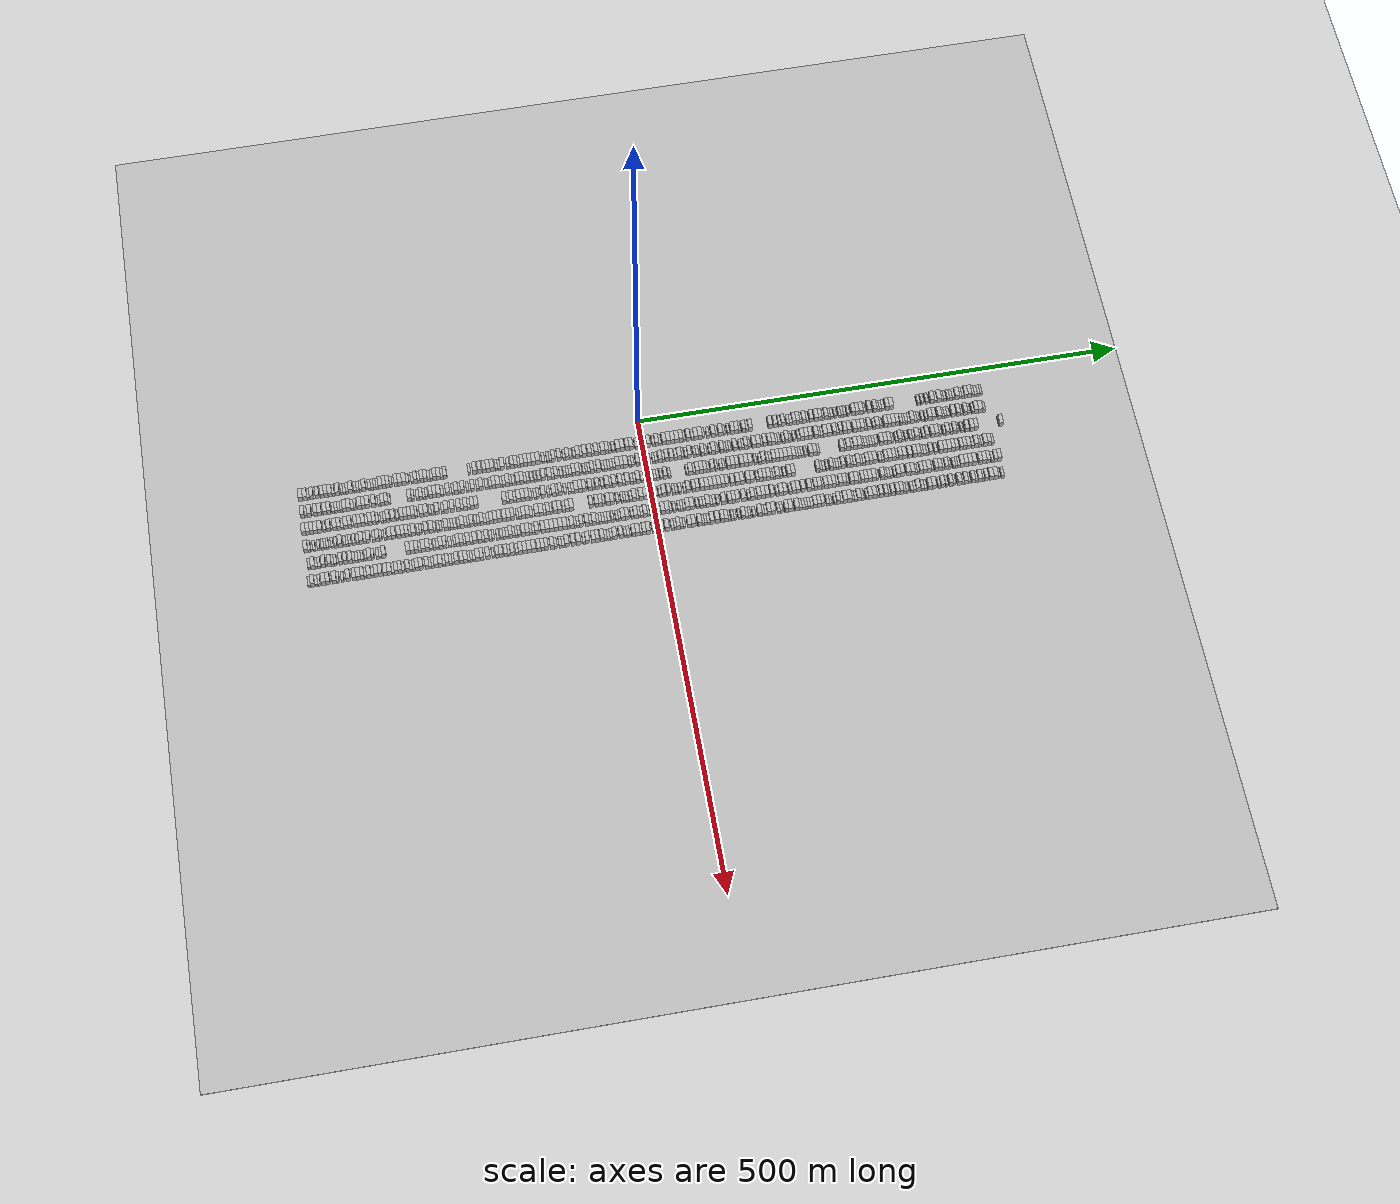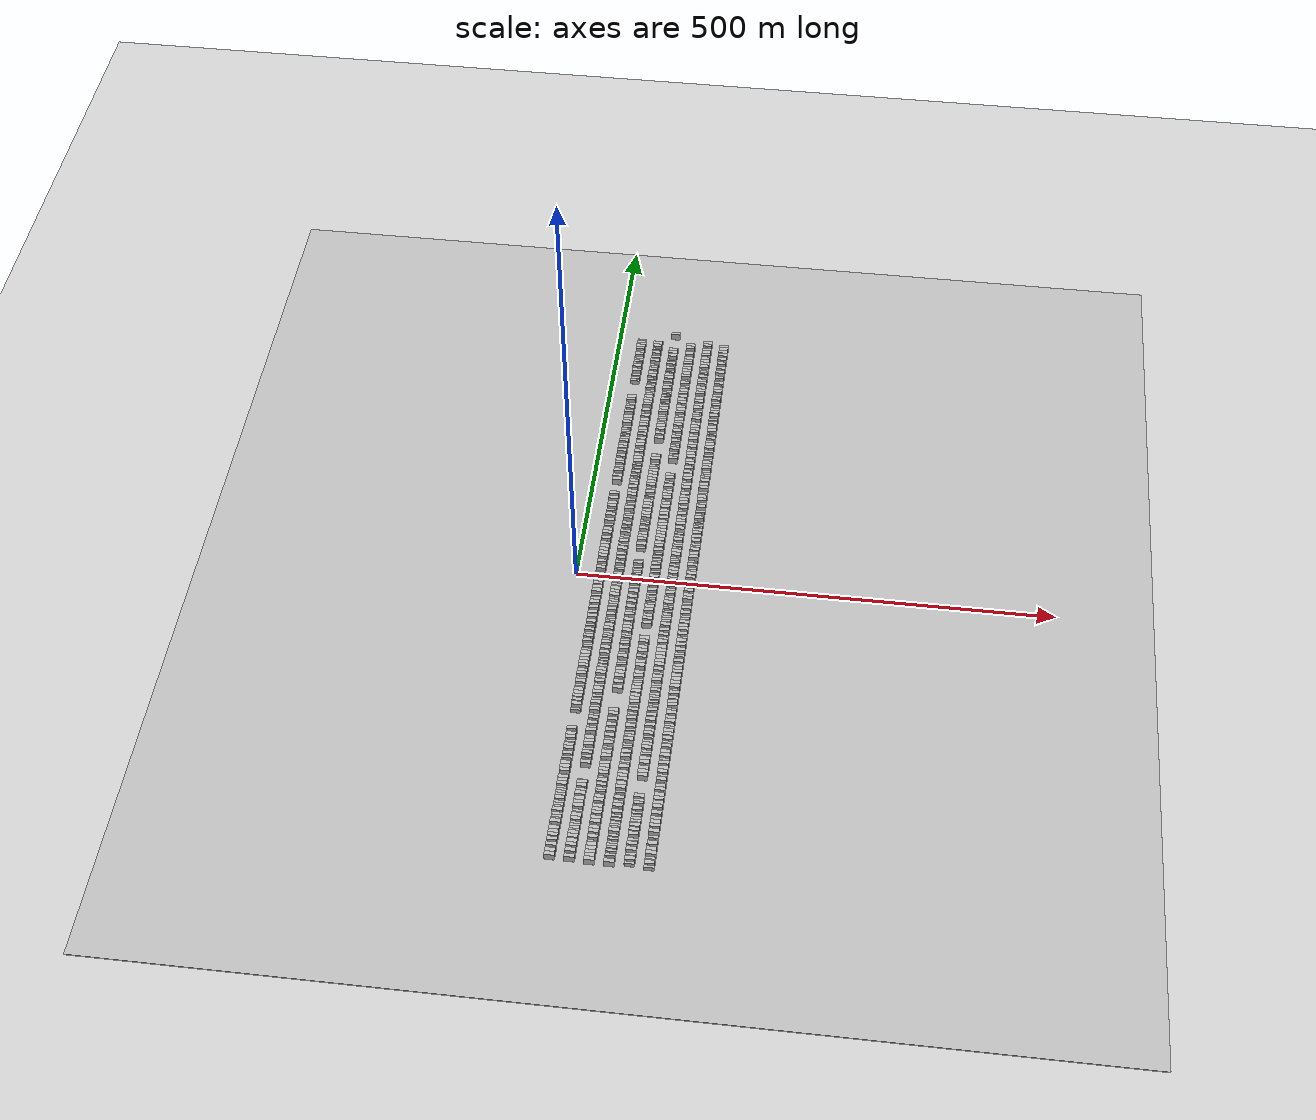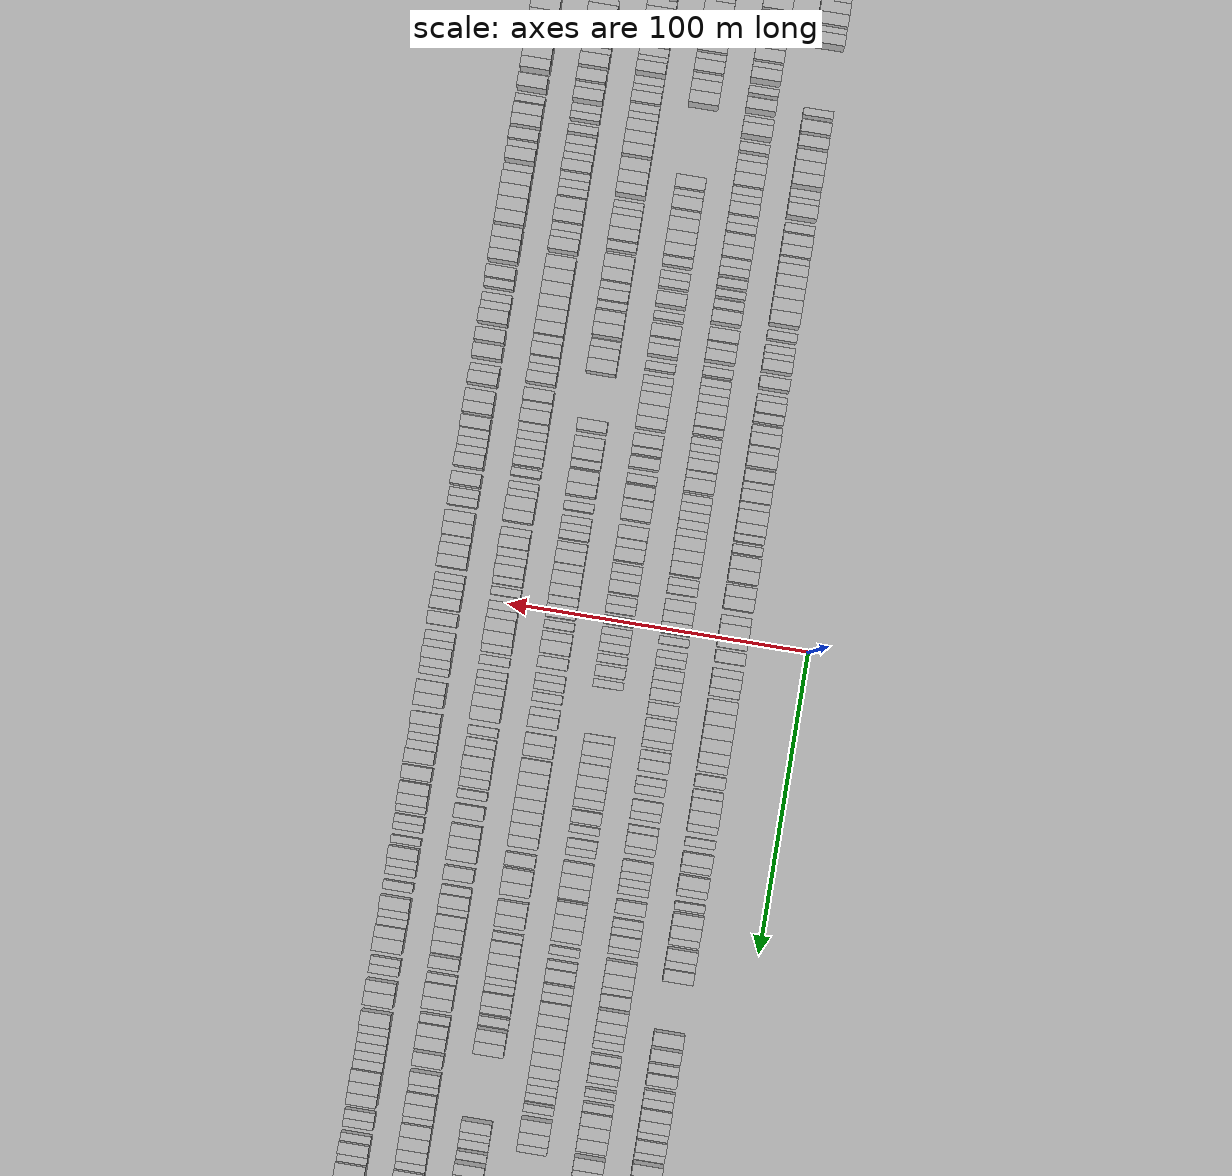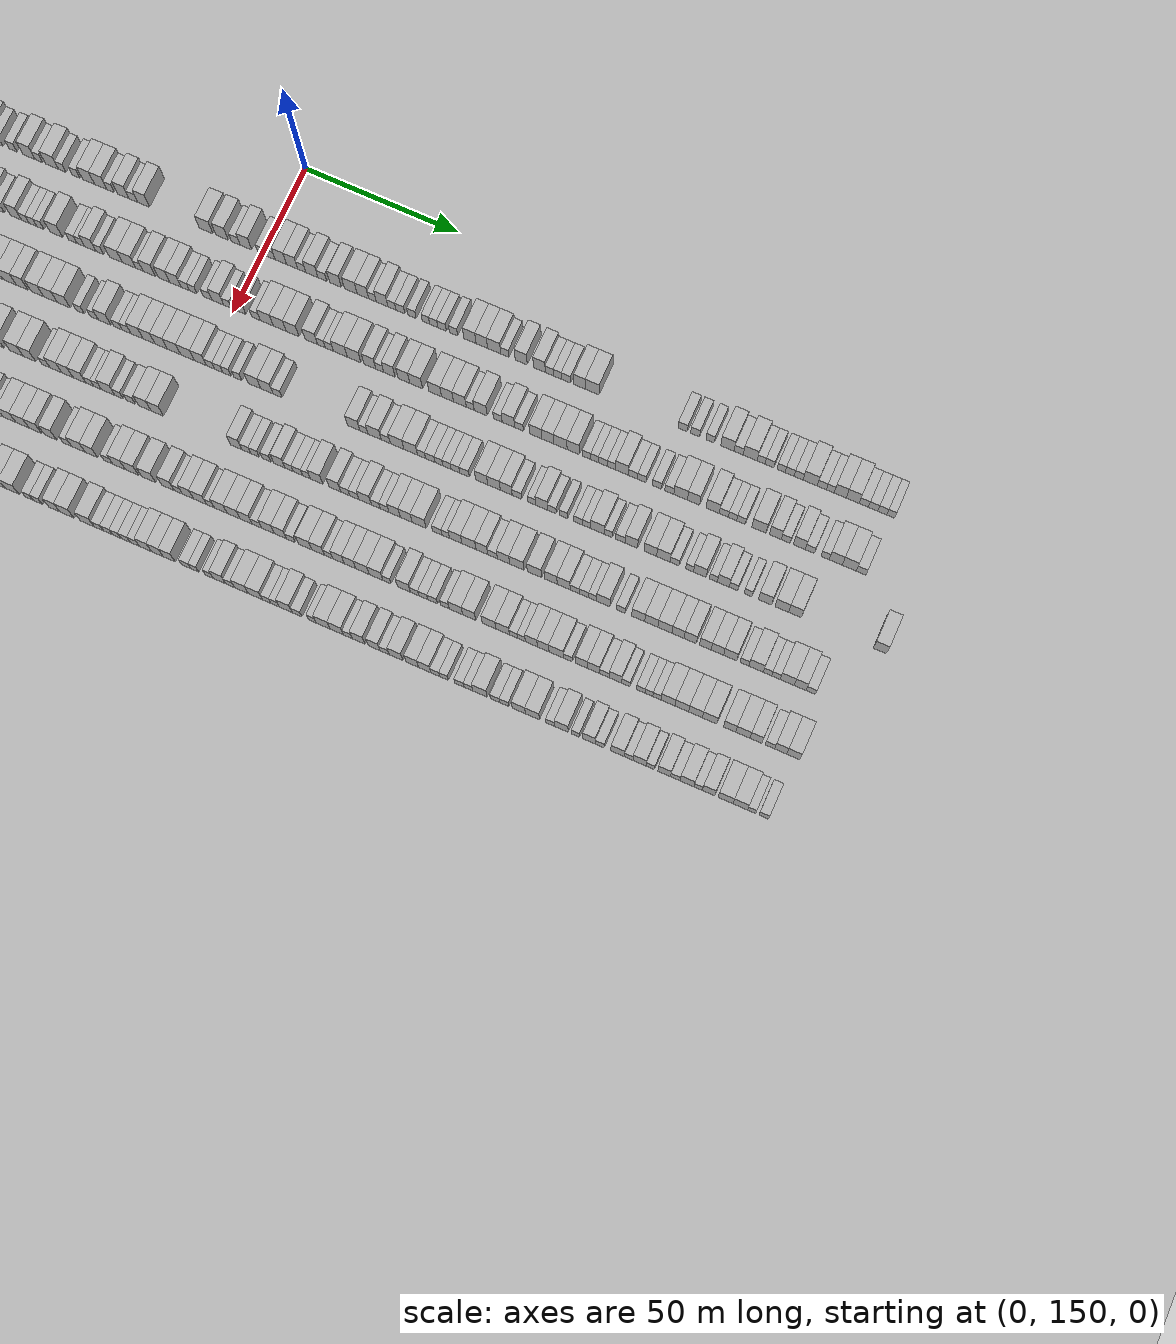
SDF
<?xml version="1.0" encoding="utf-8"?>

<sdf version="1.6">

   <world name="default">

      <gui fullscreen="0">

         <camera name="user_camera">

            <pose>-15 0 4.57585 0 0 0</pose>

            <view_controller>orbit</view_controller>

         </camera>

      </gui>

      <scene>

         <sky>

           <clouds>

             <speed>12</speed>

           </clouds>

         </sky>

         <ambient>0.4 0.4 0.4 1</ambient>

         <background>0.7 0.7 0.7 1</background>

         <shadows>1</shadows>

      </scene>

      <gravity>0 0 -9.8066</gravity>

      <magnetic_field>6e-06 2.3e-05 -4.2e-05</magnetic_field>

      <physics default="0" name="default_physics" type="ode">

         <ode>

            <solver>

               <type>quick</type>

               <iters>10</iters>

               <sor>1.0</sor>

               <use_dynamic_moi_rescaling>0</use_dynamic_moi_rescaling>

            </solver>

            <constraints>

               <cfm>0</cfm>

               <erp>0.2</erp>

               <contact_max_correcting_vel>100</contact_max_correcting_vel>

               <contact_surface_layer>0.001</contact_surface_layer>

            </constraints>

         </ode>

         <max_step_size>0.004</max_step_size>

         <real_time_factor>1</real_time_factor>

         <real_time_update_rate>250</real_time_update_rate>

      </physics>

      <light name="sun" type="directional">

         <cast_shadows>1</cast_shadows>

         <pose>0 0 10 0 0 0</pose>

         <diffuse>0.8 0.8 0.8 1</diffuse>

         <specular>0.2 0.2 0.2 1</specular>

         <attenuation>

            <range>1000</range>

            <constant>0.9</constant>

            <linear>0.01</linear>

            <quadratic>0.001</quadratic>

         </attenuation>

         <direction>-0.5 0.1 -0.9</direction>

      </light>

      <include>

         <name>ground_plane_1</name>

         <uri>model://HANNAS_ground_plane</uri>

         <pose>0 0 0  0 0 0</pose>

      </include>

      <include>

         <name>ground_plane_2</name>

         <uri>model://HANNAS_ground_plane</uri>

         <pose>100 0 0  0 0 0</pose>

      </include>

      <model name="building_1">

         <static>1</static>

         <pose frame="">25.0000 -346.8414 0 0.000000 0.000000 0.000000</pose>

         <link name="link">

            <pose frame="">0 0 4.50 0 0 0</pose>

            <collision name="collision">

               <geometry>

                  <box>

                     <size>10.0000 4.3171 9.0000</size>

                  </box>

               </geometry>

               <max_contacts>10</max_contacts>

               <surface>

                  <contact>

                     <ode/>

                  </contact>

                  <bounce/>

                  <friction>

                     <torsional>

                        <ode/>

                     </torsional>

                     <ode/>

                  </friction>

               </surface>

            </collision>

            <visual name="visual">

               <cast_shadows>0</cast_shadows>

               <geometry>

                  <box>

                     <size>10.0000 4.3171 9.0000</size>

                  </box>

               </geometry>

               <material>

                  <script>

                     <uri>model://HANNAS_wall/materials/scripts</uri>

                     <uri>model://HANNAS_wall/materials/textures</uri>

                     <name>vrc/HANNAS_wall</name>

                  </script>

               </material>

            </visual>

            <self_collide>0</self_collide>

            <enable_wind>0</enable_wind>

            <kinematic>0</kinematic>

         </link>

      </model>

      <model name="building_2">

         <static>1</static>

         <pose frame="">25.0000 -342.5067 0 0.000000 0.000000 0.000000</pose>

         <link name="link">

            <pose frame="">0 0 4.50 0 0 0</pose>

            <collision name="collision">

               <geometry>

                  <box>

                     <size>10.0000 4.3523 9.0000</size>

                  </box>

               </geometry>

               <max_contacts>10</max_contacts>

               <surface>

                  <contact>

                     <ode/>

                  </contact>

                  <bounce/>

                  <friction>

                     <torsional>

                        <ode/>

                     </torsional>

                     <ode/>

                  </friction>

               </surface>

            </collision>

            <visual name="visual">

               <cast_shadows>0</cast_shadows>

               <geometry>

                  <box>

                     <size>10.0000 4.3523 9.0000</size>

                  </box>

               </geometry>

               <material>

                  <script>

                     <uri>model://HANNAS_wall/materials/scripts</uri>

                     <uri>model://HANNAS_wall/materials/textures</uri>

                     <name>vrc/HANNAS_wall</name>

                  </script>

               </material>

            </visual>

            <self_collide>0</self_collide>

            <enable_wind>0</enable_wind>

            <kinematic>0</kinematic>

         </link>

      </model>

      <model name="building_3">

         <static>1</static>

         <pose frame="">25.0000 -339.0780 0 0.000000 0.000000 0.000000</pose>

         <link name="link">

            <pose frame="">0 0 3.00 0 0 0</pose>

            <collision name="collision">

               <geometry>

                  <box>

                     <size>10.0000 2.5053 6.0000</size>

                  </box>

               </geometry>

               <max_contacts>10</max_contacts>

               <surface>

                  <contact>

                     <ode/>

                  </contact>

                  <bounce/>

                  <friction>

                     <torsional>

                        <ode/>

                     </torsional>

                     <ode/>

                  </friction>

               </surface>

            </collision>

            <visual name="visual">

               <cast_shadows>0</cast_shadows>

               <geometry>

                  <box>

                     <size>10.0000 2.5053 6.0000</size>

                  </box>

               </geometry>

               <material>

                  <script>

                     <uri>model://HANNAS_wall/materials/scripts</uri>

                     <uri>model://HANNAS_wall/materials/textures</uri>

                     <name>vrc/HANNAS_wall</name>

                  </script>

               </material>

            </visual>

            <self_collide>0</self_collide>

            <enable_wind>0</enable_wind>

            <kinematic>0</kinematic>

         </link>

      </model>

      <model name="building_4">

         <static>1</static>

         <pose frame="">25.0000 -335.9229 0 0.000000 0.000000 0.000000</pose>

         <link name="link">

            <pose frame="">0 0 4.50 0 0 0</pose>

            <collision name="collision">

               <geometry>

                  <box>

                     <size>10.0000 3.8049 9.0000</size>

                  </box>

               </geometry>

               <max_contacts>10</max_contacts>

               <surface>

                  <contact>

                     <ode/>

                  </contact>

                  <bounce/>

                  <friction>

                     <torsional>

                        <ode/>

                     </torsional>

                     <ode/>

                  </friction>

               </surface>

            </collision>

            <visual name="visual">

               <cast_shadows>0</cast_shadows>

               <geometry>

                  <box>

                     <size>10.0000 3.8049 9.0000</size>

                  </box>

               </geometry>

               <material>

                  <script>

                     <uri>model://HANNAS_wall/materials/scripts</uri>

                     <uri>model://HANNAS_wall/materials/textures</uri>

                     <name>vrc/HANNAS_wall</name>

                  </script>

               </material>

            </visual>

            <self_collide>0</self_collide>

            <enable_wind>0</enable_wind>

            <kinematic>0</kinematic>

         </link>

      </model>

      <model name="building_5">

         <static>1</static>

         <pose frame="">25.0000 -330.0891 0 0.000000 0.000000 0.000000</pose>

         <link name="link">

            <pose frame="">0 0 4.50 0 0 0</pose>

            <collision name="collision">

               <geometry>

                  <box>

                     <size>10.0000 3.8627 9.0000</size>

                  </box>

               </geometry>

               <max_contacts>10</max_contacts>

               <surface>

                  <contact>

                     <ode/>

                  </contact>

                  <bounce/>

                  <friction>

                     <torsional>

                        <ode/>

                     </torsional>

                     <ode/>

                  </friction>

               </surface>

            </collision>

            <visual name="visual">

               <cast_shadows>0</cast_shadows>

               <geometry>

                  <box>

                     <size>10.0000 3.8627 9.0000</size>

                  </box>

               </geometry>

               <material>

                  <script>

                     <uri>model://HANNAS_wall/materials/scripts</uri>

                     <uri>model://HANNAS_wall/materials/textures</uri>

                     <name>vrc/HANNAS_wall</name>

                  </script>

               </material>

            </visual>

            <self_collide>0</self_collide>

            <enable_wind>0</enable_wind>

            <kinematic>0</kinematic>

         </link>

      </model>

      <model name="building_6">

         <static>1</static>

         <pose frame="">25.0000 -325.3120 0 0.000000 0.000000 0.000000</pose>

         <link name="link">

            <pose frame="">0 0 4.50 0 0 0</pose>

            <collision name="collision">

               <geometry>

                  <box>

                     <size>10.0000 3.6916 9.0000</size>

                  </box>

               </geometry>

               <max_contacts>10</max_contacts>

               <surface>

                  <contact>

                     <ode/>

                  </contact>

                  <bounce/>

                  <friction>

                     <torsional>

                        <ode/>

                     </torsional>

                     <ode/>

                  </friction>

               </surface>

            </collision>

            <visual name="visual">

               <cast_shadows>0</cast_shadows>

               <geometry>

                  <box>

                     <size>10.0000 3.6916 9.0000</size>

                  </box>

               </geometry>

               <material>

                  <script>

                     <uri>model://HANNAS_wall/materials/scripts</uri>

                     <uri>model://HANNAS_wall/materials/textures</uri>

                     <name>vrc/HANNAS_wall</name>

                  </script>

               </material>

            </visual>

            <self_collide>0</self_collide>

            <enable_wind>0</enable_wind>

            <kinematic>0</kinematic>

         </link>

      </model>

      <model name="building_7">

         <static>1</static>

         <pose frame="">25.0000 -321.5750 0 0.000000 0.000000 0.000000</pose>

         <link name="link">

            <pose frame="">0 0 4.50 0 0 0</pose>

            <collision name="collision">

               <geometry>

                  <box>

                     <size>10.0000 3.7823 9.0000</size>

                  </box>

               </geometry>

               <max_contacts>10</max_contacts>

               <surface>

                  <contact>

                     <ode/>

                  </contact>

                  <bounce/>

                  <friction>

                     <torsional>

                        <ode/>

                     </torsional>

                     <ode/>

                  </friction>

               </surface>

            </collision>

            <visual name="visual">

               <cast_shadows>0</cast_shadows>

               <geometry>

                  <box>

                     <size>10.0000 3.7823 9.0000</size>

                  </box>

               </geometry>

               <material>

                  <script>

                     <uri>model://HANNAS_wall/materials/scripts</uri>

                     <uri>model://HANNAS_wall/materials/textures</uri>

                     <name>vrc/HANNAS_wall</name>

                  </script>

               </material>

            </visual>

            <self_collide>0</self_collide>

            <enable_wind>0</enable_wind>

            <kinematic>0</kinematic>

         </link>

      </model>

      <model name="building_8">

         <static>1</static>

         <pose frame="">25.0000 -317.5639 0 0.000000 0.000000 0.000000</pose>

         <link name="link">

            <pose frame="">0 0 4.50 0 0 0</pose>

            <collision name="collision">

               <geometry>

                  <box>

                     <size>10.0000 4.2399 9.0000</size>

                  </box>

               </geometry>

               <max_contacts>10</max_contacts>

               <surface>

                  <contact>

                     <ode/>

                  </contact>

                  <bounce/>

                  <friction>

                     <torsional>

                        <ode/>

                     </torsional>

                     <ode/>

                  </friction>

               </surface>

            </collision>

            <visual name="visual">

               <cast_shadows>0</cast_shadows>

               <geometry>

                  <box>

                     <size>10.0000 4.2399 9.0000</size>

                  </box>

               </geometry>

               <material>

                  <script>

                     <uri>model://HANNAS_wall/materials/scripts</uri>

                     <uri>model://HANNAS_wall/materials/textures</uri>

                     <name>vrc/HANNAS_wall</name>

                  </script>

               </material>

            </visual>

            <self_collide>0</self_collide>

            <enable_wind>0</enable_wind>

            <kinematic>0</kinematic>

         </link>

      </model>

      <model name="building_9">

         <static>1</static>

         <pose frame="">25.0000 -314.1928 0 0.000000 0.000000 0.000000</pose>

         <link name="link">

            <pose frame="">0 0 3.00 0 0 0</pose>

            <collision name="collision">

               <geometry>

                  <box>

                     <size>10.0000 2.5023 6.0000</size>

                  </box>

               </geometry>

               <max_contacts>10</max_contacts>

               <surface>

                  <contact>

                     <ode/>

                  </contact>

                  <bounce/>

                  <friction>

                     <torsional>

                        <ode/>

                     </torsional>

                     <ode/>

                  </friction>

               </surface>

            </collision>

            <visual name="visual">

               <cast_shadows>0</cast_shadows>

               <geometry>

                  <box>

                     <size>10.0000 2.5023 6.0000</size>

                  </box>

               </geometry>

               <material>

                  <script>

                     <uri>model://HANNAS_wall/materials/scripts</uri>

                     <uri>model://HANNAS_wall/materials/textures</uri>

                     <name>vrc/HANNAS_wall</name>

                  </script>

               </material>

            </visual>

            <self_collide>0</self_collide>

            <enable_wind>0</enable_wind>

            <kinematic>0</kinematic>

         </link>

      </model>

      <model name="building_10">

         <static>1</static>

         <pose frame="">25.0000 -309.8536 0 0.000000 0.000000 0.000000</pose>

         <link name="link">

            <pose frame="">0 0 4.50 0 0 0</pose>

            <collision name="collision">

               <geometry>

                  <box>

                     <size>10.0000 4.1762 9.0000</size>

                  </box>

               </geometry>

               <max_contacts>10</max_contacts>

               <surface>

                  <contact>

                     <ode/>

                  </contact>

                  <bounce/>

                  <friction>

                     <torsional>

                        <ode/>

                     </torsional>

                     <ode/>

                  </friction>

               </surface>

            </collision>

            <visual name="visual">

               <cast_shadows>0</cast_shadows>

               <geometry>

                  <box>

                     <size>10.0000 4.1762 9.0000</size>

                  </box>

               </geometry>

               <material>

                  <script>

                     <uri>model://HANNAS_wall/materials/scripts</uri>

                     <uri>model://HANNAS_wall/materials/textures</uri>

                     <name>vrc/HANNAS_wall</name>

                  </script>

               </material>

            </visual>

            <self_collide>0</self_collide>

            <enable_wind>0</enable_wind>

            <kinematic>0</kinematic>

         </link>

      </model>

      <model name="building_11">

         <static>1</static>

         <pose frame="">25.0000 -305.5588 0 0.000000 0.000000 0.000000</pose>

         <link name="link">

            <pose frame="">0 0 3.00 0 0 0</pose>

            <collision name="collision">

               <geometry>

                  <box>

                     <size>10.0000 2.4134 6.0000</size>

                  </box>

               </geometry>

               <max_contacts>10</max_contacts>

               <surface>

                  <contact>

                     <ode/>

                  </contact>

                  <bounce/>

                  <friction>

                     <torsional>

                        <ode/>

                     </torsional>

                     <ode/>

                  </friction>

               </surface>

            </collision>

            <visual name="visual">

               <cast_shadows>0</cast_shadows>

               <geometry>

                  <box>

                     <size>10.0000 2.4134 6.0000</size>

                  </box>

               </geometry>

               <material>

                  <script>

                     <uri>model://HANNAS_wall/materials/scripts</uri>

                     <uri>model://HANNAS_wall/materials/textures</uri>

                     <name>vrc/HANNAS_wall</name>

                  </script>

               </material>

            </visual>

            <self_collide>0</self_collide>

            <enable_wind>0</enable_wind>

            <kinematic>0</kinematic>

         </link>

      </model>

      <model name="building_12">

         <static>1</static>

         <pose frame="">25.0000 -303.0187 0 0.000000 0.000000 0.000000</pose>

         <link name="link">

            <pose frame="">0 0 3.00 0 0 0</pose>

            <collision name="collision">

               <geometry>

                  <box>

                     <size>10.0000 2.6667 6.0000</size>

                  </box>

               </geometry>

               <max_contacts>10</max_contacts>

               <surface>

                  <contact>

                     <ode/>

                  </contact>

                  <bounce/>

                  <friction>

                     <torsional>

                        <ode/>

                     </torsional>

                     <ode/>

                  </friction>

               </surface>

            </collision>

            <visual name="visual">

               <cast_shadows>0</cast_shadows>

               <geometry>

                  <box>

                     <size>10.0000 2.6667 6.0000</size>

                  </box>

               </geometry>

               <material>

                  <script>

                     <uri>model://HANNAS_wall/materials/scripts</uri>

                     <uri>model://HANNAS_wall/materials/textures</uri>

                     <name>vrc/HANNAS_wall</name>

                  </script>

               </material>

            </visual>

            <self_collide>0</self_collide>

            <enable_wind>0</enable_wind>

            <kinematic>0</kinematic>

         </link>

      </model>

      <model name="building_13">

         <static>1</static>

         <pose frame="">25.0000 -300.2134 0 0.000000 0.000000 0.000000</pose>

         <link name="link">

            <pose frame="">0 0 3.00 0 0 0</pose>

            <collision name="collision">

               <geometry>

                  <box>

                     <size>10.0000 2.9440 6.0000</size>

                  </box>

               </geometry>

               <max_contacts>10</max_contacts>

               <surface>

                  <contact>

                     <ode/>

                  </contact>

                  <bounce/>

                  <friction>

                     <torsional>

                        <ode/>

                     </torsional>

                     <ode/>

                  </friction>

               </surface>

            </collision>

            <visual name="visual">

               <cast_shadows>0</cast_shadows>

               <geometry>

                  <box>

                     <size>10.0000 2.9440 6.0000</size>

                  </box>

               </geometry>

               <material>

                  <script>

                     <uri>model://HANNAS_wall/materials/scripts</uri>

                     <uri>model://HANNAS_wall/materials/textures</uri>

                     <name>vrc/HANNAS_wall</name>

                  </script>

               </material>

            </visual>

            <self_collide>0</self_collide>

            <enable_wind>0</enable_wind>

            <kinematic>0</kinematic>

         </link>

      </model>

      <model name="building_14">

         <static>1</static>

         <pose frame="">25.0000 -296.6027 0 0.000000 0.000000 0.000000</pose>

         <link name="link">

            <pose frame="">0 0 4.50 0 0 0</pose>

            <collision name="collision">

               <geometry>

                  <box>

                     <size>10.0000 4.2774 9.0000</size>

                  </box>

               </geometry>

               <max_contacts>10</max_contacts>

               <surface>

                  <contact>

                     <ode/>

                  </contact>

                  <bounce/>

                  <friction>

                     <torsional>

                        <ode/>

                     </torsional>

                     <ode/>

                  </friction>

               </surface>

            </collision>

            <visual name="visual">

               <cast_shadows>0</cast_shadows>

               <geometry>

                  <box>

                     <size>10.0000 4.2774 9.0000</size>

                  </box>

               </geometry>

               <material>

                  <script>

                     <uri>model://HANNAS_wall/materials/scripts</uri>

                     <uri>model://HANNAS_wall/materials/textures</uri>

                     <name>vrc/HANNAS_wall</name>

                  </script>

               </material>

            </visual>

            <self_collide>0</self_collide>

            <enable_wind>0</enable_wind>

            <kinematic>0</kinematic>

         </link>

      </model>

      <model name="building_15">

         <static>1</static>

         <pose frame="">25.0000 -292.1122 0 0.000000 0.000000 0.000000</pose>

         <link name="link">

            <pose frame="">0 0 3.00 0 0 0</pose>

            <collision name="collision">

               <geometry>

                  <box>

                     <size>10.0000 2.7037 6.0000</size>

                  </box>

               </geometry>

               <max_contacts>10</max_contacts>

               <surface>

                  <contact>

                     <ode/>

                  </contact>

                  <bounce/>

                  <friction>

                     <torsional>

                        <ode/>

                     </torsional>

                     <ode/>

                  </friction>

               </surface>

            </collision>

            <visual name="visual">

               <cast_shadows>0</cast_shadows>

               <geometry>

                  <box>

                     <size>10.0000 2.7037 6.0000</size>

                  </box>

               </geometry>

               <material>

                  <script>

                     <uri>model://HANNAS_wall/materials/scripts</uri>

                     <uri>model://HANNAS_wall/materials/textures</uri>

                     <name>vrc/HANNAS_wall</name>

                  </script>

               </material>

            </visual>

            <self_collide>0</self_collide>

            <enable_wind>0</enable_wind>

            <kinematic>0</kinematic>

         </link>

      </model>

      <model name="building_16">

         <static>1</static>

         <pose frame="">25.0000 -289.3489 0 0.000000 0.000000 0.000000</pose>

         <link name="link">

            <pose frame="">0 0 3.00 0 0 0</pose>

            <collision name="collision">

               <geometry>

                  <box>

                     <size>10.0000 2.8229 6.0000</size>

                  </box>

               </geometry>

               <max_contacts>10</max_contacts>

               <surface>

                  <contact>

                     <ode/>

                  </contact>

                  <bounce/>

                  <friction>

                     <torsional>

                        <ode/>

                     </torsional>

                     <ode/>

                  </friction>

               </surface>

            </collision>

            <visual name="visual">

               <cast_shadows>0</cast_shadows>

               <geometry>

                  <box>

                     <size>10.0000 2.8229 6.0000</size>

                  </box>

               </geometry>

               <material>

                  <script>

                     <uri>model://HANNAS_wall/materials/scripts</uri>

                     <uri>model://HANNAS_wall/materials/textures</uri>

                     <name>vrc/HANNAS_wall</name>

                  </script>

               </material>

            </visual>

            <self_collide>0</self_collide>

            <enable_wind>0</enable_wind>

            <kinematic>0</kinematic>

         </link>

      </model>

      <model name="building_17">

         <static>1</static>

         <pose frame="">25.0000 -286.6313 0 0.000000 0.000000 0.000000</pose>

         <link name="link">

            <pose frame="">0 0 3.00 0 0 0</pose>

            <collision name="collision">

               <geometry>

                  <box>

                     <size>10.0000 2.6121 6.0000</size>

                  </box>

               </geometry>

               <max_contacts>10</max_contacts>

               <surface>

                  <contact>

                     <ode/>

                  </contact>

                  <bounce/>

                  <friction>

                     <torsional>

                        <ode/>

                     </torsional>

                     <ode/>

                  </friction>

               </surface>

            </collision>

            <visual name="visual">

               <cast_shadows>0</cast_shadows>

               <geometry>

                  <box>

                     <size>10.0000 2.6121 6.0000</size>

                  </box>

               </geometry>

               <material>

                  <script>

                     <uri>model://HANNAS_wall/materials/scripts</uri>

                     <uri>model://HANNAS_wall/materials/textures</uri>

                     <name>vrc/HANNAS_wall</name>

                  </script>

               </material>

            </visual>

            <self_collide>0</self_collide>

            <enable_wind>0</enable_wind>

            <kinematic>0</kinematic>

         </link>

      </model>

      <model name="building_18">

         <static>1</static>

         <pose frame="">25.0000 -283.2771 0 0.000000 0.000000 0.000000</pose>

         <link name="link">

            <pose frame="">0 0 4.50 0 0 0</pose>

            <collision name="collision">

               <geometry>

                  <box>

                     <size>10.0000 4.0963 9.0000</size>

                  </box>

               </geometry>

               <max_contacts>10</max_contacts>

               <surface>

                  <contact>

                     <ode/>

                  </contact>

                  <bounce/>

                  <friction>

                     <torsional>

                        <ode/>

                     </torsional>

                     <ode/>

                  </friction>

               </surface>

            </collision>

            <visual name="visual">

               <cast_shadows>0</cast_shadows>

               <geometry>

                  <box>

                     <size>10.0000 4.0963 9.0000</size>

                  </box>

               </geometry>

               <material>

                  <script>

                     <uri>model://HANNAS_wall/materials/scripts</uri>

                     <uri>model://HANNAS_wall/materials/textures</uri>

                     <name>vrc/HANNAS_wall</name>

                  </script>

               </material>

            </visual>

            <self_collide>0</self_collide>

            <enable_wind>0</enable_wind>

            <kinematic>0</kinematic>

         </link>

      </model>

      <model name="building_19">

         <static>1</static>

         <pose frame="">25.0000 -277.7776 0 0.000000 0.000000 0.000000</pose>

         <link name="link">

            <pose frame="">0 0 3.00 0 0 0</pose>

            <collision name="collision">

               <geometry>

                  <box>

                     <size>10.0000 2.9027 6.0000</size>

                  </box>

               </geometry>

               <max_contacts>10</max_contacts>

               <surface>

                  <contact>

                     <ode/>

                  </contact>

                  <bounce/>

                  <friction>

                     <torsional>

                        <ode/>

                     </torsional>

                     <ode/>

                  </friction>

               </surface>

            </collision>

            <visual name="visual">

               <cast_shadows>0</cast_shadows>

               <geometry>

                  <box>

                     <size>10.0000 2.9027 6.0000</size>

                  </box>

               </geometry>

               <material>

                  <script>

                     <uri>model://HANNAS_wall/materials/scripts</uri>

                     <uri>model://HANNAS_wall/materials/textures</uri>

                     <name>vrc/HANNAS_wall</name>

                  </script>

               </material>

            </visual>

            <self_collide>0</self_collide>

            <enable_wind>0</enable_wind>

            <kinematic>0</kinematic>

         </link>

      </model>

      <model name="building_20">

         <static>1</static>

         <pose frame="">25.0000 -274.9839 0 0.000000 0.000000 0.000000</pose>

         <link name="link">

            <pose frame="">0 0 3.00 0 0 0</pose>

            <collision name="collision">

               <geometry>

                  <box>

                     <size>10.0000 2.6849 6.0000</size>

                  </box>

               </geometry>

               <max_contacts>10</max_contacts>

               <surface>

                  <contact>

                     <ode/>

                  </contact>

                  <bounce/>

                  <friction>

                     <torsional>

                        <ode/>

                     </torsional>

                     <ode/>

                  </friction>

               </surface>

            </collision>

            <visual name="visual">

               <cast_shadows>0</cast_shadows>

               <geometry>

                  <box>

                     <size>10.0000 2.6849 6.0000</size>

                  </box>

               </geometry>

               <material>

                  <script>

                     <uri>model://HANNAS_wall/materials/scripts</uri>

                     <uri>model://HANNAS_wall/materials/textures</uri>

                     <name>vrc/HANNAS_wall</name>

                  </script>

               </material>

            </visual>

            <self_collide>0</self_collide>

            <enable_wind>0</enable_wind>

            <kinematic>0</kinematic>

         </link>

      </model>

      <model name="building_21">

         <static>1</static>

         <pose frame="">25.0000 -272.4067 0 0.000000 0.000000 0.000000</pose>

         <link name="link">

            <pose frame="">0 0 3.00 0 0 0</pose>

            <collision name="collision">

               <geometry>

                  <box>

                     <size>10.0000 2.4694 6.0000</size>

                  </box>

               </geometry>

               <max_contacts>10</max_contacts>

               <surface>

                  <contact>

                     <ode/>

                  </contact>

                  <bounce/>

                  <friction>

                     <torsional>

                        <ode/>

                     </torsional>

                     <ode/>

                  </friction>

               </surface>

            </collision>

            <visual name="visual">

               <cast_shadows>0</cast_shadows>

               <geometry>

                  <box>

                     <size>10.0000 2.4694 6.0000</size>

                  </box>

               </geometry>

               <material>

                  <script>

                     <uri>model://HANNAS_wall/materials/scripts</uri>

                     <uri>model://HANNAS_wall/materials/textures</uri>

                     <name>vrc/HANNAS_wall</name>

                  </script>

               </material>

            </visual>

            <self_collide>0</self_collide>

            <enable_wind>0</enable_wind>

            <kinematic>0</kinematic>

         </link>

      </model>

      <model name="building_22">

         <static>1</static>

         <pose frame="">25.0000 -269.9528 0 0.000000 0.000000 0.000000</pose>

         <link name="link">

            <pose frame="">0 0 3.00 0 0 0</pose>

            <collision name="collision">

               <geometry>

                  <box>

                     <size>10.0000 2.4384 6.0000</size>

                  </box>

               </geometry>

               <max_contacts>10</max_contacts>

               <surface>

                  <contact>

                     <ode/>

                  </contact>

                  <bounce/>

                  <friction>

                     <torsional>

                        <ode/>

                     </torsional>

                     <ode/>

                  </friction>

               </surface>

            </collision>

            <visual name="visual">

               <cast_shadows>0</cast_shadows>

               <geometry>

                  <box>

                     <size>10.0000 2.4384 6.0000</size>

                  </box>

               </geometry>

               <material>

                  <script>

                     <uri>model://HANNAS_wall/materials/scripts</uri>

                     <uri>model://HANNAS_wall/materials/textures</uri>

                     <name>vrc/HANNAS_wall</name>

                  </script>

               </material>

            </visual>

            <self_collide>0</self_collide>

            <enable_wind>0</enable_wind>

            <kinematic>0</kinematic>

         </link>

      </model>

      <model name="building_23">

         <static>1</static>

         <pose frame="">25.0000 -266.7361 0 0.000000 0.000000 0.000000</pose>

         <link name="link">

            <pose frame="">0 0 4.50 0 0 0</pose>

            <collision name="collision">

               <geometry>

                  <box>

                     <size>10.0000 3.9950 9.0000</size>

                  </box>

               </geometry>

               <max_contacts>10</max_contacts>

               <surface>

                  <contact>

                     <ode/>

                  </contact>

                  <bounce/>

                  <friction>

                     <torsional>

                        <ode/>

                     </torsional>

                     <ode/>

                  </friction>

               </surface>

            </collision>

            <visual name="visual">

               <cast_shadows>0</cast_shadows>

               <geometry>

                  <box>

                     <size>10.0000 3.9950 9.0000</size>

                  </box>

               </geometry>

               <material>

                  <script>

                     <uri>model://HANNAS_wall/materials/scripts</uri>

                     <uri>model://HANNAS_wall/materials/textures</uri>

                     <name>vrc/HANNAS_wall</name>

                  </script>

               </material>

            </visual>

            <self_collide>0</self_collide>

            <enable_wind>0</enable_wind>

            <kinematic>0</kinematic>

         </link>

      </model>

      <model name="building_24">

         <static>1</static>

         <pose frame="">25.0000 -262.9352 0 0.000000 0.000000 0.000000</pose>

         <link name="link">

            <pose frame="">0 0 4.50 0 0 0</pose>

            <collision name="collision">

               <geometry>

                  <box>

                     <size>10.0000 3.6069 9.0000</size>

                  </box>

               </geometry>

               <max_contacts>10</max_contacts>

               <surface>

                  <contact>

                     <ode/>

                  </contact>

                  <bounce/>

                  <friction>

                     <torsional>

                        <ode/>

                     </torsional>

                     <ode/>

                  </friction>

               </surface>

            </collision>

            <visual name="visual">

               <cast_shadows>0</cast_shadows>

               <geometry>

                  <box>

                     <size>10.0000 3.6069 9.0000</size>

                  </box>

               </geometry>

               <material>

                  <script>

                     <uri>model://HANNAS_wall/materials/scripts</uri>

                     <uri>model://HANNAS_wall/materials/textures</uri>

                     <name>vrc/HANNAS_wall</name>

                  </script>

               </material>

            </visual>

            <self_collide>0</self_collide>

            <enable_wind>0</enable_wind>

            <kinematic>0</kinematic>

         </link>

      </model>

      <model name="building_25">

         <static>1</static>

         <pose frame="">25.0000 -259.1891 0 0.000000 0.000000 0.000000</pose>

         <link name="link">

            <pose frame="">0 0 4.50 0 0 0</pose>

            <collision name="collision">

               <geometry>

                  <box>

                     <size>10.0000 3.8851 9.0000</size>

                  </box>

               </geometry>

               <max_contacts>10</max_contacts>

               <surface>

                  <contact>

                     <ode/>

                  </contact>

                  <bounce/>

                  <friction>

                     <torsional>

                        <ode/>

                     </torsional>

                     <ode/>

                  </friction>

               </surface>

            </collision>

            <visual name="visual">

               <cast_shadows>0</cast_shadows>

               <geometry>

                  <box>

                     <size>10.0000 3.8851 9.0000</size>

                  </box>

               </geometry>

               <material>

                  <script>

                     <uri>model://HANNAS_wall/materials/scripts</uri>

                     <uri>model://HANNAS_wall/materials/textures</uri>

                     <name>vrc/HANNAS_wall</name>

                  </script>

               </material>

            </visual>

            <self_collide>0</self_collide>

            <enable_wind>0</enable_wind>

            <kinematic>0</kinematic>

         </link>

      </model>

      <model name="building_26">

         <static>1</static>

         <pose frame="">25.0000 -255.9950 0 0.000000 0.000000 0.000000</pose>

         <link name="link">

            <pose frame="">0 0 3.00 0 0 0</pose>

            <collision name="collision">

               <geometry>

                  <box>

                     <size>10.0000 2.5032 6.0000</size>

                  </box>

               </geometry>

               <max_contacts>10</max_contacts>

               <surface>

                  <contact>

                     <ode/>

                  </contact>

                  <bounce/>

                  <friction>

                     <torsional>

                        <ode/>

                     </torsional>

                     <ode/>

                  </friction>

               </surface>

            </collision>

            <visual name="visual">

               <cast_shadows>0</cast_shadows>

               <geometry>

                  <box>

                     <size>10.0000 2.5032 6.0000</size>

                  </box>

               </geometry>

               <material>

                  <script>

                     <uri>model://HANNAS_wall/materials/scripts</uri>

                     <uri>model://HANNAS_wall/materials/textures</uri>

                     <name>vrc/HANNAS_wall</name>

                  </script>

               </material>

            </visual>

            <self_collide>0</self_collide>

            <enable_wind>0</enable_wind>

            <kinematic>0</kinematic>

         </link>

      </model>

      <model name="building_27">

         <static>1</static>

         <pose frame="">25.0000 -250.9259 0 0.000000 0.000000 0.000000</pose>

         <link name="link">

            <pose frame="">0 0 4.50 0 0 0</pose>

            <collision name="collision">

               <geometry>

                  <box>

                     <size>10.0000 3.6349 9.0000</size>

                  </box>

               </geometry>

               <max_contacts>10</max_contacts>

               <surface>

                  <contact>

                     <ode/>

                  </contact>

                  <bounce/>

                  <friction>

                     <torsional>

                        <ode/>

                     </torsional>

                     <ode/>

                  </friction>

               </surface>

            </collision>

            <visual name="visual">

               <cast_shadows>0</cast_shadows>

               <geometry>

                  <box>

                     <size>10.0000 3.6349 9.0000</size>

                  </box>

               </geometry>

               <material>

                  <script>

                     <uri>model://HANNAS_wall/materials/scripts</uri>

                     <uri>model://HANNAS_wall/materials/textures</uri>

                     <name>vrc/HANNAS_wall</name>

                  </script>

               </material>

            </visual>

            <self_collide>0</self_collide>

            <enable_wind>0</enable_wind>

            <kinematic>0</kinematic>

         </link>

      </model>

      <model name="building_28">

         <static>1</static>

         <pose frame="">25.0000 -246.9966 0 0.000000 0.000000 0.000000</pose>

         <link name="link">

            <pose frame="">0 0 4.50 0 0 0</pose>

            <collision name="collision">

               <geometry>

                  <box>

                     <size>10.0000 4.2237 9.0000</size>

                  </box>

               </geometry>

               <max_contacts>10</max_contacts>

               <surface>

                  <contact>

                     <ode/>

                  </contact>

                  <bounce/>

                  <friction>

                     <torsional>

                        <ode/>

                     </torsional>

                     <ode/>

                  </friction>

               </surface>

            </collision>

            <visual name="visual">

               <cast_shadows>0</cast_shadows>

               <geometry>

                  <box>

                     <size>10.0000 4.2237 9.0000</size>

                  </box>

               </geometry>

               <material>

                  <script>

                     <uri>model://HANNAS_wall/materials/scripts</uri>

                     <uri>model://HANNAS_wall/materials/textures</uri>

                     <name>vrc/HANNAS_wall</name>

                  </script>

               </material>

            </visual>

            <self_collide>0</self_collide>

            <enable_wind>0</enable_wind>

            <kinematic>0</kinematic>

         </link>

      </model>

      <model name="building_29">

         <static>1</static>

         <pose frame="">25.0000 -242.7215 0 0.000000 0.000000 0.000000</pose>

         <link name="link">

            <pose frame="">0 0 4.50 0 0 0</pose>

            <collision name="collision">

               <geometry>

                  <box>

                     <size>10.0000 4.3265 9.0000</size>

                  </box>

               </geometry>

               <max_contacts>10</max_contacts>

               <surface>

                  <contact>

                     <ode/>

                  </contact>

                  <bounce/>

                  <friction>

                     <torsional>

                        <ode/>

                     </torsional>

                     <ode/>

                  </friction>

               </surface>

            </collision>

            <visual name="visual">

               <cast_shadows>0</cast_shadows>

               <geometry>

                  <box>

                     <size>10.0000 4.3265 9.0000</size>

                  </box>

               </geometry>

               <material>

                  <script>

                     <uri>model://HANNAS_wall/materials/scripts</uri>

                     <uri>model://HANNAS_wall/materials/textures</uri>

                     <name>vrc/HANNAS_wall</name>

                  </script>

               </material>

            </visual>

            <self_collide>0</self_collide>

            <enable_wind>0</enable_wind>

            <kinematic>0</kinematic>

         </link>

      </model>

      <model name="building_30">

         <static>1</static>

         <pose frame="">25.0000 -239.1550 0 0.000000 0.000000 0.000000</pose>

         <link name="link">

            <pose frame="">0 0 3.00 0 0 0</pose>

            <collision name="collision">

               <geometry>

                  <box>

                     <size>10.0000 2.8065 6.0000</size>

                  </box>

               </geometry>

               <max_contacts>10</max_contacts>

               <surface>

                  <contact>

                     <ode/>

                  </contact>

                  <bounce/>

                  <friction>

                     <torsional>

                        <ode/>

                     </torsional>

                     <ode/>

                  </friction>

               </surface>

            </collision>

            <visual name="visual">

               <cast_shadows>0</cast_shadows>

               <geometry>

                  <box>

                     <size>10.0000 2.8065 6.0000</size>

                  </box>

               </geometry>

               <material>

                  <script>

                     <uri>model://HANNAS_wall/materials/scripts</uri>

                     <uri>model://HANNAS_wall/materials/textures</uri>

                     <name>vrc/HANNAS_wall</name>

                  </script>

               </material>

            </visual>

            <self_collide>0</self_collide>

            <enable_wind>0</enable_wind>

            <kinematic>0</kinematic>

         </link>

      </model>

      <model name="building_31">

         <static>1</static>

         <pose frame="">25.0000 -234.4203 0 0.000000 0.000000 0.000000</pose>

         <link name="link">

            <pose frame="">0 0 3.00 0 0 0</pose>

            <collision name="collision">

               <geometry>

                  <box>

                     <size>10.0000 2.6629 6.0000</size>

                  </box>

               </geometry>

               <max_contacts>10</max_contacts>

               <surface>

                  <contact>

                     <ode/>

                  </contact>

                  <bounce/>

                  <friction>

                     <torsional>

                        <ode/>

                     </torsional>

                     <ode/>

                  </friction>

               </surface>

            </collision>

            <visual name="visual">

               <cast_shadows>0</cast_shadows>

               <geometry>

                  <box>

                     <size>10.0000 2.6629 6.0000</size>

                  </box>

               </geometry>

               <material>

                  <script>

                     <uri>model://HANNAS_wall/materials/scripts</uri>

                     <uri>model://HANNAS_wall/materials/textures</uri>

                     <name>vrc/HANNAS_wall</name>

                  </script>

               </material>

            </visual>

            <self_collide>0</self_collide>

            <enable_wind>0</enable_wind>

            <kinematic>0</kinematic>

         </link>

      </model>

      <model name="building_32">

         <static>1</static>

         <pose frame="">25.0000 -231.2151 0 0.000000 0.000000 0.000000</pose>

         <link name="link">

            <pose frame="">0 0 4.50 0 0 0</pose>

            <collision name="collision">

               <geometry>

                  <box>

                     <size>10.0000 3.7475 9.0000</size>

                  </box>

               </geometry>

               <max_contacts>10</max_contacts>

               <surface>

                  <contact>

                     <ode/>

                  </contact>

                  <bounce/>

                  <friction>

                     <torsional>

                        <ode/>

                     </torsional>

                     <ode/>

                  </friction>

               </surface>

            </collision>

            <visual name="visual">

               <cast_shadows>0</cast_shadows>

               <geometry>

                  <box>

                     <size>10.0000 3.7475 9.0000</size>

                  </box>

               </geometry>

               <material>

                  <script>

                     <uri>model://HANNAS_wall/materials/scripts</uri>

                     <uri>model://HANNAS_wall/materials/textures</uri>

                     <name>vrc/HANNAS_wall</name>

                  </script>

               </material>

            </visual>

            <self_collide>0</self_collide>

            <enable_wind>0</enable_wind>

            <kinematic>0</kinematic>

         </link>

      </model>

      <model name="building_33">

         <static>1</static>

         <pose frame="">25.0000 -228.0153 0 0.000000 0.000000 0.000000</pose>

         <link name="link">

            <pose frame="">0 0 3.00 0 0 0</pose>

            <collision name="collision">

               <geometry>

                  <box>

                     <size>10.0000 2.6523 6.0000</size>

                  </box>

               </geometry>

               <max_contacts>10</max_contacts>

               <surface>

                  <contact>

                     <ode/>

                  </contact>

                  <bounce/>

                  <friction>

                     <torsional>

                        <ode/>

                     </torsional>

                     <ode/>

                  </friction>

               </surface>

            </collision>

            <visual name="visual">

               <cast_shadows>0</cast_shadows>

               <geometry>

                  <box>

                     <size>10.0000 2.6523 6.0000</size>

                  </box>

               </geometry>

               <material>

                  <script>

                     <uri>model://HANNAS_wall/materials/scripts</uri>

                     <uri>model://HANNAS_wall/materials/textures</uri>

                     <name>vrc/HANNAS_wall</name>

                  </script>

               </material>

            </visual>

            <self_collide>0</self_collide>

            <enable_wind>0</enable_wind>

            <kinematic>0</kinematic>

         </link>

      </model>

      <model name="building_34">

         <static>1</static>

         <pose frame="">25.0000 -224.8545 0 0.000000 0.000000 0.000000</pose>

         <link name="link">

            <pose frame="">0 0 4.50 0 0 0</pose>

            <collision name="collision">

               <geometry>

                  <box>

                     <size>10.0000 3.6692 9.0000</size>

                  </box>

               </geometry>

               <max_contacts>10</max_contacts>

               <surface>

                  <contact>

                     <ode/>

                  </contact>

                  <bounce/>

                  <friction>

                     <torsional>

                        <ode/>

                     </torsional>

                     <ode/>

                  </friction>

               </surface>

            </collision>

            <visual name="visual">

               <cast_shadows>0</cast_shadows>

               <geometry>

                  <box>

                     <size>10.0000 3.6692 9.0000</size>

                  </box>

               </geometry>

               <material>

                  <script>

                     <uri>model://HANNAS_wall/materials/scripts</uri>

                     <uri>model://HANNAS_wall/materials/textures</uri>

                     <name>vrc/HANNAS_wall</name>

                  </script>

               </material>

            </visual>

            <self_collide>0</self_collide>

            <enable_wind>0</enable_wind>

            <kinematic>0</kinematic>

         </link>

      </model>

      <model name="building_35">

         <static>1</static>

         <pose frame="">25.0000 -221.1107 0 0.000000 0.000000 0.000000</pose>

         <link name="link">

            <pose frame="">0 0 4.50 0 0 0</pose>

            <collision name="collision">

               <geometry>

                  <box>

                     <size>10.0000 3.8185 9.0000</size>

                  </box>

               </geometry>

               <max_contacts>10</max_contacts>

               <surface>

                  <contact>

                     <ode/>

                  </contact>

                  <bounce/>

                  <friction>

                     <torsional>

                        <ode/>

                     </torsional>

                     <ode/>

                  </friction>

               </surface>

            </collision>

            <visual name="visual">

               <cast_shadows>0</cast_shadows>

               <geometry>

                  <box>

                     <size>10.0000 3.8185 9.0000</size>

                  </box>

               </geometry>

               <material>

                  <script>

                     <uri>model://HANNAS_wall/materials/scripts</uri>

                     <uri>model://HANNAS_wall/materials/textures</uri>

                     <name>vrc/HANNAS_wall</name>

                  </script>

               </material>

            </visual>

            <self_collide>0</self_collide>

            <enable_wind>0</enable_wind>

            <kinematic>0</kinematic>

         </link>

      </model>

      <model name="building_36">

         <static>1</static>

         <pose frame="">25.0000 -217.7368 0 0.000000 0.000000 0.000000</pose>

         <link name="link">

            <pose frame="">0 0 3.00 0 0 0</pose>

            <collision name="collision">

               <geometry>

                  <box>

                     <size>10.0000 2.9292 6.0000</size>

                  </box>

               </geometry>

               <max_contacts>10</max_contacts>

               <surface>

                  <contact>

                     <ode/>

                  </contact>

                  <bounce/>

                  <friction>

                     <torsional>

                        <ode/>

                     </torsional>

                     <ode/>

                  </friction>

               </surface>

            </collision>

            <visual name="visual">

               <cast_shadows>0</cast_shadows>

               <geometry>

                  <box>

                     <size>10.0000 2.9292 6.0000</size>

                  </box>

               </geometry>

               <material>

                  <script>

                     <uri>model://HANNAS_wall/materials/scripts</uri>

                     <uri>model://HANNAS_wall/materials/textures</uri>

                     <name>vrc/HANNAS_wall</name>

                  </script>

               </material>

            </visual>

            <self_collide>0</self_collide>

            <enable_wind>0</enable_wind>

            <kinematic>0</kinematic>

         </link>

      </model>

      <model name="building_37">

         <static>1</static>

         <pose frame="">25.0000 -215.0235 0 0.000000 0.000000 0.000000</pose>

         <link name="link">

            <pose frame="">0 0 3.00 0 0 0</pose>

            <collision name="collision">

               <geometry>

                  <box>

                     <size>10.0000 2.4975 6.0000</size>

                  </box>

               </geometry>

               <max_contacts>10</max_contacts>

               <surface>

                  <contact>

                     <ode/>

                  </contact>

                  <bounce/>

                  <friction>

                     <torsional>

                        <ode/>

                     </torsional>

                     <ode/>

                  </friction>

               </surface>

            </collision>

            <visual name="visual">

               <cast_shadows>0</cast_shadows>

               <geometry>

                  <box>

                     <size>10.0000 2.4975 6.0000</size>

                  </box>

               </geometry>

               <material>

                  <script>

                     <uri>model://HANNAS_wall/materials/scripts</uri>

                     <uri>model://HANNAS_wall/materials/textures</uri>

                     <name>vrc/HANNAS_wall</name>

                  </script>

               </material>

            </visual>

            <self_collide>0</self_collide>

            <enable_wind>0</enable_wind>

            <kinematic>0</kinematic>

         </link>

      </model>

      <model name="building_38">

         <static>1</static>

         <pose frame="">25.0000 -211.8472 0 0.000000 0.000000 0.000000</pose>

         <link name="link">

            <pose frame="">0 0 4.50 0 0 0</pose>

            <collision name="collision">

               <geometry>

                  <box>

                     <size>10.0000 3.8551 9.0000</size>

                  </box>

               </geometry>

               <max_contacts>10</max_contacts>

               <surface>

                  <contact>

                     <ode/>

                  </contact>

                  <bounce/>

                  <friction>

                     <torsional>

                        <ode/>

                     </torsional>

                     <ode/>

                  </friction>

               </surface>

            </collision>

            <visual name="visual">

               <cast_shadows>0</cast_shadows>

               <geometry>

                  <box>

                     <size>10.0000 3.8551 9.0000</size>

                  </box>

               </geometry>

               <material>

                  <script>

                     <uri>model://HANNAS_wall/materials/scripts</uri>

                     <uri>model://HANNAS_wall/materials/textures</uri>

                     <name>vrc/HANNAS_wall</name>

                  </script>

               </material>

            </visual>

            <self_collide>0</self_collide>

            <enable_wind>0</enable_wind>

            <kinematic>0</kinematic>

         </link>

      </model>

      <model name="building_39">

         <static>1</static>

         <pose frame="">25.0000 -207.8907 0 0.000000 0.000000 0.000000</pose>

         <link name="link">

            <pose frame="">0 0 4.50 0 0 0</pose>

            <collision name="collision">

               <geometry>

                  <box>

                     <size>10.0000 4.0579 9.0000</size>

                  </box>

               </geometry>

               <max_contacts>10</max_contacts>

               <surface>

                  <contact>

                     <ode/>

                  </contact>

                  <bounce/>

                  <friction>

                     <torsional>

                        <ode/>

                     </torsional>

                     <ode/>

                  </friction>

               </surface>

            </collision>

            <visual name="visual">

               <cast_shadows>0</cast_shadows>

               <geometry>

                  <box>

                     <size>10.0000 4.0579 9.0000</size>

                  </box>

               </geometry>

               <material>

                  <script>

                     <uri>model://HANNAS_wall/materials/scripts</uri>

                     <uri>model://HANNAS_wall/materials/textures</uri>

                     <name>vrc/HANNAS_wall</name>

                  </script>

               </material>

            </visual>

            <self_collide>0</self_collide>

            <enable_wind>0</enable_wind>

            <kinematic>0</kinematic>

         </link>

      </model>

      <model name="building_40">

         <static>1</static>

         <pose frame="">25.0000 -204.4781 0 0.000000 0.000000 0.000000</pose>

         <link name="link">

            <pose frame="">0 0 3.00 0 0 0</pose>

            <collision name="collision">

               <geometry>

                  <box>

                     <size>10.0000 2.7674 6.0000</size>

                  </box>

               </geometry>

               <max_contacts>10</max_contacts>

               <surface>

                  <contact>

                     <ode/>

                  </contact>

                  <bounce/>

                  <friction>

                     <torsional>

                        <ode/>

                     </torsional>

                     <ode/>

                  </friction>

               </surface>

            </collision>

            <visual name="visual">

               <cast_shadows>0</cast_shadows>

               <geometry>

                  <box>

                     <size>10.0000 2.7674 6.0000</size>

                  </box>

               </geometry>

               <material>

                  <script>

                     <uri>model://HANNAS_wall/materials/scripts</uri>

                     <uri>model://HANNAS_wall/materials/textures</uri>

                     <name>vrc/HANNAS_wall</name>

                  </script>

               </material>

            </visual>

            <self_collide>0</self_collide>

            <enable_wind>0</enable_wind>

            <kinematic>0</kinematic>

         </link>

      </model>

      <model name="building_41">

         <static>1</static>

         <pose frame="">25.0000 -201.2248 0 0.000000 0.000000 0.000000</pose>

         <link name="link">

            <pose frame="">0 0 4.50 0 0 0</pose>

            <collision name="collision">

               <geometry>

                  <box>

                     <size>10.0000 3.7392 9.0000</size>

                  </box>

               </geometry>

               <max_contacts>10</max_contacts>

               <surface>

                  <contact>

                     <ode/>

                  </contact>

                  <bounce/>

                  <friction>

                     <torsional>

                        <ode/>

                     </torsional>

                     <ode/>

                  </friction>

               </surface>

            </collision>

            <visual name="visual">

               <cast_shadows>0</cast_shadows>

               <geometry>

                  <box>

                     <size>10.0000 3.7392 9.0000</size>

                  </box>

               </geometry>

               <material>

                  <script>

                     <uri>model://HANNAS_wall/materials/scripts</uri>

                     <uri>model://HANNAS_wall/materials/textures</uri>

                     <name>vrc/HANNAS_wall</name>

                  </script>

               </material>

            </visual>

            <self_collide>0</self_collide>

            <enable_wind>0</enable_wind>

            <kinematic>0</kinematic>

         </link>

      </model>

      <model name="building_42">

         <static>1</static>

         <pose frame="">25.0000 -176.5753 0 0.000000 0.000000 0.000000</pose>

         <link name="link">

            <pose frame="">0 0 3.00 0 0 0</pose>

            <collision name="collision">

               <geometry>

                  <box>

                     <size>10.0000 2.5199 6.0000</size>

                  </box>

               </geometry>

               <max_contacts>10</max_contacts>

               <surface>

                  <contact>

                     <ode/>

                  </contact>

                  <bounce/>

                  <friction>

                     <torsional>

                        <ode/>

                     </torsional>

                     <ode/>

                  </friction>

               </surface>

            </collision>

            <visual name="visual">

               <cast_shadows>0</cast_shadows>

               <geometry>

                  <box>

                     <size>10.0000 2.5199 6.0000</size>

                  </box>

               </geometry>

               <material>

                  <script>

                     <uri>model://HANNAS_wall/materials/scripts</uri>

                     <uri>model://HANNAS_wall/materials/textures</uri>

                     <name>vrc/HANNAS_wall</name>

                  </script>

               </material>

            </visual>

            <self_collide>0</self_collide>

            <enable_wind>0</enable_wind>

            <kinematic>0</kinematic>

         </link>

      </model>

      <model name="building_43">

         <static>1</static>

         <pose frame="">25.0000 -171.2513 0 0.000000 0.000000 0.000000</pose>

         <link name="link">

            <pose frame="">0 0 4.50 0 0 0</pose>

            <collision name="collision">

               <geometry>

                  <box>

                     <size>10.0000 4.1281 9.0000</size>

                  </box>

               </geometry>

               <max_contacts>10</max_contacts>

               <surface>

                  <contact>

                     <ode/>

                  </contact>

                  <bounce/>

                  <friction>

                     <torsional>

                        <ode/>

                     </torsional>

                     <ode/>

                  </friction>

               </surface>

            </collision>

            <visual name="visual">

               <cast_shadows>0</cast_shadows>

               <geometry>

                  <box>

                     <size>10.0000 4.1281 9.0000</size>

                  </box>

               </geometry>

               <material>

                  <script>

                     <uri>model://HANNAS_wall/materials/scripts</uri>

                     <uri>model://HANNAS_wall/materials/textures</uri>

                     <name>vrc/HANNAS_wall</name>

                  </script>

               </material>

            </visual>

            <self_collide>0</self_collide>

            <enable_wind>0</enable_wind>

            <kinematic>0</kinematic>

         </link>

      </model>

      <model name="building_44">

         <static>1</static>

         <pose frame="">25.0000 -166.2903 0 0.000000 0.000000 0.000000</pose>

         <link name="link">

            <pose frame="">0 0 4.50 0 0 0</pose>

            <collision name="collision">

               <geometry>

                  <box>

                     <size>10.0000 3.7940 9.0000</size>

                  </box>

               </geometry>

               <max_contacts>10</max_contacts>

               <surface>

                  <contact>

                     <ode/>

                  </contact>

                  <bounce/>

                  <friction>

                     <torsional>

                        <ode/>

                     </torsional>

                     <ode/>

                  </friction>

               </surface>

            </collision>

            <visual name="visual">

               <cast_shadows>0</cast_shadows>

               <geometry>

                  <box>

                     <size>10.0000 3.7940 9.0000</size>

                  </box>

               </geometry>

               <material>

                  <script>

                     <uri>model://HANNAS_wall/materials/scripts</uri>

                     <uri>model://HANNAS_wall/materials/textures</uri>

                     <name>vrc/HANNAS_wall</name>

                  </script>

               </material>

            </visual>

            <self_collide>0</self_collide>

            <enable_wind>0</enable_wind>

            <kinematic>0</kinematic>

         </link>

      </model>

      <model name="building_45">

         <static>1</static>

         <pose frame="">25.0000 -161.5689 0 0.000000 0.000000 0.000000</pose>

         <link name="link">

            <pose frame="">0 0 4.50 0 0 0</pose>

            <collision name="collision">

               <geometry>

                  <box>

                     <size>10.0000 3.6488 9.0000</size>

                  </box>

               </geometry>

               <max_contacts>10</max_contacts>

               <surface>

                  <contact>

                     <ode/>

                  </contact>

                  <bounce/>

                  <friction>

                     <torsional>

                        <ode/>

                     </torsional>

                     <ode/>

                  </friction>

               </surface>

            </collision>

            <visual name="visual">

               <cast_shadows>0</cast_shadows>

               <geometry>

                  <box>

                     <size>10.0000 3.6488 9.0000</size>

                  </box>

               </geometry>

               <material>

                  <script>

                     <uri>model://HANNAS_wall/materials/scripts</uri>

                     <uri>model://HANNAS_wall/materials/textures</uri>

                     <name>vrc/HANNAS_wall</name>

                  </script>

               </material>

            </visual>

            <self_collide>0</self_collide>

            <enable_wind>0</enable_wind>

            <kinematic>0</kinematic>

         </link>

      </model>

      <model name="building_46">

         <static>1</static>

         <pose frame="">25.0000 -157.6987 0 0.000000 0.000000 0.000000</pose>

         <link name="link">

            <pose frame="">0 0 4.50 0 0 0</pose>

            <collision name="collision">

               <geometry>

                  <box>

                     <size>10.0000 4.0915 9.0000</size>

                  </box>

               </geometry>

               <max_contacts>10</max_contacts>

               <surface>

                  <contact>

                     <ode/>

                  </contact>

                  <bounce/>

                  <friction>

                     <torsional>

                        <ode/>

                     </torsional>

                     <ode/>

                  </friction>

               </surface>

            </collision>

            <visual name="visual">

               <cast_shadows>0</cast_shadows>

               <geometry>

                  <box>

                     <size>10.0000 4.0915 9.0000</size>

                  </box>

               </geometry>

               <material>

                  <script>

                     <uri>model://HANNAS_wall/materials/scripts</uri>

                     <uri>model://HANNAS_wall/materials/textures</uri>

                     <name>vrc/HANNAS_wall</name>

                  </script>

               </material>

            </visual>

            <self_collide>0</self_collide>

            <enable_wind>0</enable_wind>

            <kinematic>0</kinematic>

         </link>

      </model>

      <model name="building_47">

         <static>1</static>

         <pose frame="">25.0000 -153.5797 0 0.000000 0.000000 0.000000</pose>

         <link name="link">

            <pose frame="">0 0 4.50 0 0 0</pose>

            <collision name="collision">

               <geometry>

                  <box>

                     <size>10.0000 4.1466 9.0000</size>

                  </box>

               </geometry>

               <max_contacts>10</max_contacts>

               <surface>

                  <contact>

                     <ode/>

                  </contact>

                  <bounce/>

                  <friction>

                     <torsional>

                        <ode/>

                     </torsional>

                     <ode/>

                  </friction>

               </surface>

            </collision>

            <visual name="visual">

               <cast_shadows>0</cast_shadows>

               <geometry>

                  <box>

                     <size>10.0000 4.1466 9.0000</size>

                  </box>

               </geometry>

               <material>

                  <script>

                     <uri>model://HANNAS_wall/materials/scripts</uri>

                     <uri>model://HANNAS_wall/materials/textures</uri>

                     <name>vrc/HANNAS_wall</name>

                  </script>

               </material>

            </visual>

            <self_collide>0</self_collide>

            <enable_wind>0</enable_wind>

            <kinematic>0</kinematic>

         </link>

      </model>

      <model name="building_48">

         <static>1</static>

         <pose frame="">25.0000 -149.1497 0 0.000000 0.000000 0.000000</pose>

         <link name="link">

            <pose frame="">0 0 3.00 0 0 0</pose>

            <collision name="collision">

               <geometry>

                  <box>

                     <size>10.0000 2.7135 6.0000</size>

                  </box>

               </geometry>

               <max_contacts>10</max_contacts>

               <surface>

                  <contact>

                     <ode/>

                  </contact>

                  <bounce/>

                  <friction>

                     <torsional>

                        <ode/>

                     </torsional>

                     <ode/>

                  </friction>

               </surface>

            </collision>

            <visual name="visual">

               <cast_shadows>0</cast_shadows>

               <geometry>

                  <box>

                     <size>10.0000 2.7135 6.0000</size>

                  </box>

               </geometry>

               <material>

                  <script>

                     <uri>model://HANNAS_wall/materials/scripts</uri>

                     <uri>model://HANNAS_wall/materials/textures</uri>

                     <name>vrc/HANNAS_wall</name>

                  </script>

               </material>

            </visual>

            <self_collide>0</self_collide>

            <enable_wind>0</enable_wind>

            <kinematic>0</kinematic>

         </link>

      </model>

      <model name="building_49">

         <static>1</static>

         <pose frame="">25.0000 -146.5638 0 0.000000 0.000000 0.000000</pose>

         <link name="link">

            <pose frame="">0 0 3.00 0 0 0</pose>

            <collision name="collision">

               <geometry>

                  <box>

                     <size>10.0000 2.4584 6.0000</size>

                  </box>

               </geometry>

               <max_contacts>10</max_contacts>

               <surface>

                  <contact>

                     <ode/>

                  </contact>

                  <bounce/>

                  <friction>

                     <torsional>

                        <ode/>

                     </torsional>

                     <ode/>

                  </friction>

               </surface>

            </collision>

            <visual name="visual">

               <cast_shadows>0</cast_shadows>

               <geometry>

                  <box>

                     <size>10.0000 2.4584 6.0000</size>

                  </box>

               </geometry>

               <material>

                  <script>

                     <uri>model://HANNAS_wall/materials/scripts</uri>

                     <uri>model://HANNAS_wall/materials/textures</uri>

                     <name>vrc/HANNAS_wall</name>

                  </script>

               </material>

            </visual>

            <self_collide>0</self_collide>

            <enable_wind>0</enable_wind>

            <kinematic>0</kinematic>

         </link>

      </model>

      <model name="building_50">

         <static>1</static>

         <pose frame="">25.0000 -143.1589 0 0.000000 0.000000 0.000000</pose>

         <link name="link">

            <pose frame="">0 0 4.50 0 0 0</pose>

            <collision name="collision">

               <geometry>

                  <box>

                     <size>10.0000 4.3514 9.0000</size>

                  </box>

               </geometry>

               <max_contacts>10</max_contacts>

               <surface>

                  <contact>

                     <ode/>

                  </contact>

                  <bounce/>

                  <friction>

                     <torsional>

                        <ode/>

                     </torsional>

                     <ode/>

                  </friction>

               </surface>

            </collision>

            <visual name="visual">

               <cast_shadows>0</cast_shadows>

               <geometry>

                  <box>

                     <size>10.0000 4.3514 9.0000</size>

                  </box>

               </geometry>

               <material>

                  <script>

                     <uri>model://HANNAS_wall/materials/scripts</uri>

                     <uri>model://HANNAS_wall/materials/textures</uri>

                     <name>vrc/HANNAS_wall</name>

                  </script>

               </material>

            </visual>

            <self_collide>0</self_collide>

            <enable_wind>0</enable_wind>

            <kinematic>0</kinematic>

         </link>

      </model>

      <model name="building_51">

         <static>1</static>

         <pose frame="">25.0000 -137.5063 0 0.000000 0.000000 0.000000</pose>

         <link name="link">

            <pose frame="">0 0 3.00 0 0 0</pose>

            <collision name="collision">

               <geometry>

                  <box>

                     <size>10.0000 2.9538 6.0000</size>

                  </box>

               </geometry>

               <max_contacts>10</max_contacts>

               <surface>

                  <contact>

                     <ode/>

                  </contact>

                  <bounce/>

                  <friction>

                     <torsional>

                        <ode/>

                     </torsional>

                     <ode/>

                  </friction>

               </surface>

            </collision>

            <visual name="visual">

               <cast_shadows>0</cast_shadows>

               <geometry>

                  <box>

                     <size>10.0000 2.9538 6.0000</size>

                  </box>

               </geometry>

               <material>

                  <script>

                     <uri>model://HANNAS_wall/materials/scripts</uri>

                     <uri>model://HANNAS_wall/materials/textures</uri>

                     <name>vrc/HANNAS_wall</name>

                  </script>

               </material>

            </visual>

            <self_collide>0</self_collide>

            <enable_wind>0</enable_wind>

            <kinematic>0</kinematic>

         </link>

      </model>

      <model name="building_52">

         <static>1</static>

         <pose frame="">25.0000 -133.2066 0 0.000000 0.000000 0.000000</pose>

         <link name="link">

            <pose frame="">0 0 4.50 0 0 0</pose>

            <collision name="collision">

               <geometry>

                  <box>

                     <size>10.0000 3.6457 9.0000</size>

                  </box>

               </geometry>

               <max_contacts>10</max_contacts>

               <surface>

                  <contact>

                     <ode/>

                  </contact>

                  <bounce/>

                  <friction>

                     <torsional>

                        <ode/>

                     </torsional>

                     <ode/>

                  </friction>

               </surface>

            </collision>

            <visual name="visual">

               <cast_shadows>0</cast_shadows>

               <geometry>

                  <box>

                     <size>10.0000 3.6457 9.0000</size>

                  </box>

               </geometry>

               <material>

                  <script>

                     <uri>model://HANNAS_wall/materials/scripts</uri>

                     <uri>model://HANNAS_wall/materials/textures</uri>

                     <name>vrc/HANNAS_wall</name>

                  </script>

               </material>

            </visual>

            <self_collide>0</self_collide>

            <enable_wind>0</enable_wind>

            <kinematic>0</kinematic>

         </link>

      </model>

      <model name="building_53">

         <static>1</static>

         <pose frame="">25.0000 -129.5416 0 0.000000 0.000000 0.000000</pose>

         <link name="link">

            <pose frame="">0 0 4.50 0 0 0</pose>

            <collision name="collision">

               <geometry>

                  <box>

                     <size>10.0000 3.6843 9.0000</size>

                  </box>

               </geometry>

               <max_contacts>10</max_contacts>

               <surface>

                  <contact>

                     <ode/>

                  </contact>

                  <bounce/>

                  <friction>

                     <torsional>

                        <ode/>

                     </torsional>

                     <ode/>

                  </friction>

               </surface>

            </collision>

            <visual name="visual">

               <cast_shadows>0</cast_shadows>

               <geometry>

                  <box>

                     <size>10.0000 3.6843 9.0000</size>

                  </box>

               </geometry>

               <material>

                  <script>

                     <uri>model://HANNAS_wall/materials/scripts</uri>

                     <uri>model://HANNAS_wall/materials/textures</uri>

                     <name>vrc/HANNAS_wall</name>

                  </script>

               </material>

            </visual>

            <self_collide>0</self_collide>

            <enable_wind>0</enable_wind>

            <kinematic>0</kinematic>

         </link>

      </model>

      <model name="building_54">

         <static>1</static>

         <pose frame="">25.0000 -126.4039 0 0.000000 0.000000 0.000000</pose>

         <link name="link">

            <pose frame="">0 0 3.00 0 0 0</pose>

            <collision name="collision">

               <geometry>

                  <box>

                     <size>10.0000 2.5910 6.0000</size>

                  </box>

               </geometry>

               <max_contacts>10</max_contacts>

               <surface>

                  <contact>

                     <ode/>

                  </contact>

                  <bounce/>

                  <friction>

                     <torsional>

                        <ode/>

                     </torsional>

                     <ode/>

                  </friction>

               </surface>

            </collision>

            <visual name="visual">

               <cast_shadows>0</cast_shadows>

               <geometry>

                  <box>

                     <size>10.0000 2.5910 6.0000</size>

                  </box>

               </geometry>

               <material>

                  <script>

                     <uri>model://HANNAS_wall/materials/scripts</uri>

                     <uri>model://HANNAS_wall/materials/textures</uri>

                     <name>vrc/HANNAS_wall</name>

                  </script>

               </material>

            </visual>

            <self_collide>0</self_collide>

            <enable_wind>0</enable_wind>

            <kinematic>0</kinematic>

         </link>

      </model>

      <model name="building_55">

         <static>1</static>

         <pose frame="">25.0000 -123.2380 0 0.000000 0.000000 0.000000</pose>

         <link name="link">

            <pose frame="">0 0 4.50 0 0 0</pose>

            <collision name="collision">

               <geometry>

                  <box>

                     <size>10.0000 3.7410 9.0000</size>

                  </box>

               </geometry>

               <max_contacts>10</max_contacts>

               <surface>

                  <contact>

                     <ode/>

                  </contact>

                  <bounce/>

                  <friction>

                     <torsional>

                        <ode/>

                     </torsional>

                     <ode/>

                  </friction>

               </surface>

            </collision>

            <visual name="visual">

               <cast_shadows>0</cast_shadows>

               <geometry>

                  <box>

                     <size>10.0000 3.7410 9.0000</size>

                  </box>

               </geometry>

               <material>

                  <script>

                     <uri>model://HANNAS_wall/materials/scripts</uri>

                     <uri>model://HANNAS_wall/materials/textures</uri>

                     <name>vrc/HANNAS_wall</name>

                  </script>

               </material>

            </visual>

            <self_collide>0</self_collide>

            <enable_wind>0</enable_wind>

            <kinematic>0</kinematic>

         </link>

      </model>

      <model name="building_56">

         <static>1</static>

         <pose frame="">25.0000 -119.3880 0 0.000000 0.000000 0.000000</pose>

         <link name="link">

            <pose frame="">0 0 4.50 0 0 0</pose>

            <collision name="collision">

               <geometry>

                  <box>

                     <size>10.0000 3.9590 9.0000</size>

                  </box>

               </geometry>

               <max_contacts>10</max_contacts>

               <surface>

                  <contact>

                     <ode/>

                  </contact>

                  <bounce/>

                  <friction>

                     <torsional>

                        <ode/>

                     </torsional>

                     <ode/>

                  </friction>

               </surface>

            </collision>

            <visual name="visual">

               <cast_shadows>0</cast_shadows>

               <geometry>

                  <box>

                     <size>10.0000 3.9590 9.0000</size>

                  </box>

               </geometry>

               <material>

                  <script>

                     <uri>model://HANNAS_wall/materials/scripts</uri>

                     <uri>model://HANNAS_wall/materials/textures</uri>

                     <name>vrc/HANNAS_wall</name>

                  </script>

               </material>

            </visual>

            <self_collide>0</self_collide>

            <enable_wind>0</enable_wind>

            <kinematic>0</kinematic>

         </link>

      </model>

      <model name="building_57">

         <static>1</static>

         <pose frame="">25.0000 -115.4521 0 0.000000 0.000000 0.000000</pose>

         <link name="link">

            <pose frame="">0 0 4.50 0 0 0</pose>

            <collision name="collision">

               <geometry>

                  <box>

                     <size>10.0000 3.9130 9.0000</size>

                  </box>

               </geometry>

               <max_contacts>10</max_contacts>

               <surface>

                  <contact>

                     <ode/>

                  </contact>

                  <bounce/>

                  <friction>

                     <torsional>

                        <ode/>

                     </torsional>

                     <ode/>

                  </friction>

               </surface>

            </collision>

            <visual name="visual">

               <cast_shadows>0</cast_shadows>

               <geometry>

                  <box>

                     <size>10.0000 3.9130 9.0000</size>

                  </box>

               </geometry>

               <material>

                  <script>

                     <uri>model://HANNAS_wall/materials/scripts</uri>

                     <uri>model://HANNAS_wall/materials/textures</uri>

                     <name>vrc/HANNAS_wall</name>

                  </script>

               </material>

            </visual>

            <self_collide>0</self_collide>

            <enable_wind>0</enable_wind>

            <kinematic>0</kinematic>

         </link>

      </model>

      <model name="building_58">

         <static>1</static>

         <pose frame="">25.0000 -111.3824 0 0.000000 0.000000 0.000000</pose>

         <link name="link">

            <pose frame="">0 0 4.50 0 0 0</pose>

            <collision name="collision">

               <geometry>

                  <box>

                     <size>10.0000 4.2263 9.0000</size>

                  </box>

               </geometry>

               <max_contacts>10</max_contacts>

               <surface>

                  <contact>

                     <ode/>

                  </contact>

                  <bounce/>

                  <friction>

                     <torsional>

                        <ode/>

                     </torsional>

                     <ode/>

                  </friction>

               </surface>

            </collision>

            <visual name="visual">

               <cast_shadows>0</cast_shadows>

               <geometry>

                  <box>

                     <size>10.0000 4.2263 9.0000</size>

                  </box>

               </geometry>

               <material>

                  <script>

                     <uri>model://HANNAS_wall/materials/scripts</uri>

                     <uri>model://HANNAS_wall/materials/textures</uri>

                     <name>vrc/HANNAS_wall</name>

                  </script>

               </material>

            </visual>

            <self_collide>0</self_collide>

            <enable_wind>0</enable_wind>

            <kinematic>0</kinematic>

         </link>

      </model>

      <model name="building_59">

         <static>1</static>

         <pose frame="">25.0000 -107.0480 0 0.000000 0.000000 0.000000</pose>

         <link name="link">

            <pose frame="">0 0 4.50 0 0 0</pose>

            <collision name="collision">

               <geometry>

                  <box>

                     <size>10.0000 4.4426 9.0000</size>

                  </box>

               </geometry>

               <max_contacts>10</max_contacts>

               <surface>

                  <contact>

                     <ode/>

                  </contact>

                  <bounce/>

                  <friction>

                     <torsional>

                        <ode/>

                     </torsional>

                     <ode/>

                  </friction>

               </surface>

            </collision>

            <visual name="visual">

               <cast_shadows>0</cast_shadows>

               <geometry>

                  <box>

                     <size>10.0000 4.4426 9.0000</size>

                  </box>

               </geometry>

               <material>

                  <script>

                     <uri>model://HANNAS_wall/materials/scripts</uri>

                     <uri>model://HANNAS_wall/materials/textures</uri>

                     <name>vrc/HANNAS_wall</name>

                  </script>

               </material>

            </visual>

            <self_collide>0</self_collide>

            <enable_wind>0</enable_wind>

            <kinematic>0</kinematic>

         </link>

      </model>

      <model name="building_60">

         <static>1</static>

         <pose frame="">25.0000 -101.3754 0 0.000000 0.000000 0.000000</pose>

         <link name="link">

            <pose frame="">0 0 3.00 0 0 0</pose>

            <collision name="collision">

               <geometry>

                  <box>

                     <size>10.0000 2.9026 6.0000</size>

                  </box>

               </geometry>

               <max_contacts>10</max_contacts>

               <surface>

                  <contact>

                     <ode/>

                  </contact>

                  <bounce/>

                  <friction>

                     <torsional>

                        <ode/>

                     </torsional>

                     <ode/>

                  </friction>

               </surface>

            </collision>

            <visual name="visual">

               <cast_shadows>0</cast_shadows>

               <geometry>

                  <box>

                     <size>10.0000 2.9026 6.0000</size>

                  </box>

               </geometry>

               <material>

                  <script>

                     <uri>model://HANNAS_wall/materials/scripts</uri>

                     <uri>model://HANNAS_wall/materials/textures</uri>

                     <name>vrc/HANNAS_wall</name>

                  </script>

               </material>

            </visual>

            <self_collide>0</self_collide>

            <enable_wind>0</enable_wind>

            <kinematic>0</kinematic>

         </link>

      </model>

      <model name="building_61">

         <static>1</static>

         <pose frame="">25.0000 -96.6471 0 0.000000 0.000000 0.000000</pose>

         <link name="link">

            <pose frame="">0 0 3.00 0 0 0</pose>

            <collision name="collision">

               <geometry>

                  <box>

                     <size>10.0000 2.5539 6.0000</size>

                  </box>

               </geometry>

               <max_contacts>10</max_contacts>

               <surface>

                  <contact>

                     <ode/>

                  </contact>

                  <bounce/>

                  <friction>

                     <torsional>

                        <ode/>

                     </torsional>

                     <ode/>

                  </friction>

               </surface>

            </collision>

            <visual name="visual">

               <cast_shadows>0</cast_shadows>

               <geometry>

                  <box>

                     <size>10.0000 2.5539 6.0000</size>

                  </box>

               </geometry>

               <material>

                  <script>

                     <uri>model://HANNAS_wall/materials/scripts</uri>

                     <uri>model://HANNAS_wall/materials/textures</uri>

                     <name>vrc/HANNAS_wall</name>

                  </script>

               </material>

            </visual>

            <self_collide>0</self_collide>

            <enable_wind>0</enable_wind>

            <kinematic>0</kinematic>

         </link>

      </model>

      <model name="building_62">

         <static>1</static>

         <pose frame="">25.0000 -94.1520 0 0.000000 0.000000 0.000000</pose>

         <link name="link">

            <pose frame="">0 0 3.00 0 0 0</pose>

            <collision name="collision">

               <geometry>

                  <box>

                     <size>10.0000 2.4363 6.0000</size>

                  </box>

               </geometry>

               <max_contacts>10</max_contacts>

               <surface>

                  <contact>

                     <ode/>

                  </contact>

                  <bounce/>

                  <friction>

                     <torsional>

                        <ode/>

                     </torsional>

                     <ode/>

                  </friction>

               </surface>

            </collision>

            <visual name="visual">

               <cast_shadows>0</cast_shadows>

               <geometry>

                  <box>

                     <size>10.0000 2.4363 6.0000</size>

                  </box>

               </geometry>

               <material>

                  <script>

                     <uri>model://HANNAS_wall/materials/scripts</uri>

                     <uri>model://HANNAS_wall/materials/textures</uri>

                     <name>vrc/HANNAS_wall</name>

                  </script>

               </material>

            </visual>

            <self_collide>0</self_collide>

            <enable_wind>0</enable_wind>

            <kinematic>0</kinematic>

         </link>

      </model>

      <model name="building_63">

         <static>1</static>

         <pose frame="">25.0000 -91.0666 0 0.000000 0.000000 0.000000</pose>

         <link name="link">

            <pose frame="">0 0 4.50 0 0 0</pose>

            <collision name="collision">

               <geometry>

                  <box>

                     <size>10.0000 3.7346 9.0000</size>

                  </box>

               </geometry>

               <max_contacts>10</max_contacts>

               <surface>

                  <contact>

                     <ode/>

                  </contact>

                  <bounce/>

                  <friction>

                     <torsional>

                        <ode/>

                     </torsional>

                     <ode/>

                  </friction>

               </surface>

            </collision>

            <visual name="visual">

               <cast_shadows>0</cast_shadows>

               <geometry>

                  <box>

                     <size>10.0000 3.7346 9.0000</size>

                  </box>

               </geometry>

               <material>

                  <script>

                     <uri>model://HANNAS_wall/materials/scripts</uri>

                     <uri>model://HANNAS_wall/materials/textures</uri>

                     <name>vrc/HANNAS_wall</name>

                  </script>

               </material>

            </visual>

            <self_collide>0</self_collide>

            <enable_wind>0</enable_wind>

            <kinematic>0</kinematic>

         </link>

      </model>

      <model name="building_64">

         <static>1</static>

         <pose frame="">25.0000 -85.2861 0 0.000000 0.000000 0.000000</pose>

         <link name="link">

            <pose frame="">0 0 4.50 0 0 0</pose>

            <collision name="collision">

               <geometry>

                  <box>

                     <size>10.0000 3.8263 9.0000</size>

                  </box>

               </geometry>

               <max_contacts>10</max_contacts>

               <surface>

                  <contact>

                     <ode/>

                  </contact>

                  <bounce/>

                  <friction>

                     <torsional>

                        <ode/>

                     </torsional>

                     <ode/>

                  </friction>

               </surface>

            </collision>

            <visual name="visual">

               <cast_shadows>0</cast_shadows>

               <geometry>

                  <box>

                     <size>10.0000 3.8263 9.0000</size>

                  </box>

               </geometry>

               <material>

                  <script>

                     <uri>model://HANNAS_wall/materials/scripts</uri>

                     <uri>model://HANNAS_wall/materials/textures</uri>

                     <name>vrc/HANNAS_wall</name>

                  </script>

               </material>

            </visual>

            <self_collide>0</self_collide>

            <enable_wind>0</enable_wind>

            <kinematic>0</kinematic>

         </link>

      </model>

      <model name="building_65">

         <static>1</static>

         <pose frame="">25.0000 -80.1051 0 0.000000 0.000000 0.000000</pose>

         <link name="link">

            <pose frame="">0 0 3.00 0 0 0</pose>

            <collision name="collision">

               <geometry>

                  <box>

                     <size>10.0000 2.5358 6.0000</size>

                  </box>

               </geometry>

               <max_contacts>10</max_contacts>

               <surface>

                  <contact>

                     <ode/>

                  </contact>

                  <bounce/>

                  <friction>

                     <torsional>

                        <ode/>

                     </torsional>

                     <ode/>

                  </friction>

               </surface>

            </collision>

            <visual name="visual">

               <cast_shadows>0</cast_shadows>

               <geometry>

                  <box>

                     <size>10.0000 2.5358 6.0000</size>

                  </box>

               </geometry>

               <material>

                  <script>

                     <uri>model://HANNAS_wall/materials/scripts</uri>

                     <uri>model://HANNAS_wall/materials/textures</uri>

                     <name>vrc/HANNAS_wall</name>

                  </script>

               </material>

            </visual>

            <self_collide>0</self_collide>

            <enable_wind>0</enable_wind>

            <kinematic>0</kinematic>

         </link>

      </model>

      <model name="building_66">

         <static>1</static>

         <pose frame="">25.0000 -76.9200 0 0.000000 0.000000 0.000000</pose>

         <link name="link">

            <pose frame="">0 0 4.50 0 0 0</pose>

            <collision name="collision">

               <geometry>

                  <box>

                     <size>10.0000 3.8344 9.0000</size>

                  </box>

               </geometry>

               <max_contacts>10</max_contacts>

               <surface>

                  <contact>

                     <ode/>

                  </contact>

                  <bounce/>

                  <friction>

                     <torsional>

                        <ode/>

                     </torsional>

                     <ode/>

                  </friction>

               </surface>

            </collision>

            <visual name="visual">

               <cast_shadows>0</cast_shadows>

               <geometry>

                  <box>

                     <size>10.0000 3.8344 9.0000</size>

                  </box>

               </geometry>

               <material>

                  <script>

                     <uri>model://HANNAS_wall/materials/scripts</uri>

                     <uri>model://HANNAS_wall/materials/textures</uri>

                     <name>vrc/HANNAS_wall</name>

                  </script>

               </material>

            </visual>

            <self_collide>0</self_collide>

            <enable_wind>0</enable_wind>

            <kinematic>0</kinematic>

         </link>

      </model>

      <model name="building_67">

         <static>1</static>

         <pose frame="">25.0000 -73.5407 0 0.000000 0.000000 0.000000</pose>

         <link name="link">

            <pose frame="">0 0 3.00 0 0 0</pose>

            <collision name="collision">

               <geometry>

                  <box>

                     <size>10.0000 2.9241 6.0000</size>

                  </box>

               </geometry>

               <max_contacts>10</max_contacts>

               <surface>

                  <contact>

                     <ode/>

                  </contact>

                  <bounce/>

                  <friction>

                     <torsional>

                        <ode/>

                     </torsional>

                     <ode/>

                  </friction>

               </surface>

            </collision>

            <visual name="visual">

               <cast_shadows>0</cast_shadows>

               <geometry>

                  <box>

                     <size>10.0000 2.9241 6.0000</size>

                  </box>

               </geometry>

               <material>

                  <script>

                     <uri>model://HANNAS_wall/materials/scripts</uri>

                     <uri>model://HANNAS_wall/materials/textures</uri>

                     <name>vrc/HANNAS_wall</name>

                  </script>

               </material>

            </visual>

            <self_collide>0</self_collide>

            <enable_wind>0</enable_wind>

            <kinematic>0</kinematic>

         </link>

      </model>

      <model name="building_68">

         <static>1</static>

         <pose frame="">25.0000 -69.7511 0 0.000000 0.000000 0.000000</pose>

         <link name="link">

            <pose frame="">0 0 3.00 0 0 0</pose>

            <collision name="collision">

               <geometry>

                  <box>

                     <size>10.0000 2.6551 6.0000</size>

                  </box>

               </geometry>

               <max_contacts>10</max_contacts>

               <surface>

                  <contact>

                     <ode/>

                  </contact>

                  <bounce/>

                  <friction>

                     <torsional>

                        <ode/>

                     </torsional>

                     <ode/>

                  </friction>

               </surface>

            </collision>

            <visual name="visual">

               <cast_shadows>0</cast_shadows>

               <geometry>

                  <box>

                     <size>10.0000 2.6551 6.0000</size>

                  </box>

               </geometry>

               <material>

                  <script>

                     <uri>model://HANNAS_wall/materials/scripts</uri>

                     <uri>model://HANNAS_wall/materials/textures</uri>

                     <name>vrc/HANNAS_wall</name>

                  </script>

               </material>

            </visual>

            <self_collide>0</self_collide>

            <enable_wind>0</enable_wind>

            <kinematic>0</kinematic>

         </link>

      </model>

      <model name="building_69">

         <static>1</static>

         <pose frame="">25.0000 -66.3393 0 0.000000 0.000000 0.000000</pose>

         <link name="link">

            <pose frame="">0 0 4.50 0 0 0</pose>

            <collision name="collision">

               <geometry>

                  <box>

                     <size>10.0000 4.1685 9.0000</size>

                  </box>

               </geometry>

               <max_contacts>10</max_contacts>

               <surface>

                  <contact>

                     <ode/>

                  </contact>

                  <bounce/>

                  <friction>

                     <torsional>

                        <ode/>

                     </torsional>

                     <ode/>

                  </friction>

               </surface>

            </collision>

            <visual name="visual">

               <cast_shadows>0</cast_shadows>

               <geometry>

                  <box>

                     <size>10.0000 4.1685 9.0000</size>

                  </box>

               </geometry>

               <material>

                  <script>

                     <uri>model://HANNAS_wall/materials/scripts</uri>

                     <uri>model://HANNAS_wall/materials/textures</uri>

                     <name>vrc/HANNAS_wall</name>

                  </script>

               </material>

            </visual>

            <self_collide>0</self_collide>

            <enable_wind>0</enable_wind>

            <kinematic>0</kinematic>

         </link>

      </model>

      <model name="building_70">

         <static>1</static>

         <pose frame="">25.0000 -62.9199 0 0.000000 0.000000 0.000000</pose>

         <link name="link">

            <pose frame="">0 0 3.00 0 0 0</pose>

            <collision name="collision">

               <geometry>

                  <box>

                     <size>10.0000 2.6703 6.0000</size>

                  </box>

               </geometry>

               <max_contacts>10</max_contacts>

               <surface>

                  <contact>

                     <ode/>

                  </contact>

                  <bounce/>

                  <friction>

                     <torsional>

                        <ode/>

                     </torsional>

                     <ode/>

                  </friction>

               </surface>

            </collision>

            <visual name="visual">

               <cast_shadows>0</cast_shadows>

               <geometry>

                  <box>

                     <size>10.0000 2.6703 6.0000</size>

                  </box>

               </geometry>

               <material>

                  <script>

                     <uri>model://HANNAS_wall/materials/scripts</uri>

                     <uri>model://HANNAS_wall/materials/textures</uri>

                     <name>vrc/HANNAS_wall</name>

                  </script>

               </material>

            </visual>

            <self_collide>0</self_collide>

            <enable_wind>0</enable_wind>

            <kinematic>0</kinematic>

         </link>

      </model>

      <model name="building_71">

         <static>1</static>

         <pose frame="">25.0000 -59.3494 0 0.000000 0.000000 0.000000</pose>

         <link name="link">

            <pose frame="">0 0 4.50 0 0 0</pose>

            <collision name="collision">

               <geometry>

                  <box>

                     <size>10.0000 4.4707 9.0000</size>

                  </box>

               </geometry>

               <max_contacts>10</max_contacts>

               <surface>

                  <contact>

                     <ode/>

                  </contact>

                  <bounce/>

                  <friction>

                     <torsional>

                        <ode/>

                     </torsional>

                     <ode/>

                  </friction>

               </surface>

            </collision>

            <visual name="visual">

               <cast_shadows>0</cast_shadows>

               <geometry>

                  <box>

                     <size>10.0000 4.4707 9.0000</size>

                  </box>

               </geometry>

               <material>

                  <script>

                     <uri>model://HANNAS_wall/materials/scripts</uri>

                     <uri>model://HANNAS_wall/materials/textures</uri>

                     <name>vrc/HANNAS_wall</name>

                  </script>

               </material>

            </visual>

            <self_collide>0</self_collide>

            <enable_wind>0</enable_wind>

            <kinematic>0</kinematic>

         </link>

      </model>

      <model name="building_72">

         <static>1</static>

         <pose frame="">25.0000 -54.1172 0 0.000000 0.000000 0.000000</pose>

         <link name="link">

            <pose frame="">0 0 4.50 0 0 0</pose>

            <collision name="collision">

               <geometry>

                  <box>

                     <size>10.0000 3.9937 9.0000</size>

                  </box>

               </geometry>

               <max_contacts>10</max_contacts>

               <surface>

                  <contact>

                     <ode/>

                  </contact>

                  <bounce/>

                  <friction>

                     <torsional>

                        <ode/>

                     </torsional>

                     <ode/>

                  </friction>

               </surface>

            </collision>

            <visual name="visual">

               <cast_shadows>0</cast_shadows>

               <geometry>

                  <box>

                     <size>10.0000 3.9937 9.0000</size>

                  </box>

               </geometry>

               <material>

                  <script>

                     <uri>model://HANNAS_wall/materials/scripts</uri>

                     <uri>model://HANNAS_wall/materials/textures</uri>

                     <name>vrc/HANNAS_wall</name>

                  </script>

               </material>

            </visual>

            <self_collide>0</self_collide>

            <enable_wind>0</enable_wind>

            <kinematic>0</kinematic>

         </link>

      </model>

      <model name="building_73">

         <static>1</static>

         <pose frame="">25.0000 -50.8327 0 0.000000 0.000000 0.000000</pose>

         <link name="link">

            <pose frame="">0 0 3.00 0 0 0</pose>

            <collision name="collision">

               <geometry>

                  <box>

                     <size>10.0000 2.5753 6.0000</size>

                  </box>

               </geometry>

               <max_contacts>10</max_contacts>

               <surface>

                  <contact>

                     <ode/>

                  </contact>

                  <bounce/>

                  <friction>

                     <torsional>

                        <ode/>

                     </torsional>

                     <ode/>

                  </friction>

               </surface>

            </collision>

            <visual name="visual">

               <cast_shadows>0</cast_shadows>

               <geometry>

                  <box>

                     <size>10.0000 2.5753 6.0000</size>

                  </box>

               </geometry>

               <material>

                  <script>

                     <uri>model://HANNAS_wall/materials/scripts</uri>

                     <uri>model://HANNAS_wall/materials/textures</uri>

                     <name>vrc/HANNAS_wall</name>

                  </script>

               </material>

            </visual>

            <self_collide>0</self_collide>

            <enable_wind>0</enable_wind>

            <kinematic>0</kinematic>

         </link>

      </model>

      <model name="building_74">

         <static>1</static>

         <pose frame="">25.0000 -47.4837 0 0.000000 0.000000 0.000000</pose>

         <link name="link">

            <pose frame="">0 0 4.50 0 0 0</pose>

            <collision name="collision">

               <geometry>

                  <box>

                     <size>10.0000 4.1226 9.0000</size>

                  </box>

               </geometry>

               <max_contacts>10</max_contacts>

               <surface>

                  <contact>

                     <ode/>

                  </contact>

                  <bounce/>

                  <friction>

                     <torsional>

                        <ode/>

                     </torsional>

                     <ode/>

                  </friction>

               </surface>

            </collision>

            <visual name="visual">

               <cast_shadows>0</cast_shadows>

               <geometry>

                  <box>

                     <size>10.0000 4.1226 9.0000</size>

                  </box>

               </geometry>

               <material>

                  <script>

                     <uri>model://HANNAS_wall/materials/scripts</uri>

                     <uri>model://HANNAS_wall/materials/textures</uri>

                     <name>vrc/HANNAS_wall</name>

                  </script>

               </material>

            </visual>

            <self_collide>0</self_collide>

            <enable_wind>0</enable_wind>

            <kinematic>0</kinematic>

         </link>

      </model>

      <model name="building_75">

         <static>1</static>

         <pose frame="">25.0000 -44.1335 0 0.000000 0.000000 0.000000</pose>

         <link name="link">

            <pose frame="">0 0 3.00 0 0 0</pose>

            <collision name="collision">

               <geometry>

                  <box>

                     <size>10.0000 2.5778 6.0000</size>

                  </box>

               </geometry>

               <max_contacts>10</max_contacts>

               <surface>

                  <contact>

                     <ode/>

                  </contact>

                  <bounce/>

                  <friction>

                     <torsional>

                        <ode/>

                     </torsional>

                     <ode/>

                  </friction>

               </surface>

            </collision>

            <visual name="visual">

               <cast_shadows>0</cast_shadows>

               <geometry>

                  <box>

                     <size>10.0000 2.5778 6.0000</size>

                  </box>

               </geometry>

               <material>

                  <script>

                     <uri>model://HANNAS_wall/materials/scripts</uri>

                     <uri>model://HANNAS_wall/materials/textures</uri>

                     <name>vrc/HANNAS_wall</name>

                  </script>

               </material>

            </visual>

            <self_collide>0</self_collide>

            <enable_wind>0</enable_wind>

            <kinematic>0</kinematic>

         </link>

      </model>

      <model name="building_76">

         <static>1</static>

         <pose frame="">25.0000 -40.6232 0 0.000000 0.000000 0.000000</pose>

         <link name="link">

            <pose frame="">0 0 4.50 0 0 0</pose>

            <collision name="collision">

               <geometry>

                  <box>

                     <size>10.0000 4.4428 9.0000</size>

                  </box>

               </geometry>

               <max_contacts>10</max_contacts>

               <surface>

                  <contact>

                     <ode/>

                  </contact>

                  <bounce/>

                  <friction>

                     <torsional>

                        <ode/>

                     </torsional>

                     <ode/>

                  </friction>

               </surface>

            </collision>

            <visual name="visual">

               <cast_shadows>0</cast_shadows>

               <geometry>

                  <box>

                     <size>10.0000 4.4428 9.0000</size>

                  </box>

               </geometry>

               <material>

                  <script>

                     <uri>model://HANNAS_wall/materials/scripts</uri>

                     <uri>model://HANNAS_wall/materials/textures</uri>

                     <name>vrc/HANNAS_wall</name>

                  </script>

               </material>

            </visual>

            <self_collide>0</self_collide>

            <enable_wind>0</enable_wind>

            <kinematic>0</kinematic>

         </link>

      </model>

      <model name="building_77">

         <static>1</static>

         <pose frame="">25.0000 -36.5516 0 0.000000 0.000000 0.000000</pose>

         <link name="link">

            <pose frame="">0 0 4.50 0 0 0</pose>

            <collision name="collision">

               <geometry>

                  <box>

                     <size>10.0000 3.7005 9.0000</size>

                  </box>

               </geometry>

               <max_contacts>10</max_contacts>

               <surface>

                  <contact>

                     <ode/>

                  </contact>

                  <bounce/>

                  <friction>

                     <torsional>

                        <ode/>

                     </torsional>

                     <ode/>

                  </friction>

               </surface>

            </collision>

            <visual name="visual">

               <cast_shadows>0</cast_shadows>

               <geometry>

                  <box>

                     <size>10.0000 3.7005 9.0000</size>

                  </box>

               </geometry>

               <material>

                  <script>

                     <uri>model://HANNAS_wall/materials/scripts</uri>

                     <uri>model://HANNAS_wall/materials/textures</uri>

                     <name>vrc/HANNAS_wall</name>

                  </script>

               </material>

            </visual>

            <self_collide>0</self_collide>

            <enable_wind>0</enable_wind>

            <kinematic>0</kinematic>

         </link>

      </model>

      <model name="building_78">

         <static>1</static>

         <pose frame="">25.0000 -33.4884 0 0.000000 0.000000 0.000000</pose>

         <link name="link">

            <pose frame="">0 0 3.00 0 0 0</pose>

            <collision name="collision">

               <geometry>

                  <box>

                     <size>10.0000 2.4259 6.0000</size>

                  </box>

               </geometry>

               <max_contacts>10</max_contacts>

               <surface>

                  <contact>

                     <ode/>

                  </contact>

                  <bounce/>

                  <friction>

                     <torsional>

                        <ode/>

                     </torsional>

                     <ode/>

                  </friction>

               </surface>

            </collision>

            <visual name="visual">

               <cast_shadows>0</cast_shadows>

               <geometry>

                  <box>

                     <size>10.0000 2.4259 6.0000</size>

                  </box>

               </geometry>

               <material>

                  <script>

                     <uri>model://HANNAS_wall/materials/scripts</uri>

                     <uri>model://HANNAS_wall/materials/textures</uri>

                     <name>vrc/HANNAS_wall</name>

                  </script>

               </material>

            </visual>

            <self_collide>0</self_collide>

            <enable_wind>0</enable_wind>

            <kinematic>0</kinematic>

         </link>

      </model>

      <model name="building_79">

         <static>1</static>

         <pose frame="">25.0000 -29.8310 0 0.000000 0.000000 0.000000</pose>

         <link name="link">

            <pose frame="">0 0 3.00 0 0 0</pose>

            <collision name="collision">

               <geometry>

                  <box>

                     <size>10.0000 2.8890 6.0000</size>

                  </box>

               </geometry>

               <max_contacts>10</max_contacts>

               <surface>

                  <contact>

                     <ode/>

                  </contact>

                  <bounce/>

                  <friction>

                     <torsional>

                        <ode/>

                     </torsional>

                     <ode/>

                  </friction>

               </surface>

            </collision>

            <visual name="visual">

               <cast_shadows>0</cast_shadows>

               <geometry>

                  <box>

                     <size>10.0000 2.8890 6.0000</size>

                  </box>

               </geometry>

               <material>

                  <script>

                     <uri>model://HANNAS_wall/materials/scripts</uri>

                     <uri>model://HANNAS_wall/materials/textures</uri>

                     <name>vrc/HANNAS_wall</name>

                  </script>

               </material>

            </visual>

            <self_collide>0</self_collide>

            <enable_wind>0</enable_wind>

            <kinematic>0</kinematic>

         </link>

      </model>

      <model name="building_80">

         <static>1</static>

         <pose frame="">25.0000 -25.1808 0 0.000000 0.000000 0.000000</pose>

         <link name="link">

            <pose frame="">0 0 4.50 0 0 0</pose>

            <collision name="collision">

               <geometry>

                  <box>

                     <size>10.0000 4.4114 9.0000</size>

                  </box>

               </geometry>

               <max_contacts>10</max_contacts>

               <surface>

                  <contact>

                     <ode/>

                  </contact>

                  <bounce/>

                  <friction>

                     <torsional>

                        <ode/>

                     </torsional>

                     <ode/>

                  </friction>

               </surface>

            </collision>

            <visual name="visual">

               <cast_shadows>0</cast_shadows>

               <geometry>

                  <box>

                     <size>10.0000 4.4114 9.0000</size>

                  </box>

               </geometry>

               <material>

                  <script>

                     <uri>model://HANNAS_wall/materials/scripts</uri>

                     <uri>model://HANNAS_wall/materials/textures</uri>

                     <name>vrc/HANNAS_wall</name>

                  </script>

               </material>

            </visual>

            <self_collide>0</self_collide>

            <enable_wind>0</enable_wind>

            <kinematic>0</kinematic>

         </link>

      </model>

      <model name="building_81">

         <static>1</static>

         <pose frame="">25.0000 -20.8322 0 0.000000 0.000000 0.000000</pose>

         <link name="link">

            <pose frame="">0 0 4.50 0 0 0</pose>

            <collision name="collision">

               <geometry>

                  <box>

                     <size>10.0000 4.2859 9.0000</size>

                  </box>

               </geometry>

               <max_contacts>10</max_contacts>

               <surface>

                  <contact>

                     <ode/>

                  </contact>

                  <bounce/>

                  <friction>

                     <torsional>

                        <ode/>

                     </torsional>

                     <ode/>

                  </friction>

               </surface>

            </collision>

            <visual name="visual">

               <cast_shadows>0</cast_shadows>

               <geometry>

                  <box>

                     <size>10.0000 4.2859 9.0000</size>

                  </box>

               </geometry>

               <material>

                  <script>

                     <uri>model://HANNAS_wall/materials/scripts</uri>

                     <uri>model://HANNAS_wall/materials/textures</uri>

                     <name>vrc/HANNAS_wall</name>

                  </script>

               </material>

            </visual>

            <self_collide>0</self_collide>

            <enable_wind>0</enable_wind>

            <kinematic>0</kinematic>

         </link>

      </model>

      <model name="building_82">

         <static>1</static>

         <pose frame="">25.0000 -15.8119 0 0.000000 0.000000 0.000000</pose>

         <link name="link">

            <pose frame="">0 0 4.50 0 0 0</pose>

            <collision name="collision">

               <geometry>

                  <box>

                     <size>10.0000 3.7547 9.0000</size>

                  </box>

               </geometry>

               <max_contacts>10</max_contacts>

               <surface>

                  <contact>

                     <ode/>

                  </contact>

                  <bounce/>

                  <friction>

                     <torsional>

                        <ode/>

                     </torsional>

                     <ode/>

                  </friction>

               </surface>

            </collision>

            <visual name="visual">

               <cast_shadows>0</cast_shadows>

               <geometry>

                  <box>

                     <size>10.0000 3.7547 9.0000</size>

                  </box>

               </geometry>

               <material>

                  <script>

                     <uri>model://HANNAS_wall/materials/scripts</uri>

                     <uri>model://HANNAS_wall/materials/textures</uri>

                     <name>vrc/HANNAS_wall</name>

                  </script>

               </material>

            </visual>

            <self_collide>0</self_collide>

            <enable_wind>0</enable_wind>

            <kinematic>0</kinematic>

         </link>

      </model>

      <model name="building_83">

         <static>1</static>

         <pose frame="">25.0000 -11.8497 0 0.000000 0.000000 0.000000</pose>

         <link name="link">

            <pose frame="">0 0 4.50 0 0 0</pose>

            <collision name="collision">

               <geometry>

                  <box>

                     <size>10.0000 4.1697 9.0000</size>

                  </box>

               </geometry>

               <max_contacts>10</max_contacts>

               <surface>

                  <contact>

                     <ode/>

                  </contact>

                  <bounce/>

                  <friction>

                     <torsional>

                        <ode/>

                     </torsional>

                     <ode/>

                  </friction>

               </surface>

            </collision>

            <visual name="visual">

               <cast_shadows>0</cast_shadows>

               <geometry>

                  <box>

                     <size>10.0000 4.1697 9.0000</size>

                  </box>

               </geometry>

               <material>

                  <script>

                     <uri>model://HANNAS_wall/materials/scripts</uri>

                     <uri>model://HANNAS_wall/materials/textures</uri>

                     <name>vrc/HANNAS_wall</name>

                  </script>

               </material>

            </visual>

            <self_collide>0</self_collide>

            <enable_wind>0</enable_wind>

            <kinematic>0</kinematic>

         </link>

      </model>

      <model name="building_84">

         <static>1</static>

         <pose frame="">25.0000 -6.3131 0 0.000000 0.000000 0.000000</pose>

         <link name="link">

            <pose frame="">0 0 3.00 0 0 0</pose>

            <collision name="collision">

               <geometry>

                  <box>

                     <size>10.0000 2.9035 6.0000</size>

                  </box>

               </geometry>

               <max_contacts>10</max_contacts>

               <surface>

                  <contact>

                     <ode/>

                  </contact>

                  <bounce/>

                  <friction>

                     <torsional>

                        <ode/>

                     </torsional>

                     <ode/>

                  </friction>

               </surface>

            </collision>

            <visual name="visual">

               <cast_shadows>0</cast_shadows>

               <geometry>

                  <box>

                     <size>10.0000 2.9035 6.0000</size>

                  </box>

               </geometry>

               <material>

                  <script>

                     <uri>model://HANNAS_wall/materials/scripts</uri>

                     <uri>model://HANNAS_wall/materials/textures</uri>

                     <name>vrc/HANNAS_wall</name>

                  </script>

               </material>

            </visual>

            <self_collide>0</self_collide>

            <enable_wind>0</enable_wind>

            <kinematic>0</kinematic>

         </link>

      </model>

      <model name="building_85">

         <static>1</static>

         <pose frame="">25.0000 -2.8423 0 0.000000 0.000000 0.000000</pose>

         <link name="link">

            <pose frame="">0 0 4.50 0 0 0</pose>

            <collision name="collision">

               <geometry>

                  <box>

                     <size>10.0000 4.0379 9.0000</size>

                  </box>

               </geometry>

               <max_contacts>10</max_contacts>

               <surface>

                  <contact>

                     <ode/>

                  </contact>

                  <bounce/>

                  <friction>

                     <torsional>

                        <ode/>

                     </torsional>

                     <ode/>

                  </friction>

               </surface>

            </collision>

            <visual name="visual">

               <cast_shadows>0</cast_shadows>

               <geometry>

                  <box>

                     <size>10.0000 4.0379 9.0000</size>

                  </box>

               </geometry>

               <material>

                  <script>

                     <uri>model://HANNAS_wall/materials/scripts</uri>

                     <uri>model://HANNAS_wall/materials/textures</uri>

                     <name>vrc/HANNAS_wall</name>

                  </script>

               </material>

            </visual>

            <self_collide>0</self_collide>

            <enable_wind>0</enable_wind>

            <kinematic>0</kinematic>

         </link>

      </model>

      <model name="building_86">

         <static>1</static>

         <pose frame="">25.0000 1.5672 0 0.000000 0.000000 0.000000</pose>

         <link name="link">

            <pose frame="">0 0 3.00 0 0 0</pose>

            <collision name="collision">

               <geometry>

                  <box>

                     <size>10.0000 2.7812 6.0000</size>

                  </box>

               </geometry>

               <max_contacts>10</max_contacts>

               <surface>

                  <contact>

                     <ode/>

                  </contact>

                  <bounce/>

                  <friction>

                     <torsional>

                        <ode/>

                     </torsional>

                     <ode/>

                  </friction>

               </surface>

            </collision>

            <visual name="visual">

               <cast_shadows>0</cast_shadows>

               <geometry>

                  <box>

                     <size>10.0000 2.7812 6.0000</size>

                  </box>

               </geometry>

               <material>

                  <script>

                     <uri>model://HANNAS_wall/materials/scripts</uri>

                     <uri>model://HANNAS_wall/materials/textures</uri>

                     <name>vrc/HANNAS_wall</name>

                  </script>

               </material>

            </visual>

            <self_collide>0</self_collide>

            <enable_wind>0</enable_wind>

            <kinematic>0</kinematic>

         </link>

      </model>

      <model name="building_87">

         <static>1</static>

         <pose frame="">25.0000 5.9327 0 0.000000 0.000000 0.000000</pose>

         <link name="link">

            <pose frame="">0 0 4.50 0 0 0</pose>

            <collision name="collision">

               <geometry>

                  <box>

                     <size>10.0000 3.9498 9.0000</size>

                  </box>

               </geometry>

               <max_contacts>10</max_contacts>

               <surface>

                  <contact>

                     <ode/>

                  </contact>

                  <bounce/>

                  <friction>

                     <torsional>

                        <ode/>

                     </torsional>

                     <ode/>

                  </friction>

               </surface>

            </collision>

            <visual name="visual">

               <cast_shadows>0</cast_shadows>

               <geometry>

                  <box>

                     <size>10.0000 3.9498 9.0000</size>

                  </box>

               </geometry>

               <material>

                  <script>

                     <uri>model://HANNAS_wall/materials/scripts</uri>

                     <uri>model://HANNAS_wall/materials/textures</uri>

                     <name>vrc/HANNAS_wall</name>

                  </script>

               </material>

            </visual>

            <self_collide>0</self_collide>

            <enable_wind>0</enable_wind>

            <kinematic>0</kinematic>

         </link>

      </model>

      <model name="building_88">

         <static>1</static>

         <pose frame="">25.0000 11.2726 0 0.000000 0.000000 0.000000</pose>

         <link name="link">

            <pose frame="">0 0 3.00 0 0 0</pose>

            <collision name="collision">

               <geometry>

                  <box>

                     <size>10.0000 2.7298 6.0000</size>

                  </box>

               </geometry>

               <max_contacts>10</max_contacts>

               <surface>

                  <contact>

                     <ode/>

                  </contact>

                  <bounce/>

                  <friction>

                     <torsional>

                        <ode/>

                     </torsional>

                     <ode/>

                  </friction>

               </surface>

            </collision>

            <visual name="visual">

               <cast_shadows>0</cast_shadows>

               <geometry>

                  <box>

                     <size>10.0000 2.7298 6.0000</size>

                  </box>

               </geometry>

               <material>

                  <script>

                     <uri>model://HANNAS_wall/materials/scripts</uri>

                     <uri>model://HANNAS_wall/materials/textures</uri>

                     <name>vrc/HANNAS_wall</name>

                  </script>

               </material>

            </visual>

            <self_collide>0</self_collide>

            <enable_wind>0</enable_wind>

            <kinematic>0</kinematic>

         </link>

      </model>

      <model name="building_89">

         <static>1</static>

         <pose frame="">25.0000 14.5350 0 0.000000 0.000000 0.000000</pose>

         <link name="link">

            <pose frame="">0 0 4.50 0 0 0</pose>

            <collision name="collision">

               <geometry>

                  <box>

                     <size>10.0000 3.7951 9.0000</size>

                  </box>

               </geometry>

               <max_contacts>10</max_contacts>

               <surface>

                  <contact>

                     <ode/>

                  </contact>

                  <bounce/>

                  <friction>

                     <torsional>

                        <ode/>

                     </torsional>

                     <ode/>

                  </friction>

               </surface>

            </collision>

            <visual name="visual">

               <cast_shadows>0</cast_shadows>

               <geometry>

                  <box>

                     <size>10.0000 3.7951 9.0000</size>

                  </box>

               </geometry>

               <material>

                  <script>

                     <uri>model://HANNAS_wall/materials/scripts</uri>

                     <uri>model://HANNAS_wall/materials/textures</uri>

                     <name>vrc/HANNAS_wall</name>

                  </script>

               </material>

            </visual>

            <self_collide>0</self_collide>

            <enable_wind>0</enable_wind>

            <kinematic>0</kinematic>

         </link>

      </model>

      <model name="building_90">

         <static>1</static>

         <pose frame="">25.0000 17.7570 0 0.000000 0.000000 0.000000</pose>

         <link name="link">

            <pose frame="">0 0 3.00 0 0 0</pose>

            <collision name="collision">

               <geometry>

                  <box>

                     <size>10.0000 2.6489 6.0000</size>

                  </box>

               </geometry>

               <max_contacts>10</max_contacts>

               <surface>

                  <contact>

                     <ode/>

                  </contact>

                  <bounce/>

                  <friction>

                     <torsional>

                        <ode/>

                     </torsional>

                     <ode/>

                  </friction>

               </surface>

            </collision>

            <visual name="visual">

               <cast_shadows>0</cast_shadows>

               <geometry>

                  <box>

                     <size>10.0000 2.6489 6.0000</size>

                  </box>

               </geometry>

               <material>

                  <script>

                     <uri>model://HANNAS_wall/materials/scripts</uri>

                     <uri>model://HANNAS_wall/materials/textures</uri>

                     <name>vrc/HANNAS_wall</name>

                  </script>

               </material>

            </visual>

            <self_collide>0</self_collide>

            <enable_wind>0</enable_wind>

            <kinematic>0</kinematic>

         </link>

      </model>

      <model name="building_91">

         <static>1</static>

         <pose frame="">25.0000 22.1676 0 0.000000 0.000000 0.000000</pose>

         <link name="link">

            <pose frame="">0 0 4.50 0 0 0</pose>

            <collision name="collision">

               <geometry>

                  <box>

                     <size>10.0000 4.1721 9.0000</size>

                  </box>

               </geometry>

               <max_contacts>10</max_contacts>

               <surface>

                  <contact>

                     <ode/>

                  </contact>

                  <bounce/>

                  <friction>

                     <torsional>

                        <ode/>

                     </torsional>

                     <ode/>

                  </friction>

               </surface>

            </collision>

            <visual name="visual">

               <cast_shadows>0</cast_shadows>

               <geometry>

                  <box>

                     <size>10.0000 4.1721 9.0000</size>

                  </box>

               </geometry>

               <material>

                  <script>

                     <uri>model://HANNAS_wall/materials/scripts</uri>

                     <uri>model://HANNAS_wall/materials/textures</uri>

                     <name>vrc/HANNAS_wall</name>

                  </script>

               </material>

            </visual>

            <self_collide>0</self_collide>

            <enable_wind>0</enable_wind>

            <kinematic>0</kinematic>

         </link>

      </model>

      <model name="building_92">

         <static>1</static>

         <pose frame="">25.0000 26.4035 0 0.000000 0.000000 0.000000</pose>

         <link name="link">

            <pose frame="">0 0 4.50 0 0 0</pose>

            <collision name="collision">

               <geometry>

                  <box>

                     <size>10.0000 4.2997 9.0000</size>

                  </box>

               </geometry>

               <max_contacts>10</max_contacts>

               <surface>

                  <contact>

                     <ode/>

                  </contact>

                  <bounce/>

                  <friction>

                     <torsional>

                        <ode/>

                     </torsional>

                     <ode/>

                  </friction>

               </surface>

            </collision>

            <visual name="visual">

               <cast_shadows>0</cast_shadows>

               <geometry>

                  <box>

                     <size>10.0000 4.2997 9.0000</size>

                  </box>

               </geometry>

               <material>

                  <script>

                     <uri>model://HANNAS_wall/materials/scripts</uri>

                     <uri>model://HANNAS_wall/materials/textures</uri>

                     <name>vrc/HANNAS_wall</name>

                  </script>

               </material>

            </visual>

            <self_collide>0</self_collide>

            <enable_wind>0</enable_wind>

            <kinematic>0</kinematic>

         </link>

      </model>

      <model name="building_93">

         <static>1</static>

         <pose frame="">25.0000 30.7752 0 0.000000 0.000000 0.000000</pose>

         <link name="link">

            <pose frame="">0 0 4.50 0 0 0</pose>

            <collision name="collision">

               <geometry>

                  <box>

                     <size>10.0000 4.4436 9.0000</size>

                  </box>

               </geometry>

               <max_contacts>10</max_contacts>

               <surface>

                  <contact>

                     <ode/>

                  </contact>

                  <bounce/>

                  <friction>

                     <torsional>

                        <ode/>

                     </torsional>

                     <ode/>

                  </friction>

               </surface>

            </collision>

            <visual name="visual">

               <cast_shadows>0</cast_shadows>

               <geometry>

                  <box>

                     <size>10.0000 4.4436 9.0000</size>

                  </box>

               </geometry>

               <material>

                  <script>

                     <uri>model://HANNAS_wall/materials/scripts</uri>

                     <uri>model://HANNAS_wall/materials/textures</uri>

                     <name>vrc/HANNAS_wall</name>

                  </script>

               </material>

            </visual>

            <self_collide>0</self_collide>

            <enable_wind>0</enable_wind>

            <kinematic>0</kinematic>

         </link>

      </model>

      <model name="building_94">

         <static>1</static>

         <pose frame="">25.0000 35.2268 0 0.000000 0.000000 0.000000</pose>

         <link name="link">

            <pose frame="">0 0 4.50 0 0 0</pose>

            <collision name="collision">

               <geometry>

                  <box>

                     <size>10.0000 4.4597 9.0000</size>

                  </box>

               </geometry>

               <max_contacts>10</max_contacts>

               <surface>

                  <contact>

                     <ode/>

                  </contact>

                  <bounce/>

                  <friction>

                     <torsional>

                        <ode/>

                     </torsional>

                     <ode/>

                  </friction>

               </surface>

            </collision>

            <visual name="visual">

               <cast_shadows>0</cast_shadows>

               <geometry>

                  <box>

                     <size>10.0000 4.4597 9.0000</size>

                  </box>

               </geometry>

               <material>

                  <script>

                     <uri>model://HANNAS_wall/materials/scripts</uri>

                     <uri>model://HANNAS_wall/materials/textures</uri>

                     <name>vrc/HANNAS_wall</name>

                  </script>

               </material>

            </visual>

            <self_collide>0</self_collide>

            <enable_wind>0</enable_wind>

            <kinematic>0</kinematic>

         </link>

      </model>

      <model name="building_95">

         <static>1</static>

         <pose frame="">25.0000 39.3792 0 0.000000 0.000000 0.000000</pose>

         <link name="link">

            <pose frame="">0 0 4.50 0 0 0</pose>

            <collision name="collision">

               <geometry>

                  <box>

                     <size>10.0000 3.8450 9.0000</size>

                  </box>

               </geometry>

               <max_contacts>10</max_contacts>

               <surface>

                  <contact>

                     <ode/>

                  </contact>

                  <bounce/>

                  <friction>

                     <torsional>

                        <ode/>

                     </torsional>

                     <ode/>

                  </friction>

               </surface>

            </collision>

            <visual name="visual">

               <cast_shadows>0</cast_shadows>

               <geometry>

                  <box>

                     <size>10.0000 3.8450 9.0000</size>

                  </box>

               </geometry>

               <material>

                  <script>

                     <uri>model://HANNAS_wall/materials/scripts</uri>

                     <uri>model://HANNAS_wall/materials/textures</uri>

                     <name>vrc/HANNAS_wall</name>

                  </script>

               </material>

            </visual>

            <self_collide>0</self_collide>

            <enable_wind>0</enable_wind>

            <kinematic>0</kinematic>

         </link>

      </model>

      <model name="building_96">

         <static>1</static>

         <pose frame="">25.0000 42.6335 0 0.000000 0.000000 0.000000</pose>

         <link name="link">

            <pose frame="">0 0 3.00 0 0 0</pose>

            <collision name="collision">

               <geometry>

                  <box>

                     <size>10.0000 2.6636 6.0000</size>

                  </box>

               </geometry>

               <max_contacts>10</max_contacts>

               <surface>

                  <contact>

                     <ode/>

                  </contact>

                  <bounce/>

                  <friction>

                     <torsional>

                        <ode/>

                     </torsional>

                     <ode/>

                  </friction>

               </surface>

            </collision>

            <visual name="visual">

               <cast_shadows>0</cast_shadows>

               <geometry>

                  <box>

                     <size>10.0000 2.6636 6.0000</size>

                  </box>

               </geometry>

               <material>

                  <script>

                     <uri>model://HANNAS_wall/materials/scripts</uri>

                     <uri>model://HANNAS_wall/materials/textures</uri>

                     <name>vrc/HANNAS_wall</name>

                  </script>

               </material>

            </visual>

            <self_collide>0</self_collide>

            <enable_wind>0</enable_wind>

            <kinematic>0</kinematic>

         </link>

      </model>

      <model name="building_97">

         <static>1</static>

         <pose frame="">25.0000 46.9582 0 0.000000 0.000000 0.000000</pose>

         <link name="link">

            <pose frame="">0 0 4.50 0 0 0</pose>

            <collision name="collision">

               <geometry>

                  <box>

                     <size>10.0000 3.9858 9.0000</size>

                  </box>

               </geometry>

               <max_contacts>10</max_contacts>

               <surface>

                  <contact>

                     <ode/>

                  </contact>

                  <bounce/>

                  <friction>

                     <torsional>

                        <ode/>

                     </torsional>

                     <ode/>

                  </friction>

               </surface>

            </collision>

            <visual name="visual">

               <cast_shadows>0</cast_shadows>

               <geometry>

                  <box>

                     <size>10.0000 3.9858 9.0000</size>

                  </box>

               </geometry>

               <material>

                  <script>

                     <uri>model://HANNAS_wall/materials/scripts</uri>

                     <uri>model://HANNAS_wall/materials/textures</uri>

                     <name>vrc/HANNAS_wall</name>

                  </script>

               </material>

            </visual>

            <self_collide>0</self_collide>

            <enable_wind>0</enable_wind>

            <kinematic>0</kinematic>

         </link>

      </model>

      <model name="building_98">

         <static>1</static>

         <pose frame="">25.0000 51.2853 0 0.000000 0.000000 0.000000</pose>

         <link name="link">

            <pose frame="">0 0 3.00 0 0 0</pose>

            <collision name="collision">

               <geometry>

                  <box>

                     <size>10.0000 2.6683 6.0000</size>

                  </box>

               </geometry>

               <max_contacts>10</max_contacts>

               <surface>

                  <contact>

                     <ode/>

                  </contact>

                  <bounce/>

                  <friction>

                     <torsional>

                        <ode/>

                     </torsional>

                     <ode/>

                  </friction>

               </surface>

            </collision>

            <visual name="visual">

               <cast_shadows>0</cast_shadows>

               <geometry>

                  <box>

                     <size>10.0000 2.6683 6.0000</size>

                  </box>

               </geometry>

               <material>

                  <script>

                     <uri>model://HANNAS_wall/materials/scripts</uri>

                     <uri>model://HANNAS_wall/materials/textures</uri>

                     <name>vrc/HANNAS_wall</name>

                  </script>

               </material>

            </visual>

            <self_collide>0</self_collide>

            <enable_wind>0</enable_wind>

            <kinematic>0</kinematic>

         </link>

      </model>

      <model name="building_99">

         <static>1</static>

         <pose frame="">25.0000 54.6877 0 0.000000 0.000000 0.000000</pose>

         <link name="link">

            <pose frame="">0 0 4.50 0 0 0</pose>

            <collision name="collision">

               <geometry>

                  <box>

                     <size>10.0000 4.1364 9.0000</size>

                  </box>

               </geometry>

               <max_contacts>10</max_contacts>

               <surface>

                  <contact>

                     <ode/>

                  </contact>

                  <bounce/>

                  <friction>

                     <torsional>

                        <ode/>

                     </torsional>

                     <ode/>

                  </friction>

               </surface>

            </collision>

            <visual name="visual">

               <cast_shadows>0</cast_shadows>

               <geometry>

                  <box>

                     <size>10.0000 4.1364 9.0000</size>

                  </box>

               </geometry>

               <material>

                  <script>

                     <uri>model://HANNAS_wall/materials/scripts</uri>

                     <uri>model://HANNAS_wall/materials/textures</uri>

                     <name>vrc/HANNAS_wall</name>

                  </script>

               </material>

            </visual>

            <self_collide>0</self_collide>

            <enable_wind>0</enable_wind>

            <kinematic>0</kinematic>

         </link>

      </model>

      <model name="building_100">

         <static>1</static>

         <pose frame="">25.0000 58.9940 0 0.000000 0.000000 0.000000</pose>

         <link name="link">

            <pose frame="">0 0 4.50 0 0 0</pose>

            <collision name="collision">

               <geometry>

                  <box>

                     <size>10.0000 4.4761 9.0000</size>

                  </box>

               </geometry>

               <max_contacts>10</max_contacts>

               <surface>

                  <contact>

                     <ode/>

                  </contact>

                  <bounce/>

                  <friction>

                     <torsional>

                        <ode/>

                     </torsional>

                     <ode/>

                  </friction>

               </surface>

            </collision>

            <visual name="visual">

               <cast_shadows>0</cast_shadows>

               <geometry>

                  <box>

                     <size>10.0000 4.4761 9.0000</size>

                  </box>

               </geometry>

               <material>

                  <script>

                     <uri>model://HANNAS_wall/materials/scripts</uri>

                     <uri>model://HANNAS_wall/materials/textures</uri>

                     <name>vrc/HANNAS_wall</name>

                  </script>

               </material>

            </visual>

            <self_collide>0</self_collide>

            <enable_wind>0</enable_wind>

            <kinematic>0</kinematic>

         </link>

      </model>

      <model name="building_101">

         <static>1</static>

         <pose frame="">25.0000 62.5460 0 0.000000 0.000000 0.000000</pose>

         <link name="link">

            <pose frame="">0 0 3.00 0 0 0</pose>

            <collision name="collision">

               <geometry>

                  <box>

                     <size>10.0000 2.6279 6.0000</size>

                  </box>

               </geometry>

               <max_contacts>10</max_contacts>

               <surface>

                  <contact>

                     <ode/>

                  </contact>

                  <bounce/>

                  <friction>

                     <torsional>

                        <ode/>

                     </torsional>

                     <ode/>

                  </friction>

               </surface>

            </collision>

            <visual name="visual">

               <cast_shadows>0</cast_shadows>

               <geometry>

                  <box>

                     <size>10.0000 2.6279 6.0000</size>

                  </box>

               </geometry>

               <material>

                  <script>

                     <uri>model://HANNAS_wall/materials/scripts</uri>

                     <uri>model://HANNAS_wall/materials/textures</uri>

                     <name>vrc/HANNAS_wall</name>

                  </script>

               </material>

            </visual>

            <self_collide>0</self_collide>

            <enable_wind>0</enable_wind>

            <kinematic>0</kinematic>

         </link>

      </model>

      <model name="building_102">

         <static>1</static>

         <pose frame="">25.0000 67.2147 0 0.000000 0.000000 0.000000</pose>

         <link name="link">

            <pose frame="">0 0 3.00 0 0 0</pose>

            <collision name="collision">

               <geometry>

                  <box>

                     <size>10.0000 2.7096 6.0000</size>

                  </box>

               </geometry>

               <max_contacts>10</max_contacts>

               <surface>

                  <contact>

                     <ode/>

                  </contact>

                  <bounce/>

                  <friction>

                     <torsional>

                        <ode/>

                     </torsional>

                     <ode/>

                  </friction>

               </surface>

            </collision>

            <visual name="visual">

               <cast_shadows>0</cast_shadows>

               <geometry>

                  <box>

                     <size>10.0000 2.7096 6.0000</size>

                  </box>

               </geometry>

               <material>

                  <script>

                     <uri>model://HANNAS_wall/materials/scripts</uri>

                     <uri>model://HANNAS_wall/materials/textures</uri>

                     <name>vrc/HANNAS_wall</name>

                  </script>

               </material>

            </visual>

            <self_collide>0</self_collide>

            <enable_wind>0</enable_wind>

            <kinematic>0</kinematic>

         </link>

      </model>

      <model name="building_103">

         <static>1</static>

         <pose frame="">25.0000 72.6341 0 0.000000 0.000000 0.000000</pose>

         <link name="link">

            <pose frame="">0 0 4.50 0 0 0</pose>

            <collision name="collision">

               <geometry>

                  <box>

                     <size>10.0000 4.1291 9.0000</size>

                  </box>

               </geometry>

               <max_contacts>10</max_contacts>

               <surface>

                  <contact>

                     <ode/>

                  </contact>

                  <bounce/>

                  <friction>

                     <torsional>

                        <ode/>

                     </torsional>

                     <ode/>

                  </friction>

               </surface>

            </collision>

            <visual name="visual">

               <cast_shadows>0</cast_shadows>

               <geometry>

                  <box>

                     <size>10.0000 4.1291 9.0000</size>

                  </box>

               </geometry>

               <material>

                  <script>

                     <uri>model://HANNAS_wall/materials/scripts</uri>

                     <uri>model://HANNAS_wall/materials/textures</uri>

                     <name>vrc/HANNAS_wall</name>

                  </script>

               </material>

            </visual>

            <self_collide>0</self_collide>

            <enable_wind>0</enable_wind>

            <kinematic>0</kinematic>

         </link>

      </model>

      <model name="building_104">

         <static>1</static>

         <pose frame="">25.0000 75.9276 0 0.000000 0.000000 0.000000</pose>

         <link name="link">

            <pose frame="">0 0 3.00 0 0 0</pose>

            <collision name="collision">

               <geometry>

                  <box>

                     <size>10.0000 2.4578 6.0000</size>

                  </box>

               </geometry>

               <max_contacts>10</max_contacts>

               <surface>

                  <contact>

                     <ode/>

                  </contact>

                  <bounce/>

                  <friction>

                     <torsional>

                        <ode/>

                     </torsional>

                     <ode/>

                  </friction>

               </surface>

            </collision>

            <visual name="visual">

               <cast_shadows>0</cast_shadows>

               <geometry>

                  <box>

                     <size>10.0000 2.4578 6.0000</size>

                  </box>

               </geometry>

               <material>

                  <script>

                     <uri>model://HANNAS_wall/materials/scripts</uri>

                     <uri>model://HANNAS_wall/materials/textures</uri>

                     <name>vrc/HANNAS_wall</name>

                  </script>

               </material>

            </visual>

            <self_collide>0</self_collide>

            <enable_wind>0</enable_wind>

            <kinematic>0</kinematic>

         </link>

      </model>

      <model name="building_105">

         <static>1</static>

         <pose frame="">25.0000 80.3300 0 0.000000 0.000000 0.000000</pose>

         <link name="link">

            <pose frame="">0 0 4.50 0 0 0</pose>

            <collision name="collision">

               <geometry>

                  <box>

                     <size>10.0000 4.3471 9.0000</size>

                  </box>

               </geometry>

               <max_contacts>10</max_contacts>

               <surface>

                  <contact>

                     <ode/>

                  </contact>

                  <bounce/>

                  <friction>

                     <torsional>

                        <ode/>

                     </torsional>

                     <ode/>

                  </friction>

               </surface>

            </collision>

            <visual name="visual">

               <cast_shadows>0</cast_shadows>

               <geometry>

                  <box>

                     <size>10.0000 4.3471 9.0000</size>

                  </box>

               </geometry>

               <material>

                  <script>

                     <uri>model://HANNAS_wall/materials/scripts</uri>

                     <uri>model://HANNAS_wall/materials/textures</uri>

                     <name>vrc/HANNAS_wall</name>

                  </script>

               </material>

            </visual>

            <self_collide>0</self_collide>

            <enable_wind>0</enable_wind>

            <kinematic>0</kinematic>

         </link>

      </model>

      <model name="building_106">

         <static>1</static>

         <pose frame="">25.0000 83.7656 0 0.000000 0.000000 0.000000</pose>

         <link name="link">

            <pose frame="">0 0 3.00 0 0 0</pose>

            <collision name="collision">

               <geometry>

                  <box>

                     <size>10.0000 2.5241 6.0000</size>

                  </box>

               </geometry>

               <max_contacts>10</max_contacts>

               <surface>

                  <contact>

                     <ode/>

                  </contact>

                  <bounce/>

                  <friction>

                     <torsional>

                        <ode/>

                     </torsional>

                     <ode/>

                  </friction>

               </surface>

            </collision>

            <visual name="visual">

               <cast_shadows>0</cast_shadows>

               <geometry>

                  <box>

                     <size>10.0000 2.5241 6.0000</size>

                  </box>

               </geometry>

               <material>

                  <script>

                     <uri>model://HANNAS_wall/materials/scripts</uri>

                     <uri>model://HANNAS_wall/materials/textures</uri>

                     <name>vrc/HANNAS_wall</name>

                  </script>

               </material>

            </visual>

            <self_collide>0</self_collide>

            <enable_wind>0</enable_wind>

            <kinematic>0</kinematic>

         </link>

      </model>

      <model name="building_107">

         <static>1</static>

         <pose frame="">25.0000 88.2921 0 0.000000 0.000000 0.000000</pose>

         <link name="link">

            <pose frame="">0 0 3.00 0 0 0</pose>

            <collision name="collision">

               <geometry>

                  <box>

                     <size>10.0000 2.5290 6.0000</size>

                  </box>

               </geometry>

               <max_contacts>10</max_contacts>

               <surface>

                  <contact>

                     <ode/>

                  </contact>

                  <bounce/>

                  <friction>

                     <torsional>

                        <ode/>

                     </torsional>

                     <ode/>

                  </friction>

               </surface>

            </collision>

            <visual name="visual">

               <cast_shadows>0</cast_shadows>

               <geometry>

                  <box>

                     <size>10.0000 2.5290 6.0000</size>

                  </box>

               </geometry>

               <material>

                  <script>

                     <uri>model://HANNAS_wall/materials/scripts</uri>

                     <uri>model://HANNAS_wall/materials/textures</uri>

                     <name>vrc/HANNAS_wall</name>

                  </script>

               </material>

            </visual>

            <self_collide>0</self_collide>

            <enable_wind>0</enable_wind>

            <kinematic>0</kinematic>

         </link>

      </model>

      <model name="building_108">

         <static>1</static>

         <pose frame="">25.0000 92.5470 0 0.000000 0.000000 0.000000</pose>

         <link name="link">

            <pose frame="">0 0 4.50 0 0 0</pose>

            <collision name="collision">

               <geometry>

                  <box>

                     <size>10.0000 3.9807 9.0000</size>

                  </box>

               </geometry>

               <max_contacts>10</max_contacts>

               <surface>

                  <contact>

                     <ode/>

                  </contact>

                  <bounce/>

                  <friction>

                     <torsional>

                        <ode/>

                     </torsional>

                     <ode/>

                  </friction>

               </surface>

            </collision>

            <visual name="visual">

               <cast_shadows>0</cast_shadows>

               <geometry>

                  <box>

                     <size>10.0000 3.9807 9.0000</size>

                  </box>

               </geometry>

               <material>

                  <script>

                     <uri>model://HANNAS_wall/materials/scripts</uri>

                     <uri>model://HANNAS_wall/materials/textures</uri>

                     <name>vrc/HANNAS_wall</name>

                  </script>

               </material>

            </visual>

            <self_collide>0</self_collide>

            <enable_wind>0</enable_wind>

            <kinematic>0</kinematic>

         </link>

      </model>

      <model name="building_109">

         <static>1</static>

         <pose frame="">25.0000 96.5655 0 0.000000 0.000000 0.000000</pose>

         <link name="link">

            <pose frame="">0 0 4.50 0 0 0</pose>

            <collision name="collision">

               <geometry>

                  <box>

                     <size>10.0000 4.0562 9.0000</size>

                  </box>

               </geometry>

               <max_contacts>10</max_contacts>

               <surface>

                  <contact>

                     <ode/>

                  </contact>

                  <bounce/>

                  <friction>

                     <torsional>

                        <ode/>

                     </torsional>

                     <ode/>

                  </friction>

               </surface>

            </collision>

            <visual name="visual">

               <cast_shadows>0</cast_shadows>

               <geometry>

                  <box>

                     <size>10.0000 4.0562 9.0000</size>

                  </box>

               </geometry>

               <material>

                  <script>

                     <uri>model://HANNAS_wall/materials/scripts</uri>

                     <uri>model://HANNAS_wall/materials/textures</uri>

                     <name>vrc/HANNAS_wall</name>

                  </script>

               </material>

            </visual>

            <self_collide>0</self_collide>

            <enable_wind>0</enable_wind>

            <kinematic>0</kinematic>

         </link>

      </model>

      <model name="building_110">

         <static>1</static>

         <pose frame="">25.0000 99.8547 0 0.000000 0.000000 0.000000</pose>

         <link name="link">

            <pose frame="">0 0 3.00 0 0 0</pose>

            <collision name="collision">

               <geometry>

                  <box>

                     <size>10.0000 2.5223 6.0000</size>

                  </box>

               </geometry>

               <max_contacts>10</max_contacts>

               <surface>

                  <contact>

                     <ode/>

                  </contact>

                  <bounce/>

                  <friction>

                     <torsional>

                        <ode/>

                     </torsional>

                     <ode/>

                  </friction>

               </surface>

            </collision>

            <visual name="visual">

               <cast_shadows>0</cast_shadows>

               <geometry>

                  <box>

                     <size>10.0000 2.5223 6.0000</size>

                  </box>

               </geometry>

               <material>

                  <script>

                     <uri>model://HANNAS_wall/materials/scripts</uri>

                     <uri>model://HANNAS_wall/materials/textures</uri>

                     <name>vrc/HANNAS_wall</name>

                  </script>

               </material>

            </visual>

            <self_collide>0</self_collide>

            <enable_wind>0</enable_wind>

            <kinematic>0</kinematic>

         </link>

      </model>

      <model name="building_111">

         <static>1</static>

         <pose frame="">25.0000 104.0846 0 0.000000 0.000000 0.000000</pose>

         <link name="link">

            <pose frame="">0 0 4.50 0 0 0</pose>

            <collision name="collision">

               <geometry>

                  <box>

                     <size>10.0000 3.9375 9.0000</size>

                  </box>

               </geometry>

               <max_contacts>10</max_contacts>

               <surface>

                  <contact>

                     <ode/>

                  </contact>

                  <bounce/>

                  <friction>

                     <torsional>

                        <ode/>

                     </torsional>

                     <ode/>

                  </friction>

               </surface>

            </collision>

            <visual name="visual">

               <cast_shadows>0</cast_shadows>

               <geometry>

                  <box>

                     <size>10.0000 3.9375 9.0000</size>

                  </box>

               </geometry>

               <material>

                  <script>

                     <uri>model://HANNAS_wall/materials/scripts</uri>

                     <uri>model://HANNAS_wall/materials/textures</uri>

                     <name>vrc/HANNAS_wall</name>

                  </script>

               </material>

            </visual>

            <self_collide>0</self_collide>

            <enable_wind>0</enable_wind>

            <kinematic>0</kinematic>

         </link>

      </model>

      <model name="building_112">

         <static>1</static>

         <pose frame="">25.0000 107.4729 0 0.000000 0.000000 0.000000</pose>

         <link name="link">

            <pose frame="">0 0 3.00 0 0 0</pose>

            <collision name="collision">

               <geometry>

                  <box>

                     <size>10.0000 2.8390 6.0000</size>

                  </box>

               </geometry>

               <max_contacts>10</max_contacts>

               <surface>

                  <contact>

                     <ode/>

                  </contact>

                  <bounce/>

                  <friction>

                     <torsional>

                        <ode/>

                     </torsional>

                     <ode/>

                  </friction>

               </surface>

            </collision>

            <visual name="visual">

               <cast_shadows>0</cast_shadows>

               <geometry>

                  <box>

                     <size>10.0000 2.8390 6.0000</size>

                  </box>

               </geometry>

               <material>

                  <script>

                     <uri>model://HANNAS_wall/materials/scripts</uri>

                     <uri>model://HANNAS_wall/materials/textures</uri>

                     <name>vrc/HANNAS_wall</name>

                  </script>

               </material>

            </visual>

            <self_collide>0</self_collide>

            <enable_wind>0</enable_wind>

            <kinematic>0</kinematic>

         </link>

      </model>

      <model name="building_113">

         <static>1</static>

         <pose frame="">25.0000 110.8569 0 0.000000 0.000000 0.000000</pose>

         <link name="link">

            <pose frame="">0 0 4.50 0 0 0</pose>

            <collision name="collision">

               <geometry>

                  <box>

                     <size>10.0000 3.9290 9.0000</size>

                  </box>

               </geometry>

               <max_contacts>10</max_contacts>

               <surface>

                  <contact>

                     <ode/>

                  </contact>

                  <bounce/>

                  <friction>

                     <torsional>

                        <ode/>

                     </torsional>

                     <ode/>

                  </friction>

               </surface>

            </collision>

            <visual name="visual">

               <cast_shadows>0</cast_shadows>

               <geometry>

                  <box>

                     <size>10.0000 3.9290 9.0000</size>

                  </box>

               </geometry>

               <material>

                  <script>

                     <uri>model://HANNAS_wall/materials/scripts</uri>

                     <uri>model://HANNAS_wall/materials/textures</uri>

                     <name>vrc/HANNAS_wall</name>

                  </script>

               </material>

            </visual>

            <self_collide>0</self_collide>

            <enable_wind>0</enable_wind>

            <kinematic>0</kinematic>

         </link>

      </model>

      <model name="building_114">

         <static>1</static>

         <pose frame="">25.0000 131.5525 0 0.000000 0.000000 0.000000</pose>

         <link name="link">

            <pose frame="">0 0 4.50 0 0 0</pose>

            <collision name="collision">

               <geometry>

                  <box>

                     <size>10.0000 4.4874 9.0000</size>

                  </box>

               </geometry>

               <max_contacts>10</max_contacts>

               <surface>

                  <contact>

                     <ode/>

                  </contact>

                  <bounce/>

                  <friction>

                     <torsional>

                        <ode/>

                     </torsional>

                     <ode/>

                  </friction>

               </surface>

            </collision>

            <visual name="visual">

               <cast_shadows>0</cast_shadows>

               <geometry>

                  <box>

                     <size>10.0000 4.4874 9.0000</size>

                  </box>

               </geometry>

               <material>

                  <script>

                     <uri>model://HANNAS_wall/materials/scripts</uri>

                     <uri>model://HANNAS_wall/materials/textures</uri>

                     <name>vrc/HANNAS_wall</name>

                  </script>

               </material>

            </visual>

            <self_collide>0</self_collide>

            <enable_wind>0</enable_wind>

            <kinematic>0</kinematic>

         </link>

      </model>

      <model name="building_115">

         <static>1</static>

         <pose frame="">25.0000 136.8221 0 0.000000 0.000000 0.000000</pose>

         <link name="link">

            <pose frame="">0 0 4.50 0 0 0</pose>

            <collision name="collision">

               <geometry>

                  <box>

                     <size>10.0000 4.0518 9.0000</size>

                  </box>

               </geometry>

               <max_contacts>10</max_contacts>

               <surface>

                  <contact>

                     <ode/>

                  </contact>

                  <bounce/>

                  <friction>

                     <torsional>

                        <ode/>

                     </torsional>

                     <ode/>

                  </friction>

               </surface>

            </collision>

            <visual name="visual">

               <cast_shadows>0</cast_shadows>

               <geometry>

                  <box>

                     <size>10.0000 4.0518 9.0000</size>

                  </box>

               </geometry>

               <material>

                  <script>

                     <uri>model://HANNAS_wall/materials/scripts</uri>

                     <uri>model://HANNAS_wall/materials/textures</uri>

                     <name>vrc/HANNAS_wall</name>

                  </script>

               </material>

            </visual>

            <self_collide>0</self_collide>

            <enable_wind>0</enable_wind>

            <kinematic>0</kinematic>

         </link>

      </model>

      <model name="building_116">

         <static>1</static>

         <pose frame="">25.0000 141.3214 0 0.000000 0.000000 0.000000</pose>

         <link name="link">

            <pose frame="">0 0 3.00 0 0 0</pose>

            <collision name="collision">

               <geometry>

                  <box>

                     <size>10.0000 2.9469 6.0000</size>

                  </box>

               </geometry>

               <max_contacts>10</max_contacts>

               <surface>

                  <contact>

                     <ode/>

                  </contact>

                  <bounce/>

                  <friction>

                     <torsional>

                        <ode/>

                     </torsional>

                     <ode/>

                  </friction>

               </surface>

            </collision>

            <visual name="visual">

               <cast_shadows>0</cast_shadows>

               <geometry>

                  <box>

                     <size>10.0000 2.9469 6.0000</size>

                  </box>

               </geometry>

               <material>

                  <script>

                     <uri>model://HANNAS_wall/materials/scripts</uri>

                     <uri>model://HANNAS_wall/materials/textures</uri>

                     <name>vrc/HANNAS_wall</name>

                  </script>

               </material>

            </visual>

            <self_collide>0</self_collide>

            <enable_wind>0</enable_wind>

            <kinematic>0</kinematic>

         </link>

      </model>

      <model name="building_117">

         <static>1</static>

         <pose frame="">25.0000 144.6897 0 0.000000 0.000000 0.000000</pose>

         <link name="link">

            <pose frame="">0 0 4.50 0 0 0</pose>

            <collision name="collision">

               <geometry>

                  <box>

                     <size>10.0000 3.7896 9.0000</size>

                  </box>

               </geometry>

               <max_contacts>10</max_contacts>

               <surface>

                  <contact>

                     <ode/>

                  </contact>

                  <bounce/>

                  <friction>

                     <torsional>

                        <ode/>

                     </torsional>

                     <ode/>

                  </friction>

               </surface>

            </collision>

            <visual name="visual">

               <cast_shadows>0</cast_shadows>

               <geometry>

                  <box>

                     <size>10.0000 3.7896 9.0000</size>

                  </box>

               </geometry>

               <material>

                  <script>

                     <uri>model://HANNAS_wall/materials/scripts</uri>

                     <uri>model://HANNAS_wall/materials/textures</uri>

                     <name>vrc/HANNAS_wall</name>

                  </script>

               </material>

            </visual>

            <self_collide>0</self_collide>

            <enable_wind>0</enable_wind>

            <kinematic>0</kinematic>

         </link>

      </model>

      <model name="building_118">

         <static>1</static>

         <pose frame="">25.0000 149.9549 0 0.000000 0.000000 0.000000</pose>

         <link name="link">

            <pose frame="">0 0 3.00 0 0 0</pose>

            <collision name="collision">

               <geometry>

                  <box>

                     <size>10.0000 2.7409 6.0000</size>

                  </box>

               </geometry>

               <max_contacts>10</max_contacts>

               <surface>

                  <contact>

                     <ode/>

                  </contact>

                  <bounce/>

                  <friction>

                     <torsional>

                        <ode/>

                     </torsional>

                     <ode/>

                  </friction>

               </surface>

            </collision>

            <visual name="visual">

               <cast_shadows>0</cast_shadows>

               <geometry>

                  <box>

                     <size>10.0000 2.7409 6.0000</size>

                  </box>

               </geometry>

               <material>

                  <script>

                     <uri>model://HANNAS_wall/materials/scripts</uri>

                     <uri>model://HANNAS_wall/materials/textures</uri>

                     <name>vrc/HANNAS_wall</name>

                  </script>

               </material>

            </visual>

            <self_collide>0</self_collide>

            <enable_wind>0</enable_wind>

            <kinematic>0</kinematic>

         </link>

      </model>

      <model name="building_119">

         <static>1</static>

         <pose frame="">25.0000 152.8017 0 0.000000 0.000000 0.000000</pose>

         <link name="link">

            <pose frame="">0 0 3.00 0 0 0</pose>

            <collision name="collision">

               <geometry>

                  <box>

                     <size>10.0000 2.9526 6.0000</size>

                  </box>

               </geometry>

               <max_contacts>10</max_contacts>

               <surface>

                  <contact>

                     <ode/>

                  </contact>

                  <bounce/>

                  <friction>

                     <torsional>

                        <ode/>

                     </torsional>

                     <ode/>

                  </friction>

               </surface>

            </collision>

            <visual name="visual">

               <cast_shadows>0</cast_shadows>

               <geometry>

                  <box>

                     <size>10.0000 2.9526 6.0000</size>

                  </box>

               </geometry>

               <material>

                  <script>

                     <uri>model://HANNAS_wall/materials/scripts</uri>

                     <uri>model://HANNAS_wall/materials/textures</uri>

                     <name>vrc/HANNAS_wall</name>

                  </script>

               </material>

            </visual>

            <self_collide>0</self_collide>

            <enable_wind>0</enable_wind>

            <kinematic>0</kinematic>

         </link>

      </model>

      <model name="building_120">

         <static>1</static>

         <pose frame="">25.0000 156.1392 0 0.000000 0.000000 0.000000</pose>

         <link name="link">

            <pose frame="">0 0 4.50 0 0 0</pose>

            <collision name="collision">

               <geometry>

                  <box>

                     <size>10.0000 3.7222 9.0000</size>

                  </box>

               </geometry>

               <max_contacts>10</max_contacts>

               <surface>

                  <contact>

                     <ode/>

                  </contact>

                  <bounce/>

                  <friction>

                     <torsional>

                        <ode/>

                     </torsional>

                     <ode/>

                  </friction>

               </surface>

            </collision>

            <visual name="visual">

               <cast_shadows>0</cast_shadows>

               <geometry>

                  <box>

                     <size>10.0000 3.7222 9.0000</size>

                  </box>

               </geometry>

               <material>

                  <script>

                     <uri>model://HANNAS_wall/materials/scripts</uri>

                     <uri>model://HANNAS_wall/materials/textures</uri>

                     <name>vrc/HANNAS_wall</name>

                  </script>

               </material>

            </visual>

            <self_collide>0</self_collide>

            <enable_wind>0</enable_wind>

            <kinematic>0</kinematic>

         </link>

      </model>

      <model name="building_121">

         <static>1</static>

         <pose frame="">25.0000 159.8605 0 0.000000 0.000000 0.000000</pose>

         <link name="link">

            <pose frame="">0 0 4.50 0 0 0</pose>

            <collision name="collision">

               <geometry>

                  <box>

                     <size>10.0000 3.7204 9.0000</size>

                  </box>

               </geometry>

               <max_contacts>10</max_contacts>

               <surface>

                  <contact>

                     <ode/>

                  </contact>

                  <bounce/>

                  <friction>

                     <torsional>

                        <ode/>

                     </torsional>

                     <ode/>

                  </friction>

               </surface>

            </collision>

            <visual name="visual">

               <cast_shadows>0</cast_shadows>

               <geometry>

                  <box>

                     <size>10.0000 3.7204 9.0000</size>

                  </box>

               </geometry>

               <material>

                  <script>

                     <uri>model://HANNAS_wall/materials/scripts</uri>

                     <uri>model://HANNAS_wall/materials/textures</uri>

                     <name>vrc/HANNAS_wall</name>

                  </script>

               </material>

            </visual>

            <self_collide>0</self_collide>

            <enable_wind>0</enable_wind>

            <kinematic>0</kinematic>

         </link>

      </model>

      <model name="building_122">

         <static>1</static>

         <pose frame="">25.0000 163.0452 0 0.000000 0.000000 0.000000</pose>

         <link name="link">

            <pose frame="">0 0 3.00 0 0 0</pose>

            <collision name="collision">

               <geometry>

                  <box>

                     <size>10.0000 2.6491 6.0000</size>

                  </box>

               </geometry>

               <max_contacts>10</max_contacts>

               <surface>

                  <contact>

                     <ode/>

                  </contact>

                  <bounce/>

                  <friction>

                     <torsional>

                        <ode/>

                     </torsional>

                     <ode/>

                  </friction>

               </surface>

            </collision>

            <visual name="visual">

               <cast_shadows>0</cast_shadows>

               <geometry>

                  <box>

                     <size>10.0000 2.6491 6.0000</size>

                  </box>

               </geometry>

               <material>

                  <script>

                     <uri>model://HANNAS_wall/materials/scripts</uri>

                     <uri>model://HANNAS_wall/materials/textures</uri>

                     <name>vrc/HANNAS_wall</name>

                  </script>

               </material>

            </visual>

            <self_collide>0</self_collide>

            <enable_wind>0</enable_wind>

            <kinematic>0</kinematic>

         </link>

      </model>

      <model name="building_123">

         <static>1</static>

         <pose frame="">25.0000 166.3404 0 0.000000 0.000000 0.000000</pose>

         <link name="link">

            <pose frame="">0 0 4.50 0 0 0</pose>

            <collision name="collision">

               <geometry>

                  <box>

                     <size>10.0000 3.9413 9.0000</size>

                  </box>

               </geometry>

               <max_contacts>10</max_contacts>

               <surface>

                  <contact>

                     <ode/>

                  </contact>

                  <bounce/>

                  <friction>

                     <torsional>

                        <ode/>

                     </torsional>

                     <ode/>

                  </friction>

               </surface>

            </collision>

            <visual name="visual">

               <cast_shadows>0</cast_shadows>

               <geometry>

                  <box>

                     <size>10.0000 3.9413 9.0000</size>

                  </box>

               </geometry>

               <material>

                  <script>

                     <uri>model://HANNAS_wall/materials/scripts</uri>

                     <uri>model://HANNAS_wall/materials/textures</uri>

                     <name>vrc/HANNAS_wall</name>

                  </script>

               </material>

            </visual>

            <self_collide>0</self_collide>

            <enable_wind>0</enable_wind>

            <kinematic>0</kinematic>

         </link>

      </model>

      <model name="building_124">

         <static>1</static>

         <pose frame="">25.0000 169.7252 0 0.000000 0.000000 0.000000</pose>

         <link name="link">

            <pose frame="">0 0 3.00 0 0 0</pose>

            <collision name="collision">

               <geometry>

                  <box>

                     <size>10.0000 2.8284 6.0000</size>

                  </box>

               </geometry>

               <max_contacts>10</max_contacts>

               <surface>

                  <contact>

                     <ode/>

                  </contact>

                  <bounce/>

                  <friction>

                     <torsional>

                        <ode/>

                     </torsional>

                     <ode/>

                  </friction>

               </surface>

            </collision>

            <visual name="visual">

               <cast_shadows>0</cast_shadows>

               <geometry>

                  <box>

                     <size>10.0000 2.8284 6.0000</size>

                  </box>

               </geometry>

               <material>

                  <script>

                     <uri>model://HANNAS_wall/materials/scripts</uri>

                     <uri>model://HANNAS_wall/materials/textures</uri>

                     <name>vrc/HANNAS_wall</name>

                  </script>

               </material>

            </visual>

            <self_collide>0</self_collide>

            <enable_wind>0</enable_wind>

            <kinematic>0</kinematic>

         </link>

      </model>

      <model name="building_125">

         <static>1</static>

         <pose frame="">25.0000 174.0568 0 0.000000 0.000000 0.000000</pose>

         <link name="link">

            <pose frame="">0 0 4.50 0 0 0</pose>

            <collision name="collision">

               <geometry>

                  <box>

                     <size>10.0000 3.8347 9.0000</size>

                  </box>

               </geometry>

               <max_contacts>10</max_contacts>

               <surface>

                  <contact>

                     <ode/>

                  </contact>

                  <bounce/>

                  <friction>

                     <torsional>

                        <ode/>

                     </torsional>

                     <ode/>

                  </friction>

               </surface>

            </collision>

            <visual name="visual">

               <cast_shadows>0</cast_shadows>

               <geometry>

                  <box>

                     <size>10.0000 3.8347 9.0000</size>

                  </box>

               </geometry>

               <material>

                  <script>

                     <uri>model://HANNAS_wall/materials/scripts</uri>

                     <uri>model://HANNAS_wall/materials/textures</uri>

                     <name>vrc/HANNAS_wall</name>

                  </script>

               </material>

            </visual>

            <self_collide>0</self_collide>

            <enable_wind>0</enable_wind>

            <kinematic>0</kinematic>

         </link>

      </model>

      <model name="building_126">

         <static>1</static>

         <pose frame="">25.0000 179.0432 0 0.000000 0.000000 0.000000</pose>

         <link name="link">

            <pose frame="">0 0 4.50 0 0 0</pose>

            <collision name="collision">

               <geometry>

                  <box>

                     <size>10.0000 4.1382 9.0000</size>

                  </box>

               </geometry>

               <max_contacts>10</max_contacts>

               <surface>

                  <contact>

                     <ode/>

                  </contact>

                  <bounce/>

                  <friction>

                     <torsional>

                        <ode/>

                     </torsional>

                     <ode/>

                  </friction>

               </surface>

            </collision>

            <visual name="visual">

               <cast_shadows>0</cast_shadows>

               <geometry>

                  <box>

                     <size>10.0000 4.1382 9.0000</size>

                  </box>

               </geometry>

               <material>

                  <script>

                     <uri>model://HANNAS_wall/materials/scripts</uri>

                     <uri>model://HANNAS_wall/materials/textures</uri>

                     <name>vrc/HANNAS_wall</name>

                  </script>

               </material>

            </visual>

            <self_collide>0</self_collide>

            <enable_wind>0</enable_wind>

            <kinematic>0</kinematic>

         </link>

      </model>

      <model name="building_127">

         <static>1</static>

         <pose frame="">25.0000 182.9619 0 0.000000 0.000000 0.000000</pose>

         <link name="link">

            <pose frame="">0 0 4.50 0 0 0</pose>

            <collision name="collision">

               <geometry>

                  <box>

                     <size>10.0000 3.6990 9.0000</size>

                  </box>

               </geometry>

               <max_contacts>10</max_contacts>

               <surface>

                  <contact>

                     <ode/>

                  </contact>

                  <bounce/>

                  <friction>

                     <torsional>

                        <ode/>

                     </torsional>

                     <ode/>

                  </friction>

               </surface>

            </collision>

            <visual name="visual">

               <cast_shadows>0</cast_shadows>

               <geometry>

                  <box>

                     <size>10.0000 3.6990 9.0000</size>

                  </box>

               </geometry>

               <material>

                  <script>

                     <uri>model://HANNAS_wall/materials/scripts</uri>

                     <uri>model://HANNAS_wall/materials/textures</uri>

                     <name>vrc/HANNAS_wall</name>

                  </script>

               </material>

            </visual>

            <self_collide>0</self_collide>

            <enable_wind>0</enable_wind>

            <kinematic>0</kinematic>

         </link>

      </model>

      <model name="building_128">

         <static>1</static>

         <pose frame="">25.0000 186.0585 0 0.000000 0.000000 0.000000</pose>

         <link name="link">

            <pose frame="">0 0 3.00 0 0 0</pose>

            <collision name="collision">

               <geometry>

                  <box>

                     <size>10.0000 2.4944 6.0000</size>

                  </box>

               </geometry>

               <max_contacts>10</max_contacts>

               <surface>

                  <contact>

                     <ode/>

                  </contact>

                  <bounce/>

                  <friction>

                     <torsional>

                        <ode/>

                     </torsional>

                     <ode/>

                  </friction>

               </surface>

            </collision>

            <visual name="visual">

               <cast_shadows>0</cast_shadows>

               <geometry>

                  <box>

                     <size>10.0000 2.4944 6.0000</size>

                  </box>

               </geometry>

               <material>

                  <script>

                     <uri>model://HANNAS_wall/materials/scripts</uri>

                     <uri>model://HANNAS_wall/materials/textures</uri>

                     <name>vrc/HANNAS_wall</name>

                  </script>

               </material>

            </visual>

            <self_collide>0</self_collide>

            <enable_wind>0</enable_wind>

            <kinematic>0</kinematic>

         </link>

      </model>

      <model name="building_129">

         <static>1</static>

         <pose frame="">25.0000 189.1773 0 0.000000 0.000000 0.000000</pose>

         <link name="link">

            <pose frame="">0 0 4.50 0 0 0</pose>

            <collision name="collision">

               <geometry>

                  <box>

                     <size>10.0000 3.7433 9.0000</size>

                  </box>

               </geometry>

               <max_contacts>10</max_contacts>

               <surface>

                  <contact>

                     <ode/>

                  </contact>

                  <bounce/>

                  <friction>

                     <torsional>

                        <ode/>

                     </torsional>

                     <ode/>

                  </friction>

               </surface>

            </collision>

            <visual name="visual">

               <cast_shadows>0</cast_shadows>

               <geometry>

                  <box>

                     <size>10.0000 3.7433 9.0000</size>

                  </box>

               </geometry>

               <material>

                  <script>

                     <uri>model://HANNAS_wall/materials/scripts</uri>

                     <uri>model://HANNAS_wall/materials/textures</uri>

                     <name>vrc/HANNAS_wall</name>

                  </script>

               </material>

            </visual>

            <self_collide>0</self_collide>

            <enable_wind>0</enable_wind>

            <kinematic>0</kinematic>

         </link>

      </model>

      <model name="building_130">

         <static>1</static>

         <pose frame="">25.0000 192.3889 0 0.000000 0.000000 0.000000</pose>

         <link name="link">

            <pose frame="">0 0 3.00 0 0 0</pose>

            <collision name="collision">

               <geometry>

                  <box>

                     <size>10.0000 2.6798 6.0000</size>

                  </box>

               </geometry>

               <max_contacts>10</max_contacts>

               <surface>

                  <contact>

                     <ode/>

                  </contact>

                  <bounce/>

                  <friction>

                     <torsional>

                        <ode/>

                     </torsional>

                     <ode/>

                  </friction>

               </surface>

            </collision>

            <visual name="visual">

               <cast_shadows>0</cast_shadows>

               <geometry>

                  <box>

                     <size>10.0000 2.6798 6.0000</size>

                  </box>

               </geometry>

               <material>

                  <script>

                     <uri>model://HANNAS_wall/materials/scripts</uri>

                     <uri>model://HANNAS_wall/materials/textures</uri>

                     <name>vrc/HANNAS_wall</name>

                  </script>

               </material>

            </visual>

            <self_collide>0</self_collide>

            <enable_wind>0</enable_wind>

            <kinematic>0</kinematic>

         </link>

      </model>

      <model name="building_131">

         <static>1</static>

         <pose frame="">25.0000 195.1668 0 0.000000 0.000000 0.000000</pose>

         <link name="link">

            <pose frame="">0 0 3.00 0 0 0</pose>

            <collision name="collision">

               <geometry>

                  <box>

                     <size>10.0000 2.8759 6.0000</size>

                  </box>

               </geometry>

               <max_contacts>10</max_contacts>

               <surface>

                  <contact>

                     <ode/>

                  </contact>

                  <bounce/>

                  <friction>

                     <torsional>

                        <ode/>

                     </torsional>

                     <ode/>

                  </friction>

               </surface>

            </collision>

            <visual name="visual">

               <cast_shadows>0</cast_shadows>

               <geometry>

                  <box>

                     <size>10.0000 2.8759 6.0000</size>

                  </box>

               </geometry>

               <material>

                  <script>

                     <uri>model://HANNAS_wall/materials/scripts</uri>

                     <uri>model://HANNAS_wall/materials/textures</uri>

                     <name>vrc/HANNAS_wall</name>

                  </script>

               </material>

            </visual>

            <self_collide>0</self_collide>

            <enable_wind>0</enable_wind>

            <kinematic>0</kinematic>

         </link>

      </model>

      <model name="building_132">

         <static>1</static>

         <pose frame="">25.0000 198.9132 0 0.000000 0.000000 0.000000</pose>

         <link name="link">

            <pose frame="">0 0 3.00 0 0 0</pose>

            <collision name="collision">

               <geometry>

                  <box>

                     <size>10.0000 2.6169 6.0000</size>

                  </box>

               </geometry>

               <max_contacts>10</max_contacts>

               <surface>

                  <contact>

                     <ode/>

                  </contact>

                  <bounce/>

                  <friction>

                     <torsional>

                        <ode/>

                     </torsional>

                     <ode/>

                  </friction>

               </surface>

            </collision>

            <visual name="visual">

               <cast_shadows>0</cast_shadows>

               <geometry>

                  <box>

                     <size>10.0000 2.6169 6.0000</size>

                  </box>

               </geometry>

               <material>

                  <script>

                     <uri>model://HANNAS_wall/materials/scripts</uri>

                     <uri>model://HANNAS_wall/materials/textures</uri>

                     <name>vrc/HANNAS_wall</name>

                  </script>

               </material>

            </visual>

            <self_collide>0</self_collide>

            <enable_wind>0</enable_wind>

            <kinematic>0</kinematic>

         </link>

      </model>

      <model name="building_133">

         <static>1</static>

         <pose frame="">25.0000 203.4217 0 0.000000 0.000000 0.000000</pose>

         <link name="link">

            <pose frame="">0 0 3.00 0 0 0</pose>

            <collision name="collision">

               <geometry>

                  <box>

                     <size>10.0000 2.4001 6.0000</size>

                  </box>

               </geometry>

               <max_contacts>10</max_contacts>

               <surface>

                  <contact>

                     <ode/>

                  </contact>

                  <bounce/>

                  <friction>

                     <torsional>

                        <ode/>

                     </torsional>

                     <ode/>

                  </friction>

               </surface>

            </collision>

            <visual name="visual">

               <cast_shadows>0</cast_shadows>

               <geometry>

                  <box>

                     <size>10.0000 2.4001 6.0000</size>

                  </box>

               </geometry>

               <material>

                  <script>

                     <uri>model://HANNAS_wall/materials/scripts</uri>

                     <uri>model://HANNAS_wall/materials/textures</uri>

                     <name>vrc/HANNAS_wall</name>

                  </script>

               </material>

            </visual>

            <self_collide>0</self_collide>

            <enable_wind>0</enable_wind>

            <kinematic>0</kinematic>

         </link>

      </model>

      <model name="building_134">

         <static>1</static>

         <pose frame="">25.0000 205.9325 0 0.000000 0.000000 0.000000</pose>

         <link name="link">

            <pose frame="">0 0 3.00 0 0 0</pose>

            <collision name="collision">

               <geometry>

                  <box>

                     <size>10.0000 2.6216 6.0000</size>

                  </box>

               </geometry>

               <max_contacts>10</max_contacts>

               <surface>

                  <contact>

                     <ode/>

                  </contact>

                  <bounce/>

                  <friction>

                     <torsional>

                        <ode/>

                     </torsional>

                     <ode/>

                  </friction>

               </surface>

            </collision>

            <visual name="visual">

               <cast_shadows>0</cast_shadows>

               <geometry>

                  <box>

                     <size>10.0000 2.6216 6.0000</size>

                  </box>

               </geometry>

               <material>

                  <script>

                     <uri>model://HANNAS_wall/materials/scripts</uri>

                     <uri>model://HANNAS_wall/materials/textures</uri>

                     <name>vrc/HANNAS_wall</name>

                  </script>

               </material>

            </visual>

            <self_collide>0</self_collide>

            <enable_wind>0</enable_wind>

            <kinematic>0</kinematic>

         </link>

      </model>

      <model name="building_135">

         <static>1</static>

         <pose frame="">25.0000 208.6250 0 0.000000 0.000000 0.000000</pose>

         <link name="link">

            <pose frame="">0 0 3.00 0 0 0</pose>

            <collision name="collision">

               <geometry>

                  <box>

                     <size>10.0000 2.7635 6.0000</size>

                  </box>

               </geometry>

               <max_contacts>10</max_contacts>

               <surface>

                  <contact>

                     <ode/>

                  </contact>

                  <bounce/>

                  <friction>

                     <torsional>

                        <ode/>

                     </torsional>

                     <ode/>

                  </friction>

               </surface>

            </collision>

            <visual name="visual">

               <cast_shadows>0</cast_shadows>

               <geometry>

                  <box>

                     <size>10.0000 2.7635 6.0000</size>

                  </box>

               </geometry>

               <material>

                  <script>

                     <uri>model://HANNAS_wall/materials/scripts</uri>

                     <uri>model://HANNAS_wall/materials/textures</uri>

                     <name>vrc/HANNAS_wall</name>

                  </script>

               </material>

            </visual>

            <self_collide>0</self_collide>

            <enable_wind>0</enable_wind>

            <kinematic>0</kinematic>

         </link>

      </model>

      <model name="building_136">

         <static>1</static>

         <pose frame="">25.0000 212.3387 0 0.000000 0.000000 0.000000</pose>

         <link name="link">

            <pose frame="">0 0 3.00 0 0 0</pose>

            <collision name="collision">

               <geometry>

                  <box>

                     <size>10.0000 2.6638 6.0000</size>

                  </box>

               </geometry>

               <max_contacts>10</max_contacts>

               <surface>

                  <contact>

                     <ode/>

                  </contact>

                  <bounce/>

                  <friction>

                     <torsional>

                        <ode/>

                     </torsional>

                     <ode/>

                  </friction>

               </surface>

            </collision>

            <visual name="visual">

               <cast_shadows>0</cast_shadows>

               <geometry>

                  <box>

                     <size>10.0000 2.6638 6.0000</size>

                  </box>

               </geometry>

               <material>

                  <script>

                     <uri>model://HANNAS_wall/materials/scripts</uri>

                     <uri>model://HANNAS_wall/materials/textures</uri>

                     <name>vrc/HANNAS_wall</name>

                  </script>

               </material>

            </visual>

            <self_collide>0</self_collide>

            <enable_wind>0</enable_wind>

            <kinematic>0</kinematic>

         </link>

      </model>

      <model name="building_137">

         <static>1</static>

         <pose frame="">25.0000 217.6332 0 0.000000 0.000000 0.000000</pose>

         <link name="link">

            <pose frame="">0 0 4.50 0 0 0</pose>

            <collision name="collision">

               <geometry>

                  <box>

                     <size>10.0000 3.9252 9.0000</size>

                  </box>

               </geometry>

               <max_contacts>10</max_contacts>

               <surface>

                  <contact>

                     <ode/>

                  </contact>

                  <bounce/>

                  <friction>

                     <torsional>

                        <ode/>

                     </torsional>

                     <ode/>

                  </friction>

               </surface>

            </collision>

            <visual name="visual">

               <cast_shadows>0</cast_shadows>

               <geometry>

                  <box>

                     <size>10.0000 3.9252 9.0000</size>

                  </box>

               </geometry>

               <material>

                  <script>

                     <uri>model://HANNAS_wall/materials/scripts</uri>

                     <uri>model://HANNAS_wall/materials/textures</uri>

                     <name>vrc/HANNAS_wall</name>

                  </script>

               </material>

            </visual>

            <self_collide>0</self_collide>

            <enable_wind>0</enable_wind>

            <kinematic>0</kinematic>

         </link>

      </model>

      <model name="building_138">

         <static>1</static>

         <pose frame="">25.0000 221.4359 0 0.000000 0.000000 0.000000</pose>

         <link name="link">

            <pose frame="">0 0 4.50 0 0 0</pose>

            <collision name="collision">

               <geometry>

                  <box>

                     <size>10.0000 3.6803 9.0000</size>

                  </box>

               </geometry>

               <max_contacts>10</max_contacts>

               <surface>

                  <contact>

                     <ode/>

                  </contact>

                  <bounce/>

                  <friction>

                     <torsional>

                        <ode/>

                     </torsional>

                     <ode/>

                  </friction>

               </surface>

            </collision>

            <visual name="visual">

               <cast_shadows>0</cast_shadows>

               <geometry>

                  <box>

                     <size>10.0000 3.6803 9.0000</size>

                  </box>

               </geometry>

               <material>

                  <script>

                     <uri>model://HANNAS_wall/materials/scripts</uri>

                     <uri>model://HANNAS_wall/materials/textures</uri>

                     <name>vrc/HANNAS_wall</name>

                  </script>

               </material>

            </visual>

            <self_collide>0</self_collide>

            <enable_wind>0</enable_wind>

            <kinematic>0</kinematic>

         </link>

      </model>

      <model name="building_139">

         <static>1</static>

         <pose frame="">25.0000 225.4067 0 0.000000 0.000000 0.000000</pose>

         <link name="link">

            <pose frame="">0 0 4.50 0 0 0</pose>

            <collision name="collision">

               <geometry>

                  <box>

                     <size>10.0000 4.2613 9.0000</size>

                  </box>

               </geometry>

               <max_contacts>10</max_contacts>

               <surface>

                  <contact>

                     <ode/>

                  </contact>

                  <bounce/>

                  <friction>

                     <torsional>

                        <ode/>

                     </torsional>

                     <ode/>

                  </friction>

               </surface>

            </collision>

            <visual name="visual">

               <cast_shadows>0</cast_shadows>

               <geometry>

                  <box>

                     <size>10.0000 4.2613 9.0000</size>

                  </box>

               </geometry>

               <material>

                  <script>

                     <uri>model://HANNAS_wall/materials/scripts</uri>

                     <uri>model://HANNAS_wall/materials/textures</uri>

                     <name>vrc/HANNAS_wall</name>

                  </script>

               </material>

            </visual>

            <self_collide>0</self_collide>

            <enable_wind>0</enable_wind>

            <kinematic>0</kinematic>

         </link>

      </model>

      <model name="building_140">

         <static>1</static>

         <pose frame="">25.0000 228.8436 0 0.000000 0.000000 0.000000</pose>

         <link name="link">

            <pose frame="">0 0 3.00 0 0 0</pose>

            <collision name="collision">

               <geometry>

                  <box>

                     <size>10.0000 2.6125 6.0000</size>

                  </box>

               </geometry>

               <max_contacts>10</max_contacts>

               <surface>

                  <contact>

                     <ode/>

                  </contact>

                  <bounce/>

                  <friction>

                     <torsional>

                        <ode/>

                     </torsional>

                     <ode/>

                  </friction>

               </surface>

            </collision>

            <visual name="visual">

               <cast_shadows>0</cast_shadows>

               <geometry>

                  <box>

                     <size>10.0000 2.6125 6.0000</size>

                  </box>

               </geometry>

               <material>

                  <script>

                     <uri>model://HANNAS_wall/materials/scripts</uri>

                     <uri>model://HANNAS_wall/materials/textures</uri>

                     <name>vrc/HANNAS_wall</name>

                  </script>

               </material>

            </visual>

            <self_collide>0</self_collide>

            <enable_wind>0</enable_wind>

            <kinematic>0</kinematic>

         </link>

      </model>

      <model name="building_141">

         <static>1</static>

         <pose frame="">25.0000 234.0780 0 0.000000 0.000000 0.000000</pose>

         <link name="link">

            <pose frame="">0 0 4.50 0 0 0</pose>

            <collision name="collision">

               <geometry>

                  <box>

                     <size>10.0000 3.8562 9.0000</size>

                  </box>

               </geometry>

               <max_contacts>10</max_contacts>

               <surface>

                  <contact>

                     <ode/>

                  </contact>

                  <bounce/>

                  <friction>

                     <torsional>

                        <ode/>

                     </torsional>

                     <ode/>

                  </friction>

               </surface>

            </collision>

            <visual name="visual">

               <cast_shadows>0</cast_shadows>

               <geometry>

                  <box>

                     <size>10.0000 3.8562 9.0000</size>

                  </box>

               </geometry>

               <material>

                  <script>

                     <uri>model://HANNAS_wall/materials/scripts</uri>

                     <uri>model://HANNAS_wall/materials/textures</uri>

                     <name>vrc/HANNAS_wall</name>

                  </script>

               </material>

            </visual>

            <self_collide>0</self_collide>

            <enable_wind>0</enable_wind>

            <kinematic>0</kinematic>

         </link>

      </model>

      <model name="building_142">

         <static>1</static>

         <pose frame="">25.0000 239.9063 0 0.000000 0.000000 0.000000</pose>

         <link name="link">

            <pose frame="">0 0 4.50 0 0 0</pose>

            <collision name="collision">

               <geometry>

                  <box>

                     <size>10.0000 3.8004 9.0000</size>

                  </box>

               </geometry>

               <max_contacts>10</max_contacts>

               <surface>

                  <contact>

                     <ode/>

                  </contact>

                  <bounce/>

                  <friction>

                     <torsional>

                        <ode/>

                     </torsional>

                     <ode/>

                  </friction>

               </surface>

            </collision>

            <visual name="visual">

               <cast_shadows>0</cast_shadows>

               <geometry>

                  <box>

                     <size>10.0000 3.8004 9.0000</size>

                  </box>

               </geometry>

               <material>

                  <script>

                     <uri>model://HANNAS_wall/materials/scripts</uri>

                     <uri>model://HANNAS_wall/materials/textures</uri>

                     <name>vrc/HANNAS_wall</name>

                  </script>

               </material>

            </visual>

            <self_collide>0</self_collide>

            <enable_wind>0</enable_wind>

            <kinematic>0</kinematic>

         </link>

      </model>

      <model name="building_143">

         <static>1</static>

         <pose frame="">25.0000 243.1037 0 0.000000 0.000000 0.000000</pose>

         <link name="link">

            <pose frame="">0 0 3.00 0 0 0</pose>

            <collision name="collision">

               <geometry>

                  <box>

                     <size>10.0000 2.5945 6.0000</size>

                  </box>

               </geometry>

               <max_contacts>10</max_contacts>

               <surface>

                  <contact>

                     <ode/>

                  </contact>

                  <bounce/>

                  <friction>

                     <torsional>

                        <ode/>

                     </torsional>

                     <ode/>

                  </friction>

               </surface>

            </collision>

            <visual name="visual">

               <cast_shadows>0</cast_shadows>

               <geometry>

                  <box>

                     <size>10.0000 2.5945 6.0000</size>

                  </box>

               </geometry>

               <material>

                  <script>

                     <uri>model://HANNAS_wall/materials/scripts</uri>

                     <uri>model://HANNAS_wall/materials/textures</uri>

                     <name>vrc/HANNAS_wall</name>

                  </script>

               </material>

            </visual>

            <self_collide>0</self_collide>

            <enable_wind>0</enable_wind>

            <kinematic>0</kinematic>

         </link>

      </model>

      <model name="building_144">

         <static>1</static>

         <pose frame="">25.0000 245.6774 0 0.000000 0.000000 0.000000</pose>

         <link name="link">

            <pose frame="">0 0 3.00 0 0 0</pose>

            <collision name="collision">

               <geometry>

                  <box>

                     <size>10.0000 2.5530 6.0000</size>

                  </box>

               </geometry>

               <max_contacts>10</max_contacts>

               <surface>

                  <contact>

                     <ode/>

                  </contact>

                  <bounce/>

                  <friction>

                     <torsional>

                        <ode/>

                     </torsional>

                     <ode/>

                  </friction>

               </surface>

            </collision>

            <visual name="visual">

               <cast_shadows>0</cast_shadows>

               <geometry>

                  <box>

                     <size>10.0000 2.5530 6.0000</size>

                  </box>

               </geometry>

               <material>

                  <script>

                     <uri>model://HANNAS_wall/materials/scripts</uri>

                     <uri>model://HANNAS_wall/materials/textures</uri>

                     <name>vrc/HANNAS_wall</name>

                  </script>

               </material>

            </visual>

            <self_collide>0</self_collide>

            <enable_wind>0</enable_wind>

            <kinematic>0</kinematic>

         </link>

      </model>

      <model name="building_145">

         <static>1</static>

         <pose frame="">25.0000 248.4351 0 0.000000 0.000000 0.000000</pose>

         <link name="link">

            <pose frame="">0 0 3.00 0 0 0</pose>

            <collision name="collision">

               <geometry>

                  <box>

                     <size>10.0000 2.9623 6.0000</size>

                  </box>

               </geometry>

               <max_contacts>10</max_contacts>

               <surface>

                  <contact>

                     <ode/>

                  </contact>

                  <bounce/>

                  <friction>

                     <torsional>

                        <ode/>

                     </torsional>

                     <ode/>

                  </friction>

               </surface>

            </collision>

            <visual name="visual">

               <cast_shadows>0</cast_shadows>

               <geometry>

                  <box>

                     <size>10.0000 2.9623 6.0000</size>

                  </box>

               </geometry>

               <material>

                  <script>

                     <uri>model://HANNAS_wall/materials/scripts</uri>

                     <uri>model://HANNAS_wall/materials/textures</uri>

                     <name>vrc/HANNAS_wall</name>

                  </script>

               </material>

            </visual>

            <self_collide>0</self_collide>

            <enable_wind>0</enable_wind>

            <kinematic>0</kinematic>

         </link>

      </model>

      <model name="building_146">

         <static>1</static>

         <pose frame="">25.0000 252.7270 0 0.000000 0.000000 0.000000</pose>

         <link name="link">

            <pose frame="">0 0 4.50 0 0 0</pose>

            <collision name="collision">

               <geometry>

                  <box>

                     <size>10.0000 3.6214 9.0000</size>

                  </box>

               </geometry>

               <max_contacts>10</max_contacts>

               <surface>

                  <contact>

                     <ode/>

                  </contact>

                  <bounce/>

                  <friction>

                     <torsional>

                        <ode/>

                     </torsional>

                     <ode/>

                  </friction>

               </surface>

            </collision>

            <visual name="visual">

               <cast_shadows>0</cast_shadows>

               <geometry>

                  <box>

                     <size>10.0000 3.6214 9.0000</size>

                  </box>

               </geometry>

               <material>

                  <script>

                     <uri>model://HANNAS_wall/materials/scripts</uri>

                     <uri>model://HANNAS_wall/materials/textures</uri>

                     <name>vrc/HANNAS_wall</name>

                  </script>

               </material>

            </visual>

            <self_collide>0</self_collide>

            <enable_wind>0</enable_wind>

            <kinematic>0</kinematic>

         </link>

      </model>

      <model name="building_147">

         <static>1</static>

         <pose frame="">25.0000 256.7633 0 0.000000 0.000000 0.000000</pose>

         <link name="link">

            <pose frame="">0 0 4.50 0 0 0</pose>

            <collision name="collision">

               <geometry>

                  <box>

                     <size>10.0000 4.4512 9.0000</size>

                  </box>

               </geometry>

               <max_contacts>10</max_contacts>

               <surface>

                  <contact>

                     <ode/>

                  </contact>

                  <bounce/>

                  <friction>

                     <torsional>

                        <ode/>

                     </torsional>

                     <ode/>

                  </friction>

               </surface>

            </collision>

            <visual name="visual">

               <cast_shadows>0</cast_shadows>

               <geometry>

                  <box>

                     <size>10.0000 4.4512 9.0000</size>

                  </box>

               </geometry>

               <material>

                  <script>

                     <uri>model://HANNAS_wall/materials/scripts</uri>

                     <uri>model://HANNAS_wall/materials/textures</uri>

                     <name>vrc/HANNAS_wall</name>

                  </script>

               </material>

            </visual>

            <self_collide>0</self_collide>

            <enable_wind>0</enable_wind>

            <kinematic>0</kinematic>

         </link>

      </model>

      <model name="building_148">

         <static>1</static>

         <pose frame="">25.0000 285.4569 0 0.000000 0.000000 0.000000</pose>

         <link name="link">

            <pose frame="">0 0 3.00 0 0 0</pose>

            <collision name="collision">

               <geometry>

                  <box>

                     <size>10.0000 2.9786 6.0000</size>

                  </box>

               </geometry>

               <max_contacts>10</max_contacts>

               <surface>

                  <contact>

                     <ode/>

                  </contact>

                  <bounce/>

                  <friction>

                     <torsional>

                        <ode/>

                     </torsional>

                     <ode/>

                  </friction>

               </surface>

            </collision>

            <visual name="visual">

               <cast_shadows>0</cast_shadows>

               <geometry>

                  <box>

                     <size>10.0000 2.9786 6.0000</size>

                  </box>

               </geometry>

               <material>

                  <script>

                     <uri>model://HANNAS_wall/materials/scripts</uri>

                     <uri>model://HANNAS_wall/materials/textures</uri>

                     <name>vrc/HANNAS_wall</name>

                  </script>

               </material>

            </visual>

            <self_collide>0</self_collide>

            <enable_wind>0</enable_wind>

            <kinematic>0</kinematic>

         </link>

      </model>

      <model name="building_149">

         <static>1</static>

         <pose frame="">25.0000 289.3695 0 0.000000 0.000000 0.000000</pose>

         <link name="link">

            <pose frame="">0 0 3.00 0 0 0</pose>

            <collision name="collision">

               <geometry>

                  <box>

                     <size>10.0000 2.8466 6.0000</size>

                  </box>

               </geometry>

               <max_contacts>10</max_contacts>

               <surface>

                  <contact>

                     <ode/>

                  </contact>

                  <bounce/>

                  <friction>

                     <torsional>

                        <ode/>

                     </torsional>

                     <ode/>

                  </friction>

               </surface>

            </collision>

            <visual name="visual">

               <cast_shadows>0</cast_shadows>

               <geometry>

                  <box>

                     <size>10.0000 2.8466 6.0000</size>

                  </box>

               </geometry>

               <material>

                  <script>

                     <uri>model://HANNAS_wall/materials/scripts</uri>

                     <uri>model://HANNAS_wall/materials/textures</uri>

                     <name>vrc/HANNAS_wall</name>

                  </script>

               </material>

            </visual>

            <self_collide>0</self_collide>

            <enable_wind>0</enable_wind>

            <kinematic>0</kinematic>

         </link>

      </model>

      <model name="building_150">

         <static>1</static>

         <pose frame="">25.0000 294.1161 0 0.000000 0.000000 0.000000</pose>

         <link name="link">

            <pose frame="">0 0 3.00 0 0 0</pose>

            <collision name="collision">

               <geometry>

                  <box>

                     <size>10.0000 2.6467 6.0000</size>

                  </box>

               </geometry>

               <max_contacts>10</max_contacts>

               <surface>

                  <contact>

                     <ode/>

                  </contact>

                  <bounce/>

                  <friction>

                     <torsional>

                        <ode/>

                     </torsional>

                     <ode/>

                  </friction>

               </surface>

            </collision>

            <visual name="visual">

               <cast_shadows>0</cast_shadows>

               <geometry>

                  <box>

                     <size>10.0000 2.6467 6.0000</size>

                  </box>

               </geometry>

               <material>

                  <script>

                     <uri>model://HANNAS_wall/materials/scripts</uri>

                     <uri>model://HANNAS_wall/materials/textures</uri>

                     <name>vrc/HANNAS_wall</name>

                  </script>

               </material>

            </visual>

            <self_collide>0</self_collide>

            <enable_wind>0</enable_wind>

            <kinematic>0</kinematic>

         </link>

      </model>

      <model name="building_151">

         <static>1</static>

         <pose frame="">25.0000 299.5389 0 0.000000 0.000000 0.000000</pose>

         <link name="link">

            <pose frame="">0 0 4.50 0 0 0</pose>

            <collision name="collision">

               <geometry>

                  <box>

                     <size>10.0000 4.1988 9.0000</size>

                  </box>

               </geometry>

               <max_contacts>10</max_contacts>

               <surface>

                  <contact>

                     <ode/>

                  </contact>

                  <bounce/>

                  <friction>

                     <torsional>

                        <ode/>

                     </torsional>

                     <ode/>

                  </friction>

               </surface>

            </collision>

            <visual name="visual">

               <cast_shadows>0</cast_shadows>

               <geometry>

                  <box>

                     <size>10.0000 4.1988 9.0000</size>

                  </box>

               </geometry>

               <material>

                  <script>

                     <uri>model://HANNAS_wall/materials/scripts</uri>

                     <uri>model://HANNAS_wall/materials/textures</uri>

                     <name>vrc/HANNAS_wall</name>

                  </script>

               </material>

            </visual>

            <self_collide>0</self_collide>

            <enable_wind>0</enable_wind>

            <kinematic>0</kinematic>

         </link>

      </model>

      <model name="building_152">

         <static>1</static>

         <pose frame="">25.0000 303.0917 0 0.000000 0.000000 0.000000</pose>

         <link name="link">

            <pose frame="">0 0 3.00 0 0 0</pose>

            <collision name="collision">

               <geometry>

                  <box>

                     <size>10.0000 2.9068 6.0000</size>

                  </box>

               </geometry>

               <max_contacts>10</max_contacts>

               <surface>

                  <contact>

                     <ode/>

                  </contact>

                  <bounce/>

                  <friction>

                     <torsional>

                        <ode/>

                     </torsional>

                     <ode/>

                  </friction>

               </surface>

            </collision>

            <visual name="visual">

               <cast_shadows>0</cast_shadows>

               <geometry>

                  <box>

                     <size>10.0000 2.9068 6.0000</size>

                  </box>

               </geometry>

               <material>

                  <script>

                     <uri>model://HANNAS_wall/materials/scripts</uri>

                     <uri>model://HANNAS_wall/materials/textures</uri>

                     <name>vrc/HANNAS_wall</name>

                  </script>

               </material>

            </visual>

            <self_collide>0</self_collide>

            <enable_wind>0</enable_wind>

            <kinematic>0</kinematic>

         </link>

      </model>

      <model name="building_153">

         <static>1</static>

         <pose frame="">25.0000 306.7224 0 0.000000 0.000000 0.000000</pose>

         <link name="link">

            <pose frame="">0 0 4.50 0 0 0</pose>

            <collision name="collision">

               <geometry>

                  <box>

                     <size>10.0000 4.3547 9.0000</size>

                  </box>

               </geometry>

               <max_contacts>10</max_contacts>

               <surface>

                  <contact>

                     <ode/>

                  </contact>

                  <bounce/>

                  <friction>

                     <torsional>

                        <ode/>

                     </torsional>

                     <ode/>

                  </friction>

               </surface>

            </collision>

            <visual name="visual">

               <cast_shadows>0</cast_shadows>

               <geometry>

                  <box>

                     <size>10.0000 4.3547 9.0000</size>

                  </box>

               </geometry>

               <material>

                  <script>

                     <uri>model://HANNAS_wall/materials/scripts</uri>

                     <uri>model://HANNAS_wall/materials/textures</uri>

                     <name>vrc/HANNAS_wall</name>

                  </script>

               </material>

            </visual>

            <self_collide>0</self_collide>

            <enable_wind>0</enable_wind>

            <kinematic>0</kinematic>

         </link>

      </model>

      <model name="building_154">

         <static>1</static>

         <pose frame="">25.0000 310.1467 0 0.000000 0.000000 0.000000</pose>

         <link name="link">

            <pose frame="">0 0 3.00 0 0 0</pose>

            <collision name="collision">

               <geometry>

                  <box>

                     <size>10.0000 2.4941 6.0000</size>

                  </box>

               </geometry>

               <max_contacts>10</max_contacts>

               <surface>

                  <contact>

                     <ode/>

                  </contact>

                  <bounce/>

                  <friction>

                     <torsional>

                        <ode/>

                     </torsional>

                     <ode/>

                  </friction>

               </surface>

            </collision>

            <visual name="visual">

               <cast_shadows>0</cast_shadows>

               <geometry>

                  <box>

                     <size>10.0000 2.4941 6.0000</size>

                  </box>

               </geometry>

               <material>

                  <script>

                     <uri>model://HANNAS_wall/materials/scripts</uri>

                     <uri>model://HANNAS_wall/materials/textures</uri>

                     <name>vrc/HANNAS_wall</name>

                  </script>

               </material>

            </visual>

            <self_collide>0</self_collide>

            <enable_wind>0</enable_wind>

            <kinematic>0</kinematic>

         </link>

      </model>

      <model name="building_155">

         <static>1</static>

         <pose frame="">25.0000 312.7570 0 0.000000 0.000000 0.000000</pose>

         <link name="link">

            <pose frame="">0 0 3.00 0 0 0</pose>

            <collision name="collision">

               <geometry>

                  <box>

                     <size>10.0000 2.7265 6.0000</size>

                  </box>

               </geometry>

               <max_contacts>10</max_contacts>

               <surface>

                  <contact>

                     <ode/>

                  </contact>

                  <bounce/>

                  <friction>

                     <torsional>

                        <ode/>

                     </torsional>

                     <ode/>

                  </friction>

               </surface>

            </collision>

            <visual name="visual">

               <cast_shadows>0</cast_shadows>

               <geometry>

                  <box>

                     <size>10.0000 2.7265 6.0000</size>

                  </box>

               </geometry>

               <material>

                  <script>

                     <uri>model://HANNAS_wall/materials/scripts</uri>

                     <uri>model://HANNAS_wall/materials/textures</uri>

                     <name>vrc/HANNAS_wall</name>

                  </script>

               </material>

            </visual>

            <self_collide>0</self_collide>

            <enable_wind>0</enable_wind>

            <kinematic>0</kinematic>

         </link>

      </model>

      <model name="building_156">

         <static>1</static>

         <pose frame="">25.0000 316.3849 0 0.000000 0.000000 0.000000</pose>

         <link name="link">

            <pose frame="">0 0 3.00 0 0 0</pose>

            <collision name="collision">

               <geometry>

                  <box>

                     <size>10.0000 2.5293 6.0000</size>

                  </box>

               </geometry>

               <max_contacts>10</max_contacts>

               <surface>

                  <contact>

                     <ode/>

                  </contact>

                  <bounce/>

                  <friction>

                     <torsional>

                        <ode/>

                     </torsional>

                     <ode/>

                  </friction>

               </surface>

            </collision>

            <visual name="visual">

               <cast_shadows>0</cast_shadows>

               <geometry>

                  <box>

                     <size>10.0000 2.5293 6.0000</size>

                  </box>

               </geometry>

               <material>

                  <script>

                     <uri>model://HANNAS_wall/materials/scripts</uri>

                     <uri>model://HANNAS_wall/materials/textures</uri>

                     <name>vrc/HANNAS_wall</name>

                  </script>

               </material>

            </visual>

            <self_collide>0</self_collide>

            <enable_wind>0</enable_wind>

            <kinematic>0</kinematic>

         </link>

      </model>

      <model name="building_157">

         <static>1</static>

         <pose frame="">25.0000 319.0718 0 0.000000 0.000000 0.000000</pose>

         <link name="link">

            <pose frame="">0 0 3.00 0 0 0</pose>

            <collision name="collision">

               <geometry>

                  <box>

                     <size>10.0000 2.8444 6.0000</size>

                  </box>

               </geometry>

               <max_contacts>10</max_contacts>

               <surface>

                  <contact>

                     <ode/>

                  </contact>

                  <bounce/>

                  <friction>

                     <torsional>

                        <ode/>

                     </torsional>

                     <ode/>

                  </friction>

               </surface>

            </collision>

            <visual name="visual">

               <cast_shadows>0</cast_shadows>

               <geometry>

                  <box>

                     <size>10.0000 2.8444 6.0000</size>

                  </box>

               </geometry>

               <material>

                  <script>

                     <uri>model://HANNAS_wall/materials/scripts</uri>

                     <uri>model://HANNAS_wall/materials/textures</uri>

                     <name>vrc/HANNAS_wall</name>

                  </script>

               </material>

            </visual>

            <self_collide>0</self_collide>

            <enable_wind>0</enable_wind>

            <kinematic>0</kinematic>

         </link>

      </model>

      <model name="building_158">

         <static>1</static>

         <pose frame="">25.0000 321.8928 0 0.000000 0.000000 0.000000</pose>

         <link name="link">

            <pose frame="">0 0 3.00 0 0 0</pose>

            <collision name="collision">

               <geometry>

                  <box>

                     <size>10.0000 2.7976 6.0000</size>

                  </box>

               </geometry>

               <max_contacts>10</max_contacts>

               <surface>

                  <contact>

                     <ode/>

                  </contact>

                  <bounce/>

                  <friction>

                     <torsional>

                        <ode/>

                     </torsional>

                     <ode/>

                  </friction>

               </surface>

            </collision>

            <visual name="visual">

               <cast_shadows>0</cast_shadows>

               <geometry>

                  <box>

                     <size>10.0000 2.7976 6.0000</size>

                  </box>

               </geometry>

               <material>

                  <script>

                     <uri>model://HANNAS_wall/materials/scripts</uri>

                     <uri>model://HANNAS_wall/materials/textures</uri>

                     <name>vrc/HANNAS_wall</name>

                  </script>

               </material>

            </visual>

            <self_collide>0</self_collide>

            <enable_wind>0</enable_wind>

            <kinematic>0</kinematic>

         </link>

      </model>

      <model name="building_159">

         <static>1</static>

         <pose frame="">25.0000 325.5044 0 0.000000 0.000000 0.000000</pose>

         <link name="link">

            <pose frame="">0 0 4.50 0 0 0</pose>

            <collision name="collision">

               <geometry>

                  <box>

                     <size>10.0000 4.4257 9.0000</size>

                  </box>

               </geometry>

               <max_contacts>10</max_contacts>

               <surface>

                  <contact>

                     <ode/>

                  </contact>

                  <bounce/>

                  <friction>

                     <torsional>

                        <ode/>

                     </torsional>

                     <ode/>

                  </friction>

               </surface>

            </collision>

            <visual name="visual">

               <cast_shadows>0</cast_shadows>

               <geometry>

                  <box>

                     <size>10.0000 4.4257 9.0000</size>

                  </box>

               </geometry>

               <material>

                  <script>

                     <uri>model://HANNAS_wall/materials/scripts</uri>

                     <uri>model://HANNAS_wall/materials/textures</uri>

                     <name>vrc/HANNAS_wall</name>

                  </script>

               </material>

            </visual>

            <self_collide>0</self_collide>

            <enable_wind>0</enable_wind>

            <kinematic>0</kinematic>

         </link>

      </model>

      <model name="building_160">

         <static>1</static>

         <pose frame="">25.0000 329.1309 0 0.000000 0.000000 0.000000</pose>

         <link name="link">

            <pose frame="">0 0 3.00 0 0 0</pose>

            <collision name="collision">

               <geometry>

                  <box>

                     <size>10.0000 2.8272 6.0000</size>

                  </box>

               </geometry>

               <max_contacts>10</max_contacts>

               <surface>

                  <contact>

                     <ode/>

                  </contact>

                  <bounce/>

                  <friction>

                     <torsional>

                        <ode/>

                     </torsional>

                     <ode/>

                  </friction>

               </surface>

            </collision>

            <visual name="visual">

               <cast_shadows>0</cast_shadows>

               <geometry>

                  <box>

                     <size>10.0000 2.8272 6.0000</size>

                  </box>

               </geometry>

               <material>

                  <script>

                     <uri>model://HANNAS_wall/materials/scripts</uri>

                     <uri>model://HANNAS_wall/materials/textures</uri>

                     <name>vrc/HANNAS_wall</name>

                  </script>

               </material>

            </visual>

            <self_collide>0</self_collide>

            <enable_wind>0</enable_wind>

            <kinematic>0</kinematic>

         </link>

      </model>

      <model name="building_161">

         <static>1</static>

         <pose frame="">25.0000 331.7644 0 0.000000 0.000000 0.000000</pose>

         <link name="link">

            <pose frame="">0 0 3.00 0 0 0</pose>

            <collision name="collision">

               <geometry>

                  <box>

                     <size>10.0000 2.4399 6.0000</size>

                  </box>

               </geometry>

               <max_contacts>10</max_contacts>

               <surface>

                  <contact>

                     <ode/>

                  </contact>

                  <bounce/>

                  <friction>

                     <torsional>

                        <ode/>

                     </torsional>

                     <ode/>

                  </friction>

               </surface>

            </collision>

            <visual name="visual">

               <cast_shadows>0</cast_shadows>

               <geometry>

                  <box>

                     <size>10.0000 2.4399 6.0000</size>

                  </box>

               </geometry>

               <material>

                  <script>

                     <uri>model://HANNAS_wall/materials/scripts</uri>

                     <uri>model://HANNAS_wall/materials/textures</uri>

                     <name>vrc/HANNAS_wall</name>

                  </script>

               </material>

            </visual>

            <self_collide>0</self_collide>

            <enable_wind>0</enable_wind>

            <kinematic>0</kinematic>

         </link>

      </model>

      <model name="building_162">

         <static>1</static>

         <pose frame="">25.0000 334.8556 0 0.000000 0.000000 0.000000</pose>

         <link name="link">

            <pose frame="">0 0 4.50 0 0 0</pose>

            <collision name="collision">

               <geometry>

                  <box>

                     <size>10.0000 3.7426 9.0000</size>

                  </box>

               </geometry>

               <max_contacts>10</max_contacts>

               <surface>

                  <contact>

                     <ode/>

                  </contact>

                  <bounce/>

                  <friction>

                     <torsional>

                        <ode/>

                     </torsional>

                     <ode/>

                  </friction>

               </surface>

            </collision>

            <visual name="visual">

               <cast_shadows>0</cast_shadows>

               <geometry>

                  <box>

                     <size>10.0000 3.7426 9.0000</size>

                  </box>

               </geometry>

               <material>

                  <script>

                     <uri>model://HANNAS_wall/materials/scripts</uri>

                     <uri>model://HANNAS_wall/materials/textures</uri>

                     <name>vrc/HANNAS_wall</name>

                  </script>

               </material>

            </visual>

            <self_collide>0</self_collide>

            <enable_wind>0</enable_wind>

            <kinematic>0</kinematic>

         </link>

      </model>

      <model name="building_163">

         <static>1</static>

         <pose frame="">25.0000 338.7249 0 0.000000 0.000000 0.000000</pose>

         <link name="link">

            <pose frame="">0 0 4.50 0 0 0</pose>

            <collision name="collision">

               <geometry>

                  <box>

                     <size>10.0000 3.9961 9.0000</size>

                  </box>

               </geometry>

               <max_contacts>10</max_contacts>

               <surface>

                  <contact>

                     <ode/>

                  </contact>

                  <bounce/>

                  <friction>

                     <torsional>

                        <ode/>

                     </torsional>

                     <ode/>

                  </friction>

               </surface>

            </collision>

            <visual name="visual">

               <cast_shadows>0</cast_shadows>

               <geometry>

                  <box>

                     <size>10.0000 3.9961 9.0000</size>

                  </box>

               </geometry>

               <material>

                  <script>

                     <uri>model://HANNAS_wall/materials/scripts</uri>

                     <uri>model://HANNAS_wall/materials/textures</uri>

                     <name>vrc/HANNAS_wall</name>

                  </script>

               </material>

            </visual>

            <self_collide>0</self_collide>

            <enable_wind>0</enable_wind>

            <kinematic>0</kinematic>

         </link>

      </model>

      <model name="building_164">

         <static>1</static>

         <pose frame="">25.0000 342.1689 0 0.000000 0.000000 0.000000</pose>

         <link name="link">

            <pose frame="">0 0 3.00 0 0 0</pose>

            <collision name="collision">

               <geometry>

                  <box>

                     <size>10.0000 2.8919 6.0000</size>

                  </box>

               </geometry>

               <max_contacts>10</max_contacts>

               <surface>

                  <contact>

                     <ode/>

                  </contact>

                  <bounce/>

                  <friction>

                     <torsional>

                        <ode/>

                     </torsional>

                     <ode/>

                  </friction>

               </surface>

            </collision>

            <visual name="visual">

               <cast_shadows>0</cast_shadows>

               <geometry>

                  <box>

                     <size>10.0000 2.8919 6.0000</size>

                  </box>

               </geometry>

               <material>

                  <script>

                     <uri>model://HANNAS_wall/materials/scripts</uri>

                     <uri>model://HANNAS_wall/materials/textures</uri>

                     <name>vrc/HANNAS_wall</name>

                  </script>

               </material>

            </visual>

            <self_collide>0</self_collide>

            <enable_wind>0</enable_wind>

            <kinematic>0</kinematic>

         </link>

      </model>

      <model name="building_165">

         <static>1</static>

         <pose frame="">25.0000 345.0794 0 0.000000 0.000000 0.000000</pose>

         <link name="link">

            <pose frame="">0 0 3.00 0 0 0</pose>

            <collision name="collision">

               <geometry>

                  <box>

                     <size>10.0000 2.9290 6.0000</size>

                  </box>

               </geometry>

               <max_contacts>10</max_contacts>

               <surface>

                  <contact>

                     <ode/>

                  </contact>

                  <bounce/>

                  <friction>

                     <torsional>

                        <ode/>

                     </torsional>

                     <ode/>

                  </friction>

               </surface>

            </collision>

            <visual name="visual">

               <cast_shadows>0</cast_shadows>

               <geometry>

                  <box>

                     <size>10.0000 2.9290 6.0000</size>

                  </box>

               </geometry>

               <material>

                  <script>

                     <uri>model://HANNAS_wall/materials/scripts</uri>

                     <uri>model://HANNAS_wall/materials/textures</uri>

                     <name>vrc/HANNAS_wall</name>

                  </script>

               </material>

            </visual>

            <self_collide>0</self_collide>

            <enable_wind>0</enable_wind>

            <kinematic>0</kinematic>

         </link>

      </model>

      <model name="building_166">

         <static>1</static>

         <pose frame="">25.0000 347.9365 0 0.000000 0.000000 0.000000</pose>

         <link name="link">

            <pose frame="">0 0 3.00 0 0 0</pose>

            <collision name="collision">

               <geometry>

                  <box>

                     <size>10.0000 2.7851 6.0000</size>

                  </box>

               </geometry>

               <max_contacts>10</max_contacts>

               <surface>

                  <contact>

                     <ode/>

                  </contact>

                  <bounce/>

                  <friction>

                     <torsional>

                        <ode/>

                     </torsional>

                     <ode/>

                  </friction>

               </surface>

            </collision>

            <visual name="visual">

               <cast_shadows>0</cast_shadows>

               <geometry>

                  <box>

                     <size>10.0000 2.7851 6.0000</size>

                  </box>

               </geometry>

               <material>

                  <script>

                     <uri>model://HANNAS_wall/materials/scripts</uri>

                     <uri>model://HANNAS_wall/materials/textures</uri>

                     <name>vrc/HANNAS_wall</name>

                  </script>

               </material>

            </visual>

            <self_collide>0</self_collide>

            <enable_wind>0</enable_wind>

            <kinematic>0</kinematic>

         </link>

      </model>

      <model name="building_167">

         <static>1</static>

         <pose frame="">25.0000 350.5345 0 0.000000 0.000000 0.000000</pose>

         <link name="link">

            <pose frame="">0 0 3.00 0 0 0</pose>

            <collision name="collision">

               <geometry>

                  <box>

                     <size>10.0000 2.4109 6.0000</size>

                  </box>

               </geometry>

               <max_contacts>10</max_contacts>

               <surface>

                  <contact>

                     <ode/>

                  </contact>

                  <bounce/>

                  <friction>

                     <torsional>

                        <ode/>

                     </torsional>

                     <ode/>

                  </friction>

               </surface>

            </collision>

            <visual name="visual">

               <cast_shadows>0</cast_shadows>

               <geometry>

                  <box>

                     <size>10.0000 2.4109 6.0000</size>

                  </box>

               </geometry>

               <material>

                  <script>

                     <uri>model://HANNAS_wall/materials/scripts</uri>

                     <uri>model://HANNAS_wall/materials/textures</uri>

                     <name>vrc/HANNAS_wall</name>

                  </script>

               </material>

            </visual>

            <self_collide>0</self_collide>

            <enable_wind>0</enable_wind>

            <kinematic>0</kinematic>

         </link>

      </model>

      <model name="building_168">

         <static>1</static>

         <pose frame="">44.0000 -346.9858 0 0.000000 0.000000 0.000000</pose>

         <link name="link">

            <pose frame="">0 0 4.50 0 0 0</pose>

            <collision name="collision">

               <geometry>

                  <box>

                     <size>10.0000 4.0285 9.0000</size>

                  </box>

               </geometry>

               <max_contacts>10</max_contacts>

               <surface>

                  <contact>

                     <ode/>

                  </contact>

                  <bounce/>

                  <friction>

                     <torsional>

                        <ode/>

                     </torsional>

                     <ode/>

                  </friction>

               </surface>

            </collision>

            <visual name="visual">

               <cast_shadows>0</cast_shadows>

               <geometry>

                  <box>

                     <size>10.0000 4.0285 9.0000</size>

                  </box>

               </geometry>

               <material>

                  <script>

                     <uri>model://HANNAS_wall/materials/scripts</uri>

                     <uri>model://HANNAS_wall/materials/textures</uri>

                     <name>vrc/HANNAS_wall</name>

                  </script>

               </material>

            </visual>

            <self_collide>0</self_collide>

            <enable_wind>0</enable_wind>

            <kinematic>0</kinematic>

         </link>

      </model>

      <model name="building_169">

         <static>1</static>

         <pose frame="">44.0000 -343.7005 0 0.000000 0.000000 0.000000</pose>

         <link name="link">

            <pose frame="">0 0 3.00 0 0 0</pose>

            <collision name="collision">

               <geometry>

                  <box>

                     <size>10.0000 2.5421 6.0000</size>

                  </box>

               </geometry>

               <max_contacts>10</max_contacts>

               <surface>

                  <contact>

                     <ode/>

                  </contact>

                  <bounce/>

                  <friction>

                     <torsional>

                        <ode/>

                     </torsional>

                     <ode/>

                  </friction>

               </surface>

            </collision>

            <visual name="visual">

               <cast_shadows>0</cast_shadows>

               <geometry>

                  <box>

                     <size>10.0000 2.5421 6.0000</size>

                  </box>

               </geometry>

               <material>

                  <script>

                     <uri>model://HANNAS_wall/materials/scripts</uri>

                     <uri>model://HANNAS_wall/materials/textures</uri>

                     <name>vrc/HANNAS_wall</name>

                  </script>

               </material>

            </visual>

            <self_collide>0</self_collide>

            <enable_wind>0</enable_wind>

            <kinematic>0</kinematic>

         </link>

      </model>

      <model name="building_170">

         <static>1</static>

         <pose frame="">44.0000 -340.2068 0 0.000000 0.000000 0.000000</pose>

         <link name="link">

            <pose frame="">0 0 4.50 0 0 0</pose>

            <collision name="collision">

               <geometry>

                  <box>

                     <size>10.0000 4.4453 9.0000</size>

                  </box>

               </geometry>

               <max_contacts>10</max_contacts>

               <surface>

                  <contact>

                     <ode/>

                  </contact>

                  <bounce/>

                  <friction>

                     <torsional>

                        <ode/>

                     </torsional>

                     <ode/>

                  </friction>

               </surface>

            </collision>

            <visual name="visual">

               <cast_shadows>0</cast_shadows>

               <geometry>

                  <box>

                     <size>10.0000 4.4453 9.0000</size>

                  </box>

               </geometry>

               <material>

                  <script>

                     <uri>model://HANNAS_wall/materials/scripts</uri>

                     <uri>model://HANNAS_wall/materials/textures</uri>

                     <name>vrc/HANNAS_wall</name>

                  </script>

               </material>

            </visual>

            <self_collide>0</self_collide>

            <enable_wind>0</enable_wind>

            <kinematic>0</kinematic>

         </link>

      </model>

      <model name="building_171">

         <static>1</static>

         <pose frame="">44.0000 -334.1360 0 0.000000 0.000000 0.000000</pose>

         <link name="link">

            <pose frame="">0 0 4.50 0 0 0</pose>

            <collision name="collision">

               <geometry>

                  <box>

                     <size>10.0000 3.6963 9.0000</size>

                  </box>

               </geometry>

               <max_contacts>10</max_contacts>

               <surface>

                  <contact>

                     <ode/>

                  </contact>

                  <bounce/>

                  <friction>

                     <torsional>

                        <ode/>

                     </torsional>

                     <ode/>

                  </friction>

               </surface>

            </collision>

            <visual name="visual">

               <cast_shadows>0</cast_shadows>

               <geometry>

                  <box>

                     <size>10.0000 3.6963 9.0000</size>

                  </box>

               </geometry>

               <material>

                  <script>

                     <uri>model://HANNAS_wall/materials/scripts</uri>

                     <uri>model://HANNAS_wall/materials/textures</uri>

                     <name>vrc/HANNAS_wall</name>

                  </script>

               </material>

            </visual>

            <self_collide>0</self_collide>

            <enable_wind>0</enable_wind>

            <kinematic>0</kinematic>

         </link>

      </model>

      <model name="building_172">

         <static>1</static>

         <pose frame="">44.0000 -330.0471 0 0.000000 0.000000 0.000000</pose>

         <link name="link">

            <pose frame="">0 0 4.50 0 0 0</pose>

            <collision name="collision">

               <geometry>

                  <box>

                     <size>10.0000 4.4815 9.0000</size>

                  </box>

               </geometry>

               <max_contacts>10</max_contacts>

               <surface>

                  <contact>

                     <ode/>

                  </contact>

                  <bounce/>

                  <friction>

                     <torsional>

                        <ode/>

                     </torsional>

                     <ode/>

                  </friction>

               </surface>

            </collision>

            <visual name="visual">

               <cast_shadows>0</cast_shadows>

               <geometry>

                  <box>

                     <size>10.0000 4.4815 9.0000</size>

                  </box>

               </geometry>

               <material>

                  <script>

                     <uri>model://HANNAS_wall/materials/scripts</uri>

                     <uri>model://HANNAS_wall/materials/textures</uri>

                     <name>vrc/HANNAS_wall</name>

                  </script>

               </material>

            </visual>

            <self_collide>0</self_collide>

            <enable_wind>0</enable_wind>

            <kinematic>0</kinematic>

         </link>

      </model>

      <model name="building_173">

         <static>1</static>

         <pose frame="">44.0000 -324.7523 0 0.000000 0.000000 0.000000</pose>

         <link name="link">

            <pose frame="">0 0 4.50 0 0 0</pose>

            <collision name="collision">

               <geometry>

                  <box>

                     <size>10.0000 4.1080 9.0000</size>

                  </box>

               </geometry>

               <max_contacts>10</max_contacts>

               <surface>

                  <contact>

                     <ode/>

                  </contact>

                  <bounce/>

                  <friction>

                     <torsional>

                        <ode/>

                     </torsional>

                     <ode/>

                  </friction>

               </surface>

            </collision>

            <visual name="visual">

               <cast_shadows>0</cast_shadows>

               <geometry>

                  <box>

                     <size>10.0000 4.1080 9.0000</size>

                  </box>

               </geometry>

               <material>

                  <script>

                     <uri>model://HANNAS_wall/materials/scripts</uri>

                     <uri>model://HANNAS_wall/materials/textures</uri>

                     <name>vrc/HANNAS_wall</name>

                  </script>

               </material>

            </visual>

            <self_collide>0</self_collide>

            <enable_wind>0</enable_wind>

            <kinematic>0</kinematic>

         </link>

      </model>

      <model name="building_174">

         <static>1</static>

         <pose frame="">44.0000 -320.7462 0 0.000000 0.000000 0.000000</pose>

         <link name="link">

            <pose frame="">0 0 4.50 0 0 0</pose>

            <collision name="collision">

               <geometry>

                  <box>

                     <size>10.0000 3.9042 9.0000</size>

                  </box>

               </geometry>

               <max_contacts>10</max_contacts>

               <surface>

                  <contact>

                     <ode/>

                  </contact>

                  <bounce/>

                  <friction>

                     <torsional>

                        <ode/>

                     </torsional>

                     <ode/>

                  </friction>

               </surface>

            </collision>

            <visual name="visual">

               <cast_shadows>0</cast_shadows>

               <geometry>

                  <box>

                     <size>10.0000 3.9042 9.0000</size>

                  </box>

               </geometry>

               <material>

                  <script>

                     <uri>model://HANNAS_wall/materials/scripts</uri>

                     <uri>model://HANNAS_wall/materials/textures</uri>

                     <name>vrc/HANNAS_wall</name>

                  </script>

               </material>

            </visual>

            <self_collide>0</self_collide>

            <enable_wind>0</enable_wind>

            <kinematic>0</kinematic>

         </link>

      </model>

      <model name="building_175">

         <static>1</static>

         <pose frame="">44.0000 -316.4257 0 0.000000 0.000000 0.000000</pose>

         <link name="link">

            <pose frame="">0 0 3.00 0 0 0</pose>

            <collision name="collision">

               <geometry>

                  <box>

                     <size>10.0000 2.7368 6.0000</size>

                  </box>

               </geometry>

               <max_contacts>10</max_contacts>

               <surface>

                  <contact>

                     <ode/>

                  </contact>

                  <bounce/>

                  <friction>

                     <torsional>

                        <ode/>

                     </torsional>

                     <ode/>

                  </friction>

               </surface>

            </collision>

            <visual name="visual">

               <cast_shadows>0</cast_shadows>

               <geometry>

                  <box>

                     <size>10.0000 2.7368 6.0000</size>

                  </box>

               </geometry>

               <material>

                  <script>

                     <uri>model://HANNAS_wall/materials/scripts</uri>

                     <uri>model://HANNAS_wall/materials/textures</uri>

                     <name>vrc/HANNAS_wall</name>

                  </script>

               </material>

            </visual>

            <self_collide>0</self_collide>

            <enable_wind>0</enable_wind>

            <kinematic>0</kinematic>

         </link>

      </model>

      <model name="building_176">

         <static>1</static>

         <pose frame="">44.0000 -313.5941 0 0.000000 0.000000 0.000000</pose>

         <link name="link">

            <pose frame="">0 0 3.00 0 0 0</pose>

            <collision name="collision">

               <geometry>

                  <box>

                     <size>10.0000 2.9264 6.0000</size>

                  </box>

               </geometry>

               <max_contacts>10</max_contacts>

               <surface>

                  <contact>

                     <ode/>

                  </contact>

                  <bounce/>

                  <friction>

                     <torsional>

                        <ode/>

                     </torsional>

                     <ode/>

                  </friction>

               </surface>

            </collision>

            <visual name="visual">

               <cast_shadows>0</cast_shadows>

               <geometry>

                  <box>

                     <size>10.0000 2.9264 6.0000</size>

                  </box>

               </geometry>

               <material>

                  <script>

                     <uri>model://HANNAS_wall/materials/scripts</uri>

                     <uri>model://HANNAS_wall/materials/textures</uri>

                     <name>vrc/HANNAS_wall</name>

                  </script>

               </material>

            </visual>

            <self_collide>0</self_collide>

            <enable_wind>0</enable_wind>

            <kinematic>0</kinematic>

         </link>

      </model>

      <model name="building_177">

         <static>1</static>

         <pose frame="">44.0000 -310.7716 0 0.000000 0.000000 0.000000</pose>

         <link name="link">

            <pose frame="">0 0 3.00 0 0 0</pose>

            <collision name="collision">

               <geometry>

                  <box>

                     <size>10.0000 2.7185 6.0000</size>

                  </box>

               </geometry>

               <max_contacts>10</max_contacts>

               <surface>

                  <contact>

                     <ode/>

                  </contact>

                  <bounce/>

                  <friction>

                     <torsional>

                        <ode/>

                     </torsional>

                     <ode/>

                  </friction>

               </surface>

            </collision>

            <visual name="visual">

               <cast_shadows>0</cast_shadows>

               <geometry>

                  <box>

                     <size>10.0000 2.7185 6.0000</size>

                  </box>

               </geometry>

               <material>

                  <script>

                     <uri>model://HANNAS_wall/materials/scripts</uri>

                     <uri>model://HANNAS_wall/materials/textures</uri>

                     <name>vrc/HANNAS_wall</name>

                  </script>

               </material>

            </visual>

            <self_collide>0</self_collide>

            <enable_wind>0</enable_wind>

            <kinematic>0</kinematic>

         </link>

      </model>

      <model name="building_178">

         <static>1</static>

         <pose frame="">44.0000 -308.1678 0 0.000000 0.000000 0.000000</pose>

         <link name="link">

            <pose frame="">0 0 3.00 0 0 0</pose>

            <collision name="collision">

               <geometry>

                  <box>

                     <size>10.0000 2.4892 6.0000</size>

                  </box>

               </geometry>

               <max_contacts>10</max_contacts>

               <surface>

                  <contact>

                     <ode/>

                  </contact>

                  <bounce/>

                  <friction>

                     <torsional>

                        <ode/>

                     </torsional>

                     <ode/>

                  </friction>

               </surface>

            </collision>

            <visual name="visual">

               <cast_shadows>0</cast_shadows>

               <geometry>

                  <box>

                     <size>10.0000 2.4892 6.0000</size>

                  </box>

               </geometry>

               <material>

                  <script>

                     <uri>model://HANNAS_wall/materials/scripts</uri>

                     <uri>model://HANNAS_wall/materials/textures</uri>

                     <name>vrc/HANNAS_wall</name>

                  </script>

               </material>

            </visual>

            <self_collide>0</self_collide>

            <enable_wind>0</enable_wind>

            <kinematic>0</kinematic>

         </link>

      </model>

      <model name="building_179">

         <static>1</static>

         <pose frame="">44.0000 -304.9885 0 0.000000 0.000000 0.000000</pose>

         <link name="link">

            <pose frame="">0 0 4.50 0 0 0</pose>

            <collision name="collision">

               <geometry>

                  <box>

                     <size>10.0000 3.8693 9.0000</size>

                  </box>

               </geometry>

               <max_contacts>10</max_contacts>

               <surface>

                  <contact>

                     <ode/>

                  </contact>

                  <bounce/>

                  <friction>

                     <torsional>

                        <ode/>

                     </torsional>

                     <ode/>

                  </friction>

               </surface>

            </collision>

            <visual name="visual">

               <cast_shadows>0</cast_shadows>

               <geometry>

                  <box>

                     <size>10.0000 3.8693 9.0000</size>

                  </box>

               </geometry>

               <material>

                  <script>

                     <uri>model://HANNAS_wall/materials/scripts</uri>

                     <uri>model://HANNAS_wall/materials/textures</uri>

                     <name>vrc/HANNAS_wall</name>

                  </script>

               </material>

            </visual>

            <self_collide>0</self_collide>

            <enable_wind>0</enable_wind>

            <kinematic>0</kinematic>

         </link>

      </model>

      <model name="building_180">

         <static>1</static>

         <pose frame="">44.0000 -300.8973 0 0.000000 0.000000 0.000000</pose>

         <link name="link">

            <pose frame="">0 0 4.50 0 0 0</pose>

            <collision name="collision">

               <geometry>

                  <box>

                     <size>10.0000 4.3132 9.0000</size>

                  </box>

               </geometry>

               <max_contacts>10</max_contacts>

               <surface>

                  <contact>

                     <ode/>

                  </contact>

                  <bounce/>

                  <friction>

                     <torsional>

                        <ode/>

                     </torsional>

                     <ode/>

                  </friction>

               </surface>

            </collision>

            <visual name="visual">

               <cast_shadows>0</cast_shadows>

               <geometry>

                  <box>

                     <size>10.0000 4.3132 9.0000</size>

                  </box>

               </geometry>

               <material>

                  <script>

                     <uri>model://HANNAS_wall/materials/scripts</uri>

                     <uri>model://HANNAS_wall/materials/textures</uri>

                     <name>vrc/HANNAS_wall</name>

                  </script>

               </material>

            </visual>

            <self_collide>0</self_collide>

            <enable_wind>0</enable_wind>

            <kinematic>0</kinematic>

         </link>

      </model>

      <model name="building_181">

         <static>1</static>

         <pose frame="">44.0000 -297.2421 0 0.000000 0.000000 0.000000</pose>

         <link name="link">

            <pose frame="">0 0 3.00 0 0 0</pose>

            <collision name="collision">

               <geometry>

                  <box>

                     <size>10.0000 2.9973 6.0000</size>

                  </box>

               </geometry>

               <max_contacts>10</max_contacts>

               <surface>

                  <contact>

                     <ode/>

                  </contact>

                  <bounce/>

                  <friction>

                     <torsional>

                        <ode/>

                     </torsional>

                     <ode/>

                  </friction>

               </surface>

            </collision>

            <visual name="visual">

               <cast_shadows>0</cast_shadows>

               <geometry>

                  <box>

                     <size>10.0000 2.9973 6.0000</size>

                  </box>

               </geometry>

               <material>

                  <script>

                     <uri>model://HANNAS_wall/materials/scripts</uri>

                     <uri>model://HANNAS_wall/materials/textures</uri>

                     <name>vrc/HANNAS_wall</name>

                  </script>

               </material>

            </visual>

            <self_collide>0</self_collide>

            <enable_wind>0</enable_wind>

            <kinematic>0</kinematic>

         </link>

      </model>

      <model name="building_182">

         <static>1</static>

         <pose frame="">44.0000 -294.4923 0 0.000000 0.000000 0.000000</pose>

         <link name="link">

            <pose frame="">0 0 3.00 0 0 0</pose>

            <collision name="collision">

               <geometry>

                  <box>

                     <size>10.0000 2.5022 6.0000</size>

                  </box>

               </geometry>

               <max_contacts>10</max_contacts>

               <surface>

                  <contact>

                     <ode/>

                  </contact>

                  <bounce/>

                  <friction>

                     <torsional>

                        <ode/>

                     </torsional>

                     <ode/>

                  </friction>

               </surface>

            </collision>

            <visual name="visual">

               <cast_shadows>0</cast_shadows>

               <geometry>

                  <box>

                     <size>10.0000 2.5022 6.0000</size>

                  </box>

               </geometry>

               <material>

                  <script>

                     <uri>model://HANNAS_wall/materials/scripts</uri>

                     <uri>model://HANNAS_wall/materials/textures</uri>

                     <name>vrc/HANNAS_wall</name>

                  </script>

               </material>

            </visual>

            <self_collide>0</self_collide>

            <enable_wind>0</enable_wind>

            <kinematic>0</kinematic>

         </link>

      </model>

      <model name="building_183">

         <static>1</static>

         <pose frame="">44.0000 -290.0426 0 0.000000 0.000000 0.000000</pose>

         <link name="link">

            <pose frame="">0 0 4.50 0 0 0</pose>

            <collision name="collision">

               <geometry>

                  <box>

                     <size>10.0000 4.3972 9.0000</size>

                  </box>

               </geometry>

               <max_contacts>10</max_contacts>

               <surface>

                  <contact>

                     <ode/>

                  </contact>

                  <bounce/>

                  <friction>

                     <torsional>

                        <ode/>

                     </torsional>

                     <ode/>

                  </friction>

               </surface>

            </collision>

            <visual name="visual">

               <cast_shadows>0</cast_shadows>

               <geometry>

                  <box>

                     <size>10.0000 4.3972 9.0000</size>

                  </box>

               </geometry>

               <material>

                  <script>

                     <uri>model://HANNAS_wall/materials/scripts</uri>

                     <uri>model://HANNAS_wall/materials/textures</uri>

                     <name>vrc/HANNAS_wall</name>

                  </script>

               </material>

            </visual>

            <self_collide>0</self_collide>

            <enable_wind>0</enable_wind>

            <kinematic>0</kinematic>

         </link>

      </model>

      <model name="building_184">

         <static>1</static>

         <pose frame="">44.0000 -286.0173 0 0.000000 0.000000 0.000000</pose>

         <link name="link">

            <pose frame="">0 0 4.50 0 0 0</pose>

            <collision name="collision">

               <geometry>

                  <box>

                     <size>10.0000 3.6533 9.0000</size>

                  </box>

               </geometry>

               <max_contacts>10</max_contacts>

               <surface>

                  <contact>

                     <ode/>

                  </contact>

                  <bounce/>

                  <friction>

                     <torsional>

                        <ode/>

                     </torsional>

                     <ode/>

                  </friction>

               </surface>

            </collision>

            <visual name="visual">

               <cast_shadows>0</cast_shadows>

               <geometry>

                  <box>

                     <size>10.0000 3.6533 9.0000</size>

                  </box>

               </geometry>

               <material>

                  <script>

                     <uri>model://HANNAS_wall/materials/scripts</uri>

                     <uri>model://HANNAS_wall/materials/textures</uri>

                     <name>vrc/HANNAS_wall</name>

                  </script>

               </material>

            </visual>

            <self_collide>0</self_collide>

            <enable_wind>0</enable_wind>

            <kinematic>0</kinematic>

         </link>

      </model>

      <model name="building_185">

         <static>1</static>

         <pose frame="">44.0000 -282.0243 0 0.000000 0.000000 0.000000</pose>

         <link name="link">

            <pose frame="">0 0 4.50 0 0 0</pose>

            <collision name="collision">

               <geometry>

                  <box>

                     <size>10.0000 4.3327 9.0000</size>

                  </box>

               </geometry>

               <max_contacts>10</max_contacts>

               <surface>

                  <contact>

                     <ode/>

                  </contact>

                  <bounce/>

                  <friction>

                     <torsional>

                        <ode/>

                     </torsional>

                     <ode/>

                  </friction>

               </surface>

            </collision>

            <visual name="visual">

               <cast_shadows>0</cast_shadows>

               <geometry>

                  <box>

                     <size>10.0000 4.3327 9.0000</size>

                  </box>

               </geometry>

               <material>

                  <script>

                     <uri>model://HANNAS_wall/materials/scripts</uri>

                     <uri>model://HANNAS_wall/materials/textures</uri>

                     <name>vrc/HANNAS_wall</name>

                  </script>

               </material>

            </visual>

            <self_collide>0</self_collide>

            <enable_wind>0</enable_wind>

            <kinematic>0</kinematic>

         </link>

      </model>

      <model name="building_186">

         <static>1</static>

         <pose frame="">44.0000 -275.6644 0 0.000000 0.000000 0.000000</pose>

         <link name="link">

            <pose frame="">0 0 4.50 0 0 0</pose>

            <collision name="collision">

               <geometry>

                  <box>

                     <size>10.0000 4.3871 9.0000</size>

                  </box>

               </geometry>

               <max_contacts>10</max_contacts>

               <surface>

                  <contact>

                     <ode/>

                  </contact>

                  <bounce/>

                  <friction>

                     <torsional>

                        <ode/>

                     </torsional>

                     <ode/>

                  </friction>

               </surface>

            </collision>

            <visual name="visual">

               <cast_shadows>0</cast_shadows>

               <geometry>

                  <box>

                     <size>10.0000 4.3871 9.0000</size>

                  </box>

               </geometry>

               <material>

                  <script>

                     <uri>model://HANNAS_wall/materials/scripts</uri>

                     <uri>model://HANNAS_wall/materials/textures</uri>

                     <name>vrc/HANNAS_wall</name>

                  </script>

               </material>

            </visual>

            <self_collide>0</self_collide>

            <enable_wind>0</enable_wind>

            <kinematic>0</kinematic>

         </link>

      </model>

      <model name="building_187">

         <static>1</static>

         <pose frame="">44.0000 -270.1132 0 0.000000 0.000000 0.000000</pose>

         <link name="link">

            <pose frame="">0 0 3.00 0 0 0</pose>

            <collision name="collision">

               <geometry>

                  <box>

                     <size>10.0000 2.7153 6.0000</size>

                  </box>

               </geometry>

               <max_contacts>10</max_contacts>

               <surface>

                  <contact>

                     <ode/>

                  </contact>

                  <bounce/>

                  <friction>

                     <torsional>

                        <ode/>

                     </torsional>

                     <ode/>

                  </friction>

               </surface>

            </collision>

            <visual name="visual">

               <cast_shadows>0</cast_shadows>

               <geometry>

                  <box>

                     <size>10.0000 2.7153 6.0000</size>

                  </box>

               </geometry>

               <material>

                  <script>

                     <uri>model://HANNAS_wall/materials/scripts</uri>

                     <uri>model://HANNAS_wall/materials/textures</uri>

                     <name>vrc/HANNAS_wall</name>

                  </script>

               </material>

            </visual>

            <self_collide>0</self_collide>

            <enable_wind>0</enable_wind>

            <kinematic>0</kinematic>

         </link>

      </model>

      <model name="building_188">

         <static>1</static>

         <pose frame="">44.0000 -266.7561 0 0.000000 0.000000 0.000000</pose>

         <link name="link">

            <pose frame="">0 0 4.50 0 0 0</pose>

            <collision name="collision">

               <geometry>

                  <box>

                     <size>10.0000 3.9988 9.0000</size>

                  </box>

               </geometry>

               <max_contacts>10</max_contacts>

               <surface>

                  <contact>

                     <ode/>

                  </contact>

                  <bounce/>

                  <friction>

                     <torsional>

                        <ode/>

                     </torsional>

                     <ode/>

                  </friction>

               </surface>

            </collision>

            <visual name="visual">

               <cast_shadows>0</cast_shadows>

               <geometry>

                  <box>

                     <size>10.0000 3.9988 9.0000</size>

                  </box>

               </geometry>

               <material>

                  <script>

                     <uri>model://HANNAS_wall/materials/scripts</uri>

                     <uri>model://HANNAS_wall/materials/textures</uri>

                     <name>vrc/HANNAS_wall</name>

                  </script>

               </material>

            </visual>

            <self_collide>0</self_collide>

            <enable_wind>0</enable_wind>

            <kinematic>0</kinematic>

         </link>

      </model>

      <model name="building_189">

         <static>1</static>

         <pose frame="">44.0000 -262.9482 0 0.000000 0.000000 0.000000</pose>

         <link name="link">

            <pose frame="">0 0 4.50 0 0 0</pose>

            <collision name="collision">

               <geometry>

                  <box>

                     <size>10.0000 3.6169 9.0000</size>

                  </box>

               </geometry>

               <max_contacts>10</max_contacts>

               <surface>

                  <contact>

                     <ode/>

                  </contact>

                  <bounce/>

                  <friction>

                     <torsional>

                        <ode/>

                     </torsional>

                     <ode/>

                  </friction>

               </surface>

            </collision>

            <visual name="visual">

               <cast_shadows>0</cast_shadows>

               <geometry>

                  <box>

                     <size>10.0000 3.6169 9.0000</size>

                  </box>

               </geometry>

               <material>

                  <script>

                     <uri>model://HANNAS_wall/materials/scripts</uri>

                     <uri>model://HANNAS_wall/materials/textures</uri>

                     <name>vrc/HANNAS_wall</name>

                  </script>

               </material>

            </visual>

            <self_collide>0</self_collide>

            <enable_wind>0</enable_wind>

            <kinematic>0</kinematic>

         </link>

      </model>

      <model name="building_190">

         <static>1</static>

         <pose frame="">44.0000 -259.8969 0 0.000000 0.000000 0.000000</pose>

         <link name="link">

            <pose frame="">0 0 3.00 0 0 0</pose>

            <collision name="collision">

               <geometry>

                  <box>

                     <size>10.0000 2.4858 6.0000</size>

                  </box>

               </geometry>

               <max_contacts>10</max_contacts>

               <surface>

                  <contact>

                     <ode/>

                  </contact>

                  <bounce/>

                  <friction>

                     <torsional>

                        <ode/>

                     </torsional>

                     <ode/>

                  </friction>

               </surface>

            </collision>

            <visual name="visual">

               <cast_shadows>0</cast_shadows>

               <geometry>

                  <box>

                     <size>10.0000 2.4858 6.0000</size>

                  </box>

               </geometry>

               <material>

                  <script>

                     <uri>model://HANNAS_wall/materials/scripts</uri>

                     <uri>model://HANNAS_wall/materials/textures</uri>

                     <name>vrc/HANNAS_wall</name>

                  </script>

               </material>

            </visual>

            <self_collide>0</self_collide>

            <enable_wind>0</enable_wind>

            <kinematic>0</kinematic>

         </link>

      </model>

      <model name="building_191">

         <static>1</static>

         <pose frame="">44.0000 -239.6040 0 0.000000 0.000000 0.000000</pose>

         <link name="link">

            <pose frame="">0 0 4.50 0 0 0</pose>

            <collision name="collision">

               <geometry>

                  <box>

                     <size>10.0000 4.0333 9.0000</size>

                  </box>

               </geometry>

               <max_contacts>10</max_contacts>

               <surface>

                  <contact>

                     <ode/>

                  </contact>

                  <bounce/>

                  <friction>

                     <torsional>

                        <ode/>

                     </torsional>

                     <ode/>

                  </friction>

               </surface>

            </collision>

            <visual name="visual">

               <cast_shadows>0</cast_shadows>

               <geometry>

                  <box>

                     <size>10.0000 4.0333 9.0000</size>

                  </box>

               </geometry>

               <material>

                  <script>

                     <uri>model://HANNAS_wall/materials/scripts</uri>

                     <uri>model://HANNAS_wall/materials/textures</uri>

                     <name>vrc/HANNAS_wall</name>

                  </script>

               </material>

            </visual>

            <self_collide>0</self_collide>

            <enable_wind>0</enable_wind>

            <kinematic>0</kinematic>

         </link>

      </model>

      <model name="building_192">

         <static>1</static>

         <pose frame="">44.0000 -236.2359 0 0.000000 0.000000 0.000000</pose>

         <link name="link">

            <pose frame="">0 0 3.00 0 0 0</pose>

            <collision name="collision">

               <geometry>

                  <box>

                     <size>10.0000 2.7029 6.0000</size>

                  </box>

               </geometry>

               <max_contacts>10</max_contacts>

               <surface>

                  <contact>

                     <ode/>

                  </contact>

                  <bounce/>

                  <friction>

                     <torsional>

                        <ode/>

                     </torsional>

                     <ode/>

                  </friction>

               </surface>

            </collision>

            <visual name="visual">

               <cast_shadows>0</cast_shadows>

               <geometry>

                  <box>

                     <size>10.0000 2.7029 6.0000</size>

                  </box>

               </geometry>

               <material>

                  <script>

                     <uri>model://HANNAS_wall/materials/scripts</uri>

                     <uri>model://HANNAS_wall/materials/textures</uri>

                     <name>vrc/HANNAS_wall</name>

                  </script>

               </material>

            </visual>

            <self_collide>0</self_collide>

            <enable_wind>0</enable_wind>

            <kinematic>0</kinematic>

         </link>

      </model>

      <model name="building_193">

         <static>1</static>

         <pose frame="">44.0000 -231.3891 0 0.000000 0.000000 0.000000</pose>

         <link name="link">

            <pose frame="">0 0 3.00 0 0 0</pose>

            <collision name="collision">

               <geometry>

                  <box>

                     <size>10.0000 2.9909 6.0000</size>

                  </box>

               </geometry>

               <max_contacts>10</max_contacts>

               <surface>

                  <contact>

                     <ode/>

                  </contact>

                  <bounce/>

                  <friction>

                     <torsional>

                        <ode/>

                     </torsional>

                     <ode/>

                  </friction>

               </surface>

            </collision>

            <visual name="visual">

               <cast_shadows>0</cast_shadows>

               <geometry>

                  <box>

                     <size>10.0000 2.9909 6.0000</size>

                  </box>

               </geometry>

               <material>

                  <script>

                     <uri>model://HANNAS_wall/materials/scripts</uri>

                     <uri>model://HANNAS_wall/materials/textures</uri>

                     <name>vrc/HANNAS_wall</name>

                  </script>

               </material>

            </visual>

            <self_collide>0</self_collide>

            <enable_wind>0</enable_wind>

            <kinematic>0</kinematic>

         </link>

      </model>

      <model name="building_194">

         <static>1</static>

         <pose frame="">44.0000 -228.0732 0 0.000000 0.000000 0.000000</pose>

         <link name="link">

            <pose frame="">0 0 4.50 0 0 0</pose>

            <collision name="collision">

               <geometry>

                  <box>

                     <size>10.0000 3.6408 9.0000</size>

                  </box>

               </geometry>

               <max_contacts>10</max_contacts>

               <surface>

                  <contact>

                     <ode/>

                  </contact>

                  <bounce/>

                  <friction>

                     <torsional>

                        <ode/>

                     </torsional>

                     <ode/>

                  </friction>

               </surface>

            </collision>

            <visual name="visual">

               <cast_shadows>0</cast_shadows>

               <geometry>

                  <box>

                     <size>10.0000 3.6408 9.0000</size>

                  </box>

               </geometry>

               <material>

                  <script>

                     <uri>model://HANNAS_wall/materials/scripts</uri>

                     <uri>model://HANNAS_wall/materials/textures</uri>

                     <name>vrc/HANNAS_wall</name>

                  </script>

               </material>

            </visual>

            <self_collide>0</self_collide>

            <enable_wind>0</enable_wind>

            <kinematic>0</kinematic>

         </link>

      </model>

      <model name="building_195">

         <static>1</static>

         <pose frame="">44.0000 -225.0238 0 0.000000 0.000000 0.000000</pose>

         <link name="link">

            <pose frame="">0 0 3.00 0 0 0</pose>

            <collision name="collision">

               <geometry>

                  <box>

                     <size>10.0000 2.4579 6.0000</size>

                  </box>

               </geometry>

               <max_contacts>10</max_contacts>

               <surface>

                  <contact>

                     <ode/>

                  </contact>

                  <bounce/>

                  <friction>

                     <torsional>

                        <ode/>

                     </torsional>

                     <ode/>

                  </friction>

               </surface>

            </collision>

            <visual name="visual">

               <cast_shadows>0</cast_shadows>

               <geometry>

                  <box>

                     <size>10.0000 2.4579 6.0000</size>

                  </box>

               </geometry>

               <material>

                  <script>

                     <uri>model://HANNAS_wall/materials/scripts</uri>

                     <uri>model://HANNAS_wall/materials/textures</uri>

                     <name>vrc/HANNAS_wall</name>

                  </script>

               </material>

            </visual>

            <self_collide>0</self_collide>

            <enable_wind>0</enable_wind>

            <kinematic>0</kinematic>

         </link>

      </model>

      <model name="building_196">

         <static>1</static>

         <pose frame="">44.0000 -222.4413 0 0.000000 0.000000 0.000000</pose>

         <link name="link">

            <pose frame="">0 0 3.00 0 0 0</pose>

            <collision name="collision">

               <geometry>

                  <box>

                     <size>10.0000 2.7071 6.0000</size>

                  </box>

               </geometry>

               <max_contacts>10</max_contacts>

               <surface>

                  <contact>

                     <ode/>

                  </contact>

                  <bounce/>

                  <friction>

                     <torsional>

                        <ode/>

                     </torsional>

                     <ode/>

                  </friction>

               </surface>

            </collision>

            <visual name="visual">

               <cast_shadows>0</cast_shadows>

               <geometry>

                  <box>

                     <size>10.0000 2.7071 6.0000</size>

                  </box>

               </geometry>

               <material>

                  <script>

                     <uri>model://HANNAS_wall/materials/scripts</uri>

                     <uri>model://HANNAS_wall/materials/textures</uri>

                     <name>vrc/HANNAS_wall</name>

                  </script>

               </material>

            </visual>

            <self_collide>0</self_collide>

            <enable_wind>0</enable_wind>

            <kinematic>0</kinematic>

         </link>

      </model>

      <model name="building_197">

         <static>1</static>

         <pose frame="">44.0000 -218.2252 0 0.000000 0.000000 0.000000</pose>

         <link name="link">

            <pose frame="">0 0 4.50 0 0 0</pose>

            <collision name="collision">

               <geometry>

                  <box>

                     <size>10.0000 3.7250 9.0000</size>

                  </box>

               </geometry>

               <max_contacts>10</max_contacts>

               <surface>

                  <contact>

                     <ode/>

                  </contact>

                  <bounce/>

                  <friction>

                     <torsional>

                        <ode/>

                     </torsional>

                     <ode/>

                  </friction>

               </surface>

            </collision>

            <visual name="visual">

               <cast_shadows>0</cast_shadows>

               <geometry>

                  <box>

                     <size>10.0000 3.7250 9.0000</size>

                  </box>

               </geometry>

               <material>

                  <script>

                     <uri>model://HANNAS_wall/materials/scripts</uri>

                     <uri>model://HANNAS_wall/materials/textures</uri>

                     <name>vrc/HANNAS_wall</name>

                  </script>

               </material>

            </visual>

            <self_collide>0</self_collide>

            <enable_wind>0</enable_wind>

            <kinematic>0</kinematic>

         </link>

      </model>

      <model name="building_198">

         <static>1</static>

         <pose frame="">44.0000 -214.4440 0 0.000000 0.000000 0.000000</pose>

         <link name="link">

            <pose frame="">0 0 4.50 0 0 0</pose>

            <collision name="collision">

               <geometry>

                  <box>

                     <size>10.0000 3.8374 9.0000</size>

                  </box>

               </geometry>

               <max_contacts>10</max_contacts>

               <surface>

                  <contact>

                     <ode/>

                  </contact>

                  <bounce/>

                  <friction>

                     <torsional>

                        <ode/>

                     </torsional>

                     <ode/>

                  </friction>

               </surface>

            </collision>

            <visual name="visual">

               <cast_shadows>0</cast_shadows>

               <geometry>

                  <box>

                     <size>10.0000 3.8374 9.0000</size>

                  </box>

               </geometry>

               <material>

                  <script>

                     <uri>model://HANNAS_wall/materials/scripts</uri>

                     <uri>model://HANNAS_wall/materials/textures</uri>

                     <name>vrc/HANNAS_wall</name>

                  </script>

               </material>

            </visual>

            <self_collide>0</self_collide>

            <enable_wind>0</enable_wind>

            <kinematic>0</kinematic>

         </link>

      </model>

      <model name="building_199">

         <static>1</static>

         <pose frame="">44.0000 -210.3079 0 0.000000 0.000000 0.000000</pose>

         <link name="link">

            <pose frame="">0 0 4.50 0 0 0</pose>

            <collision name="collision">

               <geometry>

                  <box>

                     <size>10.0000 4.4347 9.0000</size>

                  </box>

               </geometry>

               <max_contacts>10</max_contacts>

               <surface>

                  <contact>

                     <ode/>

                  </contact>

                  <bounce/>

                  <friction>

                     <torsional>

                        <ode/>

                     </torsional>

                     <ode/>

                  </friction>

               </surface>

            </collision>

            <visual name="visual">

               <cast_shadows>0</cast_shadows>

               <geometry>

                  <box>

                     <size>10.0000 4.4347 9.0000</size>

                  </box>

               </geometry>

               <material>

                  <script>

                     <uri>model://HANNAS_wall/materials/scripts</uri>

                     <uri>model://HANNAS_wall/materials/textures</uri>

                     <name>vrc/HANNAS_wall</name>

                  </script>

               </material>

            </visual>

            <self_collide>0</self_collide>

            <enable_wind>0</enable_wind>

            <kinematic>0</kinematic>

         </link>

      </model>

      <model name="building_200">

         <static>1</static>

         <pose frame="">44.0000 -206.6246 0 0.000000 0.000000 0.000000</pose>

         <link name="link">

            <pose frame="">0 0 3.00 0 0 0</pose>

            <collision name="collision">

               <geometry>

                  <box>

                     <size>10.0000 2.9321 6.0000</size>

                  </box>

               </geometry>

               <max_contacts>10</max_contacts>

               <surface>

                  <contact>

                     <ode/>

                  </contact>

                  <bounce/>

                  <friction>

                     <torsional>

                        <ode/>

                     </torsional>

                     <ode/>

                  </friction>

               </surface>

            </collision>

            <visual name="visual">

               <cast_shadows>0</cast_shadows>

               <geometry>

                  <box>

                     <size>10.0000 2.9321 6.0000</size>

                  </box>

               </geometry>

               <material>

                  <script>

                     <uri>model://HANNAS_wall/materials/scripts</uri>

                     <uri>model://HANNAS_wall/materials/textures</uri>

                     <name>vrc/HANNAS_wall</name>

                  </script>

               </material>

            </visual>

            <self_collide>0</self_collide>

            <enable_wind>0</enable_wind>

            <kinematic>0</kinematic>

         </link>

      </model>

      <model name="building_201">

         <static>1</static>

         <pose frame="">44.0000 -201.1023 0 0.000000 0.000000 0.000000</pose>

         <link name="link">

            <pose frame="">0 0 4.50 0 0 0</pose>

            <collision name="collision">

               <geometry>

                  <box>

                     <size>10.0000 4.1125 9.0000</size>

                  </box>

               </geometry>

               <max_contacts>10</max_contacts>

               <surface>

                  <contact>

                     <ode/>

                  </contact>

                  <bounce/>

                  <friction>

                     <torsional>

                        <ode/>

                     </torsional>

                     <ode/>

                  </friction>

               </surface>

            </collision>

            <visual name="visual">

               <cast_shadows>0</cast_shadows>

               <geometry>

                  <box>

                     <size>10.0000 4.1125 9.0000</size>

                  </box>

               </geometry>

               <material>

                  <script>

                     <uri>model://HANNAS_wall/materials/scripts</uri>

                     <uri>model://HANNAS_wall/materials/textures</uri>

                     <name>vrc/HANNAS_wall</name>

                  </script>

               </material>

            </visual>

            <self_collide>0</self_collide>

            <enable_wind>0</enable_wind>

            <kinematic>0</kinematic>

         </link>

      </model>

      <model name="building_202">

         <static>1</static>

         <pose frame="">44.0000 -195.8199 0 0.000000 0.000000 0.000000</pose>

         <link name="link">

            <pose frame="">0 0 3.00 0 0 0</pose>

            <collision name="collision">

               <geometry>

                  <box>

                     <size>10.0000 2.4524 6.0000</size>

                  </box>

               </geometry>

               <max_contacts>10</max_contacts>

               <surface>

                  <contact>

                     <ode/>

                  </contact>

                  <bounce/>

                  <friction>

                     <torsional>

                        <ode/>

                     </torsional>

                     <ode/>

                  </friction>

               </surface>

            </collision>

            <visual name="visual">

               <cast_shadows>0</cast_shadows>

               <geometry>

                  <box>

                     <size>10.0000 2.4524 6.0000</size>

                  </box>

               </geometry>

               <material>

                  <script>

                     <uri>model://HANNAS_wall/materials/scripts</uri>

                     <uri>model://HANNAS_wall/materials/textures</uri>

                     <name>vrc/HANNAS_wall</name>

                  </script>

               </material>

            </visual>

            <self_collide>0</self_collide>

            <enable_wind>0</enable_wind>

            <kinematic>0</kinematic>

         </link>

      </model>

      <model name="building_203">

         <static>1</static>

         <pose frame="">44.0000 -192.5403 0 0.000000 0.000000 0.000000</pose>

         <link name="link">

            <pose frame="">0 0 4.50 0 0 0</pose>

            <collision name="collision">

               <geometry>

                  <box>

                     <size>10.0000 4.1068 9.0000</size>

                  </box>

               </geometry>

               <max_contacts>10</max_contacts>

               <surface>

                  <contact>

                     <ode/>

                  </contact>

                  <bounce/>

                  <friction>

                     <torsional>

                        <ode/>

                     </torsional>

                     <ode/>

                  </friction>

               </surface>

            </collision>

            <visual name="visual">

               <cast_shadows>0</cast_shadows>

               <geometry>

                  <box>

                     <size>10.0000 4.1068 9.0000</size>

                  </box>

               </geometry>

               <material>

                  <script>

                     <uri>model://HANNAS_wall/materials/scripts</uri>

                     <uri>model://HANNAS_wall/materials/textures</uri>

                     <name>vrc/HANNAS_wall</name>

                  </script>

               </material>

            </visual>

            <self_collide>0</self_collide>

            <enable_wind>0</enable_wind>

            <kinematic>0</kinematic>

         </link>

      </model>

      <model name="building_204">

         <static>1</static>

         <pose frame="">44.0000 -189.2242 0 0.000000 0.000000 0.000000</pose>

         <link name="link">

            <pose frame="">0 0 3.00 0 0 0</pose>

            <collision name="collision">

               <geometry>

                  <box>

                     <size>10.0000 2.5254 6.0000</size>

                  </box>

               </geometry>

               <max_contacts>10</max_contacts>

               <surface>

                  <contact>

                     <ode/>

                  </contact>

                  <bounce/>

                  <friction>

                     <torsional>

                        <ode/>

                     </torsional>

                     <ode/>

                  </friction>

               </surface>

            </collision>

            <visual name="visual">

               <cast_shadows>0</cast_shadows>

               <geometry>

                  <box>

                     <size>10.0000 2.5254 6.0000</size>

                  </box>

               </geometry>

               <material>

                  <script>

                     <uri>model://HANNAS_wall/materials/scripts</uri>

                     <uri>model://HANNAS_wall/materials/textures</uri>

                     <name>vrc/HANNAS_wall</name>

                  </script>

               </material>

            </visual>

            <self_collide>0</self_collide>

            <enable_wind>0</enable_wind>

            <kinematic>0</kinematic>

         </link>

      </model>

      <model name="building_205">

         <static>1</static>

         <pose frame="">44.0000 -186.0772 0 0.000000 0.000000 0.000000</pose>

         <link name="link">

            <pose frame="">0 0 4.50 0 0 0</pose>

            <collision name="collision">

               <geometry>

                  <box>

                     <size>10.0000 3.7687 9.0000</size>

                  </box>

               </geometry>

               <max_contacts>10</max_contacts>

               <surface>

                  <contact>

                     <ode/>

                  </contact>

                  <bounce/>

                  <friction>

                     <torsional>

                        <ode/>

                     </torsional>

                     <ode/>

                  </friction>

               </surface>

            </collision>

            <visual name="visual">

               <cast_shadows>0</cast_shadows>

               <geometry>

                  <box>

                     <size>10.0000 3.7687 9.0000</size>

                  </box>

               </geometry>

               <material>

                  <script>

                     <uri>model://HANNAS_wall/materials/scripts</uri>

                     <uri>model://HANNAS_wall/materials/textures</uri>

                     <name>vrc/HANNAS_wall</name>

                  </script>

               </material>

            </visual>

            <self_collide>0</self_collide>

            <enable_wind>0</enable_wind>

            <kinematic>0</kinematic>

         </link>

      </model>

      <model name="building_206">

         <static>1</static>

         <pose frame="">44.0000 -180.9612 0 0.000000 0.000000 0.000000</pose>

         <link name="link">

            <pose frame="">0 0 3.00 0 0 0</pose>

            <collision name="collision">

               <geometry>

                  <box>

                     <size>10.0000 2.4632 6.0000</size>

                  </box>

               </geometry>

               <max_contacts>10</max_contacts>

               <surface>

                  <contact>

                     <ode/>

                  </contact>

                  <bounce/>

                  <friction>

                     <torsional>

                        <ode/>

                     </torsional>

                     <ode/>

                  </friction>

               </surface>

            </collision>

            <visual name="visual">

               <cast_shadows>0</cast_shadows>

               <geometry>

                  <box>

                     <size>10.0000 2.4632 6.0000</size>

                  </box>

               </geometry>

               <material>

                  <script>

                     <uri>model://HANNAS_wall/materials/scripts</uri>

                     <uri>model://HANNAS_wall/materials/textures</uri>

                     <name>vrc/HANNAS_wall</name>

                  </script>

               </material>

            </visual>

            <self_collide>0</self_collide>

            <enable_wind>0</enable_wind>

            <kinematic>0</kinematic>

         </link>

      </model>

      <model name="building_207">

         <static>1</static>

         <pose frame="">44.0000 -175.8492 0 0.000000 0.000000 0.000000</pose>

         <link name="link">

            <pose frame="">0 0 4.50 0 0 0</pose>

            <collision name="collision">

               <geometry>

                  <box>

                     <size>10.0000 3.7608 9.0000</size>

                  </box>

               </geometry>

               <max_contacts>10</max_contacts>

               <surface>

                  <contact>

                     <ode/>

                  </contact>

                  <bounce/>

                  <friction>

                     <torsional>

                        <ode/>

                     </torsional>

                     <ode/>

                  </friction>

               </surface>

            </collision>

            <visual name="visual">

               <cast_shadows>0</cast_shadows>

               <geometry>

                  <box>

                     <size>10.0000 3.7608 9.0000</size>

                  </box>

               </geometry>

               <material>

                  <script>

                     <uri>model://HANNAS_wall/materials/scripts</uri>

                     <uri>model://HANNAS_wall/materials/textures</uri>

                     <name>vrc/HANNAS_wall</name>

                  </script>

               </material>

            </visual>

            <self_collide>0</self_collide>

            <enable_wind>0</enable_wind>

            <kinematic>0</kinematic>

         </link>

      </model>

      <model name="building_208">

         <static>1</static>

         <pose frame="">44.0000 -170.6443 0 0.000000 0.000000 0.000000</pose>

         <link name="link">

            <pose frame="">0 0 3.00 0 0 0</pose>

            <collision name="collision">

               <geometry>

                  <box>

                     <size>10.0000 2.6491 6.0000</size>

                  </box>

               </geometry>

               <max_contacts>10</max_contacts>

               <surface>

                  <contact>

                     <ode/>

                  </contact>

                  <bounce/>

                  <friction>

                     <torsional>

                        <ode/>

                     </torsional>

                     <ode/>

                  </friction>

               </surface>

            </collision>

            <visual name="visual">

               <cast_shadows>0</cast_shadows>

               <geometry>

                  <box>

                     <size>10.0000 2.6491 6.0000</size>

                  </box>

               </geometry>

               <material>

                  <script>

                     <uri>model://HANNAS_wall/materials/scripts</uri>

                     <uri>model://HANNAS_wall/materials/textures</uri>

                     <name>vrc/HANNAS_wall</name>

                  </script>

               </material>

            </visual>

            <self_collide>0</self_collide>

            <enable_wind>0</enable_wind>

            <kinematic>0</kinematic>

         </link>

      </model>

      <model name="building_209">

         <static>1</static>

         <pose frame="">44.0000 -167.3060 0 0.000000 0.000000 0.000000</pose>

         <link name="link">

            <pose frame="">0 0 4.50 0 0 0</pose>

            <collision name="collision">

               <geometry>

                  <box>

                     <size>10.0000 4.0276 9.0000</size>

                  </box>

               </geometry>

               <max_contacts>10</max_contacts>

               <surface>

                  <contact>

                     <ode/>

                  </contact>

                  <bounce/>

                  <friction>

                     <torsional>

                        <ode/>

                     </torsional>

                     <ode/>

                  </friction>

               </surface>

            </collision>

            <visual name="visual">

               <cast_shadows>0</cast_shadows>

               <geometry>

                  <box>

                     <size>10.0000 4.0276 9.0000</size>

                  </box>

               </geometry>

               <material>

                  <script>

                     <uri>model://HANNAS_wall/materials/scripts</uri>

                     <uri>model://HANNAS_wall/materials/textures</uri>

                     <name>vrc/HANNAS_wall</name>

                  </script>

               </material>

            </visual>

            <self_collide>0</self_collide>

            <enable_wind>0</enable_wind>

            <kinematic>0</kinematic>

         </link>

      </model>

      <model name="building_210">

         <static>1</static>

         <pose frame="">44.0000 -161.7934 0 0.000000 0.000000 0.000000</pose>

         <link name="link">

            <pose frame="">0 0 3.00 0 0 0</pose>

            <collision name="collision">

               <geometry>

                  <box>

                     <size>10.0000 2.9975 6.0000</size>

                  </box>

               </geometry>

               <max_contacts>10</max_contacts>

               <surface>

                  <contact>

                     <ode/>

                  </contact>

                  <bounce/>

                  <friction>

                     <torsional>

                        <ode/>

                     </torsional>

                     <ode/>

                  </friction>

               </surface>

            </collision>

            <visual name="visual">

               <cast_shadows>0</cast_shadows>

               <geometry>

                  <box>

                     <size>10.0000 2.9975 6.0000</size>

                  </box>

               </geometry>

               <material>

                  <script>

                     <uri>model://HANNAS_wall/materials/scripts</uri>

                     <uri>model://HANNAS_wall/materials/textures</uri>

                     <name>vrc/HANNAS_wall</name>

                  </script>

               </material>

            </visual>

            <self_collide>0</self_collide>

            <enable_wind>0</enable_wind>

            <kinematic>0</kinematic>

         </link>

      </model>

      <model name="building_211">

         <static>1</static>

         <pose frame="">44.0000 -157.8687 0 0.000000 0.000000 0.000000</pose>

         <link name="link">

            <pose frame="">0 0 3.00 0 0 0</pose>

            <collision name="collision">

               <geometry>

                  <box>

                     <size>10.0000 2.8520 6.0000</size>

                  </box>

               </geometry>

               <max_contacts>10</max_contacts>

               <surface>

                  <contact>

                     <ode/>

                  </contact>

                  <bounce/>

                  <friction>

                     <torsional>

                        <ode/>

                     </torsional>

                     <ode/>

                  </friction>

               </surface>

            </collision>

            <visual name="visual">

               <cast_shadows>0</cast_shadows>

               <geometry>

                  <box>

                     <size>10.0000 2.8520 6.0000</size>

                  </box>

               </geometry>

               <material>

                  <script>

                     <uri>model://HANNAS_wall/materials/scripts</uri>

                     <uri>model://HANNAS_wall/materials/textures</uri>

                     <name>vrc/HANNAS_wall</name>

                  </script>

               </material>

            </visual>

            <self_collide>0</self_collide>

            <enable_wind>0</enable_wind>

            <kinematic>0</kinematic>

         </link>

      </model>

      <model name="building_212">

         <static>1</static>

         <pose frame="">44.0000 -154.5132 0 0.000000 0.000000 0.000000</pose>

         <link name="link">

            <pose frame="">0 0 4.50 0 0 0</pose>

            <collision name="collision">

               <geometry>

                  <box>

                     <size>10.0000 3.8590 9.0000</size>

                  </box>

               </geometry>

               <max_contacts>10</max_contacts>

               <surface>

                  <contact>

                     <ode/>

                  </contact>

                  <bounce/>

                  <friction>

                     <torsional>

                        <ode/>

                     </torsional>

                     <ode/>

                  </friction>

               </surface>

            </collision>

            <visual name="visual">

               <cast_shadows>0</cast_shadows>

               <geometry>

                  <box>

                     <size>10.0000 3.8590 9.0000</size>

                  </box>

               </geometry>

               <material>

                  <script>

                     <uri>model://HANNAS_wall/materials/scripts</uri>

                     <uri>model://HANNAS_wall/materials/textures</uri>

                     <name>vrc/HANNAS_wall</name>

                  </script>

               </material>

            </visual>

            <self_collide>0</self_collide>

            <enable_wind>0</enable_wind>

            <kinematic>0</kinematic>

         </link>

      </model>

      <model name="building_213">

         <static>1</static>

         <pose frame="">44.0000 -150.3857 0 0.000000 0.000000 0.000000</pose>

         <link name="link">

            <pose frame="">0 0 4.50 0 0 0</pose>

            <collision name="collision">

               <geometry>

                  <box>

                     <size>10.0000 4.3961 9.0000</size>

                  </box>

               </geometry>

               <max_contacts>10</max_contacts>

               <surface>

                  <contact>

                     <ode/>

                  </contact>

                  <bounce/>

                  <friction>

                     <torsional>

                        <ode/>

                     </torsional>

                     <ode/>

                  </friction>

               </surface>

            </collision>

            <visual name="visual">

               <cast_shadows>0</cast_shadows>

               <geometry>

                  <box>

                     <size>10.0000 4.3961 9.0000</size>

                  </box>

               </geometry>

               <material>

                  <script>

                     <uri>model://HANNAS_wall/materials/scripts</uri>

                     <uri>model://HANNAS_wall/materials/textures</uri>

                     <name>vrc/HANNAS_wall</name>

                  </script>

               </material>

            </visual>

            <self_collide>0</self_collide>

            <enable_wind>0</enable_wind>

            <kinematic>0</kinematic>

         </link>

      </model>

      <model name="building_214">

         <static>1</static>

         <pose frame="">44.0000 -146.8827 0 0.000000 0.000000 0.000000</pose>

         <link name="link">

            <pose frame="">0 0 3.00 0 0 0</pose>

            <collision name="collision">

               <geometry>

                  <box>

                     <size>10.0000 2.6098 6.0000</size>

                  </box>

               </geometry>

               <max_contacts>10</max_contacts>

               <surface>

                  <contact>

                     <ode/>

                  </contact>

                  <bounce/>

                  <friction>

                     <torsional>

                        <ode/>

                     </torsional>

                     <ode/>

                  </friction>

               </surface>

            </collision>

            <visual name="visual">

               <cast_shadows>0</cast_shadows>

               <geometry>

                  <box>

                     <size>10.0000 2.6098 6.0000</size>

                  </box>

               </geometry>

               <material>

                  <script>

                     <uri>model://HANNAS_wall/materials/scripts</uri>

                     <uri>model://HANNAS_wall/materials/textures</uri>

                     <name>vrc/HANNAS_wall</name>

                  </script>

               </material>

            </visual>

            <self_collide>0</self_collide>

            <enable_wind>0</enable_wind>

            <kinematic>0</kinematic>

         </link>

      </model>

      <model name="building_215">

         <static>1</static>

         <pose frame="">44.0000 -144.1002 0 0.000000 0.000000 0.000000</pose>

         <link name="link">

            <pose frame="">0 0 3.00 0 0 0</pose>

            <collision name="collision">

               <geometry>

                  <box>

                     <size>10.0000 2.9552 6.0000</size>

                  </box>

               </geometry>

               <max_contacts>10</max_contacts>

               <surface>

                  <contact>

                     <ode/>

                  </contact>

                  <bounce/>

                  <friction>

                     <torsional>

                        <ode/>

                     </torsional>

                     <ode/>

                  </friction>

               </surface>

            </collision>

            <visual name="visual">

               <cast_shadows>0</cast_shadows>

               <geometry>

                  <box>

                     <size>10.0000 2.9552 6.0000</size>

                  </box>

               </geometry>

               <material>

                  <script>

                     <uri>model://HANNAS_wall/materials/scripts</uri>

                     <uri>model://HANNAS_wall/materials/textures</uri>

                     <name>vrc/HANNAS_wall</name>

                  </script>

               </material>

            </visual>

            <self_collide>0</self_collide>

            <enable_wind>0</enable_wind>

            <kinematic>0</kinematic>

         </link>

      </model>

      <model name="building_216">

         <static>1</static>

         <pose frame="">44.0000 -140.6076 0 0.000000 0.000000 0.000000</pose>

         <link name="link">

            <pose frame="">0 0 4.50 0 0 0</pose>

            <collision name="collision">

               <geometry>

                  <box>

                     <size>10.0000 4.0300 9.0000</size>

                  </box>

               </geometry>

               <max_contacts>10</max_contacts>

               <surface>

                  <contact>

                     <ode/>

                  </contact>

                  <bounce/>

                  <friction>

                     <torsional>

                        <ode/>

                     </torsional>

                     <ode/>

                  </friction>

               </surface>

            </collision>

            <visual name="visual">

               <cast_shadows>0</cast_shadows>

               <geometry>

                  <box>

                     <size>10.0000 4.0300 9.0000</size>

                  </box>

               </geometry>

               <material>

                  <script>

                     <uri>model://HANNAS_wall/materials/scripts</uri>

                     <uri>model://HANNAS_wall/materials/textures</uri>

                     <name>vrc/HANNAS_wall</name>

                  </script>

               </material>

            </visual>

            <self_collide>0</self_collide>

            <enable_wind>0</enable_wind>

            <kinematic>0</kinematic>

         </link>

      </model>

      <model name="building_217">

         <static>1</static>

         <pose frame="">44.0000 -137.3008 0 0.000000 0.000000 0.000000</pose>

         <link name="link">

            <pose frame="">0 0 3.00 0 0 0</pose>

            <collision name="collision">

               <geometry>

                  <box>

                     <size>10.0000 2.5836 6.0000</size>

                  </box>

               </geometry>

               <max_contacts>10</max_contacts>

               <surface>

                  <contact>

                     <ode/>

                  </contact>

                  <bounce/>

                  <friction>

                     <torsional>

                        <ode/>

                     </torsional>

                     <ode/>

                  </friction>

               </surface>

            </collision>

            <visual name="visual">

               <cast_shadows>0</cast_shadows>

               <geometry>

                  <box>

                     <size>10.0000 2.5836 6.0000</size>

                  </box>

               </geometry>

               <material>

                  <script>

                     <uri>model://HANNAS_wall/materials/scripts</uri>

                     <uri>model://HANNAS_wall/materials/textures</uri>

                     <name>vrc/HANNAS_wall</name>

                  </script>

               </material>

            </visual>

            <self_collide>0</self_collide>

            <enable_wind>0</enable_wind>

            <kinematic>0</kinematic>

         </link>

      </model>

      <model name="building_218">

         <static>1</static>

         <pose frame="">44.0000 -134.5415 0 0.000000 0.000000 0.000000</pose>

         <link name="link">

            <pose frame="">0 0 3.00 0 0 0</pose>

            <collision name="collision">

               <geometry>

                  <box>

                     <size>10.0000 2.9350 6.0000</size>

                  </box>

               </geometry>

               <max_contacts>10</max_contacts>

               <surface>

                  <contact>

                     <ode/>

                  </contact>

                  <bounce/>

                  <friction>

                     <torsional>

                        <ode/>

                     </torsional>

                     <ode/>

                  </friction>

               </surface>

            </collision>

            <visual name="visual">

               <cast_shadows>0</cast_shadows>

               <geometry>

                  <box>

                     <size>10.0000 2.9350 6.0000</size>

                  </box>

               </geometry>

               <material>

                  <script>

                     <uri>model://HANNAS_wall/materials/scripts</uri>

                     <uri>model://HANNAS_wall/materials/textures</uri>

                     <name>vrc/HANNAS_wall</name>

                  </script>

               </material>

            </visual>

            <self_collide>0</self_collide>

            <enable_wind>0</enable_wind>

            <kinematic>0</kinematic>

         </link>

      </model>

      <model name="building_219">

         <static>1</static>

         <pose frame="">44.0000 -130.1101 0 0.000000 0.000000 0.000000</pose>

         <link name="link">

            <pose frame="">0 0 4.50 0 0 0</pose>

            <collision name="collision">

               <geometry>

                  <box>

                     <size>10.0000 3.9279 9.0000</size>

                  </box>

               </geometry>

               <max_contacts>10</max_contacts>

               <surface>

                  <contact>

                     <ode/>

                  </contact>

                  <bounce/>

                  <friction>

                     <torsional>

                        <ode/>

                     </torsional>

                     <ode/>

                  </friction>

               </surface>

            </collision>

            <visual name="visual">

               <cast_shadows>0</cast_shadows>

               <geometry>

                  <box>

                     <size>10.0000 3.9279 9.0000</size>

                  </box>

               </geometry>

               <material>

                  <script>

                     <uri>model://HANNAS_wall/materials/scripts</uri>

                     <uri>model://HANNAS_wall/materials/textures</uri>

                     <name>vrc/HANNAS_wall</name>

                  </script>

               </material>

            </visual>

            <self_collide>0</self_collide>

            <enable_wind>0</enable_wind>

            <kinematic>0</kinematic>

         </link>

      </model>

      <model name="building_220">

         <static>1</static>

         <pose frame="">44.0000 -126.1509 0 0.000000 0.000000 0.000000</pose>

         <link name="link">

            <pose frame="">0 0 4.50 0 0 0</pose>

            <collision name="collision">

               <geometry>

                  <box>

                     <size>10.0000 3.9905 9.0000</size>

                  </box>

               </geometry>

               <max_contacts>10</max_contacts>

               <surface>

                  <contact>

                     <ode/>

                  </contact>

                  <bounce/>

                  <friction>

                     <torsional>

                        <ode/>

                     </torsional>

                     <ode/>

                  </friction>

               </surface>

            </collision>

            <visual name="visual">

               <cast_shadows>0</cast_shadows>

               <geometry>

                  <box>

                     <size>10.0000 3.9905 9.0000</size>

                  </box>

               </geometry>

               <material>

                  <script>

                     <uri>model://HANNAS_wall/materials/scripts</uri>

                     <uri>model://HANNAS_wall/materials/textures</uri>

                     <name>vrc/HANNAS_wall</name>

                  </script>

               </material>

            </visual>

            <self_collide>0</self_collide>

            <enable_wind>0</enable_wind>

            <kinematic>0</kinematic>

         </link>

      </model>

      <model name="building_221">

         <static>1</static>

         <pose frame="">44.0000 -122.7087 0 0.000000 0.000000 0.000000</pose>

         <link name="link">

            <pose frame="">0 0 3.00 0 0 0</pose>

            <collision name="collision">

               <geometry>

                  <box>

                     <size>10.0000 2.8939 6.0000</size>

                  </box>

               </geometry>

               <max_contacts>10</max_contacts>

               <surface>

                  <contact>

                     <ode/>

                  </contact>

                  <bounce/>

                  <friction>

                     <torsional>

                        <ode/>

                     </torsional>

                     <ode/>

                  </friction>

               </surface>

            </collision>

            <visual name="visual">

               <cast_shadows>0</cast_shadows>

               <geometry>

                  <box>

                     <size>10.0000 2.8939 6.0000</size>

                  </box>

               </geometry>

               <material>

                  <script>

                     <uri>model://HANNAS_wall/materials/scripts</uri>

                     <uri>model://HANNAS_wall/materials/textures</uri>

                     <name>vrc/HANNAS_wall</name>

                  </script>

               </material>

            </visual>

            <self_collide>0</self_collide>

            <enable_wind>0</enable_wind>

            <kinematic>0</kinematic>

         </link>

      </model>

      <model name="building_222">

         <static>1</static>

         <pose frame="">44.0000 -119.8431 0 0.000000 0.000000 0.000000</pose>

         <link name="link">

            <pose frame="">0 0 3.00 0 0 0</pose>

            <collision name="collision">

               <geometry>

                  <box>

                     <size>10.0000 2.8373 6.0000</size>

                  </box>

               </geometry>

               <max_contacts>10</max_contacts>

               <surface>

                  <contact>

                     <ode/>

                  </contact>

                  <bounce/>

                  <friction>

                     <torsional>

                        <ode/>

                     </torsional>

                     <ode/>

                  </friction>

               </surface>

            </collision>

            <visual name="visual">

               <cast_shadows>0</cast_shadows>

               <geometry>

                  <box>

                     <size>10.0000 2.8373 6.0000</size>

                  </box>

               </geometry>

               <material>

                  <script>

                     <uri>model://HANNAS_wall/materials/scripts</uri>

                     <uri>model://HANNAS_wall/materials/textures</uri>

                     <name>vrc/HANNAS_wall</name>

                  </script>

               </material>

            </visual>

            <self_collide>0</self_collide>

            <enable_wind>0</enable_wind>

            <kinematic>0</kinematic>

         </link>

      </model>

      <model name="building_223">

         <static>1</static>

         <pose frame="">44.0000 -116.0023 0 0.000000 0.000000 0.000000</pose>

         <link name="link">

            <pose frame="">0 0 3.00 0 0 0</pose>

            <collision name="collision">

               <geometry>

                  <box>

                     <size>10.0000 2.8444 6.0000</size>

                  </box>

               </geometry>

               <max_contacts>10</max_contacts>

               <surface>

                  <contact>

                     <ode/>

                  </contact>

                  <bounce/>

                  <friction>

                     <torsional>

                        <ode/>

                     </torsional>

                     <ode/>

                  </friction>

               </surface>

            </collision>

            <visual name="visual">

               <cast_shadows>0</cast_shadows>

               <geometry>

                  <box>

                     <size>10.0000 2.8444 6.0000</size>

                  </box>

               </geometry>

               <material>

                  <script>

                     <uri>model://HANNAS_wall/materials/scripts</uri>

                     <uri>model://HANNAS_wall/materials/textures</uri>

                     <name>vrc/HANNAS_wall</name>

                  </script>

               </material>

            </visual>

            <self_collide>0</self_collide>

            <enable_wind>0</enable_wind>

            <kinematic>0</kinematic>

         </link>

      </model>

      <model name="building_224">

         <static>1</static>

         <pose frame="">44.0000 -112.3684 0 0.000000 0.000000 0.000000</pose>

         <link name="link">

            <pose frame="">0 0 3.00 0 0 0</pose>

            <collision name="collision">

               <geometry>

                  <box>

                     <size>10.0000 2.4233 6.0000</size>

                  </box>

               </geometry>

               <max_contacts>10</max_contacts>

               <surface>

                  <contact>

                     <ode/>

                  </contact>

                  <bounce/>

                  <friction>

                     <torsional>

                        <ode/>

                     </torsional>

                     <ode/>

                  </friction>

               </surface>

            </collision>

            <visual name="visual">

               <cast_shadows>0</cast_shadows>

               <geometry>

                  <box>

                     <size>10.0000 2.4233 6.0000</size>

                  </box>

               </geometry>

               <material>

                  <script>

                     <uri>model://HANNAS_wall/materials/scripts</uri>

                     <uri>model://HANNAS_wall/materials/textures</uri>

                     <name>vrc/HANNAS_wall</name>

                  </script>

               </material>

            </visual>

            <self_collide>0</self_collide>

            <enable_wind>0</enable_wind>

            <kinematic>0</kinematic>

         </link>

      </model>

      <model name="building_225">

         <static>1</static>

         <pose frame="">44.0000 -108.7348 0 0.000000 0.000000 0.000000</pose>

         <link name="link">

            <pose frame="">0 0 3.00 0 0 0</pose>

            <collision name="collision">

               <geometry>

                  <box>

                     <size>10.0000 2.8439 6.0000</size>

                  </box>

               </geometry>

               <max_contacts>10</max_contacts>

               <surface>

                  <contact>

                     <ode/>

                  </contact>

                  <bounce/>

                  <friction>

                     <torsional>

                        <ode/>

                     </torsional>

                     <ode/>

                  </friction>

               </surface>

            </collision>

            <visual name="visual">

               <cast_shadows>0</cast_shadows>

               <geometry>

                  <box>

                     <size>10.0000 2.8439 6.0000</size>

                  </box>

               </geometry>

               <material>

                  <script>

                     <uri>model://HANNAS_wall/materials/scripts</uri>

                     <uri>model://HANNAS_wall/materials/textures</uri>

                     <name>vrc/HANNAS_wall</name>

                  </script>

               </material>

            </visual>

            <self_collide>0</self_collide>

            <enable_wind>0</enable_wind>

            <kinematic>0</kinematic>

         </link>

      </model>

      <model name="building_226">

         <static>1</static>

         <pose frame="">44.0000 -104.2887 0 0.000000 0.000000 0.000000</pose>

         <link name="link">

            <pose frame="">0 0 4.50 0 0 0</pose>

            <collision name="collision">

               <geometry>

                  <box>

                     <size>10.0000 4.0484 9.0000</size>

                  </box>

               </geometry>

               <max_contacts>10</max_contacts>

               <surface>

                  <contact>

                     <ode/>

                  </contact>

                  <bounce/>

                  <friction>

                     <torsional>

                        <ode/>

                     </torsional>

                     <ode/>

                  </friction>

               </surface>

            </collision>

            <visual name="visual">

               <cast_shadows>0</cast_shadows>

               <geometry>

                  <box>

                     <size>10.0000 4.0484 9.0000</size>

                  </box>

               </geometry>

               <material>

                  <script>

                     <uri>model://HANNAS_wall/materials/scripts</uri>

                     <uri>model://HANNAS_wall/materials/textures</uri>

                     <name>vrc/HANNAS_wall</name>

                  </script>

               </material>

            </visual>

            <self_collide>0</self_collide>

            <enable_wind>0</enable_wind>

            <kinematic>0</kinematic>

         </link>

      </model>

      <model name="building_227">

         <static>1</static>

         <pose frame="">44.0000 -98.1462 0 0.000000 0.000000 0.000000</pose>

         <link name="link">

            <pose frame="">0 0 4.50 0 0 0</pose>

            <collision name="collision">

               <geometry>

                  <box>

                     <size>10.0000 4.2366 9.0000</size>

                  </box>

               </geometry>

               <max_contacts>10</max_contacts>

               <surface>

                  <contact>

                     <ode/>

                  </contact>

                  <bounce/>

                  <friction>

                     <torsional>

                        <ode/>

                     </torsional>

                     <ode/>

                  </friction>

               </surface>

            </collision>

            <visual name="visual">

               <cast_shadows>0</cast_shadows>

               <geometry>

                  <box>

                     <size>10.0000 4.2366 9.0000</size>

                  </box>

               </geometry>

               <material>

                  <script>

                     <uri>model://HANNAS_wall/materials/scripts</uri>

                     <uri>model://HANNAS_wall/materials/textures</uri>

                     <name>vrc/HANNAS_wall</name>

                  </script>

               </material>

            </visual>

            <self_collide>0</self_collide>

            <enable_wind>0</enable_wind>

            <kinematic>0</kinematic>

         </link>

      </model>

      <model name="building_228">

         <static>1</static>

         <pose frame="">44.0000 -94.6263 0 0.000000 0.000000 0.000000</pose>

         <link name="link">

            <pose frame="">0 0 3.00 0 0 0</pose>

            <collision name="collision">

               <geometry>

                  <box>

                     <size>10.0000 2.8032 6.0000</size>

                  </box>

               </geometry>

               <max_contacts>10</max_contacts>

               <surface>

                  <contact>

                     <ode/>

                  </contact>

                  <bounce/>

                  <friction>

                     <torsional>

                        <ode/>

                     </torsional>

                     <ode/>

                  </friction>

               </surface>

            </collision>

            <visual name="visual">

               <cast_shadows>0</cast_shadows>

               <geometry>

                  <box>

                     <size>10.0000 2.8032 6.0000</size>

                  </box>

               </geometry>

               <material>

                  <script>

                     <uri>model://HANNAS_wall/materials/scripts</uri>

                     <uri>model://HANNAS_wall/materials/textures</uri>

                     <name>vrc/HANNAS_wall</name>

                  </script>

               </material>

            </visual>

            <self_collide>0</self_collide>

            <enable_wind>0</enable_wind>

            <kinematic>0</kinematic>

         </link>

      </model>

      <model name="building_229">

         <static>1</static>

         <pose frame="">44.0000 -91.3469 0 0.000000 0.000000 0.000000</pose>

         <link name="link">

            <pose frame="">0 0 4.50 0 0 0</pose>

            <collision name="collision">

               <geometry>

                  <box>

                     <size>10.0000 3.7555 9.0000</size>

                  </box>

               </geometry>

               <max_contacts>10</max_contacts>

               <surface>

                  <contact>

                     <ode/>

                  </contact>

                  <bounce/>

                  <friction>

                     <torsional>

                        <ode/>

                     </torsional>

                     <ode/>

                  </friction>

               </surface>

            </collision>

            <visual name="visual">

               <cast_shadows>0</cast_shadows>

               <geometry>

                  <box>

                     <size>10.0000 3.7555 9.0000</size>

                  </box>

               </geometry>

               <material>

                  <script>

                     <uri>model://HANNAS_wall/materials/scripts</uri>

                     <uri>model://HANNAS_wall/materials/textures</uri>

                     <name>vrc/HANNAS_wall</name>

                  </script>

               </material>

            </visual>

            <self_collide>0</self_collide>

            <enable_wind>0</enable_wind>

            <kinematic>0</kinematic>

         </link>

      </model>

      <model name="building_230">

         <static>1</static>

         <pose frame="">44.0000 -86.0438 0 0.000000 0.000000 0.000000</pose>

         <link name="link">

            <pose frame="">0 0 3.00 0 0 0</pose>

            <collision name="collision">

               <geometry>

                  <box>

                     <size>10.0000 2.8507 6.0000</size>

                  </box>

               </geometry>

               <max_contacts>10</max_contacts>

               <surface>

                  <contact>

                     <ode/>

                  </contact>

                  <bounce/>

                  <friction>

                     <torsional>

                        <ode/>

                     </torsional>

                     <ode/>

                  </friction>

               </surface>

            </collision>

            <visual name="visual">

               <cast_shadows>0</cast_shadows>

               <geometry>

                  <box>

                     <size>10.0000 2.8507 6.0000</size>

                  </box>

               </geometry>

               <material>

                  <script>

                     <uri>model://HANNAS_wall/materials/scripts</uri>

                     <uri>model://HANNAS_wall/materials/textures</uri>

                     <name>vrc/HANNAS_wall</name>

                  </script>

               </material>

            </visual>

            <self_collide>0</self_collide>

            <enable_wind>0</enable_wind>

            <kinematic>0</kinematic>

         </link>

      </model>

      <model name="building_231">

         <static>1</static>

         <pose frame="">44.0000 -82.3161 0 0.000000 0.000000 0.000000</pose>

         <link name="link">

            <pose frame="">0 0 3.00 0 0 0</pose>

            <collision name="collision">

               <geometry>

                  <box>

                     <size>10.0000 2.6048 6.0000</size>

                  </box>

               </geometry>

               <max_contacts>10</max_contacts>

               <surface>

                  <contact>

                     <ode/>

                  </contact>

                  <bounce/>

                  <friction>

                     <torsional>

                        <ode/>

                     </torsional>

                     <ode/>

                  </friction>

               </surface>

            </collision>

            <visual name="visual">

               <cast_shadows>0</cast_shadows>

               <geometry>

                  <box>

                     <size>10.0000 2.6048 6.0000</size>

                  </box>

               </geometry>

               <material>

                  <script>

                     <uri>model://HANNAS_wall/materials/scripts</uri>

                     <uri>model://HANNAS_wall/materials/textures</uri>

                     <name>vrc/HANNAS_wall</name>

                  </script>

               </material>

            </visual>

            <self_collide>0</self_collide>

            <enable_wind>0</enable_wind>

            <kinematic>0</kinematic>

         </link>

      </model>

      <model name="building_232">

         <static>1</static>

         <pose frame="">44.0000 -79.6428 0 0.000000 0.000000 0.000000</pose>

         <link name="link">

            <pose frame="">0 0 3.00 0 0 0</pose>

            <collision name="collision">

               <geometry>

                  <box>

                     <size>10.0000 2.7419 6.0000</size>

                  </box>

               </geometry>

               <max_contacts>10</max_contacts>

               <surface>

                  <contact>

                     <ode/>

                  </contact>

                  <bounce/>

                  <friction>

                     <torsional>

                        <ode/>

                     </torsional>

                     <ode/>

                  </friction>

               </surface>

            </collision>

            <visual name="visual">

               <cast_shadows>0</cast_shadows>

               <geometry>

                  <box>

                     <size>10.0000 2.7419 6.0000</size>

                  </box>

               </geometry>

               <material>

                  <script>

                     <uri>model://HANNAS_wall/materials/scripts</uri>

                     <uri>model://HANNAS_wall/materials/textures</uri>

                     <name>vrc/HANNAS_wall</name>

                  </script>

               </material>

            </visual>

            <self_collide>0</self_collide>

            <enable_wind>0</enable_wind>

            <kinematic>0</kinematic>

         </link>

      </model>

      <model name="building_233">

         <static>1</static>

         <pose frame="">44.0000 -76.7818 0 0.000000 0.000000 0.000000</pose>

         <link name="link">

            <pose frame="">0 0 3.00 0 0 0</pose>

            <collision name="collision">

               <geometry>

                  <box>

                     <size>10.0000 2.9800 6.0000</size>

                  </box>

               </geometry>

               <max_contacts>10</max_contacts>

               <surface>

                  <contact>

                     <ode/>

                  </contact>

                  <bounce/>

                  <friction>

                     <torsional>

                        <ode/>

                     </torsional>

                     <ode/>

                  </friction>

               </surface>

            </collision>

            <visual name="visual">

               <cast_shadows>0</cast_shadows>

               <geometry>

                  <box>

                     <size>10.0000 2.9800 6.0000</size>

                  </box>

               </geometry>

               <material>

                  <script>

                     <uri>model://HANNAS_wall/materials/scripts</uri>

                     <uri>model://HANNAS_wall/materials/textures</uri>

                     <name>vrc/HANNAS_wall</name>

                  </script>

               </material>

            </visual>

            <self_collide>0</self_collide>

            <enable_wind>0</enable_wind>

            <kinematic>0</kinematic>

         </link>

      </model>

      <model name="building_234">

         <static>1</static>

         <pose frame="">44.0000 -73.4351 0 0.000000 0.000000 0.000000</pose>

         <link name="link">

            <pose frame="">0 0 4.50 0 0 0</pose>

            <collision name="collision">

               <geometry>

                  <box>

                     <size>10.0000 3.7135 9.0000</size>

                  </box>

               </geometry>

               <max_contacts>10</max_contacts>

               <surface>

                  <contact>

                     <ode/>

                  </contact>

                  <bounce/>

                  <friction>

                     <torsional>

                        <ode/>

                     </torsional>

                     <ode/>

                  </friction>

               </surface>

            </collision>

            <visual name="visual">

               <cast_shadows>0</cast_shadows>

               <geometry>

                  <box>

                     <size>10.0000 3.7135 9.0000</size>

                  </box>

               </geometry>

               <material>

                  <script>

                     <uri>model://HANNAS_wall/materials/scripts</uri>

                     <uri>model://HANNAS_wall/materials/textures</uri>

                     <name>vrc/HANNAS_wall</name>

                  </script>

               </material>

            </visual>

            <self_collide>0</self_collide>

            <enable_wind>0</enable_wind>

            <kinematic>0</kinematic>

         </link>

      </model>

      <model name="building_235">

         <static>1</static>

         <pose frame="">44.0000 -69.4809 0 0.000000 0.000000 0.000000</pose>

         <link name="link">

            <pose frame="">0 0 4.50 0 0 0</pose>

            <collision name="collision">

               <geometry>

                  <box>

                     <size>10.0000 4.1949 9.0000</size>

                  </box>

               </geometry>

               <max_contacts>10</max_contacts>

               <surface>

                  <contact>

                     <ode/>

                  </contact>

                  <bounce/>

                  <friction>

                     <torsional>

                        <ode/>

                     </torsional>

                     <ode/>

                  </friction>

               </surface>

            </collision>

            <visual name="visual">

               <cast_shadows>0</cast_shadows>

               <geometry>

                  <box>

                     <size>10.0000 4.1949 9.0000</size>

                  </box>

               </geometry>

               <material>

                  <script>

                     <uri>model://HANNAS_wall/materials/scripts</uri>

                     <uri>model://HANNAS_wall/materials/textures</uri>

                     <name>vrc/HANNAS_wall</name>

                  </script>

               </material>

            </visual>

            <self_collide>0</self_collide>

            <enable_wind>0</enable_wind>

            <kinematic>0</kinematic>

         </link>

      </model>

      <model name="building_236">

         <static>1</static>

         <pose frame="">44.0000 -66.1765 0 0.000000 0.000000 0.000000</pose>

         <link name="link">

            <pose frame="">0 0 3.00 0 0 0</pose>

            <collision name="collision">

               <geometry>

                  <box>

                     <size>10.0000 2.4138 6.0000</size>

                  </box>

               </geometry>

               <max_contacts>10</max_contacts>

               <surface>

                  <contact>

                     <ode/>

                  </contact>

                  <bounce/>

                  <friction>

                     <torsional>

                        <ode/>

                     </torsional>

                     <ode/>

                  </friction>

               </surface>

            </collision>

            <visual name="visual">

               <cast_shadows>0</cast_shadows>

               <geometry>

                  <box>

                     <size>10.0000 2.4138 6.0000</size>

                  </box>

               </geometry>

               <material>

                  <script>

                     <uri>model://HANNAS_wall/materials/scripts</uri>

                     <uri>model://HANNAS_wall/materials/textures</uri>

                     <name>vrc/HANNAS_wall</name>

                  </script>

               </material>

            </visual>

            <self_collide>0</self_collide>

            <enable_wind>0</enable_wind>

            <kinematic>0</kinematic>

         </link>

      </model>

      <model name="building_237">

         <static>1</static>

         <pose frame="">44.0000 -62.7341 0 0.000000 0.000000 0.000000</pose>

         <link name="link">

            <pose frame="">0 0 3.00 0 0 0</pose>

            <collision name="collision">

               <geometry>

                  <box>

                     <size>10.0000 2.4710 6.0000</size>

                  </box>

               </geometry>

               <max_contacts>10</max_contacts>

               <surface>

                  <contact>

                     <ode/>

                  </contact>

                  <bounce/>

                  <friction>

                     <torsional>

                        <ode/>

                     </torsional>

                     <ode/>

                  </friction>

               </surface>

            </collision>

            <visual name="visual">

               <cast_shadows>0</cast_shadows>

               <geometry>

                  <box>

                     <size>10.0000 2.4710 6.0000</size>

                  </box>

               </geometry>

               <material>

                  <script>

                     <uri>model://HANNAS_wall/materials/scripts</uri>

                     <uri>model://HANNAS_wall/materials/textures</uri>

                     <name>vrc/HANNAS_wall</name>

                  </script>

               </material>

            </visual>

            <self_collide>0</self_collide>

            <enable_wind>0</enable_wind>

            <kinematic>0</kinematic>

         </link>

      </model>

      <model name="building_238">

         <static>1</static>

         <pose frame="">44.0000 -60.2896 0 0.000000 0.000000 0.000000</pose>

         <link name="link">

            <pose frame="">0 0 3.00 0 0 0</pose>

            <collision name="collision">

               <geometry>

                  <box>

                     <size>10.0000 2.4181 6.0000</size>

                  </box>

               </geometry>

               <max_contacts>10</max_contacts>

               <surface>

                  <contact>

                     <ode/>

                  </contact>

                  <bounce/>

                  <friction>

                     <torsional>

                        <ode/>

                     </torsional>

                     <ode/>

                  </friction>

               </surface>

            </collision>

            <visual name="visual">

               <cast_shadows>0</cast_shadows>

               <geometry>

                  <box>

                     <size>10.0000 2.4181 6.0000</size>

                  </box>

               </geometry>

               <material>

                  <script>

                     <uri>model://HANNAS_wall/materials/scripts</uri>

                     <uri>model://HANNAS_wall/materials/textures</uri>

                     <name>vrc/HANNAS_wall</name>

                  </script>

               </material>

            </visual>

            <self_collide>0</self_collide>

            <enable_wind>0</enable_wind>

            <kinematic>0</kinematic>

         </link>

      </model>

      <model name="building_239">

         <static>1</static>

         <pose frame="">44.0000 -57.8400 0 0.000000 0.000000 0.000000</pose>

         <link name="link">

            <pose frame="">0 0 3.00 0 0 0</pose>

            <collision name="collision">

               <geometry>

                  <box>

                     <size>10.0000 2.4811 6.0000</size>

                  </box>

               </geometry>

               <max_contacts>10</max_contacts>

               <surface>

                  <contact>

                     <ode/>

                  </contact>

                  <bounce/>

                  <friction>

                     <torsional>

                        <ode/>

                     </torsional>

                     <ode/>

                  </friction>

               </surface>

            </collision>

            <visual name="visual">

               <cast_shadows>0</cast_shadows>

               <geometry>

                  <box>

                     <size>10.0000 2.4811 6.0000</size>

                  </box>

               </geometry>

               <material>

                  <script>

                     <uri>model://HANNAS_wall/materials/scripts</uri>

                     <uri>model://HANNAS_wall/materials/textures</uri>

                     <name>vrc/HANNAS_wall</name>

                  </script>

               </material>

            </visual>

            <self_collide>0</self_collide>

            <enable_wind>0</enable_wind>

            <kinematic>0</kinematic>

         </link>

      </model>

      <model name="building_240">

         <static>1</static>

         <pose frame="">44.0000 -54.6894 0 0.000000 0.000000 0.000000</pose>

         <link name="link">

            <pose frame="">0 0 4.50 0 0 0</pose>

            <collision name="collision">

               <geometry>

                  <box>

                     <size>10.0000 3.8200 9.0000</size>

                  </box>

               </geometry>

               <max_contacts>10</max_contacts>

               <surface>

                  <contact>

                     <ode/>

                  </contact>

                  <bounce/>

                  <friction>

                     <torsional>

                        <ode/>

                     </torsional>

                     <ode/>

                  </friction>

               </surface>

            </collision>

            <visual name="visual">

               <cast_shadows>0</cast_shadows>

               <geometry>

                  <box>

                     <size>10.0000 3.8200 9.0000</size>

                  </box>

               </geometry>

               <material>

                  <script>

                     <uri>model://HANNAS_wall/materials/scripts</uri>

                     <uri>model://HANNAS_wall/materials/textures</uri>

                     <name>vrc/HANNAS_wall</name>

                  </script>

               </material>

            </visual>

            <self_collide>0</self_collide>

            <enable_wind>0</enable_wind>

            <kinematic>0</kinematic>

         </link>

      </model>

      <model name="building_241">

         <static>1</static>

         <pose frame="">44.0000 -51.4509 0 0.000000 0.000000 0.000000</pose>

         <link name="link">

            <pose frame="">0 0 3.00 0 0 0</pose>

            <collision name="collision">

               <geometry>

                  <box>

                     <size>10.0000 2.6572 6.0000</size>

                  </box>

               </geometry>

               <max_contacts>10</max_contacts>

               <surface>

                  <contact>

                     <ode/>

                  </contact>

                  <bounce/>

                  <friction>

                     <torsional>

                        <ode/>

                     </torsional>

                     <ode/>

                  </friction>

               </surface>

            </collision>

            <visual name="visual">

               <cast_shadows>0</cast_shadows>

               <geometry>

                  <box>

                     <size>10.0000 2.6572 6.0000</size>

                  </box>

               </geometry>

               <material>

                  <script>

                     <uri>model://HANNAS_wall/materials/scripts</uri>

                     <uri>model://HANNAS_wall/materials/textures</uri>

                     <name>vrc/HANNAS_wall</name>

                  </script>

               </material>

            </visual>

            <self_collide>0</self_collide>

            <enable_wind>0</enable_wind>

            <kinematic>0</kinematic>

         </link>

      </model>

      <model name="building_242">

         <static>1</static>

         <pose frame="">44.0000 -47.9327 0 0.000000 0.000000 0.000000</pose>

         <link name="link">

            <pose frame="">0 0 4.50 0 0 0</pose>

            <collision name="collision">

               <geometry>

                  <box>

                     <size>10.0000 4.3792 9.0000</size>

                  </box>

               </geometry>

               <max_contacts>10</max_contacts>

               <surface>

                  <contact>

                     <ode/>

                  </contact>

                  <bounce/>

                  <friction>

                     <torsional>

                        <ode/>

                     </torsional>

                     <ode/>

                  </friction>

               </surface>

            </collision>

            <visual name="visual">

               <cast_shadows>0</cast_shadows>

               <geometry>

                  <box>

                     <size>10.0000 4.3792 9.0000</size>

                  </box>

               </geometry>

               <material>

                  <script>

                     <uri>model://HANNAS_wall/materials/scripts</uri>

                     <uri>model://HANNAS_wall/materials/textures</uri>

                     <name>vrc/HANNAS_wall</name>

                  </script>

               </material>

            </visual>

            <self_collide>0</self_collide>

            <enable_wind>0</enable_wind>

            <kinematic>0</kinematic>

         </link>

      </model>

      <model name="building_243">

         <static>1</static>

         <pose frame="">44.0000 -43.4792 0 0.000000 0.000000 0.000000</pose>

         <link name="link">

            <pose frame="">0 0 3.00 0 0 0</pose>

            <collision name="collision">

               <geometry>

                  <box>

                     <size>10.0000 2.5277 6.0000</size>

                  </box>

               </geometry>

               <max_contacts>10</max_contacts>

               <surface>

                  <contact>

                     <ode/>

                  </contact>

                  <bounce/>

                  <friction>

                     <torsional>

                        <ode/>

                     </torsional>

                     <ode/>

                  </friction>

               </surface>

            </collision>

            <visual name="visual">

               <cast_shadows>0</cast_shadows>

               <geometry>

                  <box>

                     <size>10.0000 2.5277 6.0000</size>

                  </box>

               </geometry>

               <material>

                  <script>

                     <uri>model://HANNAS_wall/materials/scripts</uri>

                     <uri>model://HANNAS_wall/materials/textures</uri>

                     <name>vrc/HANNAS_wall</name>

                  </script>

               </material>

            </visual>

            <self_collide>0</self_collide>

            <enable_wind>0</enable_wind>

            <kinematic>0</kinematic>

         </link>

      </model>

      <model name="building_244">

         <static>1</static>

         <pose frame="">44.0000 -40.7286 0 0.000000 0.000000 0.000000</pose>

         <link name="link">

            <pose frame="">0 0 3.00 0 0 0</pose>

            <collision name="collision">

               <geometry>

                  <box>

                     <size>10.0000 2.9734 6.0000</size>

                  </box>

               </geometry>

               <max_contacts>10</max_contacts>

               <surface>

                  <contact>

                     <ode/>

                  </contact>

                  <bounce/>

                  <friction>

                     <torsional>

                        <ode/>

                     </torsional>

                     <ode/>

                  </friction>

               </surface>

            </collision>

            <visual name="visual">

               <cast_shadows>0</cast_shadows>

               <geometry>

                  <box>

                     <size>10.0000 2.9734 6.0000</size>

                  </box>

               </geometry>

               <material>

                  <script>

                     <uri>model://HANNAS_wall/materials/scripts</uri>

                     <uri>model://HANNAS_wall/materials/textures</uri>

                     <name>vrc/HANNAS_wall</name>

                  </script>

               </material>

            </visual>

            <self_collide>0</self_collide>

            <enable_wind>0</enable_wind>

            <kinematic>0</kinematic>

         </link>

      </model>

      <model name="building_245">

         <static>1</static>

         <pose frame="">44.0000 -37.8044 0 0.000000 0.000000 0.000000</pose>

         <link name="link">

            <pose frame="">0 0 3.00 0 0 0</pose>

            <collision name="collision">

               <geometry>

                  <box>

                     <size>10.0000 2.8751 6.0000</size>

                  </box>

               </geometry>

               <max_contacts>10</max_contacts>

               <surface>

                  <contact>

                     <ode/>

                  </contact>

                  <bounce/>

                  <friction>

                     <torsional>

                        <ode/>

                     </torsional>

                     <ode/>

                  </friction>

               </surface>

            </collision>

            <visual name="visual">

               <cast_shadows>0</cast_shadows>

               <geometry>

                  <box>

                     <size>10.0000 2.8751 6.0000</size>

                  </box>

               </geometry>

               <material>

                  <script>

                     <uri>model://HANNAS_wall/materials/scripts</uri>

                     <uri>model://HANNAS_wall/materials/textures</uri>

                     <name>vrc/HANNAS_wall</name>

                  </script>

               </material>

            </visual>

            <self_collide>0</self_collide>

            <enable_wind>0</enable_wind>

            <kinematic>0</kinematic>

         </link>

      </model>

      <model name="building_246">

         <static>1</static>

         <pose frame="">44.0000 -34.9215 0 0.000000 0.000000 0.000000</pose>

         <link name="link">

            <pose frame="">0 0 3.00 0 0 0</pose>

            <collision name="collision">

               <geometry>

                  <box>

                     <size>10.0000 2.8907 6.0000</size>

                  </box>

               </geometry>

               <max_contacts>10</max_contacts>

               <surface>

                  <contact>

                     <ode/>

                  </contact>

                  <bounce/>

                  <friction>

                     <torsional>

                        <ode/>

                     </torsional>

                     <ode/>

                  </friction>

               </surface>

            </collision>

            <visual name="visual">

               <cast_shadows>0</cast_shadows>

               <geometry>

                  <box>

                     <size>10.0000 2.8907 6.0000</size>

                  </box>

               </geometry>

               <material>

                  <script>

                     <uri>model://HANNAS_wall/materials/scripts</uri>

                     <uri>model://HANNAS_wall/materials/textures</uri>

                     <name>vrc/HANNAS_wall</name>

                  </script>

               </material>

            </visual>

            <self_collide>0</self_collide>

            <enable_wind>0</enable_wind>

            <kinematic>0</kinematic>

         </link>

      </model>

      <model name="building_247">

         <static>1</static>

         <pose frame="">44.0000 -32.1425 0 0.000000 0.000000 0.000000</pose>

         <link name="link">

            <pose frame="">0 0 3.00 0 0 0</pose>

            <collision name="collision">

               <geometry>

                  <box>

                     <size>10.0000 2.6673 6.0000</size>

                  </box>

               </geometry>

               <max_contacts>10</max_contacts>

               <surface>

                  <contact>

                     <ode/>

                  </contact>

                  <bounce/>

                  <friction>

                     <torsional>

                        <ode/>

                     </torsional>

                     <ode/>

                  </friction>

               </surface>

            </collision>

            <visual name="visual">

               <cast_shadows>0</cast_shadows>

               <geometry>

                  <box>

                     <size>10.0000 2.6673 6.0000</size>

                  </box>

               </geometry>

               <material>

                  <script>

                     <uri>model://HANNAS_wall/materials/scripts</uri>

                     <uri>model://HANNAS_wall/materials/textures</uri>

                     <name>vrc/HANNAS_wall</name>

                  </script>

               </material>

            </visual>

            <self_collide>0</self_collide>

            <enable_wind>0</enable_wind>

            <kinematic>0</kinematic>

         </link>

      </model>

      <model name="building_248">

         <static>1</static>

         <pose frame="">44.0000 -28.6306 0 0.000000 0.000000 0.000000</pose>

         <link name="link">

            <pose frame="">0 0 4.50 0 0 0</pose>

            <collision name="collision">

               <geometry>

                  <box>

                     <size>10.0000 4.3564 9.0000</size>

                  </box>

               </geometry>

               <max_contacts>10</max_contacts>

               <surface>

                  <contact>

                     <ode/>

                  </contact>

                  <bounce/>

                  <friction>

                     <torsional>

                        <ode/>

                     </torsional>

                     <ode/>

                  </friction>

               </surface>

            </collision>

            <visual name="visual">

               <cast_shadows>0</cast_shadows>

               <geometry>

                  <box>

                     <size>10.0000 4.3564 9.0000</size>

                  </box>

               </geometry>

               <material>

                  <script>

                     <uri>model://HANNAS_wall/materials/scripts</uri>

                     <uri>model://HANNAS_wall/materials/textures</uri>

                     <name>vrc/HANNAS_wall</name>

                  </script>

               </material>

            </visual>

            <self_collide>0</self_collide>

            <enable_wind>0</enable_wind>

            <kinematic>0</kinematic>

         </link>

      </model>

      <model name="building_249">

         <static>1</static>

         <pose frame="">44.0000 -24.4943 0 0.000000 0.000000 0.000000</pose>

         <link name="link">

            <pose frame="">0 0 4.50 0 0 0</pose>

            <collision name="collision">

               <geometry>

                  <box>

                     <size>10.0000 3.9162 9.0000</size>

                  </box>

               </geometry>

               <max_contacts>10</max_contacts>

               <surface>

                  <contact>

                     <ode/>

                  </contact>

                  <bounce/>

                  <friction>

                     <torsional>

                        <ode/>

                     </torsional>

                     <ode/>

                  </friction>

               </surface>

            </collision>

            <visual name="visual">

               <cast_shadows>0</cast_shadows>

               <geometry>

                  <box>

                     <size>10.0000 3.9162 9.0000</size>

                  </box>

               </geometry>

               <material>

                  <script>

                     <uri>model://HANNAS_wall/materials/scripts</uri>

                     <uri>model://HANNAS_wall/materials/textures</uri>

                     <name>vrc/HANNAS_wall</name>

                  </script>

               </material>

            </visual>

            <self_collide>0</self_collide>

            <enable_wind>0</enable_wind>

            <kinematic>0</kinematic>

         </link>

      </model>

      <model name="building_250">

         <static>1</static>

         <pose frame="">44.0000 -20.3490 0 0.000000 0.000000 0.000000</pose>

         <link name="link">

            <pose frame="">0 0 4.50 0 0 0</pose>

            <collision name="collision">

               <geometry>

                  <box>

                     <size>10.0000 4.3742 9.0000</size>

                  </box>

               </geometry>

               <max_contacts>10</max_contacts>

               <surface>

                  <contact>

                     <ode/>

                  </contact>

                  <bounce/>

                  <friction>

                     <torsional>

                        <ode/>

                     </torsional>

                     <ode/>

                  </friction>

               </surface>

            </collision>

            <visual name="visual">

               <cast_shadows>0</cast_shadows>

               <geometry>

                  <box>

                     <size>10.0000 4.3742 9.0000</size>

                  </box>

               </geometry>

               <material>

                  <script>

                     <uri>model://HANNAS_wall/materials/scripts</uri>

                     <uri>model://HANNAS_wall/materials/textures</uri>

                     <name>vrc/HANNAS_wall</name>

                  </script>

               </material>

            </visual>

            <self_collide>0</self_collide>

            <enable_wind>0</enable_wind>

            <kinematic>0</kinematic>

         </link>

      </model>

      <model name="building_251">

         <static>1</static>

         <pose frame="">44.0000 -15.8861 0 0.000000 0.000000 0.000000</pose>

         <link name="link">

            <pose frame="">0 0 3.00 0 0 0</pose>

            <collision name="collision">

               <geometry>

                  <box>

                     <size>10.0000 2.5515 6.0000</size>

                  </box>

               </geometry>

               <max_contacts>10</max_contacts>

               <surface>

                  <contact>

                     <ode/>

                  </contact>

                  <bounce/>

                  <friction>

                     <torsional>

                        <ode/>

                     </torsional>

                     <ode/>

                  </friction>

               </surface>

            </collision>

            <visual name="visual">

               <cast_shadows>0</cast_shadows>

               <geometry>

                  <box>

                     <size>10.0000 2.5515 6.0000</size>

                  </box>

               </geometry>

               <material>

                  <script>

                     <uri>model://HANNAS_wall/materials/scripts</uri>

                     <uri>model://HANNAS_wall/materials/textures</uri>

                     <name>vrc/HANNAS_wall</name>

                  </script>

               </material>

            </visual>

            <self_collide>0</self_collide>

            <enable_wind>0</enable_wind>

            <kinematic>0</kinematic>

         </link>

      </model>

      <model name="building_252">

         <static>1</static>

         <pose frame="">44.0000 -13.2332 0 0.000000 0.000000 0.000000</pose>

         <link name="link">

            <pose frame="">0 0 3.00 0 0 0</pose>

            <collision name="collision">

               <geometry>

                  <box>

                     <size>10.0000 2.7543 6.0000</size>

                  </box>

               </geometry>

               <max_contacts>10</max_contacts>

               <surface>

                  <contact>

                     <ode/>

                  </contact>

                  <bounce/>

                  <friction>

                     <torsional>

                        <ode/>

                     </torsional>

                     <ode/>

                  </friction>

               </surface>

            </collision>

            <visual name="visual">

               <cast_shadows>0</cast_shadows>

               <geometry>

                  <box>

                     <size>10.0000 2.7543 6.0000</size>

                  </box>

               </geometry>

               <material>

                  <script>

                     <uri>model://HANNAS_wall/materials/scripts</uri>

                     <uri>model://HANNAS_wall/materials/textures</uri>

                     <name>vrc/HANNAS_wall</name>

                  </script>

               </material>

            </visual>

            <self_collide>0</self_collide>

            <enable_wind>0</enable_wind>

            <kinematic>0</kinematic>

         </link>

      </model>

      <model name="building_253">

         <static>1</static>

         <pose frame="">44.0000 -7.9990 0 0.000000 0.000000 0.000000</pose>

         <link name="link">

            <pose frame="">0 0 4.50 0 0 0</pose>

            <collision name="collision">

               <geometry>

                  <box>

                     <size>10.0000 3.7141 9.0000</size>

                  </box>

               </geometry>

               <max_contacts>10</max_contacts>

               <surface>

                  <contact>

                     <ode/>

                  </contact>

                  <bounce/>

                  <friction>

                     <torsional>

                        <ode/>

                     </torsional>

                     <ode/>

                  </friction>

               </surface>

            </collision>

            <visual name="visual">

               <cast_shadows>0</cast_shadows>

               <geometry>

                  <box>

                     <size>10.0000 3.7141 9.0000</size>

                  </box>

               </geometry>

               <material>

                  <script>

                     <uri>model://HANNAS_wall/materials/scripts</uri>

                     <uri>model://HANNAS_wall/materials/textures</uri>

                     <name>vrc/HANNAS_wall</name>

                  </script>

               </material>

            </visual>

            <self_collide>0</self_collide>

            <enable_wind>0</enable_wind>

            <kinematic>0</kinematic>

         </link>

      </model>

      <model name="building_254">

         <static>1</static>

         <pose frame="">44.0000 -4.2663 0 0.000000 0.000000 0.000000</pose>

         <link name="link">

            <pose frame="">0 0 4.50 0 0 0</pose>

            <collision name="collision">

               <geometry>

                  <box>

                     <size>10.0000 3.7513 9.0000</size>

                  </box>

               </geometry>

               <max_contacts>10</max_contacts>

               <surface>

                  <contact>

                     <ode/>

                  </contact>

                  <bounce/>

                  <friction>

                     <torsional>

                        <ode/>

                     </torsional>

                     <ode/>

                  </friction>

               </surface>

            </collision>

            <visual name="visual">

               <cast_shadows>0</cast_shadows>

               <geometry>

                  <box>

                     <size>10.0000 3.7513 9.0000</size>

                  </box>

               </geometry>

               <material>

                  <script>

                     <uri>model://HANNAS_wall/materials/scripts</uri>

                     <uri>model://HANNAS_wall/materials/textures</uri>

                     <name>vrc/HANNAS_wall</name>

                  </script>

               </material>

            </visual>

            <self_collide>0</self_collide>

            <enable_wind>0</enable_wind>

            <kinematic>0</kinematic>

         </link>

      </model>

      <model name="building_255">

         <static>1</static>

         <pose frame="">44.0000 -0.5148 0 0.000000 0.000000 0.000000</pose>

         <link name="link">

            <pose frame="">0 0 4.50 0 0 0</pose>

            <collision name="collision">

               <geometry>

                  <box>

                     <size>10.0000 3.7516 9.0000</size>

                  </box>

               </geometry>

               <max_contacts>10</max_contacts>

               <surface>

                  <contact>

                     <ode/>

                  </contact>

                  <bounce/>

                  <friction>

                     <torsional>

                        <ode/>

                     </torsional>

                     <ode/>

                  </friction>

               </surface>

            </collision>

            <visual name="visual">

               <cast_shadows>0</cast_shadows>

               <geometry>

                  <box>

                     <size>10.0000 3.7516 9.0000</size>

                  </box>

               </geometry>

               <material>

                  <script>

                     <uri>model://HANNAS_wall/materials/scripts</uri>

                     <uri>model://HANNAS_wall/materials/textures</uri>

                     <name>vrc/HANNAS_wall</name>

                  </script>

               </material>

            </visual>

            <self_collide>0</self_collide>

            <enable_wind>0</enable_wind>

            <kinematic>0</kinematic>

         </link>

      </model>

      <model name="building_256">

         <static>1</static>

         <pose frame="">44.0000 3.6545 0 0.000000 0.000000 0.000000</pose>

         <link name="link">

            <pose frame="">0 0 3.00 0 0 0</pose>

            <collision name="collision">

               <geometry>

                  <box>

                     <size>10.0000 2.5869 6.0000</size>

                  </box>

               </geometry>

               <max_contacts>10</max_contacts>

               <surface>

                  <contact>

                     <ode/>

                  </contact>

                  <bounce/>

                  <friction>

                     <torsional>

                        <ode/>

                     </torsional>

                     <ode/>

                  </friction>

               </surface>

            </collision>

            <visual name="visual">

               <cast_shadows>0</cast_shadows>

               <geometry>

                  <box>

                     <size>10.0000 2.5869 6.0000</size>

                  </box>

               </geometry>

               <material>

                  <script>

                     <uri>model://HANNAS_wall/materials/scripts</uri>

                     <uri>model://HANNAS_wall/materials/textures</uri>

                     <name>vrc/HANNAS_wall</name>

                  </script>

               </material>

            </visual>

            <self_collide>0</self_collide>

            <enable_wind>0</enable_wind>

            <kinematic>0</kinematic>

         </link>

      </model>

      <model name="building_257">

         <static>1</static>

         <pose frame="">44.0000 8.1633 0 0.000000 0.000000 0.000000</pose>

         <link name="link">

            <pose frame="">0 0 3.00 0 0 0</pose>

            <collision name="collision">

               <geometry>

                  <box>

                     <size>10.0000 2.4307 6.0000</size>

                  </box>

               </geometry>

               <max_contacts>10</max_contacts>

               <surface>

                  <contact>

                     <ode/>

                  </contact>

                  <bounce/>

                  <friction>

                     <torsional>

                        <ode/>

                     </torsional>

                     <ode/>

                  </friction>

               </surface>

            </collision>

            <visual name="visual">

               <cast_shadows>0</cast_shadows>

               <geometry>

                  <box>

                     <size>10.0000 2.4307 6.0000</size>

                  </box>

               </geometry>

               <material>

                  <script>

                     <uri>model://HANNAS_wall/materials/scripts</uri>

                     <uri>model://HANNAS_wall/materials/textures</uri>

                     <name>vrc/HANNAS_wall</name>

                  </script>

               </material>

            </visual>

            <self_collide>0</self_collide>

            <enable_wind>0</enable_wind>

            <kinematic>0</kinematic>

         </link>

      </model>

      <model name="building_258">

         <static>1</static>

         <pose frame="">44.0000 10.7474 0 0.000000 0.000000 0.000000</pose>

         <link name="link">

            <pose frame="">0 0 3.00 0 0 0</pose>

            <collision name="collision">

               <geometry>

                  <box>

                     <size>10.0000 2.7377 6.0000</size>

                  </box>

               </geometry>

               <max_contacts>10</max_contacts>

               <surface>

                  <contact>

                     <ode/>

                  </contact>

                  <bounce/>

                  <friction>

                     <torsional>

                        <ode/>

                     </torsional>

                     <ode/>

                  </friction>

               </surface>

            </collision>

            <visual name="visual">

               <cast_shadows>0</cast_shadows>

               <geometry>

                  <box>

                     <size>10.0000 2.7377 6.0000</size>

                  </box>

               </geometry>

               <material>

                  <script>

                     <uri>model://HANNAS_wall/materials/scripts</uri>

                     <uri>model://HANNAS_wall/materials/textures</uri>

                     <name>vrc/HANNAS_wall</name>

                  </script>

               </material>

            </visual>

            <self_collide>0</self_collide>

            <enable_wind>0</enable_wind>

            <kinematic>0</kinematic>

         </link>

      </model>

      <model name="building_259">

         <static>1</static>

         <pose frame="">44.0000 14.9917 0 0.000000 0.000000 0.000000</pose>

         <link name="link">

            <pose frame="">0 0 4.50 0 0 0</pose>

            <collision name="collision">

               <geometry>

                  <box>

                     <size>10.0000 3.7508 9.0000</size>

                  </box>

               </geometry>

               <max_contacts>10</max_contacts>

               <surface>

                  <contact>

                     <ode/>

                  </contact>

                  <bounce/>

                  <friction>

                     <torsional>

                        <ode/>

                     </torsional>

                     <ode/>

                  </friction>

               </surface>

            </collision>

            <visual name="visual">

               <cast_shadows>0</cast_shadows>

               <geometry>

                  <box>

                     <size>10.0000 3.7508 9.0000</size>

                  </box>

               </geometry>

               <material>

                  <script>

                     <uri>model://HANNAS_wall/materials/scripts</uri>

                     <uri>model://HANNAS_wall/materials/textures</uri>

                     <name>vrc/HANNAS_wall</name>

                  </script>

               </material>

            </visual>

            <self_collide>0</self_collide>

            <enable_wind>0</enable_wind>

            <kinematic>0</kinematic>

         </link>

      </model>

      <model name="building_260">

         <static>1</static>

         <pose frame="">44.0000 18.2155 0 0.000000 0.000000 0.000000</pose>

         <link name="link">

            <pose frame="">0 0 3.00 0 0 0</pose>

            <collision name="collision">

               <geometry>

                  <box>

                     <size>10.0000 2.6967 6.0000</size>

                  </box>

               </geometry>

               <max_contacts>10</max_contacts>

               <surface>

                  <contact>

                     <ode/>

                  </contact>

                  <bounce/>

                  <friction>

                     <torsional>

                        <ode/>

                     </torsional>

                     <ode/>

                  </friction>

               </surface>

            </collision>

            <visual name="visual">

               <cast_shadows>0</cast_shadows>

               <geometry>

                  <box>

                     <size>10.0000 2.6967 6.0000</size>

                  </box>

               </geometry>

               <material>

                  <script>

                     <uri>model://HANNAS_wall/materials/scripts</uri>

                     <uri>model://HANNAS_wall/materials/textures</uri>

                     <name>vrc/HANNAS_wall</name>

                  </script>

               </material>

            </visual>

            <self_collide>0</self_collide>

            <enable_wind>0</enable_wind>

            <kinematic>0</kinematic>

         </link>

      </model>

      <model name="building_261">

         <static>1</static>

         <pose frame="">44.0000 21.4991 0 0.000000 0.000000 0.000000</pose>

         <link name="link">

            <pose frame="">0 0 4.50 0 0 0</pose>

            <collision name="collision">

               <geometry>

                  <box>

                     <size>10.0000 3.8705 9.0000</size>

                  </box>

               </geometry>

               <max_contacts>10</max_contacts>

               <surface>

                  <contact>

                     <ode/>

                  </contact>

                  <bounce/>

                  <friction>

                     <torsional>

                        <ode/>

                     </torsional>

                     <ode/>

                  </friction>

               </surface>

            </collision>

            <visual name="visual">

               <cast_shadows>0</cast_shadows>

               <geometry>

                  <box>

                     <size>10.0000 3.8705 9.0000</size>

                  </box>

               </geometry>

               <material>

                  <script>

                     <uri>model://HANNAS_wall/materials/scripts</uri>

                     <uri>model://HANNAS_wall/materials/textures</uri>

                     <name>vrc/HANNAS_wall</name>

                  </script>

               </material>

            </visual>

            <self_collide>0</self_collide>

            <enable_wind>0</enable_wind>

            <kinematic>0</kinematic>

         </link>

      </model>

      <model name="building_262">

         <static>1</static>

         <pose frame="">44.0000 26.4454 0 0.000000 0.000000 0.000000</pose>

         <link name="link">

            <pose frame="">0 0 4.50 0 0 0</pose>

            <collision name="collision">

               <geometry>

                  <box>

                     <size>10.0000 4.0221 9.0000</size>

                  </box>

               </geometry>

               <max_contacts>10</max_contacts>

               <surface>

                  <contact>

                     <ode/>

                  </contact>

                  <bounce/>

                  <friction>

                     <torsional>

                        <ode/>

                     </torsional>

                     <ode/>

                  </friction>

               </surface>

            </collision>

            <visual name="visual">

               <cast_shadows>0</cast_shadows>

               <geometry>

                  <box>

                     <size>10.0000 4.0221 9.0000</size>

                  </box>

               </geometry>

               <material>

                  <script>

                     <uri>model://HANNAS_wall/materials/scripts</uri>

                     <uri>model://HANNAS_wall/materials/textures</uri>

                     <name>vrc/HANNAS_wall</name>

                  </script>

               </material>

            </visual>

            <self_collide>0</self_collide>

            <enable_wind>0</enable_wind>

            <kinematic>0</kinematic>

         </link>

      </model>

      <model name="building_263">

         <static>1</static>

         <pose frame="">44.0000 30.8744 0 0.000000 0.000000 0.000000</pose>

         <link name="link">

            <pose frame="">0 0 3.00 0 0 0</pose>

            <collision name="collision">

               <geometry>

                  <box>

                     <size>10.0000 2.8359 6.0000</size>

                  </box>

               </geometry>

               <max_contacts>10</max_contacts>

               <surface>

                  <contact>

                     <ode/>

                  </contact>

                  <bounce/>

                  <friction>

                     <torsional>

                        <ode/>

                     </torsional>

                     <ode/>

                  </friction>

               </surface>

            </collision>

            <visual name="visual">

               <cast_shadows>0</cast_shadows>

               <geometry>

                  <box>

                     <size>10.0000 2.8359 6.0000</size>

                  </box>

               </geometry>

               <material>

                  <script>

                     <uri>model://HANNAS_wall/materials/scripts</uri>

                     <uri>model://HANNAS_wall/materials/textures</uri>

                     <name>vrc/HANNAS_wall</name>

                  </script>

               </material>

            </visual>

            <self_collide>0</self_collide>

            <enable_wind>0</enable_wind>

            <kinematic>0</kinematic>

         </link>

      </model>

      <model name="building_264">

         <static>1</static>

         <pose frame="">44.0000 34.4779 0 0.000000 0.000000 0.000000</pose>

         <link name="link">

            <pose frame="">0 0 4.50 0 0 0</pose>

            <collision name="collision">

               <geometry>

                  <box>

                     <size>10.0000 4.3710 9.0000</size>

                  </box>

               </geometry>

               <max_contacts>10</max_contacts>

               <surface>

                  <contact>

                     <ode/>

                  </contact>

                  <bounce/>

                  <friction>

                     <torsional>

                        <ode/>

                     </torsional>

                     <ode/>

                  </friction>

               </surface>

            </collision>

            <visual name="visual">

               <cast_shadows>0</cast_shadows>

               <geometry>

                  <box>

                     <size>10.0000 4.3710 9.0000</size>

                  </box>

               </geometry>

               <material>

                  <script>

                     <uri>model://HANNAS_wall/materials/scripts</uri>

                     <uri>model://HANNAS_wall/materials/textures</uri>

                     <name>vrc/HANNAS_wall</name>

                  </script>

               </material>

            </visual>

            <self_collide>0</self_collide>

            <enable_wind>0</enable_wind>

            <kinematic>0</kinematic>

         </link>

      </model>

      <model name="building_265">

         <static>1</static>

         <pose frame="">44.0000 37.8671 0 0.000000 0.000000 0.000000</pose>

         <link name="link">

            <pose frame="">0 0 3.00 0 0 0</pose>

            <collision name="collision">

               <geometry>

                  <box>

                     <size>10.0000 2.4075 6.0000</size>

                  </box>

               </geometry>

               <max_contacts>10</max_contacts>

               <surface>

                  <contact>

                     <ode/>

                  </contact>

                  <bounce/>

                  <friction>

                     <torsional>

                        <ode/>

                     </torsional>

                     <ode/>

                  </friction>

               </surface>

            </collision>

            <visual name="visual">

               <cast_shadows>0</cast_shadows>

               <geometry>

                  <box>

                     <size>10.0000 2.4075 6.0000</size>

                  </box>

               </geometry>

               <material>

                  <script>

                     <uri>model://HANNAS_wall/materials/scripts</uri>

                     <uri>model://HANNAS_wall/materials/textures</uri>

                     <name>vrc/HANNAS_wall</name>

                  </script>

               </material>

            </visual>

            <self_collide>0</self_collide>

            <enable_wind>0</enable_wind>

            <kinematic>0</kinematic>

         </link>

      </model>

      <model name="building_266">

         <static>1</static>

         <pose frame="">44.0000 41.5137 0 0.000000 0.000000 0.000000</pose>

         <link name="link">

            <pose frame="">0 0 3.00 0 0 0</pose>

            <collision name="collision">

               <geometry>

                  <box>

                     <size>10.0000 2.8856 6.0000</size>

                  </box>

               </geometry>

               <max_contacts>10</max_contacts>

               <surface>

                  <contact>

                     <ode/>

                  </contact>

                  <bounce/>

                  <friction>

                     <torsional>

                        <ode/>

                     </torsional>

                     <ode/>

                  </friction>

               </surface>

            </collision>

            <visual name="visual">

               <cast_shadows>0</cast_shadows>

               <geometry>

                  <box>

                     <size>10.0000 2.8856 6.0000</size>

                  </box>

               </geometry>

               <material>

                  <script>

                     <uri>model://HANNAS_wall/materials/scripts</uri>

                     <uri>model://HANNAS_wall/materials/textures</uri>

                     <name>vrc/HANNAS_wall</name>

                  </script>

               </material>

            </visual>

            <self_collide>0</self_collide>

            <enable_wind>0</enable_wind>

            <kinematic>0</kinematic>

         </link>

      </model>

      <model name="building_267">

         <static>1</static>

         <pose frame="">44.0000 44.8757 0 0.000000 0.000000 0.000000</pose>

         <link name="link">

            <pose frame="">0 0 4.50 0 0 0</pose>

            <collision name="collision">

               <geometry>

                  <box>

                     <size>10.0000 3.8383 9.0000</size>

                  </box>

               </geometry>

               <max_contacts>10</max_contacts>

               <surface>

                  <contact>

                     <ode/>

                  </contact>

                  <bounce/>

                  <friction>

                     <torsional>

                        <ode/>

                     </torsional>

                     <ode/>

                  </friction>

               </surface>

            </collision>

            <visual name="visual">

               <cast_shadows>0</cast_shadows>

               <geometry>

                  <box>

                     <size>10.0000 3.8383 9.0000</size>

                  </box>

               </geometry>

               <material>

                  <script>

                     <uri>model://HANNAS_wall/materials/scripts</uri>

                     <uri>model://HANNAS_wall/materials/textures</uri>

                     <name>vrc/HANNAS_wall</name>

                  </script>

               </material>

            </visual>

            <self_collide>0</self_collide>

            <enable_wind>0</enable_wind>

            <kinematic>0</kinematic>

         </link>

      </model>

      <model name="building_268">

         <static>1</static>

         <pose frame="">44.0000 50.1174 0 0.000000 0.000000 0.000000</pose>

         <link name="link">

            <pose frame="">0 0 3.00 0 0 0</pose>

            <collision name="collision">

               <geometry>

                  <box>

                     <size>10.0000 2.6453 6.0000</size>

                  </box>

               </geometry>

               <max_contacts>10</max_contacts>

               <surface>

                  <contact>

                     <ode/>

                  </contact>

                  <bounce/>

                  <friction>

                     <torsional>

                        <ode/>

                     </torsional>

                     <ode/>

                  </friction>

               </surface>

            </collision>

            <visual name="visual">

               <cast_shadows>0</cast_shadows>

               <geometry>

                  <box>

                     <size>10.0000 2.6453 6.0000</size>

                  </box>

               </geometry>

               <material>

                  <script>

                     <uri>model://HANNAS_wall/materials/scripts</uri>

                     <uri>model://HANNAS_wall/materials/textures</uri>

                     <name>vrc/HANNAS_wall</name>

                  </script>

               </material>

            </visual>

            <self_collide>0</self_collide>

            <enable_wind>0</enable_wind>

            <kinematic>0</kinematic>

         </link>

      </model>

      <model name="building_269">

         <static>1</static>

         <pose frame="">44.0000 52.9250 0 0.000000 0.000000 0.000000</pose>

         <link name="link">

            <pose frame="">0 0 3.00 0 0 0</pose>

            <collision name="collision">

               <geometry>

                  <box>

                     <size>10.0000 2.9699 6.0000</size>

                  </box>

               </geometry>

               <max_contacts>10</max_contacts>

               <surface>

                  <contact>

                     <ode/>

                  </contact>

                  <bounce/>

                  <friction>

                     <torsional>

                        <ode/>

                     </torsional>

                     <ode/>

                  </friction>

               </surface>

            </collision>

            <visual name="visual">

               <cast_shadows>0</cast_shadows>

               <geometry>

                  <box>

                     <size>10.0000 2.9699 6.0000</size>

                  </box>

               </geometry>

               <material>

                  <script>

                     <uri>model://HANNAS_wall/materials/scripts</uri>

                     <uri>model://HANNAS_wall/materials/textures</uri>

                     <name>vrc/HANNAS_wall</name>

                  </script>

               </material>

            </visual>

            <self_collide>0</self_collide>

            <enable_wind>0</enable_wind>

            <kinematic>0</kinematic>

         </link>

      </model>

      <model name="building_270">

         <static>1</static>

         <pose frame="">44.0000 58.2547 0 0.000000 0.000000 0.000000</pose>

         <link name="link">

            <pose frame="">0 0 4.50 0 0 0</pose>

            <collision name="collision">

               <geometry>

                  <box>

                     <size>10.0000 3.6895 9.0000</size>

                  </box>

               </geometry>

               <max_contacts>10</max_contacts>

               <surface>

                  <contact>

                     <ode/>

                  </contact>

                  <bounce/>

                  <friction>

                     <torsional>

                        <ode/>

                     </torsional>

                     <ode/>

                  </friction>

               </surface>

            </collision>

            <visual name="visual">

               <cast_shadows>0</cast_shadows>

               <geometry>

                  <box>

                     <size>10.0000 3.6895 9.0000</size>

                  </box>

               </geometry>

               <material>

                  <script>

                     <uri>model://HANNAS_wall/materials/scripts</uri>

                     <uri>model://HANNAS_wall/materials/textures</uri>

                     <name>vrc/HANNAS_wall</name>

                  </script>

               </material>

            </visual>

            <self_collide>0</self_collide>

            <enable_wind>0</enable_wind>

            <kinematic>0</kinematic>

         </link>

      </model>

      <model name="building_271">

         <static>1</static>

         <pose frame="">44.0000 61.4558 0 0.000000 0.000000 0.000000</pose>

         <link name="link">

            <pose frame="">0 0 3.00 0 0 0</pose>

            <collision name="collision">

               <geometry>

                  <box>

                     <size>10.0000 2.7127 6.0000</size>

                  </box>

               </geometry>

               <max_contacts>10</max_contacts>

               <surface>

                  <contact>

                     <ode/>

                  </contact>

                  <bounce/>

                  <friction>

                     <torsional>

                        <ode/>

                     </torsional>

                     <ode/>

                  </friction>

               </surface>

            </collision>

            <visual name="visual">

               <cast_shadows>0</cast_shadows>

               <geometry>

                  <box>

                     <size>10.0000 2.7127 6.0000</size>

                  </box>

               </geometry>

               <material>

                  <script>

                     <uri>model://HANNAS_wall/materials/scripts</uri>

                     <uri>model://HANNAS_wall/materials/textures</uri>

                     <name>vrc/HANNAS_wall</name>

                  </script>

               </material>

            </visual>

            <self_collide>0</self_collide>

            <enable_wind>0</enable_wind>

            <kinematic>0</kinematic>

         </link>

      </model>

      <model name="building_272">

         <static>1</static>

         <pose frame="">44.0000 66.0344 0 0.000000 0.000000 0.000000</pose>

         <link name="link">

            <pose frame="">0 0 3.00 0 0 0</pose>

            <collision name="collision">

               <geometry>

                  <box>

                     <size>10.0000 2.4447 6.0000</size>

                  </box>

               </geometry>

               <max_contacts>10</max_contacts>

               <surface>

                  <contact>

                     <ode/>

                  </contact>

                  <bounce/>

                  <friction>

                     <torsional>

                        <ode/>

                     </torsional>

                     <ode/>

                  </friction>

               </surface>

            </collision>

            <visual name="visual">

               <cast_shadows>0</cast_shadows>

               <geometry>

                  <box>

                     <size>10.0000 2.4447 6.0000</size>

                  </box>

               </geometry>

               <material>

                  <script>

                     <uri>model://HANNAS_wall/materials/scripts</uri>

                     <uri>model://HANNAS_wall/materials/textures</uri>

                     <name>vrc/HANNAS_wall</name>

                  </script>

               </material>

            </visual>

            <self_collide>0</self_collide>

            <enable_wind>0</enable_wind>

            <kinematic>0</kinematic>

         </link>

      </model>

      <model name="building_273">

         <static>1</static>

         <pose frame="">44.0000 69.4422 0 0.000000 0.000000 0.000000</pose>

         <link name="link">

            <pose frame="">0 0 4.50 0 0 0</pose>

            <collision name="collision">

               <geometry>

                  <box>

                     <size>10.0000 4.3708 9.0000</size>

                  </box>

               </geometry>

               <max_contacts>10</max_contacts>

               <surface>

                  <contact>

                     <ode/>

                  </contact>

                  <bounce/>

                  <friction>

                     <torsional>

                        <ode/>

                     </torsional>

                     <ode/>

                  </friction>

               </surface>

            </collision>

            <visual name="visual">

               <cast_shadows>0</cast_shadows>

               <geometry>

                  <box>

                     <size>10.0000 4.3708 9.0000</size>

                  </box>

               </geometry>

               <material>

                  <script>

                     <uri>model://HANNAS_wall/materials/scripts</uri>

                     <uri>model://HANNAS_wall/materials/textures</uri>

                     <name>vrc/HANNAS_wall</name>

                  </script>

               </material>

            </visual>

            <self_collide>0</self_collide>

            <enable_wind>0</enable_wind>

            <kinematic>0</kinematic>

         </link>

      </model>

      <model name="building_274">

         <static>1</static>

         <pose frame="">44.0000 72.9072 0 0.000000 0.000000 0.000000</pose>

         <link name="link">

            <pose frame="">0 0 3.00 0 0 0</pose>

            <collision name="collision">

               <geometry>

                  <box>

                     <size>10.0000 2.5592 6.0000</size>

                  </box>

               </geometry>

               <max_contacts>10</max_contacts>

               <surface>

                  <contact>

                     <ode/>

                  </contact>

                  <bounce/>

                  <friction>

                     <torsional>

                        <ode/>

                     </torsional>

                     <ode/>

                  </friction>

               </surface>

            </collision>

            <visual name="visual">

               <cast_shadows>0</cast_shadows>

               <geometry>

                  <box>

                     <size>10.0000 2.5592 6.0000</size>

                  </box>

               </geometry>

               <material>

                  <script>

                     <uri>model://HANNAS_wall/materials/scripts</uri>

                     <uri>model://HANNAS_wall/materials/textures</uri>

                     <name>vrc/HANNAS_wall</name>

                  </script>

               </material>

            </visual>

            <self_collide>0</self_collide>

            <enable_wind>0</enable_wind>

            <kinematic>0</kinematic>

         </link>

      </model>

      <model name="building_275">

         <static>1</static>

         <pose frame="">44.0000 78.0331 0 0.000000 0.000000 0.000000</pose>

         <link name="link">

            <pose frame="">0 0 4.50 0 0 0</pose>

            <collision name="collision">

               <geometry>

                  <box>

                     <size>10.0000 3.6926 9.0000</size>

                  </box>

               </geometry>

               <max_contacts>10</max_contacts>

               <surface>

                  <contact>

                     <ode/>

                  </contact>

                  <bounce/>

                  <friction>

                     <torsional>

                        <ode/>

                     </torsional>

                     <ode/>

                  </friction>

               </surface>

            </collision>

            <visual name="visual">

               <cast_shadows>0</cast_shadows>

               <geometry>

                  <box>

                     <size>10.0000 3.6926 9.0000</size>

                  </box>

               </geometry>

               <material>

                  <script>

                     <uri>model://HANNAS_wall/materials/scripts</uri>

                     <uri>model://HANNAS_wall/materials/textures</uri>

                     <name>vrc/HANNAS_wall</name>

                  </script>

               </material>

            </visual>

            <self_collide>0</self_collide>

            <enable_wind>0</enable_wind>

            <kinematic>0</kinematic>

         </link>

      </model>

      <model name="building_276">

         <static>1</static>

         <pose frame="">44.0000 81.1507 0 0.000000 0.000000 0.000000</pose>

         <link name="link">

            <pose frame="">0 0 3.00 0 0 0</pose>

            <collision name="collision">

               <geometry>

                  <box>

                     <size>10.0000 2.5426 6.0000</size>

                  </box>

               </geometry>

               <max_contacts>10</max_contacts>

               <surface>

                  <contact>

                     <ode/>

                  </contact>

                  <bounce/>

                  <friction>

                     <torsional>

                        <ode/>

                     </torsional>

                     <ode/>

                  </friction>

               </surface>

            </collision>

            <visual name="visual">

               <cast_shadows>0</cast_shadows>

               <geometry>

                  <box>

                     <size>10.0000 2.5426 6.0000</size>

                  </box>

               </geometry>

               <material>

                  <script>

                     <uri>model://HANNAS_wall/materials/scripts</uri>

                     <uri>model://HANNAS_wall/materials/textures</uri>

                     <name>vrc/HANNAS_wall</name>

                  </script>

               </material>

            </visual>

            <self_collide>0</self_collide>

            <enable_wind>0</enable_wind>

            <kinematic>0</kinematic>

         </link>

      </model>

      <model name="building_277">

         <static>1</static>

         <pose frame="">44.0000 83.6851 0 0.000000 0.000000 0.000000</pose>

         <link name="link">

            <pose frame="">0 0 3.00 0 0 0</pose>

            <collision name="collision">

               <geometry>

                  <box>

                     <size>10.0000 2.5262 6.0000</size>

                  </box>

               </geometry>

               <max_contacts>10</max_contacts>

               <surface>

                  <contact>

                     <ode/>

                  </contact>

                  <bounce/>

                  <friction>

                     <torsional>

                        <ode/>

                     </torsional>

                     <ode/>

                  </friction>

               </surface>

            </collision>

            <visual name="visual">

               <cast_shadows>0</cast_shadows>

               <geometry>

                  <box>

                     <size>10.0000 2.5262 6.0000</size>

                  </box>

               </geometry>

               <material>

                  <script>

                     <uri>model://HANNAS_wall/materials/scripts</uri>

                     <uri>model://HANNAS_wall/materials/textures</uri>

                     <name>vrc/HANNAS_wall</name>

                  </script>

               </material>

            </visual>

            <self_collide>0</self_collide>

            <enable_wind>0</enable_wind>

            <kinematic>0</kinematic>

         </link>

      </model>

      <model name="building_278">

         <static>1</static>

         <pose frame="">44.0000 86.1770 0 0.000000 0.000000 0.000000</pose>

         <link name="link">

            <pose frame="">0 0 3.00 0 0 0</pose>

            <collision name="collision">

               <geometry>

                  <box>

                     <size>10.0000 2.4576 6.0000</size>

                  </box>

               </geometry>

               <max_contacts>10</max_contacts>

               <surface>

                  <contact>

                     <ode/>

                  </contact>

                  <bounce/>

                  <friction>

                     <torsional>

                        <ode/>

                     </torsional>

                     <ode/>

                  </friction>

               </surface>

            </collision>

            <visual name="visual">

               <cast_shadows>0</cast_shadows>

               <geometry>

                  <box>

                     <size>10.0000 2.4576 6.0000</size>

                  </box>

               </geometry>

               <material>

                  <script>

                     <uri>model://HANNAS_wall/materials/scripts</uri>

                     <uri>model://HANNAS_wall/materials/textures</uri>

                     <name>vrc/HANNAS_wall</name>

                  </script>

               </material>

            </visual>

            <self_collide>0</self_collide>

            <enable_wind>0</enable_wind>

            <kinematic>0</kinematic>

         </link>

      </model>

      <model name="building_279">

         <static>1</static>

         <pose frame="">44.0000 91.4845 0 0.000000 0.000000 0.000000</pose>

         <link name="link">

            <pose frame="">0 0 4.50 0 0 0</pose>

            <collision name="collision">

               <geometry>

                  <box>

                     <size>10.0000 4.1575 9.0000</size>

                  </box>

               </geometry>

               <max_contacts>10</max_contacts>

               <surface>

                  <contact>

                     <ode/>

                  </contact>

                  <bounce/>

                  <friction>

                     <torsional>

                        <ode/>

                     </torsional>

                     <ode/>

                  </friction>

               </surface>

            </collision>

            <visual name="visual">

               <cast_shadows>0</cast_shadows>

               <geometry>

                  <box>

                     <size>10.0000 4.1575 9.0000</size>

                  </box>

               </geometry>

               <material>

                  <script>

                     <uri>model://HANNAS_wall/materials/scripts</uri>

                     <uri>model://HANNAS_wall/materials/textures</uri>

                     <name>vrc/HANNAS_wall</name>

                  </script>

               </material>

            </visual>

            <self_collide>0</self_collide>

            <enable_wind>0</enable_wind>

            <kinematic>0</kinematic>

         </link>

      </model>

      <model name="building_280">

         <static>1</static>

         <pose frame="">44.0000 96.9701 0 0.000000 0.000000 0.000000</pose>

         <link name="link">

            <pose frame="">0 0 3.00 0 0 0</pose>

            <collision name="collision">

               <geometry>

                  <box>

                     <size>10.0000 2.8137 6.0000</size>

                  </box>

               </geometry>

               <max_contacts>10</max_contacts>

               <surface>

                  <contact>

                     <ode/>

                  </contact>

                  <bounce/>

                  <friction>

                     <torsional>

                        <ode/>

                     </torsional>

                     <ode/>

                  </friction>

               </surface>

            </collision>

            <visual name="visual">

               <cast_shadows>0</cast_shadows>

               <geometry>

                  <box>

                     <size>10.0000 2.8137 6.0000</size>

                  </box>

               </geometry>

               <material>

                  <script>

                     <uri>model://HANNAS_wall/materials/scripts</uri>

                     <uri>model://HANNAS_wall/materials/textures</uri>

                     <name>vrc/HANNAS_wall</name>

                  </script>

               </material>

            </visual>

            <self_collide>0</self_collide>

            <enable_wind>0</enable_wind>

            <kinematic>0</kinematic>

         </link>

      </model>

      <model name="building_281">

         <static>1</static>

         <pose frame="">44.0000 99.6234 0 0.000000 0.000000 0.000000</pose>

         <link name="link">

            <pose frame="">0 0 3.00 0 0 0</pose>

            <collision name="collision">

               <geometry>

                  <box>

                     <size>10.0000 2.4930 6.0000</size>

                  </box>

               </geometry>

               <max_contacts>10</max_contacts>

               <surface>

                  <contact>

                     <ode/>

                  </contact>

                  <bounce/>

                  <friction>

                     <torsional>

                        <ode/>

                     </torsional>

                     <ode/>

                  </friction>

               </surface>

            </collision>

            <visual name="visual">

               <cast_shadows>0</cast_shadows>

               <geometry>

                  <box>

                     <size>10.0000 2.4930 6.0000</size>

                  </box>

               </geometry>

               <material>

                  <script>

                     <uri>model://HANNAS_wall/materials/scripts</uri>

                     <uri>model://HANNAS_wall/materials/textures</uri>

                     <name>vrc/HANNAS_wall</name>

                  </script>

               </material>

            </visual>

            <self_collide>0</self_collide>

            <enable_wind>0</enable_wind>

            <kinematic>0</kinematic>

         </link>

      </model>

      <model name="building_282">

         <static>1</static>

         <pose frame="">44.0000 102.7587 0 0.000000 0.000000 0.000000</pose>

         <link name="link">

            <pose frame="">0 0 4.50 0 0 0</pose>

            <collision name="collision">

               <geometry>

                  <box>

                     <size>10.0000 3.7776 9.0000</size>

                  </box>

               </geometry>

               <max_contacts>10</max_contacts>

               <surface>

                  <contact>

                     <ode/>

                  </contact>

                  <bounce/>

                  <friction>

                     <torsional>

                        <ode/>

                     </torsional>

                     <ode/>

                  </friction>

               </surface>

            </collision>

            <visual name="visual">

               <cast_shadows>0</cast_shadows>

               <geometry>

                  <box>

                     <size>10.0000 3.7776 9.0000</size>

                  </box>

               </geometry>

               <material>

                  <script>

                     <uri>model://HANNAS_wall/materials/scripts</uri>

                     <uri>model://HANNAS_wall/materials/textures</uri>

                     <name>vrc/HANNAS_wall</name>

                  </script>

               </material>

            </visual>

            <self_collide>0</self_collide>

            <enable_wind>0</enable_wind>

            <kinematic>0</kinematic>

         </link>

      </model>

      <model name="building_283">

         <static>1</static>

         <pose frame="">44.0000 105.8666 0 0.000000 0.000000 0.000000</pose>

         <link name="link">

            <pose frame="">0 0 3.00 0 0 0</pose>

            <collision name="collision">

               <geometry>

                  <box>

                     <size>10.0000 2.4382 6.0000</size>

                  </box>

               </geometry>

               <max_contacts>10</max_contacts>

               <surface>

                  <contact>

                     <ode/>

                  </contact>

                  <bounce/>

                  <friction>

                     <torsional>

                        <ode/>

                     </torsional>

                     <ode/>

                  </friction>

               </surface>

            </collision>

            <visual name="visual">

               <cast_shadows>0</cast_shadows>

               <geometry>

                  <box>

                     <size>10.0000 2.4382 6.0000</size>

                  </box>

               </geometry>

               <material>

                  <script>

                     <uri>model://HANNAS_wall/materials/scripts</uri>

                     <uri>model://HANNAS_wall/materials/textures</uri>

                     <name>vrc/HANNAS_wall</name>

                  </script>

               </material>

            </visual>

            <self_collide>0</self_collide>

            <enable_wind>0</enable_wind>

            <kinematic>0</kinematic>

         </link>

      </model>

      <model name="building_284">

         <static>1</static>

         <pose frame="">44.0000 111.2083 0 0.000000 0.000000 0.000000</pose>

         <link name="link">

            <pose frame="">0 0 4.50 0 0 0</pose>

            <collision name="collision">

               <geometry>

                  <box>

                     <size>10.0000 4.2451 9.0000</size>

                  </box>

               </geometry>

               <max_contacts>10</max_contacts>

               <surface>

                  <contact>

                     <ode/>

                  </contact>

                  <bounce/>

                  <friction>

                     <torsional>

                        <ode/>

                     </torsional>

                     <ode/>

                  </friction>

               </surface>

            </collision>

            <visual name="visual">

               <cast_shadows>0</cast_shadows>

               <geometry>

                  <box>

                     <size>10.0000 4.2451 9.0000</size>

                  </box>

               </geometry>

               <material>

                  <script>

                     <uri>model://HANNAS_wall/materials/scripts</uri>

                     <uri>model://HANNAS_wall/materials/textures</uri>

                     <name>vrc/HANNAS_wall</name>

                  </script>

               </material>

            </visual>

            <self_collide>0</self_collide>

            <enable_wind>0</enable_wind>

            <kinematic>0</kinematic>

         </link>

      </model>

      <model name="building_285">

         <static>1</static>

         <pose frame="">44.0000 115.5160 0 0.000000 0.000000 0.000000</pose>

         <link name="link">

            <pose frame="">0 0 4.50 0 0 0</pose>

            <collision name="collision">

               <geometry>

                  <box>

                     <size>10.0000 4.3703 9.0000</size>

                  </box>

               </geometry>

               <max_contacts>10</max_contacts>

               <surface>

                  <contact>

                     <ode/>

                  </contact>

                  <bounce/>

                  <friction>

                     <torsional>

                        <ode/>

                     </torsional>

                     <ode/>

                  </friction>

               </surface>

            </collision>

            <visual name="visual">

               <cast_shadows>0</cast_shadows>

               <geometry>

                  <box>

                     <size>10.0000 4.3703 9.0000</size>

                  </box>

               </geometry>

               <material>

                  <script>

                     <uri>model://HANNAS_wall/materials/scripts</uri>

                     <uri>model://HANNAS_wall/materials/textures</uri>

                     <name>vrc/HANNAS_wall</name>

                  </script>

               </material>

            </visual>

            <self_collide>0</self_collide>

            <enable_wind>0</enable_wind>

            <kinematic>0</kinematic>

         </link>

      </model>

      <model name="building_286">

         <static>1</static>

         <pose frame="">44.0000 118.9259 0 0.000000 0.000000 0.000000</pose>

         <link name="link">

            <pose frame="">0 0 3.00 0 0 0</pose>

            <collision name="collision">

               <geometry>

                  <box>

                     <size>10.0000 2.4495 6.0000</size>

                  </box>

               </geometry>

               <max_contacts>10</max_contacts>

               <surface>

                  <contact>

                     <ode/>

                  </contact>

                  <bounce/>

                  <friction>

                     <torsional>

                        <ode/>

                     </torsional>

                     <ode/>

                  </friction>

               </surface>

            </collision>

            <visual name="visual">

               <cast_shadows>0</cast_shadows>

               <geometry>

                  <box>

                     <size>10.0000 2.4495 6.0000</size>

                  </box>

               </geometry>

               <material>

                  <script>

                     <uri>model://HANNAS_wall/materials/scripts</uri>

                     <uri>model://HANNAS_wall/materials/textures</uri>

                     <name>vrc/HANNAS_wall</name>

                  </script>

               </material>

            </visual>

            <self_collide>0</self_collide>

            <enable_wind>0</enable_wind>

            <kinematic>0</kinematic>

         </link>

      </model>

      <model name="building_287">

         <static>1</static>

         <pose frame="">44.0000 122.2029 0 0.000000 0.000000 0.000000</pose>

         <link name="link">

            <pose frame="">0 0 4.50 0 0 0</pose>

            <collision name="collision">

               <geometry>

                  <box>

                     <size>10.0000 4.1045 9.0000</size>

                  </box>

               </geometry>

               <max_contacts>10</max_contacts>

               <surface>

                  <contact>

                     <ode/>

                  </contact>

                  <bounce/>

                  <friction>

                     <torsional>

                        <ode/>

                     </torsional>

                     <ode/>

                  </friction>

               </surface>

            </collision>

            <visual name="visual">

               <cast_shadows>0</cast_shadows>

               <geometry>

                  <box>

                     <size>10.0000 4.1045 9.0000</size>

                  </box>

               </geometry>

               <material>

                  <script>

                     <uri>model://HANNAS_wall/materials/scripts</uri>

                     <uri>model://HANNAS_wall/materials/textures</uri>

                     <name>vrc/HANNAS_wall</name>

                  </script>

               </material>

            </visual>

            <self_collide>0</self_collide>

            <enable_wind>0</enable_wind>

            <kinematic>0</kinematic>

         </link>

      </model>

      <model name="building_288">

         <static>1</static>

         <pose frame="">44.0000 127.1375 0 0.000000 0.000000 0.000000</pose>

         <link name="link">

            <pose frame="">0 0 4.50 0 0 0</pose>

            <collision name="collision">

               <geometry>

                  <box>

                     <size>10.0000 3.7648 9.0000</size>

                  </box>

               </geometry>

               <max_contacts>10</max_contacts>

               <surface>

                  <contact>

                     <ode/>

                  </contact>

                  <bounce/>

                  <friction>

                     <torsional>

                        <ode/>

                     </torsional>

                     <ode/>

                  </friction>

               </surface>

            </collision>

            <visual name="visual">

               <cast_shadows>0</cast_shadows>

               <geometry>

                  <box>

                     <size>10.0000 3.7648 9.0000</size>

                  </box>

               </geometry>

               <material>

                  <script>

                     <uri>model://HANNAS_wall/materials/scripts</uri>

                     <uri>model://HANNAS_wall/materials/textures</uri>

                     <name>vrc/HANNAS_wall</name>

                  </script>

               </material>

            </visual>

            <self_collide>0</self_collide>

            <enable_wind>0</enable_wind>

            <kinematic>0</kinematic>

         </link>

      </model>

      <model name="building_289">

         <static>1</static>

         <pose frame="">44.0000 130.8393 0 0.000000 0.000000 0.000000</pose>

         <link name="link">

            <pose frame="">0 0 4.50 0 0 0</pose>

            <collision name="collision">

               <geometry>

                  <box>

                     <size>10.0000 3.6388 9.0000</size>

                  </box>

               </geometry>

               <max_contacts>10</max_contacts>

               <surface>

                  <contact>

                     <ode/>

                  </contact>

                  <bounce/>

                  <friction>

                     <torsional>

                        <ode/>

                     </torsional>

                     <ode/>

                  </friction>

               </surface>

            </collision>

            <visual name="visual">

               <cast_shadows>0</cast_shadows>

               <geometry>

                  <box>

                     <size>10.0000 3.6388 9.0000</size>

                  </box>

               </geometry>

               <material>

                  <script>

                     <uri>model://HANNAS_wall/materials/scripts</uri>

                     <uri>model://HANNAS_wall/materials/textures</uri>

                     <name>vrc/HANNAS_wall</name>

                  </script>

               </material>

            </visual>

            <self_collide>0</self_collide>

            <enable_wind>0</enable_wind>

            <kinematic>0</kinematic>

         </link>

      </model>

      <model name="building_290">

         <static>1</static>

         <pose frame="">44.0000 134.0689 0 0.000000 0.000000 0.000000</pose>

         <link name="link">

            <pose frame="">0 0 3.00 0 0 0</pose>

            <collision name="collision">

               <geometry>

                  <box>

                     <size>10.0000 2.8203 6.0000</size>

                  </box>

               </geometry>

               <max_contacts>10</max_contacts>

               <surface>

                  <contact>

                     <ode/>

                  </contact>

                  <bounce/>

                  <friction>

                     <torsional>

                        <ode/>

                     </torsional>

                     <ode/>

                  </friction>

               </surface>

            </collision>

            <visual name="visual">

               <cast_shadows>0</cast_shadows>

               <geometry>

                  <box>

                     <size>10.0000 2.8203 6.0000</size>

                  </box>

               </geometry>

               <material>

                  <script>

                     <uri>model://HANNAS_wall/materials/scripts</uri>

                     <uri>model://HANNAS_wall/materials/textures</uri>

                     <name>vrc/HANNAS_wall</name>

                  </script>

               </material>

            </visual>

            <self_collide>0</self_collide>

            <enable_wind>0</enable_wind>

            <kinematic>0</kinematic>

         </link>

      </model>

      <model name="building_291">

         <static>1</static>

         <pose frame="">44.0000 136.7144 0 0.000000 0.000000 0.000000</pose>

         <link name="link">

            <pose frame="">0 0 3.00 0 0 0</pose>

            <collision name="collision">

               <geometry>

                  <box>

                     <size>10.0000 2.4708 6.0000</size>

                  </box>

               </geometry>

               <max_contacts>10</max_contacts>

               <surface>

                  <contact>

                     <ode/>

                  </contact>

                  <bounce/>

                  <friction>

                     <torsional>

                        <ode/>

                     </torsional>

                     <ode/>

                  </friction>

               </surface>

            </collision>

            <visual name="visual">

               <cast_shadows>0</cast_shadows>

               <geometry>

                  <box>

                     <size>10.0000 2.4708 6.0000</size>

                  </box>

               </geometry>

               <material>

                  <script>

                     <uri>model://HANNAS_wall/materials/scripts</uri>

                     <uri>model://HANNAS_wall/materials/textures</uri>

                     <name>vrc/HANNAS_wall</name>

                  </script>

               </material>

            </visual>

            <self_collide>0</self_collide>

            <enable_wind>0</enable_wind>

            <kinematic>0</kinematic>

         </link>

      </model>

      <model name="building_292">

         <static>1</static>

         <pose frame="">44.0000 141.3769 0 0.000000 0.000000 0.000000</pose>

         <link name="link">

            <pose frame="">0 0 3.00 0 0 0</pose>

            <collision name="collision">

               <geometry>

                  <box>

                     <size>10.0000 2.8542 6.0000</size>

                  </box>

               </geometry>

               <max_contacts>10</max_contacts>

               <surface>

                  <contact>

                     <ode/>

                  </contact>

                  <bounce/>

                  <friction>

                     <torsional>

                        <ode/>

                     </torsional>

                     <ode/>

                  </friction>

               </surface>

            </collision>

            <visual name="visual">

               <cast_shadows>0</cast_shadows>

               <geometry>

                  <box>

                     <size>10.0000 2.8542 6.0000</size>

                  </box>

               </geometry>

               <material>

                  <script>

                     <uri>model://HANNAS_wall/materials/scripts</uri>

                     <uri>model://HANNAS_wall/materials/textures</uri>

                     <name>vrc/HANNAS_wall</name>

                  </script>

               </material>

            </visual>

            <self_collide>0</self_collide>

            <enable_wind>0</enable_wind>

            <kinematic>0</kinematic>

         </link>

      </model>

      <model name="building_293">

         <static>1</static>

         <pose frame="">44.0000 144.7364 0 0.000000 0.000000 0.000000</pose>

         <link name="link">

            <pose frame="">0 0 4.50 0 0 0</pose>

            <collision name="collision">

               <geometry>

                  <box>

                     <size>10.0000 3.8647 9.0000</size>

                  </box>

               </geometry>

               <max_contacts>10</max_contacts>

               <surface>

                  <contact>

                     <ode/>

                  </contact>

                  <bounce/>

                  <friction>

                     <torsional>

                        <ode/>

                     </torsional>

                     <ode/>

                  </friction>

               </surface>

            </collision>

            <visual name="visual">

               <cast_shadows>0</cast_shadows>

               <geometry>

                  <box>

                     <size>10.0000 3.8647 9.0000</size>

                  </box>

               </geometry>

               <material>

                  <script>

                     <uri>model://HANNAS_wall/materials/scripts</uri>

                     <uri>model://HANNAS_wall/materials/textures</uri>

                     <name>vrc/HANNAS_wall</name>

                  </script>

               </material>

            </visual>

            <self_collide>0</self_collide>

            <enable_wind>0</enable_wind>

            <kinematic>0</kinematic>

         </link>

      </model>

      <model name="building_294">

         <static>1</static>

         <pose frame="">44.0000 147.9539 0 0.000000 0.000000 0.000000</pose>

         <link name="link">

            <pose frame="">0 0 3.00 0 0 0</pose>

            <collision name="collision">

               <geometry>

                  <box>

                     <size>10.0000 2.5703 6.0000</size>

                  </box>

               </geometry>

               <max_contacts>10</max_contacts>

               <surface>

                  <contact>

                     <ode/>

                  </contact>

                  <bounce/>

                  <friction>

                     <torsional>

                        <ode/>

                     </torsional>

                     <ode/>

                  </friction>

               </surface>

            </collision>

            <visual name="visual">

               <cast_shadows>0</cast_shadows>

               <geometry>

                  <box>

                     <size>10.0000 2.5703 6.0000</size>

                  </box>

               </geometry>

               <material>

                  <script>

                     <uri>model://HANNAS_wall/materials/scripts</uri>

                     <uri>model://HANNAS_wall/materials/textures</uri>

                     <name>vrc/HANNAS_wall</name>

                  </script>

               </material>

            </visual>

            <self_collide>0</self_collide>

            <enable_wind>0</enable_wind>

            <kinematic>0</kinematic>

         </link>

      </model>

      <model name="building_295">

         <static>1</static>

         <pose frame="">44.0000 152.5464 0 0.000000 0.000000 0.000000</pose>

         <link name="link">

            <pose frame="">0 0 3.00 0 0 0</pose>

            <collision name="collision">

               <geometry>

                  <box>

                     <size>10.0000 2.6148 6.0000</size>

                  </box>

               </geometry>

               <max_contacts>10</max_contacts>

               <surface>

                  <contact>

                     <ode/>

                  </contact>

                  <bounce/>

                  <friction>

                     <torsional>

                        <ode/>

                     </torsional>

                     <ode/>

                  </friction>

               </surface>

            </collision>

            <visual name="visual">

               <cast_shadows>0</cast_shadows>

               <geometry>

                  <box>

                     <size>10.0000 2.6148 6.0000</size>

                  </box>

               </geometry>

               <material>

                  <script>

                     <uri>model://HANNAS_wall/materials/scripts</uri>

                     <uri>model://HANNAS_wall/materials/textures</uri>

                     <name>vrc/HANNAS_wall</name>

                  </script>

               </material>

            </visual>

            <self_collide>0</self_collide>

            <enable_wind>0</enable_wind>

            <kinematic>0</kinematic>

         </link>

      </model>

      <model name="building_296">

         <static>1</static>

         <pose frame="">44.0000 157.2498 0 0.000000 0.000000 0.000000</pose>

         <link name="link">

            <pose frame="">0 0 3.00 0 0 0</pose>

            <collision name="collision">

               <geometry>

                  <box>

                     <size>10.0000 2.7918 6.0000</size>

                  </box>

               </geometry>

               <max_contacts>10</max_contacts>

               <surface>

                  <contact>

                     <ode/>

                  </contact>

                  <bounce/>

                  <friction>

                     <torsional>

                        <ode/>

                     </torsional>

                     <ode/>

                  </friction>

               </surface>

            </collision>

            <visual name="visual">

               <cast_shadows>0</cast_shadows>

               <geometry>

                  <box>

                     <size>10.0000 2.7918 6.0000</size>

                  </box>

               </geometry>

               <material>

                  <script>

                     <uri>model://HANNAS_wall/materials/scripts</uri>

                     <uri>model://HANNAS_wall/materials/textures</uri>

                     <name>vrc/HANNAS_wall</name>

                  </script>

               </material>

            </visual>

            <self_collide>0</self_collide>

            <enable_wind>0</enable_wind>

            <kinematic>0</kinematic>

         </link>

      </model>

      <model name="building_297">

         <static>1</static>

         <pose frame="">44.0000 160.7525 0 0.000000 0.000000 0.000000</pose>

         <link name="link">

            <pose frame="">0 0 4.50 0 0 0</pose>

            <collision name="collision">

               <geometry>

                  <box>

                     <size>10.0000 4.2136 9.0000</size>

                  </box>

               </geometry>

               <max_contacts>10</max_contacts>

               <surface>

                  <contact>

                     <ode/>

                  </contact>

                  <bounce/>

                  <friction>

                     <torsional>

                        <ode/>

                     </torsional>

                     <ode/>

                  </friction>

               </surface>

            </collision>

            <visual name="visual">

               <cast_shadows>0</cast_shadows>

               <geometry>

                  <box>

                     <size>10.0000 4.2136 9.0000</size>

                  </box>

               </geometry>

               <material>

                  <script>

                     <uri>model://HANNAS_wall/materials/scripts</uri>

                     <uri>model://HANNAS_wall/materials/textures</uri>

                     <name>vrc/HANNAS_wall</name>

                  </script>

               </material>

            </visual>

            <self_collide>0</self_collide>

            <enable_wind>0</enable_wind>

            <kinematic>0</kinematic>

         </link>

      </model>

      <model name="building_298">

         <static>1</static>

         <pose frame="">44.0000 164.9583 0 0.000000 0.000000 0.000000</pose>

         <link name="link">

            <pose frame="">0 0 4.50 0 0 0</pose>

            <collision name="collision">

               <geometry>

                  <box>

                     <size>10.0000 4.1980 9.0000</size>

                  </box>

               </geometry>

               <max_contacts>10</max_contacts>

               <surface>

                  <contact>

                     <ode/>

                  </contact>

                  <bounce/>

                  <friction>

                     <torsional>

                        <ode/>

                     </torsional>

                     <ode/>

                  </friction>

               </surface>

            </collision>

            <visual name="visual">

               <cast_shadows>0</cast_shadows>

               <geometry>

                  <box>

                     <size>10.0000 4.1980 9.0000</size>

                  </box>

               </geometry>

               <material>

                  <script>

                     <uri>model://HANNAS_wall/materials/scripts</uri>

                     <uri>model://HANNAS_wall/materials/textures</uri>

                     <name>vrc/HANNAS_wall</name>

                  </script>

               </material>

            </visual>

            <self_collide>0</self_collide>

            <enable_wind>0</enable_wind>

            <kinematic>0</kinematic>

         </link>

      </model>

      <model name="building_299">

         <static>1</static>

         <pose frame="">44.0000 169.1252 0 0.000000 0.000000 0.000000</pose>

         <link name="link">

            <pose frame="">0 0 4.50 0 0 0</pose>

            <collision name="collision">

               <geometry>

                  <box>

                     <size>10.0000 4.1358 9.0000</size>

                  </box>

               </geometry>

               <max_contacts>10</max_contacts>

               <surface>

                  <contact>

                     <ode/>

                  </contact>

                  <bounce/>

                  <friction>

                     <torsional>

                        <ode/>

                     </torsional>

                     <ode/>

                  </friction>

               </surface>

            </collision>

            <visual name="visual">

               <cast_shadows>0</cast_shadows>

               <geometry>

                  <box>

                     <size>10.0000 4.1358 9.0000</size>

                  </box>

               </geometry>

               <material>

                  <script>

                     <uri>model://HANNAS_wall/materials/scripts</uri>

                     <uri>model://HANNAS_wall/materials/textures</uri>

                     <name>vrc/HANNAS_wall</name>

                  </script>

               </material>

            </visual>

            <self_collide>0</self_collide>

            <enable_wind>0</enable_wind>

            <kinematic>0</kinematic>

         </link>

      </model>

      <model name="building_300">

         <static>1</static>

         <pose frame="">44.0000 175.2181 0 0.000000 0.000000 0.000000</pose>

         <link name="link">

            <pose frame="">0 0 4.50 0 0 0</pose>

            <collision name="collision">

               <geometry>

                  <box>

                     <size>10.0000 4.0500 9.0000</size>

                  </box>

               </geometry>

               <max_contacts>10</max_contacts>

               <surface>

                  <contact>

                     <ode/>

                  </contact>

                  <bounce/>

                  <friction>

                     <torsional>

                        <ode/>

                     </torsional>

                     <ode/>

                  </friction>

               </surface>

            </collision>

            <visual name="visual">

               <cast_shadows>0</cast_shadows>

               <geometry>

                  <box>

                     <size>10.0000 4.0500 9.0000</size>

                  </box>

               </geometry>

               <material>

                  <script>

                     <uri>model://HANNAS_wall/materials/scripts</uri>

                     <uri>model://HANNAS_wall/materials/textures</uri>

                     <name>vrc/HANNAS_wall</name>

                  </script>

               </material>

            </visual>

            <self_collide>0</self_collide>

            <enable_wind>0</enable_wind>

            <kinematic>0</kinematic>

         </link>

      </model>

      <model name="building_301">

         <static>1</static>

         <pose frame="">44.0000 178.4672 0 0.000000 0.000000 0.000000</pose>

         <link name="link">

            <pose frame="">0 0 3.00 0 0 0</pose>

            <collision name="collision">

               <geometry>

                  <box>

                     <size>10.0000 2.4483 6.0000</size>

                  </box>

               </geometry>

               <max_contacts>10</max_contacts>

               <surface>

                  <contact>

                     <ode/>

                  </contact>

                  <bounce/>

                  <friction>

                     <torsional>

                        <ode/>

                     </torsional>

                     <ode/>

                  </friction>

               </surface>

            </collision>

            <visual name="visual">

               <cast_shadows>0</cast_shadows>

               <geometry>

                  <box>

                     <size>10.0000 2.4483 6.0000</size>

                  </box>

               </geometry>

               <material>

                  <script>

                     <uri>model://HANNAS_wall/materials/scripts</uri>

                     <uri>model://HANNAS_wall/materials/textures</uri>

                     <name>vrc/HANNAS_wall</name>

                  </script>

               </material>

            </visual>

            <self_collide>0</self_collide>

            <enable_wind>0</enable_wind>

            <kinematic>0</kinematic>

         </link>

      </model>

      <model name="building_302">

         <static>1</static>

         <pose frame="">44.0000 181.0196 0 0.000000 0.000000 0.000000</pose>

         <link name="link">

            <pose frame="">0 0 3.00 0 0 0</pose>

            <collision name="collision">

               <geometry>

                  <box>

                     <size>10.0000 2.6566 6.0000</size>

                  </box>

               </geometry>

               <max_contacts>10</max_contacts>

               <surface>

                  <contact>

                     <ode/>

                  </contact>

                  <bounce/>

                  <friction>

                     <torsional>

                        <ode/>

                     </torsional>

                     <ode/>

                  </friction>

               </surface>

            </collision>

            <visual name="visual">

               <cast_shadows>0</cast_shadows>

               <geometry>

                  <box>

                     <size>10.0000 2.6566 6.0000</size>

                  </box>

               </geometry>

               <material>

                  <script>

                     <uri>model://HANNAS_wall/materials/scripts</uri>

                     <uri>model://HANNAS_wall/materials/textures</uri>

                     <name>vrc/HANNAS_wall</name>

                  </script>

               </material>

            </visual>

            <self_collide>0</self_collide>

            <enable_wind>0</enable_wind>

            <kinematic>0</kinematic>

         </link>

      </model>

      <model name="building_303">

         <static>1</static>

         <pose frame="">44.0000 184.5912 0 0.000000 0.000000 0.000000</pose>

         <link name="link">

            <pose frame="">0 0 4.50 0 0 0</pose>

            <collision name="collision">

               <geometry>

                  <box>

                     <size>10.0000 4.4866 9.0000</size>

                  </box>

               </geometry>

               <max_contacts>10</max_contacts>

               <surface>

                  <contact>

                     <ode/>

                  </contact>

                  <bounce/>

                  <friction>

                     <torsional>

                        <ode/>

                     </torsional>

                     <ode/>

                  </friction>

               </surface>

            </collision>

            <visual name="visual">

               <cast_shadows>0</cast_shadows>

               <geometry>

                  <box>

                     <size>10.0000 4.4866 9.0000</size>

                  </box>

               </geometry>

               <material>

                  <script>

                     <uri>model://HANNAS_wall/materials/scripts</uri>

                     <uri>model://HANNAS_wall/materials/textures</uri>

                     <name>vrc/HANNAS_wall</name>

                  </script>

               </material>

            </visual>

            <self_collide>0</self_collide>

            <enable_wind>0</enable_wind>

            <kinematic>0</kinematic>

         </link>

      </model>

      <model name="building_304">

         <static>1</static>

         <pose frame="">44.0000 189.0500 0 0.000000 0.000000 0.000000</pose>

         <link name="link">

            <pose frame="">0 0 4.50 0 0 0</pose>

            <collision name="collision">

               <geometry>

                  <box>

                     <size>10.0000 4.4309 9.0000</size>

                  </box>

               </geometry>

               <max_contacts>10</max_contacts>

               <surface>

                  <contact>

                     <ode/>

                  </contact>

                  <bounce/>

                  <friction>

                     <torsional>

                        <ode/>

                     </torsional>

                     <ode/>

                  </friction>

               </surface>

            </collision>

            <visual name="visual">

               <cast_shadows>0</cast_shadows>

               <geometry>

                  <box>

                     <size>10.0000 4.4309 9.0000</size>

                  </box>

               </geometry>

               <material>

                  <script>

                     <uri>model://HANNAS_wall/materials/scripts</uri>

                     <uri>model://HANNAS_wall/materials/textures</uri>

                     <name>vrc/HANNAS_wall</name>

                  </script>

               </material>

            </visual>

            <self_collide>0</self_collide>

            <enable_wind>0</enable_wind>

            <kinematic>0</kinematic>

         </link>

      </model>

      <model name="building_305">

         <static>1</static>

         <pose frame="">44.0000 194.1765 0 0.000000 0.000000 0.000000</pose>

         <link name="link">

            <pose frame="">0 0 4.50 0 0 0</pose>

            <collision name="collision">

               <geometry>

                  <box>

                     <size>10.0000 3.8220 9.0000</size>

                  </box>

               </geometry>

               <max_contacts>10</max_contacts>

               <surface>

                  <contact>

                     <ode/>

                  </contact>

                  <bounce/>

                  <friction>

                     <torsional>

                        <ode/>

                     </torsional>

                     <ode/>

                  </friction>

               </surface>

            </collision>

            <visual name="visual">

               <cast_shadows>0</cast_shadows>

               <geometry>

                  <box>

                     <size>10.0000 3.8220 9.0000</size>

                  </box>

               </geometry>

               <material>

                  <script>

                     <uri>model://HANNAS_wall/materials/scripts</uri>

                     <uri>model://HANNAS_wall/materials/textures</uri>

                     <name>vrc/HANNAS_wall</name>

                  </script>

               </material>

            </visual>

            <self_collide>0</self_collide>

            <enable_wind>0</enable_wind>

            <kinematic>0</kinematic>

         </link>

      </model>

      <model name="building_306">

         <static>1</static>

         <pose frame="">44.0000 197.3655 0 0.000000 0.000000 0.000000</pose>

         <link name="link">

            <pose frame="">0 0 3.00 0 0 0</pose>

            <collision name="collision">

               <geometry>

                  <box>

                     <size>10.0000 2.5560 6.0000</size>

                  </box>

               </geometry>

               <max_contacts>10</max_contacts>

               <surface>

                  <contact>

                     <ode/>

                  </contact>

                  <bounce/>

                  <friction>

                     <torsional>

                        <ode/>

                     </torsional>

                     <ode/>

                  </friction>

               </surface>

            </collision>

            <visual name="visual">

               <cast_shadows>0</cast_shadows>

               <geometry>

                  <box>

                     <size>10.0000 2.5560 6.0000</size>

                  </box>

               </geometry>

               <material>

                  <script>

                     <uri>model://HANNAS_wall/materials/scripts</uri>

                     <uri>model://HANNAS_wall/materials/textures</uri>

                     <name>vrc/HANNAS_wall</name>

                  </script>

               </material>

            </visual>

            <self_collide>0</self_collide>

            <enable_wind>0</enable_wind>

            <kinematic>0</kinematic>

         </link>

      </model>

      <model name="building_307">

         <static>1</static>

         <pose frame="">44.0000 200.4665 0 0.000000 0.000000 0.000000</pose>

         <link name="link">

            <pose frame="">0 0 4.50 0 0 0</pose>

            <collision name="collision">

               <geometry>

                  <box>

                     <size>10.0000 3.6460 9.0000</size>

                  </box>

               </geometry>

               <max_contacts>10</max_contacts>

               <surface>

                  <contact>

                     <ode/>

                  </contact>

                  <bounce/>

                  <friction>

                     <torsional>

                        <ode/>

                     </torsional>

                     <ode/>

                  </friction>

               </surface>

            </collision>

            <visual name="visual">

               <cast_shadows>0</cast_shadows>

               <geometry>

                  <box>

                     <size>10.0000 3.6460 9.0000</size>

                  </box>

               </geometry>

               <material>

                  <script>

                     <uri>model://HANNAS_wall/materials/scripts</uri>

                     <uri>model://HANNAS_wall/materials/textures</uri>

                     <name>vrc/HANNAS_wall</name>

                  </script>

               </material>

            </visual>

            <self_collide>0</self_collide>

            <enable_wind>0</enable_wind>

            <kinematic>0</kinematic>

         </link>

      </model>

      <model name="building_308">

         <static>1</static>

         <pose frame="">44.0000 205.1504 0 0.000000 0.000000 0.000000</pose>

         <link name="link">

            <pose frame="">0 0 4.50 0 0 0</pose>

            <collision name="collision">

               <geometry>

                  <box>

                     <size>10.0000 3.7219 9.0000</size>

                  </box>

               </geometry>

               <max_contacts>10</max_contacts>

               <surface>

                  <contact>

                     <ode/>

                  </contact>

                  <bounce/>

                  <friction>

                     <torsional>

                        <ode/>

                     </torsional>

                     <ode/>

                  </friction>

               </surface>

            </collision>

            <visual name="visual">

               <cast_shadows>0</cast_shadows>

               <geometry>

                  <box>

                     <size>10.0000 3.7219 9.0000</size>

                  </box>

               </geometry>

               <material>

                  <script>

                     <uri>model://HANNAS_wall/materials/scripts</uri>

                     <uri>model://HANNAS_wall/materials/textures</uri>

                     <name>vrc/HANNAS_wall</name>

                  </script>

               </material>

            </visual>

            <self_collide>0</self_collide>

            <enable_wind>0</enable_wind>

            <kinematic>0</kinematic>

         </link>

      </model>

      <model name="building_309">

         <static>1</static>

         <pose frame="">44.0000 209.0740 0 0.000000 0.000000 0.000000</pose>

         <link name="link">

            <pose frame="">0 0 4.50 0 0 0</pose>

            <collision name="collision">

               <geometry>

                  <box>

                     <size>10.0000 4.1253 9.0000</size>

                  </box>

               </geometry>

               <max_contacts>10</max_contacts>

               <surface>

                  <contact>

                     <ode/>

                  </contact>

                  <bounce/>

                  <friction>

                     <torsional>

                        <ode/>

                     </torsional>

                     <ode/>

                  </friction>

               </surface>

            </collision>

            <visual name="visual">

               <cast_shadows>0</cast_shadows>

               <geometry>

                  <box>

                     <size>10.0000 4.1253 9.0000</size>

                  </box>

               </geometry>

               <material>

                  <script>

                     <uri>model://HANNAS_wall/materials/scripts</uri>

                     <uri>model://HANNAS_wall/materials/textures</uri>

                     <name>vrc/HANNAS_wall</name>

                  </script>

               </material>

            </visual>

            <self_collide>0</self_collide>

            <enable_wind>0</enable_wind>

            <kinematic>0</kinematic>

         </link>

      </model>

      <model name="building_310">

         <static>1</static>

         <pose frame="">44.0000 215.1765 0 0.000000 0.000000 0.000000</pose>

         <link name="link">

            <pose frame="">0 0 4.50 0 0 0</pose>

            <collision name="collision">

               <geometry>

                  <box>

                     <size>10.0000 4.0797 9.0000</size>

                  </box>

               </geometry>

               <max_contacts>10</max_contacts>

               <surface>

                  <contact>

                     <ode/>

                  </contact>

                  <bounce/>

                  <friction>

                     <torsional>

                        <ode/>

                     </torsional>

                     <ode/>

                  </friction>

               </surface>

            </collision>

            <visual name="visual">

               <cast_shadows>0</cast_shadows>

               <geometry>

                  <box>

                     <size>10.0000 4.0797 9.0000</size>

                  </box>

               </geometry>

               <material>

                  <script>

                     <uri>model://HANNAS_wall/materials/scripts</uri>

                     <uri>model://HANNAS_wall/materials/textures</uri>

                     <name>vrc/HANNAS_wall</name>

                  </script>

               </material>

            </visual>

            <self_collide>0</self_collide>

            <enable_wind>0</enable_wind>

            <kinematic>0</kinematic>

         </link>

      </model>

      <model name="building_311">

         <static>1</static>

         <pose frame="">44.0000 219.1152 0 0.000000 0.000000 0.000000</pose>

         <link name="link">

            <pose frame="">0 0 4.50 0 0 0</pose>

            <collision name="collision">

               <geometry>

                  <box>

                     <size>10.0000 3.7977 9.0000</size>

                  </box>

               </geometry>

               <max_contacts>10</max_contacts>

               <surface>

                  <contact>

                     <ode/>

                  </contact>

                  <bounce/>

                  <friction>

                     <torsional>

                        <ode/>

                     </torsional>

                     <ode/>

                  </friction>

               </surface>

            </collision>

            <visual name="visual">

               <cast_shadows>0</cast_shadows>

               <geometry>

                  <box>

                     <size>10.0000 3.7977 9.0000</size>

                  </box>

               </geometry>

               <material>

                  <script>

                     <uri>model://HANNAS_wall/materials/scripts</uri>

                     <uri>model://HANNAS_wall/materials/textures</uri>

                     <name>vrc/HANNAS_wall</name>

                  </script>

               </material>

            </visual>

            <self_collide>0</self_collide>

            <enable_wind>0</enable_wind>

            <kinematic>0</kinematic>

         </link>

      </model>

      <model name="building_312">

         <static>1</static>

         <pose frame="">44.0000 223.0641 0 0.000000 0.000000 0.000000</pose>

         <link name="link">

            <pose frame="">0 0 4.50 0 0 0</pose>

            <collision name="collision">

               <geometry>

                  <box>

                     <size>10.0000 4.1003 9.0000</size>

                  </box>

               </geometry>

               <max_contacts>10</max_contacts>

               <surface>

                  <contact>

                     <ode/>

                  </contact>

                  <bounce/>

                  <friction>

                     <torsional>

                        <ode/>

                     </torsional>

                     <ode/>

                  </friction>

               </surface>

            </collision>

            <visual name="visual">

               <cast_shadows>0</cast_shadows>

               <geometry>

                  <box>

                     <size>10.0000 4.1003 9.0000</size>

                  </box>

               </geometry>

               <material>

                  <script>

                     <uri>model://HANNAS_wall/materials/scripts</uri>

                     <uri>model://HANNAS_wall/materials/textures</uri>

                     <name>vrc/HANNAS_wall</name>

                  </script>

               </material>

            </visual>

            <self_collide>0</self_collide>

            <enable_wind>0</enable_wind>

            <kinematic>0</kinematic>

         </link>

      </model>

      <model name="building_313">

         <static>1</static>

         <pose frame="">44.0000 226.3930 0 0.000000 0.000000 0.000000</pose>

         <link name="link">

            <pose frame="">0 0 3.00 0 0 0</pose>

            <collision name="collision">

               <geometry>

                  <box>

                     <size>10.0000 2.5575 6.0000</size>

                  </box>

               </geometry>

               <max_contacts>10</max_contacts>

               <surface>

                  <contact>

                     <ode/>

                  </contact>

                  <bounce/>

                  <friction>

                     <torsional>

                        <ode/>

                     </torsional>

                     <ode/>

                  </friction>

               </surface>

            </collision>

            <visual name="visual">

               <cast_shadows>0</cast_shadows>

               <geometry>

                  <box>

                     <size>10.0000 2.5575 6.0000</size>

                  </box>

               </geometry>

               <material>

                  <script>

                     <uri>model://HANNAS_wall/materials/scripts</uri>

                     <uri>model://HANNAS_wall/materials/textures</uri>

                     <name>vrc/HANNAS_wall</name>

                  </script>

               </material>

            </visual>

            <self_collide>0</self_collide>

            <enable_wind>0</enable_wind>

            <kinematic>0</kinematic>

         </link>

      </model>

      <model name="building_314">

         <static>1</static>

         <pose frame="">44.0000 229.7344 0 0.000000 0.000000 0.000000</pose>

         <link name="link">

            <pose frame="">0 0 4.50 0 0 0</pose>

            <collision name="collision">

               <geometry>

                  <box>

                     <size>10.0000 4.1252 9.0000</size>

                  </box>

               </geometry>

               <max_contacts>10</max_contacts>

               <surface>

                  <contact>

                     <ode/>

                  </contact>

                  <bounce/>

                  <friction>

                     <torsional>

                        <ode/>

                     </torsional>

                     <ode/>

                  </friction>

               </surface>

            </collision>

            <visual name="visual">

               <cast_shadows>0</cast_shadows>

               <geometry>

                  <box>

                     <size>10.0000 4.1252 9.0000</size>

                  </box>

               </geometry>

               <material>

                  <script>

                     <uri>model://HANNAS_wall/materials/scripts</uri>

                     <uri>model://HANNAS_wall/materials/textures</uri>

                     <name>vrc/HANNAS_wall</name>

                  </script>

               </material>

            </visual>

            <self_collide>0</self_collide>

            <enable_wind>0</enable_wind>

            <kinematic>0</kinematic>

         </link>

      </model>

      <model name="building_315">

         <static>1</static>

         <pose frame="">44.0000 235.1810 0 0.000000 0.000000 0.000000</pose>

         <link name="link">

            <pose frame="">0 0 3.00 0 0 0</pose>

            <collision name="collision">

               <geometry>

                  <box>

                     <size>10.0000 2.7679 6.0000</size>

                  </box>

               </geometry>

               <max_contacts>10</max_contacts>

               <surface>

                  <contact>

                     <ode/>

                  </contact>

                  <bounce/>

                  <friction>

                     <torsional>

                        <ode/>

                     </torsional>

                     <ode/>

                  </friction>

               </surface>

            </collision>

            <visual name="visual">

               <cast_shadows>0</cast_shadows>

               <geometry>

                  <box>

                     <size>10.0000 2.7679 6.0000</size>

                  </box>

               </geometry>

               <material>

                  <script>

                     <uri>model://HANNAS_wall/materials/scripts</uri>

                     <uri>model://HANNAS_wall/materials/textures</uri>

                     <name>vrc/HANNAS_wall</name>

                  </script>

               </material>

            </visual>

            <self_collide>0</self_collide>

            <enable_wind>0</enable_wind>

            <kinematic>0</kinematic>

         </link>

      </model>

      <model name="building_316">

         <static>1</static>

         <pose frame="">44.0000 238.5628 0 0.000000 0.000000 0.000000</pose>

         <link name="link">

            <pose frame="">0 0 4.50 0 0 0</pose>

            <collision name="collision">

               <geometry>

                  <box>

                     <size>10.0000 3.9957 9.0000</size>

                  </box>

               </geometry>

               <max_contacts>10</max_contacts>

               <surface>

                  <contact>

                     <ode/>

                  </contact>

                  <bounce/>

                  <friction>

                     <torsional>

                        <ode/>

                     </torsional>

                     <ode/>

                  </friction>

               </surface>

            </collision>

            <visual name="visual">

               <cast_shadows>0</cast_shadows>

               <geometry>

                  <box>

                     <size>10.0000 3.9957 9.0000</size>

                  </box>

               </geometry>

               <material>

                  <script>

                     <uri>model://HANNAS_wall/materials/scripts</uri>

                     <uri>model://HANNAS_wall/materials/textures</uri>

                     <name>vrc/HANNAS_wall</name>

                  </script>

               </material>

            </visual>

            <self_collide>0</self_collide>

            <enable_wind>0</enable_wind>

            <kinematic>0</kinematic>

         </link>

      </model>

      <model name="building_317">

         <static>1</static>

         <pose frame="">44.0000 241.9426 0 0.000000 0.000000 0.000000</pose>

         <link name="link">

            <pose frame="">0 0 3.00 0 0 0</pose>

            <collision name="collision">

               <geometry>

                  <box>

                     <size>10.0000 2.7638 6.0000</size>

                  </box>

               </geometry>

               <max_contacts>10</max_contacts>

               <surface>

                  <contact>

                     <ode/>

                  </contact>

                  <bounce/>

                  <friction>

                     <torsional>

                        <ode/>

                     </torsional>

                     <ode/>

                  </friction>

               </surface>

            </collision>

            <visual name="visual">

               <cast_shadows>0</cast_shadows>

               <geometry>

                  <box>

                     <size>10.0000 2.7638 6.0000</size>

                  </box>

               </geometry>

               <material>

                  <script>

                     <uri>model://HANNAS_wall/materials/scripts</uri>

                     <uri>model://HANNAS_wall/materials/textures</uri>

                     <name>vrc/HANNAS_wall</name>

                  </script>

               </material>

            </visual>

            <self_collide>0</self_collide>

            <enable_wind>0</enable_wind>

            <kinematic>0</kinematic>

         </link>

      </model>

      <model name="building_318">

         <static>1</static>

         <pose frame="">44.0000 247.2689 0 0.000000 0.000000 0.000000</pose>

         <link name="link">

            <pose frame="">0 0 4.50 0 0 0</pose>

            <collision name="collision">

               <geometry>

                  <box>

                     <size>10.0000 3.8887 9.0000</size>

                  </box>

               </geometry>

               <max_contacts>10</max_contacts>

               <surface>

                  <contact>

                     <ode/>

                  </contact>

                  <bounce/>

                  <friction>

                     <torsional>

                        <ode/>

                     </torsional>

                     <ode/>

                  </friction>

               </surface>

            </collision>

            <visual name="visual">

               <cast_shadows>0</cast_shadows>

               <geometry>

                  <box>

                     <size>10.0000 3.8887 9.0000</size>

                  </box>

               </geometry>

               <material>

                  <script>

                     <uri>model://HANNAS_wall/materials/scripts</uri>

                     <uri>model://HANNAS_wall/materials/textures</uri>

                     <name>vrc/HANNAS_wall</name>

                  </script>

               </material>

            </visual>

            <self_collide>0</self_collide>

            <enable_wind>0</enable_wind>

            <kinematic>0</kinematic>

         </link>

      </model>

      <model name="building_319">

         <static>1</static>

         <pose frame="">44.0000 251.0948 0 0.000000 0.000000 0.000000</pose>

         <link name="link">

            <pose frame="">0 0 4.50 0 0 0</pose>

            <collision name="collision">

               <geometry>

                  <box>

                     <size>10.0000 3.7631 9.0000</size>

                  </box>

               </geometry>

               <max_contacts>10</max_contacts>

               <surface>

                  <contact>

                     <ode/>

                  </contact>

                  <bounce/>

                  <friction>

                     <torsional>

                        <ode/>

                     </torsional>

                     <ode/>

                  </friction>

               </surface>

            </collision>

            <visual name="visual">

               <cast_shadows>0</cast_shadows>

               <geometry>

                  <box>

                     <size>10.0000 3.7631 9.0000</size>

                  </box>

               </geometry>

               <material>

                  <script>

                     <uri>model://HANNAS_wall/materials/scripts</uri>

                     <uri>model://HANNAS_wall/materials/textures</uri>

                     <name>vrc/HANNAS_wall</name>

                  </script>

               </material>

            </visual>

            <self_collide>0</self_collide>

            <enable_wind>0</enable_wind>

            <kinematic>0</kinematic>

         </link>

      </model>

      <model name="building_320">

         <static>1</static>

         <pose frame="">44.0000 255.0883 0 0.000000 0.000000 0.000000</pose>

         <link name="link">

            <pose frame="">0 0 4.50 0 0 0</pose>

            <collision name="collision">

               <geometry>

                  <box>

                     <size>10.0000 4.2238 9.0000</size>

                  </box>

               </geometry>

               <max_contacts>10</max_contacts>

               <surface>

                  <contact>

                     <ode/>

                  </contact>

                  <bounce/>

                  <friction>

                     <torsional>

                        <ode/>

                     </torsional>

                     <ode/>

                  </friction>

               </surface>

            </collision>

            <visual name="visual">

               <cast_shadows>0</cast_shadows>

               <geometry>

                  <box>

                     <size>10.0000 4.2238 9.0000</size>

                  </box>

               </geometry>

               <material>

                  <script>

                     <uri>model://HANNAS_wall/materials/scripts</uri>

                     <uri>model://HANNAS_wall/materials/textures</uri>

                     <name>vrc/HANNAS_wall</name>

                  </script>

               </material>

            </visual>

            <self_collide>0</self_collide>

            <enable_wind>0</enable_wind>

            <kinematic>0</kinematic>

         </link>

      </model>

      <model name="building_321">

         <static>1</static>

         <pose frame="">44.0000 259.1254 0 0.000000 0.000000 0.000000</pose>

         <link name="link">

            <pose frame="">0 0 4.50 0 0 0</pose>

            <collision name="collision">

               <geometry>

                  <box>

                     <size>10.0000 3.8503 9.0000</size>

                  </box>

               </geometry>

               <max_contacts>10</max_contacts>

               <surface>

                  <contact>

                     <ode/>

                  </contact>

                  <bounce/>

                  <friction>

                     <torsional>

                        <ode/>

                     </torsional>

                     <ode/>

                  </friction>

               </surface>

            </collision>

            <visual name="visual">

               <cast_shadows>0</cast_shadows>

               <geometry>

                  <box>

                     <size>10.0000 3.8503 9.0000</size>

                  </box>

               </geometry>

               <material>

                  <script>

                     <uri>model://HANNAS_wall/materials/scripts</uri>

                     <uri>model://HANNAS_wall/materials/textures</uri>

                     <name>vrc/HANNAS_wall</name>

                  </script>

               </material>

            </visual>

            <self_collide>0</self_collide>

            <enable_wind>0</enable_wind>

            <kinematic>0</kinematic>

         </link>

      </model>

      <model name="building_322">

         <static>1</static>

         <pose frame="">44.0000 263.3785 0 0.000000 0.000000 0.000000</pose>

         <link name="link">

            <pose frame="">0 0 3.00 0 0 0</pose>

            <collision name="collision">

               <geometry>

                  <box>

                     <size>10.0000 2.6558 6.0000</size>

                  </box>

               </geometry>

               <max_contacts>10</max_contacts>

               <surface>

                  <contact>

                     <ode/>

                  </contact>

                  <bounce/>

                  <friction>

                     <torsional>

                        <ode/>

                     </torsional>

                     <ode/>

                  </friction>

               </surface>

            </collision>

            <visual name="visual">

               <cast_shadows>0</cast_shadows>

               <geometry>

                  <box>

                     <size>10.0000 2.6558 6.0000</size>

                  </box>

               </geometry>

               <material>

                  <script>

                     <uri>model://HANNAS_wall/materials/scripts</uri>

                     <uri>model://HANNAS_wall/materials/textures</uri>

                     <name>vrc/HANNAS_wall</name>

                  </script>

               </material>

            </visual>

            <self_collide>0</self_collide>

            <enable_wind>0</enable_wind>

            <kinematic>0</kinematic>

         </link>

      </model>

      <model name="building_323">

         <static>1</static>

         <pose frame="">44.0000 265.9158 0 0.000000 0.000000 0.000000</pose>

         <link name="link">

            <pose frame="">0 0 3.00 0 0 0</pose>

            <collision name="collision">

               <geometry>

                  <box>

                     <size>10.0000 2.4188 6.0000</size>

                  </box>

               </geometry>

               <max_contacts>10</max_contacts>

               <surface>

                  <contact>

                     <ode/>

                  </contact>

                  <bounce/>

                  <friction>

                     <torsional>

                        <ode/>

                     </torsional>

                     <ode/>

                  </friction>

               </surface>

            </collision>

            <visual name="visual">

               <cast_shadows>0</cast_shadows>

               <geometry>

                  <box>

                     <size>10.0000 2.4188 6.0000</size>

                  </box>

               </geometry>

               <material>

                  <script>

                     <uri>model://HANNAS_wall/materials/scripts</uri>

                     <uri>model://HANNAS_wall/materials/textures</uri>

                     <name>vrc/HANNAS_wall</name>

                  </script>

               </material>

            </visual>

            <self_collide>0</self_collide>

            <enable_wind>0</enable_wind>

            <kinematic>0</kinematic>

         </link>

      </model>

      <model name="building_324">

         <static>1</static>

         <pose frame="">44.0000 268.5272 0 0.000000 0.000000 0.000000</pose>

         <link name="link">

            <pose frame="">0 0 3.00 0 0 0</pose>

            <collision name="collision">

               <geometry>

                  <box>

                     <size>10.0000 2.8040 6.0000</size>

                  </box>

               </geometry>

               <max_contacts>10</max_contacts>

               <surface>

                  <contact>

                     <ode/>

                  </contact>

                  <bounce/>

                  <friction>

                     <torsional>

                        <ode/>

                     </torsional>

                     <ode/>

                  </friction>

               </surface>

            </collision>

            <visual name="visual">

               <cast_shadows>0</cast_shadows>

               <geometry>

                  <box>

                     <size>10.0000 2.8040 6.0000</size>

                  </box>

               </geometry>

               <material>

                  <script>

                     <uri>model://HANNAS_wall/materials/scripts</uri>

                     <uri>model://HANNAS_wall/materials/textures</uri>

                     <name>vrc/HANNAS_wall</name>

                  </script>

               </material>

            </visual>

            <self_collide>0</self_collide>

            <enable_wind>0</enable_wind>

            <kinematic>0</kinematic>

         </link>

      </model>

      <model name="building_325">

         <static>1</static>

         <pose frame="">44.0000 271.2257 0 0.000000 0.000000 0.000000</pose>

         <link name="link">

            <pose frame="">0 0 3.00 0 0 0</pose>

            <collision name="collision">

               <geometry>

                  <box>

                     <size>10.0000 2.5931 6.0000</size>

                  </box>

               </geometry>

               <max_contacts>10</max_contacts>

               <surface>

                  <contact>

                     <ode/>

                  </contact>

                  <bounce/>

                  <friction>

                     <torsional>

                        <ode/>

                     </torsional>

                     <ode/>

                  </friction>

               </surface>

            </collision>

            <visual name="visual">

               <cast_shadows>0</cast_shadows>

               <geometry>

                  <box>

                     <size>10.0000 2.5931 6.0000</size>

                  </box>

               </geometry>

               <material>

                  <script>

                     <uri>model://HANNAS_wall/materials/scripts</uri>

                     <uri>model://HANNAS_wall/materials/textures</uri>

                     <name>vrc/HANNAS_wall</name>

                  </script>

               </material>

            </visual>

            <self_collide>0</self_collide>

            <enable_wind>0</enable_wind>

            <kinematic>0</kinematic>

         </link>

      </model>

      <model name="building_326">

         <static>1</static>

         <pose frame="">44.0000 274.5366 0 0.000000 0.000000 0.000000</pose>

         <link name="link">

            <pose frame="">0 0 4.50 0 0 0</pose>

            <collision name="collision">

               <geometry>

                  <box>

                     <size>10.0000 4.0287 9.0000</size>

                  </box>

               </geometry>

               <max_contacts>10</max_contacts>

               <surface>

                  <contact>

                     <ode/>

                  </contact>

                  <bounce/>

                  <friction>

                     <torsional>

                        <ode/>

                     </torsional>

                     <ode/>

                  </friction>

               </surface>

            </collision>

            <visual name="visual">

               <cast_shadows>0</cast_shadows>

               <geometry>

                  <box>

                     <size>10.0000 4.0287 9.0000</size>

                  </box>

               </geometry>

               <material>

                  <script>

                     <uri>model://HANNAS_wall/materials/scripts</uri>

                     <uri>model://HANNAS_wall/materials/textures</uri>

                     <name>vrc/HANNAS_wall</name>

                  </script>

               </material>

            </visual>

            <self_collide>0</self_collide>

            <enable_wind>0</enable_wind>

            <kinematic>0</kinematic>

         </link>

      </model>

      <model name="building_327">

         <static>1</static>

         <pose frame="">44.0000 278.0159 0 0.000000 0.000000 0.000000</pose>

         <link name="link">

            <pose frame="">0 0 3.00 0 0 0</pose>

            <collision name="collision">

               <geometry>

                  <box>

                     <size>10.0000 2.9299 6.0000</size>

                  </box>

               </geometry>

               <max_contacts>10</max_contacts>

               <surface>

                  <contact>

                     <ode/>

                  </contact>

                  <bounce/>

                  <friction>

                     <torsional>

                        <ode/>

                     </torsional>

                     <ode/>

                  </friction>

               </surface>

            </collision>

            <visual name="visual">

               <cast_shadows>0</cast_shadows>

               <geometry>

                  <box>

                     <size>10.0000 2.9299 6.0000</size>

                  </box>

               </geometry>

               <material>

                  <script>

                     <uri>model://HANNAS_wall/materials/scripts</uri>

                     <uri>model://HANNAS_wall/materials/textures</uri>

                     <name>vrc/HANNAS_wall</name>

                  </script>

               </material>

            </visual>

            <self_collide>0</self_collide>

            <enable_wind>0</enable_wind>

            <kinematic>0</kinematic>

         </link>

      </model>

      <model name="building_328">

         <static>1</static>

         <pose frame="">44.0000 280.8010 0 0.000000 0.000000 0.000000</pose>

         <link name="link">

            <pose frame="">0 0 3.00 0 0 0</pose>

            <collision name="collision">

               <geometry>

                  <box>

                     <size>10.0000 2.6403 6.0000</size>

                  </box>

               </geometry>

               <max_contacts>10</max_contacts>

               <surface>

                  <contact>

                     <ode/>

                  </contact>

                  <bounce/>

                  <friction>

                     <torsional>

                        <ode/>

                     </torsional>

                     <ode/>

                  </friction>

               </surface>

            </collision>

            <visual name="visual">

               <cast_shadows>0</cast_shadows>

               <geometry>

                  <box>

                     <size>10.0000 2.6403 6.0000</size>

                  </box>

               </geometry>

               <material>

                  <script>

                     <uri>model://HANNAS_wall/materials/scripts</uri>

                     <uri>model://HANNAS_wall/materials/textures</uri>

                     <name>vrc/HANNAS_wall</name>

                  </script>

               </material>

            </visual>

            <self_collide>0</self_collide>

            <enable_wind>0</enable_wind>

            <kinematic>0</kinematic>

         </link>

      </model>

      <model name="building_329">

         <static>1</static>

         <pose frame="">44.0000 285.5626 0 0.000000 0.000000 0.000000</pose>

         <link name="link">

            <pose frame="">0 0 3.00 0 0 0</pose>

            <collision name="collision">

               <geometry>

                  <box>

                     <size>10.0000 2.8829 6.0000</size>

                  </box>

               </geometry>

               <max_contacts>10</max_contacts>

               <surface>

                  <contact>

                     <ode/>

                  </contact>

                  <bounce/>

                  <friction>

                     <torsional>

                        <ode/>

                     </torsional>

                     <ode/>

                  </friction>

               </surface>

            </collision>

            <visual name="visual">

               <cast_shadows>0</cast_shadows>

               <geometry>

                  <box>

                     <size>10.0000 2.8829 6.0000</size>

                  </box>

               </geometry>

               <material>

                  <script>

                     <uri>model://HANNAS_wall/materials/scripts</uri>

                     <uri>model://HANNAS_wall/materials/textures</uri>

                     <name>vrc/HANNAS_wall</name>

                  </script>

               </material>

            </visual>

            <self_collide>0</self_collide>

            <enable_wind>0</enable_wind>

            <kinematic>0</kinematic>

         </link>

      </model>

      <model name="building_330">

         <static>1</static>

         <pose frame="">44.0000 289.4255 0 0.000000 0.000000 0.000000</pose>

         <link name="link">

            <pose frame="">0 0 3.00 0 0 0</pose>

            <collision name="collision">

               <geometry>

                  <box>

                     <size>10.0000 2.8429 6.0000</size>

                  </box>

               </geometry>

               <max_contacts>10</max_contacts>

               <surface>

                  <contact>

                     <ode/>

                  </contact>

                  <bounce/>

                  <friction>

                     <torsional>

                        <ode/>

                     </torsional>

                     <ode/>

                  </friction>

               </surface>

            </collision>

            <visual name="visual">

               <cast_shadows>0</cast_shadows>

               <geometry>

                  <box>

                     <size>10.0000 2.8429 6.0000</size>

                  </box>

               </geometry>

               <material>

                  <script>

                     <uri>model://HANNAS_wall/materials/scripts</uri>

                     <uri>model://HANNAS_wall/materials/textures</uri>

                     <name>vrc/HANNAS_wall</name>

                  </script>

               </material>

            </visual>

            <self_collide>0</self_collide>

            <enable_wind>0</enable_wind>

            <kinematic>0</kinematic>

         </link>

      </model>

      <model name="building_331">

         <static>1</static>

         <pose frame="">44.0000 292.9833 0 0.000000 0.000000 0.000000</pose>

         <link name="link">

            <pose frame="">0 0 4.50 0 0 0</pose>

            <collision name="collision">

               <geometry>

                  <box>

                     <size>10.0000 4.2728 9.0000</size>

                  </box>

               </geometry>

               <max_contacts>10</max_contacts>

               <surface>

                  <contact>

                     <ode/>

                  </contact>

                  <bounce/>

                  <friction>

                     <torsional>

                        <ode/>

                     </torsional>

                     <ode/>

                  </friction>

               </surface>

            </collision>

            <visual name="visual">

               <cast_shadows>0</cast_shadows>

               <geometry>

                  <box>

                     <size>10.0000 4.2728 9.0000</size>

                  </box>

               </geometry>

               <material>

                  <script>

                     <uri>model://HANNAS_wall/materials/scripts</uri>

                     <uri>model://HANNAS_wall/materials/textures</uri>

                     <name>vrc/HANNAS_wall</name>

                  </script>

               </material>

            </visual>

            <self_collide>0</self_collide>

            <enable_wind>0</enable_wind>

            <kinematic>0</kinematic>

         </link>

      </model>

      <model name="building_332">

         <static>1</static>

         <pose frame="">44.0000 297.0333 0 0.000000 0.000000 0.000000</pose>

         <link name="link">

            <pose frame="">0 0 4.50 0 0 0</pose>

            <collision name="collision">

               <geometry>

                  <box>

                     <size>10.0000 3.8272 9.0000</size>

                  </box>

               </geometry>

               <max_contacts>10</max_contacts>

               <surface>

                  <contact>

                     <ode/>

                  </contact>

                  <bounce/>

                  <friction>

                     <torsional>

                        <ode/>

                     </torsional>

                     <ode/>

                  </friction>

               </surface>

            </collision>

            <visual name="visual">

               <cast_shadows>0</cast_shadows>

               <geometry>

                  <box>

                     <size>10.0000 3.8272 9.0000</size>

                  </box>

               </geometry>

               <material>

                  <script>

                     <uri>model://HANNAS_wall/materials/scripts</uri>

                     <uri>model://HANNAS_wall/materials/textures</uri>

                     <name>vrc/HANNAS_wall</name>

                  </script>

               </material>

            </visual>

            <self_collide>0</self_collide>

            <enable_wind>0</enable_wind>

            <kinematic>0</kinematic>

         </link>

      </model>

      <model name="building_333">

         <static>1</static>

         <pose frame="">44.0000 303.0104 0 0.000000 0.000000 0.000000</pose>

         <link name="link">

            <pose frame="">0 0 4.50 0 0 0</pose>

            <collision name="collision">

               <geometry>

                  <box>

                     <size>10.0000 4.1269 9.0000</size>

                  </box>

               </geometry>

               <max_contacts>10</max_contacts>

               <surface>

                  <contact>

                     <ode/>

                  </contact>

                  <bounce/>

                  <friction>

                     <torsional>

                        <ode/>

                     </torsional>

                     <ode/>

                  </friction>

               </surface>

            </collision>

            <visual name="visual">

               <cast_shadows>0</cast_shadows>

               <geometry>

                  <box>

                     <size>10.0000 4.1269 9.0000</size>

                  </box>

               </geometry>

               <material>

                  <script>

                     <uri>model://HANNAS_wall/materials/scripts</uri>

                     <uri>model://HANNAS_wall/materials/textures</uri>

                     <name>vrc/HANNAS_wall</name>

                  </script>

               </material>

            </visual>

            <self_collide>0</self_collide>

            <enable_wind>0</enable_wind>

            <kinematic>0</kinematic>

         </link>

      </model>

      <model name="building_334">

         <static>1</static>

         <pose frame="">44.0000 306.4995 0 0.000000 0.000000 0.000000</pose>

         <link name="link">

            <pose frame="">0 0 3.00 0 0 0</pose>

            <collision name="collision">

               <geometry>

                  <box>

                     <size>10.0000 2.8513 6.0000</size>

                  </box>

               </geometry>

               <max_contacts>10</max_contacts>

               <surface>

                  <contact>

                     <ode/>

                  </contact>

                  <bounce/>

                  <friction>

                     <torsional>

                        <ode/>

                     </torsional>

                     <ode/>

                  </friction>

               </surface>

            </collision>

            <visual name="visual">

               <cast_shadows>0</cast_shadows>

               <geometry>

                  <box>

                     <size>10.0000 2.8513 6.0000</size>

                  </box>

               </geometry>

               <material>

                  <script>

                     <uri>model://HANNAS_wall/materials/scripts</uri>

                     <uri>model://HANNAS_wall/materials/textures</uri>

                     <name>vrc/HANNAS_wall</name>

                  </script>

               </material>

            </visual>

            <self_collide>0</self_collide>

            <enable_wind>0</enable_wind>

            <kinematic>0</kinematic>

         </link>

      </model>

      <model name="building_335">

         <static>1</static>

         <pose frame="">44.0000 309.2142 0 0.000000 0.000000 0.000000</pose>

         <link name="link">

            <pose frame="">0 0 3.00 0 0 0</pose>

            <collision name="collision">

               <geometry>

                  <box>

                     <size>10.0000 2.5780 6.0000</size>

                  </box>

               </geometry>

               <max_contacts>10</max_contacts>

               <surface>

                  <contact>

                     <ode/>

                  </contact>

                  <bounce/>

                  <friction>

                     <torsional>

                        <ode/>

                     </torsional>

                     <ode/>

                  </friction>

               </surface>

            </collision>

            <visual name="visual">

               <cast_shadows>0</cast_shadows>

               <geometry>

                  <box>

                     <size>10.0000 2.5780 6.0000</size>

                  </box>

               </geometry>

               <material>

                  <script>

                     <uri>model://HANNAS_wall/materials/scripts</uri>

                     <uri>model://HANNAS_wall/materials/textures</uri>

                     <name>vrc/HANNAS_wall</name>

                  </script>

               </material>

            </visual>

            <self_collide>0</self_collide>

            <enable_wind>0</enable_wind>

            <kinematic>0</kinematic>

         </link>

      </model>

      <model name="building_336">

         <static>1</static>

         <pose frame="">44.0000 311.8596 0 0.000000 0.000000 0.000000</pose>

         <link name="link">

            <pose frame="">0 0 3.00 0 0 0</pose>

            <collision name="collision">

               <geometry>

                  <box>

                     <size>10.0000 2.7128 6.0000</size>

                  </box>

               </geometry>

               <max_contacts>10</max_contacts>

               <surface>

                  <contact>

                     <ode/>

                  </contact>

                  <bounce/>

                  <friction>

                     <torsional>

                        <ode/>

                     </torsional>

                     <ode/>

                  </friction>

               </surface>

            </collision>

            <visual name="visual">

               <cast_shadows>0</cast_shadows>

               <geometry>

                  <box>

                     <size>10.0000 2.7128 6.0000</size>

                  </box>

               </geometry>

               <material>

                  <script>

                     <uri>model://HANNAS_wall/materials/scripts</uri>

                     <uri>model://HANNAS_wall/materials/textures</uri>

                     <name>vrc/HANNAS_wall</name>

                  </script>

               </material>

            </visual>

            <self_collide>0</self_collide>

            <enable_wind>0</enable_wind>

            <kinematic>0</kinematic>

         </link>

      </model>

      <model name="building_337">

         <static>1</static>

         <pose frame="">44.0000 317.4468 0 0.000000 0.000000 0.000000</pose>

         <link name="link">

            <pose frame="">0 0 4.50 0 0 0</pose>

            <collision name="collision">

               <geometry>

                  <box>

                     <size>10.0000 4.4616 9.0000</size>

                  </box>

               </geometry>

               <max_contacts>10</max_contacts>

               <surface>

                  <contact>

                     <ode/>

                  </contact>

                  <bounce/>

                  <friction>

                     <torsional>

                        <ode/>

                     </torsional>

                     <ode/>

                  </friction>

               </surface>

            </collision>

            <visual name="visual">

               <cast_shadows>0</cast_shadows>

               <geometry>

                  <box>

                     <size>10.0000 4.4616 9.0000</size>

                  </box>

               </geometry>

               <material>

                  <script>

                     <uri>model://HANNAS_wall/materials/scripts</uri>

                     <uri>model://HANNAS_wall/materials/textures</uri>

                     <name>vrc/HANNAS_wall</name>

                  </script>

               </material>

            </visual>

            <self_collide>0</self_collide>

            <enable_wind>0</enable_wind>

            <kinematic>0</kinematic>

         </link>

      </model>

      <model name="building_338">

         <static>1</static>

         <pose frame="">44.0000 322.5323 0 0.000000 0.000000 0.000000</pose>

         <link name="link">

            <pose frame="">0 0 4.50 0 0 0</pose>

            <collision name="collision">

               <geometry>

                  <box>

                     <size>10.0000 3.7095 9.0000</size>

                  </box>

               </geometry>

               <max_contacts>10</max_contacts>

               <surface>

                  <contact>

                     <ode/>

                  </contact>

                  <bounce/>

                  <friction>

                     <torsional>

                        <ode/>

                     </torsional>

                     <ode/>

                  </friction>

               </surface>

            </collision>

            <visual name="visual">

               <cast_shadows>0</cast_shadows>

               <geometry>

                  <box>

                     <size>10.0000 3.7095 9.0000</size>

                  </box>

               </geometry>

               <material>

                  <script>

                     <uri>model://HANNAS_wall/materials/scripts</uri>

                     <uri>model://HANNAS_wall/materials/textures</uri>

                     <name>vrc/HANNAS_wall</name>

                  </script>

               </material>

            </visual>

            <self_collide>0</self_collide>

            <enable_wind>0</enable_wind>

            <kinematic>0</kinematic>

         </link>

      </model>

      <model name="building_339">

         <static>1</static>

         <pose frame="">44.0000 325.7754 0 0.000000 0.000000 0.000000</pose>

         <link name="link">

            <pose frame="">0 0 3.00 0 0 0</pose>

            <collision name="collision">

               <geometry>

                  <box>

                     <size>10.0000 2.7767 6.0000</size>

                  </box>

               </geometry>

               <max_contacts>10</max_contacts>

               <surface>

                  <contact>

                     <ode/>

                  </contact>

                  <bounce/>

                  <friction>

                     <torsional>

                        <ode/>

                     </torsional>

                     <ode/>

                  </friction>

               </surface>

            </collision>

            <visual name="visual">

               <cast_shadows>0</cast_shadows>

               <geometry>

                  <box>

                     <size>10.0000 2.7767 6.0000</size>

                  </box>

               </geometry>

               <material>

                  <script>

                     <uri>model://HANNAS_wall/materials/scripts</uri>

                     <uri>model://HANNAS_wall/materials/textures</uri>

                     <name>vrc/HANNAS_wall</name>

                  </script>

               </material>

            </visual>

            <self_collide>0</self_collide>

            <enable_wind>0</enable_wind>

            <kinematic>0</kinematic>

         </link>

      </model>

      <model name="building_340">

         <static>1</static>

         <pose frame="">44.0000 330.0010 0 0.000000 0.000000 0.000000</pose>

         <link name="link">

            <pose frame="">0 0 4.50 0 0 0</pose>

            <collision name="collision">

               <geometry>

                  <box>

                     <size>10.0000 3.6745 9.0000</size>

                  </box>

               </geometry>

               <max_contacts>10</max_contacts>

               <surface>

                  <contact>

                     <ode/>

                  </contact>

                  <bounce/>

                  <friction>

                     <torsional>

                        <ode/>

                     </torsional>

                     <ode/>

                  </friction>

               </surface>

            </collision>

            <visual name="visual">

               <cast_shadows>0</cast_shadows>

               <geometry>

                  <box>

                     <size>10.0000 3.6745 9.0000</size>

                  </box>

               </geometry>

               <material>

                  <script>

                     <uri>model://HANNAS_wall/materials/scripts</uri>

                     <uri>model://HANNAS_wall/materials/textures</uri>

                     <name>vrc/HANNAS_wall</name>

                  </script>

               </material>

            </visual>

            <self_collide>0</self_collide>

            <enable_wind>0</enable_wind>

            <kinematic>0</kinematic>

         </link>

      </model>

      <model name="building_341">

         <static>1</static>

         <pose frame="">44.0000 333.2734 0 0.000000 0.000000 0.000000</pose>

         <link name="link">

            <pose frame="">0 0 3.00 0 0 0</pose>

            <collision name="collision">

               <geometry>

                  <box>

                     <size>10.0000 2.8703 6.0000</size>

                  </box>

               </geometry>

               <max_contacts>10</max_contacts>

               <surface>

                  <contact>

                     <ode/>

                  </contact>

                  <bounce/>

                  <friction>

                     <torsional>

                        <ode/>

                     </torsional>

                     <ode/>

                  </friction>

               </surface>

            </collision>

            <visual name="visual">

               <cast_shadows>0</cast_shadows>

               <geometry>

                  <box>

                     <size>10.0000 2.8703 6.0000</size>

                  </box>

               </geometry>

               <material>

                  <script>

                     <uri>model://HANNAS_wall/materials/scripts</uri>

                     <uri>model://HANNAS_wall/materials/textures</uri>

                     <name>vrc/HANNAS_wall</name>

                  </script>

               </material>

            </visual>

            <self_collide>0</self_collide>

            <enable_wind>0</enable_wind>

            <kinematic>0</kinematic>

         </link>

      </model>

      <model name="building_342">

         <static>1</static>

         <pose frame="">44.0000 337.9946 0 0.000000 0.000000 0.000000</pose>

         <link name="link">

            <pose frame="">0 0 3.00 0 0 0</pose>

            <collision name="collision">

               <geometry>

                  <box>

                     <size>10.0000 2.5721 6.0000</size>

                  </box>

               </geometry>

               <max_contacts>10</max_contacts>

               <surface>

                  <contact>

                     <ode/>

                  </contact>

                  <bounce/>

                  <friction>

                     <torsional>

                        <ode/>

                     </torsional>

                     <ode/>

                  </friction>

               </surface>

            </collision>

            <visual name="visual">

               <cast_shadows>0</cast_shadows>

               <geometry>

                  <box>

                     <size>10.0000 2.5721 6.0000</size>

                  </box>

               </geometry>

               <material>

                  <script>

                     <uri>model://HANNAS_wall/materials/scripts</uri>

                     <uri>model://HANNAS_wall/materials/textures</uri>

                     <name>vrc/HANNAS_wall</name>

                  </script>

               </material>

            </visual>

            <self_collide>0</self_collide>

            <enable_wind>0</enable_wind>

            <kinematic>0</kinematic>

         </link>

      </model>

      <model name="building_343">

         <static>1</static>

         <pose frame="">44.0000 341.2854 0 0.000000 0.000000 0.000000</pose>

         <link name="link">

            <pose frame="">0 0 4.50 0 0 0</pose>

            <collision name="collision">

               <geometry>

                  <box>

                     <size>10.0000 4.0096 9.0000</size>

                  </box>

               </geometry>

               <max_contacts>10</max_contacts>

               <surface>

                  <contact>

                     <ode/>

                  </contact>

                  <bounce/>

                  <friction>

                     <torsional>

                        <ode/>

                     </torsional>

                     <ode/>

                  </friction>

               </surface>

            </collision>

            <visual name="visual">

               <cast_shadows>0</cast_shadows>

               <geometry>

                  <box>

                     <size>10.0000 4.0096 9.0000</size>

                  </box>

               </geometry>

               <material>

                  <script>

                     <uri>model://HANNAS_wall/materials/scripts</uri>

                     <uri>model://HANNAS_wall/materials/textures</uri>

                     <name>vrc/HANNAS_wall</name>

                  </script>

               </material>

            </visual>

            <self_collide>0</self_collide>

            <enable_wind>0</enable_wind>

            <kinematic>0</kinematic>

         </link>

      </model>

      <model name="building_344">

         <static>1</static>

         <pose frame="">44.0000 345.4638 0 0.000000 0.000000 0.000000</pose>

         <link name="link">

            <pose frame="">0 0 4.50 0 0 0</pose>

            <collision name="collision">

               <geometry>

                  <box>

                     <size>10.0000 4.3472 9.0000</size>

                  </box>

               </geometry>

               <max_contacts>10</max_contacts>

               <surface>

                  <contact>

                     <ode/>

                  </contact>

                  <bounce/>

                  <friction>

                     <torsional>

                        <ode/>

                     </torsional>

                     <ode/>

                  </friction>

               </surface>

            </collision>

            <visual name="visual">

               <cast_shadows>0</cast_shadows>

               <geometry>

                  <box>

                     <size>10.0000 4.3472 9.0000</size>

                  </box>

               </geometry>

               <material>

                  <script>

                     <uri>model://HANNAS_wall/materials/scripts</uri>

                     <uri>model://HANNAS_wall/materials/textures</uri>

                     <name>vrc/HANNAS_wall</name>

                  </script>

               </material>

            </visual>

            <self_collide>0</self_collide>

            <enable_wind>0</enable_wind>

            <kinematic>0</kinematic>

         </link>

      </model>

      <model name="building_345">

         <static>1</static>

         <pose frame="">44.0000 349.1315 0 0.000000 0.000000 0.000000</pose>

         <link name="link">

            <pose frame="">0 0 3.00 0 0 0</pose>

            <collision name="collision">

               <geometry>

                  <box>

                     <size>10.0000 2.9882 6.0000</size>

                  </box>

               </geometry>

               <max_contacts>10</max_contacts>

               <surface>

                  <contact>

                     <ode/>

                  </contact>

                  <bounce/>

                  <friction>

                     <torsional>

                        <ode/>

                     </torsional>

                     <ode/>

                  </friction>

               </surface>

            </collision>

            <visual name="visual">

               <cast_shadows>0</cast_shadows>

               <geometry>

                  <box>

                     <size>10.0000 2.9882 6.0000</size>

                  </box>

               </geometry>

               <material>

                  <script>

                     <uri>model://HANNAS_wall/materials/scripts</uri>

                     <uri>model://HANNAS_wall/materials/textures</uri>

                     <name>vrc/HANNAS_wall</name>

                  </script>

               </material>

            </visual>

            <self_collide>0</self_collide>

            <enable_wind>0</enable_wind>

            <kinematic>0</kinematic>

         </link>

      </model>

      <model name="building_346">

         <static>1</static>

         <pose frame="">63.0000 -347.8980 0 0.000000 0.000000 0.000000</pose>

         <link name="link">

            <pose frame="">0 0 4.50 0 0 0</pose>

            <collision name="collision">

               <geometry>

                  <box>

                     <size>10.0000 4.2040 9.0000</size>

                  </box>

               </geometry>

               <max_contacts>10</max_contacts>

               <surface>

                  <contact>

                     <ode/>

                  </contact>

                  <bounce/>

                  <friction>

                     <torsional>

                        <ode/>

                     </torsional>

                     <ode/>

                  </friction>

               </surface>

            </collision>

            <visual name="visual">

               <cast_shadows>0</cast_shadows>

               <geometry>

                  <box>

                     <size>10.0000 4.2040 9.0000</size>

                  </box>

               </geometry>

               <material>

                  <script>

                     <uri>model://HANNAS_wall/materials/scripts</uri>

                     <uri>model://HANNAS_wall/materials/textures</uri>

                     <name>vrc/HANNAS_wall</name>

                  </script>

               </material>

            </visual>

            <self_collide>0</self_collide>

            <enable_wind>0</enable_wind>

            <kinematic>0</kinematic>

         </link>

      </model>

      <model name="building_347">

         <static>1</static>

         <pose frame="">63.0000 -343.8530 0 0.000000 0.000000 0.000000</pose>

         <link name="link">

            <pose frame="">0 0 4.50 0 0 0</pose>

            <collision name="collision">

               <geometry>

                  <box>

                     <size>10.0000 3.8861 9.0000</size>

                  </box>

               </geometry>

               <max_contacts>10</max_contacts>

               <surface>

                  <contact>

                     <ode/>

                  </contact>

                  <bounce/>

                  <friction>

                     <torsional>

                        <ode/>

                     </torsional>

                     <ode/>

                  </friction>

               </surface>

            </collision>

            <visual name="visual">

               <cast_shadows>0</cast_shadows>

               <geometry>

                  <box>

                     <size>10.0000 3.8861 9.0000</size>

                  </box>

               </geometry>

               <material>

                  <script>

                     <uri>model://HANNAS_wall/materials/scripts</uri>

                     <uri>model://HANNAS_wall/materials/textures</uri>

                     <name>vrc/HANNAS_wall</name>

                  </script>

               </material>

            </visual>

            <self_collide>0</self_collide>

            <enable_wind>0</enable_wind>

            <kinematic>0</kinematic>

         </link>

      </model>

      <model name="building_348">

         <static>1</static>

         <pose frame="">63.0000 -340.0815 0 0.000000 0.000000 0.000000</pose>

         <link name="link">

            <pose frame="">0 0 4.50 0 0 0</pose>

            <collision name="collision">

               <geometry>

                  <box>

                     <size>10.0000 3.6570 9.0000</size>

                  </box>

               </geometry>

               <max_contacts>10</max_contacts>

               <surface>

                  <contact>

                     <ode/>

                  </contact>

                  <bounce/>

                  <friction>

                     <torsional>

                        <ode/>

                     </torsional>

                     <ode/>

                  </friction>

               </surface>

            </collision>

            <visual name="visual">

               <cast_shadows>0</cast_shadows>

               <geometry>

                  <box>

                     <size>10.0000 3.6570 9.0000</size>

                  </box>

               </geometry>

               <material>

                  <script>

                     <uri>model://HANNAS_wall/materials/scripts</uri>

                     <uri>model://HANNAS_wall/materials/textures</uri>

                     <name>vrc/HANNAS_wall</name>

                  </script>

               </material>

            </visual>

            <self_collide>0</self_collide>

            <enable_wind>0</enable_wind>

            <kinematic>0</kinematic>

         </link>

      </model>

      <model name="building_349">

         <static>1</static>

         <pose frame="">63.0000 -336.1167 0 0.000000 0.000000 0.000000</pose>

         <link name="link">

            <pose frame="">0 0 4.50 0 0 0</pose>

            <collision name="collision">

               <geometry>

                  <box>

                     <size>10.0000 4.2725 9.0000</size>

                  </box>

               </geometry>

               <max_contacts>10</max_contacts>

               <surface>

                  <contact>

                     <ode/>

                  </contact>

                  <bounce/>

                  <friction>

                     <torsional>

                        <ode/>

                     </torsional>

                     <ode/>

                  </friction>

               </surface>

            </collision>

            <visual name="visual">

               <cast_shadows>0</cast_shadows>

               <geometry>

                  <box>

                     <size>10.0000 4.2725 9.0000</size>

                  </box>

               </geometry>

               <material>

                  <script>

                     <uri>model://HANNAS_wall/materials/scripts</uri>

                     <uri>model://HANNAS_wall/materials/textures</uri>

                     <name>vrc/HANNAS_wall</name>

                  </script>

               </material>

            </visual>

            <self_collide>0</self_collide>

            <enable_wind>0</enable_wind>

            <kinematic>0</kinematic>

         </link>

      </model>

      <model name="building_350">

         <static>1</static>

         <pose frame="">63.0000 -331.7739 0 0.000000 0.000000 0.000000</pose>

         <link name="link">

            <pose frame="">0 0 4.50 0 0 0</pose>

            <collision name="collision">

               <geometry>

                  <box>

                     <size>10.0000 4.4131 9.0000</size>

                  </box>

               </geometry>

               <max_contacts>10</max_contacts>

               <surface>

                  <contact>

                     <ode/>

                  </contact>

                  <bounce/>

                  <friction>

                     <torsional>

                        <ode/>

                     </torsional>

                     <ode/>

                  </friction>

               </surface>

            </collision>

            <visual name="visual">

               <cast_shadows>0</cast_shadows>

               <geometry>

                  <box>

                     <size>10.0000 4.4131 9.0000</size>

                  </box>

               </geometry>

               <material>

                  <script>

                     <uri>model://HANNAS_wall/materials/scripts</uri>

                     <uri>model://HANNAS_wall/materials/textures</uri>

                     <name>vrc/HANNAS_wall</name>

                  </script>

               </material>

            </visual>

            <self_collide>0</self_collide>

            <enable_wind>0</enable_wind>

            <kinematic>0</kinematic>

         </link>

      </model>

      <model name="building_351">

         <static>1</static>

         <pose frame="">63.0000 -327.2815 0 0.000000 0.000000 0.000000</pose>

         <link name="link">

            <pose frame="">0 0 3.00 0 0 0</pose>

            <collision name="collision">

               <geometry>

                  <box>

                     <size>10.0000 2.5716 6.0000</size>

                  </box>

               </geometry>

               <max_contacts>10</max_contacts>

               <surface>

                  <contact>

                     <ode/>

                  </contact>

                  <bounce/>

                  <friction>

                     <torsional>

                        <ode/>

                     </torsional>

                     <ode/>

                  </friction>

               </surface>

            </collision>

            <visual name="visual">

               <cast_shadows>0</cast_shadows>

               <geometry>

                  <box>

                     <size>10.0000 2.5716 6.0000</size>

                  </box>

               </geometry>

               <material>

                  <script>

                     <uri>model://HANNAS_wall/materials/scripts</uri>

                     <uri>model://HANNAS_wall/materials/textures</uri>

                     <name>vrc/HANNAS_wall</name>

                  </script>

               </material>

            </visual>

            <self_collide>0</self_collide>

            <enable_wind>0</enable_wind>

            <kinematic>0</kinematic>

         </link>

      </model>

      <model name="building_352">

         <static>1</static>

         <pose frame="">63.0000 -323.0118 0 0.000000 0.000000 0.000000</pose>

         <link name="link">

            <pose frame="">0 0 4.50 0 0 0</pose>

            <collision name="collision">

               <geometry>

                  <box>

                     <size>10.0000 3.9677 9.0000</size>

                  </box>

               </geometry>

               <max_contacts>10</max_contacts>

               <surface>

                  <contact>

                     <ode/>

                  </contact>

                  <bounce/>

                  <friction>

                     <torsional>

                        <ode/>

                     </torsional>

                     <ode/>

                  </friction>

               </surface>

            </collision>

            <visual name="visual">

               <cast_shadows>0</cast_shadows>

               <geometry>

                  <box>

                     <size>10.0000 3.9677 9.0000</size>

                  </box>

               </geometry>

               <material>

                  <script>

                     <uri>model://HANNAS_wall/materials/scripts</uri>

                     <uri>model://HANNAS_wall/materials/textures</uri>

                     <name>vrc/HANNAS_wall</name>

                  </script>

               </material>

            </visual>

            <self_collide>0</self_collide>

            <enable_wind>0</enable_wind>

            <kinematic>0</kinematic>

         </link>

      </model>

      <model name="building_353">

         <static>1</static>

         <pose frame="">63.0000 -316.8714 0 0.000000 0.000000 0.000000</pose>

         <link name="link">

            <pose frame="">0 0 4.50 0 0 0</pose>

            <collision name="collision">

               <geometry>

                  <box>

                     <size>10.0000 4.3132 9.0000</size>

                  </box>

               </geometry>

               <max_contacts>10</max_contacts>

               <surface>

                  <contact>

                     <ode/>

                  </contact>

                  <bounce/>

                  <friction>

                     <torsional>

                        <ode/>

                     </torsional>

                     <ode/>

                  </friction>

               </surface>

            </collision>

            <visual name="visual">

               <cast_shadows>0</cast_shadows>

               <geometry>

                  <box>

                     <size>10.0000 4.3132 9.0000</size>

                  </box>

               </geometry>

               <material>

                  <script>

                     <uri>model://HANNAS_wall/materials/scripts</uri>

                     <uri>model://HANNAS_wall/materials/textures</uri>

                     <name>vrc/HANNAS_wall</name>

                  </script>

               </material>

            </visual>

            <self_collide>0</self_collide>

            <enable_wind>0</enable_wind>

            <kinematic>0</kinematic>

         </link>

      </model>

      <model name="building_354">

         <static>1</static>

         <pose frame="">63.0000 -312.7726 0 0.000000 0.000000 0.000000</pose>

         <link name="link">

            <pose frame="">0 0 4.50 0 0 0</pose>

            <collision name="collision">

               <geometry>

                  <box>

                     <size>10.0000 3.8843 9.0000</size>

                  </box>

               </geometry>

               <max_contacts>10</max_contacts>

               <surface>

                  <contact>

                     <ode/>

                  </contact>

                  <bounce/>

                  <friction>

                     <torsional>

                        <ode/>

                     </torsional>

                     <ode/>

                  </friction>

               </surface>

            </collision>

            <visual name="visual">

               <cast_shadows>0</cast_shadows>

               <geometry>

                  <box>

                     <size>10.0000 3.8843 9.0000</size>

                  </box>

               </geometry>

               <material>

                  <script>

                     <uri>model://HANNAS_wall/materials/scripts</uri>

                     <uri>model://HANNAS_wall/materials/textures</uri>

                     <name>vrc/HANNAS_wall</name>

                  </script>

               </material>

            </visual>

            <self_collide>0</self_collide>

            <enable_wind>0</enable_wind>

            <kinematic>0</kinematic>

         </link>

      </model>

      <model name="building_355">

         <static>1</static>

         <pose frame="">63.0000 -309.4190 0 0.000000 0.000000 0.000000</pose>

         <link name="link">

            <pose frame="">0 0 3.00 0 0 0</pose>

            <collision name="collision">

               <geometry>

                  <box>

                     <size>10.0000 2.8229 6.0000</size>

                  </box>

               </geometry>

               <max_contacts>10</max_contacts>

               <surface>

                  <contact>

                     <ode/>

                  </contact>

                  <bounce/>

                  <friction>

                     <torsional>

                        <ode/>

                     </torsional>

                     <ode/>

                  </friction>

               </surface>

            </collision>

            <visual name="visual">

               <cast_shadows>0</cast_shadows>

               <geometry>

                  <box>

                     <size>10.0000 2.8229 6.0000</size>

                  </box>

               </geometry>

               <material>

                  <script>

                     <uri>model://HANNAS_wall/materials/scripts</uri>

                     <uri>model://HANNAS_wall/materials/textures</uri>

                     <name>vrc/HANNAS_wall</name>

                  </script>

               </material>

            </visual>

            <self_collide>0</self_collide>

            <enable_wind>0</enable_wind>

            <kinematic>0</kinematic>

         </link>

      </model>

      <model name="building_356">

         <static>1</static>

         <pose frame="">63.0000 -305.8580 0 0.000000 0.000000 0.000000</pose>

         <link name="link">

            <pose frame="">0 0 4.50 0 0 0</pose>

            <collision name="collision">

               <geometry>

                  <box>

                     <size>10.0000 4.2990 9.0000</size>

                  </box>

               </geometry>

               <max_contacts>10</max_contacts>

               <surface>

                  <contact>

                     <ode/>

                  </contact>

                  <bounce/>

                  <friction>

                     <torsional>

                        <ode/>

                     </torsional>

                     <ode/>

                  </friction>

               </surface>

            </collision>

            <visual name="visual">

               <cast_shadows>0</cast_shadows>

               <geometry>

                  <box>

                     <size>10.0000 4.2990 9.0000</size>

                  </box>

               </geometry>

               <material>

                  <script>

                     <uri>model://HANNAS_wall/materials/scripts</uri>

                     <uri>model://HANNAS_wall/materials/textures</uri>

                     <name>vrc/HANNAS_wall</name>

                  </script>

               </material>

            </visual>

            <self_collide>0</self_collide>

            <enable_wind>0</enable_wind>

            <kinematic>0</kinematic>

         </link>

      </model>

      <model name="building_357">

         <static>1</static>

         <pose frame="">63.0000 -301.8482 0 0.000000 0.000000 0.000000</pose>

         <link name="link">

            <pose frame="">0 0 4.50 0 0 0</pose>

            <collision name="collision">

               <geometry>

                  <box>

                     <size>10.0000 3.7205 9.0000</size>

                  </box>

               </geometry>

               <max_contacts>10</max_contacts>

               <surface>

                  <contact>

                     <ode/>

                  </contact>

                  <bounce/>

                  <friction>

                     <torsional>

                        <ode/>

                     </torsional>

                     <ode/>

                  </friction>

               </surface>

            </collision>

            <visual name="visual">

               <cast_shadows>0</cast_shadows>

               <geometry>

                  <box>

                     <size>10.0000 3.7205 9.0000</size>

                  </box>

               </geometry>

               <material>

                  <script>

                     <uri>model://HANNAS_wall/materials/scripts</uri>

                     <uri>model://HANNAS_wall/materials/textures</uri>

                     <name>vrc/HANNAS_wall</name>

                  </script>

               </material>

            </visual>

            <self_collide>0</self_collide>

            <enable_wind>0</enable_wind>

            <kinematic>0</kinematic>

         </link>

      </model>

      <model name="building_358">

         <static>1</static>

         <pose frame="">63.0000 -296.1791 0 0.000000 0.000000 0.000000</pose>

         <link name="link">

            <pose frame="">0 0 4.50 0 0 0</pose>

            <collision name="collision">

               <geometry>

                  <box>

                     <size>10.0000 3.6176 9.0000</size>

                  </box>

               </geometry>

               <max_contacts>10</max_contacts>

               <surface>

                  <contact>

                     <ode/>

                  </contact>

                  <bounce/>

                  <friction>

                     <torsional>

                        <ode/>

                     </torsional>

                     <ode/>

                  </friction>

               </surface>

            </collision>

            <visual name="visual">

               <cast_shadows>0</cast_shadows>

               <geometry>

                  <box>

                     <size>10.0000 3.6176 9.0000</size>

                  </box>

               </geometry>

               <material>

                  <script>

                     <uri>model://HANNAS_wall/materials/scripts</uri>

                     <uri>model://HANNAS_wall/materials/textures</uri>

                     <name>vrc/HANNAS_wall</name>

                  </script>

               </material>

            </visual>

            <self_collide>0</self_collide>

            <enable_wind>0</enable_wind>

            <kinematic>0</kinematic>

         </link>

      </model>

      <model name="building_359">

         <static>1</static>

         <pose frame="">63.0000 -292.4878 0 0.000000 0.000000 0.000000</pose>

         <link name="link">

            <pose frame="">0 0 4.50 0 0 0</pose>

            <collision name="collision">

               <geometry>

                  <box>

                     <size>10.0000 3.7651 9.0000</size>

                  </box>

               </geometry>

               <max_contacts>10</max_contacts>

               <surface>

                  <contact>

                     <ode/>

                  </contact>

                  <bounce/>

                  <friction>

                     <torsional>

                        <ode/>

                     </torsional>

                     <ode/>

                  </friction>

               </surface>

            </collision>

            <visual name="visual">

               <cast_shadows>0</cast_shadows>

               <geometry>

                  <box>

                     <size>10.0000 3.7651 9.0000</size>

                  </box>

               </geometry>

               <material>

                  <script>

                     <uri>model://HANNAS_wall/materials/scripts</uri>

                     <uri>model://HANNAS_wall/materials/textures</uri>

                     <name>vrc/HANNAS_wall</name>

                  </script>

               </material>

            </visual>

            <self_collide>0</self_collide>

            <enable_wind>0</enable_wind>

            <kinematic>0</kinematic>

         </link>

      </model>

      <model name="building_360">

         <static>1</static>

         <pose frame="">63.0000 -288.5728 0 0.000000 0.000000 0.000000</pose>

         <link name="link">

            <pose frame="">0 0 4.50 0 0 0</pose>

            <collision name="collision">

               <geometry>

                  <box>

                     <size>10.0000 4.0650 9.0000</size>

                  </box>

               </geometry>

               <max_contacts>10</max_contacts>

               <surface>

                  <contact>

                     <ode/>

                  </contact>

                  <bounce/>

                  <friction>

                     <torsional>

                        <ode/>

                     </torsional>

                     <ode/>

                  </friction>

               </surface>

            </collision>

            <visual name="visual">

               <cast_shadows>0</cast_shadows>

               <geometry>

                  <box>

                     <size>10.0000 4.0650 9.0000</size>

                  </box>

               </geometry>

               <material>

                  <script>

                     <uri>model://HANNAS_wall/materials/scripts</uri>

                     <uri>model://HANNAS_wall/materials/textures</uri>

                     <name>vrc/HANNAS_wall</name>

                  </script>

               </material>

            </visual>

            <self_collide>0</self_collide>

            <enable_wind>0</enable_wind>

            <kinematic>0</kinematic>

         </link>

      </model>

      <model name="building_361">

         <static>1</static>

         <pose frame="">63.0000 -285.1097 0 0.000000 0.000000 0.000000</pose>

         <link name="link">

            <pose frame="">0 0 3.00 0 0 0</pose>

            <collision name="collision">

               <geometry>

                  <box>

                     <size>10.0000 2.8613 6.0000</size>

                  </box>

               </geometry>

               <max_contacts>10</max_contacts>

               <surface>

                  <contact>

                     <ode/>

                  </contact>

                  <bounce/>

                  <friction>

                     <torsional>

                        <ode/>

                     </torsional>

                     <ode/>

                  </friction>

               </surface>

            </collision>

            <visual name="visual">

               <cast_shadows>0</cast_shadows>

               <geometry>

                  <box>

                     <size>10.0000 2.8613 6.0000</size>

                  </box>

               </geometry>

               <material>

                  <script>

                     <uri>model://HANNAS_wall/materials/scripts</uri>

                     <uri>model://HANNAS_wall/materials/textures</uri>

                     <name>vrc/HANNAS_wall</name>

                  </script>

               </material>

            </visual>

            <self_collide>0</self_collide>

            <enable_wind>0</enable_wind>

            <kinematic>0</kinematic>

         </link>

      </model>

      <model name="building_362">

         <static>1</static>

         <pose frame="">63.0000 -281.6233 0 0.000000 0.000000 0.000000</pose>

         <link name="link">

            <pose frame="">0 0 4.50 0 0 0</pose>

            <collision name="collision">

               <geometry>

                  <box>

                     <size>10.0000 4.1114 9.0000</size>

                  </box>

               </geometry>

               <max_contacts>10</max_contacts>

               <surface>

                  <contact>

                     <ode/>

                  </contact>

                  <bounce/>

                  <friction>

                     <torsional>

                        <ode/>

                     </torsional>

                     <ode/>

                  </friction>

               </surface>

            </collision>

            <visual name="visual">

               <cast_shadows>0</cast_shadows>

               <geometry>

                  <box>

                     <size>10.0000 4.1114 9.0000</size>

                  </box>

               </geometry>

               <material>

                  <script>

                     <uri>model://HANNAS_wall/materials/scripts</uri>

                     <uri>model://HANNAS_wall/materials/textures</uri>

                     <name>vrc/HANNAS_wall</name>

                  </script>

               </material>

            </visual>

            <self_collide>0</self_collide>

            <enable_wind>0</enable_wind>

            <kinematic>0</kinematic>

         </link>

      </model>

      <model name="building_363">

         <static>1</static>

         <pose frame="">63.0000 -277.6504 0 0.000000 0.000000 0.000000</pose>

         <link name="link">

            <pose frame="">0 0 4.50 0 0 0</pose>

            <collision name="collision">

               <geometry>

                  <box>

                     <size>10.0000 3.8344 9.0000</size>

                  </box>

               </geometry>

               <max_contacts>10</max_contacts>

               <surface>

                  <contact>

                     <ode/>

                  </contact>

                  <bounce/>

                  <friction>

                     <torsional>

                        <ode/>

                     </torsional>

                     <ode/>

                  </friction>

               </surface>

            </collision>

            <visual name="visual">

               <cast_shadows>0</cast_shadows>

               <geometry>

                  <box>

                     <size>10.0000 3.8344 9.0000</size>

                  </box>

               </geometry>

               <material>

                  <script>

                     <uri>model://HANNAS_wall/materials/scripts</uri>

                     <uri>model://HANNAS_wall/materials/textures</uri>

                     <name>vrc/HANNAS_wall</name>

                  </script>

               </material>

            </visual>

            <self_collide>0</self_collide>

            <enable_wind>0</enable_wind>

            <kinematic>0</kinematic>

         </link>

      </model>

      <model name="building_364">

         <static>1</static>

         <pose frame="">63.0000 -274.2875 0 0.000000 0.000000 0.000000</pose>

         <link name="link">

            <pose frame="">0 0 3.00 0 0 0</pose>

            <collision name="collision">

               <geometry>

                  <box>

                     <size>10.0000 2.8913 6.0000</size>

                  </box>

               </geometry>

               <max_contacts>10</max_contacts>

               <surface>

                  <contact>

                     <ode/>

                  </contact>

                  <bounce/>

                  <friction>

                     <torsional>

                        <ode/>

                     </torsional>

                     <ode/>

                  </friction>

               </surface>

            </collision>

            <visual name="visual">

               <cast_shadows>0</cast_shadows>

               <geometry>

                  <box>

                     <size>10.0000 2.8913 6.0000</size>

                  </box>

               </geometry>

               <material>

                  <script>

                     <uri>model://HANNAS_wall/materials/scripts</uri>

                     <uri>model://HANNAS_wall/materials/textures</uri>

                     <name>vrc/HANNAS_wall</name>

                  </script>

               </material>

            </visual>

            <self_collide>0</self_collide>

            <enable_wind>0</enable_wind>

            <kinematic>0</kinematic>

         </link>

      </model>

      <model name="building_365">

         <static>1</static>

         <pose frame="">63.0000 -269.6263 0 0.000000 0.000000 0.000000</pose>

         <link name="link">

            <pose frame="">0 0 3.00 0 0 0</pose>

            <collision name="collision">

               <geometry>

                  <box>

                     <size>10.0000 2.4312 6.0000</size>

                  </box>

               </geometry>

               <max_contacts>10</max_contacts>

               <surface>

                  <contact>

                     <ode/>

                  </contact>

                  <bounce/>

                  <friction>

                     <torsional>

                        <ode/>

                     </torsional>

                     <ode/>

                  </friction>

               </surface>

            </collision>

            <visual name="visual">

               <cast_shadows>0</cast_shadows>

               <geometry>

                  <box>

                     <size>10.0000 2.4312 6.0000</size>

                  </box>

               </geometry>

               <material>

                  <script>

                     <uri>model://HANNAS_wall/materials/scripts</uri>

                     <uri>model://HANNAS_wall/materials/textures</uri>

                     <name>vrc/HANNAS_wall</name>

                  </script>

               </material>

            </visual>

            <self_collide>0</self_collide>

            <enable_wind>0</enable_wind>

            <kinematic>0</kinematic>

         </link>

      </model>

      <model name="building_366">

         <static>1</static>

         <pose frame="">63.0000 -266.9727 0 0.000000 0.000000 0.000000</pose>

         <link name="link">

            <pose frame="">0 0 3.00 0 0 0</pose>

            <collision name="collision">

               <geometry>

                  <box>

                     <size>10.0000 2.8760 6.0000</size>

                  </box>

               </geometry>

               <max_contacts>10</max_contacts>

               <surface>

                  <contact>

                     <ode/>

                  </contact>

                  <bounce/>

                  <friction>

                     <torsional>

                        <ode/>

                     </torsional>

                     <ode/>

                  </friction>

               </surface>

            </collision>

            <visual name="visual">

               <cast_shadows>0</cast_shadows>

               <geometry>

                  <box>

                     <size>10.0000 2.8760 6.0000</size>

                  </box>

               </geometry>

               <material>

                  <script>

                     <uri>model://HANNAS_wall/materials/scripts</uri>

                     <uri>model://HANNAS_wall/materials/textures</uri>

                     <name>vrc/HANNAS_wall</name>

                  </script>

               </material>

            </visual>

            <self_collide>0</self_collide>

            <enable_wind>0</enable_wind>

            <kinematic>0</kinematic>

         </link>

      </model>

      <model name="building_367">

         <static>1</static>

         <pose frame="">63.0000 -263.6711 0 0.000000 0.000000 0.000000</pose>

         <link name="link">

            <pose frame="">0 0 4.50 0 0 0</pose>

            <collision name="collision">

               <geometry>

                  <box>

                     <size>10.0000 3.7272 9.0000</size>

                  </box>

               </geometry>

               <max_contacts>10</max_contacts>

               <surface>

                  <contact>

                     <ode/>

                  </contact>

                  <bounce/>

                  <friction>

                     <torsional>

                        <ode/>

                     </torsional>

                     <ode/>

                  </friction>

               </surface>

            </collision>

            <visual name="visual">

               <cast_shadows>0</cast_shadows>

               <geometry>

                  <box>

                     <size>10.0000 3.7272 9.0000</size>

                  </box>

               </geometry>

               <material>

                  <script>

                     <uri>model://HANNAS_wall/materials/scripts</uri>

                     <uri>model://HANNAS_wall/materials/textures</uri>

                     <name>vrc/HANNAS_wall</name>

                  </script>

               </material>

            </visual>

            <self_collide>0</self_collide>

            <enable_wind>0</enable_wind>

            <kinematic>0</kinematic>

         </link>

      </model>

      <model name="building_368">

         <static>1</static>

         <pose frame="">63.0000 -258.6757 0 0.000000 0.000000 0.000000</pose>

         <link name="link">

            <pose frame="">0 0 4.50 0 0 0</pose>

            <collision name="collision">

               <geometry>

                  <box>

                     <size>10.0000 4.2636 9.0000</size>

                  </box>

               </geometry>

               <max_contacts>10</max_contacts>

               <surface>

                  <contact>

                     <ode/>

                  </contact>

                  <bounce/>

                  <friction>

                     <torsional>

                        <ode/>

                     </torsional>

                     <ode/>

                  </friction>

               </surface>

            </collision>

            <visual name="visual">

               <cast_shadows>0</cast_shadows>

               <geometry>

                  <box>

                     <size>10.0000 4.2636 9.0000</size>

                  </box>

               </geometry>

               <material>

                  <script>

                     <uri>model://HANNAS_wall/materials/scripts</uri>

                     <uri>model://HANNAS_wall/materials/textures</uri>

                     <name>vrc/HANNAS_wall</name>

                  </script>

               </material>

            </visual>

            <self_collide>0</self_collide>

            <enable_wind>0</enable_wind>

            <kinematic>0</kinematic>

         </link>

      </model>

      <model name="building_369">

         <static>1</static>

         <pose frame="">63.0000 -254.2039 0 0.000000 0.000000 0.000000</pose>

         <link name="link">

            <pose frame="">0 0 3.00 0 0 0</pose>

            <collision name="collision">

               <geometry>

                  <box>

                     <size>10.0000 2.6799 6.0000</size>

                  </box>

               </geometry>

               <max_contacts>10</max_contacts>

               <surface>

                  <contact>

                     <ode/>

                  </contact>

                  <bounce/>

                  <friction>

                     <torsional>

                        <ode/>

                     </torsional>

                     <ode/>

                  </friction>

               </surface>

            </collision>

            <visual name="visual">

               <cast_shadows>0</cast_shadows>

               <geometry>

                  <box>

                     <size>10.0000 2.6799 6.0000</size>

                  </box>

               </geometry>

               <material>

                  <script>

                     <uri>model://HANNAS_wall/materials/scripts</uri>

                     <uri>model://HANNAS_wall/materials/textures</uri>

                     <name>vrc/HANNAS_wall</name>

                  </script>

               </material>

            </visual>

            <self_collide>0</self_collide>

            <enable_wind>0</enable_wind>

            <kinematic>0</kinematic>

         </link>

      </model>

      <model name="building_370">

         <static>1</static>

         <pose frame="">63.0000 -249.9313 0 0.000000 0.000000 0.000000</pose>

         <link name="link">

            <pose frame="">0 0 4.50 0 0 0</pose>

            <collision name="collision">

               <geometry>

                  <box>

                     <size>10.0000 3.8652 9.0000</size>

                  </box>

               </geometry>

               <max_contacts>10</max_contacts>

               <surface>

                  <contact>

                     <ode/>

                  </contact>

                  <bounce/>

                  <friction>

                     <torsional>

                        <ode/>

                     </torsional>

                     <ode/>

                  </friction>

               </surface>

            </collision>

            <visual name="visual">

               <cast_shadows>0</cast_shadows>

               <geometry>

                  <box>

                     <size>10.0000 3.8652 9.0000</size>

                  </box>

               </geometry>

               <material>

                  <script>

                     <uri>model://HANNAS_wall/materials/scripts</uri>

                     <uri>model://HANNAS_wall/materials/textures</uri>

                     <name>vrc/HANNAS_wall</name>

                  </script>

               </material>

            </visual>

            <self_collide>0</self_collide>

            <enable_wind>0</enable_wind>

            <kinematic>0</kinematic>

         </link>

      </model>

      <model name="building_371">

         <static>1</static>

         <pose frame="">63.0000 -246.1018 0 0.000000 0.000000 0.000000</pose>

         <link name="link">

            <pose frame="">0 0 4.50 0 0 0</pose>

            <collision name="collision">

               <geometry>

                  <box>

                     <size>10.0000 3.7939 9.0000</size>

                  </box>

               </geometry>

               <max_contacts>10</max_contacts>

               <surface>

                  <contact>

                     <ode/>

                  </contact>

                  <bounce/>

                  <friction>

                     <torsional>

                        <ode/>

                     </torsional>

                     <ode/>

                  </friction>

               </surface>

            </collision>

            <visual name="visual">

               <cast_shadows>0</cast_shadows>

               <geometry>

                  <box>

                     <size>10.0000 3.7939 9.0000</size>

                  </box>

               </geometry>

               <material>

                  <script>

                     <uri>model://HANNAS_wall/materials/scripts</uri>

                     <uri>model://HANNAS_wall/materials/textures</uri>

                     <name>vrc/HANNAS_wall</name>

                  </script>

               </material>

            </visual>

            <self_collide>0</self_collide>

            <enable_wind>0</enable_wind>

            <kinematic>0</kinematic>

         </link>

      </model>

      <model name="building_372">

         <static>1</static>

         <pose frame="">63.0000 -242.2751 0 0.000000 0.000000 0.000000</pose>

         <link name="link">

            <pose frame="">0 0 4.50 0 0 0</pose>

            <collision name="collision">

               <geometry>

                  <box>

                     <size>10.0000 3.8596 9.0000</size>

                  </box>

               </geometry>

               <max_contacts>10</max_contacts>

               <surface>

                  <contact>

                     <ode/>

                  </contact>

                  <bounce/>

                  <friction>

                     <torsional>

                        <ode/>

                     </torsional>

                     <ode/>

                  </friction>

               </surface>

            </collision>

            <visual name="visual">

               <cast_shadows>0</cast_shadows>

               <geometry>

                  <box>

                     <size>10.0000 3.8596 9.0000</size>

                  </box>

               </geometry>

               <material>

                  <script>

                     <uri>model://HANNAS_wall/materials/scripts</uri>

                     <uri>model://HANNAS_wall/materials/textures</uri>

                     <name>vrc/HANNAS_wall</name>

                  </script>

               </material>

            </visual>

            <self_collide>0</self_collide>

            <enable_wind>0</enable_wind>

            <kinematic>0</kinematic>

         </link>

      </model>

      <model name="building_373">

         <static>1</static>

         <pose frame="">63.0000 -238.5086 0 0.000000 0.000000 0.000000</pose>

         <link name="link">

            <pose frame="">0 0 4.50 0 0 0</pose>

            <collision name="collision">

               <geometry>

                  <box>

                     <size>10.0000 3.6732 9.0000</size>

                  </box>

               </geometry>

               <max_contacts>10</max_contacts>

               <surface>

                  <contact>

                     <ode/>

                  </contact>

                  <bounce/>

                  <friction>

                     <torsional>

                        <ode/>

                     </torsional>

                     <ode/>

                  </friction>

               </surface>

            </collision>

            <visual name="visual">

               <cast_shadows>0</cast_shadows>

               <geometry>

                  <box>

                     <size>10.0000 3.6732 9.0000</size>

                  </box>

               </geometry>

               <material>

                  <script>

                     <uri>model://HANNAS_wall/materials/scripts</uri>

                     <uri>model://HANNAS_wall/materials/textures</uri>

                     <name>vrc/HANNAS_wall</name>

                  </script>

               </material>

            </visual>

            <self_collide>0</self_collide>

            <enable_wind>0</enable_wind>

            <kinematic>0</kinematic>

         </link>

      </model>

      <model name="building_374">

         <static>1</static>

         <pose frame="">63.0000 -235.3271 0 0.000000 0.000000 0.000000</pose>

         <link name="link">

            <pose frame="">0 0 3.00 0 0 0</pose>

            <collision name="collision">

               <geometry>

                  <box>

                     <size>10.0000 2.6899 6.0000</size>

                  </box>

               </geometry>

               <max_contacts>10</max_contacts>

               <surface>

                  <contact>

                     <ode/>

                  </contact>

                  <bounce/>

                  <friction>

                     <torsional>

                        <ode/>

                     </torsional>

                     <ode/>

                  </friction>

               </surface>

            </collision>

            <visual name="visual">

               <cast_shadows>0</cast_shadows>

               <geometry>

                  <box>

                     <size>10.0000 2.6899 6.0000</size>

                  </box>

               </geometry>

               <material>

                  <script>

                     <uri>model://HANNAS_wall/materials/scripts</uri>

                     <uri>model://HANNAS_wall/materials/textures</uri>

                     <name>vrc/HANNAS_wall</name>

                  </script>

               </material>

            </visual>

            <self_collide>0</self_collide>

            <enable_wind>0</enable_wind>

            <kinematic>0</kinematic>

         </link>

      </model>

      <model name="building_375">

         <static>1</static>

         <pose frame="">63.0000 -229.9203 0 0.000000 0.000000 0.000000</pose>

         <link name="link">

            <pose frame="">0 0 4.50 0 0 0</pose>

            <collision name="collision">

               <geometry>

                  <box>

                     <size>10.0000 4.1235 9.0000</size>

                  </box>

               </geometry>

               <max_contacts>10</max_contacts>

               <surface>

                  <contact>

                     <ode/>

                  </contact>

                  <bounce/>

                  <friction>

                     <torsional>

                        <ode/>

                     </torsional>

                     <ode/>

                  </friction>

               </surface>

            </collision>

            <visual name="visual">

               <cast_shadows>0</cast_shadows>

               <geometry>

                  <box>

                     <size>10.0000 4.1235 9.0000</size>

                  </box>

               </geometry>

               <material>

                  <script>

                     <uri>model://HANNAS_wall/materials/scripts</uri>

                     <uri>model://HANNAS_wall/materials/textures</uri>

                     <name>vrc/HANNAS_wall</name>

                  </script>

               </material>

            </visual>

            <self_collide>0</self_collide>

            <enable_wind>0</enable_wind>

            <kinematic>0</kinematic>

         </link>

      </model>

      <model name="building_376">

         <static>1</static>

         <pose frame="">63.0000 -225.6266 0 0.000000 0.000000 0.000000</pose>

         <link name="link">

            <pose frame="">0 0 4.50 0 0 0</pose>

            <collision name="collision">

               <geometry>

                  <box>

                     <size>10.0000 4.4639 9.0000</size>

                  </box>

               </geometry>

               <max_contacts>10</max_contacts>

               <surface>

                  <contact>

                     <ode/>

                  </contact>

                  <bounce/>

                  <friction>

                     <torsional>

                        <ode/>

                     </torsional>

                     <ode/>

                  </friction>

               </surface>

            </collision>

            <visual name="visual">

               <cast_shadows>0</cast_shadows>

               <geometry>

                  <box>

                     <size>10.0000 4.4639 9.0000</size>

                  </box>

               </geometry>

               <material>

                  <script>

                     <uri>model://HANNAS_wall/materials/scripts</uri>

                     <uri>model://HANNAS_wall/materials/textures</uri>

                     <name>vrc/HANNAS_wall</name>

                  </script>

               </material>

            </visual>

            <self_collide>0</self_collide>

            <enable_wind>0</enable_wind>

            <kinematic>0</kinematic>

         </link>

      </model>

      <model name="building_377">

         <static>1</static>

         <pose frame="">63.0000 -221.1698 0 0.000000 0.000000 0.000000</pose>

         <link name="link">

            <pose frame="">0 0 3.00 0 0 0</pose>

            <collision name="collision">

               <geometry>

                  <box>

                     <size>10.0000 2.4499 6.0000</size>

                  </box>

               </geometry>

               <max_contacts>10</max_contacts>

               <surface>

                  <contact>

                     <ode/>

                  </contact>

                  <bounce/>

                  <friction>

                     <torsional>

                        <ode/>

                     </torsional>

                     <ode/>

                  </friction>

               </surface>

            </collision>

            <visual name="visual">

               <cast_shadows>0</cast_shadows>

               <geometry>

                  <box>

                     <size>10.0000 2.4499 6.0000</size>

                  </box>

               </geometry>

               <material>

                  <script>

                     <uri>model://HANNAS_wall/materials/scripts</uri>

                     <uri>model://HANNAS_wall/materials/textures</uri>

                     <name>vrc/HANNAS_wall</name>

                  </script>

               </material>

            </visual>

            <self_collide>0</self_collide>

            <enable_wind>0</enable_wind>

            <kinematic>0</kinematic>

         </link>

      </model>

      <model name="building_378">

         <static>1</static>

         <pose frame="">63.0000 -218.6879 0 0.000000 0.000000 0.000000</pose>

         <link name="link">

            <pose frame="">0 0 3.00 0 0 0</pose>

            <collision name="collision">

               <geometry>

                  <box>

                     <size>10.0000 2.5139 6.0000</size>

                  </box>

               </geometry>

               <max_contacts>10</max_contacts>

               <surface>

                  <contact>

                     <ode/>

                  </contact>

                  <bounce/>

                  <friction>

                     <torsional>

                        <ode/>

                     </torsional>

                     <ode/>

                  </friction>

               </surface>

            </collision>

            <visual name="visual">

               <cast_shadows>0</cast_shadows>

               <geometry>

                  <box>

                     <size>10.0000 2.5139 6.0000</size>

                  </box>

               </geometry>

               <material>

                  <script>

                     <uri>model://HANNAS_wall/materials/scripts</uri>

                     <uri>model://HANNAS_wall/materials/textures</uri>

                     <name>vrc/HANNAS_wall</name>

                  </script>

               </material>

            </visual>

            <self_collide>0</self_collide>

            <enable_wind>0</enable_wind>

            <kinematic>0</kinematic>

         </link>

      </model>

      <model name="building_379">

         <static>1</static>

         <pose frame="">63.0000 -214.2768 0 0.000000 0.000000 0.000000</pose>

         <link name="link">

            <pose frame="">0 0 4.50 0 0 0</pose>

            <collision name="collision">

               <geometry>

                  <box>

                     <size>10.0000 4.3082 9.0000</size>

                  </box>

               </geometry>

               <max_contacts>10</max_contacts>

               <surface>

                  <contact>

                     <ode/>

                  </contact>

                  <bounce/>

                  <friction>

                     <torsional>

                        <ode/>

                     </torsional>

                     <ode/>

                  </friction>

               </surface>

            </collision>

            <visual name="visual">

               <cast_shadows>0</cast_shadows>

               <geometry>

                  <box>

                     <size>10.0000 4.3082 9.0000</size>

                  </box>

               </geometry>

               <material>

                  <script>

                     <uri>model://HANNAS_wall/materials/scripts</uri>

                     <uri>model://HANNAS_wall/materials/textures</uri>

                     <name>vrc/HANNAS_wall</name>

                  </script>

               </material>

            </visual>

            <self_collide>0</self_collide>

            <enable_wind>0</enable_wind>

            <kinematic>0</kinematic>

         </link>

      </model>

      <model name="building_380">

         <static>1</static>

         <pose frame="">63.0000 -208.8006 0 0.000000 0.000000 0.000000</pose>

         <link name="link">

            <pose frame="">0 0 3.00 0 0 0</pose>

            <collision name="collision">

               <geometry>

                  <box>

                     <size>10.0000 2.6441 6.0000</size>

                  </box>

               </geometry>

               <max_contacts>10</max_contacts>

               <surface>

                  <contact>

                     <ode/>

                  </contact>

                  <bounce/>

                  <friction>

                     <torsional>

                        <ode/>

                     </torsional>

                     <ode/>

                  </friction>

               </surface>

            </collision>

            <visual name="visual">

               <cast_shadows>0</cast_shadows>

               <geometry>

                  <box>

                     <size>10.0000 2.6441 6.0000</size>

                  </box>

               </geometry>

               <material>

                  <script>

                     <uri>model://HANNAS_wall/materials/scripts</uri>

                     <uri>model://HANNAS_wall/materials/textures</uri>

                     <name>vrc/HANNAS_wall</name>

                  </script>

               </material>

            </visual>

            <self_collide>0</self_collide>

            <enable_wind>0</enable_wind>

            <kinematic>0</kinematic>

         </link>

      </model>

      <model name="building_381">

         <static>1</static>

         <pose frame="">63.0000 -205.2971 0 0.000000 0.000000 0.000000</pose>

         <link name="link">

            <pose frame="">0 0 4.50 0 0 0</pose>

            <collision name="collision">

               <geometry>

                  <box>

                     <size>10.0000 4.3631 9.0000</size>

                  </box>

               </geometry>

               <max_contacts>10</max_contacts>

               <surface>

                  <contact>

                     <ode/>

                  </contact>

                  <bounce/>

                  <friction>

                     <torsional>

                        <ode/>

                     </torsional>

                     <ode/>

                  </friction>

               </surface>

            </collision>

            <visual name="visual">

               <cast_shadows>0</cast_shadows>

               <geometry>

                  <box>

                     <size>10.0000 4.3631 9.0000</size>

                  </box>

               </geometry>

               <material>

                  <script>

                     <uri>model://HANNAS_wall/materials/scripts</uri>

                     <uri>model://HANNAS_wall/materials/textures</uri>

                     <name>vrc/HANNAS_wall</name>

                  </script>

               </material>

            </visual>

            <self_collide>0</self_collide>

            <enable_wind>0</enable_wind>

            <kinematic>0</kinematic>

         </link>

      </model>

      <model name="building_382">

         <static>1</static>

         <pose frame="">63.0000 -199.0062 0 0.000000 0.000000 0.000000</pose>

         <link name="link">

            <pose frame="">0 0 4.50 0 0 0</pose>

            <collision name="collision">

               <geometry>

                  <box>

                     <size>10.0000 4.2186 9.0000</size>

                  </box>

               </geometry>

               <max_contacts>10</max_contacts>

               <surface>

                  <contact>

                     <ode/>

                  </contact>

                  <bounce/>

                  <friction>

                     <torsional>

                        <ode/>

                     </torsional>

                     <ode/>

                  </friction>

               </surface>

            </collision>

            <visual name="visual">

               <cast_shadows>0</cast_shadows>

               <geometry>

                  <box>

                     <size>10.0000 4.2186 9.0000</size>

                  </box>

               </geometry>

               <material>

                  <script>

                     <uri>model://HANNAS_wall/materials/scripts</uri>

                     <uri>model://HANNAS_wall/materials/textures</uri>

                     <name>vrc/HANNAS_wall</name>

                  </script>

               </material>

            </visual>

            <self_collide>0</self_collide>

            <enable_wind>0</enable_wind>

            <kinematic>0</kinematic>

         </link>

      </model>

      <model name="building_383">

         <static>1</static>

         <pose frame="">63.0000 -192.7321 0 0.000000 0.000000 0.000000</pose>

         <link name="link">

            <pose frame="">0 0 4.50 0 0 0</pose>

            <collision name="collision">

               <geometry>

                  <box>

                     <size>10.0000 4.3297 9.0000</size>

                  </box>

               </geometry>

               <max_contacts>10</max_contacts>

               <surface>

                  <contact>

                     <ode/>

                  </contact>

                  <bounce/>

                  <friction>

                     <torsional>

                        <ode/>

                     </torsional>

                     <ode/>

                  </friction>

               </surface>

            </collision>

            <visual name="visual">

               <cast_shadows>0</cast_shadows>

               <geometry>

                  <box>

                     <size>10.0000 4.3297 9.0000</size>

                  </box>

               </geometry>

               <material>

                  <script>

                     <uri>model://HANNAS_wall/materials/scripts</uri>

                     <uri>model://HANNAS_wall/materials/textures</uri>

                     <name>vrc/HANNAS_wall</name>

                  </script>

               </material>

            </visual>

            <self_collide>0</self_collide>

            <enable_wind>0</enable_wind>

            <kinematic>0</kinematic>

         </link>

      </model>

      <model name="building_384">

         <static>1</static>

         <pose frame="">63.0000 -189.1444 0 0.000000 0.000000 0.000000</pose>

         <link name="link">

            <pose frame="">0 0 3.00 0 0 0</pose>

            <collision name="collision">

               <geometry>

                  <box>

                     <size>10.0000 2.8457 6.0000</size>

                  </box>

               </geometry>

               <max_contacts>10</max_contacts>

               <surface>

                  <contact>

                     <ode/>

                  </contact>

                  <bounce/>

                  <friction>

                     <torsional>

                        <ode/>

                     </torsional>

                     <ode/>

                  </friction>

               </surface>

            </collision>

            <visual name="visual">

               <cast_shadows>0</cast_shadows>

               <geometry>

                  <box>

                     <size>10.0000 2.8457 6.0000</size>

                  </box>

               </geometry>

               <material>

                  <script>

                     <uri>model://HANNAS_wall/materials/scripts</uri>

                     <uri>model://HANNAS_wall/materials/textures</uri>

                     <name>vrc/HANNAS_wall</name>

                  </script>

               </material>

            </visual>

            <self_collide>0</self_collide>

            <enable_wind>0</enable_wind>

            <kinematic>0</kinematic>

         </link>

      </model>

      <model name="building_385">

         <static>1</static>

         <pose frame="">63.0000 -185.7021 0 0.000000 0.000000 0.000000</pose>

         <link name="link">

            <pose frame="">0 0 4.50 0 0 0</pose>

            <collision name="collision">

               <geometry>

                  <box>

                     <size>10.0000 4.0390 9.0000</size>

                  </box>

               </geometry>

               <max_contacts>10</max_contacts>

               <surface>

                  <contact>

                     <ode/>

                  </contact>

                  <bounce/>

                  <friction>

                     <torsional>

                        <ode/>

                     </torsional>

                     <ode/>

                  </friction>

               </surface>

            </collision>

            <visual name="visual">

               <cast_shadows>0</cast_shadows>

               <geometry>

                  <box>

                     <size>10.0000 4.0390 9.0000</size>

                  </box>

               </geometry>

               <material>

                  <script>

                     <uri>model://HANNAS_wall/materials/scripts</uri>

                     <uri>model://HANNAS_wall/materials/textures</uri>

                     <name>vrc/HANNAS_wall</name>

                  </script>

               </material>

            </visual>

            <self_collide>0</self_collide>

            <enable_wind>0</enable_wind>

            <kinematic>0</kinematic>

         </link>

      </model>

      <model name="building_386">

         <static>1</static>

         <pose frame="">63.0000 -182.2614 0 0.000000 0.000000 0.000000</pose>

         <link name="link">

            <pose frame="">0 0 3.00 0 0 0</pose>

            <collision name="collision">

               <geometry>

                  <box>

                     <size>10.0000 2.8423 6.0000</size>

                  </box>

               </geometry>

               <max_contacts>10</max_contacts>

               <surface>

                  <contact>

                     <ode/>

                  </contact>

                  <bounce/>

                  <friction>

                     <torsional>

                        <ode/>

                     </torsional>

                     <ode/>

                  </friction>

               </surface>

            </collision>

            <visual name="visual">

               <cast_shadows>0</cast_shadows>

               <geometry>

                  <box>

                     <size>10.0000 2.8423 6.0000</size>

                  </box>

               </geometry>

               <material>

                  <script>

                     <uri>model://HANNAS_wall/materials/scripts</uri>

                     <uri>model://HANNAS_wall/materials/textures</uri>

                     <name>vrc/HANNAS_wall</name>

                  </script>

               </material>

            </visual>

            <self_collide>0</self_collide>

            <enable_wind>0</enable_wind>

            <kinematic>0</kinematic>

         </link>

      </model>

      <model name="building_387">

         <static>1</static>

         <pose frame="">63.0000 -178.9250 0 0.000000 0.000000 0.000000</pose>

         <link name="link">

            <pose frame="">0 0 4.50 0 0 0</pose>

            <collision name="collision">

               <geometry>

                  <box>

                     <size>10.0000 3.8304 9.0000</size>

                  </box>

               </geometry>

               <max_contacts>10</max_contacts>

               <surface>

                  <contact>

                     <ode/>

                  </contact>

                  <bounce/>

                  <friction>

                     <torsional>

                        <ode/>

                     </torsional>

                     <ode/>

                  </friction>

               </surface>

            </collision>

            <visual name="visual">

               <cast_shadows>0</cast_shadows>

               <geometry>

                  <box>

                     <size>10.0000 3.8304 9.0000</size>

                  </box>

               </geometry>

               <material>

                  <script>

                     <uri>model://HANNAS_wall/materials/scripts</uri>

                     <uri>model://HANNAS_wall/materials/textures</uri>

                     <name>vrc/HANNAS_wall</name>

                  </script>

               </material>

            </visual>

            <self_collide>0</self_collide>

            <enable_wind>0</enable_wind>

            <kinematic>0</kinematic>

         </link>

      </model>

      <model name="building_388">

         <static>1</static>

         <pose frame="">63.0000 -174.9529 0 0.000000 0.000000 0.000000</pose>

         <link name="link">

            <pose frame="">0 0 4.50 0 0 0</pose>

            <collision name="collision">

               <geometry>

                  <box>

                     <size>10.0000 4.1138 9.0000</size>

                  </box>

               </geometry>

               <max_contacts>10</max_contacts>

               <surface>

                  <contact>

                     <ode/>

                  </contact>

                  <bounce/>

                  <friction>

                     <torsional>

                        <ode/>

                     </torsional>

                     <ode/>

                  </friction>

               </surface>

            </collision>

            <visual name="visual">

               <cast_shadows>0</cast_shadows>

               <geometry>

                  <box>

                     <size>10.0000 4.1138 9.0000</size>

                  </box>

               </geometry>

               <material>

                  <script>

                     <uri>model://HANNAS_wall/materials/scripts</uri>

                     <uri>model://HANNAS_wall/materials/textures</uri>

                     <name>vrc/HANNAS_wall</name>

                  </script>

               </material>

            </visual>

            <self_collide>0</self_collide>

            <enable_wind>0</enable_wind>

            <kinematic>0</kinematic>

         </link>

      </model>

      <model name="building_389">

         <static>1</static>

         <pose frame="">63.0000 -146.4154 0 0.000000 0.000000 0.000000</pose>

         <link name="link">

            <pose frame="">0 0 4.50 0 0 0</pose>

            <collision name="collision">

               <geometry>

                  <box>

                     <size>10.0000 4.3204 9.0000</size>

                  </box>

               </geometry>

               <max_contacts>10</max_contacts>

               <surface>

                  <contact>

                     <ode/>

                  </contact>

                  <bounce/>

                  <friction>

                     <torsional>

                        <ode/>

                     </torsional>

                     <ode/>

                  </friction>

               </surface>

            </collision>

            <visual name="visual">

               <cast_shadows>0</cast_shadows>

               <geometry>

                  <box>

                     <size>10.0000 4.3204 9.0000</size>

                  </box>

               </geometry>

               <material>

                  <script>

                     <uri>model://HANNAS_wall/materials/scripts</uri>

                     <uri>model://HANNAS_wall/materials/textures</uri>

                     <name>vrc/HANNAS_wall</name>

                  </script>

               </material>

            </visual>

            <self_collide>0</self_collide>

            <enable_wind>0</enable_wind>

            <kinematic>0</kinematic>

         </link>

      </model>

      <model name="building_390">

         <static>1</static>

         <pose frame="">63.0000 -142.9235 0 0.000000 0.000000 0.000000</pose>

         <link name="link">

            <pose frame="">0 0 3.00 0 0 0</pose>

            <collision name="collision">

               <geometry>

                  <box>

                     <size>10.0000 2.6634 6.0000</size>

                  </box>

               </geometry>

               <max_contacts>10</max_contacts>

               <surface>

                  <contact>

                     <ode/>

                  </contact>

                  <bounce/>

                  <friction>

                     <torsional>

                        <ode/>

                     </torsional>

                     <ode/>

                  </friction>

               </surface>

            </collision>

            <visual name="visual">

               <cast_shadows>0</cast_shadows>

               <geometry>

                  <box>

                     <size>10.0000 2.6634 6.0000</size>

                  </box>

               </geometry>

               <material>

                  <script>

                     <uri>model://HANNAS_wall/materials/scripts</uri>

                     <uri>model://HANNAS_wall/materials/textures</uri>

                     <name>vrc/HANNAS_wall</name>

                  </script>

               </material>

            </visual>

            <self_collide>0</self_collide>

            <enable_wind>0</enable_wind>

            <kinematic>0</kinematic>

         </link>

      </model>

      <model name="building_391">

         <static>1</static>

         <pose frame="">63.0000 -139.4842 0 0.000000 0.000000 0.000000</pose>

         <link name="link">

            <pose frame="">0 0 4.50 0 0 0</pose>

            <collision name="collision">

               <geometry>

                  <box>

                     <size>10.0000 4.2152 9.0000</size>

                  </box>

               </geometry>

               <max_contacts>10</max_contacts>

               <surface>

                  <contact>

                     <ode/>

                  </contact>

                  <bounce/>

                  <friction>

                     <torsional>

                        <ode/>

                     </torsional>

                     <ode/>

                  </friction>

               </surface>

            </collision>

            <visual name="visual">

               <cast_shadows>0</cast_shadows>

               <geometry>

                  <box>

                     <size>10.0000 4.2152 9.0000</size>

                  </box>

               </geometry>

               <material>

                  <script>

                     <uri>model://HANNAS_wall/materials/scripts</uri>

                     <uri>model://HANNAS_wall/materials/textures</uri>

                     <name>vrc/HANNAS_wall</name>

                  </script>

               </material>

            </visual>

            <self_collide>0</self_collide>

            <enable_wind>0</enable_wind>

            <kinematic>0</kinematic>

         </link>

      </model>

      <model name="building_392">

         <static>1</static>

         <pose frame="">63.0000 -135.9318 0 0.000000 0.000000 0.000000</pose>

         <link name="link">

            <pose frame="">0 0 3.00 0 0 0</pose>

            <collision name="collision">

               <geometry>

                  <box>

                     <size>10.0000 2.8896 6.0000</size>

                  </box>

               </geometry>

               <max_contacts>10</max_contacts>

               <surface>

                  <contact>

                     <ode/>

                  </contact>

                  <bounce/>

                  <friction>

                     <torsional>

                        <ode/>

                     </torsional>

                     <ode/>

                  </friction>

               </surface>

            </collision>

            <visual name="visual">

               <cast_shadows>0</cast_shadows>

               <geometry>

                  <box>

                     <size>10.0000 2.8896 6.0000</size>

                  </box>

               </geometry>

               <material>

                  <script>

                     <uri>model://HANNAS_wall/materials/scripts</uri>

                     <uri>model://HANNAS_wall/materials/textures</uri>

                     <name>vrc/HANNAS_wall</name>

                  </script>

               </material>

            </visual>

            <self_collide>0</self_collide>

            <enable_wind>0</enable_wind>

            <kinematic>0</kinematic>

         </link>

      </model>

      <model name="building_393">

         <static>1</static>

         <pose frame="">63.0000 -132.2473 0 0.000000 0.000000 0.000000</pose>

         <link name="link">

            <pose frame="">0 0 4.50 0 0 0</pose>

            <collision name="collision">

               <geometry>

                  <box>

                     <size>10.0000 4.4792 9.0000</size>

                  </box>

               </geometry>

               <max_contacts>10</max_contacts>

               <surface>

                  <contact>

                     <ode/>

                  </contact>

                  <bounce/>

                  <friction>

                     <torsional>

                        <ode/>

                     </torsional>

                     <ode/>

                  </friction>

               </surface>

            </collision>

            <visual name="visual">

               <cast_shadows>0</cast_shadows>

               <geometry>

                  <box>

                     <size>10.0000 4.4792 9.0000</size>

                  </box>

               </geometry>

               <material>

                  <script>

                     <uri>model://HANNAS_wall/materials/scripts</uri>

                     <uri>model://HANNAS_wall/materials/textures</uri>

                     <name>vrc/HANNAS_wall</name>

                  </script>

               </material>

            </visual>

            <self_collide>0</self_collide>

            <enable_wind>0</enable_wind>

            <kinematic>0</kinematic>

         </link>

      </model>

      <model name="building_394">

         <static>1</static>

         <pose frame="">63.0000 -127.9128 0 0.000000 0.000000 0.000000</pose>

         <link name="link">

            <pose frame="">0 0 4.50 0 0 0</pose>

            <collision name="collision">

               <geometry>

                  <box>

                     <size>10.0000 4.1899 9.0000</size>

                  </box>

               </geometry>

               <max_contacts>10</max_contacts>

               <surface>

                  <contact>

                     <ode/>

                  </contact>

                  <bounce/>

                  <friction>

                     <torsional>

                        <ode/>

                     </torsional>

                     <ode/>

                  </friction>

               </surface>

            </collision>

            <visual name="visual">

               <cast_shadows>0</cast_shadows>

               <geometry>

                  <box>

                     <size>10.0000 4.1899 9.0000</size>

                  </box>

               </geometry>

               <material>

                  <script>

                     <uri>model://HANNAS_wall/materials/scripts</uri>

                     <uri>model://HANNAS_wall/materials/textures</uri>

                     <name>vrc/HANNAS_wall</name>

                  </script>

               </material>

            </visual>

            <self_collide>0</self_collide>

            <enable_wind>0</enable_wind>

            <kinematic>0</kinematic>

         </link>

      </model>

      <model name="building_395">

         <static>1</static>

         <pose frame="">63.0000 -123.7288 0 0.000000 0.000000 0.000000</pose>

         <link name="link">

            <pose frame="">0 0 4.50 0 0 0</pose>

            <collision name="collision">

               <geometry>

                  <box>

                     <size>10.0000 4.1782 9.0000</size>

                  </box>

               </geometry>

               <max_contacts>10</max_contacts>

               <surface>

                  <contact>

                     <ode/>

                  </contact>

                  <bounce/>

                  <friction>

                     <torsional>

                        <ode/>

                     </torsional>

                     <ode/>

                  </friction>

               </surface>

            </collision>

            <visual name="visual">

               <cast_shadows>0</cast_shadows>

               <geometry>

                  <box>

                     <size>10.0000 4.1782 9.0000</size>

                  </box>

               </geometry>

               <material>

                  <script>

                     <uri>model://HANNAS_wall/materials/scripts</uri>

                     <uri>model://HANNAS_wall/materials/textures</uri>

                     <name>vrc/HANNAS_wall</name>

                  </script>

               </material>

            </visual>

            <self_collide>0</self_collide>

            <enable_wind>0</enable_wind>

            <kinematic>0</kinematic>

         </link>

      </model>

      <model name="building_396">

         <static>1</static>

         <pose frame="">63.0000 -120.2011 0 0.000000 0.000000 0.000000</pose>

         <link name="link">

            <pose frame="">0 0 3.00 0 0 0</pose>

            <collision name="collision">

               <geometry>

                  <box>

                     <size>10.0000 2.8772 6.0000</size>

                  </box>

               </geometry>

               <max_contacts>10</max_contacts>

               <surface>

                  <contact>

                     <ode/>

                  </contact>

                  <bounce/>

                  <friction>

                     <torsional>

                        <ode/>

                     </torsional>

                     <ode/>

                  </friction>

               </surface>

            </collision>

            <visual name="visual">

               <cast_shadows>0</cast_shadows>

               <geometry>

                  <box>

                     <size>10.0000 2.8772 6.0000</size>

                  </box>

               </geometry>

               <material>

                  <script>

                     <uri>model://HANNAS_wall/materials/scripts</uri>

                     <uri>model://HANNAS_wall/materials/textures</uri>

                     <name>vrc/HANNAS_wall</name>

                  </script>

               </material>

            </visual>

            <self_collide>0</self_collide>

            <enable_wind>0</enable_wind>

            <kinematic>0</kinematic>

         </link>

      </model>

      <model name="building_397">

         <static>1</static>

         <pose frame="">63.0000 -115.4212 0 0.000000 0.000000 0.000000</pose>

         <link name="link">

            <pose frame="">0 0 3.00 0 0 0</pose>

            <collision name="collision">

               <geometry>

                  <box>

                     <size>10.0000 2.6825 6.0000</size>

                  </box>

               </geometry>

               <max_contacts>10</max_contacts>

               <surface>

                  <contact>

                     <ode/>

                  </contact>

                  <bounce/>

                  <friction>

                     <torsional>

                        <ode/>

                     </torsional>

                     <ode/>

                  </friction>

               </surface>

            </collision>

            <visual name="visual">

               <cast_shadows>0</cast_shadows>

               <geometry>

                  <box>

                     <size>10.0000 2.6825 6.0000</size>

                  </box>

               </geometry>

               <material>

                  <script>

                     <uri>model://HANNAS_wall/materials/scripts</uri>

                     <uri>model://HANNAS_wall/materials/textures</uri>

                     <name>vrc/HANNAS_wall</name>

                  </script>

               </material>

            </visual>

            <self_collide>0</self_collide>

            <enable_wind>0</enable_wind>

            <kinematic>0</kinematic>

         </link>

      </model>

      <model name="building_398">

         <static>1</static>

         <pose frame="">63.0000 -112.7382 0 0.000000 0.000000 0.000000</pose>

         <link name="link">

            <pose frame="">0 0 3.00 0 0 0</pose>

            <collision name="collision">

               <geometry>

                  <box>

                     <size>10.0000 2.6835 6.0000</size>

                  </box>

               </geometry>

               <max_contacts>10</max_contacts>

               <surface>

                  <contact>

                     <ode/>

                  </contact>

                  <bounce/>

                  <friction>

                     <torsional>

                        <ode/>

                     </torsional>

                     <ode/>

                  </friction>

               </surface>

            </collision>

            <visual name="visual">

               <cast_shadows>0</cast_shadows>

               <geometry>

                  <box>

                     <size>10.0000 2.6835 6.0000</size>

                  </box>

               </geometry>

               <material>

                  <script>

                     <uri>model://HANNAS_wall/materials/scripts</uri>

                     <uri>model://HANNAS_wall/materials/textures</uri>

                     <name>vrc/HANNAS_wall</name>

                  </script>

               </material>

            </visual>

            <self_collide>0</self_collide>

            <enable_wind>0</enable_wind>

            <kinematic>0</kinematic>

         </link>

      </model>

      <model name="building_399">

         <static>1</static>

         <pose frame="">63.0000 -107.2593 0 0.000000 0.000000 0.000000</pose>

         <link name="link">

            <pose frame="">0 0 4.50 0 0 0</pose>

            <collision name="collision">

               <geometry>

                  <box>

                     <size>10.0000 4.2743 9.0000</size>

                  </box>

               </geometry>

               <max_contacts>10</max_contacts>

               <surface>

                  <contact>

                     <ode/>

                  </contact>

                  <bounce/>

                  <friction>

                     <torsional>

                        <ode/>

                     </torsional>

                     <ode/>

                  </friction>

               </surface>

            </collision>

            <visual name="visual">

               <cast_shadows>0</cast_shadows>

               <geometry>

                  <box>

                     <size>10.0000 4.2743 9.0000</size>

                  </box>

               </geometry>

               <material>

                  <script>

                     <uri>model://HANNAS_wall/materials/scripts</uri>

                     <uri>model://HANNAS_wall/materials/textures</uri>

                     <name>vrc/HANNAS_wall</name>

                  </script>

               </material>

            </visual>

            <self_collide>0</self_collide>

            <enable_wind>0</enable_wind>

            <kinematic>0</kinematic>

         </link>

      </model>

      <model name="building_400">

         <static>1</static>

         <pose frame="">63.0000 -101.8590 0 0.000000 0.000000 0.000000</pose>

         <link name="link">

            <pose frame="">0 0 3.00 0 0 0</pose>

            <collision name="collision">

               <geometry>

                  <box>

                     <size>10.0000 2.5264 6.0000</size>

                  </box>

               </geometry>

               <max_contacts>10</max_contacts>

               <surface>

                  <contact>

                     <ode/>

                  </contact>

                  <bounce/>

                  <friction>

                     <torsional>

                        <ode/>

                     </torsional>

                     <ode/>

                  </friction>

               </surface>

            </collision>

            <visual name="visual">

               <cast_shadows>0</cast_shadows>

               <geometry>

                  <box>

                     <size>10.0000 2.5264 6.0000</size>

                  </box>

               </geometry>

               <material>

                  <script>

                     <uri>model://HANNAS_wall/materials/scripts</uri>

                     <uri>model://HANNAS_wall/materials/textures</uri>

                     <name>vrc/HANNAS_wall</name>

                  </script>

               </material>

            </visual>

            <self_collide>0</self_collide>

            <enable_wind>0</enable_wind>

            <kinematic>0</kinematic>

         </link>

      </model>

      <model name="building_401">

         <static>1</static>

         <pose frame="">63.0000 -96.4843 0 0.000000 0.000000 0.000000</pose>

         <link name="link">

            <pose frame="">0 0 4.50 0 0 0</pose>

            <collision name="collision">

               <geometry>

                  <box>

                     <size>10.0000 4.2229 9.0000</size>

                  </box>

               </geometry>

               <max_contacts>10</max_contacts>

               <surface>

                  <contact>

                     <ode/>

                  </contact>

                  <bounce/>

                  <friction>

                     <torsional>

                        <ode/>

                     </torsional>

                     <ode/>

                  </friction>

               </surface>

            </collision>

            <visual name="visual">

               <cast_shadows>0</cast_shadows>

               <geometry>

                  <box>

                     <size>10.0000 4.2229 9.0000</size>

                  </box>

               </geometry>

               <material>

                  <script>

                     <uri>model://HANNAS_wall/materials/scripts</uri>

                     <uri>model://HANNAS_wall/materials/textures</uri>

                     <name>vrc/HANNAS_wall</name>

                  </script>

               </material>

            </visual>

            <self_collide>0</self_collide>

            <enable_wind>0</enable_wind>

            <kinematic>0</kinematic>

         </link>

      </model>

      <model name="building_402">

         <static>1</static>

         <pose frame="">63.0000 -93.1680 0 0.000000 0.000000 0.000000</pose>

         <link name="link">

            <pose frame="">0 0 3.00 0 0 0</pose>

            <collision name="collision">

               <geometry>

                  <box>

                     <size>10.0000 2.4097 6.0000</size>

                  </box>

               </geometry>

               <max_contacts>10</max_contacts>

               <surface>

                  <contact>

                     <ode/>

                  </contact>

                  <bounce/>

                  <friction>

                     <torsional>

                        <ode/>

                     </torsional>

                     <ode/>

                  </friction>

               </surface>

            </collision>

            <visual name="visual">

               <cast_shadows>0</cast_shadows>

               <geometry>

                  <box>

                     <size>10.0000 2.4097 6.0000</size>

                  </box>

               </geometry>

               <material>

                  <script>

                     <uri>model://HANNAS_wall/materials/scripts</uri>

                     <uri>model://HANNAS_wall/materials/textures</uri>

                     <name>vrc/HANNAS_wall</name>

                  </script>

               </material>

            </visual>

            <self_collide>0</self_collide>

            <enable_wind>0</enable_wind>

            <kinematic>0</kinematic>

         </link>

      </model>

      <model name="building_403">

         <static>1</static>

         <pose frame="">63.0000 -90.1338 0 0.000000 0.000000 0.000000</pose>

         <link name="link">

            <pose frame="">0 0 4.50 0 0 0</pose>

            <collision name="collision">

               <geometry>

                  <box>

                     <size>10.0000 3.6586 9.0000</size>

                  </box>

               </geometry>

               <max_contacts>10</max_contacts>

               <surface>

                  <contact>

                     <ode/>

                  </contact>

                  <bounce/>

                  <friction>

                     <torsional>

                        <ode/>

                     </torsional>

                     <ode/>

                  </friction>

               </surface>

            </collision>

            <visual name="visual">

               <cast_shadows>0</cast_shadows>

               <geometry>

                  <box>

                     <size>10.0000 3.6586 9.0000</size>

                  </box>

               </geometry>

               <material>

                  <script>

                     <uri>model://HANNAS_wall/materials/scripts</uri>

                     <uri>model://HANNAS_wall/materials/textures</uri>

                     <name>vrc/HANNAS_wall</name>

                  </script>

               </material>

            </visual>

            <self_collide>0</self_collide>

            <enable_wind>0</enable_wind>

            <kinematic>0</kinematic>

         </link>

      </model>

      <model name="building_404">

         <static>1</static>

         <pose frame="">63.0000 -84.9426 0 0.000000 0.000000 0.000000</pose>

         <link name="link">

            <pose frame="">0 0 3.00 0 0 0</pose>

            <collision name="collision">

               <geometry>

                  <box>

                     <size>10.0000 2.7238 6.0000</size>

                  </box>

               </geometry>

               <max_contacts>10</max_contacts>

               <surface>

                  <contact>

                     <ode/>

                  </contact>

                  <bounce/>

                  <friction>

                     <torsional>

                        <ode/>

                     </torsional>

                     <ode/>

                  </friction>

               </surface>

            </collision>

            <visual name="visual">

               <cast_shadows>0</cast_shadows>

               <geometry>

                  <box>

                     <size>10.0000 2.7238 6.0000</size>

                  </box>

               </geometry>

               <material>

                  <script>

                     <uri>model://HANNAS_wall/materials/scripts</uri>

                     <uri>model://HANNAS_wall/materials/textures</uri>

                     <name>vrc/HANNAS_wall</name>

                  </script>

               </material>

            </visual>

            <self_collide>0</self_collide>

            <enable_wind>0</enable_wind>

            <kinematic>0</kinematic>

         </link>

      </model>

      <model name="building_405">

         <static>1</static>

         <pose frame="">63.0000 -80.2427 0 0.000000 0.000000 0.000000</pose>

         <link name="link">

            <pose frame="">0 0 3.00 0 0 0</pose>

            <collision name="collision">

               <geometry>

                  <box>

                     <size>10.0000 2.6760 6.0000</size>

                  </box>

               </geometry>

               <max_contacts>10</max_contacts>

               <surface>

                  <contact>

                     <ode/>

                  </contact>

                  <bounce/>

                  <friction>

                     <torsional>

                        <ode/>

                     </torsional>

                     <ode/>

                  </friction>

               </surface>

            </collision>

            <visual name="visual">

               <cast_shadows>0</cast_shadows>

               <geometry>

                  <box>

                     <size>10.0000 2.6760 6.0000</size>

                  </box>

               </geometry>

               <material>

                  <script>

                     <uri>model://HANNAS_wall/materials/scripts</uri>

                     <uri>model://HANNAS_wall/materials/textures</uri>

                     <name>vrc/HANNAS_wall</name>

                  </script>

               </material>

            </visual>

            <self_collide>0</self_collide>

            <enable_wind>0</enable_wind>

            <kinematic>0</kinematic>

         </link>

      </model>

      <model name="building_406">

         <static>1</static>

         <pose frame="">63.0000 -77.4198 0 0.000000 0.000000 0.000000</pose>

         <link name="link">

            <pose frame="">0 0 3.00 0 0 0</pose>

            <collision name="collision">

               <geometry>

                  <box>

                     <size>10.0000 2.9697 6.0000</size>

                  </box>

               </geometry>

               <max_contacts>10</max_contacts>

               <surface>

                  <contact>

                     <ode/>

                  </contact>

                  <bounce/>

                  <friction>

                     <torsional>

                        <ode/>

                     </torsional>

                     <ode/>

                  </friction>

               </surface>

            </collision>

            <visual name="visual">

               <cast_shadows>0</cast_shadows>

               <geometry>

                  <box>

                     <size>10.0000 2.9697 6.0000</size>

                  </box>

               </geometry>

               <material>

                  <script>

                     <uri>model://HANNAS_wall/materials/scripts</uri>

                     <uri>model://HANNAS_wall/materials/textures</uri>

                     <name>vrc/HANNAS_wall</name>

                  </script>

               </material>

            </visual>

            <self_collide>0</self_collide>

            <enable_wind>0</enable_wind>

            <kinematic>0</kinematic>

         </link>

      </model>

      <model name="building_407">

         <static>1</static>

         <pose frame="">63.0000 -73.8275 0 0.000000 0.000000 0.000000</pose>

         <link name="link">

            <pose frame="">0 0 4.50 0 0 0</pose>

            <collision name="collision">

               <geometry>

                  <box>

                     <size>10.0000 4.2148 9.0000</size>

                  </box>

               </geometry>

               <max_contacts>10</max_contacts>

               <surface>

                  <contact>

                     <ode/>

                  </contact>

                  <bounce/>

                  <friction>

                     <torsional>

                        <ode/>

                     </torsional>

                     <ode/>

                  </friction>

               </surface>

            </collision>

            <visual name="visual">

               <cast_shadows>0</cast_shadows>

               <geometry>

                  <box>

                     <size>10.0000 4.2148 9.0000</size>

                  </box>

               </geometry>

               <material>

                  <script>

                     <uri>model://HANNAS_wall/materials/scripts</uri>

                     <uri>model://HANNAS_wall/materials/textures</uri>

                     <name>vrc/HANNAS_wall</name>

                  </script>

               </material>

            </visual>

            <self_collide>0</self_collide>

            <enable_wind>0</enable_wind>

            <kinematic>0</kinematic>

         </link>

      </model>

      <model name="building_408">

         <static>1</static>

         <pose frame="">63.0000 -69.7227 0 0.000000 0.000000 0.000000</pose>

         <link name="link">

            <pose frame="">0 0 4.50 0 0 0</pose>

            <collision name="collision">

               <geometry>

                  <box>

                     <size>10.0000 3.9948 9.0000</size>

                  </box>

               </geometry>

               <max_contacts>10</max_contacts>

               <surface>

                  <contact>

                     <ode/>

                  </contact>

                  <bounce/>

                  <friction>

                     <torsional>

                        <ode/>

                     </torsional>

                     <ode/>

                  </friction>

               </surface>

            </collision>

            <visual name="visual">

               <cast_shadows>0</cast_shadows>

               <geometry>

                  <box>

                     <size>10.0000 3.9948 9.0000</size>

                  </box>

               </geometry>

               <material>

                  <script>

                     <uri>model://HANNAS_wall/materials/scripts</uri>

                     <uri>model://HANNAS_wall/materials/textures</uri>

                     <name>vrc/HANNAS_wall</name>

                  </script>

               </material>

            </visual>

            <self_collide>0</self_collide>

            <enable_wind>0</enable_wind>

            <kinematic>0</kinematic>

         </link>

      </model>

      <model name="building_409">

         <static>1</static>

         <pose frame="">63.0000 -65.8139 0 0.000000 0.000000 0.000000</pose>

         <link name="link">

            <pose frame="">0 0 4.50 0 0 0</pose>

            <collision name="collision">

               <geometry>

                  <box>

                     <size>10.0000 3.8230 9.0000</size>

                  </box>

               </geometry>

               <max_contacts>10</max_contacts>

               <surface>

                  <contact>

                     <ode/>

                  </contact>

                  <bounce/>

                  <friction>

                     <torsional>

                        <ode/>

                     </torsional>

                     <ode/>

                  </friction>

               </surface>

            </collision>

            <visual name="visual">

               <cast_shadows>0</cast_shadows>

               <geometry>

                  <box>

                     <size>10.0000 3.8230 9.0000</size>

                  </box>

               </geometry>

               <material>

                  <script>

                     <uri>model://HANNAS_wall/materials/scripts</uri>

                     <uri>model://HANNAS_wall/materials/textures</uri>

                     <name>vrc/HANNAS_wall</name>

                  </script>

               </material>

            </visual>

            <self_collide>0</self_collide>

            <enable_wind>0</enable_wind>

            <kinematic>0</kinematic>

         </link>

      </model>

      <model name="building_410">

         <static>1</static>

         <pose frame="">63.0000 -59.7972 0 0.000000 0.000000 0.000000</pose>

         <link name="link">

            <pose frame="">0 0 4.50 0 0 0</pose>

            <collision name="collision">

               <geometry>

                  <box>

                     <size>10.0000 4.2103 9.0000</size>

                  </box>

               </geometry>

               <max_contacts>10</max_contacts>

               <surface>

                  <contact>

                     <ode/>

                  </contact>

                  <bounce/>

                  <friction>

                     <torsional>

                        <ode/>

                     </torsional>

                     <ode/>

                  </friction>

               </surface>

            </collision>

            <visual name="visual">

               <cast_shadows>0</cast_shadows>

               <geometry>

                  <box>

                     <size>10.0000 4.2103 9.0000</size>

                  </box>

               </geometry>

               <material>

                  <script>

                     <uri>model://HANNAS_wall/materials/scripts</uri>

                     <uri>model://HANNAS_wall/materials/textures</uri>

                     <name>vrc/HANNAS_wall</name>

                  </script>

               </material>

            </visual>

            <self_collide>0</self_collide>

            <enable_wind>0</enable_wind>

            <kinematic>0</kinematic>

         </link>

      </model>

      <model name="building_411">

         <static>1</static>

         <pose frame="">63.0000 -56.4817 0 0.000000 0.000000 0.000000</pose>

         <link name="link">

            <pose frame="">0 0 3.00 0 0 0</pose>

            <collision name="collision">

               <geometry>

                  <box>

                     <size>10.0000 2.4208 6.0000</size>

                  </box>

               </geometry>

               <max_contacts>10</max_contacts>

               <surface>

                  <contact>

                     <ode/>

                  </contact>

                  <bounce/>

                  <friction>

                     <torsional>

                        <ode/>

                     </torsional>

                     <ode/>

                  </friction>

               </surface>

            </collision>

            <visual name="visual">

               <cast_shadows>0</cast_shadows>

               <geometry>

                  <box>

                     <size>10.0000 2.4208 6.0000</size>

                  </box>

               </geometry>

               <material>

                  <script>

                     <uri>model://HANNAS_wall/materials/scripts</uri>

                     <uri>model://HANNAS_wall/materials/textures</uri>

                     <name>vrc/HANNAS_wall</name>

                  </script>

               </material>

            </visual>

            <self_collide>0</self_collide>

            <enable_wind>0</enable_wind>

            <kinematic>0</kinematic>

         </link>

      </model>

      <model name="building_412">

         <static>1</static>

         <pose frame="">63.0000 -52.4476 0 0.000000 0.000000 0.000000</pose>

         <link name="link">

            <pose frame="">0 0 4.50 0 0 0</pose>

            <collision name="collision">

               <geometry>

                  <box>

                     <size>10.0000 3.6476 9.0000</size>

                  </box>

               </geometry>

               <max_contacts>10</max_contacts>

               <surface>

                  <contact>

                     <ode/>

                  </contact>

                  <bounce/>

                  <friction>

                     <torsional>

                        <ode/>

                     </torsional>

                     <ode/>

                  </friction>

               </surface>

            </collision>

            <visual name="visual">

               <cast_shadows>0</cast_shadows>

               <geometry>

                  <box>

                     <size>10.0000 3.6476 9.0000</size>

                  </box>

               </geometry>

               <material>

                  <script>

                     <uri>model://HANNAS_wall/materials/scripts</uri>

                     <uri>model://HANNAS_wall/materials/textures</uri>

                     <name>vrc/HANNAS_wall</name>

                  </script>

               </material>

            </visual>

            <self_collide>0</self_collide>

            <enable_wind>0</enable_wind>

            <kinematic>0</kinematic>

         </link>

      </model>

      <model name="building_413">

         <static>1</static>

         <pose frame="">63.0000 -47.1853 0 0.000000 0.000000 0.000000</pose>

         <link name="link">

            <pose frame="">0 0 3.00 0 0 0</pose>

            <collision name="collision">

               <geometry>

                  <box>

                     <size>10.0000 2.8769 6.0000</size>

                  </box>

               </geometry>

               <max_contacts>10</max_contacts>

               <surface>

                  <contact>

                     <ode/>

                  </contact>

                  <bounce/>

                  <friction>

                     <torsional>

                        <ode/>

                     </torsional>

                     <ode/>

                  </friction>

               </surface>

            </collision>

            <visual name="visual">

               <cast_shadows>0</cast_shadows>

               <geometry>

                  <box>

                     <size>10.0000 2.8769 6.0000</size>

                  </box>

               </geometry>

               <material>

                  <script>

                     <uri>model://HANNAS_wall/materials/scripts</uri>

                     <uri>model://HANNAS_wall/materials/textures</uri>

                     <name>vrc/HANNAS_wall</name>

                  </script>

               </material>

            </visual>

            <self_collide>0</self_collide>

            <enable_wind>0</enable_wind>

            <kinematic>0</kinematic>

         </link>

      </model>

      <model name="building_414">

         <static>1</static>

         <pose frame="">63.0000 -42.5380 0 0.000000 0.000000 0.000000</pose>

         <link name="link">

            <pose frame="">0 0 4.50 0 0 0</pose>

            <collision name="collision">

               <geometry>

                  <box>

                     <size>10.0000 4.4177 9.0000</size>

                  </box>

               </geometry>

               <max_contacts>10</max_contacts>

               <surface>

                  <contact>

                     <ode/>

                  </contact>

                  <bounce/>

                  <friction>

                     <torsional>

                        <ode/>

                     </torsional>

                     <ode/>

                  </friction>

               </surface>

            </collision>

            <visual name="visual">

               <cast_shadows>0</cast_shadows>

               <geometry>

                  <box>

                     <size>10.0000 4.4177 9.0000</size>

                  </box>

               </geometry>

               <material>

                  <script>

                     <uri>model://HANNAS_wall/materials/scripts</uri>

                     <uri>model://HANNAS_wall/materials/textures</uri>

                     <name>vrc/HANNAS_wall</name>

                  </script>

               </material>

            </visual>

            <self_collide>0</self_collide>

            <enable_wind>0</enable_wind>

            <kinematic>0</kinematic>

         </link>

      </model>

      <model name="building_415">

         <static>1</static>

         <pose frame="">63.0000 -38.9549 0 0.000000 0.000000 0.000000</pose>

         <link name="link">

            <pose frame="">0 0 3.00 0 0 0</pose>

            <collision name="collision">

               <geometry>

                  <box>

                     <size>10.0000 2.7484 6.0000</size>

                  </box>

               </geometry>

               <max_contacts>10</max_contacts>

               <surface>

                  <contact>

                     <ode/>

                  </contact>

                  <bounce/>

                  <friction>

                     <torsional>

                        <ode/>

                     </torsional>

                     <ode/>

                  </friction>

               </surface>

            </collision>

            <visual name="visual">

               <cast_shadows>0</cast_shadows>

               <geometry>

                  <box>

                     <size>10.0000 2.7484 6.0000</size>

                  </box>

               </geometry>

               <material>

                  <script>

                     <uri>model://HANNAS_wall/materials/scripts</uri>

                     <uri>model://HANNAS_wall/materials/textures</uri>

                     <name>vrc/HANNAS_wall</name>

                  </script>

               </material>

            </visual>

            <self_collide>0</self_collide>

            <enable_wind>0</enable_wind>

            <kinematic>0</kinematic>

         </link>

      </model>

      <model name="building_416">

         <static>1</static>

         <pose frame="">63.0000 -35.4627 0 0.000000 0.000000 0.000000</pose>

         <link name="link">

            <pose frame="">0 0 4.50 0 0 0</pose>

            <collision name="collision">

               <geometry>

                  <box>

                     <size>10.0000 4.2361 9.0000</size>

                  </box>

               </geometry>

               <max_contacts>10</max_contacts>

               <surface>

                  <contact>

                     <ode/>

                  </contact>

                  <bounce/>

                  <friction>

                     <torsional>

                        <ode/>

                     </torsional>

                     <ode/>

                  </friction>

               </surface>

            </collision>

            <visual name="visual">

               <cast_shadows>0</cast_shadows>

               <geometry>

                  <box>

                     <size>10.0000 4.2361 9.0000</size>

                  </box>

               </geometry>

               <material>

                  <script>

                     <uri>model://HANNAS_wall/materials/scripts</uri>

                     <uri>model://HANNAS_wall/materials/textures</uri>

                     <name>vrc/HANNAS_wall</name>

                  </script>

               </material>

            </visual>

            <self_collide>0</self_collide>

            <enable_wind>0</enable_wind>

            <kinematic>0</kinematic>

         </link>

      </model>

      <model name="building_417">

         <static>1</static>

         <pose frame="">63.0000 -29.2158 0 0.000000 0.000000 0.000000</pose>

         <link name="link">

            <pose frame="">0 0 4.50 0 0 0</pose>

            <collision name="collision">

               <geometry>

                  <box>

                     <size>10.0000 4.2576 9.0000</size>

                  </box>

               </geometry>

               <max_contacts>10</max_contacts>

               <surface>

                  <contact>

                     <ode/>

                  </contact>

                  <bounce/>

                  <friction>

                     <torsional>

                        <ode/>

                     </torsional>

                     <ode/>

                  </friction>

               </surface>

            </collision>

            <visual name="visual">

               <cast_shadows>0</cast_shadows>

               <geometry>

                  <box>

                     <size>10.0000 4.2576 9.0000</size>

                  </box>

               </geometry>

               <material>

                  <script>

                     <uri>model://HANNAS_wall/materials/scripts</uri>

                     <uri>model://HANNAS_wall/materials/textures</uri>

                     <name>vrc/HANNAS_wall</name>

                  </script>

               </material>

            </visual>

            <self_collide>0</self_collide>

            <enable_wind>0</enable_wind>

            <kinematic>0</kinematic>

         </link>

      </model>

      <model name="building_418">

         <static>1</static>

         <pose frame="">63.0000 -25.5880 0 0.000000 0.000000 0.000000</pose>

         <link name="link">

            <pose frame="">0 0 3.00 0 0 0</pose>

            <collision name="collision">

               <geometry>

                  <box>

                     <size>10.0000 2.9980 6.0000</size>

                  </box>

               </geometry>

               <max_contacts>10</max_contacts>

               <surface>

                  <contact>

                     <ode/>

                  </contact>

                  <bounce/>

                  <friction>

                     <torsional>

                        <ode/>

                     </torsional>

                     <ode/>

                  </friction>

               </surface>

            </collision>

            <visual name="visual">

               <cast_shadows>0</cast_shadows>

               <geometry>

                  <box>

                     <size>10.0000 2.9980 6.0000</size>

                  </box>

               </geometry>

               <material>

                  <script>

                     <uri>model://HANNAS_wall/materials/scripts</uri>

                     <uri>model://HANNAS_wall/materials/textures</uri>

                     <name>vrc/HANNAS_wall</name>

                  </script>

               </material>

            </visual>

            <self_collide>0</self_collide>

            <enable_wind>0</enable_wind>

            <kinematic>0</kinematic>

         </link>

      </model>

      <model name="building_419">

         <static>1</static>

         <pose frame="">63.0000 -21.8840 0 0.000000 0.000000 0.000000</pose>

         <link name="link">

            <pose frame="">0 0 4.50 0 0 0</pose>

            <collision name="collision">

               <geometry>

                  <box>

                     <size>10.0000 4.4101 9.0000</size>

                  </box>

               </geometry>

               <max_contacts>10</max_contacts>

               <surface>

                  <contact>

                     <ode/>

                  </contact>

                  <bounce/>

                  <friction>

                     <torsional>

                        <ode/>

                     </torsional>

                     <ode/>

                  </friction>

               </surface>

            </collision>

            <visual name="visual">

               <cast_shadows>0</cast_shadows>

               <geometry>

                  <box>

                     <size>10.0000 4.4101 9.0000</size>

                  </box>

               </geometry>

               <material>

                  <script>

                     <uri>model://HANNAS_wall/materials/scripts</uri>

                     <uri>model://HANNAS_wall/materials/textures</uri>

                     <name>vrc/HANNAS_wall</name>

                  </script>

               </material>

            </visual>

            <self_collide>0</self_collide>

            <enable_wind>0</enable_wind>

            <kinematic>0</kinematic>

         </link>

      </model>

      <model name="building_420">

         <static>1</static>

         <pose frame="">63.0000 -17.2790 0 0.000000 0.000000 0.000000</pose>

         <link name="link">

            <pose frame="">0 0 3.00 0 0 0</pose>

            <collision name="collision">

               <geometry>

                  <box>

                     <size>10.0000 2.7999 6.0000</size>

                  </box>

               </geometry>

               <max_contacts>10</max_contacts>

               <surface>

                  <contact>

                     <ode/>

                  </contact>

                  <bounce/>

                  <friction>

                     <torsional>

                        <ode/>

                     </torsional>

                     <ode/>

                  </friction>

               </surface>

            </collision>

            <visual name="visual">

               <cast_shadows>0</cast_shadows>

               <geometry>

                  <box>

                     <size>10.0000 2.7999 6.0000</size>

                  </box>

               </geometry>

               <material>

                  <script>

                     <uri>model://HANNAS_wall/materials/scripts</uri>

                     <uri>model://HANNAS_wall/materials/textures</uri>

                     <name>vrc/HANNAS_wall</name>

                  </script>

               </material>

            </visual>

            <self_collide>0</self_collide>

            <enable_wind>0</enable_wind>

            <kinematic>0</kinematic>

         </link>

      </model>

      <model name="building_421">

         <static>1</static>

         <pose frame="">63.0000 -14.5141 0 0.000000 0.000000 0.000000</pose>

         <link name="link">

            <pose frame="">0 0 3.00 0 0 0</pose>

            <collision name="collision">

               <geometry>

                  <box>

                     <size>10.0000 2.7298 6.0000</size>

                  </box>

               </geometry>

               <max_contacts>10</max_contacts>

               <surface>

                  <contact>

                     <ode/>

                  </contact>

                  <bounce/>

                  <friction>

                     <torsional>

                        <ode/>

                     </torsional>

                     <ode/>

                  </friction>

               </surface>

            </collision>

            <visual name="visual">

               <cast_shadows>0</cast_shadows>

               <geometry>

                  <box>

                     <size>10.0000 2.7298 6.0000</size>

                  </box>

               </geometry>

               <material>

                  <script>

                     <uri>model://HANNAS_wall/materials/scripts</uri>

                     <uri>model://HANNAS_wall/materials/textures</uri>

                     <name>vrc/HANNAS_wall</name>

                  </script>

               </material>

            </visual>

            <self_collide>0</self_collide>

            <enable_wind>0</enable_wind>

            <kinematic>0</kinematic>

         </link>

      </model>

      <model name="building_422">

         <static>1</static>

         <pose frame="">63.0000 -11.1131 0 0.000000 0.000000 0.000000</pose>

         <link name="link">

            <pose frame="">0 0 4.50 0 0 0</pose>

            <collision name="collision">

               <geometry>

                  <box>

                     <size>10.0000 4.0723 9.0000</size>

                  </box>

               </geometry>

               <max_contacts>10</max_contacts>

               <surface>

                  <contact>

                     <ode/>

                  </contact>

                  <bounce/>

                  <friction>

                     <torsional>

                        <ode/>

                     </torsional>

                     <ode/>

                  </friction>

               </surface>

            </collision>

            <visual name="visual">

               <cast_shadows>0</cast_shadows>

               <geometry>

                  <box>

                     <size>10.0000 4.0723 9.0000</size>

                  </box>

               </geometry>

               <material>

                  <script>

                     <uri>model://HANNAS_wall/materials/scripts</uri>

                     <uri>model://HANNAS_wall/materials/textures</uri>

                     <name>vrc/HANNAS_wall</name>

                  </script>

               </material>

            </visual>

            <self_collide>0</self_collide>

            <enable_wind>0</enable_wind>

            <kinematic>0</kinematic>

         </link>

      </model>

      <model name="building_423">

         <static>1</static>

         <pose frame="">63.0000 -6.6524 0 0.000000 0.000000 0.000000</pose>

         <link name="link">

            <pose frame="">0 0 3.00 0 0 0</pose>

            <collision name="collision">

               <geometry>

                  <box>

                     <size>10.0000 2.8490 6.0000</size>

                  </box>

               </geometry>

               <max_contacts>10</max_contacts>

               <surface>

                  <contact>

                     <ode/>

                  </contact>

                  <bounce/>

                  <friction>

                     <torsional>

                        <ode/>

                     </torsional>

                     <ode/>

                  </friction>

               </surface>

            </collision>

            <visual name="visual">

               <cast_shadows>0</cast_shadows>

               <geometry>

                  <box>

                     <size>10.0000 2.8490 6.0000</size>

                  </box>

               </geometry>

               <material>

                  <script>

                     <uri>model://HANNAS_wall/materials/scripts</uri>

                     <uri>model://HANNAS_wall/materials/textures</uri>

                     <name>vrc/HANNAS_wall</name>

                  </script>

               </material>

            </visual>

            <self_collide>0</self_collide>

            <enable_wind>0</enable_wind>

            <kinematic>0</kinematic>

         </link>

      </model>

      <model name="building_424">

         <static>1</static>

         <pose frame="">63.0000 -3.8232 0 0.000000 0.000000 0.000000</pose>

         <link name="link">

            <pose frame="">0 0 3.00 0 0 0</pose>

            <collision name="collision">

               <geometry>

                  <box>

                     <size>10.0000 2.8093 6.0000</size>

                  </box>

               </geometry>

               <max_contacts>10</max_contacts>

               <surface>

                  <contact>

                     <ode/>

                  </contact>

                  <bounce/>

                  <friction>

                     <torsional>

                        <ode/>

                     </torsional>

                     <ode/>

                  </friction>

               </surface>

            </collision>

            <visual name="visual">

               <cast_shadows>0</cast_shadows>

               <geometry>

                  <box>

                     <size>10.0000 2.8093 6.0000</size>

                  </box>

               </geometry>

               <material>

                  <script>

                     <uri>model://HANNAS_wall/materials/scripts</uri>

                     <uri>model://HANNAS_wall/materials/textures</uri>

                     <name>vrc/HANNAS_wall</name>

                  </script>

               </material>

            </visual>

            <self_collide>0</self_collide>

            <enable_wind>0</enable_wind>

            <kinematic>0</kinematic>

         </link>

      </model>

      <model name="building_425">

         <static>1</static>

         <pose frame="">63.0000 -0.0105 0 0.000000 0.000000 0.000000</pose>

         <link name="link">

            <pose frame="">0 0 3.00 0 0 0</pose>

            <collision name="collision">

               <geometry>

                  <box>

                     <size>10.0000 2.8162 6.0000</size>

                  </box>

               </geometry>

               <max_contacts>10</max_contacts>

               <surface>

                  <contact>

                     <ode/>

                  </contact>

                  <bounce/>

                  <friction>

                     <torsional>

                        <ode/>

                     </torsional>

                     <ode/>

                  </friction>

               </surface>

            </collision>

            <visual name="visual">

               <cast_shadows>0</cast_shadows>

               <geometry>

                  <box>

                     <size>10.0000 2.8162 6.0000</size>

                  </box>

               </geometry>

               <material>

                  <script>

                     <uri>model://HANNAS_wall/materials/scripts</uri>

                     <uri>model://HANNAS_wall/materials/textures</uri>

                     <name>vrc/HANNAS_wall</name>

                  </script>

               </material>

            </visual>

            <self_collide>0</self_collide>

            <enable_wind>0</enable_wind>

            <kinematic>0</kinematic>

         </link>

      </model>

      <model name="building_426">

         <static>1</static>

         <pose frame="">63.0000 3.6336 0 0.000000 0.000000 0.000000</pose>

         <link name="link">

            <pose frame="">0 0 3.00 0 0 0</pose>

            <collision name="collision">

               <geometry>

                  <box>

                     <size>10.0000 2.4721 6.0000</size>

                  </box>

               </geometry>

               <max_contacts>10</max_contacts>

               <surface>

                  <contact>

                     <ode/>

                  </contact>

                  <bounce/>

                  <friction>

                     <torsional>

                        <ode/>

                     </torsional>

                     <ode/>

                  </friction>

               </surface>

            </collision>

            <visual name="visual">

               <cast_shadows>0</cast_shadows>

               <geometry>

                  <box>

                     <size>10.0000 2.4721 6.0000</size>

                  </box>

               </geometry>

               <material>

                  <script>

                     <uri>model://HANNAS_wall/materials/scripts</uri>

                     <uri>model://HANNAS_wall/materials/textures</uri>

                     <name>vrc/HANNAS_wall</name>

                  </script>

               </material>

            </visual>

            <self_collide>0</self_collide>

            <enable_wind>0</enable_wind>

            <kinematic>0</kinematic>

         </link>

      </model>

      <model name="building_427">

         <static>1</static>

         <pose frame="">63.0000 6.2484 0 0.000000 0.000000 0.000000</pose>

         <link name="link">

            <pose frame="">0 0 3.00 0 0 0</pose>

            <collision name="collision">

               <geometry>

                  <box>

                     <size>10.0000 2.7575 6.0000</size>

                  </box>

               </geometry>

               <max_contacts>10</max_contacts>

               <surface>

                  <contact>

                     <ode/>

                  </contact>

                  <bounce/>

                  <friction>

                     <torsional>

                        <ode/>

                     </torsional>

                     <ode/>

                  </friction>

               </surface>

            </collision>

            <visual name="visual">

               <cast_shadows>0</cast_shadows>

               <geometry>

                  <box>

                     <size>10.0000 2.7575 6.0000</size>

                  </box>

               </geometry>

               <material>

                  <script>

                     <uri>model://HANNAS_wall/materials/scripts</uri>

                     <uri>model://HANNAS_wall/materials/textures</uri>

                     <name>vrc/HANNAS_wall</name>

                  </script>

               </material>

            </visual>

            <self_collide>0</self_collide>

            <enable_wind>0</enable_wind>

            <kinematic>0</kinematic>

         </link>

      </model>

      <model name="building_428">

         <static>1</static>

         <pose frame="">63.0000 9.0083 0 0.000000 0.000000 0.000000</pose>

         <link name="link">

            <pose frame="">0 0 3.00 0 0 0</pose>

            <collision name="collision">

               <geometry>

                  <box>

                     <size>10.0000 2.7623 6.0000</size>

                  </box>

               </geometry>

               <max_contacts>10</max_contacts>

               <surface>

                  <contact>

                     <ode/>

                  </contact>

                  <bounce/>

                  <friction>

                     <torsional>

                        <ode/>

                     </torsional>

                     <ode/>

                  </friction>

               </surface>

            </collision>

            <visual name="visual">

               <cast_shadows>0</cast_shadows>

               <geometry>

                  <box>

                     <size>10.0000 2.7623 6.0000</size>

                  </box>

               </geometry>

               <material>

                  <script>

                     <uri>model://HANNAS_wall/materials/scripts</uri>

                     <uri>model://HANNAS_wall/materials/textures</uri>

                     <name>vrc/HANNAS_wall</name>

                  </script>

               </material>

            </visual>

            <self_collide>0</self_collide>

            <enable_wind>0</enable_wind>

            <kinematic>0</kinematic>

         </link>

      </model>

      <model name="building_429">

         <static>1</static>

         <pose frame="">63.0000 12.7132 0 0.000000 0.000000 0.000000</pose>

         <link name="link">

            <pose frame="">0 0 3.00 0 0 0</pose>

            <collision name="collision">

               <geometry>

                  <box>

                     <size>10.0000 2.6476 6.0000</size>

                  </box>

               </geometry>

               <max_contacts>10</max_contacts>

               <surface>

                  <contact>

                     <ode/>

                  </contact>

                  <bounce/>

                  <friction>

                     <torsional>

                        <ode/>

                     </torsional>

                     <ode/>

                  </friction>

               </surface>

            </collision>

            <visual name="visual">

               <cast_shadows>0</cast_shadows>

               <geometry>

                  <box>

                     <size>10.0000 2.6476 6.0000</size>

                  </box>

               </geometry>

               <material>

                  <script>

                     <uri>model://HANNAS_wall/materials/scripts</uri>

                     <uri>model://HANNAS_wall/materials/textures</uri>

                     <name>vrc/HANNAS_wall</name>

                  </script>

               </material>

            </visual>

            <self_collide>0</self_collide>

            <enable_wind>0</enable_wind>

            <kinematic>0</kinematic>

         </link>

      </model>

      <model name="building_430">

         <static>1</static>

         <pose frame="">63.0000 16.8650 0 0.000000 0.000000 0.000000</pose>

         <link name="link">

            <pose frame="">0 0 4.50 0 0 0</pose>

            <collision name="collision">

               <geometry>

                  <box>

                     <size>10.0000 3.6560 9.0000</size>

                  </box>

               </geometry>

               <max_contacts>10</max_contacts>

               <surface>

                  <contact>

                     <ode/>

                  </contact>

                  <bounce/>

                  <friction>

                     <torsional>

                        <ode/>

                     </torsional>

                     <ode/>

                  </friction>

               </surface>

            </collision>

            <visual name="visual">

               <cast_shadows>0</cast_shadows>

               <geometry>

                  <box>

                     <size>10.0000 3.6560 9.0000</size>

                  </box>

               </geometry>

               <material>

                  <script>

                     <uri>model://HANNAS_wall/materials/scripts</uri>

                     <uri>model://HANNAS_wall/materials/textures</uri>

                     <name>vrc/HANNAS_wall</name>

                  </script>

               </material>

            </visual>

            <self_collide>0</self_collide>

            <enable_wind>0</enable_wind>

            <kinematic>0</kinematic>

         </link>

      </model>

      <model name="building_431">

         <static>1</static>

         <pose frame="">63.0000 20.9972 0 0.000000 0.000000 0.000000</pose>

         <link name="link">

            <pose frame="">0 0 3.00 0 0 0</pose>

            <collision name="collision">

               <geometry>

                  <box>

                     <size>10.0000 2.6084 6.0000</size>

                  </box>

               </geometry>

               <max_contacts>10</max_contacts>

               <surface>

                  <contact>

                     <ode/>

                  </contact>

                  <bounce/>

                  <friction>

                     <torsional>

                        <ode/>

                     </torsional>

                     <ode/>

                  </friction>

               </surface>

            </collision>

            <visual name="visual">

               <cast_shadows>0</cast_shadows>

               <geometry>

                  <box>

                     <size>10.0000 2.6084 6.0000</size>

                  </box>

               </geometry>

               <material>

                  <script>

                     <uri>model://HANNAS_wall/materials/scripts</uri>

                     <uri>model://HANNAS_wall/materials/textures</uri>

                     <name>vrc/HANNAS_wall</name>

                  </script>

               </material>

            </visual>

            <self_collide>0</self_collide>

            <enable_wind>0</enable_wind>

            <kinematic>0</kinematic>

         </link>

      </model>

      <model name="building_432">

         <static>1</static>

         <pose frame="">63.0000 39.1107 0 0.000000 0.000000 0.000000</pose>

         <link name="link">

            <pose frame="">0 0 3.00 0 0 0</pose>

            <collision name="collision">

               <geometry>

                  <box>

                     <size>10.0000 2.5396 6.0000</size>

                  </box>

               </geometry>

               <max_contacts>10</max_contacts>

               <surface>

                  <contact>

                     <ode/>

                  </contact>

                  <bounce/>

                  <friction>

                     <torsional>

                        <ode/>

                     </torsional>

                     <ode/>

                  </friction>

               </surface>

            </collision>

            <visual name="visual">

               <cast_shadows>0</cast_shadows>

               <geometry>

                  <box>

                     <size>10.0000 2.5396 6.0000</size>

                  </box>

               </geometry>

               <material>

                  <script>

                     <uri>model://HANNAS_wall/materials/scripts</uri>

                     <uri>model://HANNAS_wall/materials/textures</uri>

                     <name>vrc/HANNAS_wall</name>

                  </script>

               </material>

            </visual>

            <self_collide>0</self_collide>

            <enable_wind>0</enable_wind>

            <kinematic>0</kinematic>

         </link>

      </model>

      <model name="building_433">

         <static>1</static>

         <pose frame="">63.0000 42.6189 0 0.000000 0.000000 0.000000</pose>

         <link name="link">

            <pose frame="">0 0 4.50 0 0 0</pose>

            <collision name="collision">

               <geometry>

                  <box>

                     <size>10.0000 4.4769 9.0000</size>

                  </box>

               </geometry>

               <max_contacts>10</max_contacts>

               <surface>

                  <contact>

                     <ode/>

                  </contact>

                  <bounce/>

                  <friction>

                     <torsional>

                        <ode/>

                     </torsional>

                     <ode/>

                  </friction>

               </surface>

            </collision>

            <visual name="visual">

               <cast_shadows>0</cast_shadows>

               <geometry>

                  <box>

                     <size>10.0000 4.4769 9.0000</size>

                  </box>

               </geometry>

               <material>

                  <script>

                     <uri>model://HANNAS_wall/materials/scripts</uri>

                     <uri>model://HANNAS_wall/materials/textures</uri>

                     <name>vrc/HANNAS_wall</name>

                  </script>

               </material>

            </visual>

            <self_collide>0</self_collide>

            <enable_wind>0</enable_wind>

            <kinematic>0</kinematic>

         </link>

      </model>

      <model name="building_434">

         <static>1</static>

         <pose frame="">63.0000 46.1632 0 0.000000 0.000000 0.000000</pose>

         <link name="link">

            <pose frame="">0 0 3.00 0 0 0</pose>

            <collision name="collision">

               <geometry>

                  <box>

                     <size>10.0000 2.6117 6.0000</size>

                  </box>

               </geometry>

               <max_contacts>10</max_contacts>

               <surface>

                  <contact>

                     <ode/>

                  </contact>

                  <bounce/>

                  <friction>

                     <torsional>

                        <ode/>

                     </torsional>

                     <ode/>

                  </friction>

               </surface>

            </collision>

            <visual name="visual">

               <cast_shadows>0</cast_shadows>

               <geometry>

                  <box>

                     <size>10.0000 2.6117 6.0000</size>

                  </box>

               </geometry>

               <material>

                  <script>

                     <uri>model://HANNAS_wall/materials/scripts</uri>

                     <uri>model://HANNAS_wall/materials/textures</uri>

                     <name>vrc/HANNAS_wall</name>

                  </script>

               </material>

            </visual>

            <self_collide>0</self_collide>

            <enable_wind>0</enable_wind>

            <kinematic>0</kinematic>

         </link>

      </model>

      <model name="building_435">

         <static>1</static>

         <pose frame="">63.0000 49.4513 0 0.000000 0.000000 0.000000</pose>

         <link name="link">

            <pose frame="">0 0 4.50 0 0 0</pose>

            <collision name="collision">

               <geometry>

                  <box>

                     <size>10.0000 3.9644 9.0000</size>

                  </box>

               </geometry>

               <max_contacts>10</max_contacts>

               <surface>

                  <contact>

                     <ode/>

                  </contact>

                  <bounce/>

                  <friction>

                     <torsional>

                        <ode/>

                     </torsional>

                     <ode/>

                  </friction>

               </surface>

            </collision>

            <visual name="visual">

               <cast_shadows>0</cast_shadows>

               <geometry>

                  <box>

                     <size>10.0000 3.9644 9.0000</size>

                  </box>

               </geometry>

               <material>

                  <script>

                     <uri>model://HANNAS_wall/materials/scripts</uri>

                     <uri>model://HANNAS_wall/materials/textures</uri>

                     <name>vrc/HANNAS_wall</name>

                  </script>

               </material>

            </visual>

            <self_collide>0</self_collide>

            <enable_wind>0</enable_wind>

            <kinematic>0</kinematic>

         </link>

      </model>

      <model name="building_436">

         <static>1</static>

         <pose frame="">63.0000 53.4027 0 0.000000 0.000000 0.000000</pose>

         <link name="link">

            <pose frame="">0 0 4.50 0 0 0</pose>

            <collision name="collision">

               <geometry>

                  <box>

                     <size>10.0000 3.9383 9.0000</size>

                  </box>

               </geometry>

               <max_contacts>10</max_contacts>

               <surface>

                  <contact>

                     <ode/>

                  </contact>

                  <bounce/>

                  <friction>

                     <torsional>

                        <ode/>

                     </torsional>

                     <ode/>

                  </friction>

               </surface>

            </collision>

            <visual name="visual">

               <cast_shadows>0</cast_shadows>

               <geometry>

                  <box>

                     <size>10.0000 3.9383 9.0000</size>

                  </box>

               </geometry>

               <material>

                  <script>

                     <uri>model://HANNAS_wall/materials/scripts</uri>

                     <uri>model://HANNAS_wall/materials/textures</uri>

                     <name>vrc/HANNAS_wall</name>

                  </script>

               </material>

            </visual>

            <self_collide>0</self_collide>

            <enable_wind>0</enable_wind>

            <kinematic>0</kinematic>

         </link>

      </model>

      <model name="building_437">

         <static>1</static>

         <pose frame="">63.0000 57.2091 0 0.000000 0.000000 0.000000</pose>

         <link name="link">

            <pose frame="">0 0 4.50 0 0 0</pose>

            <collision name="collision">

               <geometry>

                  <box>

                     <size>10.0000 3.6745 9.0000</size>

                  </box>

               </geometry>

               <max_contacts>10</max_contacts>

               <surface>

                  <contact>

                     <ode/>

                  </contact>

                  <bounce/>

                  <friction>

                     <torsional>

                        <ode/>

                     </torsional>

                     <ode/>

                  </friction>

               </surface>

            </collision>

            <visual name="visual">

               <cast_shadows>0</cast_shadows>

               <geometry>

                  <box>

                     <size>10.0000 3.6745 9.0000</size>

                  </box>

               </geometry>

               <material>

                  <script>

                     <uri>model://HANNAS_wall/materials/scripts</uri>

                     <uri>model://HANNAS_wall/materials/textures</uri>

                     <name>vrc/HANNAS_wall</name>

                  </script>

               </material>

            </visual>

            <self_collide>0</self_collide>

            <enable_wind>0</enable_wind>

            <kinematic>0</kinematic>

         </link>

      </model>

      <model name="building_438">

         <static>1</static>

         <pose frame="">63.0000 60.4818 0 0.000000 0.000000 0.000000</pose>

         <link name="link">

            <pose frame="">0 0 3.00 0 0 0</pose>

            <collision name="collision">

               <geometry>

                  <box>

                     <size>10.0000 2.8708 6.0000</size>

                  </box>

               </geometry>

               <max_contacts>10</max_contacts>

               <surface>

                  <contact>

                     <ode/>

                  </contact>

                  <bounce/>

                  <friction>

                     <torsional>

                        <ode/>

                     </torsional>

                     <ode/>

                  </friction>

               </surface>

            </collision>

            <visual name="visual">

               <cast_shadows>0</cast_shadows>

               <geometry>

                  <box>

                     <size>10.0000 2.8708 6.0000</size>

                  </box>

               </geometry>

               <material>

                  <script>

                     <uri>model://HANNAS_wall/materials/scripts</uri>

                     <uri>model://HANNAS_wall/materials/textures</uri>

                     <name>vrc/HANNAS_wall</name>

                  </script>

               </material>

            </visual>

            <self_collide>0</self_collide>

            <enable_wind>0</enable_wind>

            <kinematic>0</kinematic>

         </link>

      </model>

      <model name="building_439">

         <static>1</static>

         <pose frame="">63.0000 64.9162 0 0.000000 0.000000 0.000000</pose>

         <link name="link">

            <pose frame="">0 0 4.50 0 0 0</pose>

            <collision name="collision">

               <geometry>

                  <box>

                     <size>10.0000 3.9981 9.0000</size>

                  </box>

               </geometry>

               <max_contacts>10</max_contacts>

               <surface>

                  <contact>

                     <ode/>

                  </contact>

                  <bounce/>

                  <friction>

                     <torsional>

                        <ode/>

                     </torsional>

                     <ode/>

                  </friction>

               </surface>

            </collision>

            <visual name="visual">

               <cast_shadows>0</cast_shadows>

               <geometry>

                  <box>

                     <size>10.0000 3.9981 9.0000</size>

                  </box>

               </geometry>

               <material>

                  <script>

                     <uri>model://HANNAS_wall/materials/scripts</uri>

                     <uri>model://HANNAS_wall/materials/textures</uri>

                     <name>vrc/HANNAS_wall</name>

                  </script>

               </material>

            </visual>

            <self_collide>0</self_collide>

            <enable_wind>0</enable_wind>

            <kinematic>0</kinematic>

         </link>

      </model>

      <model name="building_440">

         <static>1</static>

         <pose frame="">63.0000 69.1161 0 0.000000 0.000000 0.000000</pose>

         <link name="link">

            <pose frame="">0 0 3.00 0 0 0</pose>

            <collision name="collision">

               <geometry>

                  <box>

                     <size>10.0000 2.4016 6.0000</size>

                  </box>

               </geometry>

               <max_contacts>10</max_contacts>

               <surface>

                  <contact>

                     <ode/>

                  </contact>

                  <bounce/>

                  <friction>

                     <torsional>

                        <ode/>

                     </torsional>

                     <ode/>

                  </friction>

               </surface>

            </collision>

            <visual name="visual">

               <cast_shadows>0</cast_shadows>

               <geometry>

                  <box>

                     <size>10.0000 2.4016 6.0000</size>

                  </box>

               </geometry>

               <material>

                  <script>

                     <uri>model://HANNAS_wall/materials/scripts</uri>

                     <uri>model://HANNAS_wall/materials/textures</uri>

                     <name>vrc/HANNAS_wall</name>

                  </script>

               </material>

            </visual>

            <self_collide>0</self_collide>

            <enable_wind>0</enable_wind>

            <kinematic>0</kinematic>

         </link>

      </model>

      <model name="building_441">

         <static>1</static>

         <pose frame="">63.0000 73.7972 0 0.000000 0.000000 0.000000</pose>

         <link name="link">

            <pose frame="">0 0 3.00 0 0 0</pose>

            <collision name="collision">

               <geometry>

                  <box>

                     <size>10.0000 2.9606 6.0000</size>

                  </box>

               </geometry>

               <max_contacts>10</max_contacts>

               <surface>

                  <contact>

                     <ode/>

                  </contact>

                  <bounce/>

                  <friction>

                     <torsional>

                        <ode/>

                     </torsional>

                     <ode/>

                  </friction>

               </surface>

            </collision>

            <visual name="visual">

               <cast_shadows>0</cast_shadows>

               <geometry>

                  <box>

                     <size>10.0000 2.9606 6.0000</size>

                  </box>

               </geometry>

               <material>

                  <script>

                     <uri>model://HANNAS_wall/materials/scripts</uri>

                     <uri>model://HANNAS_wall/materials/textures</uri>

                     <name>vrc/HANNAS_wall</name>

                  </script>

               </material>

            </visual>

            <self_collide>0</self_collide>

            <enable_wind>0</enable_wind>

            <kinematic>0</kinematic>

         </link>

      </model>

      <model name="building_442">

         <static>1</static>

         <pose frame="">63.0000 76.5111 0 0.000000 0.000000 0.000000</pose>

         <link name="link">

            <pose frame="">0 0 3.00 0 0 0</pose>

            <collision name="collision">

               <geometry>

                  <box>

                     <size>10.0000 2.4673 6.0000</size>

                  </box>

               </geometry>

               <max_contacts>10</max_contacts>

               <surface>

                  <contact>

                     <ode/>

                  </contact>

                  <bounce/>

                  <friction>

                     <torsional>

                        <ode/>

                     </torsional>

                     <ode/>

                  </friction>

               </surface>

            </collision>

            <visual name="visual">

               <cast_shadows>0</cast_shadows>

               <geometry>

                  <box>

                     <size>10.0000 2.4673 6.0000</size>

                  </box>

               </geometry>

               <material>

                  <script>

                     <uri>model://HANNAS_wall/materials/scripts</uri>

                     <uri>model://HANNAS_wall/materials/textures</uri>

                     <name>vrc/HANNAS_wall</name>

                  </script>

               </material>

            </visual>

            <self_collide>0</self_collide>

            <enable_wind>0</enable_wind>

            <kinematic>0</kinematic>

         </link>

      </model>

      <model name="building_443">

         <static>1</static>

         <pose frame="">63.0000 81.6682 0 0.000000 0.000000 0.000000</pose>

         <link name="link">

            <pose frame="">0 0 4.50 0 0 0</pose>

            <collision name="collision">

               <geometry>

                  <box>

                     <size>10.0000 3.8468 9.0000</size>

                  </box>

               </geometry>

               <max_contacts>10</max_contacts>

               <surface>

                  <contact>

                     <ode/>

                  </contact>

                  <bounce/>

                  <friction>

                     <torsional>

                        <ode/>

                     </torsional>

                     <ode/>

                  </friction>

               </surface>

            </collision>

            <visual name="visual">

               <cast_shadows>0</cast_shadows>

               <geometry>

                  <box>

                     <size>10.0000 3.8468 9.0000</size>

                  </box>

               </geometry>

               <material>

                  <script>

                     <uri>model://HANNAS_wall/materials/scripts</uri>

                     <uri>model://HANNAS_wall/materials/textures</uri>

                     <name>vrc/HANNAS_wall</name>

                  </script>

               </material>

            </visual>

            <self_collide>0</self_collide>

            <enable_wind>0</enable_wind>

            <kinematic>0</kinematic>

         </link>

      </model>

      <model name="building_444">

         <static>1</static>

         <pose frame="">63.0000 85.7960 0 0.000000 0.000000 0.000000</pose>

         <link name="link">

            <pose frame="">0 0 4.50 0 0 0</pose>

            <collision name="collision">

               <geometry>

                  <box>

                     <size>10.0000 4.4087 9.0000</size>

                  </box>

               </geometry>

               <max_contacts>10</max_contacts>

               <surface>

                  <contact>

                     <ode/>

                  </contact>

                  <bounce/>

                  <friction>

                     <torsional>

                        <ode/>

                     </torsional>

                     <ode/>

                  </friction>

               </surface>

            </collision>

            <visual name="visual">

               <cast_shadows>0</cast_shadows>

               <geometry>

                  <box>

                     <size>10.0000 4.4087 9.0000</size>

                  </box>

               </geometry>

               <material>

                  <script>

                     <uri>model://HANNAS_wall/materials/scripts</uri>

                     <uri>model://HANNAS_wall/materials/textures</uri>

                     <name>vrc/HANNAS_wall</name>

                  </script>

               </material>

            </visual>

            <self_collide>0</self_collide>

            <enable_wind>0</enable_wind>

            <kinematic>0</kinematic>

         </link>

      </model>

      <model name="building_445">

         <static>1</static>

         <pose frame="">63.0000 89.9210 0 0.000000 0.000000 0.000000</pose>

         <link name="link">

            <pose frame="">0 0 4.50 0 0 0</pose>

            <collision name="collision">

               <geometry>

                  <box>

                     <size>10.0000 3.8415 9.0000</size>

                  </box>

               </geometry>

               <max_contacts>10</max_contacts>

               <surface>

                  <contact>

                     <ode/>

                  </contact>

                  <bounce/>

                  <friction>

                     <torsional>

                        <ode/>

                     </torsional>

                     <ode/>

                  </friction>

               </surface>

            </collision>

            <visual name="visual">

               <cast_shadows>0</cast_shadows>

               <geometry>

                  <box>

                     <size>10.0000 3.8415 9.0000</size>

                  </box>

               </geometry>

               <material>

                  <script>

                     <uri>model://HANNAS_wall/materials/scripts</uri>

                     <uri>model://HANNAS_wall/materials/textures</uri>

                     <name>vrc/HANNAS_wall</name>

                  </script>

               </material>

            </visual>

            <self_collide>0</self_collide>

            <enable_wind>0</enable_wind>

            <kinematic>0</kinematic>

         </link>

      </model>

      <model name="building_446">

         <static>1</static>

         <pose frame="">63.0000 94.9408 0 0.000000 0.000000 0.000000</pose>

         <link name="link">

            <pose frame="">0 0 4.50 0 0 0</pose>

            <collision name="collision">

               <geometry>

                  <box>

                     <size>10.0000 4.1980 9.0000</size>

                  </box>

               </geometry>

               <max_contacts>10</max_contacts>

               <surface>

                  <contact>

                     <ode/>

                  </contact>

                  <bounce/>

                  <friction>

                     <torsional>

                        <ode/>

                     </torsional>

                     <ode/>

                  </friction>

               </surface>

            </collision>

            <visual name="visual">

               <cast_shadows>0</cast_shadows>

               <geometry>

                  <box>

                     <size>10.0000 4.1980 9.0000</size>

                  </box>

               </geometry>

               <material>

                  <script>

                     <uri>model://HANNAS_wall/materials/scripts</uri>

                     <uri>model://HANNAS_wall/materials/textures</uri>

                     <name>vrc/HANNAS_wall</name>

                  </script>

               </material>

            </visual>

            <self_collide>0</self_collide>

            <enable_wind>0</enable_wind>

            <kinematic>0</kinematic>

         </link>

      </model>

      <model name="building_447">

         <static>1</static>

         <pose frame="">63.0000 99.2687 0 0.000000 0.000000 0.000000</pose>

         <link name="link">

            <pose frame="">0 0 4.50 0 0 0</pose>

            <collision name="collision">

               <geometry>

                  <box>

                     <size>10.0000 4.4578 9.0000</size>

                  </box>

               </geometry>

               <max_contacts>10</max_contacts>

               <surface>

                  <contact>

                     <ode/>

                  </contact>

                  <bounce/>

                  <friction>

                     <torsional>

                        <ode/>

                     </torsional>

                     <ode/>

                  </friction>

               </surface>

            </collision>

            <visual name="visual">

               <cast_shadows>0</cast_shadows>

               <geometry>

                  <box>

                     <size>10.0000 4.4578 9.0000</size>

                  </box>

               </geometry>

               <material>

                  <script>

                     <uri>model://HANNAS_wall/materials/scripts</uri>

                     <uri>model://HANNAS_wall/materials/textures</uri>

                     <name>vrc/HANNAS_wall</name>

                  </script>

               </material>

            </visual>

            <self_collide>0</self_collide>

            <enable_wind>0</enable_wind>

            <kinematic>0</kinematic>

         </link>

      </model>

      <model name="building_448">

         <static>1</static>

         <pose frame="">63.0000 103.6222 0 0.000000 0.000000 0.000000</pose>

         <link name="link">

            <pose frame="">0 0 4.50 0 0 0</pose>

            <collision name="collision">

               <geometry>

                  <box>

                     <size>10.0000 4.2492 9.0000</size>

                  </box>

               </geometry>

               <max_contacts>10</max_contacts>

               <surface>

                  <contact>

                     <ode/>

                  </contact>

                  <bounce/>

                  <friction>

                     <torsional>

                        <ode/>

                     </torsional>

                     <ode/>

                  </friction>

               </surface>

            </collision>

            <visual name="visual">

               <cast_shadows>0</cast_shadows>

               <geometry>

                  <box>

                     <size>10.0000 4.2492 9.0000</size>

                  </box>

               </geometry>

               <material>

                  <script>

                     <uri>model://HANNAS_wall/materials/scripts</uri>

                     <uri>model://HANNAS_wall/materials/textures</uri>

                     <name>vrc/HANNAS_wall</name>

                  </script>

               </material>

            </visual>

            <self_collide>0</self_collide>

            <enable_wind>0</enable_wind>

            <kinematic>0</kinematic>

         </link>

      </model>

      <model name="building_449">

         <static>1</static>

         <pose frame="">63.0000 109.0432 0 0.000000 0.000000 0.000000</pose>

         <link name="link">

            <pose frame="">0 0 3.00 0 0 0</pose>

            <collision name="collision">

               <geometry>

                  <box>

                     <size>10.0000 2.5929 6.0000</size>

                  </box>

               </geometry>

               <max_contacts>10</max_contacts>

               <surface>

                  <contact>

                     <ode/>

                  </contact>

                  <bounce/>

                  <friction>

                     <torsional>

                        <ode/>

                     </torsional>

                     <ode/>

                  </friction>

               </surface>

            </collision>

            <visual name="visual">

               <cast_shadows>0</cast_shadows>

               <geometry>

                  <box>

                     <size>10.0000 2.5929 6.0000</size>

                  </box>

               </geometry>

               <material>

                  <script>

                     <uri>model://HANNAS_wall/materials/scripts</uri>

                     <uri>model://HANNAS_wall/materials/textures</uri>

                     <name>vrc/HANNAS_wall</name>

                  </script>

               </material>

            </visual>

            <self_collide>0</self_collide>

            <enable_wind>0</enable_wind>

            <kinematic>0</kinematic>

         </link>

      </model>

      <model name="building_450">

         <static>1</static>

         <pose frame="">63.0000 113.6653 0 0.000000 0.000000 0.000000</pose>

         <link name="link">

            <pose frame="">0 0 3.00 0 0 0</pose>

            <collision name="collision">

               <geometry>

                  <box>

                     <size>10.0000 2.6512 6.0000</size>

                  </box>

               </geometry>

               <max_contacts>10</max_contacts>

               <surface>

                  <contact>

                     <ode/>

                  </contact>

                  <bounce/>

                  <friction>

                     <torsional>

                        <ode/>

                     </torsional>

                     <ode/>

                  </friction>

               </surface>

            </collision>

            <visual name="visual">

               <cast_shadows>0</cast_shadows>

               <geometry>

                  <box>

                     <size>10.0000 2.6512 6.0000</size>

                  </box>

               </geometry>

               <material>

                  <script>

                     <uri>model://HANNAS_wall/materials/scripts</uri>

                     <uri>model://HANNAS_wall/materials/textures</uri>

                     <name>vrc/HANNAS_wall</name>

                  </script>

               </material>

            </visual>

            <self_collide>0</self_collide>

            <enable_wind>0</enable_wind>

            <kinematic>0</kinematic>

         </link>

      </model>

      <model name="building_451">

         <static>1</static>

         <pose frame="">63.0000 117.0798 0 0.000000 0.000000 0.000000</pose>

         <link name="link">

            <pose frame="">0 0 4.50 0 0 0</pose>

            <collision name="collision">

               <geometry>

                  <box>

                     <size>10.0000 4.1778 9.0000</size>

                  </box>

               </geometry>

               <max_contacts>10</max_contacts>

               <surface>

                  <contact>

                     <ode/>

                  </contact>

                  <bounce/>

                  <friction>

                     <torsional>

                        <ode/>

                     </torsional>

                     <ode/>

                  </friction>

               </surface>

            </collision>

            <visual name="visual">

               <cast_shadows>0</cast_shadows>

               <geometry>

                  <box>

                     <size>10.0000 4.1778 9.0000</size>

                  </box>

               </geometry>

               <material>

                  <script>

                     <uri>model://HANNAS_wall/materials/scripts</uri>

                     <uri>model://HANNAS_wall/materials/textures</uri>

                     <name>vrc/HANNAS_wall</name>

                  </script>

               </material>

            </visual>

            <self_collide>0</self_collide>

            <enable_wind>0</enable_wind>

            <kinematic>0</kinematic>

         </link>

      </model>

      <model name="building_452">

         <static>1</static>

         <pose frame="">63.0000 121.4975 0 0.000000 0.000000 0.000000</pose>

         <link name="link">

            <pose frame="">0 0 3.00 0 0 0</pose>

            <collision name="collision">

               <geometry>

                  <box>

                     <size>10.0000 2.6577 6.0000</size>

                  </box>

               </geometry>

               <max_contacts>10</max_contacts>

               <surface>

                  <contact>

                     <ode/>

                  </contact>

                  <bounce/>

                  <friction>

                     <torsional>

                        <ode/>

                     </torsional>

                     <ode/>

                  </friction>

               </surface>

            </collision>

            <visual name="visual">

               <cast_shadows>0</cast_shadows>

               <geometry>

                  <box>

                     <size>10.0000 2.6577 6.0000</size>

                  </box>

               </geometry>

               <material>

                  <script>

                     <uri>model://HANNAS_wall/materials/scripts</uri>

                     <uri>model://HANNAS_wall/materials/textures</uri>

                     <name>vrc/HANNAS_wall</name>

                  </script>

               </material>

            </visual>

            <self_collide>0</self_collide>

            <enable_wind>0</enable_wind>

            <kinematic>0</kinematic>

         </link>

      </model>

      <model name="building_453">

         <static>1</static>

         <pose frame="">63.0000 124.2779 0 0.000000 0.000000 0.000000</pose>

         <link name="link">

            <pose frame="">0 0 3.00 0 0 0</pose>

            <collision name="collision">

               <geometry>

                  <box>

                     <size>10.0000 2.9032 6.0000</size>

                  </box>

               </geometry>

               <max_contacts>10</max_contacts>

               <surface>

                  <contact>

                     <ode/>

                  </contact>

                  <bounce/>

                  <friction>

                     <torsional>

                        <ode/>

                     </torsional>

                     <ode/>

                  </friction>

               </surface>

            </collision>

            <visual name="visual">

               <cast_shadows>0</cast_shadows>

               <geometry>

                  <box>

                     <size>10.0000 2.9032 6.0000</size>

                  </box>

               </geometry>

               <material>

                  <script>

                     <uri>model://HANNAS_wall/materials/scripts</uri>

                     <uri>model://HANNAS_wall/materials/textures</uri>

                     <name>vrc/HANNAS_wall</name>

                  </script>

               </material>

            </visual>

            <self_collide>0</self_collide>

            <enable_wind>0</enable_wind>

            <kinematic>0</kinematic>

         </link>

      </model>

      <model name="building_454">

         <static>1</static>

         <pose frame="">63.0000 127.6988 0 0.000000 0.000000 0.000000</pose>

         <link name="link">

            <pose frame="">0 0 4.50 0 0 0</pose>

            <collision name="collision">

               <geometry>

                  <box>

                     <size>10.0000 3.9385 9.0000</size>

                  </box>

               </geometry>

               <max_contacts>10</max_contacts>

               <surface>

                  <contact>

                     <ode/>

                  </contact>

                  <bounce/>

                  <friction>

                     <torsional>

                        <ode/>

                     </torsional>

                     <ode/>

                  </friction>

               </surface>

            </collision>

            <visual name="visual">

               <cast_shadows>0</cast_shadows>

               <geometry>

                  <box>

                     <size>10.0000 3.9385 9.0000</size>

                  </box>

               </geometry>

               <material>

                  <script>

                     <uri>model://HANNAS_wall/materials/scripts</uri>

                     <uri>model://HANNAS_wall/materials/textures</uri>

                     <name>vrc/HANNAS_wall</name>

                  </script>

               </material>

            </visual>

            <self_collide>0</self_collide>

            <enable_wind>0</enable_wind>

            <kinematic>0</kinematic>

         </link>

      </model>

      <model name="building_455">

         <static>1</static>

         <pose frame="">63.0000 131.6216 0 0.000000 0.000000 0.000000</pose>

         <link name="link">

            <pose frame="">0 0 4.50 0 0 0</pose>

            <collision name="collision">

               <geometry>

                  <box>

                     <size>10.0000 3.9072 9.0000</size>

                  </box>

               </geometry>

               <max_contacts>10</max_contacts>

               <surface>

                  <contact>

                     <ode/>

                  </contact>

                  <bounce/>

                  <friction>

                     <torsional>

                        <ode/>

                     </torsional>

                     <ode/>

                  </friction>

               </surface>

            </collision>

            <visual name="visual">

               <cast_shadows>0</cast_shadows>

               <geometry>

                  <box>

                     <size>10.0000 3.9072 9.0000</size>

                  </box>

               </geometry>

               <material>

                  <script>

                     <uri>model://HANNAS_wall/materials/scripts</uri>

                     <uri>model://HANNAS_wall/materials/textures</uri>

                     <name>vrc/HANNAS_wall</name>

                  </script>

               </material>

            </visual>

            <self_collide>0</self_collide>

            <enable_wind>0</enable_wind>

            <kinematic>0</kinematic>

         </link>

      </model>

      <model name="building_456">

         <static>1</static>

         <pose frame="">63.0000 135.5905 0 0.000000 0.000000 0.000000</pose>

         <link name="link">

            <pose frame="">0 0 4.50 0 0 0</pose>

            <collision name="collision">

               <geometry>

                  <box>

                     <size>10.0000 4.0304 9.0000</size>

                  </box>

               </geometry>

               <max_contacts>10</max_contacts>

               <surface>

                  <contact>

                     <ode/>

                  </contact>

                  <bounce/>

                  <friction>

                     <torsional>

                        <ode/>

                     </torsional>

                     <ode/>

                  </friction>

               </surface>

            </collision>

            <visual name="visual">

               <cast_shadows>0</cast_shadows>

               <geometry>

                  <box>

                     <size>10.0000 4.0304 9.0000</size>

                  </box>

               </geometry>

               <material>

                  <script>

                     <uri>model://HANNAS_wall/materials/scripts</uri>

                     <uri>model://HANNAS_wall/materials/textures</uri>

                     <name>vrc/HANNAS_wall</name>

                  </script>

               </material>

            </visual>

            <self_collide>0</self_collide>

            <enable_wind>0</enable_wind>

            <kinematic>0</kinematic>

         </link>

      </model>

      <model name="building_457">

         <static>1</static>

         <pose frame="">63.0000 139.7967 0 0.000000 0.000000 0.000000</pose>

         <link name="link">

            <pose frame="">0 0 4.50 0 0 0</pose>

            <collision name="collision">

               <geometry>

                  <box>

                     <size>10.0000 4.3820 9.0000</size>

                  </box>

               </geometry>

               <max_contacts>10</max_contacts>

               <surface>

                  <contact>

                     <ode/>

                  </contact>

                  <bounce/>

                  <friction>

                     <torsional>

                        <ode/>

                     </torsional>

                     <ode/>

                  </friction>

               </surface>

            </collision>

            <visual name="visual">

               <cast_shadows>0</cast_shadows>

               <geometry>

                  <box>

                     <size>10.0000 4.3820 9.0000</size>

                  </box>

               </geometry>

               <material>

                  <script>

                     <uri>model://HANNAS_wall/materials/scripts</uri>

                     <uri>model://HANNAS_wall/materials/textures</uri>

                     <name>vrc/HANNAS_wall</name>

                  </script>

               </material>

            </visual>

            <self_collide>0</self_collide>

            <enable_wind>0</enable_wind>

            <kinematic>0</kinematic>

         </link>

      </model>

      <model name="building_458">

         <static>1</static>

         <pose frame="">63.0000 144.2146 0 0.000000 0.000000 0.000000</pose>

         <link name="link">

            <pose frame="">0 0 4.50 0 0 0</pose>

            <collision name="collision">

               <geometry>

                  <box>

                     <size>10.0000 4.4539 9.0000</size>

                  </box>

               </geometry>

               <max_contacts>10</max_contacts>

               <surface>

                  <contact>

                     <ode/>

                  </contact>

                  <bounce/>

                  <friction>

                     <torsional>

                        <ode/>

                     </torsional>

                     <ode/>

                  </friction>

               </surface>

            </collision>

            <visual name="visual">

               <cast_shadows>0</cast_shadows>

               <geometry>

                  <box>

                     <size>10.0000 4.4539 9.0000</size>

                  </box>

               </geometry>

               <material>

                  <script>

                     <uri>model://HANNAS_wall/materials/scripts</uri>

                     <uri>model://HANNAS_wall/materials/textures</uri>

                     <name>vrc/HANNAS_wall</name>

                  </script>

               </material>

            </visual>

            <self_collide>0</self_collide>

            <enable_wind>0</enable_wind>

            <kinematic>0</kinematic>

         </link>

      </model>

      <model name="building_459">

         <static>1</static>

         <pose frame="">63.0000 148.3611 0 0.000000 0.000000 0.000000</pose>

         <link name="link">

            <pose frame="">0 0 4.50 0 0 0</pose>

            <collision name="collision">

               <geometry>

                  <box>

                     <size>10.0000 3.8391 9.0000</size>

                  </box>

               </geometry>

               <max_contacts>10</max_contacts>

               <surface>

                  <contact>

                     <ode/>

                  </contact>

                  <bounce/>

                  <friction>

                     <torsional>

                        <ode/>

                     </torsional>

                     <ode/>

                  </friction>

               </surface>

            </collision>

            <visual name="visual">

               <cast_shadows>0</cast_shadows>

               <geometry>

                  <box>

                     <size>10.0000 3.8391 9.0000</size>

                  </box>

               </geometry>

               <material>

                  <script>

                     <uri>model://HANNAS_wall/materials/scripts</uri>

                     <uri>model://HANNAS_wall/materials/textures</uri>

                     <name>vrc/HANNAS_wall</name>

                  </script>

               </material>

            </visual>

            <self_collide>0</self_collide>

            <enable_wind>0</enable_wind>

            <kinematic>0</kinematic>

         </link>

      </model>

      <model name="building_460">

         <static>1</static>

         <pose frame="">63.0000 151.6656 0 0.000000 0.000000 0.000000</pose>

         <link name="link">

            <pose frame="">0 0 3.00 0 0 0</pose>

            <collision name="collision">

               <geometry>

                  <box>

                     <size>10.0000 2.7698 6.0000</size>

                  </box>

               </geometry>

               <max_contacts>10</max_contacts>

               <surface>

                  <contact>

                     <ode/>

                  </contact>

                  <bounce/>

                  <friction>

                     <torsional>

                        <ode/>

                     </torsional>

                     <ode/>

                  </friction>

               </surface>

            </collision>

            <visual name="visual">

               <cast_shadows>0</cast_shadows>

               <geometry>

                  <box>

                     <size>10.0000 2.7698 6.0000</size>

                  </box>

               </geometry>

               <material>

                  <script>

                     <uri>model://HANNAS_wall/materials/scripts</uri>

                     <uri>model://HANNAS_wall/materials/textures</uri>

                     <name>vrc/HANNAS_wall</name>

                  </script>

               </material>

            </visual>

            <self_collide>0</self_collide>

            <enable_wind>0</enable_wind>

            <kinematic>0</kinematic>

         </link>

      </model>

      <model name="building_461">

         <static>1</static>

         <pose frame="">63.0000 154.3636 0 0.000000 0.000000 0.000000</pose>

         <link name="link">

            <pose frame="">0 0 3.00 0 0 0</pose>

            <collision name="collision">

               <geometry>

                  <box>

                     <size>10.0000 2.6262 6.0000</size>

                  </box>

               </geometry>

               <max_contacts>10</max_contacts>

               <surface>

                  <contact>

                     <ode/>

                  </contact>

                  <bounce/>

                  <friction>

                     <torsional>

                        <ode/>

                     </torsional>

                     <ode/>

                  </friction>

               </surface>

            </collision>

            <visual name="visual">

               <cast_shadows>0</cast_shadows>

               <geometry>

                  <box>

                     <size>10.0000 2.6262 6.0000</size>

                  </box>

               </geometry>

               <material>

                  <script>

                     <uri>model://HANNAS_wall/materials/scripts</uri>

                     <uri>model://HANNAS_wall/materials/textures</uri>

                     <name>vrc/HANNAS_wall</name>

                  </script>

               </material>

            </visual>

            <self_collide>0</self_collide>

            <enable_wind>0</enable_wind>

            <kinematic>0</kinematic>

         </link>

      </model>

      <model name="building_462">

         <static>1</static>

         <pose frame="">63.0000 156.9721 0 0.000000 0.000000 0.000000</pose>

         <link name="link">

            <pose frame="">0 0 3.00 0 0 0</pose>

            <collision name="collision">

               <geometry>

                  <box>

                     <size>10.0000 2.5906 6.0000</size>

                  </box>

               </geometry>

               <max_contacts>10</max_contacts>

               <surface>

                  <contact>

                     <ode/>

                  </contact>

                  <bounce/>

                  <friction>

                     <torsional>

                        <ode/>

                     </torsional>

                     <ode/>

                  </friction>

               </surface>

            </collision>

            <visual name="visual">

               <cast_shadows>0</cast_shadows>

               <geometry>

                  <box>

                     <size>10.0000 2.5906 6.0000</size>

                  </box>

               </geometry>

               <material>

                  <script>

                     <uri>model://HANNAS_wall/materials/scripts</uri>

                     <uri>model://HANNAS_wall/materials/textures</uri>

                     <name>vrc/HANNAS_wall</name>

                  </script>

               </material>

            </visual>

            <self_collide>0</self_collide>

            <enable_wind>0</enable_wind>

            <kinematic>0</kinematic>

         </link>

      </model>

      <model name="building_463">

         <static>1</static>

         <pose frame="">63.0000 160.5625 0 0.000000 0.000000 0.000000</pose>

         <link name="link">

            <pose frame="">0 0 3.00 0 0 0</pose>

            <collision name="collision">

               <geometry>

                  <box>

                     <size>10.0000 2.5902 6.0000</size>

                  </box>

               </geometry>

               <max_contacts>10</max_contacts>

               <surface>

                  <contact>

                     <ode/>

                  </contact>

                  <bounce/>

                  <friction>

                     <torsional>

                        <ode/>

                     </torsional>

                     <ode/>

                  </friction>

               </surface>

            </collision>

            <visual name="visual">

               <cast_shadows>0</cast_shadows>

               <geometry>

                  <box>

                     <size>10.0000 2.5902 6.0000</size>

                  </box>

               </geometry>

               <material>

                  <script>

                     <uri>model://HANNAS_wall/materials/scripts</uri>

                     <uri>model://HANNAS_wall/materials/textures</uri>

                     <name>vrc/HANNAS_wall</name>

                  </script>

               </material>

            </visual>

            <self_collide>0</self_collide>

            <enable_wind>0</enable_wind>

            <kinematic>0</kinematic>

         </link>

      </model>

      <model name="building_464">

         <static>1</static>

         <pose frame="">63.0000 165.9317 0 0.000000 0.000000 0.000000</pose>

         <link name="link">

            <pose frame="">0 0 4.50 0 0 0</pose>

            <collision name="collision">

               <geometry>

                  <box>

                     <size>10.0000 4.1482 9.0000</size>

                  </box>

               </geometry>

               <max_contacts>10</max_contacts>

               <surface>

                  <contact>

                     <ode/>

                  </contact>

                  <bounce/>

                  <friction>

                     <torsional>

                        <ode/>

                     </torsional>

                     <ode/>

                  </friction>

               </surface>

            </collision>

            <visual name="visual">

               <cast_shadows>0</cast_shadows>

               <geometry>

                  <box>

                     <size>10.0000 4.1482 9.0000</size>

                  </box>

               </geometry>

               <material>

                  <script>

                     <uri>model://HANNAS_wall/materials/scripts</uri>

                     <uri>model://HANNAS_wall/materials/textures</uri>

                     <name>vrc/HANNAS_wall</name>

                  </script>

               </material>

            </visual>

            <self_collide>0</self_collide>

            <enable_wind>0</enable_wind>

            <kinematic>0</kinematic>

         </link>

      </model>

      <model name="building_465">

         <static>1</static>

         <pose frame="">63.0000 169.9906 0 0.000000 0.000000 0.000000</pose>

         <link name="link">

            <pose frame="">0 0 4.50 0 0 0</pose>

            <collision name="collision">

               <geometry>

                  <box>

                     <size>10.0000 3.9696 9.0000</size>

                  </box>

               </geometry>

               <max_contacts>10</max_contacts>

               <surface>

                  <contact>

                     <ode/>

                  </contact>

                  <bounce/>

                  <friction>

                     <torsional>

                        <ode/>

                     </torsional>

                     <ode/>

                  </friction>

               </surface>

            </collision>

            <visual name="visual">

               <cast_shadows>0</cast_shadows>

               <geometry>

                  <box>

                     <size>10.0000 3.9696 9.0000</size>

                  </box>

               </geometry>

               <material>

                  <script>

                     <uri>model://HANNAS_wall/materials/scripts</uri>

                     <uri>model://HANNAS_wall/materials/textures</uri>

                     <name>vrc/HANNAS_wall</name>

                  </script>

               </material>

            </visual>

            <self_collide>0</self_collide>

            <enable_wind>0</enable_wind>

            <kinematic>0</kinematic>

         </link>

      </model>

      <model name="building_466">

         <static>1</static>

         <pose frame="">63.0000 173.4307 0 0.000000 0.000000 0.000000</pose>

         <link name="link">

            <pose frame="">0 0 3.00 0 0 0</pose>

            <collision name="collision">

               <geometry>

                  <box>

                     <size>10.0000 2.9105 6.0000</size>

                  </box>

               </geometry>

               <max_contacts>10</max_contacts>

               <surface>

                  <contact>

                     <ode/>

                  </contact>

                  <bounce/>

                  <friction>

                     <torsional>

                        <ode/>

                     </torsional>

                     <ode/>

                  </friction>

               </surface>

            </collision>

            <visual name="visual">

               <cast_shadows>0</cast_shadows>

               <geometry>

                  <box>

                     <size>10.0000 2.9105 6.0000</size>

                  </box>

               </geometry>

               <material>

                  <script>

                     <uri>model://HANNAS_wall/materials/scripts</uri>

                     <uri>model://HANNAS_wall/materials/textures</uri>

                     <name>vrc/HANNAS_wall</name>

                  </script>

               </material>

            </visual>

            <self_collide>0</self_collide>

            <enable_wind>0</enable_wind>

            <kinematic>0</kinematic>

         </link>

      </model>

      <model name="building_467">

         <static>1</static>

         <pose frame="">63.0000 197.9041 0 0.000000 0.000000 0.000000</pose>

         <link name="link">

            <pose frame="">0 0 4.50 0 0 0</pose>

            <collision name="collision">

               <geometry>

                  <box>

                     <size>10.0000 4.0121 9.0000</size>

                  </box>

               </geometry>

               <max_contacts>10</max_contacts>

               <surface>

                  <contact>

                     <ode/>

                  </contact>

                  <bounce/>

                  <friction>

                     <torsional>

                        <ode/>

                     </torsional>

                     <ode/>

                  </friction>

               </surface>

            </collision>

            <visual name="visual">

               <cast_shadows>0</cast_shadows>

               <geometry>

                  <box>

                     <size>10.0000 4.0121 9.0000</size>

                  </box>

               </geometry>

               <material>

                  <script>

                     <uri>model://HANNAS_wall/materials/scripts</uri>

                     <uri>model://HANNAS_wall/materials/textures</uri>

                     <name>vrc/HANNAS_wall</name>

                  </script>

               </material>

            </visual>

            <self_collide>0</self_collide>

            <enable_wind>0</enable_wind>

            <kinematic>0</kinematic>

         </link>

      </model>

      <model name="building_468">

         <static>1</static>

         <pose frame="">63.0000 201.2059 0 0.000000 0.000000 0.000000</pose>

         <link name="link">

            <pose frame="">0 0 3.00 0 0 0</pose>

            <collision name="collision">

               <geometry>

                  <box>

                     <size>10.0000 2.5914 6.0000</size>

                  </box>

               </geometry>

               <max_contacts>10</max_contacts>

               <surface>

                  <contact>

                     <ode/>

                  </contact>

                  <bounce/>

                  <friction>

                     <torsional>

                        <ode/>

                     </torsional>

                     <ode/>

                  </friction>

               </surface>

            </collision>

            <visual name="visual">

               <cast_shadows>0</cast_shadows>

               <geometry>

                  <box>

                     <size>10.0000 2.5914 6.0000</size>

                  </box>

               </geometry>

               <material>

                  <script>

                     <uri>model://HANNAS_wall/materials/scripts</uri>

                     <uri>model://HANNAS_wall/materials/textures</uri>

                     <name>vrc/HANNAS_wall</name>

                  </script>

               </material>

            </visual>

            <self_collide>0</self_collide>

            <enable_wind>0</enable_wind>

            <kinematic>0</kinematic>

         </link>

      </model>

      <model name="building_469">

         <static>1</static>

         <pose frame="">63.0000 204.6184 0 0.000000 0.000000 0.000000</pose>

         <link name="link">

            <pose frame="">0 0 4.50 0 0 0</pose>

            <collision name="collision">

               <geometry>

                  <box>

                     <size>10.0000 4.2335 9.0000</size>

                  </box>

               </geometry>

               <max_contacts>10</max_contacts>

               <surface>

                  <contact>

                     <ode/>

                  </contact>

                  <bounce/>

                  <friction>

                     <torsional>

                        <ode/>

                     </torsional>

                     <ode/>

                  </friction>

               </surface>

            </collision>

            <visual name="visual">

               <cast_shadows>0</cast_shadows>

               <geometry>

                  <box>

                     <size>10.0000 4.2335 9.0000</size>

                  </box>

               </geometry>

               <material>

                  <script>

                     <uri>model://HANNAS_wall/materials/scripts</uri>

                     <uri>model://HANNAS_wall/materials/textures</uri>

                     <name>vrc/HANNAS_wall</name>

                  </script>

               </material>

            </visual>

            <self_collide>0</self_collide>

            <enable_wind>0</enable_wind>

            <kinematic>0</kinematic>

         </link>

      </model>

      <model name="building_470">

         <static>1</static>

         <pose frame="">63.0000 208.1879 0 0.000000 0.000000 0.000000</pose>

         <link name="link">

            <pose frame="">0 0 3.00 0 0 0</pose>

            <collision name="collision">

               <geometry>

                  <box>

                     <size>10.0000 2.9054 6.0000</size>

                  </box>

               </geometry>

               <max_contacts>10</max_contacts>

               <surface>

                  <contact>

                     <ode/>

                  </contact>

                  <bounce/>

                  <friction>

                     <torsional>

                        <ode/>

                     </torsional>

                     <ode/>

                  </friction>

               </surface>

            </collision>

            <visual name="visual">

               <cast_shadows>0</cast_shadows>

               <geometry>

                  <box>

                     <size>10.0000 2.9054 6.0000</size>

                  </box>

               </geometry>

               <material>

                  <script>

                     <uri>model://HANNAS_wall/materials/scripts</uri>

                     <uri>model://HANNAS_wall/materials/textures</uri>

                     <name>vrc/HANNAS_wall</name>

                  </script>

               </material>

            </visual>

            <self_collide>0</self_collide>

            <enable_wind>0</enable_wind>

            <kinematic>0</kinematic>

         </link>

      </model>

      <model name="building_471">

         <static>1</static>

         <pose frame="">63.0000 211.8039 0 0.000000 0.000000 0.000000</pose>

         <link name="link">

            <pose frame="">0 0 4.50 0 0 0</pose>

            <collision name="collision">

               <geometry>

                  <box>

                     <size>10.0000 4.3266 9.0000</size>

                  </box>

               </geometry>

               <max_contacts>10</max_contacts>

               <surface>

                  <contact>

                     <ode/>

                  </contact>

                  <bounce/>

                  <friction>

                     <torsional>

                        <ode/>

                     </torsional>

                     <ode/>

                  </friction>

               </surface>

            </collision>

            <visual name="visual">

               <cast_shadows>0</cast_shadows>

               <geometry>

                  <box>

                     <size>10.0000 4.3266 9.0000</size>

                  </box>

               </geometry>

               <material>

                  <script>

                     <uri>model://HANNAS_wall/materials/scripts</uri>

                     <uri>model://HANNAS_wall/materials/textures</uri>

                     <name>vrc/HANNAS_wall</name>

                  </script>

               </material>

            </visual>

            <self_collide>0</self_collide>

            <enable_wind>0</enable_wind>

            <kinematic>0</kinematic>

         </link>

      </model>

      <model name="building_472">

         <static>1</static>

         <pose frame="">63.0000 216.1492 0 0.000000 0.000000 0.000000</pose>

         <link name="link">

            <pose frame="">0 0 4.50 0 0 0</pose>

            <collision name="collision">

               <geometry>

                  <box>

                     <size>10.0000 4.3640 9.0000</size>

                  </box>

               </geometry>

               <max_contacts>10</max_contacts>

               <surface>

                  <contact>

                     <ode/>

                  </contact>

                  <bounce/>

                  <friction>

                     <torsional>

                        <ode/>

                     </torsional>

                     <ode/>

                  </friction>

               </surface>

            </collision>

            <visual name="visual">

               <cast_shadows>0</cast_shadows>

               <geometry>

                  <box>

                     <size>10.0000 4.3640 9.0000</size>

                  </box>

               </geometry>

               <material>

                  <script>

                     <uri>model://HANNAS_wall/materials/scripts</uri>

                     <uri>model://HANNAS_wall/materials/textures</uri>

                     <name>vrc/HANNAS_wall</name>

                  </script>

               </material>

            </visual>

            <self_collide>0</self_collide>

            <enable_wind>0</enable_wind>

            <kinematic>0</kinematic>

         </link>

      </model>

      <model name="building_473">

         <static>1</static>

         <pose frame="">63.0000 219.6053 0 0.000000 0.000000 0.000000</pose>

         <link name="link">

            <pose frame="">0 0 3.00 0 0 0</pose>

            <collision name="collision">

               <geometry>

                  <box>

                     <size>10.0000 2.5482 6.0000</size>

                  </box>

               </geometry>

               <max_contacts>10</max_contacts>

               <surface>

                  <contact>

                     <ode/>

                  </contact>

                  <bounce/>

                  <friction>

                     <torsional>

                        <ode/>

                     </torsional>

                     <ode/>

                  </friction>

               </surface>

            </collision>

            <visual name="visual">

               <cast_shadows>0</cast_shadows>

               <geometry>

                  <box>

                     <size>10.0000 2.5482 6.0000</size>

                  </box>

               </geometry>

               <material>

                  <script>

                     <uri>model://HANNAS_wall/materials/scripts</uri>

                     <uri>model://HANNAS_wall/materials/textures</uri>

                     <name>vrc/HANNAS_wall</name>

                  </script>

               </material>

            </visual>

            <self_collide>0</self_collide>

            <enable_wind>0</enable_wind>

            <kinematic>0</kinematic>

         </link>

      </model>

      <model name="building_474">

         <static>1</static>

         <pose frame="">63.0000 222.3737 0 0.000000 0.000000 0.000000</pose>

         <link name="link">

            <pose frame="">0 0 3.00 0 0 0</pose>

            <collision name="collision">

               <geometry>

                  <box>

                     <size>10.0000 2.9887 6.0000</size>

                  </box>

               </geometry>

               <max_contacts>10</max_contacts>

               <surface>

                  <contact>

                     <ode/>

                  </contact>

                  <bounce/>

                  <friction>

                     <torsional>

                        <ode/>

                     </torsional>

                     <ode/>

                  </friction>

               </surface>

            </collision>

            <visual name="visual">

               <cast_shadows>0</cast_shadows>

               <geometry>

                  <box>

                     <size>10.0000 2.9887 6.0000</size>

                  </box>

               </geometry>

               <material>

                  <script>

                     <uri>model://HANNAS_wall/materials/scripts</uri>

                     <uri>model://HANNAS_wall/materials/textures</uri>

                     <name>vrc/HANNAS_wall</name>

                  </script>

               </material>

            </visual>

            <self_collide>0</self_collide>

            <enable_wind>0</enable_wind>

            <kinematic>0</kinematic>

         </link>

      </model>

      <model name="building_475">

         <static>1</static>

         <pose frame="">63.0000 225.1084 0 0.000000 0.000000 0.000000</pose>

         <link name="link">

            <pose frame="">0 0 3.00 0 0 0</pose>

            <collision name="collision">

               <geometry>

                  <box>

                     <size>10.0000 2.4806 6.0000</size>

                  </box>

               </geometry>

               <max_contacts>10</max_contacts>

               <surface>

                  <contact>

                     <ode/>

                  </contact>

                  <bounce/>

                  <friction>

                     <torsional>

                        <ode/>

                     </torsional>

                     <ode/>

                  </friction>

               </surface>

            </collision>

            <visual name="visual">

               <cast_shadows>0</cast_shadows>

               <geometry>

                  <box>

                     <size>10.0000 2.4806 6.0000</size>

                  </box>

               </geometry>

               <material>

                  <script>

                     <uri>model://HANNAS_wall/materials/scripts</uri>

                     <uri>model://HANNAS_wall/materials/textures</uri>

                     <name>vrc/HANNAS_wall</name>

                  </script>

               </material>

            </visual>

            <self_collide>0</self_collide>

            <enable_wind>0</enable_wind>

            <kinematic>0</kinematic>

         </link>

      </model>

      <model name="building_476">

         <static>1</static>

         <pose frame="">63.0000 227.6725 0 0.000000 0.000000 0.000000</pose>

         <link name="link">

            <pose frame="">0 0 3.00 0 0 0</pose>

            <collision name="collision">

               <geometry>

                  <box>

                     <size>10.0000 2.6477 6.0000</size>

                  </box>

               </geometry>

               <max_contacts>10</max_contacts>

               <surface>

                  <contact>

                     <ode/>

                  </contact>

                  <bounce/>

                  <friction>

                     <torsional>

                        <ode/>

                     </torsional>

                     <ode/>

                  </friction>

               </surface>

            </collision>

            <visual name="visual">

               <cast_shadows>0</cast_shadows>

               <geometry>

                  <box>

                     <size>10.0000 2.6477 6.0000</size>

                  </box>

               </geometry>

               <material>

                  <script>

                     <uri>model://HANNAS_wall/materials/scripts</uri>

                     <uri>model://HANNAS_wall/materials/textures</uri>

                     <name>vrc/HANNAS_wall</name>

                  </script>

               </material>

            </visual>

            <self_collide>0</self_collide>

            <enable_wind>0</enable_wind>

            <kinematic>0</kinematic>

         </link>

      </model>

      <model name="building_477">

         <static>1</static>

         <pose frame="">63.0000 230.3865 0 0.000000 0.000000 0.000000</pose>

         <link name="link">

            <pose frame="">0 0 3.00 0 0 0</pose>

            <collision name="collision">

               <geometry>

                  <box>

                     <size>10.0000 2.7804 6.0000</size>

                  </box>

               </geometry>

               <max_contacts>10</max_contacts>

               <surface>

                  <contact>

                     <ode/>

                  </contact>

                  <bounce/>

                  <friction>

                     <torsional>

                        <ode/>

                     </torsional>

                     <ode/>

                  </friction>

               </surface>

            </collision>

            <visual name="visual">

               <cast_shadows>0</cast_shadows>

               <geometry>

                  <box>

                     <size>10.0000 2.7804 6.0000</size>

                  </box>

               </geometry>

               <material>

                  <script>

                     <uri>model://HANNAS_wall/materials/scripts</uri>

                     <uri>model://HANNAS_wall/materials/textures</uri>

                     <name>vrc/HANNAS_wall</name>

                  </script>

               </material>

            </visual>

            <self_collide>0</self_collide>

            <enable_wind>0</enable_wind>

            <kinematic>0</kinematic>

         </link>

      </model>

      <model name="building_478">

         <static>1</static>

         <pose frame="">63.0000 233.2746 0 0.000000 0.000000 0.000000</pose>

         <link name="link">

            <pose frame="">0 0 3.00 0 0 0</pose>

            <collision name="collision">

               <geometry>

                  <box>

                     <size>10.0000 2.9958 6.0000</size>

                  </box>

               </geometry>

               <max_contacts>10</max_contacts>

               <surface>

                  <contact>

                     <ode/>

                  </contact>

                  <bounce/>

                  <friction>

                     <torsional>

                        <ode/>

                     </torsional>

                     <ode/>

                  </friction>

               </surface>

            </collision>

            <visual name="visual">

               <cast_shadows>0</cast_shadows>

               <geometry>

                  <box>

                     <size>10.0000 2.9958 6.0000</size>

                  </box>

               </geometry>

               <material>

                  <script>

                     <uri>model://HANNAS_wall/materials/scripts</uri>

                     <uri>model://HANNAS_wall/materials/textures</uri>

                     <name>vrc/HANNAS_wall</name>

                  </script>

               </material>

            </visual>

            <self_collide>0</self_collide>

            <enable_wind>0</enable_wind>

            <kinematic>0</kinematic>

         </link>

      </model>

      <model name="building_479">

         <static>1</static>

         <pose frame="">63.0000 238.7029 0 0.000000 0.000000 0.000000</pose>

         <link name="link">

            <pose frame="">0 0 4.50 0 0 0</pose>

            <collision name="collision">

               <geometry>

                  <box>

                     <size>10.0000 3.8607 9.0000</size>

                  </box>

               </geometry>

               <max_contacts>10</max_contacts>

               <surface>

                  <contact>

                     <ode/>

                  </contact>

                  <bounce/>

                  <friction>

                     <torsional>

                        <ode/>

                     </torsional>

                     <ode/>

                  </friction>

               </surface>

            </collision>

            <visual name="visual">

               <cast_shadows>0</cast_shadows>

               <geometry>

                  <box>

                     <size>10.0000 3.8607 9.0000</size>

                  </box>

               </geometry>

               <material>

                  <script>

                     <uri>model://HANNAS_wall/materials/scripts</uri>

                     <uri>model://HANNAS_wall/materials/textures</uri>

                     <name>vrc/HANNAS_wall</name>

                  </script>

               </material>

            </visual>

            <self_collide>0</self_collide>

            <enable_wind>0</enable_wind>

            <kinematic>0</kinematic>

         </link>

      </model>

      <model name="building_480">

         <static>1</static>

         <pose frame="">63.0000 242.6169 0 0.000000 0.000000 0.000000</pose>

         <link name="link">

            <pose frame="">0 0 4.50 0 0 0</pose>

            <collision name="collision">

               <geometry>

                  <box>

                     <size>10.0000 3.9675 9.0000</size>

                  </box>

               </geometry>

               <max_contacts>10</max_contacts>

               <surface>

                  <contact>

                     <ode/>

                  </contact>

                  <bounce/>

                  <friction>

                     <torsional>

                        <ode/>

                     </torsional>

                     <ode/>

                  </friction>

               </surface>

            </collision>

            <visual name="visual">

               <cast_shadows>0</cast_shadows>

               <geometry>

                  <box>

                     <size>10.0000 3.9675 9.0000</size>

                  </box>

               </geometry>

               <material>

                  <script>

                     <uri>model://HANNAS_wall/materials/scripts</uri>

                     <uri>model://HANNAS_wall/materials/textures</uri>

                     <name>vrc/HANNAS_wall</name>

                  </script>

               </material>

            </visual>

            <self_collide>0</self_collide>

            <enable_wind>0</enable_wind>

            <kinematic>0</kinematic>

         </link>

      </model>

      <model name="building_481">

         <static>1</static>

         <pose frame="">63.0000 246.4679 0 0.000000 0.000000 0.000000</pose>

         <link name="link">

            <pose frame="">0 0 4.50 0 0 0</pose>

            <collision name="collision">

               <geometry>

                  <box>

                     <size>10.0000 3.7345 9.0000</size>

                  </box>

               </geometry>

               <max_contacts>10</max_contacts>

               <surface>

                  <contact>

                     <ode/>

                  </contact>

                  <bounce/>

                  <friction>

                     <torsional>

                        <ode/>

                     </torsional>

                     <ode/>

                  </friction>

               </surface>

            </collision>

            <visual name="visual">

               <cast_shadows>0</cast_shadows>

               <geometry>

                  <box>

                     <size>10.0000 3.7345 9.0000</size>

                  </box>

               </geometry>

               <material>

                  <script>

                     <uri>model://HANNAS_wall/materials/scripts</uri>

                     <uri>model://HANNAS_wall/materials/textures</uri>

                     <name>vrc/HANNAS_wall</name>

                  </script>

               </material>

            </visual>

            <self_collide>0</self_collide>

            <enable_wind>0</enable_wind>

            <kinematic>0</kinematic>

         </link>

      </model>

      <model name="building_482">

         <static>1</static>

         <pose frame="">63.0000 249.8191 0 0.000000 0.000000 0.000000</pose>

         <link name="link">

            <pose frame="">0 0 3.00 0 0 0</pose>

            <collision name="collision">

               <geometry>

                  <box>

                     <size>10.0000 2.9678 6.0000</size>

                  </box>

               </geometry>

               <max_contacts>10</max_contacts>

               <surface>

                  <contact>

                     <ode/>

                  </contact>

                  <bounce/>

                  <friction>

                     <torsional>

                        <ode/>

                     </torsional>

                     <ode/>

                  </friction>

               </surface>

            </collision>

            <visual name="visual">

               <cast_shadows>0</cast_shadows>

               <geometry>

                  <box>

                     <size>10.0000 2.9678 6.0000</size>

                  </box>

               </geometry>

               <material>

                  <script>

                     <uri>model://HANNAS_wall/materials/scripts</uri>

                     <uri>model://HANNAS_wall/materials/textures</uri>

                     <name>vrc/HANNAS_wall</name>

                  </script>

               </material>

            </visual>

            <self_collide>0</self_collide>

            <enable_wind>0</enable_wind>

            <kinematic>0</kinematic>

         </link>

      </model>

      <model name="building_483">

         <static>1</static>

         <pose frame="">63.0000 254.5296 0 0.000000 0.000000 0.000000</pose>

         <link name="link">

            <pose frame="">0 0 3.00 0 0 0</pose>

            <collision name="collision">

               <geometry>

                  <box>

                     <size>10.0000 2.4531 6.0000</size>

                  </box>

               </geometry>

               <max_contacts>10</max_contacts>

               <surface>

                  <contact>

                     <ode/>

                  </contact>

                  <bounce/>

                  <friction>

                     <torsional>

                        <ode/>

                     </torsional>

                     <ode/>

                  </friction>

               </surface>

            </collision>

            <visual name="visual">

               <cast_shadows>0</cast_shadows>

               <geometry>

                  <box>

                     <size>10.0000 2.4531 6.0000</size>

                  </box>

               </geometry>

               <material>

                  <script>

                     <uri>model://HANNAS_wall/materials/scripts</uri>

                     <uri>model://HANNAS_wall/materials/textures</uri>

                     <name>vrc/HANNAS_wall</name>

                  </script>

               </material>

            </visual>

            <self_collide>0</self_collide>

            <enable_wind>0</enable_wind>

            <kinematic>0</kinematic>

         </link>

      </model>

      <model name="building_484">

         <static>1</static>

         <pose frame="">63.0000 257.6646 0 0.000000 0.000000 0.000000</pose>

         <link name="link">

            <pose frame="">0 0 4.50 0 0 0</pose>

            <collision name="collision">

               <geometry>

                  <box>

                     <size>10.0000 3.8170 9.0000</size>

                  </box>

               </geometry>

               <max_contacts>10</max_contacts>

               <surface>

                  <contact>

                     <ode/>

                  </contact>

                  <bounce/>

                  <friction>

                     <torsional>

                        <ode/>

                     </torsional>

                     <ode/>

                  </friction>

               </surface>

            </collision>

            <visual name="visual">

               <cast_shadows>0</cast_shadows>

               <geometry>

                  <box>

                     <size>10.0000 3.8170 9.0000</size>

                  </box>

               </geometry>

               <material>

                  <script>

                     <uri>model://HANNAS_wall/materials/scripts</uri>

                     <uri>model://HANNAS_wall/materials/textures</uri>

                     <name>vrc/HANNAS_wall</name>

                  </script>

               </material>

            </visual>

            <self_collide>0</self_collide>

            <enable_wind>0</enable_wind>

            <kinematic>0</kinematic>

         </link>

      </model>

      <model name="building_485">

         <static>1</static>

         <pose frame="">63.0000 260.8975 0 0.000000 0.000000 0.000000</pose>

         <link name="link">

            <pose frame="">0 0 3.00 0 0 0</pose>

            <collision name="collision">

               <geometry>

                  <box>

                     <size>10.0000 2.6487 6.0000</size>

                  </box>

               </geometry>

               <max_contacts>10</max_contacts>

               <surface>

                  <contact>

                     <ode/>

                  </contact>

                  <bounce/>

                  <friction>

                     <torsional>

                        <ode/>

                     </torsional>

                     <ode/>

                  </friction>

               </surface>

            </collision>

            <visual name="visual">

               <cast_shadows>0</cast_shadows>

               <geometry>

                  <box>

                     <size>10.0000 2.6487 6.0000</size>

                  </box>

               </geometry>

               <material>

                  <script>

                     <uri>model://HANNAS_wall/materials/scripts</uri>

                     <uri>model://HANNAS_wall/materials/textures</uri>

                     <name>vrc/HANNAS_wall</name>

                  </script>

               </material>

            </visual>

            <self_collide>0</self_collide>

            <enable_wind>0</enable_wind>

            <kinematic>0</kinematic>

         </link>

      </model>

      <model name="building_486">

         <static>1</static>

         <pose frame="">63.0000 264.5124 0 0.000000 0.000000 0.000000</pose>

         <link name="link">

            <pose frame="">0 0 3.00 0 0 0</pose>

            <collision name="collision">

               <geometry>

                  <box>

                     <size>10.0000 2.5810 6.0000</size>

                  </box>

               </geometry>

               <max_contacts>10</max_contacts>

               <surface>

                  <contact>

                     <ode/>

                  </contact>

                  <bounce/>

                  <friction>

                     <torsional>

                        <ode/>

                     </torsional>

                     <ode/>

                  </friction>

               </surface>

            </collision>

            <visual name="visual">

               <cast_shadows>0</cast_shadows>

               <geometry>

                  <box>

                     <size>10.0000 2.5810 6.0000</size>

                  </box>

               </geometry>

               <material>

                  <script>

                     <uri>model://HANNAS_wall/materials/scripts</uri>

                     <uri>model://HANNAS_wall/materials/textures</uri>

                     <name>vrc/HANNAS_wall</name>

                  </script>

               </material>

            </visual>

            <self_collide>0</self_collide>

            <enable_wind>0</enable_wind>

            <kinematic>0</kinematic>

         </link>

      </model>

      <model name="building_487">

         <static>1</static>

         <pose frame="">63.0000 269.1421 0 0.000000 0.000000 0.000000</pose>

         <link name="link">

            <pose frame="">0 0 3.00 0 0 0</pose>

            <collision name="collision">

               <geometry>

                  <box>

                     <size>10.0000 2.6784 6.0000</size>

                  </box>

               </geometry>

               <max_contacts>10</max_contacts>

               <surface>

                  <contact>

                     <ode/>

                  </contact>

                  <bounce/>

                  <friction>

                     <torsional>

                        <ode/>

                     </torsional>

                     <ode/>

                  </friction>

               </surface>

            </collision>

            <visual name="visual">

               <cast_shadows>0</cast_shadows>

               <geometry>

                  <box>

                     <size>10.0000 2.6784 6.0000</size>

                  </box>

               </geometry>

               <material>

                  <script>

                     <uri>model://HANNAS_wall/materials/scripts</uri>

                     <uri>model://HANNAS_wall/materials/textures</uri>

                     <name>vrc/HANNAS_wall</name>

                  </script>

               </material>

            </visual>

            <self_collide>0</self_collide>

            <enable_wind>0</enable_wind>

            <kinematic>0</kinematic>

         </link>

      </model>

      <model name="building_488">

         <static>1</static>

         <pose frame="">63.0000 271.7498 0 0.000000 0.000000 0.000000</pose>

         <link name="link">

            <pose frame="">0 0 3.00 0 0 0</pose>

            <collision name="collision">

               <geometry>

                  <box>

                     <size>10.0000 2.5370 6.0000</size>

                  </box>

               </geometry>

               <max_contacts>10</max_contacts>

               <surface>

                  <contact>

                     <ode/>

                  </contact>

                  <bounce/>

                  <friction>

                     <torsional>

                        <ode/>

                     </torsional>

                     <ode/>

                  </friction>

               </surface>

            </collision>

            <visual name="visual">

               <cast_shadows>0</cast_shadows>

               <geometry>

                  <box>

                     <size>10.0000 2.5370 6.0000</size>

                  </box>

               </geometry>

               <material>

                  <script>

                     <uri>model://HANNAS_wall/materials/scripts</uri>

                     <uri>model://HANNAS_wall/materials/textures</uri>

                     <name>vrc/HANNAS_wall</name>

                  </script>

               </material>

            </visual>

            <self_collide>0</self_collide>

            <enable_wind>0</enable_wind>

            <kinematic>0</kinematic>

         </link>

      </model>

      <model name="building_489">

         <static>1</static>

         <pose frame="">63.0000 275.2367 0 0.000000 0.000000 0.000000</pose>

         <link name="link">

            <pose frame="">0 0 4.50 0 0 0</pose>

            <collision name="collision">

               <geometry>

                  <box>

                     <size>10.0000 4.4369 9.0000</size>

                  </box>

               </geometry>

               <max_contacts>10</max_contacts>

               <surface>

                  <contact>

                     <ode/>

                  </contact>

                  <bounce/>

                  <friction>

                     <torsional>

                        <ode/>

                     </torsional>

                     <ode/>

                  </friction>

               </surface>

            </collision>

            <visual name="visual">

               <cast_shadows>0</cast_shadows>

               <geometry>

                  <box>

                     <size>10.0000 4.4369 9.0000</size>

                  </box>

               </geometry>

               <material>

                  <script>

                     <uri>model://HANNAS_wall/materials/scripts</uri>

                     <uri>model://HANNAS_wall/materials/textures</uri>

                     <name>vrc/HANNAS_wall</name>

                  </script>

               </material>

            </visual>

            <self_collide>0</self_collide>

            <enable_wind>0</enable_wind>

            <kinematic>0</kinematic>

         </link>

      </model>

      <model name="building_490">

         <static>1</static>

         <pose frame="">63.0000 278.6613 0 0.000000 0.000000 0.000000</pose>

         <link name="link">

            <pose frame="">0 0 3.00 0 0 0</pose>

            <collision name="collision">

               <geometry>

                  <box>

                     <size>10.0000 2.4122 6.0000</size>

                  </box>

               </geometry>

               <max_contacts>10</max_contacts>

               <surface>

                  <contact>

                     <ode/>

                  </contact>

                  <bounce/>

                  <friction>

                     <torsional>

                        <ode/>

                     </torsional>

                     <ode/>

                  </friction>

               </surface>

            </collision>

            <visual name="visual">

               <cast_shadows>0</cast_shadows>

               <geometry>

                  <box>

                     <size>10.0000 2.4122 6.0000</size>

                  </box>

               </geometry>

               <material>

                  <script>

                     <uri>model://HANNAS_wall/materials/scripts</uri>

                     <uri>model://HANNAS_wall/materials/textures</uri>

                     <name>vrc/HANNAS_wall</name>

                  </script>

               </material>

            </visual>

            <self_collide>0</self_collide>

            <enable_wind>0</enable_wind>

            <kinematic>0</kinematic>

         </link>

      </model>

      <model name="building_491">

         <static>1</static>

         <pose frame="">63.0000 282.3653 0 0.000000 0.000000 0.000000</pose>

         <link name="link">

            <pose frame="">0 0 3.00 0 0 0</pose>

            <collision name="collision">

               <geometry>

                  <box>

                     <size>10.0000 2.9959 6.0000</size>

                  </box>

               </geometry>

               <max_contacts>10</max_contacts>

               <surface>

                  <contact>

                     <ode/>

                  </contact>

                  <bounce/>

                  <friction>

                     <torsional>

                        <ode/>

                     </torsional>

                     <ode/>

                  </friction>

               </surface>

            </collision>

            <visual name="visual">

               <cast_shadows>0</cast_shadows>

               <geometry>

                  <box>

                     <size>10.0000 2.9959 6.0000</size>

                  </box>

               </geometry>

               <material>

                  <script>

                     <uri>model://HANNAS_wall/materials/scripts</uri>

                     <uri>model://HANNAS_wall/materials/textures</uri>

                     <name>vrc/HANNAS_wall</name>

                  </script>

               </material>

            </visual>

            <self_collide>0</self_collide>

            <enable_wind>0</enable_wind>

            <kinematic>0</kinematic>

         </link>

      </model>

      <model name="building_492">

         <static>1</static>

         <pose frame="">63.0000 285.8084 0 0.000000 0.000000 0.000000</pose>

         <link name="link">

            <pose frame="">0 0 4.50 0 0 0</pose>

            <collision name="collision">

               <geometry>

                  <box>

                     <size>10.0000 3.8903 9.0000</size>

                  </box>

               </geometry>

               <max_contacts>10</max_contacts>

               <surface>

                  <contact>

                     <ode/>

                  </contact>

                  <bounce/>

                  <friction>

                     <torsional>

                        <ode/>

                     </torsional>

                     <ode/>

                  </friction>

               </surface>

            </collision>

            <visual name="visual">

               <cast_shadows>0</cast_shadows>

               <geometry>

                  <box>

                     <size>10.0000 3.8903 9.0000</size>

                  </box>

               </geometry>

               <material>

                  <script>

                     <uri>model://HANNAS_wall/materials/scripts</uri>

                     <uri>model://HANNAS_wall/materials/textures</uri>

                     <name>vrc/HANNAS_wall</name>

                  </script>

               </material>

            </visual>

            <self_collide>0</self_collide>

            <enable_wind>0</enable_wind>

            <kinematic>0</kinematic>

         </link>

      </model>

      <model name="building_493">

         <static>1</static>

         <pose frame="">63.0000 291.7232 0 0.000000 0.000000 0.000000</pose>

         <link name="link">

            <pose frame="">0 0 4.50 0 0 0</pose>

            <collision name="collision">

               <geometry>

                  <box>

                     <size>10.0000 3.9393 9.0000</size>

                  </box>

               </geometry>

               <max_contacts>10</max_contacts>

               <surface>

                  <contact>

                     <ode/>

                  </contact>

                  <bounce/>

                  <friction>

                     <torsional>

                        <ode/>

                     </torsional>

                     <ode/>

                  </friction>

               </surface>

            </collision>

            <visual name="visual">

               <cast_shadows>0</cast_shadows>

               <geometry>

                  <box>

                     <size>10.0000 3.9393 9.0000</size>

                  </box>

               </geometry>

               <material>

                  <script>

                     <uri>model://HANNAS_wall/materials/scripts</uri>

                     <uri>model://HANNAS_wall/materials/textures</uri>

                     <name>vrc/HANNAS_wall</name>

                  </script>

               </material>

            </visual>

            <self_collide>0</self_collide>

            <enable_wind>0</enable_wind>

            <kinematic>0</kinematic>

         </link>

      </model>

      <model name="building_494">

         <static>1</static>

         <pose frame="">63.0000 295.8154 0 0.000000 0.000000 0.000000</pose>

         <link name="link">

            <pose frame="">0 0 4.50 0 0 0</pose>

            <collision name="collision">

               <geometry>

                  <box>

                     <size>10.0000 4.2451 9.0000</size>

                  </box>

               </geometry>

               <max_contacts>10</max_contacts>

               <surface>

                  <contact>

                     <ode/>

                  </contact>

                  <bounce/>

                  <friction>

                     <torsional>

                        <ode/>

                     </torsional>

                     <ode/>

                  </friction>

               </surface>

            </collision>

            <visual name="visual">

               <cast_shadows>0</cast_shadows>

               <geometry>

                  <box>

                     <size>10.0000 4.2451 9.0000</size>

                  </box>

               </geometry>

               <material>

                  <script>

                     <uri>model://HANNAS_wall/materials/scripts</uri>

                     <uri>model://HANNAS_wall/materials/textures</uri>

                     <name>vrc/HANNAS_wall</name>

                  </script>

               </material>

            </visual>

            <self_collide>0</self_collide>

            <enable_wind>0</enable_wind>

            <kinematic>0</kinematic>

         </link>

      </model>

      <model name="building_495">

         <static>1</static>

         <pose frame="">63.0000 299.3187 0 0.000000 0.000000 0.000000</pose>

         <link name="link">

            <pose frame="">0 0 3.00 0 0 0</pose>

            <collision name="collision">

               <geometry>

                  <box>

                     <size>10.0000 2.7616 6.0000</size>

                  </box>

               </geometry>

               <max_contacts>10</max_contacts>

               <surface>

                  <contact>

                     <ode/>

                  </contact>

                  <bounce/>

                  <friction>

                     <torsional>

                        <ode/>

                     </torsional>

                     <ode/>

                  </friction>

               </surface>

            </collision>

            <visual name="visual">

               <cast_shadows>0</cast_shadows>

               <geometry>

                  <box>

                     <size>10.0000 2.7616 6.0000</size>

                  </box>

               </geometry>

               <material>

                  <script>

                     <uri>model://HANNAS_wall/materials/scripts</uri>

                     <uri>model://HANNAS_wall/materials/textures</uri>

                     <name>vrc/HANNAS_wall</name>

                  </script>

               </material>

            </visual>

            <self_collide>0</self_collide>

            <enable_wind>0</enable_wind>

            <kinematic>0</kinematic>

         </link>

      </model>

      <model name="building_496">

         <static>1</static>

         <pose frame="">63.0000 303.9354 0 0.000000 0.000000 0.000000</pose>

         <link name="link">

            <pose frame="">0 0 3.00 0 0 0</pose>

            <collision name="collision">

               <geometry>

                  <box>

                     <size>10.0000 2.4717 6.0000</size>

                  </box>

               </geometry>

               <max_contacts>10</max_contacts>

               <surface>

                  <contact>

                     <ode/>

                  </contact>

                  <bounce/>

                  <friction>

                     <torsional>

                        <ode/>

                     </torsional>

                     <ode/>

                  </friction>

               </surface>

            </collision>

            <visual name="visual">

               <cast_shadows>0</cast_shadows>

               <geometry>

                  <box>

                     <size>10.0000 2.4717 6.0000</size>

                  </box>

               </geometry>

               <material>

                  <script>

                     <uri>model://HANNAS_wall/materials/scripts</uri>

                     <uri>model://HANNAS_wall/materials/textures</uri>

                     <name>vrc/HANNAS_wall</name>

                  </script>

               </material>

            </visual>

            <self_collide>0</self_collide>

            <enable_wind>0</enable_wind>

            <kinematic>0</kinematic>

         </link>

      </model>

      <model name="building_497">

         <static>1</static>

         <pose frame="">63.0000 307.1419 0 0.000000 0.000000 0.000000</pose>

         <link name="link">

            <pose frame="">0 0 4.50 0 0 0</pose>

            <collision name="collision">

               <geometry>

                  <box>

                     <size>10.0000 3.9413 9.0000</size>

                  </box>

               </geometry>

               <max_contacts>10</max_contacts>

               <surface>

                  <contact>

                     <ode/>

                  </contact>

                  <bounce/>

                  <friction>

                     <torsional>

                        <ode/>

                     </torsional>

                     <ode/>

                  </friction>

               </surface>

            </collision>

            <visual name="visual">

               <cast_shadows>0</cast_shadows>

               <geometry>

                  <box>

                     <size>10.0000 3.9413 9.0000</size>

                  </box>

               </geometry>

               <material>

                  <script>

                     <uri>model://HANNAS_wall/materials/scripts</uri>

                     <uri>model://HANNAS_wall/materials/textures</uri>

                     <name>vrc/HANNAS_wall</name>

                  </script>

               </material>

            </visual>

            <self_collide>0</self_collide>

            <enable_wind>0</enable_wind>

            <kinematic>0</kinematic>

         </link>

      </model>

      <model name="building_498">

         <static>1</static>

         <pose frame="">63.0000 311.3656 0 0.000000 0.000000 0.000000</pose>

         <link name="link">

            <pose frame="">0 0 3.00 0 0 0</pose>

            <collision name="collision">

               <geometry>

                  <box>

                     <size>10.0000 2.5060 6.0000</size>

                  </box>

               </geometry>

               <max_contacts>10</max_contacts>

               <surface>

                  <contact>

                     <ode/>

                  </contact>

                  <bounce/>

                  <friction>

                     <torsional>

                        <ode/>

                     </torsional>

                     <ode/>

                  </friction>

               </surface>

            </collision>

            <visual name="visual">

               <cast_shadows>0</cast_shadows>

               <geometry>

                  <box>

                     <size>10.0000 2.5060 6.0000</size>

                  </box>

               </geometry>

               <material>

                  <script>

                     <uri>model://HANNAS_wall/materials/scripts</uri>

                     <uri>model://HANNAS_wall/materials/textures</uri>

                     <name>vrc/HANNAS_wall</name>

                  </script>

               </material>

            </visual>

            <self_collide>0</self_collide>

            <enable_wind>0</enable_wind>

            <kinematic>0</kinematic>

         </link>

      </model>

      <model name="building_499">

         <static>1</static>

         <pose frame="">63.0000 314.4547 0 0.000000 0.000000 0.000000</pose>

         <link name="link">

            <pose frame="">0 0 4.50 0 0 0</pose>

            <collision name="collision">

               <geometry>

                  <box>

                     <size>10.0000 3.6722 9.0000</size>

                  </box>

               </geometry>

               <max_contacts>10</max_contacts>

               <surface>

                  <contact>

                     <ode/>

                  </contact>

                  <bounce/>

                  <friction>

                     <torsional>

                        <ode/>

                     </torsional>

                     <ode/>

                  </friction>

               </surface>

            </collision>

            <visual name="visual">

               <cast_shadows>0</cast_shadows>

               <geometry>

                  <box>

                     <size>10.0000 3.6722 9.0000</size>

                  </box>

               </geometry>

               <material>

                  <script>

                     <uri>model://HANNAS_wall/materials/scripts</uri>

                     <uri>model://HANNAS_wall/materials/textures</uri>

                     <name>vrc/HANNAS_wall</name>

                  </script>

               </material>

            </visual>

            <self_collide>0</self_collide>

            <enable_wind>0</enable_wind>

            <kinematic>0</kinematic>

         </link>

      </model>

      <model name="building_500">

         <static>1</static>

         <pose frame="">63.0000 317.5863 0 0.000000 0.000000 0.000000</pose>

         <link name="link">

            <pose frame="">0 0 3.00 0 0 0</pose>

            <collision name="collision">

               <geometry>

                  <box>

                     <size>10.0000 2.5911 6.0000</size>

                  </box>

               </geometry>

               <max_contacts>10</max_contacts>

               <surface>

                  <contact>

                     <ode/>

                  </contact>

                  <bounce/>

                  <friction>

                     <torsional>

                        <ode/>

                     </torsional>

                     <ode/>

                  </friction>

               </surface>

            </collision>

            <visual name="visual">

               <cast_shadows>0</cast_shadows>

               <geometry>

                  <box>

                     <size>10.0000 2.5911 6.0000</size>

                  </box>

               </geometry>

               <material>

                  <script>

                     <uri>model://HANNAS_wall/materials/scripts</uri>

                     <uri>model://HANNAS_wall/materials/textures</uri>

                     <name>vrc/HANNAS_wall</name>

                  </script>

               </material>

            </visual>

            <self_collide>0</self_collide>

            <enable_wind>0</enable_wind>

            <kinematic>0</kinematic>

         </link>

      </model>

      <model name="building_501">

         <static>1</static>

         <pose frame="">63.0000 322.0866 0 0.000000 0.000000 0.000000</pose>

         <link name="link">

            <pose frame="">0 0 3.00 0 0 0</pose>

            <collision name="collision">

               <geometry>

                  <box>

                     <size>10.0000 2.4093 6.0000</size>

                  </box>

               </geometry>

               <max_contacts>10</max_contacts>

               <surface>

                  <contact>

                     <ode/>

                  </contact>

                  <bounce/>

                  <friction>

                     <torsional>

                        <ode/>

                     </torsional>

                     <ode/>

                  </friction>

               </surface>

            </collision>

            <visual name="visual">

               <cast_shadows>0</cast_shadows>

               <geometry>

                  <box>

                     <size>10.0000 2.4093 6.0000</size>

                  </box>

               </geometry>

               <material>

                  <script>

                     <uri>model://HANNAS_wall/materials/scripts</uri>

                     <uri>model://HANNAS_wall/materials/textures</uri>

                     <name>vrc/HANNAS_wall</name>

                  </script>

               </material>

            </visual>

            <self_collide>0</self_collide>

            <enable_wind>0</enable_wind>

            <kinematic>0</kinematic>

         </link>

      </model>

      <model name="building_502">

         <static>1</static>

         <pose frame="">63.0000 327.3301 0 0.000000 0.000000 0.000000</pose>

         <link name="link">

            <pose frame="">0 0 4.50 0 0 0</pose>

            <collision name="collision">

               <geometry>

                  <box>

                     <size>10.0000 4.0778 9.0000</size>

                  </box>

               </geometry>

               <max_contacts>10</max_contacts>

               <surface>

                  <contact>

                     <ode/>

                  </contact>

                  <bounce/>

                  <friction>

                     <torsional>

                        <ode/>

                     </torsional>

                     <ode/>

                  </friction>

               </surface>

            </collision>

            <visual name="visual">

               <cast_shadows>0</cast_shadows>

               <geometry>

                  <box>

                     <size>10.0000 4.0778 9.0000</size>

                  </box>

               </geometry>

               <material>

                  <script>

                     <uri>model://HANNAS_wall/materials/scripts</uri>

                     <uri>model://HANNAS_wall/materials/textures</uri>

                     <name>vrc/HANNAS_wall</name>

                  </script>

               </material>

            </visual>

            <self_collide>0</self_collide>

            <enable_wind>0</enable_wind>

            <kinematic>0</kinematic>

         </link>

      </model>

      <model name="building_503">

         <static>1</static>

         <pose frame="">63.0000 332.4813 0 0.000000 0.000000 0.000000</pose>

         <link name="link">

            <pose frame="">0 0 4.50 0 0 0</pose>

            <collision name="collision">

               <geometry>

                  <box>

                     <size>10.0000 4.2246 9.0000</size>

                  </box>

               </geometry>

               <max_contacts>10</max_contacts>

               <surface>

                  <contact>

                     <ode/>

                  </contact>

                  <bounce/>

                  <friction>

                     <torsional>

                        <ode/>

                     </torsional>

                     <ode/>

                  </friction>

               </surface>

            </collision>

            <visual name="visual">

               <cast_shadows>0</cast_shadows>

               <geometry>

                  <box>

                     <size>10.0000 4.2246 9.0000</size>

                  </box>

               </geometry>

               <material>

                  <script>

                     <uri>model://HANNAS_wall/materials/scripts</uri>

                     <uri>model://HANNAS_wall/materials/textures</uri>

                     <name>vrc/HANNAS_wall</name>

                  </script>

               </material>

            </visual>

            <self_collide>0</self_collide>

            <enable_wind>0</enable_wind>

            <kinematic>0</kinematic>

         </link>

      </model>

      <model name="building_504">

         <static>1</static>

         <pose frame="">63.0000 336.5674 0 0.000000 0.000000 0.000000</pose>

         <link name="link">

            <pose frame="">0 0 4.50 0 0 0</pose>

            <collision name="collision">

               <geometry>

                  <box>

                     <size>10.0000 3.9475 9.0000</size>

                  </box>

               </geometry>

               <max_contacts>10</max_contacts>

               <surface>

                  <contact>

                     <ode/>

                  </contact>

                  <bounce/>

                  <friction>

                     <torsional>

                        <ode/>

                     </torsional>

                     <ode/>

                  </friction>

               </surface>

            </collision>

            <visual name="visual">

               <cast_shadows>0</cast_shadows>

               <geometry>

                  <box>

                     <size>10.0000 3.9475 9.0000</size>

                  </box>

               </geometry>

               <material>

                  <script>

                     <uri>model://HANNAS_wall/materials/scripts</uri>

                     <uri>model://HANNAS_wall/materials/textures</uri>

                     <name>vrc/HANNAS_wall</name>

                  </script>

               </material>

            </visual>

            <self_collide>0</self_collide>

            <enable_wind>0</enable_wind>

            <kinematic>0</kinematic>

         </link>

      </model>

      <model name="building_505">

         <static>1</static>

         <pose frame="">63.0000 362.5948 0 0.000000 0.000000 0.000000</pose>

         <link name="link">

            <pose frame="">0 0 4.50 0 0 0</pose>

            <collision name="collision">

               <geometry>

                  <box>

                     <size>10.0000 4.0358 9.0000</size>

                  </box>

               </geometry>

               <max_contacts>10</max_contacts>

               <surface>

                  <contact>

                     <ode/>

                  </contact>

                  <bounce/>

                  <friction>

                     <torsional>

                        <ode/>

                     </torsional>

                     <ode/>

                  </friction>

               </surface>

            </collision>

            <visual name="visual">

               <cast_shadows>0</cast_shadows>

               <geometry>

                  <box>

                     <size>10.0000 4.0358 9.0000</size>

                  </box>

               </geometry>

               <material>

                  <script>

                     <uri>model://HANNAS_wall/materials/scripts</uri>

                     <uri>model://HANNAS_wall/materials/textures</uri>

                     <name>vrc/HANNAS_wall</name>

                  </script>

               </material>

            </visual>

            <self_collide>0</self_collide>

            <enable_wind>0</enable_wind>

            <kinematic>0</kinematic>

         </link>

      </model>

      <model name="building_506">

         <static>1</static>

         <pose frame="">82.0000 -347.9588 0 0.000000 0.000000 0.000000</pose>

         <link name="link">

            <pose frame="">0 0 4.50 0 0 0</pose>

            <collision name="collision">

               <geometry>

                  <box>

                     <size>10.0000 4.0824 9.0000</size>

                  </box>

               </geometry>

               <max_contacts>10</max_contacts>

               <surface>

                  <contact>

                     <ode/>

                  </contact>

                  <bounce/>

                  <friction>

                     <torsional>

                        <ode/>

                     </torsional>

                     <ode/>

                  </friction>

               </surface>

            </collision>

            <visual name="visual">

               <cast_shadows>0</cast_shadows>

               <geometry>

                  <box>

                     <size>10.0000 4.0824 9.0000</size>

                  </box>

               </geometry>

               <material>

                  <script>

                     <uri>model://HANNAS_wall/materials/scripts</uri>

                     <uri>model://HANNAS_wall/materials/textures</uri>

                     <name>vrc/HANNAS_wall</name>

                  </script>

               </material>

            </visual>

            <self_collide>0</self_collide>

            <enable_wind>0</enable_wind>

            <kinematic>0</kinematic>

         </link>

      </model>

      <model name="building_507">

         <static>1</static>

         <pose frame="">82.0000 -344.5415 0 0.000000 0.000000 0.000000</pose>

         <link name="link">

            <pose frame="">0 0 3.00 0 0 0</pose>

            <collision name="collision">

               <geometry>

                  <box>

                     <size>10.0000 2.7523 6.0000</size>

                  </box>

               </geometry>

               <max_contacts>10</max_contacts>

               <surface>

                  <contact>

                     <ode/>

                  </contact>

                  <bounce/>

                  <friction>

                     <torsional>

                        <ode/>

                     </torsional>

                     <ode/>

                  </friction>

               </surface>

            </collision>

            <visual name="visual">

               <cast_shadows>0</cast_shadows>

               <geometry>

                  <box>

                     <size>10.0000 2.7523 6.0000</size>

                  </box>

               </geometry>

               <material>

                  <script>

                     <uri>model://HANNAS_wall/materials/scripts</uri>

                     <uri>model://HANNAS_wall/materials/textures</uri>

                     <name>vrc/HANNAS_wall</name>

                  </script>

               </material>

            </visual>

            <self_collide>0</self_collide>

            <enable_wind>0</enable_wind>

            <kinematic>0</kinematic>

         </link>

      </model>

      <model name="building_508">

         <static>1</static>

         <pose frame="">82.0000 -339.8055 0 0.000000 0.000000 0.000000</pose>

         <link name="link">

            <pose frame="">0 0 3.00 0 0 0</pose>

            <collision name="collision">

               <geometry>

                  <box>

                     <size>10.0000 2.7197 6.0000</size>

                  </box>

               </geometry>

               <max_contacts>10</max_contacts>

               <surface>

                  <contact>

                     <ode/>

                  </contact>

                  <bounce/>

                  <friction>

                     <torsional>

                        <ode/>

                     </torsional>

                     <ode/>

                  </friction>

               </surface>

            </collision>

            <visual name="visual">

               <cast_shadows>0</cast_shadows>

               <geometry>

                  <box>

                     <size>10.0000 2.7197 6.0000</size>

                  </box>

               </geometry>

               <material>

                  <script>

                     <uri>model://HANNAS_wall/materials/scripts</uri>

                     <uri>model://HANNAS_wall/materials/textures</uri>

                     <name>vrc/HANNAS_wall</name>

                  </script>

               </material>

            </visual>

            <self_collide>0</self_collide>

            <enable_wind>0</enable_wind>

            <kinematic>0</kinematic>

         </link>

      </model>

      <model name="building_509">

         <static>1</static>

         <pose frame="">82.0000 -335.1056 0 0.000000 0.000000 0.000000</pose>

         <link name="link">

            <pose frame="">0 0 3.00 0 0 0</pose>

            <collision name="collision">

               <geometry>

                  <box>

                     <size>10.0000 2.6802 6.0000</size>

                  </box>

               </geometry>

               <max_contacts>10</max_contacts>

               <surface>

                  <contact>

                     <ode/>

                  </contact>

                  <bounce/>

                  <friction>

                     <torsional>

                        <ode/>

                     </torsional>

                     <ode/>

                  </friction>

               </surface>

            </collision>

            <visual name="visual">

               <cast_shadows>0</cast_shadows>

               <geometry>

                  <box>

                     <size>10.0000 2.6802 6.0000</size>

                  </box>

               </geometry>

               <material>

                  <script>

                     <uri>model://HANNAS_wall/materials/scripts</uri>

                     <uri>model://HANNAS_wall/materials/textures</uri>

                     <name>vrc/HANNAS_wall</name>

                  </script>

               </material>

            </visual>

            <self_collide>0</self_collide>

            <enable_wind>0</enable_wind>

            <kinematic>0</kinematic>

         </link>

      </model>

      <model name="building_510">

         <static>1</static>

         <pose frame="">82.0000 -331.4218 0 0.000000 0.000000 0.000000</pose>

         <link name="link">

            <pose frame="">0 0 3.00 0 0 0</pose>

            <collision name="collision">

               <geometry>

                  <box>

                     <size>10.0000 2.6874 6.0000</size>

                  </box>

               </geometry>

               <max_contacts>10</max_contacts>

               <surface>

                  <contact>

                     <ode/>

                  </contact>

                  <bounce/>

                  <friction>

                     <torsional>

                        <ode/>

                     </torsional>

                     <ode/>

                  </friction>

               </surface>

            </collision>

            <visual name="visual">

               <cast_shadows>0</cast_shadows>

               <geometry>

                  <box>

                     <size>10.0000 2.6874 6.0000</size>

                  </box>

               </geometry>

               <material>

                  <script>

                     <uri>model://HANNAS_wall/materials/scripts</uri>

                     <uri>model://HANNAS_wall/materials/textures</uri>

                     <name>vrc/HANNAS_wall</name>

                  </script>

               </material>

            </visual>

            <self_collide>0</self_collide>

            <enable_wind>0</enable_wind>

            <kinematic>0</kinematic>

         </link>

      </model>

      <model name="building_511">

         <static>1</static>

         <pose frame="">82.0000 -328.8075 0 0.000000 0.000000 0.000000</pose>

         <link name="link">

            <pose frame="">0 0 3.00 0 0 0</pose>

            <collision name="collision">

               <geometry>

                  <box>

                     <size>10.0000 2.5410 6.0000</size>

                  </box>

               </geometry>

               <max_contacts>10</max_contacts>

               <surface>

                  <contact>

                     <ode/>

                  </contact>

                  <bounce/>

                  <friction>

                     <torsional>

                        <ode/>

                     </torsional>

                     <ode/>

                  </friction>

               </surface>

            </collision>

            <visual name="visual">

               <cast_shadows>0</cast_shadows>

               <geometry>

                  <box>

                     <size>10.0000 2.5410 6.0000</size>

                  </box>

               </geometry>

               <material>

                  <script>

                     <uri>model://HANNAS_wall/materials/scripts</uri>

                     <uri>model://HANNAS_wall/materials/textures</uri>

                     <name>vrc/HANNAS_wall</name>

                  </script>

               </material>

            </visual>

            <self_collide>0</self_collide>

            <enable_wind>0</enable_wind>

            <kinematic>0</kinematic>

         </link>

      </model>

      <model name="building_512">

         <static>1</static>

         <pose frame="">82.0000 -326.3339 0 0.000000 0.000000 0.000000</pose>

         <link name="link">

            <pose frame="">0 0 3.00 0 0 0</pose>

            <collision name="collision">

               <geometry>

                  <box>

                     <size>10.0000 2.4064 6.0000</size>

                  </box>

               </geometry>

               <max_contacts>10</max_contacts>

               <surface>

                  <contact>

                     <ode/>

                  </contact>

                  <bounce/>

                  <friction>

                     <torsional>

                        <ode/>

                     </torsional>

                     <ode/>

                  </friction>

               </surface>

            </collision>

            <visual name="visual">

               <cast_shadows>0</cast_shadows>

               <geometry>

                  <box>

                     <size>10.0000 2.4064 6.0000</size>

                  </box>

               </geometry>

               <material>

                  <script>

                     <uri>model://HANNAS_wall/materials/scripts</uri>

                     <uri>model://HANNAS_wall/materials/textures</uri>

                     <name>vrc/HANNAS_wall</name>

                  </script>

               </material>

            </visual>

            <self_collide>0</self_collide>

            <enable_wind>0</enable_wind>

            <kinematic>0</kinematic>

         </link>

      </model>

      <model name="building_513">

         <static>1</static>

         <pose frame="">82.0000 -321.8482 0 0.000000 0.000000 0.000000</pose>

         <link name="link">

            <pose frame="">0 0 3.00 0 0 0</pose>

            <collision name="collision">

               <geometry>

                  <box>

                     <size>10.0000 2.5649 6.0000</size>

                  </box>

               </geometry>

               <max_contacts>10</max_contacts>

               <surface>

                  <contact>

                     <ode/>

                  </contact>

                  <bounce/>

                  <friction>

                     <torsional>

                        <ode/>

                     </torsional>

                     <ode/>

                  </friction>

               </surface>

            </collision>

            <visual name="visual">

               <cast_shadows>0</cast_shadows>

               <geometry>

                  <box>

                     <size>10.0000 2.5649 6.0000</size>

                  </box>

               </geometry>

               <material>

                  <script>

                     <uri>model://HANNAS_wall/materials/scripts</uri>

                     <uri>model://HANNAS_wall/materials/textures</uri>

                     <name>vrc/HANNAS_wall</name>

                  </script>

               </material>

            </visual>

            <self_collide>0</self_collide>

            <enable_wind>0</enable_wind>

            <kinematic>0</kinematic>

         </link>

      </model>

      <model name="building_514">

         <static>1</static>

         <pose frame="">82.0000 -318.1904 0 0.000000 0.000000 0.000000</pose>

         <link name="link">

            <pose frame="">0 0 3.00 0 0 0</pose>

            <collision name="collision">

               <geometry>

                  <box>

                     <size>10.0000 2.7507 6.0000</size>

                  </box>

               </geometry>

               <max_contacts>10</max_contacts>

               <surface>

                  <contact>

                     <ode/>

                  </contact>

                  <bounce/>

                  <friction>

                     <torsional>

                        <ode/>

                     </torsional>

                     <ode/>

                  </friction>

               </surface>

            </collision>

            <visual name="visual">

               <cast_shadows>0</cast_shadows>

               <geometry>

                  <box>

                     <size>10.0000 2.7507 6.0000</size>

                  </box>

               </geometry>

               <material>

                  <script>

                     <uri>model://HANNAS_wall/materials/scripts</uri>

                     <uri>model://HANNAS_wall/materials/textures</uri>

                     <name>vrc/HANNAS_wall</name>

                  </script>

               </material>

            </visual>

            <self_collide>0</self_collide>

            <enable_wind>0</enable_wind>

            <kinematic>0</kinematic>

         </link>

      </model>

      <model name="building_515">

         <static>1</static>

         <pose frame="">82.0000 -313.6789 0 0.000000 0.000000 0.000000</pose>

         <link name="link">

            <pose frame="">0 0 4.50 0 0 0</pose>

            <collision name="collision">

               <geometry>

                  <box>

                     <size>10.0000 4.2724 9.0000</size>

                  </box>

               </geometry>

               <max_contacts>10</max_contacts>

               <surface>

                  <contact>

                     <ode/>

                  </contact>

                  <bounce/>

                  <friction>

                     <torsional>

                        <ode/>

                     </torsional>

                     <ode/>

                  </friction>

               </surface>

            </collision>

            <visual name="visual">

               <cast_shadows>0</cast_shadows>

               <geometry>

                  <box>

                     <size>10.0000 4.2724 9.0000</size>

                  </box>

               </geometry>

               <material>

                  <script>

                     <uri>model://HANNAS_wall/materials/scripts</uri>

                     <uri>model://HANNAS_wall/materials/textures</uri>

                     <name>vrc/HANNAS_wall</name>

                  </script>

               </material>

            </visual>

            <self_collide>0</self_collide>

            <enable_wind>0</enable_wind>

            <kinematic>0</kinematic>

         </link>

      </model>

      <model name="building_516">

         <static>1</static>

         <pose frame="">82.0000 -309.2199 0 0.000000 0.000000 0.000000</pose>

         <link name="link">

            <pose frame="">0 0 3.00 0 0 0</pose>

            <collision name="collision">

               <geometry>

                  <box>

                     <size>10.0000 2.6455 6.0000</size>

                  </box>

               </geometry>

               <max_contacts>10</max_contacts>

               <surface>

                  <contact>

                     <ode/>

                  </contact>

                  <bounce/>

                  <friction>

                     <torsional>

                        <ode/>

                     </torsional>

                     <ode/>

                  </friction>

               </surface>

            </collision>

            <visual name="visual">

               <cast_shadows>0</cast_shadows>

               <geometry>

                  <box>

                     <size>10.0000 2.6455 6.0000</size>

                  </box>

               </geometry>

               <material>

                  <script>

                     <uri>model://HANNAS_wall/materials/scripts</uri>

                     <uri>model://HANNAS_wall/materials/textures</uri>

                     <name>vrc/HANNAS_wall</name>

                  </script>

               </material>

            </visual>

            <self_collide>0</self_collide>

            <enable_wind>0</enable_wind>

            <kinematic>0</kinematic>

         </link>

      </model>

      <model name="building_517">

         <static>1</static>

         <pose frame="">82.0000 -306.6944 0 0.000000 0.000000 0.000000</pose>

         <link name="link">

            <pose frame="">0 0 3.00 0 0 0</pose>

            <collision name="collision">

               <geometry>

                  <box>

                     <size>10.0000 2.4055 6.0000</size>

                  </box>

               </geometry>

               <max_contacts>10</max_contacts>

               <surface>

                  <contact>

                     <ode/>

                  </contact>

                  <bounce/>

                  <friction>

                     <torsional>

                        <ode/>

                     </torsional>

                     <ode/>

                  </friction>

               </surface>

            </collision>

            <visual name="visual">

               <cast_shadows>0</cast_shadows>

               <geometry>

                  <box>

                     <size>10.0000 2.4055 6.0000</size>

                  </box>

               </geometry>

               <material>

                  <script>

                     <uri>model://HANNAS_wall/materials/scripts</uri>

                     <uri>model://HANNAS_wall/materials/textures</uri>

                     <name>vrc/HANNAS_wall</name>

                  </script>

               </material>

            </visual>

            <self_collide>0</self_collide>

            <enable_wind>0</enable_wind>

            <kinematic>0</kinematic>

         </link>

      </model>

      <model name="building_518">

         <static>1</static>

         <pose frame="">82.0000 -304.0193 0 0.000000 0.000000 0.000000</pose>

         <link name="link">

            <pose frame="">0 0 3.00 0 0 0</pose>

            <collision name="collision">

               <geometry>

                  <box>

                     <size>10.0000 2.9448 6.0000</size>

                  </box>

               </geometry>

               <max_contacts>10</max_contacts>

               <surface>

                  <contact>

                     <ode/>

                  </contact>

                  <bounce/>

                  <friction>

                     <torsional>

                        <ode/>

                     </torsional>

                     <ode/>

                  </friction>

               </surface>

            </collision>

            <visual name="visual">

               <cast_shadows>0</cast_shadows>

               <geometry>

                  <box>

                     <size>10.0000 2.9448 6.0000</size>

                  </box>

               </geometry>

               <material>

                  <script>

                     <uri>model://HANNAS_wall/materials/scripts</uri>

                     <uri>model://HANNAS_wall/materials/textures</uri>

                     <name>vrc/HANNAS_wall</name>

                  </script>

               </material>

            </visual>

            <self_collide>0</self_collide>

            <enable_wind>0</enable_wind>

            <kinematic>0</kinematic>

         </link>

      </model>

      <model name="building_519">

         <static>1</static>

         <pose frame="">82.0000 -300.1293 0 0.000000 0.000000 0.000000</pose>

         <link name="link">

            <pose frame="">0 0 3.00 0 0 0</pose>

            <collision name="collision">

               <geometry>

                  <box>

                     <size>10.0000 2.8351 6.0000</size>

                  </box>

               </geometry>

               <max_contacts>10</max_contacts>

               <surface>

                  <contact>

                     <ode/>

                  </contact>

                  <bounce/>

                  <friction>

                     <torsional>

                        <ode/>

                     </torsional>

                     <ode/>

                  </friction>

               </surface>

            </collision>

            <visual name="visual">

               <cast_shadows>0</cast_shadows>

               <geometry>

                  <box>

                     <size>10.0000 2.8351 6.0000</size>

                  </box>

               </geometry>

               <material>

                  <script>

                     <uri>model://HANNAS_wall/materials/scripts</uri>

                     <uri>model://HANNAS_wall/materials/textures</uri>

                     <name>vrc/HANNAS_wall</name>

                  </script>

               </material>

            </visual>

            <self_collide>0</self_collide>

            <enable_wind>0</enable_wind>

            <kinematic>0</kinematic>

         </link>

      </model>

      <model name="building_520">

         <static>1</static>

         <pose frame="">82.0000 -296.2295 0 0.000000 0.000000 0.000000</pose>

         <link name="link">

            <pose frame="">0 0 3.00 0 0 0</pose>

            <collision name="collision">

               <geometry>

                  <box>

                     <size>10.0000 2.9644 6.0000</size>

                  </box>

               </geometry>

               <max_contacts>10</max_contacts>

               <surface>

                  <contact>

                     <ode/>

                  </contact>

                  <bounce/>

                  <friction>

                     <torsional>

                        <ode/>

                     </torsional>

                     <ode/>

                  </friction>

               </surface>

            </collision>

            <visual name="visual">

               <cast_shadows>0</cast_shadows>

               <geometry>

                  <box>

                     <size>10.0000 2.9644 6.0000</size>

                  </box>

               </geometry>

               <material>

                  <script>

                     <uri>model://HANNAS_wall/materials/scripts</uri>

                     <uri>model://HANNAS_wall/materials/textures</uri>

                     <name>vrc/HANNAS_wall</name>

                  </script>

               </material>

            </visual>

            <self_collide>0</self_collide>

            <enable_wind>0</enable_wind>

            <kinematic>0</kinematic>

         </link>

      </model>

      <model name="building_521">

         <static>1</static>

         <pose frame="">82.0000 -292.6867 0 0.000000 0.000000 0.000000</pose>

         <link name="link">

            <pose frame="">0 0 4.50 0 0 0</pose>

            <collision name="collision">

               <geometry>

                  <box>

                     <size>10.0000 4.1214 9.0000</size>

                  </box>

               </geometry>

               <max_contacts>10</max_contacts>

               <surface>

                  <contact>

                     <ode/>

                  </contact>

                  <bounce/>

                  <friction>

                     <torsional>

                        <ode/>

                     </torsional>

                     <ode/>

                  </friction>

               </surface>

            </collision>

            <visual name="visual">

               <cast_shadows>0</cast_shadows>

               <geometry>

                  <box>

                     <size>10.0000 4.1214 9.0000</size>

                  </box>

               </geometry>

               <material>

                  <script>

                     <uri>model://HANNAS_wall/materials/scripts</uri>

                     <uri>model://HANNAS_wall/materials/textures</uri>

                     <name>vrc/HANNAS_wall</name>

                  </script>

               </material>

            </visual>

            <self_collide>0</self_collide>

            <enable_wind>0</enable_wind>

            <kinematic>0</kinematic>

         </link>

      </model>

      <model name="building_522">

         <static>1</static>

         <pose frame="">82.0000 -289.1311 0 0.000000 0.000000 0.000000</pose>

         <link name="link">

            <pose frame="">0 0 3.00 0 0 0</pose>

            <collision name="collision">

               <geometry>

                  <box>

                     <size>10.0000 2.9898 6.0000</size>

                  </box>

               </geometry>

               <max_contacts>10</max_contacts>

               <surface>

                  <contact>

                     <ode/>

                  </contact>

                  <bounce/>

                  <friction>

                     <torsional>

                        <ode/>

                     </torsional>

                     <ode/>

                  </friction>

               </surface>

            </collision>

            <visual name="visual">

               <cast_shadows>0</cast_shadows>

               <geometry>

                  <box>

                     <size>10.0000 2.9898 6.0000</size>

                  </box>

               </geometry>

               <material>

                  <script>

                     <uri>model://HANNAS_wall/materials/scripts</uri>

                     <uri>model://HANNAS_wall/materials/textures</uri>

                     <name>vrc/HANNAS_wall</name>

                  </script>

               </material>

            </visual>

            <self_collide>0</self_collide>

            <enable_wind>0</enable_wind>

            <kinematic>0</kinematic>

         </link>

      </model>

      <model name="building_523">

         <static>1</static>

         <pose frame="">82.0000 -285.6082 0 0.000000 0.000000 0.000000</pose>

         <link name="link">

            <pose frame="">0 0 4.50 0 0 0</pose>

            <collision name="collision">

               <geometry>

                  <box>

                     <size>10.0000 4.0559 9.0000</size>

                  </box>

               </geometry>

               <max_contacts>10</max_contacts>

               <surface>

                  <contact>

                     <ode/>

                  </contact>

                  <bounce/>

                  <friction>

                     <torsional>

                        <ode/>

                     </torsional>

                     <ode/>

                  </friction>

               </surface>

            </collision>

            <visual name="visual">

               <cast_shadows>0</cast_shadows>

               <geometry>

                  <box>

                     <size>10.0000 4.0559 9.0000</size>

                  </box>

               </geometry>

               <material>

                  <script>

                     <uri>model://HANNAS_wall/materials/scripts</uri>

                     <uri>model://HANNAS_wall/materials/textures</uri>

                     <name>vrc/HANNAS_wall</name>

                  </script>

               </material>

            </visual>

            <self_collide>0</self_collide>

            <enable_wind>0</enable_wind>

            <kinematic>0</kinematic>

         </link>

      </model>

      <model name="building_524">

         <static>1</static>

         <pose frame="">82.0000 -280.0912 0 0.000000 0.000000 0.000000</pose>

         <link name="link">

            <pose frame="">0 0 3.00 0 0 0</pose>

            <collision name="collision">

               <geometry>

                  <box>

                     <size>10.0000 2.9782 6.0000</size>

                  </box>

               </geometry>

               <max_contacts>10</max_contacts>

               <surface>

                  <contact>

                     <ode/>

                  </contact>

                  <bounce/>

                  <friction>

                     <torsional>

                        <ode/>

                     </torsional>

                     <ode/>

                  </friction>

               </surface>

            </collision>

            <visual name="visual">

               <cast_shadows>0</cast_shadows>

               <geometry>

                  <box>

                     <size>10.0000 2.9782 6.0000</size>

                  </box>

               </geometry>

               <material>

                  <script>

                     <uri>model://HANNAS_wall/materials/scripts</uri>

                     <uri>model://HANNAS_wall/materials/textures</uri>

                     <name>vrc/HANNAS_wall</name>

                  </script>

               </material>

            </visual>

            <self_collide>0</self_collide>

            <enable_wind>0</enable_wind>

            <kinematic>0</kinematic>

         </link>

      </model>

      <model name="building_525">

         <static>1</static>

         <pose frame="">82.0000 -276.6095 0 0.000000 0.000000 0.000000</pose>

         <link name="link">

            <pose frame="">0 0 4.50 0 0 0</pose>

            <collision name="collision">

               <geometry>

                  <box>

                     <size>10.0000 3.9851 9.0000</size>

                  </box>

               </geometry>

               <max_contacts>10</max_contacts>

               <surface>

                  <contact>

                     <ode/>

                  </contact>

                  <bounce/>

                  <friction>

                     <torsional>

                        <ode/>

                     </torsional>

                     <ode/>

                  </friction>

               </surface>

            </collision>

            <visual name="visual">

               <cast_shadows>0</cast_shadows>

               <geometry>

                  <box>

                     <size>10.0000 3.9851 9.0000</size>

                  </box>

               </geometry>

               <material>

                  <script>

                     <uri>model://HANNAS_wall/materials/scripts</uri>

                     <uri>model://HANNAS_wall/materials/textures</uri>

                     <name>vrc/HANNAS_wall</name>

                  </script>

               </material>

            </visual>

            <self_collide>0</self_collide>

            <enable_wind>0</enable_wind>

            <kinematic>0</kinematic>

         </link>

      </model>

      <model name="building_526">

         <static>1</static>

         <pose frame="">82.0000 -273.3057 0 0.000000 0.000000 0.000000</pose>

         <link name="link">

            <pose frame="">0 0 3.00 0 0 0</pose>

            <collision name="collision">

               <geometry>

                  <box>

                     <size>10.0000 2.6226 6.0000</size>

                  </box>

               </geometry>

               <max_contacts>10</max_contacts>

               <surface>

                  <contact>

                     <ode/>

                  </contact>

                  <bounce/>

                  <friction>

                     <torsional>

                        <ode/>

                     </torsional>

                     <ode/>

                  </friction>

               </surface>

            </collision>

            <visual name="visual">

               <cast_shadows>0</cast_shadows>

               <geometry>

                  <box>

                     <size>10.0000 2.6226 6.0000</size>

                  </box>

               </geometry>

               <material>

                  <script>

                     <uri>model://HANNAS_wall/materials/scripts</uri>

                     <uri>model://HANNAS_wall/materials/textures</uri>

                     <name>vrc/HANNAS_wall</name>

                  </script>

               </material>

            </visual>

            <self_collide>0</self_collide>

            <enable_wind>0</enable_wind>

            <kinematic>0</kinematic>

         </link>

      </model>

      <model name="building_527">

         <static>1</static>

         <pose frame="">82.0000 -268.7708 0 0.000000 0.000000 0.000000</pose>

         <link name="link">

            <pose frame="">0 0 3.00 0 0 0</pose>

            <collision name="collision">

               <geometry>

                  <box>

                     <size>10.0000 2.4472 6.0000</size>

                  </box>

               </geometry>

               <max_contacts>10</max_contacts>

               <surface>

                  <contact>

                     <ode/>

                  </contact>

                  <bounce/>

                  <friction>

                     <torsional>

                        <ode/>

                     </torsional>

                     <ode/>

                  </friction>

               </surface>

            </collision>

            <visual name="visual">

               <cast_shadows>0</cast_shadows>

               <geometry>

                  <box>

                     <size>10.0000 2.4472 6.0000</size>

                  </box>

               </geometry>

               <material>

                  <script>

                     <uri>model://HANNAS_wall/materials/scripts</uri>

                     <uri>model://HANNAS_wall/materials/textures</uri>

                     <name>vrc/HANNAS_wall</name>

                  </script>

               </material>

            </visual>

            <self_collide>0</self_collide>

            <enable_wind>0</enable_wind>

            <kinematic>0</kinematic>

         </link>

      </model>

      <model name="building_528">

         <static>1</static>

         <pose frame="">82.0000 -264.4676 0 0.000000 0.000000 0.000000</pose>

         <link name="link">

            <pose frame="">0 0 4.50 0 0 0</pose>

            <collision name="collision">

               <geometry>

                  <box>

                     <size>10.0000 4.1592 9.0000</size>

                  </box>

               </geometry>

               <max_contacts>10</max_contacts>

               <surface>

                  <contact>

                     <ode/>

                  </contact>

                  <bounce/>

                  <friction>

                     <torsional>

                        <ode/>

                     </torsional>

                     <ode/>

                  </friction>

               </surface>

            </collision>

            <visual name="visual">

               <cast_shadows>0</cast_shadows>

               <geometry>

                  <box>

                     <size>10.0000 4.1592 9.0000</size>

                  </box>

               </geometry>

               <material>

                  <script>

                     <uri>model://HANNAS_wall/materials/scripts</uri>

                     <uri>model://HANNAS_wall/materials/textures</uri>

                     <name>vrc/HANNAS_wall</name>

                  </script>

               </material>

            </visual>

            <self_collide>0</self_collide>

            <enable_wind>0</enable_wind>

            <kinematic>0</kinematic>

         </link>

      </model>

      <model name="building_529">

         <static>1</static>

         <pose frame="">82.0000 -260.3099 0 0.000000 0.000000 0.000000</pose>

         <link name="link">

            <pose frame="">0 0 4.50 0 0 0</pose>

            <collision name="collision">

               <geometry>

                  <box>

                     <size>10.0000 4.1563 9.0000</size>

                  </box>

               </geometry>

               <max_contacts>10</max_contacts>

               <surface>

                  <contact>

                     <ode/>

                  </contact>

                  <bounce/>

                  <friction>

                     <torsional>

                        <ode/>

                     </torsional>

                     <ode/>

                  </friction>

               </surface>

            </collision>

            <visual name="visual">

               <cast_shadows>0</cast_shadows>

               <geometry>

                  <box>

                     <size>10.0000 4.1563 9.0000</size>

                  </box>

               </geometry>

               <material>

                  <script>

                     <uri>model://HANNAS_wall/materials/scripts</uri>

                     <uri>model://HANNAS_wall/materials/textures</uri>

                     <name>vrc/HANNAS_wall</name>

                  </script>

               </material>

            </visual>

            <self_collide>0</self_collide>

            <enable_wind>0</enable_wind>

            <kinematic>0</kinematic>

         </link>

      </model>

      <model name="building_530">

         <static>1</static>

         <pose frame="">82.0000 -255.1439 0 0.000000 0.000000 0.000000</pose>

         <link name="link">

            <pose frame="">0 0 4.50 0 0 0</pose>

            <collision name="collision">

               <geometry>

                  <box>

                     <size>10.0000 4.1755 9.0000</size>

                  </box>

               </geometry>

               <max_contacts>10</max_contacts>

               <surface>

                  <contact>

                     <ode/>

                  </contact>

                  <bounce/>

                  <friction>

                     <torsional>

                        <ode/>

                     </torsional>

                     <ode/>

                  </friction>

               </surface>

            </collision>

            <visual name="visual">

               <cast_shadows>0</cast_shadows>

               <geometry>

                  <box>

                     <size>10.0000 4.1755 9.0000</size>

                  </box>

               </geometry>

               <material>

                  <script>

                     <uri>model://HANNAS_wall/materials/scripts</uri>

                     <uri>model://HANNAS_wall/materials/textures</uri>

                     <name>vrc/HANNAS_wall</name>

                  </script>

               </material>

            </visual>

            <self_collide>0</self_collide>

            <enable_wind>0</enable_wind>

            <kinematic>0</kinematic>

         </link>

      </model>

      <model name="building_531">

         <static>1</static>

         <pose frame="">82.0000 -251.1343 0 0.000000 0.000000 0.000000</pose>

         <link name="link">

            <pose frame="">0 0 4.50 0 0 0</pose>

            <collision name="collision">

               <geometry>

                  <box>

                     <size>10.0000 3.8438 9.0000</size>

                  </box>

               </geometry>

               <max_contacts>10</max_contacts>

               <surface>

                  <contact>

                     <ode/>

                  </contact>

                  <bounce/>

                  <friction>

                     <torsional>

                        <ode/>

                     </torsional>

                     <ode/>

                  </friction>

               </surface>

            </collision>

            <visual name="visual">

               <cast_shadows>0</cast_shadows>

               <geometry>

                  <box>

                     <size>10.0000 3.8438 9.0000</size>

                  </box>

               </geometry>

               <material>

                  <script>

                     <uri>model://HANNAS_wall/materials/scripts</uri>

                     <uri>model://HANNAS_wall/materials/textures</uri>

                     <name>vrc/HANNAS_wall</name>

                  </script>

               </material>

            </visual>

            <self_collide>0</self_collide>

            <enable_wind>0</enable_wind>

            <kinematic>0</kinematic>

         </link>

      </model>

      <model name="building_532">

         <static>1</static>

         <pose frame="">82.0000 -247.2881 0 0.000000 0.000000 0.000000</pose>

         <link name="link">

            <pose frame="">0 0 4.50 0 0 0</pose>

            <collision name="collision">

               <geometry>

                  <box>

                     <size>10.0000 3.8486 9.0000</size>

                  </box>

               </geometry>

               <max_contacts>10</max_contacts>

               <surface>

                  <contact>

                     <ode/>

                  </contact>

                  <bounce/>

                  <friction>

                     <torsional>

                        <ode/>

                     </torsional>

                     <ode/>

                  </friction>

               </surface>

            </collision>

            <visual name="visual">

               <cast_shadows>0</cast_shadows>

               <geometry>

                  <box>

                     <size>10.0000 3.8486 9.0000</size>

                  </box>

               </geometry>

               <material>

                  <script>

                     <uri>model://HANNAS_wall/materials/scripts</uri>

                     <uri>model://HANNAS_wall/materials/textures</uri>

                     <name>vrc/HANNAS_wall</name>

                  </script>

               </material>

            </visual>

            <self_collide>0</self_collide>

            <enable_wind>0</enable_wind>

            <kinematic>0</kinematic>

         </link>

      </model>

      <model name="building_533">

         <static>1</static>

         <pose frame="">82.0000 -244.0759 0 0.000000 0.000000 0.000000</pose>

         <link name="link">

            <pose frame="">0 0 3.00 0 0 0</pose>

            <collision name="collision">

               <geometry>

                  <box>

                     <size>10.0000 2.5757 6.0000</size>

                  </box>

               </geometry>

               <max_contacts>10</max_contacts>

               <surface>

                  <contact>

                     <ode/>

                  </contact>

                  <bounce/>

                  <friction>

                     <torsional>

                        <ode/>

                     </torsional>

                     <ode/>

                  </friction>

               </surface>

            </collision>

            <visual name="visual">

               <cast_shadows>0</cast_shadows>

               <geometry>

                  <box>

                     <size>10.0000 2.5757 6.0000</size>

                  </box>

               </geometry>

               <material>

                  <script>

                     <uri>model://HANNAS_wall/materials/scripts</uri>

                     <uri>model://HANNAS_wall/materials/textures</uri>

                     <name>vrc/HANNAS_wall</name>

                  </script>

               </material>

            </visual>

            <self_collide>0</self_collide>

            <enable_wind>0</enable_wind>

            <kinematic>0</kinematic>

         </link>

      </model>

      <model name="building_534">

         <static>1</static>

         <pose frame="">82.0000 -240.5630 0 0.000000 0.000000 0.000000</pose>

         <link name="link">

            <pose frame="">0 0 4.50 0 0 0</pose>

            <collision name="collision">

               <geometry>

                  <box>

                     <size>10.0000 4.4502 9.0000</size>

                  </box>

               </geometry>

               <max_contacts>10</max_contacts>

               <surface>

                  <contact>

                     <ode/>

                  </contact>

                  <bounce/>

                  <friction>

                     <torsional>

                        <ode/>

                     </torsional>

                     <ode/>

                  </friction>

               </surface>

            </collision>

            <visual name="visual">

               <cast_shadows>0</cast_shadows>

               <geometry>

                  <box>

                     <size>10.0000 4.4502 9.0000</size>

                  </box>

               </geometry>

               <material>

                  <script>

                     <uri>model://HANNAS_wall/materials/scripts</uri>

                     <uri>model://HANNAS_wall/materials/textures</uri>

                     <name>vrc/HANNAS_wall</name>

                  </script>

               </material>

            </visual>

            <self_collide>0</self_collide>

            <enable_wind>0</enable_wind>

            <kinematic>0</kinematic>

         </link>

      </model>

      <model name="building_535">

         <static>1</static>

         <pose frame="">82.0000 -235.9541 0 0.000000 0.000000 0.000000</pose>

         <link name="link">

            <pose frame="">0 0 3.00 0 0 0</pose>

            <collision name="collision">

               <geometry>

                  <box>

                     <size>10.0000 2.7674 6.0000</size>

                  </box>

               </geometry>

               <max_contacts>10</max_contacts>

               <surface>

                  <contact>

                     <ode/>

                  </contact>

                  <bounce/>

                  <friction>

                     <torsional>

                        <ode/>

                     </torsional>

                     <ode/>

                  </friction>

               </surface>

            </collision>

            <visual name="visual">

               <cast_shadows>0</cast_shadows>

               <geometry>

                  <box>

                     <size>10.0000 2.7674 6.0000</size>

                  </box>

               </geometry>

               <material>

                  <script>

                     <uri>model://HANNAS_wall/materials/scripts</uri>

                     <uri>model://HANNAS_wall/materials/textures</uri>

                     <name>vrc/HANNAS_wall</name>

                  </script>

               </material>

            </visual>

            <self_collide>0</self_collide>

            <enable_wind>0</enable_wind>

            <kinematic>0</kinematic>

         </link>

      </model>

      <model name="building_536">

         <static>1</static>

         <pose frame="">82.0000 -233.2412 0 0.000000 0.000000 0.000000</pose>

         <link name="link">

            <pose frame="">0 0 3.00 0 0 0</pose>

            <collision name="collision">

               <geometry>

                  <box>

                     <size>10.0000 2.6583 6.0000</size>

                  </box>

               </geometry>

               <max_contacts>10</max_contacts>

               <surface>

                  <contact>

                     <ode/>

                  </contact>

                  <bounce/>

                  <friction>

                     <torsional>

                        <ode/>

                     </torsional>

                     <ode/>

                  </friction>

               </surface>

            </collision>

            <visual name="visual">

               <cast_shadows>0</cast_shadows>

               <geometry>

                  <box>

                     <size>10.0000 2.6583 6.0000</size>

                  </box>

               </geometry>

               <material>

                  <script>

                     <uri>model://HANNAS_wall/materials/scripts</uri>

                     <uri>model://HANNAS_wall/materials/textures</uri>

                     <name>vrc/HANNAS_wall</name>

                  </script>

               </material>

            </visual>

            <self_collide>0</self_collide>

            <enable_wind>0</enable_wind>

            <kinematic>0</kinematic>

         </link>

      </model>

      <model name="building_537">

         <static>1</static>

         <pose frame="">82.0000 -227.9029 0 0.000000 0.000000 0.000000</pose>

         <link name="link">

            <pose frame="">0 0 4.50 0 0 0</pose>

            <collision name="collision">

               <geometry>

                  <box>

                     <size>10.0000 4.0184 9.0000</size>

                  </box>

               </geometry>

               <max_contacts>10</max_contacts>

               <surface>

                  <contact>

                     <ode/>

                  </contact>

                  <bounce/>

                  <friction>

                     <torsional>

                        <ode/>

                     </torsional>

                     <ode/>

                  </friction>

               </surface>

            </collision>

            <visual name="visual">

               <cast_shadows>0</cast_shadows>

               <geometry>

                  <box>

                     <size>10.0000 4.0184 9.0000</size>

                  </box>

               </geometry>

               <material>

                  <script>

                     <uri>model://HANNAS_wall/materials/scripts</uri>

                     <uri>model://HANNAS_wall/materials/textures</uri>

                     <name>vrc/HANNAS_wall</name>

                  </script>

               </material>

            </visual>

            <self_collide>0</self_collide>

            <enable_wind>0</enable_wind>

            <kinematic>0</kinematic>

         </link>

      </model>

      <model name="building_538">

         <static>1</static>

         <pose frame="">82.0000 -222.7469 0 0.000000 0.000000 0.000000</pose>

         <link name="link">

            <pose frame="">0 0 4.50 0 0 0</pose>

            <collision name="collision">

               <geometry>

                  <box>

                     <size>10.0000 4.2935 9.0000</size>

                  </box>

               </geometry>

               <max_contacts>10</max_contacts>

               <surface>

                  <contact>

                     <ode/>

                  </contact>

                  <bounce/>

                  <friction>

                     <torsional>

                        <ode/>

                     </torsional>

                     <ode/>

                  </friction>

               </surface>

            </collision>

            <visual name="visual">

               <cast_shadows>0</cast_shadows>

               <geometry>

                  <box>

                     <size>10.0000 4.2935 9.0000</size>

                  </box>

               </geometry>

               <material>

                  <script>

                     <uri>model://HANNAS_wall/materials/scripts</uri>

                     <uri>model://HANNAS_wall/materials/textures</uri>

                     <name>vrc/HANNAS_wall</name>

                  </script>

               </material>

            </visual>

            <self_collide>0</self_collide>

            <enable_wind>0</enable_wind>

            <kinematic>0</kinematic>

         </link>

      </model>

      <model name="building_539">

         <static>1</static>

         <pose frame="">82.0000 -219.2763 0 0.000000 0.000000 0.000000</pose>

         <link name="link">

            <pose frame="">0 0 3.00 0 0 0</pose>

            <collision name="collision">

               <geometry>

                  <box>

                     <size>10.0000 2.6476 6.0000</size>

                  </box>

               </geometry>

               <max_contacts>10</max_contacts>

               <surface>

                  <contact>

                     <ode/>

                  </contact>

                  <bounce/>

                  <friction>

                     <torsional>

                        <ode/>

                     </torsional>

                     <ode/>

                  </friction>

               </surface>

            </collision>

            <visual name="visual">

               <cast_shadows>0</cast_shadows>

               <geometry>

                  <box>

                     <size>10.0000 2.6476 6.0000</size>

                  </box>

               </geometry>

               <material>

                  <script>

                     <uri>model://HANNAS_wall/materials/scripts</uri>

                     <uri>model://HANNAS_wall/materials/textures</uri>

                     <name>vrc/HANNAS_wall</name>

                  </script>

               </material>

            </visual>

            <self_collide>0</self_collide>

            <enable_wind>0</enable_wind>

            <kinematic>0</kinematic>

         </link>

      </model>

      <model name="building_540">

         <static>1</static>

         <pose frame="">82.0000 -215.6691 0 0.000000 0.000000 0.000000</pose>

         <link name="link">

            <pose frame="">0 0 3.00 0 0 0</pose>

            <collision name="collision">

               <geometry>

                  <box>

                     <size>10.0000 2.5668 6.0000</size>

                  </box>

               </geometry>

               <max_contacts>10</max_contacts>

               <surface>

                  <contact>

                     <ode/>

                  </contact>

                  <bounce/>

                  <friction>

                     <torsional>

                        <ode/>

                     </torsional>

                     <ode/>

                  </friction>

               </surface>

            </collision>

            <visual name="visual">

               <cast_shadows>0</cast_shadows>

               <geometry>

                  <box>

                     <size>10.0000 2.5668 6.0000</size>

                  </box>

               </geometry>

               <material>

                  <script>

                     <uri>model://HANNAS_wall/materials/scripts</uri>

                     <uri>model://HANNAS_wall/materials/textures</uri>

                     <name>vrc/HANNAS_wall</name>

                  </script>

               </material>

            </visual>

            <self_collide>0</self_collide>

            <enable_wind>0</enable_wind>

            <kinematic>0</kinematic>

         </link>

      </model>

      <model name="building_541">

         <static>1</static>

         <pose frame="">82.0000 -213.1281 0 0.000000 0.000000 0.000000</pose>

         <link name="link">

            <pose frame="">0 0 3.00 0 0 0</pose>

            <collision name="collision">

               <geometry>

                  <box>

                     <size>10.0000 2.5151 6.0000</size>

                  </box>

               </geometry>

               <max_contacts>10</max_contacts>

               <surface>

                  <contact>

                     <ode/>

                  </contact>

                  <bounce/>

                  <friction>

                     <torsional>

                        <ode/>

                     </torsional>

                     <ode/>

                  </friction>

               </surface>

            </collision>

            <visual name="visual">

               <cast_shadows>0</cast_shadows>

               <geometry>

                  <box>

                     <size>10.0000 2.5151 6.0000</size>

                  </box>

               </geometry>

               <material>

                  <script>

                     <uri>model://HANNAS_wall/materials/scripts</uri>

                     <uri>model://HANNAS_wall/materials/textures</uri>

                     <name>vrc/HANNAS_wall</name>

                  </script>

               </material>

            </visual>

            <self_collide>0</self_collide>

            <enable_wind>0</enable_wind>

            <kinematic>0</kinematic>

         </link>

      </model>

      <model name="building_542">

         <static>1</static>

         <pose frame="">82.0000 -207.8113 0 0.000000 0.000000 0.000000</pose>

         <link name="link">

            <pose frame="">0 0 4.50 0 0 0</pose>

            <collision name="collision">

               <geometry>

                  <box>

                     <size>10.0000 4.1187 9.0000</size>

                  </box>

               </geometry>

               <max_contacts>10</max_contacts>

               <surface>

                  <contact>

                     <ode/>

                  </contact>

                  <bounce/>

                  <friction>

                     <torsional>

                        <ode/>

                     </torsional>

                     <ode/>

                  </friction>

               </surface>

            </collision>

            <visual name="visual">

               <cast_shadows>0</cast_shadows>

               <geometry>

                  <box>

                     <size>10.0000 4.1187 9.0000</size>

                  </box>

               </geometry>

               <material>

                  <script>

                     <uri>model://HANNAS_wall/materials/scripts</uri>

                     <uri>model://HANNAS_wall/materials/textures</uri>

                     <name>vrc/HANNAS_wall</name>

                  </script>

               </material>

            </visual>

            <self_collide>0</self_collide>

            <enable_wind>0</enable_wind>

            <kinematic>0</kinematic>

         </link>

      </model>

      <model name="building_543">

         <static>1</static>

         <pose frame="">82.0000 -204.5190 0 0.000000 0.000000 0.000000</pose>

         <link name="link">

            <pose frame="">0 0 3.00 0 0 0</pose>

            <collision name="collision">

               <geometry>

                  <box>

                     <size>10.0000 2.4658 6.0000</size>

                  </box>

               </geometry>

               <max_contacts>10</max_contacts>

               <surface>

                  <contact>

                     <ode/>

                  </contact>

                  <bounce/>

                  <friction>

                     <torsional>

                        <ode/>

                     </torsional>

                     <ode/>

                  </friction>

               </surface>

            </collision>

            <visual name="visual">

               <cast_shadows>0</cast_shadows>

               <geometry>

                  <box>

                     <size>10.0000 2.4658 6.0000</size>

                  </box>

               </geometry>

               <material>

                  <script>

                     <uri>model://HANNAS_wall/materials/scripts</uri>

                     <uri>model://HANNAS_wall/materials/textures</uri>

                     <name>vrc/HANNAS_wall</name>

                  </script>

               </material>

            </visual>

            <self_collide>0</self_collide>

            <enable_wind>0</enable_wind>

            <kinematic>0</kinematic>

         </link>

      </model>

      <model name="building_544">

         <static>1</static>

         <pose frame="">82.0000 -201.8797 0 0.000000 0.000000 0.000000</pose>

         <link name="link">

            <pose frame="">0 0 3.00 0 0 0</pose>

            <collision name="collision">

               <geometry>

                  <box>

                     <size>10.0000 2.8127 6.0000</size>

                  </box>

               </geometry>

               <max_contacts>10</max_contacts>

               <surface>

                  <contact>

                     <ode/>

                  </contact>

                  <bounce/>

                  <friction>

                     <torsional>

                        <ode/>

                     </torsional>

                     <ode/>

                  </friction>

               </surface>

            </collision>

            <visual name="visual">

               <cast_shadows>0</cast_shadows>

               <geometry>

                  <box>

                     <size>10.0000 2.8127 6.0000</size>

                  </box>

               </geometry>

               <material>

                  <script>

                     <uri>model://HANNAS_wall/materials/scripts</uri>

                     <uri>model://HANNAS_wall/materials/textures</uri>

                     <name>vrc/HANNAS_wall</name>

                  </script>

               </material>

            </visual>

            <self_collide>0</self_collide>

            <enable_wind>0</enable_wind>

            <kinematic>0</kinematic>

         </link>

      </model>

      <model name="building_545">

         <static>1</static>

         <pose frame="">82.0000 -199.0154 0 0.000000 0.000000 0.000000</pose>

         <link name="link">

            <pose frame="">0 0 3.00 0 0 0</pose>

            <collision name="collision">

               <geometry>

                  <box>

                     <size>10.0000 2.9160 6.0000</size>

                  </box>

               </geometry>

               <max_contacts>10</max_contacts>

               <surface>

                  <contact>

                     <ode/>

                  </contact>

                  <bounce/>

                  <friction>

                     <torsional>

                        <ode/>

                     </torsional>

                     <ode/>

                  </friction>

               </surface>

            </collision>

            <visual name="visual">

               <cast_shadows>0</cast_shadows>

               <geometry>

                  <box>

                     <size>10.0000 2.9160 6.0000</size>

                  </box>

               </geometry>

               <material>

                  <script>

                     <uri>model://HANNAS_wall/materials/scripts</uri>

                     <uri>model://HANNAS_wall/materials/textures</uri>

                     <name>vrc/HANNAS_wall</name>

                  </script>

               </material>

            </visual>

            <self_collide>0</self_collide>

            <enable_wind>0</enable_wind>

            <kinematic>0</kinematic>

         </link>

      </model>

      <model name="building_546">

         <static>1</static>

         <pose frame="">82.0000 -195.2601 0 0.000000 0.000000 0.000000</pose>

         <link name="link">

            <pose frame="">0 0 3.00 0 0 0</pose>

            <collision name="collision">

               <geometry>

                  <box>

                     <size>10.0000 2.5946 6.0000</size>

                  </box>

               </geometry>

               <max_contacts>10</max_contacts>

               <surface>

                  <contact>

                     <ode/>

                  </contact>

                  <bounce/>

                  <friction>

                     <torsional>

                        <ode/>

                     </torsional>

                     <ode/>

                  </friction>

               </surface>

            </collision>

            <visual name="visual">

               <cast_shadows>0</cast_shadows>

               <geometry>

                  <box>

                     <size>10.0000 2.5946 6.0000</size>

                  </box>

               </geometry>

               <material>

                  <script>

                     <uri>model://HANNAS_wall/materials/scripts</uri>

                     <uri>model://HANNAS_wall/materials/textures</uri>

                     <name>vrc/HANNAS_wall</name>

                  </script>

               </material>

            </visual>

            <self_collide>0</self_collide>

            <enable_wind>0</enable_wind>

            <kinematic>0</kinematic>

         </link>

      </model>

      <model name="building_547">

         <static>1</static>

         <pose frame="">82.0000 -191.7645 0 0.000000 0.000000 0.000000</pose>

         <link name="link">

            <pose frame="">0 0 4.50 0 0 0</pose>

            <collision name="collision">

               <geometry>

                  <box>

                     <size>10.0000 4.3966 9.0000</size>

                  </box>

               </geometry>

               <max_contacts>10</max_contacts>

               <surface>

                  <contact>

                     <ode/>

                  </contact>

                  <bounce/>

                  <friction>

                     <torsional>

                        <ode/>

                     </torsional>

                     <ode/>

                  </friction>

               </surface>

            </collision>

            <visual name="visual">

               <cast_shadows>0</cast_shadows>

               <geometry>

                  <box>

                     <size>10.0000 4.3966 9.0000</size>

                  </box>

               </geometry>

               <material>

                  <script>

                     <uri>model://HANNAS_wall/materials/scripts</uri>

                     <uri>model://HANNAS_wall/materials/textures</uri>

                     <name>vrc/HANNAS_wall</name>

                  </script>

               </material>

            </visual>

            <self_collide>0</self_collide>

            <enable_wind>0</enable_wind>

            <kinematic>0</kinematic>

         </link>

      </model>

      <model name="building_548">

         <static>1</static>

         <pose frame="">82.0000 -188.0903 0 0.000000 0.000000 0.000000</pose>

         <link name="link">

            <pose frame="">0 0 3.00 0 0 0</pose>

            <collision name="collision">

               <geometry>

                  <box>

                     <size>10.0000 2.9519 6.0000</size>

                  </box>

               </geometry>

               <max_contacts>10</max_contacts>

               <surface>

                  <contact>

                     <ode/>

                  </contact>

                  <bounce/>

                  <friction>

                     <torsional>

                        <ode/>

                     </torsional>

                     <ode/>

                  </friction>

               </surface>

            </collision>

            <visual name="visual">

               <cast_shadows>0</cast_shadows>

               <geometry>

                  <box>

                     <size>10.0000 2.9519 6.0000</size>

                  </box>

               </geometry>

               <material>

                  <script>

                     <uri>model://HANNAS_wall/materials/scripts</uri>

                     <uri>model://HANNAS_wall/materials/textures</uri>

                     <name>vrc/HANNAS_wall</name>

                  </script>

               </material>

            </visual>

            <self_collide>0</self_collide>

            <enable_wind>0</enable_wind>

            <kinematic>0</kinematic>

         </link>

      </model>

      <model name="building_549">

         <static>1</static>

         <pose frame="">82.0000 -185.3875 0 0.000000 0.000000 0.000000</pose>

         <link name="link">

            <pose frame="">0 0 3.00 0 0 0</pose>

            <collision name="collision">

               <geometry>

                  <box>

                     <size>10.0000 2.4536 6.0000</size>

                  </box>

               </geometry>

               <max_contacts>10</max_contacts>

               <surface>

                  <contact>

                     <ode/>

                  </contact>

                  <bounce/>

                  <friction>

                     <torsional>

                        <ode/>

                     </torsional>

                     <ode/>

                  </friction>

               </surface>

            </collision>

            <visual name="visual">

               <cast_shadows>0</cast_shadows>

               <geometry>

                  <box>

                     <size>10.0000 2.4536 6.0000</size>

                  </box>

               </geometry>

               <material>

                  <script>

                     <uri>model://HANNAS_wall/materials/scripts</uri>

                     <uri>model://HANNAS_wall/materials/textures</uri>

                     <name>vrc/HANNAS_wall</name>

                  </script>

               </material>

            </visual>

            <self_collide>0</self_collide>

            <enable_wind>0</enable_wind>

            <kinematic>0</kinematic>

         </link>

      </model>

      <model name="building_550">

         <static>1</static>

         <pose frame="">82.0000 -182.3245 0 0.000000 0.000000 0.000000</pose>

         <link name="link">

            <pose frame="">0 0 4.50 0 0 0</pose>

            <collision name="collision">

               <geometry>

                  <box>

                     <size>10.0000 3.6726 9.0000</size>

                  </box>

               </geometry>

               <max_contacts>10</max_contacts>

               <surface>

                  <contact>

                     <ode/>

                  </contact>

                  <bounce/>

                  <friction>

                     <torsional>

                        <ode/>

                     </torsional>

                     <ode/>

                  </friction>

               </surface>

            </collision>

            <visual name="visual">

               <cast_shadows>0</cast_shadows>

               <geometry>

                  <box>

                     <size>10.0000 3.6726 9.0000</size>

                  </box>

               </geometry>

               <material>

                  <script>

                     <uri>model://HANNAS_wall/materials/scripts</uri>

                     <uri>model://HANNAS_wall/materials/textures</uri>

                     <name>vrc/HANNAS_wall</name>

                  </script>

               </material>

            </visual>

            <self_collide>0</self_collide>

            <enable_wind>0</enable_wind>

            <kinematic>0</kinematic>

         </link>

      </model>

      <model name="building_551">

         <static>1</static>

         <pose frame="">82.0000 -178.1329 0 0.000000 0.000000 0.000000</pose>

         <link name="link">

            <pose frame="">0 0 3.00 0 0 0</pose>

            <collision name="collision">

               <geometry>

                  <box>

                     <size>10.0000 2.7105 6.0000</size>

                  </box>

               </geometry>

               <max_contacts>10</max_contacts>

               <surface>

                  <contact>

                     <ode/>

                  </contact>

                  <bounce/>

                  <friction>

                     <torsional>

                        <ode/>

                     </torsional>

                     <ode/>

                  </friction>

               </surface>

            </collision>

            <visual name="visual">

               <cast_shadows>0</cast_shadows>

               <geometry>

                  <box>

                     <size>10.0000 2.7105 6.0000</size>

                  </box>

               </geometry>

               <material>

                  <script>

                     <uri>model://HANNAS_wall/materials/scripts</uri>

                     <uri>model://HANNAS_wall/materials/textures</uri>

                     <name>vrc/HANNAS_wall</name>

                  </script>

               </material>

            </visual>

            <self_collide>0</self_collide>

            <enable_wind>0</enable_wind>

            <kinematic>0</kinematic>

         </link>

      </model>

      <model name="building_552">

         <static>1</static>

         <pose frame="">82.0000 -175.3248 0 0.000000 0.000000 0.000000</pose>

         <link name="link">

            <pose frame="">0 0 3.00 0 0 0</pose>

            <collision name="collision">

               <geometry>

                  <box>

                     <size>10.0000 2.9057 6.0000</size>

                  </box>

               </geometry>

               <max_contacts>10</max_contacts>

               <surface>

                  <contact>

                     <ode/>

                  </contact>

                  <bounce/>

                  <friction>

                     <torsional>

                        <ode/>

                     </torsional>

                     <ode/>

                  </friction>

               </surface>

            </collision>

            <visual name="visual">

               <cast_shadows>0</cast_shadows>

               <geometry>

                  <box>

                     <size>10.0000 2.9057 6.0000</size>

                  </box>

               </geometry>

               <material>

                  <script>

                     <uri>model://HANNAS_wall/materials/scripts</uri>

                     <uri>model://HANNAS_wall/materials/textures</uri>

                     <name>vrc/HANNAS_wall</name>

                  </script>

               </material>

            </visual>

            <self_collide>0</self_collide>

            <enable_wind>0</enable_wind>

            <kinematic>0</kinematic>

         </link>

      </model>

      <model name="building_553">

         <static>1</static>

         <pose frame="">82.0000 -172.0285 0 0.000000 0.000000 0.000000</pose>

         <link name="link">

            <pose frame="">0 0 4.50 0 0 0</pose>

            <collision name="collision">

               <geometry>

                  <box>

                     <size>10.0000 3.6868 9.0000</size>

                  </box>

               </geometry>

               <max_contacts>10</max_contacts>

               <surface>

                  <contact>

                     <ode/>

                  </contact>

                  <bounce/>

                  <friction>

                     <torsional>

                        <ode/>

                     </torsional>

                     <ode/>

                  </friction>

               </surface>

            </collision>

            <visual name="visual">

               <cast_shadows>0</cast_shadows>

               <geometry>

                  <box>

                     <size>10.0000 3.6868 9.0000</size>

                  </box>

               </geometry>

               <material>

                  <script>

                     <uri>model://HANNAS_wall/materials/scripts</uri>

                     <uri>model://HANNAS_wall/materials/textures</uri>

                     <name>vrc/HANNAS_wall</name>

                  </script>

               </material>

            </visual>

            <self_collide>0</self_collide>

            <enable_wind>0</enable_wind>

            <kinematic>0</kinematic>

         </link>

      </model>

      <model name="building_554">

         <static>1</static>

         <pose frame="">82.0000 -168.8038 0 0.000000 0.000000 0.000000</pose>

         <link name="link">

            <pose frame="">0 0 3.00 0 0 0</pose>

            <collision name="collision">

               <geometry>

                  <box>

                     <size>10.0000 2.7627 6.0000</size>

                  </box>

               </geometry>

               <max_contacts>10</max_contacts>

               <surface>

                  <contact>

                     <ode/>

                  </contact>

                  <bounce/>

                  <friction>

                     <torsional>

                        <ode/>

                     </torsional>

                     <ode/>

                  </friction>

               </surface>

            </collision>

            <visual name="visual">

               <cast_shadows>0</cast_shadows>

               <geometry>

                  <box>

                     <size>10.0000 2.7627 6.0000</size>

                  </box>

               </geometry>

               <material>

                  <script>

                     <uri>model://HANNAS_wall/materials/scripts</uri>

                     <uri>model://HANNAS_wall/materials/textures</uri>

                     <name>vrc/HANNAS_wall</name>

                  </script>

               </material>

            </visual>

            <self_collide>0</self_collide>

            <enable_wind>0</enable_wind>

            <kinematic>0</kinematic>

         </link>

      </model>

      <model name="building_555">

         <static>1</static>

         <pose frame="">82.0000 -165.9390 0 0.000000 0.000000 0.000000</pose>

         <link name="link">

            <pose frame="">0 0 3.00 0 0 0</pose>

            <collision name="collision">

               <geometry>

                  <box>

                     <size>10.0000 2.9669 6.0000</size>

                  </box>

               </geometry>

               <max_contacts>10</max_contacts>

               <surface>

                  <contact>

                     <ode/>

                  </contact>

                  <bounce/>

                  <friction>

                     <torsional>

                        <ode/>

                     </torsional>

                     <ode/>

                  </friction>

               </surface>

            </collision>

            <visual name="visual">

               <cast_shadows>0</cast_shadows>

               <geometry>

                  <box>

                     <size>10.0000 2.9669 6.0000</size>

                  </box>

               </geometry>

               <material>

                  <script>

                     <uri>model://HANNAS_wall/materials/scripts</uri>

                     <uri>model://HANNAS_wall/materials/textures</uri>

                     <name>vrc/HANNAS_wall</name>

                  </script>

               </material>

            </visual>

            <self_collide>0</self_collide>

            <enable_wind>0</enable_wind>

            <kinematic>0</kinematic>

         </link>

      </model>

      <model name="building_556">

         <static>1</static>

         <pose frame="">82.0000 -162.4926 0 0.000000 0.000000 0.000000</pose>

         <link name="link">

            <pose frame="">0 0 4.50 0 0 0</pose>

            <collision name="collision">

               <geometry>

                  <box>

                     <size>10.0000 3.9259 9.0000</size>

                  </box>

               </geometry>

               <max_contacts>10</max_contacts>

               <surface>

                  <contact>

                     <ode/>

                  </contact>

                  <bounce/>

                  <friction>

                     <torsional>

                        <ode/>

                     </torsional>

                     <ode/>

                  </friction>

               </surface>

            </collision>

            <visual name="visual">

               <cast_shadows>0</cast_shadows>

               <geometry>

                  <box>

                     <size>10.0000 3.9259 9.0000</size>

                  </box>

               </geometry>

               <material>

                  <script>

                     <uri>model://HANNAS_wall/materials/scripts</uri>

                     <uri>model://HANNAS_wall/materials/textures</uri>

                     <name>vrc/HANNAS_wall</name>

                  </script>

               </material>

            </visual>

            <self_collide>0</self_collide>

            <enable_wind>0</enable_wind>

            <kinematic>0</kinematic>

         </link>

      </model>

      <model name="building_557">

         <static>1</static>

         <pose frame="">82.0000 -158.4723 0 0.000000 0.000000 0.000000</pose>

         <link name="link">

            <pose frame="">0 0 4.50 0 0 0</pose>

            <collision name="collision">

               <geometry>

                  <box>

                     <size>10.0000 4.1148 9.0000</size>

                  </box>

               </geometry>

               <max_contacts>10</max_contacts>

               <surface>

                  <contact>

                     <ode/>

                  </contact>

                  <bounce/>

                  <friction>

                     <torsional>

                        <ode/>

                     </torsional>

                     <ode/>

                  </friction>

               </surface>

            </collision>

            <visual name="visual">

               <cast_shadows>0</cast_shadows>

               <geometry>

                  <box>

                     <size>10.0000 4.1148 9.0000</size>

                  </box>

               </geometry>

               <material>

                  <script>

                     <uri>model://HANNAS_wall/materials/scripts</uri>

                     <uri>model://HANNAS_wall/materials/textures</uri>

                     <name>vrc/HANNAS_wall</name>

                  </script>

               </material>

            </visual>

            <self_collide>0</self_collide>

            <enable_wind>0</enable_wind>

            <kinematic>0</kinematic>

         </link>

      </model>

      <model name="building_558">

         <static>1</static>

         <pose frame="">82.0000 -154.4193 0 0.000000 0.000000 0.000000</pose>

         <link name="link">

            <pose frame="">0 0 4.50 0 0 0</pose>

            <collision name="collision">

               <geometry>

                  <box>

                     <size>10.0000 3.9913 9.0000</size>

                  </box>

               </geometry>

               <max_contacts>10</max_contacts>

               <surface>

                  <contact>

                     <ode/>

                  </contact>

                  <bounce/>

                  <friction>

                     <torsional>

                        <ode/>

                     </torsional>

                     <ode/>

                  </friction>

               </surface>

            </collision>

            <visual name="visual">

               <cast_shadows>0</cast_shadows>

               <geometry>

                  <box>

                     <size>10.0000 3.9913 9.0000</size>

                  </box>

               </geometry>

               <material>

                  <script>

                     <uri>model://HANNAS_wall/materials/scripts</uri>

                     <uri>model://HANNAS_wall/materials/textures</uri>

                     <name>vrc/HANNAS_wall</name>

                  </script>

               </material>

            </visual>

            <self_collide>0</self_collide>

            <enable_wind>0</enable_wind>

            <kinematic>0</kinematic>

         </link>

      </model>

      <model name="building_559">

         <static>1</static>

         <pose frame="">82.0000 -149.2701 0 0.000000 0.000000 0.000000</pose>

         <link name="link">

            <pose frame="">0 0 4.50 0 0 0</pose>

            <collision name="collision">

               <geometry>

                  <box>

                     <size>10.0000 4.3072 9.0000</size>

                  </box>

               </geometry>

               <max_contacts>10</max_contacts>

               <surface>

                  <contact>

                     <ode/>

                  </contact>

                  <bounce/>

                  <friction>

                     <torsional>

                        <ode/>

                     </torsional>

                     <ode/>

                  </friction>

               </surface>

            </collision>

            <visual name="visual">

               <cast_shadows>0</cast_shadows>

               <geometry>

                  <box>

                     <size>10.0000 4.3072 9.0000</size>

                  </box>

               </geometry>

               <material>

                  <script>

                     <uri>model://HANNAS_wall/materials/scripts</uri>

                     <uri>model://HANNAS_wall/materials/textures</uri>

                     <name>vrc/HANNAS_wall</name>

                  </script>

               </material>

            </visual>

            <self_collide>0</self_collide>

            <enable_wind>0</enable_wind>

            <kinematic>0</kinematic>

         </link>

      </model>

      <model name="building_560">

         <static>1</static>

         <pose frame="">82.0000 -145.0238 0 0.000000 0.000000 0.000000</pose>

         <link name="link">

            <pose frame="">0 0 4.50 0 0 0</pose>

            <collision name="collision">

               <geometry>

                  <box>

                     <size>10.0000 4.1854 9.0000</size>

                  </box>

               </geometry>

               <max_contacts>10</max_contacts>

               <surface>

                  <contact>

                     <ode/>

                  </contact>

                  <bounce/>

                  <friction>

                     <torsional>

                        <ode/>

                     </torsional>

                     <ode/>

                  </friction>

               </surface>

            </collision>

            <visual name="visual">

               <cast_shadows>0</cast_shadows>

               <geometry>

                  <box>

                     <size>10.0000 4.1854 9.0000</size>

                  </box>

               </geometry>

               <material>

                  <script>

                     <uri>model://HANNAS_wall/materials/scripts</uri>

                     <uri>model://HANNAS_wall/materials/textures</uri>

                     <name>vrc/HANNAS_wall</name>

                  </script>

               </material>

            </visual>

            <self_collide>0</self_collide>

            <enable_wind>0</enable_wind>

            <kinematic>0</kinematic>

         </link>

      </model>

      <model name="building_561">

         <static>1</static>

         <pose frame="">82.0000 -141.1267 0 0.000000 0.000000 0.000000</pose>

         <link name="link">

            <pose frame="">0 0 4.50 0 0 0</pose>

            <collision name="collision">

               <geometry>

                  <box>

                     <size>10.0000 3.6087 9.0000</size>

                  </box>

               </geometry>

               <max_contacts>10</max_contacts>

               <surface>

                  <contact>

                     <ode/>

                  </contact>

                  <bounce/>

                  <friction>

                     <torsional>

                        <ode/>

                     </torsional>

                     <ode/>

                  </friction>

               </surface>

            </collision>

            <visual name="visual">

               <cast_shadows>0</cast_shadows>

               <geometry>

                  <box>

                     <size>10.0000 3.6087 9.0000</size>

                  </box>

               </geometry>

               <material>

                  <script>

                     <uri>model://HANNAS_wall/materials/scripts</uri>

                     <uri>model://HANNAS_wall/materials/textures</uri>

                     <name>vrc/HANNAS_wall</name>

                  </script>

               </material>

            </visual>

            <self_collide>0</self_collide>

            <enable_wind>0</enable_wind>

            <kinematic>0</kinematic>

         </link>

      </model>

      <model name="building_562">

         <static>1</static>

         <pose frame="">82.0000 -136.1039 0 0.000000 0.000000 0.000000</pose>

         <link name="link">

            <pose frame="">0 0 3.00 0 0 0</pose>

            <collision name="collision">

               <geometry>

                  <box>

                     <size>10.0000 2.4371 6.0000</size>

                  </box>

               </geometry>

               <max_contacts>10</max_contacts>

               <surface>

                  <contact>

                     <ode/>

                  </contact>

                  <bounce/>

                  <friction>

                     <torsional>

                        <ode/>

                     </torsional>

                     <ode/>

                  </friction>

               </surface>

            </collision>

            <visual name="visual">

               <cast_shadows>0</cast_shadows>

               <geometry>

                  <box>

                     <size>10.0000 2.4371 6.0000</size>

                  </box>

               </geometry>

               <material>

                  <script>

                     <uri>model://HANNAS_wall/materials/scripts</uri>

                     <uri>model://HANNAS_wall/materials/textures</uri>

                     <name>vrc/HANNAS_wall</name>

                  </script>

               </material>

            </visual>

            <self_collide>0</self_collide>

            <enable_wind>0</enable_wind>

            <kinematic>0</kinematic>

         </link>

      </model>

      <model name="building_563">

         <static>1</static>

         <pose frame="">82.0000 -133.4966 0 0.000000 0.000000 0.000000</pose>

         <link name="link">

            <pose frame="">0 0 3.00 0 0 0</pose>

            <collision name="collision">

               <geometry>

                  <box>

                     <size>10.0000 2.7775 6.0000</size>

                  </box>

               </geometry>

               <max_contacts>10</max_contacts>

               <surface>

                  <contact>

                     <ode/>

                  </contact>

                  <bounce/>

                  <friction>

                     <torsional>

                        <ode/>

                     </torsional>

                     <ode/>

                  </friction>

               </surface>

            </collision>

            <visual name="visual">

               <cast_shadows>0</cast_shadows>

               <geometry>

                  <box>

                     <size>10.0000 2.7775 6.0000</size>

                  </box>

               </geometry>

               <material>

                  <script>

                     <uri>model://HANNAS_wall/materials/scripts</uri>

                     <uri>model://HANNAS_wall/materials/textures</uri>

                     <name>vrc/HANNAS_wall</name>

                  </script>

               </material>

            </visual>

            <self_collide>0</self_collide>

            <enable_wind>0</enable_wind>

            <kinematic>0</kinematic>

         </link>

      </model>

      <model name="building_564">

         <static>1</static>

         <pose frame="">82.0000 -130.0173 0 0.000000 0.000000 0.000000</pose>

         <link name="link">

            <pose frame="">0 0 4.50 0 0 0</pose>

            <collision name="collision">

               <geometry>

                  <box>

                     <size>10.0000 4.1812 9.0000</size>

                  </box>

               </geometry>

               <max_contacts>10</max_contacts>

               <surface>

                  <contact>

                     <ode/>

                  </contact>

                  <bounce/>

                  <friction>

                     <torsional>

                        <ode/>

                     </torsional>

                     <ode/>

                  </friction>

               </surface>

            </collision>

            <visual name="visual">

               <cast_shadows>0</cast_shadows>

               <geometry>

                  <box>

                     <size>10.0000 4.1812 9.0000</size>

                  </box>

               </geometry>

               <material>

                  <script>

                     <uri>model://HANNAS_wall/materials/scripts</uri>

                     <uri>model://HANNAS_wall/materials/textures</uri>

                     <name>vrc/HANNAS_wall</name>

                  </script>

               </material>

            </visual>

            <self_collide>0</self_collide>

            <enable_wind>0</enable_wind>

            <kinematic>0</kinematic>

         </link>

      </model>

      <model name="building_565">

         <static>1</static>

         <pose frame="">82.0000 -125.8311 0 0.000000 0.000000 0.000000</pose>

         <link name="link">

            <pose frame="">0 0 4.50 0 0 0</pose>

            <collision name="collision">

               <geometry>

                  <box>

                     <size>10.0000 4.1912 9.0000</size>

                  </box>

               </geometry>

               <max_contacts>10</max_contacts>

               <surface>

                  <contact>

                     <ode/>

                  </contact>

                  <bounce/>

                  <friction>

                     <torsional>

                        <ode/>

                     </torsional>

                     <ode/>

                  </friction>

               </surface>

            </collision>

            <visual name="visual">

               <cast_shadows>0</cast_shadows>

               <geometry>

                  <box>

                     <size>10.0000 4.1912 9.0000</size>

                  </box>

               </geometry>

               <material>

                  <script>

                     <uri>model://HANNAS_wall/materials/scripts</uri>

                     <uri>model://HANNAS_wall/materials/textures</uri>

                     <name>vrc/HANNAS_wall</name>

                  </script>

               </material>

            </visual>

            <self_collide>0</self_collide>

            <enable_wind>0</enable_wind>

            <kinematic>0</kinematic>

         </link>

      </model>

      <model name="building_566">

         <static>1</static>

         <pose frame="">82.0000 -122.2735 0 0.000000 0.000000 0.000000</pose>

         <link name="link">

            <pose frame="">0 0 3.00 0 0 0</pose>

            <collision name="collision">

               <geometry>

                  <box>

                     <size>10.0000 2.9240 6.0000</size>

                  </box>

               </geometry>

               <max_contacts>10</max_contacts>

               <surface>

                  <contact>

                     <ode/>

                  </contact>

                  <bounce/>

                  <friction>

                     <torsional>

                        <ode/>

                     </torsional>

                     <ode/>

                  </friction>

               </surface>

            </collision>

            <visual name="visual">

               <cast_shadows>0</cast_shadows>

               <geometry>

                  <box>

                     <size>10.0000 2.9240 6.0000</size>

                  </box>

               </geometry>

               <material>

                  <script>

                     <uri>model://HANNAS_wall/materials/scripts</uri>

                     <uri>model://HANNAS_wall/materials/textures</uri>

                     <name>vrc/HANNAS_wall</name>

                  </script>

               </material>

            </visual>

            <self_collide>0</self_collide>

            <enable_wind>0</enable_wind>

            <kinematic>0</kinematic>

         </link>

      </model>

      <model name="building_567">

         <static>1</static>

         <pose frame="">82.0000 -116.6056 0 0.000000 0.000000 0.000000</pose>

         <link name="link">

            <pose frame="">0 0 4.50 0 0 0</pose>

            <collision name="collision">

               <geometry>

                  <box>

                     <size>10.0000 4.4119 9.0000</size>

                  </box>

               </geometry>

               <max_contacts>10</max_contacts>

               <surface>

                  <contact>

                     <ode/>

                  </contact>

                  <bounce/>

                  <friction>

                     <torsional>

                        <ode/>

                     </torsional>

                     <ode/>

                  </friction>

               </surface>

            </collision>

            <visual name="visual">

               <cast_shadows>0</cast_shadows>

               <geometry>

                  <box>

                     <size>10.0000 4.4119 9.0000</size>

                  </box>

               </geometry>

               <material>

                  <script>

                     <uri>model://HANNAS_wall/materials/scripts</uri>

                     <uri>model://HANNAS_wall/materials/textures</uri>

                     <name>vrc/HANNAS_wall</name>

                  </script>

               </material>

            </visual>

            <self_collide>0</self_collide>

            <enable_wind>0</enable_wind>

            <kinematic>0</kinematic>

         </link>

      </model>

      <model name="building_568">

         <static>1</static>

         <pose frame="">82.0000 -112.2522 0 0.000000 0.000000 0.000000</pose>

         <link name="link">

            <pose frame="">0 0 4.50 0 0 0</pose>

            <collision name="collision">

               <geometry>

                  <box>

                     <size>10.0000 4.2947 9.0000</size>

                  </box>

               </geometry>

               <max_contacts>10</max_contacts>

               <surface>

                  <contact>

                     <ode/>

                  </contact>

                  <bounce/>

                  <friction>

                     <torsional>

                        <ode/>

                     </torsional>

                     <ode/>

                  </friction>

               </surface>

            </collision>

            <visual name="visual">

               <cast_shadows>0</cast_shadows>

               <geometry>

                  <box>

                     <size>10.0000 4.2947 9.0000</size>

                  </box>

               </geometry>

               <material>

                  <script>

                     <uri>model://HANNAS_wall/materials/scripts</uri>

                     <uri>model://HANNAS_wall/materials/textures</uri>

                     <name>vrc/HANNAS_wall</name>

                  </script>

               </material>

            </visual>

            <self_collide>0</self_collide>

            <enable_wind>0</enable_wind>

            <kinematic>0</kinematic>

         </link>

      </model>

      <model name="building_569">

         <static>1</static>

         <pose frame="">82.0000 -108.6472 0 0.000000 0.000000 0.000000</pose>

         <link name="link">

            <pose frame="">0 0 3.00 0 0 0</pose>

            <collision name="collision">

               <geometry>

                  <box>

                     <size>10.0000 2.9154 6.0000</size>

                  </box>

               </geometry>

               <max_contacts>10</max_contacts>

               <surface>

                  <contact>

                     <ode/>

                  </contact>

                  <bounce/>

                  <friction>

                     <torsional>

                        <ode/>

                     </torsional>

                     <ode/>

                  </friction>

               </surface>

            </collision>

            <visual name="visual">

               <cast_shadows>0</cast_shadows>

               <geometry>

                  <box>

                     <size>10.0000 2.9154 6.0000</size>

                  </box>

               </geometry>

               <material>

                  <script>

                     <uri>model://HANNAS_wall/materials/scripts</uri>

                     <uri>model://HANNAS_wall/materials/textures</uri>

                     <name>vrc/HANNAS_wall</name>

                  </script>

               </material>

            </visual>

            <self_collide>0</self_collide>

            <enable_wind>0</enable_wind>

            <kinematic>0</kinematic>

         </link>

      </model>

      <model name="building_570">

         <static>1</static>

         <pose frame="">82.0000 -105.3369 0 0.000000 0.000000 0.000000</pose>

         <link name="link">

            <pose frame="">0 0 4.50 0 0 0</pose>

            <collision name="collision">

               <geometry>

                  <box>

                     <size>10.0000 3.7051 9.0000</size>

                  </box>

               </geometry>

               <max_contacts>10</max_contacts>

               <surface>

                  <contact>

                     <ode/>

                  </contact>

                  <bounce/>

                  <friction>

                     <torsional>

                        <ode/>

                     </torsional>

                     <ode/>

                  </friction>

               </surface>

            </collision>

            <visual name="visual">

               <cast_shadows>0</cast_shadows>

               <geometry>

                  <box>

                     <size>10.0000 3.7051 9.0000</size>

                  </box>

               </geometry>

               <material>

                  <script>

                     <uri>model://HANNAS_wall/materials/scripts</uri>

                     <uri>model://HANNAS_wall/materials/textures</uri>

                     <name>vrc/HANNAS_wall</name>

                  </script>

               </material>

            </visual>

            <self_collide>0</self_collide>

            <enable_wind>0</enable_wind>

            <kinematic>0</kinematic>

         </link>

      </model>

      <model name="building_571">

         <static>1</static>

         <pose frame="">82.0000 -102.2306 0 0.000000 0.000000 0.000000</pose>

         <link name="link">

            <pose frame="">0 0 3.00 0 0 0</pose>

            <collision name="collision">

               <geometry>

                  <box>

                     <size>10.0000 2.5076 6.0000</size>

                  </box>

               </geometry>

               <max_contacts>10</max_contacts>

               <surface>

                  <contact>

                     <ode/>

                  </contact>

                  <bounce/>

                  <friction>

                     <torsional>

                        <ode/>

                     </torsional>

                     <ode/>

                  </friction>

               </surface>

            </collision>

            <visual name="visual">

               <cast_shadows>0</cast_shadows>

               <geometry>

                  <box>

                     <size>10.0000 2.5076 6.0000</size>

                  </box>

               </geometry>

               <material>

                  <script>

                     <uri>model://HANNAS_wall/materials/scripts</uri>

                     <uri>model://HANNAS_wall/materials/textures</uri>

                     <name>vrc/HANNAS_wall</name>

                  </script>

               </material>

            </visual>

            <self_collide>0</self_collide>

            <enable_wind>0</enable_wind>

            <kinematic>0</kinematic>

         </link>

      </model>

      <model name="building_572">

         <static>1</static>

         <pose frame="">82.0000 -97.9356 0 0.000000 0.000000 0.000000</pose>

         <link name="link">

            <pose frame="">0 0 4.50 0 0 0</pose>

            <collision name="collision">

               <geometry>

                  <box>

                     <size>10.0000 4.0824 9.0000</size>

                  </box>

               </geometry>

               <max_contacts>10</max_contacts>

               <surface>

                  <contact>

                     <ode/>

                  </contact>

                  <bounce/>

                  <friction>

                     <torsional>

                        <ode/>

                     </torsional>

                     <ode/>

                  </friction>

               </surface>

            </collision>

            <visual name="visual">

               <cast_shadows>0</cast_shadows>

               <geometry>

                  <box>

                     <size>10.0000 4.0824 9.0000</size>

                  </box>

               </geometry>

               <material>

                  <script>

                     <uri>model://HANNAS_wall/materials/scripts</uri>

                     <uri>model://HANNAS_wall/materials/textures</uri>

                     <name>vrc/HANNAS_wall</name>

                  </script>

               </material>

            </visual>

            <self_collide>0</self_collide>

            <enable_wind>0</enable_wind>

            <kinematic>0</kinematic>

         </link>

      </model>

      <model name="building_573">

         <static>1</static>

         <pose frame="">82.0000 -93.7773 0 0.000000 0.000000 0.000000</pose>

         <link name="link">

            <pose frame="">0 0 4.50 0 0 0</pose>

            <collision name="collision">

               <geometry>

                  <box>

                     <size>10.0000 4.2342 9.0000</size>

                  </box>

               </geometry>

               <max_contacts>10</max_contacts>

               <surface>

                  <contact>

                     <ode/>

                  </contact>

                  <bounce/>

                  <friction>

                     <torsional>

                        <ode/>

                     </torsional>

                     <ode/>

                  </friction>

               </surface>

            </collision>

            <visual name="visual">

               <cast_shadows>0</cast_shadows>

               <geometry>

                  <box>

                     <size>10.0000 4.2342 9.0000</size>

                  </box>

               </geometry>

               <material>

                  <script>

                     <uri>model://HANNAS_wall/materials/scripts</uri>

                     <uri>model://HANNAS_wall/materials/textures</uri>

                     <name>vrc/HANNAS_wall</name>

                  </script>

               </material>

            </visual>

            <self_collide>0</self_collide>

            <enable_wind>0</enable_wind>

            <kinematic>0</kinematic>

         </link>

      </model>

      <model name="building_574">

         <static>1</static>

         <pose frame="">82.0000 -89.2112 0 0.000000 0.000000 0.000000</pose>

         <link name="link">

            <pose frame="">0 0 3.00 0 0 0</pose>

            <collision name="collision">

               <geometry>

                  <box>

                     <size>10.0000 2.8981 6.0000</size>

                  </box>

               </geometry>

               <max_contacts>10</max_contacts>

               <surface>

                  <contact>

                     <ode/>

                  </contact>

                  <bounce/>

                  <friction>

                     <torsional>

                        <ode/>

                     </torsional>

                     <ode/>

                  </friction>

               </surface>

            </collision>

            <visual name="visual">

               <cast_shadows>0</cast_shadows>

               <geometry>

                  <box>

                     <size>10.0000 2.8981 6.0000</size>

                  </box>

               </geometry>

               <material>

                  <script>

                     <uri>model://HANNAS_wall/materials/scripts</uri>

                     <uri>model://HANNAS_wall/materials/textures</uri>

                     <name>vrc/HANNAS_wall</name>

                  </script>

               </material>

            </visual>

            <self_collide>0</self_collide>

            <enable_wind>0</enable_wind>

            <kinematic>0</kinematic>

         </link>

      </model>

      <model name="building_575">

         <static>1</static>

         <pose frame="">82.0000 -85.8382 0 0.000000 0.000000 0.000000</pose>

         <link name="link">

            <pose frame="">0 0 4.50 0 0 0</pose>

            <collision name="collision">

               <geometry>

                  <box>

                     <size>10.0000 3.8478 9.0000</size>

                  </box>

               </geometry>

               <max_contacts>10</max_contacts>

               <surface>

                  <contact>

                     <ode/>

                  </contact>

                  <bounce/>

                  <friction>

                     <torsional>

                        <ode/>

                     </torsional>

                     <ode/>

                  </friction>

               </surface>

            </collision>

            <visual name="visual">

               <cast_shadows>0</cast_shadows>

               <geometry>

                  <box>

                     <size>10.0000 3.8478 9.0000</size>

                  </box>

               </geometry>

               <material>

                  <script>

                     <uri>model://HANNAS_wall/materials/scripts</uri>

                     <uri>model://HANNAS_wall/materials/textures</uri>

                     <name>vrc/HANNAS_wall</name>

                  </script>

               </material>

            </visual>

            <self_collide>0</self_collide>

            <enable_wind>0</enable_wind>

            <kinematic>0</kinematic>

         </link>

      </model>

      <model name="building_576">

         <static>1</static>

         <pose frame="">82.0000 -81.6765 0 0.000000 0.000000 0.000000</pose>

         <link name="link">

            <pose frame="">0 0 4.50 0 0 0</pose>

            <collision name="collision">

               <geometry>

                  <box>

                     <size>10.0000 4.4756 9.0000</size>

                  </box>

               </geometry>

               <max_contacts>10</max_contacts>

               <surface>

                  <contact>

                     <ode/>

                  </contact>

                  <bounce/>

                  <friction>

                     <torsional>

                        <ode/>

                     </torsional>

                     <ode/>

                  </friction>

               </surface>

            </collision>

            <visual name="visual">

               <cast_shadows>0</cast_shadows>

               <geometry>

                  <box>

                     <size>10.0000 4.4756 9.0000</size>

                  </box>

               </geometry>

               <material>

                  <script>

                     <uri>model://HANNAS_wall/materials/scripts</uri>

                     <uri>model://HANNAS_wall/materials/textures</uri>

                     <name>vrc/HANNAS_wall</name>

                  </script>

               </material>

            </visual>

            <self_collide>0</self_collide>

            <enable_wind>0</enable_wind>

            <kinematic>0</kinematic>

         </link>

      </model>

      <model name="building_577">

         <static>1</static>

         <pose frame="">82.0000 -61.7908 0 0.000000 0.000000 0.000000</pose>

         <link name="link">

            <pose frame="">0 0 4.50 0 0 0</pose>

            <collision name="collision">

               <geometry>

                  <box>

                     <size>10.0000 3.7653 9.0000</size>

                  </box>

               </geometry>

               <max_contacts>10</max_contacts>

               <surface>

                  <contact>

                     <ode/>

                  </contact>

                  <bounce/>

                  <friction>

                     <torsional>

                        <ode/>

                     </torsional>

                     <ode/>

                  </friction>

               </surface>

            </collision>

            <visual name="visual">

               <cast_shadows>0</cast_shadows>

               <geometry>

                  <box>

                     <size>10.0000 3.7653 9.0000</size>

                  </box>

               </geometry>

               <material>

                  <script>

                     <uri>model://HANNAS_wall/materials/scripts</uri>

                     <uri>model://HANNAS_wall/materials/textures</uri>

                     <name>vrc/HANNAS_wall</name>

                  </script>

               </material>

            </visual>

            <self_collide>0</self_collide>

            <enable_wind>0</enable_wind>

            <kinematic>0</kinematic>

         </link>

      </model>

      <model name="building_578">

         <static>1</static>

         <pose frame="">82.0000 -56.0667 0 0.000000 0.000000 0.000000</pose>

         <link name="link">

            <pose frame="">0 0 4.50 0 0 0</pose>

            <collision name="collision">

               <geometry>

                  <box>

                     <size>10.0000 3.6829 9.0000</size>

                  </box>

               </geometry>

               <max_contacts>10</max_contacts>

               <surface>

                  <contact>

                     <ode/>

                  </contact>

                  <bounce/>

                  <friction>

                     <torsional>

                        <ode/>

                     </torsional>

                     <ode/>

                  </friction>

               </surface>

            </collision>

            <visual name="visual">

               <cast_shadows>0</cast_shadows>

               <geometry>

                  <box>

                     <size>10.0000 3.6829 9.0000</size>

                  </box>

               </geometry>

               <material>

                  <script>

                     <uri>model://HANNAS_wall/materials/scripts</uri>

                     <uri>model://HANNAS_wall/materials/textures</uri>

                     <name>vrc/HANNAS_wall</name>

                  </script>

               </material>

            </visual>

            <self_collide>0</self_collide>

            <enable_wind>0</enable_wind>

            <kinematic>0</kinematic>

         </link>

      </model>

      <model name="building_579">

         <static>1</static>

         <pose frame="">82.0000 -52.3001 0 0.000000 0.000000 0.000000</pose>

         <link name="link">

            <pose frame="">0 0 4.50 0 0 0</pose>

            <collision name="collision">

               <geometry>

                  <box>

                     <size>10.0000 3.8504 9.0000</size>

                  </box>

               </geometry>

               <max_contacts>10</max_contacts>

               <surface>

                  <contact>

                     <ode/>

                  </contact>

                  <bounce/>

                  <friction>

                     <torsional>

                        <ode/>

                     </torsional>

                     <ode/>

                  </friction>

               </surface>

            </collision>

            <visual name="visual">

               <cast_shadows>0</cast_shadows>

               <geometry>

                  <box>

                     <size>10.0000 3.8504 9.0000</size>

                  </box>

               </geometry>

               <material>

                  <script>

                     <uri>model://HANNAS_wall/materials/scripts</uri>

                     <uri>model://HANNAS_wall/materials/textures</uri>

                     <name>vrc/HANNAS_wall</name>

                  </script>

               </material>

            </visual>

            <self_collide>0</self_collide>

            <enable_wind>0</enable_wind>

            <kinematic>0</kinematic>

         </link>

      </model>

      <model name="building_580">

         <static>1</static>

         <pose frame="">82.0000 -49.0666 0 0.000000 0.000000 0.000000</pose>

         <link name="link">

            <pose frame="">0 0 3.00 0 0 0</pose>

            <collision name="collision">

               <geometry>

                  <box>

                     <size>10.0000 2.6167 6.0000</size>

                  </box>

               </geometry>

               <max_contacts>10</max_contacts>

               <surface>

                  <contact>

                     <ode/>

                  </contact>

                  <bounce/>

                  <friction>

                     <torsional>

                        <ode/>

                     </torsional>

                     <ode/>

                  </friction>

               </surface>

            </collision>

            <visual name="visual">

               <cast_shadows>0</cast_shadows>

               <geometry>

                  <box>

                     <size>10.0000 2.6167 6.0000</size>

                  </box>

               </geometry>

               <material>

                  <script>

                     <uri>model://HANNAS_wall/materials/scripts</uri>

                     <uri>model://HANNAS_wall/materials/textures</uri>

                     <name>vrc/HANNAS_wall</name>

                  </script>

               </material>

            </visual>

            <self_collide>0</self_collide>

            <enable_wind>0</enable_wind>

            <kinematic>0</kinematic>

         </link>

      </model>

      <model name="building_581">

         <static>1</static>

         <pose frame="">82.0000 -44.6354 0 0.000000 0.000000 0.000000</pose>

         <link name="link">

            <pose frame="">0 0 4.50 0 0 0</pose>

            <collision name="collision">

               <geometry>

                  <box>

                     <size>10.0000 4.2456 9.0000</size>

                  </box>

               </geometry>

               <max_contacts>10</max_contacts>

               <surface>

                  <contact>

                     <ode/>

                  </contact>

                  <bounce/>

                  <friction>

                     <torsional>

                        <ode/>

                     </torsional>

                     <ode/>

                  </friction>

               </surface>

            </collision>

            <visual name="visual">

               <cast_shadows>0</cast_shadows>

               <geometry>

                  <box>

                     <size>10.0000 4.2456 9.0000</size>

                  </box>

               </geometry>

               <material>

                  <script>

                     <uri>model://HANNAS_wall/materials/scripts</uri>

                     <uri>model://HANNAS_wall/materials/textures</uri>

                     <name>vrc/HANNAS_wall</name>

                  </script>

               </material>

            </visual>

            <self_collide>0</self_collide>

            <enable_wind>0</enable_wind>

            <kinematic>0</kinematic>

         </link>

      </model>

      <model name="building_582">

         <static>1</static>

         <pose frame="">82.0000 -40.4692 0 0.000000 0.000000 0.000000</pose>

         <link name="link">

            <pose frame="">0 0 4.50 0 0 0</pose>

            <collision name="collision">

               <geometry>

                  <box>

                     <size>10.0000 4.0868 9.0000</size>

                  </box>

               </geometry>

               <max_contacts>10</max_contacts>

               <surface>

                  <contact>

                     <ode/>

                  </contact>

                  <bounce/>

                  <friction>

                     <torsional>

                        <ode/>

                     </torsional>

                     <ode/>

                  </friction>

               </surface>

            </collision>

            <visual name="visual">

               <cast_shadows>0</cast_shadows>

               <geometry>

                  <box>

                     <size>10.0000 4.0868 9.0000</size>

                  </box>

               </geometry>

               <material>

                  <script>

                     <uri>model://HANNAS_wall/materials/scripts</uri>

                     <uri>model://HANNAS_wall/materials/textures</uri>

                     <name>vrc/HANNAS_wall</name>

                  </script>

               </material>

            </visual>

            <self_collide>0</self_collide>

            <enable_wind>0</enable_wind>

            <kinematic>0</kinematic>

         </link>

      </model>

      <model name="building_583">

         <static>1</static>

         <pose frame="">82.0000 -34.9957 0 0.000000 0.000000 0.000000</pose>

         <link name="link">

            <pose frame="">0 0 3.00 0 0 0</pose>

            <collision name="collision">

               <geometry>

                  <box>

                     <size>10.0000 2.8603 6.0000</size>

                  </box>

               </geometry>

               <max_contacts>10</max_contacts>

               <surface>

                  <contact>

                     <ode/>

                  </contact>

                  <bounce/>

                  <friction>

                     <torsional>

                        <ode/>

                     </torsional>

                     <ode/>

                  </friction>

               </surface>

            </collision>

            <visual name="visual">

               <cast_shadows>0</cast_shadows>

               <geometry>

                  <box>

                     <size>10.0000 2.8603 6.0000</size>

                  </box>

               </geometry>

               <material>

                  <script>

                     <uri>model://HANNAS_wall/materials/scripts</uri>

                     <uri>model://HANNAS_wall/materials/textures</uri>

                     <name>vrc/HANNAS_wall</name>

                  </script>

               </material>

            </visual>

            <self_collide>0</self_collide>

            <enable_wind>0</enable_wind>

            <kinematic>0</kinematic>

         </link>

      </model>

      <model name="building_584">

         <static>1</static>

         <pose frame="">82.0000 -30.3475 0 0.000000 0.000000 0.000000</pose>

         <link name="link">

            <pose frame="">0 0 3.00 0 0 0</pose>

            <collision name="collision">

               <geometry>

                  <box>

                     <size>10.0000 2.4360 6.0000</size>

                  </box>

               </geometry>

               <max_contacts>10</max_contacts>

               <surface>

                  <contact>

                     <ode/>

                  </contact>

                  <bounce/>

                  <friction>

                     <torsional>

                        <ode/>

                     </torsional>

                     <ode/>

                  </friction>

               </surface>

            </collision>

            <visual name="visual">

               <cast_shadows>0</cast_shadows>

               <geometry>

                  <box>

                     <size>10.0000 2.4360 6.0000</size>

                  </box>

               </geometry>

               <material>

                  <script>

                     <uri>model://HANNAS_wall/materials/scripts</uri>

                     <uri>model://HANNAS_wall/materials/textures</uri>

                     <name>vrc/HANNAS_wall</name>

                  </script>

               </material>

            </visual>

            <self_collide>0</self_collide>

            <enable_wind>0</enable_wind>

            <kinematic>0</kinematic>

         </link>

      </model>

      <model name="building_585">

         <static>1</static>

         <pose frame="">82.0000 -27.9281 0 0.000000 0.000000 0.000000</pose>

         <link name="link">

            <pose frame="">0 0 3.00 0 0 0</pose>

            <collision name="collision">

               <geometry>

                  <box>

                     <size>10.0000 2.4027 6.0000</size>

                  </box>

               </geometry>

               <max_contacts>10</max_contacts>

               <surface>

                  <contact>

                     <ode/>

                  </contact>

                  <bounce/>

                  <friction>

                     <torsional>

                        <ode/>

                     </torsional>

                     <ode/>

                  </friction>

               </surface>

            </collision>

            <visual name="visual">

               <cast_shadows>0</cast_shadows>

               <geometry>

                  <box>

                     <size>10.0000 2.4027 6.0000</size>

                  </box>

               </geometry>

               <material>

                  <script>

                     <uri>model://HANNAS_wall/materials/scripts</uri>

                     <uri>model://HANNAS_wall/materials/textures</uri>

                     <name>vrc/HANNAS_wall</name>

                  </script>

               </material>

            </visual>

            <self_collide>0</self_collide>

            <enable_wind>0</enable_wind>

            <kinematic>0</kinematic>

         </link>

      </model>

      <model name="building_586">

         <static>1</static>

         <pose frame="">82.0000 -25.3410 0 0.000000 0.000000 0.000000</pose>

         <link name="link">

            <pose frame="">0 0 3.00 0 0 0</pose>

            <collision name="collision">

               <geometry>

                  <box>

                     <size>10.0000 2.7716 6.0000</size>

                  </box>

               </geometry>

               <max_contacts>10</max_contacts>

               <surface>

                  <contact>

                     <ode/>

                  </contact>

                  <bounce/>

                  <friction>

                     <torsional>

                        <ode/>

                     </torsional>

                     <ode/>

                  </friction>

               </surface>

            </collision>

            <visual name="visual">

               <cast_shadows>0</cast_shadows>

               <geometry>

                  <box>

                     <size>10.0000 2.7716 6.0000</size>

                  </box>

               </geometry>

               <material>

                  <script>

                     <uri>model://HANNAS_wall/materials/scripts</uri>

                     <uri>model://HANNAS_wall/materials/textures</uri>

                     <name>vrc/HANNAS_wall</name>

                  </script>

               </material>

            </visual>

            <self_collide>0</self_collide>

            <enable_wind>0</enable_wind>

            <kinematic>0</kinematic>

         </link>

      </model>

      <model name="building_587">

         <static>1</static>

         <pose frame="">82.0000 -21.5829 0 0.000000 0.000000 0.000000</pose>

         <link name="link">

            <pose frame="">0 0 3.00 0 0 0</pose>

            <collision name="collision">

               <geometry>

                  <box>

                     <size>10.0000 2.7446 6.0000</size>

                  </box>

               </geometry>

               <max_contacts>10</max_contacts>

               <surface>

                  <contact>

                     <ode/>

                  </contact>

                  <bounce/>

                  <friction>

                     <torsional>

                        <ode/>

                     </torsional>

                     <ode/>

                  </friction>

               </surface>

            </collision>

            <visual name="visual">

               <cast_shadows>0</cast_shadows>

               <geometry>

                  <box>

                     <size>10.0000 2.7446 6.0000</size>

                  </box>

               </geometry>

               <material>

                  <script>

                     <uri>model://HANNAS_wall/materials/scripts</uri>

                     <uri>model://HANNAS_wall/materials/textures</uri>

                     <name>vrc/HANNAS_wall</name>

                  </script>

               </material>

            </visual>

            <self_collide>0</self_collide>

            <enable_wind>0</enable_wind>

            <kinematic>0</kinematic>

         </link>

      </model>

      <model name="building_588">

         <static>1</static>

         <pose frame="">82.0000 -18.0006 0 0.000000 0.000000 0.000000</pose>

         <link name="link">

            <pose frame="">0 0 4.50 0 0 0</pose>

            <collision name="collision">

               <geometry>

                  <box>

                     <size>10.0000 4.4201 9.0000</size>

                  </box>

               </geometry>

               <max_contacts>10</max_contacts>

               <surface>

                  <contact>

                     <ode/>

                  </contact>

                  <bounce/>

                  <friction>

                     <torsional>

                        <ode/>

                     </torsional>

                     <ode/>

                  </friction>

               </surface>

            </collision>

            <visual name="visual">

               <cast_shadows>0</cast_shadows>

               <geometry>

                  <box>

                     <size>10.0000 4.4201 9.0000</size>

                  </box>

               </geometry>

               <material>

                  <script>

                     <uri>model://HANNAS_wall/materials/scripts</uri>

                     <uri>model://HANNAS_wall/materials/textures</uri>

                     <name>vrc/HANNAS_wall</name>

                  </script>

               </material>

            </visual>

            <self_collide>0</self_collide>

            <enable_wind>0</enable_wind>

            <kinematic>0</kinematic>

         </link>

      </model>

      <model name="building_589">

         <static>1</static>

         <pose frame="">82.0000 -14.5273 0 0.000000 0.000000 0.000000</pose>

         <link name="link">

            <pose frame="">0 0 3.00 0 0 0</pose>

            <collision name="collision">

               <geometry>

                  <box>

                     <size>10.0000 2.5265 6.0000</size>

                  </box>

               </geometry>

               <max_contacts>10</max_contacts>

               <surface>

                  <contact>

                     <ode/>

                  </contact>

                  <bounce/>

                  <friction>

                     <torsional>

                        <ode/>

                     </torsional>

                     <ode/>

                  </friction>

               </surface>

            </collision>

            <visual name="visual">

               <cast_shadows>0</cast_shadows>

               <geometry>

                  <box>

                     <size>10.0000 2.5265 6.0000</size>

                  </box>

               </geometry>

               <material>

                  <script>

                     <uri>model://HANNAS_wall/materials/scripts</uri>

                     <uri>model://HANNAS_wall/materials/textures</uri>

                     <name>vrc/HANNAS_wall</name>

                  </script>

               </material>

            </visual>

            <self_collide>0</self_collide>

            <enable_wind>0</enable_wind>

            <kinematic>0</kinematic>

         </link>

      </model>

      <model name="building_590">

         <static>1</static>

         <pose frame="">82.0000 -11.0879 0 0.000000 0.000000 0.000000</pose>

         <link name="link">

            <pose frame="">0 0 4.50 0 0 0</pose>

            <collision name="collision">

               <geometry>

                  <box>

                     <size>10.0000 4.3523 9.0000</size>

                  </box>

               </geometry>

               <max_contacts>10</max_contacts>

               <surface>

                  <contact>

                     <ode/>

                  </contact>

                  <bounce/>

                  <friction>

                     <torsional>

                        <ode/>

                     </torsional>

                     <ode/>

                  </friction>

               </surface>

            </collision>

            <visual name="visual">

               <cast_shadows>0</cast_shadows>

               <geometry>

                  <box>

                     <size>10.0000 4.3523 9.0000</size>

                  </box>

               </geometry>

               <material>

                  <script>

                     <uri>model://HANNAS_wall/materials/scripts</uri>

                     <uri>model://HANNAS_wall/materials/textures</uri>

                     <name>vrc/HANNAS_wall</name>

                  </script>

               </material>

            </visual>

            <self_collide>0</self_collide>

            <enable_wind>0</enable_wind>

            <kinematic>0</kinematic>

         </link>

      </model>

      <model name="building_591">

         <static>1</static>

         <pose frame="">82.0000 -6.9554 0 0.000000 0.000000 0.000000</pose>

         <link name="link">

            <pose frame="">0 0 4.50 0 0 0</pose>

            <collision name="collision">

               <geometry>

                  <box>

                     <size>10.0000 3.9128 9.0000</size>

                  </box>

               </geometry>

               <max_contacts>10</max_contacts>

               <surface>

                  <contact>

                     <ode/>

                  </contact>

                  <bounce/>

                  <friction>

                     <torsional>

                        <ode/>

                     </torsional>

                     <ode/>

                  </friction>

               </surface>

            </collision>

            <visual name="visual">

               <cast_shadows>0</cast_shadows>

               <geometry>

                  <box>

                     <size>10.0000 3.9128 9.0000</size>

                  </box>

               </geometry>

               <material>

                  <script>

                     <uri>model://HANNAS_wall/materials/scripts</uri>

                     <uri>model://HANNAS_wall/materials/textures</uri>

                     <name>vrc/HANNAS_wall</name>

                  </script>

               </material>

            </visual>

            <self_collide>0</self_collide>

            <enable_wind>0</enable_wind>

            <kinematic>0</kinematic>

         </link>

      </model>

      <model name="building_592">

         <static>1</static>

         <pose frame="">82.0000 -3.5650 0 0.000000 0.000000 0.000000</pose>

         <link name="link">

            <pose frame="">0 0 3.00 0 0 0</pose>

            <collision name="collision">

               <geometry>

                  <box>

                     <size>10.0000 2.8680 6.0000</size>

                  </box>

               </geometry>

               <max_contacts>10</max_contacts>

               <surface>

                  <contact>

                     <ode/>

                  </contact>

                  <bounce/>

                  <friction>

                     <torsional>

                        <ode/>

                     </torsional>

                     <ode/>

                  </friction>

               </surface>

            </collision>

            <visual name="visual">

               <cast_shadows>0</cast_shadows>

               <geometry>

                  <box>

                     <size>10.0000 2.8680 6.0000</size>

                  </box>

               </geometry>

               <material>

                  <script>

                     <uri>model://HANNAS_wall/materials/scripts</uri>

                     <uri>model://HANNAS_wall/materials/textures</uri>

                     <name>vrc/HANNAS_wall</name>

                  </script>

               </material>

            </visual>

            <self_collide>0</self_collide>

            <enable_wind>0</enable_wind>

            <kinematic>0</kinematic>

         </link>

      </model>

      <model name="building_593">

         <static>1</static>

         <pose frame="">82.0000 0.0511 0 0.000000 0.000000 0.000000</pose>

         <link name="link">

            <pose frame="">0 0 4.50 0 0 0</pose>

            <collision name="collision">

               <geometry>

                  <box>

                     <size>10.0000 4.3642 9.0000</size>

                  </box>

               </geometry>

               <max_contacts>10</max_contacts>

               <surface>

                  <contact>

                     <ode/>

                  </contact>

                  <bounce/>

                  <friction>

                     <torsional>

                        <ode/>

                     </torsional>

                     <ode/>

                  </friction>

               </surface>

            </collision>

            <visual name="visual">

               <cast_shadows>0</cast_shadows>

               <geometry>

                  <box>

                     <size>10.0000 4.3642 9.0000</size>

                  </box>

               </geometry>

               <material>

                  <script>

                     <uri>model://HANNAS_wall/materials/scripts</uri>

                     <uri>model://HANNAS_wall/materials/textures</uri>

                     <name>vrc/HANNAS_wall</name>

                  </script>

               </material>

            </visual>

            <self_collide>0</self_collide>

            <enable_wind>0</enable_wind>

            <kinematic>0</kinematic>

         </link>

      </model>

      <model name="building_594">

         <static>1</static>

         <pose frame="">82.0000 4.5657 0 0.000000 0.000000 0.000000</pose>

         <link name="link">

            <pose frame="">0 0 3.00 0 0 0</pose>

            <collision name="collision">

               <geometry>

                  <box>

                     <size>10.0000 2.6649 6.0000</size>

                  </box>

               </geometry>

               <max_contacts>10</max_contacts>

               <surface>

                  <contact>

                     <ode/>

                  </contact>

                  <bounce/>

                  <friction>

                     <torsional>

                        <ode/>

                     </torsional>

                     <ode/>

                  </friction>

               </surface>

            </collision>

            <visual name="visual">

               <cast_shadows>0</cast_shadows>

               <geometry>

                  <box>

                     <size>10.0000 2.6649 6.0000</size>

                  </box>

               </geometry>

               <material>

                  <script>

                     <uri>model://HANNAS_wall/materials/scripts</uri>

                     <uri>model://HANNAS_wall/materials/textures</uri>

                     <name>vrc/HANNAS_wall</name>

                  </script>

               </material>

            </visual>

            <self_collide>0</self_collide>

            <enable_wind>0</enable_wind>

            <kinematic>0</kinematic>

         </link>

      </model>

      <model name="building_595">

         <static>1</static>

         <pose frame="">82.0000 8.3447 0 0.000000 0.000000 0.000000</pose>

         <link name="link">

            <pose frame="">0 0 3.00 0 0 0</pose>

            <collision name="collision">

               <geometry>

                  <box>

                     <size>10.0000 2.8932 6.0000</size>

                  </box>

               </geometry>

               <max_contacts>10</max_contacts>

               <surface>

                  <contact>

                     <ode/>

                  </contact>

                  <bounce/>

                  <friction>

                     <torsional>

                        <ode/>

                     </torsional>

                     <ode/>

                  </friction>

               </surface>

            </collision>

            <visual name="visual">

               <cast_shadows>0</cast_shadows>

               <geometry>

                  <box>

                     <size>10.0000 2.8932 6.0000</size>

                  </box>

               </geometry>

               <material>

                  <script>

                     <uri>model://HANNAS_wall/materials/scripts</uri>

                     <uri>model://HANNAS_wall/materials/textures</uri>

                     <name>vrc/HANNAS_wall</name>

                  </script>

               </material>

            </visual>

            <self_collide>0</self_collide>

            <enable_wind>0</enable_wind>

            <kinematic>0</kinematic>

         </link>

      </model>

      <model name="building_596">

         <static>1</static>

         <pose frame="">82.0000 11.9705 0 0.000000 0.000000 0.000000</pose>

         <link name="link">

            <pose frame="">0 0 4.50 0 0 0</pose>

            <collision name="collision">

               <geometry>

                  <box>

                     <size>10.0000 4.3583 9.0000</size>

                  </box>

               </geometry>

               <max_contacts>10</max_contacts>

               <surface>

                  <contact>

                     <ode/>

                  </contact>

                  <bounce/>

                  <friction>

                     <torsional>

                        <ode/>

                     </torsional>

                     <ode/>

                  </friction>

               </surface>

            </collision>

            <visual name="visual">

               <cast_shadows>0</cast_shadows>

               <geometry>

                  <box>

                     <size>10.0000 4.3583 9.0000</size>

                  </box>

               </geometry>

               <material>

                  <script>

                     <uri>model://HANNAS_wall/materials/scripts</uri>

                     <uri>model://HANNAS_wall/materials/textures</uri>

                     <name>vrc/HANNAS_wall</name>

                  </script>

               </material>

            </visual>

            <self_collide>0</self_collide>

            <enable_wind>0</enable_wind>

            <kinematic>0</kinematic>

         </link>

      </model>

      <model name="building_597">

         <static>1</static>

         <pose frame="">82.0000 17.0150 0 0.000000 0.000000 0.000000</pose>

         <link name="link">

            <pose frame="">0 0 4.50 0 0 0</pose>

            <collision name="collision">

               <geometry>

                  <box>

                     <size>10.0000 3.7307 9.0000</size>

                  </box>

               </geometry>

               <max_contacts>10</max_contacts>

               <surface>

                  <contact>

                     <ode/>

                  </contact>

                  <bounce/>

                  <friction>

                     <torsional>

                        <ode/>

                     </torsional>

                     <ode/>

                  </friction>

               </surface>

            </collision>

            <visual name="visual">

               <cast_shadows>0</cast_shadows>

               <geometry>

                  <box>

                     <size>10.0000 3.7307 9.0000</size>

                  </box>

               </geometry>

               <material>

                  <script>

                     <uri>model://HANNAS_wall/materials/scripts</uri>

                     <uri>model://HANNAS_wall/materials/textures</uri>

                     <name>vrc/HANNAS_wall</name>

                  </script>

               </material>

            </visual>

            <self_collide>0</self_collide>

            <enable_wind>0</enable_wind>

            <kinematic>0</kinematic>

         </link>

      </model>

      <model name="building_598">

         <static>1</static>

         <pose frame="">82.0000 22.1300 0 0.000000 0.000000 0.000000</pose>

         <link name="link">

            <pose frame="">0 0 3.00 0 0 0</pose>

            <collision name="collision">

               <geometry>

                  <box>

                     <size>10.0000 2.4995 6.0000</size>

                  </box>

               </geometry>

               <max_contacts>10</max_contacts>

               <surface>

                  <contact>

                     <ode/>

                  </contact>

                  <bounce/>

                  <friction>

                     <torsional>

                        <ode/>

                     </torsional>

                     <ode/>

                  </friction>

               </surface>

            </collision>

            <visual name="visual">

               <cast_shadows>0</cast_shadows>

               <geometry>

                  <box>

                     <size>10.0000 2.4995 6.0000</size>

                  </box>

               </geometry>

               <material>

                  <script>

                     <uri>model://HANNAS_wall/materials/scripts</uri>

                     <uri>model://HANNAS_wall/materials/textures</uri>

                     <name>vrc/HANNAS_wall</name>

                  </script>

               </material>

            </visual>

            <self_collide>0</self_collide>

            <enable_wind>0</enable_wind>

            <kinematic>0</kinematic>

         </link>

      </model>

      <model name="building_599">

         <static>1</static>

         <pose frame="">82.0000 24.7672 0 0.000000 0.000000 0.000000</pose>

         <link name="link">

            <pose frame="">0 0 3.00 0 0 0</pose>

            <collision name="collision">

               <geometry>

                  <box>

                     <size>10.0000 2.7748 6.0000</size>

                  </box>

               </geometry>

               <max_contacts>10</max_contacts>

               <surface>

                  <contact>

                     <ode/>

                  </contact>

                  <bounce/>

                  <friction>

                     <torsional>

                        <ode/>

                     </torsional>

                     <ode/>

                  </friction>

               </surface>

            </collision>

            <visual name="visual">

               <cast_shadows>0</cast_shadows>

               <geometry>

                  <box>

                     <size>10.0000 2.7748 6.0000</size>

                  </box>

               </geometry>

               <material>

                  <script>

                     <uri>model://HANNAS_wall/materials/scripts</uri>

                     <uri>model://HANNAS_wall/materials/textures</uri>

                     <name>vrc/HANNAS_wall</name>

                  </script>

               </material>

            </visual>

            <self_collide>0</self_collide>

            <enable_wind>0</enable_wind>

            <kinematic>0</kinematic>

         </link>

      </model>

      <model name="building_600">

         <static>1</static>

         <pose frame="">82.0000 28.6120 0 0.000000 0.000000 0.000000</pose>

         <link name="link">

            <pose frame="">0 0 3.00 0 0 0</pose>

            <collision name="collision">

               <geometry>

                  <box>

                     <size>10.0000 2.9149 6.0000</size>

                  </box>

               </geometry>

               <max_contacts>10</max_contacts>

               <surface>

                  <contact>

                     <ode/>

                  </contact>

                  <bounce/>

                  <friction>

                     <torsional>

                        <ode/>

                     </torsional>

                     <ode/>

                  </friction>

               </surface>

            </collision>

            <visual name="visual">

               <cast_shadows>0</cast_shadows>

               <geometry>

                  <box>

                     <size>10.0000 2.9149 6.0000</size>

                  </box>

               </geometry>

               <material>

                  <script>

                     <uri>model://HANNAS_wall/materials/scripts</uri>

                     <uri>model://HANNAS_wall/materials/textures</uri>

                     <name>vrc/HANNAS_wall</name>

                  </script>

               </material>

            </visual>

            <self_collide>0</self_collide>

            <enable_wind>0</enable_wind>

            <kinematic>0</kinematic>

         </link>

      </model>

      <model name="building_601">

         <static>1</static>

         <pose frame="">82.0000 33.3764 0 0.000000 0.000000 0.000000</pose>

         <link name="link">

            <pose frame="">0 0 3.00 0 0 0</pose>

            <collision name="collision">

               <geometry>

                  <box>

                     <size>10.0000 2.6138 6.0000</size>

                  </box>

               </geometry>

               <max_contacts>10</max_contacts>

               <surface>

                  <contact>

                     <ode/>

                  </contact>

                  <bounce/>

                  <friction>

                     <torsional>

                        <ode/>

                     </torsional>

                     <ode/>

                  </friction>

               </surface>

            </collision>

            <visual name="visual">

               <cast_shadows>0</cast_shadows>

               <geometry>

                  <box>

                     <size>10.0000 2.6138 6.0000</size>

                  </box>

               </geometry>

               <material>

                  <script>

                     <uri>model://HANNAS_wall/materials/scripts</uri>

                     <uri>model://HANNAS_wall/materials/textures</uri>

                     <name>vrc/HANNAS_wall</name>

                  </script>

               </material>

            </visual>

            <self_collide>0</self_collide>

            <enable_wind>0</enable_wind>

            <kinematic>0</kinematic>

         </link>

      </model>

      <model name="building_602">

         <static>1</static>

         <pose frame="">82.0000 36.6347 0 0.000000 0.000000 0.000000</pose>

         <link name="link">

            <pose frame="">0 0 4.50 0 0 0</pose>

            <collision name="collision">

               <geometry>

                  <box>

                     <size>10.0000 3.9027 9.0000</size>

                  </box>

               </geometry>

               <max_contacts>10</max_contacts>

               <surface>

                  <contact>

                     <ode/>

                  </contact>

                  <bounce/>

                  <friction>

                     <torsional>

                        <ode/>

                     </torsional>

                     <ode/>

                  </friction>

               </surface>

            </collision>

            <visual name="visual">

               <cast_shadows>0</cast_shadows>

               <geometry>

                  <box>

                     <size>10.0000 3.9027 9.0000</size>

                  </box>

               </geometry>

               <material>

                  <script>

                     <uri>model://HANNAS_wall/materials/scripts</uri>

                     <uri>model://HANNAS_wall/materials/textures</uri>

                     <name>vrc/HANNAS_wall</name>

                  </script>

               </material>

            </visual>

            <self_collide>0</self_collide>

            <enable_wind>0</enable_wind>

            <kinematic>0</kinematic>

         </link>

      </model>

      <model name="building_603">

         <static>1</static>

         <pose frame="">82.0000 42.4357 0 0.000000 0.000000 0.000000</pose>

         <link name="link">

            <pose frame="">0 0 4.50 0 0 0</pose>

            <collision name="collision">

               <geometry>

                  <box>

                     <size>10.0000 3.6992 9.0000</size>

                  </box>

               </geometry>

               <max_contacts>10</max_contacts>

               <surface>

                  <contact>

                     <ode/>

                  </contact>

                  <bounce/>

                  <friction>

                     <torsional>

                        <ode/>

                     </torsional>

                     <ode/>

                  </friction>

               </surface>

            </collision>

            <visual name="visual">

               <cast_shadows>0</cast_shadows>

               <geometry>

                  <box>

                     <size>10.0000 3.6992 9.0000</size>

                  </box>

               </geometry>

               <material>

                  <script>

                     <uri>model://HANNAS_wall/materials/scripts</uri>

                     <uri>model://HANNAS_wall/materials/textures</uri>

                     <name>vrc/HANNAS_wall</name>

                  </script>

               </material>

            </visual>

            <self_collide>0</self_collide>

            <enable_wind>0</enable_wind>

            <kinematic>0</kinematic>

         </link>

      </model>

      <model name="building_604">

         <static>1</static>

         <pose frame="">82.0000 46.1759 0 0.000000 0.000000 0.000000</pose>

         <link name="link">

            <pose frame="">0 0 4.50 0 0 0</pose>

            <collision name="collision">

               <geometry>

                  <box>

                     <size>10.0000 3.7812 9.0000</size>

                  </box>

               </geometry>

               <max_contacts>10</max_contacts>

               <surface>

                  <contact>

                     <ode/>

                  </contact>

                  <bounce/>

                  <friction>

                     <torsional>

                        <ode/>

                     </torsional>

                     <ode/>

                  </friction>

               </surface>

            </collision>

            <visual name="visual">

               <cast_shadows>0</cast_shadows>

               <geometry>

                  <box>

                     <size>10.0000 3.7812 9.0000</size>

                  </box>

               </geometry>

               <material>

                  <script>

                     <uri>model://HANNAS_wall/materials/scripts</uri>

                     <uri>model://HANNAS_wall/materials/textures</uri>

                     <name>vrc/HANNAS_wall</name>

                  </script>

               </material>

            </visual>

            <self_collide>0</self_collide>

            <enable_wind>0</enable_wind>

            <kinematic>0</kinematic>

         </link>

      </model>

      <model name="building_605">

         <static>1</static>

         <pose frame="">82.0000 51.2245 0 0.000000 0.000000 0.000000</pose>

         <link name="link">

            <pose frame="">0 0 4.50 0 0 0</pose>

            <collision name="collision">

               <geometry>

                  <box>

                     <size>10.0000 4.3162 9.0000</size>

                  </box>

               </geometry>

               <max_contacts>10</max_contacts>

               <surface>

                  <contact>

                     <ode/>

                  </contact>

                  <bounce/>

                  <friction>

                     <torsional>

                        <ode/>

                     </torsional>

                     <ode/>

                  </friction>

               </surface>

            </collision>

            <visual name="visual">

               <cast_shadows>0</cast_shadows>

               <geometry>

                  <box>

                     <size>10.0000 4.3162 9.0000</size>

                  </box>

               </geometry>

               <material>

                  <script>

                     <uri>model://HANNAS_wall/materials/scripts</uri>

                     <uri>model://HANNAS_wall/materials/textures</uri>

                     <name>vrc/HANNAS_wall</name>

                  </script>

               </material>

            </visual>

            <self_collide>0</self_collide>

            <enable_wind>0</enable_wind>

            <kinematic>0</kinematic>

         </link>

      </model>

      <model name="building_606">

         <static>1</static>

         <pose frame="">82.0000 55.6154 0 0.000000 0.000000 0.000000</pose>

         <link name="link">

            <pose frame="">0 0 4.50 0 0 0</pose>

            <collision name="collision">

               <geometry>

                  <box>

                     <size>10.0000 4.4655 9.0000</size>

                  </box>

               </geometry>

               <max_contacts>10</max_contacts>

               <surface>

                  <contact>

                     <ode/>

                  </contact>

                  <bounce/>

                  <friction>

                     <torsional>

                        <ode/>

                     </torsional>

                     <ode/>

                  </friction>

               </surface>

            </collision>

            <visual name="visual">

               <cast_shadows>0</cast_shadows>

               <geometry>

                  <box>

                     <size>10.0000 4.4655 9.0000</size>

                  </box>

               </geometry>

               <material>

                  <script>

                     <uri>model://HANNAS_wall/materials/scripts</uri>

                     <uri>model://HANNAS_wall/materials/textures</uri>

                     <name>vrc/HANNAS_wall</name>

                  </script>

               </material>

            </visual>

            <self_collide>0</self_collide>

            <enable_wind>0</enable_wind>

            <kinematic>0</kinematic>

         </link>

      </model>

      <model name="building_607">

         <static>1</static>

         <pose frame="">82.0000 59.8749 0 0.000000 0.000000 0.000000</pose>

         <link name="link">

            <pose frame="">0 0 4.50 0 0 0</pose>

            <collision name="collision">

               <geometry>

                  <box>

                     <size>10.0000 4.0535 9.0000</size>

                  </box>

               </geometry>

               <max_contacts>10</max_contacts>

               <surface>

                  <contact>

                     <ode/>

                  </contact>

                  <bounce/>

                  <friction>

                     <torsional>

                        <ode/>

                     </torsional>

                     <ode/>

                  </friction>

               </surface>

            </collision>

            <visual name="visual">

               <cast_shadows>0</cast_shadows>

               <geometry>

                  <box>

                     <size>10.0000 4.0535 9.0000</size>

                  </box>

               </geometry>

               <material>

                  <script>

                     <uri>model://HANNAS_wall/materials/scripts</uri>

                     <uri>model://HANNAS_wall/materials/textures</uri>

                     <name>vrc/HANNAS_wall</name>

                  </script>

               </material>

            </visual>

            <self_collide>0</self_collide>

            <enable_wind>0</enable_wind>

            <kinematic>0</kinematic>

         </link>

      </model>

      <model name="building_608">

         <static>1</static>

         <pose frame="">82.0000 63.9390 0 0.000000 0.000000 0.000000</pose>

         <link name="link">

            <pose frame="">0 0 4.50 0 0 0</pose>

            <collision name="collision">

               <geometry>

                  <box>

                     <size>10.0000 4.0747 9.0000</size>

                  </box>

               </geometry>

               <max_contacts>10</max_contacts>

               <surface>

                  <contact>

                     <ode/>

                  </contact>

                  <bounce/>

                  <friction>

                     <torsional>

                        <ode/>

                     </torsional>

                     <ode/>

                  </friction>

               </surface>

            </collision>

            <visual name="visual">

               <cast_shadows>0</cast_shadows>

               <geometry>

                  <box>

                     <size>10.0000 4.0747 9.0000</size>

                  </box>

               </geometry>

               <material>

                  <script>

                     <uri>model://HANNAS_wall/materials/scripts</uri>

                     <uri>model://HANNAS_wall/materials/textures</uri>

                     <name>vrc/HANNAS_wall</name>

                  </script>

               </material>

            </visual>

            <self_collide>0</self_collide>

            <enable_wind>0</enable_wind>

            <kinematic>0</kinematic>

         </link>

      </model>

      <model name="building_609">

         <static>1</static>

         <pose frame="">82.0000 67.9789 0 0.000000 0.000000 0.000000</pose>

         <link name="link">

            <pose frame="">0 0 4.50 0 0 0</pose>

            <collision name="collision">

               <geometry>

                  <box>

                     <size>10.0000 4.0052 9.0000</size>

                  </box>

               </geometry>

               <max_contacts>10</max_contacts>

               <surface>

                  <contact>

                     <ode/>

                  </contact>

                  <bounce/>

                  <friction>

                     <torsional>

                        <ode/>

                     </torsional>

                     <ode/>

                  </friction>

               </surface>

            </collision>

            <visual name="visual">

               <cast_shadows>0</cast_shadows>

               <geometry>

                  <box>

                     <size>10.0000 4.0052 9.0000</size>

                  </box>

               </geometry>

               <material>

                  <script>

                     <uri>model://HANNAS_wall/materials/scripts</uri>

                     <uri>model://HANNAS_wall/materials/textures</uri>

                     <name>vrc/HANNAS_wall</name>

                  </script>

               </material>

            </visual>

            <self_collide>0</self_collide>

            <enable_wind>0</enable_wind>

            <kinematic>0</kinematic>

         </link>

      </model>

      <model name="building_610">

         <static>1</static>

         <pose frame="">82.0000 72.1030 0 0.000000 0.000000 0.000000</pose>

         <link name="link">

            <pose frame="">0 0 4.50 0 0 0</pose>

            <collision name="collision">

               <geometry>

                  <box>

                     <size>10.0000 4.2431 9.0000</size>

                  </box>

               </geometry>

               <max_contacts>10</max_contacts>

               <surface>

                  <contact>

                     <ode/>

                  </contact>

                  <bounce/>

                  <friction>

                     <torsional>

                        <ode/>

                     </torsional>

                     <ode/>

                  </friction>

               </surface>

            </collision>

            <visual name="visual">

               <cast_shadows>0</cast_shadows>

               <geometry>

                  <box>

                     <size>10.0000 4.2431 9.0000</size>

                  </box>

               </geometry>

               <material>

                  <script>

                     <uri>model://HANNAS_wall/materials/scripts</uri>

                     <uri>model://HANNAS_wall/materials/textures</uri>

                     <name>vrc/HANNAS_wall</name>

                  </script>

               </material>

            </visual>

            <self_collide>0</self_collide>

            <enable_wind>0</enable_wind>

            <kinematic>0</kinematic>

         </link>

      </model>

      <model name="building_611">

         <static>1</static>

         <pose frame="">82.0000 76.0630 0 0.000000 0.000000 0.000000</pose>

         <link name="link">

            <pose frame="">0 0 4.50 0 0 0</pose>

            <collision name="collision">

               <geometry>

                  <box>

                     <size>10.0000 3.6768 9.0000</size>

                  </box>

               </geometry>

               <max_contacts>10</max_contacts>

               <surface>

                  <contact>

                     <ode/>

                  </contact>

                  <bounce/>

                  <friction>

                     <torsional>

                        <ode/>

                     </torsional>

                     <ode/>

                  </friction>

               </surface>

            </collision>

            <visual name="visual">

               <cast_shadows>0</cast_shadows>

               <geometry>

                  <box>

                     <size>10.0000 3.6768 9.0000</size>

                  </box>

               </geometry>

               <material>

                  <script>

                     <uri>model://HANNAS_wall/materials/scripts</uri>

                     <uri>model://HANNAS_wall/materials/textures</uri>

                     <name>vrc/HANNAS_wall</name>

                  </script>

               </material>

            </visual>

            <self_collide>0</self_collide>

            <enable_wind>0</enable_wind>

            <kinematic>0</kinematic>

         </link>

      </model>

      <model name="building_612">

         <static>1</static>

         <pose frame="">82.0000 81.9716 0 0.000000 0.000000 0.000000</pose>

         <link name="link">

            <pose frame="">0 0 4.50 0 0 0</pose>

            <collision name="collision">

               <geometry>

                  <box>

                     <size>10.0000 4.1403 9.0000</size>

                  </box>

               </geometry>

               <max_contacts>10</max_contacts>

               <surface>

                  <contact>

                     <ode/>

                  </contact>

                  <bounce/>

                  <friction>

                     <torsional>

                        <ode/>

                     </torsional>

                     <ode/>

                  </friction>

               </surface>

            </collision>

            <visual name="visual">

               <cast_shadows>0</cast_shadows>

               <geometry>

                  <box>

                     <size>10.0000 4.1403 9.0000</size>

                  </box>

               </geometry>

               <material>

                  <script>

                     <uri>model://HANNAS_wall/materials/scripts</uri>

                     <uri>model://HANNAS_wall/materials/textures</uri>

                     <name>vrc/HANNAS_wall</name>

                  </script>

               </material>

            </visual>

            <self_collide>0</self_collide>

            <enable_wind>0</enable_wind>

            <kinematic>0</kinematic>

         </link>

      </model>

      <model name="building_613">

         <static>1</static>

         <pose frame="">82.0000 87.2431 0 0.000000 0.000000 0.000000</pose>

         <link name="link">

            <pose frame="">0 0 4.50 0 0 0</pose>

            <collision name="collision">

               <geometry>

                  <box>

                     <size>10.0000 4.4029 9.0000</size>

                  </box>

               </geometry>

               <max_contacts>10</max_contacts>

               <surface>

                  <contact>

                     <ode/>

                  </contact>

                  <bounce/>

                  <friction>

                     <torsional>

                        <ode/>

                     </torsional>

                     <ode/>

                  </friction>

               </surface>

            </collision>

            <visual name="visual">

               <cast_shadows>0</cast_shadows>

               <geometry>

                  <box>

                     <size>10.0000 4.4029 9.0000</size>

                  </box>

               </geometry>

               <material>

                  <script>

                     <uri>model://HANNAS_wall/materials/scripts</uri>

                     <uri>model://HANNAS_wall/materials/textures</uri>

                     <name>vrc/HANNAS_wall</name>

                  </script>

               </material>

            </visual>

            <self_collide>0</self_collide>

            <enable_wind>0</enable_wind>

            <kinematic>0</kinematic>

         </link>

      </model>

      <model name="building_614">

         <static>1</static>

         <pose frame="">82.0000 91.5567 0 0.000000 0.000000 0.000000</pose>

         <link name="link">

            <pose frame="">0 0 4.50 0 0 0</pose>

            <collision name="collision">

               <geometry>

                  <box>

                     <size>10.0000 4.2242 9.0000</size>

                  </box>

               </geometry>

               <max_contacts>10</max_contacts>

               <surface>

                  <contact>

                     <ode/>

                  </contact>

                  <bounce/>

                  <friction>

                     <torsional>

                        <ode/>

                     </torsional>

                     <ode/>

                  </friction>

               </surface>

            </collision>

            <visual name="visual">

               <cast_shadows>0</cast_shadows>

               <geometry>

                  <box>

                     <size>10.0000 4.2242 9.0000</size>

                  </box>

               </geometry>

               <material>

                  <script>

                     <uri>model://HANNAS_wall/materials/scripts</uri>

                     <uri>model://HANNAS_wall/materials/textures</uri>

                     <name>vrc/HANNAS_wall</name>

                  </script>

               </material>

            </visual>

            <self_collide>0</self_collide>

            <enable_wind>0</enable_wind>

            <kinematic>0</kinematic>

         </link>

      </model>

      <model name="building_615">

         <static>1</static>

         <pose frame="">82.0000 97.8939 0 0.000000 0.000000 0.000000</pose>

         <link name="link">

            <pose frame="">0 0 4.50 0 0 0</pose>

            <collision name="collision">

               <geometry>

                  <box>

                     <size>10.0000 4.4502 9.0000</size>

                  </box>

               </geometry>

               <max_contacts>10</max_contacts>

               <surface>

                  <contact>

                     <ode/>

                  </contact>

                  <bounce/>

                  <friction>

                     <torsional>

                        <ode/>

                     </torsional>

                     <ode/>

                  </friction>

               </surface>

            </collision>

            <visual name="visual">

               <cast_shadows>0</cast_shadows>

               <geometry>

                  <box>

                     <size>10.0000 4.4502 9.0000</size>

                  </box>

               </geometry>

               <material>

                  <script>

                     <uri>model://HANNAS_wall/materials/scripts</uri>

                     <uri>model://HANNAS_wall/materials/textures</uri>

                     <name>vrc/HANNAS_wall</name>

                  </script>

               </material>

            </visual>

            <self_collide>0</self_collide>

            <enable_wind>0</enable_wind>

            <kinematic>0</kinematic>

         </link>

      </model>

      <model name="building_616">

         <static>1</static>

         <pose frame="">82.0000 102.1367 0 0.000000 0.000000 0.000000</pose>

         <link name="link">

            <pose frame="">0 0 4.50 0 0 0</pose>

            <collision name="collision">

               <geometry>

                  <box>

                     <size>10.0000 4.0354 9.0000</size>

                  </box>

               </geometry>

               <max_contacts>10</max_contacts>

               <surface>

                  <contact>

                     <ode/>

                  </contact>

                  <bounce/>

                  <friction>

                     <torsional>

                        <ode/>

                     </torsional>

                     <ode/>

                  </friction>

               </surface>

            </collision>

            <visual name="visual">

               <cast_shadows>0</cast_shadows>

               <geometry>

                  <box>

                     <size>10.0000 4.0354 9.0000</size>

                  </box>

               </geometry>

               <material>

                  <script>

                     <uri>model://HANNAS_wall/materials/scripts</uri>

                     <uri>model://HANNAS_wall/materials/textures</uri>

                     <name>vrc/HANNAS_wall</name>

                  </script>

               </material>

            </visual>

            <self_collide>0</self_collide>

            <enable_wind>0</enable_wind>

            <kinematic>0</kinematic>

         </link>

      </model>

      <model name="building_617">

         <static>1</static>

         <pose frame="">82.0000 107.4922 0 0.000000 0.000000 0.000000</pose>

         <link name="link">

            <pose frame="">0 0 3.00 0 0 0</pose>

            <collision name="collision">

               <geometry>

                  <box>

                     <size>10.0000 2.6756 6.0000</size>

                  </box>

               </geometry>

               <max_contacts>10</max_contacts>

               <surface>

                  <contact>

                     <ode/>

                  </contact>

                  <bounce/>

                  <friction>

                     <torsional>

                        <ode/>

                     </torsional>

                     <ode/>

                  </friction>

               </surface>

            </collision>

            <visual name="visual">

               <cast_shadows>0</cast_shadows>

               <geometry>

                  <box>

                     <size>10.0000 2.6756 6.0000</size>

                  </box>

               </geometry>

               <material>

                  <script>

                     <uri>model://HANNAS_wall/materials/scripts</uri>

                     <uri>model://HANNAS_wall/materials/textures</uri>

                     <name>vrc/HANNAS_wall</name>

                  </script>

               </material>

            </visual>

            <self_collide>0</self_collide>

            <enable_wind>0</enable_wind>

            <kinematic>0</kinematic>

         </link>

      </model>

      <model name="building_618">

         <static>1</static>

         <pose frame="">82.0000 110.7895 0 0.000000 0.000000 0.000000</pose>

         <link name="link">

            <pose frame="">0 0 4.50 0 0 0</pose>

            <collision name="collision">

               <geometry>

                  <box>

                     <size>10.0000 3.9190 9.0000</size>

                  </box>

               </geometry>

               <max_contacts>10</max_contacts>

               <surface>

                  <contact>

                     <ode/>

                  </contact>

                  <bounce/>

                  <friction>

                     <torsional>

                        <ode/>

                     </torsional>

                     <ode/>

                  </friction>

               </surface>

            </collision>

            <visual name="visual">

               <cast_shadows>0</cast_shadows>

               <geometry>

                  <box>

                     <size>10.0000 3.9190 9.0000</size>

                  </box>

               </geometry>

               <material>

                  <script>

                     <uri>model://HANNAS_wall/materials/scripts</uri>

                     <uri>model://HANNAS_wall/materials/textures</uri>

                     <name>vrc/HANNAS_wall</name>

                  </script>

               </material>

            </visual>

            <self_collide>0</self_collide>

            <enable_wind>0</enable_wind>

            <kinematic>0</kinematic>

         </link>

      </model>

      <model name="building_619">

         <static>1</static>

         <pose frame="">82.0000 114.5786 0 0.000000 0.000000 0.000000</pose>

         <link name="link">

            <pose frame="">0 0 4.50 0 0 0</pose>

            <collision name="collision">

               <geometry>

                  <box>

                     <size>10.0000 3.6591 9.0000</size>

                  </box>

               </geometry>

               <max_contacts>10</max_contacts>

               <surface>

                  <contact>

                     <ode/>

                  </contact>

                  <bounce/>

                  <friction>

                     <torsional>

                        <ode/>

                     </torsional>

                     <ode/>

                  </friction>

               </surface>

            </collision>

            <visual name="visual">

               <cast_shadows>0</cast_shadows>

               <geometry>

                  <box>

                     <size>10.0000 3.6591 9.0000</size>

                  </box>

               </geometry>

               <material>

                  <script>

                     <uri>model://HANNAS_wall/materials/scripts</uri>

                     <uri>model://HANNAS_wall/materials/textures</uri>

                     <name>vrc/HANNAS_wall</name>

                  </script>

               </material>

            </visual>

            <self_collide>0</self_collide>

            <enable_wind>0</enable_wind>

            <kinematic>0</kinematic>

         </link>

      </model>

      <model name="building_620">

         <static>1</static>

         <pose frame="">82.0000 118.5044 0 0.000000 0.000000 0.000000</pose>

         <link name="link">

            <pose frame="">0 0 4.50 0 0 0</pose>

            <collision name="collision">

               <geometry>

                  <box>

                     <size>10.0000 4.1924 9.0000</size>

                  </box>

               </geometry>

               <max_contacts>10</max_contacts>

               <surface>

                  <contact>

                     <ode/>

                  </contact>

                  <bounce/>

                  <friction>

                     <torsional>

                        <ode/>

                     </torsional>

                     <ode/>

                  </friction>

               </surface>

            </collision>

            <visual name="visual">

               <cast_shadows>0</cast_shadows>

               <geometry>

                  <box>

                     <size>10.0000 4.1924 9.0000</size>

                  </box>

               </geometry>

               <material>

                  <script>

                     <uri>model://HANNAS_wall/materials/scripts</uri>

                     <uri>model://HANNAS_wall/materials/textures</uri>

                     <name>vrc/HANNAS_wall</name>

                  </script>

               </material>

            </visual>

            <self_collide>0</self_collide>

            <enable_wind>0</enable_wind>

            <kinematic>0</kinematic>

         </link>

      </model>

      <model name="building_621">

         <static>1</static>

         <pose frame="">82.0000 121.8644 0 0.000000 0.000000 0.000000</pose>

         <link name="link">

            <pose frame="">0 0 3.00 0 0 0</pose>

            <collision name="collision">

               <geometry>

                  <box>

                     <size>10.0000 2.5275 6.0000</size>

                  </box>

               </geometry>

               <max_contacts>10</max_contacts>

               <surface>

                  <contact>

                     <ode/>

                  </contact>

                  <bounce/>

                  <friction>

                     <torsional>

                        <ode/>

                     </torsional>

                     <ode/>

                  </friction>

               </surface>

            </collision>

            <visual name="visual">

               <cast_shadows>0</cast_shadows>

               <geometry>

                  <box>

                     <size>10.0000 2.5275 6.0000</size>

                  </box>

               </geometry>

               <material>

                  <script>

                     <uri>model://HANNAS_wall/materials/scripts</uri>

                     <uri>model://HANNAS_wall/materials/textures</uri>

                     <name>vrc/HANNAS_wall</name>

                  </script>

               </material>

            </visual>

            <self_collide>0</self_collide>

            <enable_wind>0</enable_wind>

            <kinematic>0</kinematic>

         </link>

      </model>

      <model name="building_622">

         <static>1</static>

         <pose frame="">82.0000 124.3929 0 0.000000 0.000000 0.000000</pose>

         <link name="link">

            <pose frame="">0 0 3.00 0 0 0</pose>

            <collision name="collision">

               <geometry>

                  <box>

                     <size>10.0000 2.5295 6.0000</size>

                  </box>

               </geometry>

               <max_contacts>10</max_contacts>

               <surface>

                  <contact>

                     <ode/>

                  </contact>

                  <bounce/>

                  <friction>

                     <torsional>

                        <ode/>

                     </torsional>

                     <ode/>

                  </friction>

               </surface>

            </collision>

            <visual name="visual">

               <cast_shadows>0</cast_shadows>

               <geometry>

                  <box>

                     <size>10.0000 2.5295 6.0000</size>

                  </box>

               </geometry>

               <material>

                  <script>

                     <uri>model://HANNAS_wall/materials/scripts</uri>

                     <uri>model://HANNAS_wall/materials/textures</uri>

                     <name>vrc/HANNAS_wall</name>

                  </script>

               </material>

            </visual>

            <self_collide>0</self_collide>

            <enable_wind>0</enable_wind>

            <kinematic>0</kinematic>

         </link>

      </model>

      <model name="building_623">

         <static>1</static>

         <pose frame="">82.0000 127.8383 0 0.000000 0.000000 0.000000</pose>

         <link name="link">

            <pose frame="">0 0 4.50 0 0 0</pose>

            <collision name="collision">

               <geometry>

                  <box>

                     <size>10.0000 4.3613 9.0000</size>

                  </box>

               </geometry>

               <max_contacts>10</max_contacts>

               <surface>

                  <contact>

                     <ode/>

                  </contact>

                  <bounce/>

                  <friction>

                     <torsional>

                        <ode/>

                     </torsional>

                     <ode/>

                  </friction>

               </surface>

            </collision>

            <visual name="visual">

               <cast_shadows>0</cast_shadows>

               <geometry>

                  <box>

                     <size>10.0000 4.3613 9.0000</size>

                  </box>

               </geometry>

               <material>

                  <script>

                     <uri>model://HANNAS_wall/materials/scripts</uri>

                     <uri>model://HANNAS_wall/materials/textures</uri>

                     <name>vrc/HANNAS_wall</name>

                  </script>

               </material>

            </visual>

            <self_collide>0</self_collide>

            <enable_wind>0</enable_wind>

            <kinematic>0</kinematic>

         </link>

      </model>

      <model name="building_624">

         <static>1</static>

         <pose frame="">82.0000 131.3697 0 0.000000 0.000000 0.000000</pose>

         <link name="link">

            <pose frame="">0 0 3.00 0 0 0</pose>

            <collision name="collision">

               <geometry>

                  <box>

                     <size>10.0000 2.7015 6.0000</size>

                  </box>

               </geometry>

               <max_contacts>10</max_contacts>

               <surface>

                  <contact>

                     <ode/>

                  </contact>

                  <bounce/>

                  <friction>

                     <torsional>

                        <ode/>

                     </torsional>

                     <ode/>

                  </friction>

               </surface>

            </collision>

            <visual name="visual">

               <cast_shadows>0</cast_shadows>

               <geometry>

                  <box>

                     <size>10.0000 2.7015 6.0000</size>

                  </box>

               </geometry>

               <material>

                  <script>

                     <uri>model://HANNAS_wall/materials/scripts</uri>

                     <uri>model://HANNAS_wall/materials/textures</uri>

                     <name>vrc/HANNAS_wall</name>

                  </script>

               </material>

            </visual>

            <self_collide>0</self_collide>

            <enable_wind>0</enable_wind>

            <kinematic>0</kinematic>

         </link>

      </model>

      <model name="building_625">

         <static>1</static>

         <pose frame="">82.0000 135.1875 0 0.000000 0.000000 0.000000</pose>

         <link name="link">

            <pose frame="">0 0 3.00 0 0 0</pose>

            <collision name="collision">

               <geometry>

                  <box>

                     <size>10.0000 2.9341 6.0000</size>

                  </box>

               </geometry>

               <max_contacts>10</max_contacts>

               <surface>

                  <contact>

                     <ode/>

                  </contact>

                  <bounce/>

                  <friction>

                     <torsional>

                        <ode/>

                     </torsional>

                     <ode/>

                  </friction>

               </surface>

            </collision>

            <visual name="visual">

               <cast_shadows>0</cast_shadows>

               <geometry>

                  <box>

                     <size>10.0000 2.9341 6.0000</size>

                  </box>

               </geometry>

               <material>

                  <script>

                     <uri>model://HANNAS_wall/materials/scripts</uri>

                     <uri>model://HANNAS_wall/materials/textures</uri>

                     <name>vrc/HANNAS_wall</name>

                  </script>

               </material>

            </visual>

            <self_collide>0</self_collide>

            <enable_wind>0</enable_wind>

            <kinematic>0</kinematic>

         </link>

      </model>

      <model name="building_626">

         <static>1</static>

         <pose frame="">82.0000 139.6909 0 0.000000 0.000000 0.000000</pose>

         <link name="link">

            <pose frame="">0 0 4.50 0 0 0</pose>

            <collision name="collision">

               <geometry>

                  <box>

                     <size>10.0000 4.0728 9.0000</size>

                  </box>

               </geometry>

               <max_contacts>10</max_contacts>

               <surface>

                  <contact>

                     <ode/>

                  </contact>

                  <bounce/>

                  <friction>

                     <torsional>

                        <ode/>

                     </torsional>

                     <ode/>

                  </friction>

               </surface>

            </collision>

            <visual name="visual">

               <cast_shadows>0</cast_shadows>

               <geometry>

                  <box>

                     <size>10.0000 4.0728 9.0000</size>

                  </box>

               </geometry>

               <material>

                  <script>

                     <uri>model://HANNAS_wall/materials/scripts</uri>

                     <uri>model://HANNAS_wall/materials/textures</uri>

                     <name>vrc/HANNAS_wall</name>

                  </script>

               </material>

            </visual>

            <self_collide>0</self_collide>

            <enable_wind>0</enable_wind>

            <kinematic>0</kinematic>

         </link>

      </model>

      <model name="building_627">

         <static>1</static>

         <pose frame="">82.0000 143.7505 0 0.000000 0.000000 0.000000</pose>

         <link name="link">

            <pose frame="">0 0 4.50 0 0 0</pose>

            <collision name="collision">

               <geometry>

                  <box>

                     <size>10.0000 4.0464 9.0000</size>

                  </box>

               </geometry>

               <max_contacts>10</max_contacts>

               <surface>

                  <contact>

                     <ode/>

                  </contact>

                  <bounce/>

                  <friction>

                     <torsional>

                        <ode/>

                     </torsional>

                     <ode/>

                  </friction>

               </surface>

            </collision>

            <visual name="visual">

               <cast_shadows>0</cast_shadows>

               <geometry>

                  <box>

                     <size>10.0000 4.0464 9.0000</size>

                  </box>

               </geometry>

               <material>

                  <script>

                     <uri>model://HANNAS_wall/materials/scripts</uri>

                     <uri>model://HANNAS_wall/materials/textures</uri>

                     <name>vrc/HANNAS_wall</name>

                  </script>

               </material>

            </visual>

            <self_collide>0</self_collide>

            <enable_wind>0</enable_wind>

            <kinematic>0</kinematic>

         </link>

      </model>

      <model name="building_628">

         <static>1</static>

         <pose frame="">82.0000 169.2119 0 0.000000 0.000000 0.000000</pose>

         <link name="link">

            <pose frame="">0 0 4.50 0 0 0</pose>

            <collision name="collision">

               <geometry>

                  <box>

                     <size>10.0000 3.6254 9.0000</size>

                  </box>

               </geometry>

               <max_contacts>10</max_contacts>

               <surface>

                  <contact>

                     <ode/>

                  </contact>

                  <bounce/>

                  <friction>

                     <torsional>

                        <ode/>

                     </torsional>

                     <ode/>

                  </friction>

               </surface>

            </collision>

            <visual name="visual">

               <cast_shadows>0</cast_shadows>

               <geometry>

                  <box>

                     <size>10.0000 3.6254 9.0000</size>

                  </box>

               </geometry>

               <material>

                  <script>

                     <uri>model://HANNAS_wall/materials/scripts</uri>

                     <uri>model://HANNAS_wall/materials/textures</uri>

                     <name>vrc/HANNAS_wall</name>

                  </script>

               </material>

            </visual>

            <self_collide>0</self_collide>

            <enable_wind>0</enable_wind>

            <kinematic>0</kinematic>

         </link>

      </model>

      <model name="building_629">

         <static>1</static>

         <pose frame="">82.0000 172.4588 0 0.000000 0.000000 0.000000</pose>

         <link name="link">

            <pose frame="">0 0 3.00 0 0 0</pose>

            <collision name="collision">

               <geometry>

                  <box>

                     <size>10.0000 2.8684 6.0000</size>

                  </box>

               </geometry>

               <max_contacts>10</max_contacts>

               <surface>

                  <contact>

                     <ode/>

                  </contact>

                  <bounce/>

                  <friction>

                     <torsional>

                        <ode/>

                     </torsional>

                     <ode/>

                  </friction>

               </surface>

            </collision>

            <visual name="visual">

               <cast_shadows>0</cast_shadows>

               <geometry>

                  <box>

                     <size>10.0000 2.8684 6.0000</size>

                  </box>

               </geometry>

               <material>

                  <script>

                     <uri>model://HANNAS_wall/materials/scripts</uri>

                     <uri>model://HANNAS_wall/materials/textures</uri>

                     <name>vrc/HANNAS_wall</name>

                  </script>

               </material>

            </visual>

            <self_collide>0</self_collide>

            <enable_wind>0</enable_wind>

            <kinematic>0</kinematic>

         </link>

      </model>

      <model name="building_630">

         <static>1</static>

         <pose frame="">82.0000 175.2945 0 0.000000 0.000000 0.000000</pose>

         <link name="link">

            <pose frame="">0 0 3.00 0 0 0</pose>

            <collision name="collision">

               <geometry>

                  <box>

                     <size>10.0000 2.8031 6.0000</size>

                  </box>

               </geometry>

               <max_contacts>10</max_contacts>

               <surface>

                  <contact>

                     <ode/>

                  </contact>

                  <bounce/>

                  <friction>

                     <torsional>

                        <ode/>

                     </torsional>

                     <ode/>

                  </friction>

               </surface>

            </collision>

            <visual name="visual">

               <cast_shadows>0</cast_shadows>

               <geometry>

                  <box>

                     <size>10.0000 2.8031 6.0000</size>

                  </box>

               </geometry>

               <material>

                  <script>

                     <uri>model://HANNAS_wall/materials/scripts</uri>

                     <uri>model://HANNAS_wall/materials/textures</uri>

                     <name>vrc/HANNAS_wall</name>

                  </script>

               </material>

            </visual>

            <self_collide>0</self_collide>

            <enable_wind>0</enable_wind>

            <kinematic>0</kinematic>

         </link>

      </model>

      <model name="building_631">

         <static>1</static>

         <pose frame="">82.0000 179.0340 0 0.000000 0.000000 0.000000</pose>

         <link name="link">

            <pose frame="">0 0 3.00 0 0 0</pose>

            <collision name="collision">

               <geometry>

                  <box>

                     <size>10.0000 2.6757 6.0000</size>

                  </box>

               </geometry>

               <max_contacts>10</max_contacts>

               <surface>

                  <contact>

                     <ode/>

                  </contact>

                  <bounce/>

                  <friction>

                     <torsional>

                        <ode/>

                     </torsional>

                     <ode/>

                  </friction>

               </surface>

            </collision>

            <visual name="visual">

               <cast_shadows>0</cast_shadows>

               <geometry>

                  <box>

                     <size>10.0000 2.6757 6.0000</size>

                  </box>

               </geometry>

               <material>

                  <script>

                     <uri>model://HANNAS_wall/materials/scripts</uri>

                     <uri>model://HANNAS_wall/materials/textures</uri>

                     <name>vrc/HANNAS_wall</name>

                  </script>

               </material>

            </visual>

            <self_collide>0</self_collide>

            <enable_wind>0</enable_wind>

            <kinematic>0</kinematic>

         </link>

      </model>

      <model name="building_632">

         <static>1</static>

         <pose frame="">82.0000 183.1729 0 0.000000 0.000000 0.000000</pose>

         <link name="link">

            <pose frame="">0 0 4.50 0 0 0</pose>

            <collision name="collision">

               <geometry>

                  <box>

                     <size>10.0000 3.6021 9.0000</size>

                  </box>

               </geometry>

               <max_contacts>10</max_contacts>

               <surface>

                  <contact>

                     <ode/>

                  </contact>

                  <bounce/>

                  <friction>

                     <torsional>

                        <ode/>

                     </torsional>

                     <ode/>

                  </friction>

               </surface>

            </collision>

            <visual name="visual">

               <cast_shadows>0</cast_shadows>

               <geometry>

                  <box>

                     <size>10.0000 3.6021 9.0000</size>

                  </box>

               </geometry>

               <material>

                  <script>

                     <uri>model://HANNAS_wall/materials/scripts</uri>

                     <uri>model://HANNAS_wall/materials/textures</uri>

                     <name>vrc/HANNAS_wall</name>

                  </script>

               </material>

            </visual>

            <self_collide>0</self_collide>

            <enable_wind>0</enable_wind>

            <kinematic>0</kinematic>

         </link>

      </model>

      <model name="building_633">

         <static>1</static>

         <pose frame="">82.0000 186.2939 0 0.000000 0.000000 0.000000</pose>

         <link name="link">

            <pose frame="">0 0 3.00 0 0 0</pose>

            <collision name="collision">

               <geometry>

                  <box>

                     <size>10.0000 2.6398 6.0000</size>

                  </box>

               </geometry>

               <max_contacts>10</max_contacts>

               <surface>

                  <contact>

                     <ode/>

                  </contact>

                  <bounce/>

                  <friction>

                     <torsional>

                        <ode/>

                     </torsional>

                     <ode/>

                  </friction>

               </surface>

            </collision>

            <visual name="visual">

               <cast_shadows>0</cast_shadows>

               <geometry>

                  <box>

                     <size>10.0000 2.6398 6.0000</size>

                  </box>

               </geometry>

               <material>

                  <script>

                     <uri>model://HANNAS_wall/materials/scripts</uri>

                     <uri>model://HANNAS_wall/materials/textures</uri>

                     <name>vrc/HANNAS_wall</name>

                  </script>

               </material>

            </visual>

            <self_collide>0</self_collide>

            <enable_wind>0</enable_wind>

            <kinematic>0</kinematic>

         </link>

      </model>

      <model name="building_634">

         <static>1</static>

         <pose frame="">82.0000 189.0800 0 0.000000 0.000000 0.000000</pose>

         <link name="link">

            <pose frame="">0 0 3.00 0 0 0</pose>

            <collision name="collision">

               <geometry>

                  <box>

                     <size>10.0000 2.9323 6.0000</size>

                  </box>

               </geometry>

               <max_contacts>10</max_contacts>

               <surface>

                  <contact>

                     <ode/>

                  </contact>

                  <bounce/>

                  <friction>

                     <torsional>

                        <ode/>

                     </torsional>

                     <ode/>

                  </friction>

               </surface>

            </collision>

            <visual name="visual">

               <cast_shadows>0</cast_shadows>

               <geometry>

                  <box>

                     <size>10.0000 2.9323 6.0000</size>

                  </box>

               </geometry>

               <material>

                  <script>

                     <uri>model://HANNAS_wall/materials/scripts</uri>

                     <uri>model://HANNAS_wall/materials/textures</uri>

                     <name>vrc/HANNAS_wall</name>

                  </script>

               </material>

            </visual>

            <self_collide>0</self_collide>

            <enable_wind>0</enable_wind>

            <kinematic>0</kinematic>

         </link>

      </model>

      <model name="building_635">

         <static>1</static>

         <pose frame="">82.0000 191.7941 0 0.000000 0.000000 0.000000</pose>

         <link name="link">

            <pose frame="">0 0 3.00 0 0 0</pose>

            <collision name="collision">

               <geometry>

                  <box>

                     <size>10.0000 2.4959 6.0000</size>

                  </box>

               </geometry>

               <max_contacts>10</max_contacts>

               <surface>

                  <contact>

                     <ode/>

                  </contact>

                  <bounce/>

                  <friction>

                     <torsional>

                        <ode/>

                     </torsional>

                     <ode/>

                  </friction>

               </surface>

            </collision>

            <visual name="visual">

               <cast_shadows>0</cast_shadows>

               <geometry>

                  <box>

                     <size>10.0000 2.4959 6.0000</size>

                  </box>

               </geometry>

               <material>

                  <script>

                     <uri>model://HANNAS_wall/materials/scripts</uri>

                     <uri>model://HANNAS_wall/materials/textures</uri>

                     <name>vrc/HANNAS_wall</name>

                  </script>

               </material>

            </visual>

            <self_collide>0</self_collide>

            <enable_wind>0</enable_wind>

            <kinematic>0</kinematic>

         </link>

      </model>

      <model name="building_636">

         <static>1</static>

         <pose frame="">82.0000 195.0324 0 0.000000 0.000000 0.000000</pose>

         <link name="link">

            <pose frame="">0 0 4.50 0 0 0</pose>

            <collision name="collision">

               <geometry>

                  <box>

                     <size>10.0000 3.9809 9.0000</size>

                  </box>

               </geometry>

               <max_contacts>10</max_contacts>

               <surface>

                  <contact>

                     <ode/>

                  </contact>

                  <bounce/>

                  <friction>

                     <torsional>

                        <ode/>

                     </torsional>

                     <ode/>

                  </friction>

               </surface>

            </collision>

            <visual name="visual">

               <cast_shadows>0</cast_shadows>

               <geometry>

                  <box>

                     <size>10.0000 3.9809 9.0000</size>

                  </box>

               </geometry>

               <material>

                  <script>

                     <uri>model://HANNAS_wall/materials/scripts</uri>

                     <uri>model://HANNAS_wall/materials/textures</uri>

                     <name>vrc/HANNAS_wall</name>

                  </script>

               </material>

            </visual>

            <self_collide>0</self_collide>

            <enable_wind>0</enable_wind>

            <kinematic>0</kinematic>

         </link>

      </model>

      <model name="building_637">

         <static>1</static>

         <pose frame="">82.0000 200.9105 0 0.000000 0.000000 0.000000</pose>

         <link name="link">

            <pose frame="">0 0 4.50 0 0 0</pose>

            <collision name="collision">

               <geometry>

                  <box>

                     <size>10.0000 3.7753 9.0000</size>

                  </box>

               </geometry>

               <max_contacts>10</max_contacts>

               <surface>

                  <contact>

                     <ode/>

                  </contact>

                  <bounce/>

                  <friction>

                     <torsional>

                        <ode/>

                     </torsional>

                     <ode/>

                  </friction>

               </surface>

            </collision>

            <visual name="visual">

               <cast_shadows>0</cast_shadows>

               <geometry>

                  <box>

                     <size>10.0000 3.7753 9.0000</size>

                  </box>

               </geometry>

               <material>

                  <script>

                     <uri>model://HANNAS_wall/materials/scripts</uri>

                     <uri>model://HANNAS_wall/materials/textures</uri>

                     <name>vrc/HANNAS_wall</name>

                  </script>

               </material>

            </visual>

            <self_collide>0</self_collide>

            <enable_wind>0</enable_wind>

            <kinematic>0</kinematic>

         </link>

      </model>

      <model name="building_638">

         <static>1</static>

         <pose frame="">82.0000 204.1999 0 0.000000 0.000000 0.000000</pose>

         <link name="link">

            <pose frame="">0 0 3.00 0 0 0</pose>

            <collision name="collision">

               <geometry>

                  <box>

                     <size>10.0000 2.8035 6.0000</size>

                  </box>

               </geometry>

               <max_contacts>10</max_contacts>

               <surface>

                  <contact>

                     <ode/>

                  </contact>

                  <bounce/>

                  <friction>

                     <torsional>

                        <ode/>

                     </torsional>

                     <ode/>

                  </friction>

               </surface>

            </collision>

            <visual name="visual">

               <cast_shadows>0</cast_shadows>

               <geometry>

                  <box>

                     <size>10.0000 2.8035 6.0000</size>

                  </box>

               </geometry>

               <material>

                  <script>

                     <uri>model://HANNAS_wall/materials/scripts</uri>

                     <uri>model://HANNAS_wall/materials/textures</uri>

                     <name>vrc/HANNAS_wall</name>

                  </script>

               </material>

            </visual>

            <self_collide>0</self_collide>

            <enable_wind>0</enable_wind>

            <kinematic>0</kinematic>

         </link>

      </model>

      <model name="building_639">

         <static>1</static>

         <pose frame="">82.0000 207.0833 0 0.000000 0.000000 0.000000</pose>

         <link name="link">

            <pose frame="">0 0 3.00 0 0 0</pose>

            <collision name="collision">

               <geometry>

                  <box>

                     <size>10.0000 2.9634 6.0000</size>

                  </box>

               </geometry>

               <max_contacts>10</max_contacts>

               <surface>

                  <contact>

                     <ode/>

                  </contact>

                  <bounce/>

                  <friction>

                     <torsional>

                        <ode/>

                     </torsional>

                     <ode/>

                  </friction>

               </surface>

            </collision>

            <visual name="visual">

               <cast_shadows>0</cast_shadows>

               <geometry>

                  <box>

                     <size>10.0000 2.9634 6.0000</size>

                  </box>

               </geometry>

               <material>

                  <script>

                     <uri>model://HANNAS_wall/materials/scripts</uri>

                     <uri>model://HANNAS_wall/materials/textures</uri>

                     <name>vrc/HANNAS_wall</name>

                  </script>

               </material>

            </visual>

            <self_collide>0</self_collide>

            <enable_wind>0</enable_wind>

            <kinematic>0</kinematic>

         </link>

      </model>

      <model name="building_640">

         <static>1</static>

         <pose frame="">82.0000 210.5590 0 0.000000 0.000000 0.000000</pose>

         <link name="link">

            <pose frame="">0 0 4.50 0 0 0</pose>

            <collision name="collision">

               <geometry>

                  <box>

                     <size>10.0000 3.9879 9.0000</size>

                  </box>

               </geometry>

               <max_contacts>10</max_contacts>

               <surface>

                  <contact>

                     <ode/>

                  </contact>

                  <bounce/>

                  <friction>

                     <torsional>

                        <ode/>

                     </torsional>

                     <ode/>

                  </friction>

               </surface>

            </collision>

            <visual name="visual">

               <cast_shadows>0</cast_shadows>

               <geometry>

                  <box>

                     <size>10.0000 3.9879 9.0000</size>

                  </box>

               </geometry>

               <material>

                  <script>

                     <uri>model://HANNAS_wall/materials/scripts</uri>

                     <uri>model://HANNAS_wall/materials/textures</uri>

                     <name>vrc/HANNAS_wall</name>

                  </script>

               </material>

            </visual>

            <self_collide>0</self_collide>

            <enable_wind>0</enable_wind>

            <kinematic>0</kinematic>

         </link>

      </model>

      <model name="building_641">

         <static>1</static>

         <pose frame="">82.0000 213.9183 0 0.000000 0.000000 0.000000</pose>

         <link name="link">

            <pose frame="">0 0 3.00 0 0 0</pose>

            <collision name="collision">

               <geometry>

                  <box>

                     <size>10.0000 2.7309 6.0000</size>

                  </box>

               </geometry>

               <max_contacts>10</max_contacts>

               <surface>

                  <contact>

                     <ode/>

                  </contact>

                  <bounce/>

                  <friction>

                     <torsional>

                        <ode/>

                     </torsional>

                     <ode/>

                  </friction>

               </surface>

            </collision>

            <visual name="visual">

               <cast_shadows>0</cast_shadows>

               <geometry>

                  <box>

                     <size>10.0000 2.7309 6.0000</size>

                  </box>

               </geometry>

               <material>

                  <script>

                     <uri>model://HANNAS_wall/materials/scripts</uri>

                     <uri>model://HANNAS_wall/materials/textures</uri>

                     <name>vrc/HANNAS_wall</name>

                  </script>

               </material>

            </visual>

            <self_collide>0</self_collide>

            <enable_wind>0</enable_wind>

            <kinematic>0</kinematic>

         </link>

      </model>

      <model name="building_642">

         <static>1</static>

         <pose frame="">82.0000 216.6813 0 0.000000 0.000000 0.000000</pose>

         <link name="link">

            <pose frame="">0 0 3.00 0 0 0</pose>

            <collision name="collision">

               <geometry>

                  <box>

                     <size>10.0000 2.7949 6.0000</size>

                  </box>

               </geometry>

               <max_contacts>10</max_contacts>

               <surface>

                  <contact>

                     <ode/>

                  </contact>

                  <bounce/>

                  <friction>

                     <torsional>

                        <ode/>

                     </torsional>

                     <ode/>

                  </friction>

               </surface>

            </collision>

            <visual name="visual">

               <cast_shadows>0</cast_shadows>

               <geometry>

                  <box>

                     <size>10.0000 2.7949 6.0000</size>

                  </box>

               </geometry>

               <material>

                  <script>

                     <uri>model://HANNAS_wall/materials/scripts</uri>

                     <uri>model://HANNAS_wall/materials/textures</uri>

                     <name>vrc/HANNAS_wall</name>

                  </script>

               </material>

            </visual>

            <self_collide>0</self_collide>

            <enable_wind>0</enable_wind>

            <kinematic>0</kinematic>

         </link>

      </model>

      <model name="building_643">

         <static>1</static>

         <pose frame="">82.0000 219.8819 0 0.000000 0.000000 0.000000</pose>

         <link name="link">

            <pose frame="">0 0 4.50 0 0 0</pose>

            <collision name="collision">

               <geometry>

                  <box>

                     <size>10.0000 3.6064 9.0000</size>

                  </box>

               </geometry>

               <max_contacts>10</max_contacts>

               <surface>

                  <contact>

                     <ode/>

                  </contact>

                  <bounce/>

                  <friction>

                     <torsional>

                        <ode/>

                     </torsional>

                     <ode/>

                  </friction>

               </surface>

            </collision>

            <visual name="visual">

               <cast_shadows>0</cast_shadows>

               <geometry>

                  <box>

                     <size>10.0000 3.6064 9.0000</size>

                  </box>

               </geometry>

               <material>

                  <script>

                     <uri>model://HANNAS_wall/materials/scripts</uri>

                     <uri>model://HANNAS_wall/materials/textures</uri>

                     <name>vrc/HANNAS_wall</name>

                  </script>

               </material>

            </visual>

            <self_collide>0</self_collide>

            <enable_wind>0</enable_wind>

            <kinematic>0</kinematic>

         </link>

      </model>

      <model name="building_644">

         <static>1</static>

         <pose frame="">82.0000 223.5634 0 0.000000 0.000000 0.000000</pose>

         <link name="link">

            <pose frame="">0 0 4.50 0 0 0</pose>

            <collision name="collision">

               <geometry>

                  <box>

                     <size>10.0000 3.7566 9.0000</size>

                  </box>

               </geometry>

               <max_contacts>10</max_contacts>

               <surface>

                  <contact>

                     <ode/>

                  </contact>

                  <bounce/>

                  <friction>

                     <torsional>

                        <ode/>

                     </torsional>

                     <ode/>

                  </friction>

               </surface>

            </collision>

            <visual name="visual">

               <cast_shadows>0</cast_shadows>

               <geometry>

                  <box>

                     <size>10.0000 3.7566 9.0000</size>

                  </box>

               </geometry>

               <material>

                  <script>

                     <uri>model://HANNAS_wall/materials/scripts</uri>

                     <uri>model://HANNAS_wall/materials/textures</uri>

                     <name>vrc/HANNAS_wall</name>

                  </script>

               </material>

            </visual>

            <self_collide>0</self_collide>

            <enable_wind>0</enable_wind>

            <kinematic>0</kinematic>

         </link>

      </model>

      <model name="building_645">

         <static>1</static>

         <pose frame="">82.0000 227.6547 0 0.000000 0.000000 0.000000</pose>

         <link name="link">

            <pose frame="">0 0 4.50 0 0 0</pose>

            <collision name="collision">

               <geometry>

                  <box>

                     <size>10.0000 4.4260 9.0000</size>

                  </box>

               </geometry>

               <max_contacts>10</max_contacts>

               <surface>

                  <contact>

                     <ode/>

                  </contact>

                  <bounce/>

                  <friction>

                     <torsional>

                        <ode/>

                     </torsional>

                     <ode/>

                  </friction>

               </surface>

            </collision>

            <visual name="visual">

               <cast_shadows>0</cast_shadows>

               <geometry>

                  <box>

                     <size>10.0000 4.4260 9.0000</size>

                  </box>

               </geometry>

               <material>

                  <script>

                     <uri>model://HANNAS_wall/materials/scripts</uri>

                     <uri>model://HANNAS_wall/materials/textures</uri>

                     <name>vrc/HANNAS_wall</name>

                  </script>

               </material>

            </visual>

            <self_collide>0</self_collide>

            <enable_wind>0</enable_wind>

            <kinematic>0</kinematic>

         </link>

      </model>

      <model name="building_646">

         <static>1</static>

         <pose frame="">82.0000 233.3625 0 0.000000 0.000000 0.000000</pose>

         <link name="link">

            <pose frame="">0 0 3.00 0 0 0</pose>

            <collision name="collision">

               <geometry>

                  <box>

                     <size>10.0000 2.9897 6.0000</size>

                  </box>

               </geometry>

               <max_contacts>10</max_contacts>

               <surface>

                  <contact>

                     <ode/>

                  </contact>

                  <bounce/>

                  <friction>

                     <torsional>

                        <ode/>

                     </torsional>

                     <ode/>

                  </friction>

               </surface>

            </collision>

            <visual name="visual">

               <cast_shadows>0</cast_shadows>

               <geometry>

                  <box>

                     <size>10.0000 2.9897 6.0000</size>

                  </box>

               </geometry>

               <material>

                  <script>

                     <uri>model://HANNAS_wall/materials/scripts</uri>

                     <uri>model://HANNAS_wall/materials/textures</uri>

                     <name>vrc/HANNAS_wall</name>

                  </script>

               </material>

            </visual>

            <self_collide>0</self_collide>

            <enable_wind>0</enable_wind>

            <kinematic>0</kinematic>

         </link>

      </model>

      <model name="building_647">

         <static>1</static>

         <pose frame="">82.0000 236.0669 0 0.000000 0.000000 0.000000</pose>

         <link name="link">

            <pose frame="">0 0 3.00 0 0 0</pose>

            <collision name="collision">

               <geometry>

                  <box>

                     <size>10.0000 2.4189 6.0000</size>

                  </box>

               </geometry>

               <max_contacts>10</max_contacts>

               <surface>

                  <contact>

                     <ode/>

                  </contact>

                  <bounce/>

                  <friction>

                     <torsional>

                        <ode/>

                     </torsional>

                     <ode/>

                  </friction>

               </surface>

            </collision>

            <visual name="visual">

               <cast_shadows>0</cast_shadows>

               <geometry>

                  <box>

                     <size>10.0000 2.4189 6.0000</size>

                  </box>

               </geometry>

               <material>

                  <script>

                     <uri>model://HANNAS_wall/materials/scripts</uri>

                     <uri>model://HANNAS_wall/materials/textures</uri>

                     <name>vrc/HANNAS_wall</name>

                  </script>

               </material>

            </visual>

            <self_collide>0</self_collide>

            <enable_wind>0</enable_wind>

            <kinematic>0</kinematic>

         </link>

      </model>

      <model name="building_648">

         <static>1</static>

         <pose frame="">82.0000 239.2182 0 0.000000 0.000000 0.000000</pose>

         <link name="link">

            <pose frame="">0 0 4.50 0 0 0</pose>

            <collision name="collision">

               <geometry>

                  <box>

                     <size>10.0000 3.8837 9.0000</size>

                  </box>

               </geometry>

               <max_contacts>10</max_contacts>

               <surface>

                  <contact>

                     <ode/>

                  </contact>

                  <bounce/>

                  <friction>

                     <torsional>

                        <ode/>

                     </torsional>

                     <ode/>

                  </friction>

               </surface>

            </collision>

            <visual name="visual">

               <cast_shadows>0</cast_shadows>

               <geometry>

                  <box>

                     <size>10.0000 3.8837 9.0000</size>

                  </box>

               </geometry>

               <material>

                  <script>

                     <uri>model://HANNAS_wall/materials/scripts</uri>

                     <uri>model://HANNAS_wall/materials/textures</uri>

                     <name>vrc/HANNAS_wall</name>

                  </script>

               </material>

            </visual>

            <self_collide>0</self_collide>

            <enable_wind>0</enable_wind>

            <kinematic>0</kinematic>

         </link>

      </model>

      <model name="building_649">

         <static>1</static>

         <pose frame="">82.0000 243.3698 0 0.000000 0.000000 0.000000</pose>

         <link name="link">

            <pose frame="">0 0 4.50 0 0 0</pose>

            <collision name="collision">

               <geometry>

                  <box>

                     <size>10.0000 4.4194 9.0000</size>

                  </box>

               </geometry>

               <max_contacts>10</max_contacts>

               <surface>

                  <contact>

                     <ode/>

                  </contact>

                  <bounce/>

                  <friction>

                     <torsional>

                        <ode/>

                     </torsional>

                     <ode/>

                  </friction>

               </surface>

            </collision>

            <visual name="visual">

               <cast_shadows>0</cast_shadows>

               <geometry>

                  <box>

                     <size>10.0000 4.4194 9.0000</size>

                  </box>

               </geometry>

               <material>

                  <script>

                     <uri>model://HANNAS_wall/materials/scripts</uri>

                     <uri>model://HANNAS_wall/materials/textures</uri>

                     <name>vrc/HANNAS_wall</name>

                  </script>

               </material>

            </visual>

            <self_collide>0</self_collide>

            <enable_wind>0</enable_wind>

            <kinematic>0</kinematic>

         </link>

      </model>

      <model name="building_650">

         <static>1</static>

         <pose frame="">82.0000 247.4385 0 0.000000 0.000000 0.000000</pose>

         <link name="link">

            <pose frame="">0 0 4.50 0 0 0</pose>

            <collision name="collision">

               <geometry>

                  <box>

                     <size>10.0000 3.7180 9.0000</size>

                  </box>

               </geometry>

               <max_contacts>10</max_contacts>

               <surface>

                  <contact>

                     <ode/>

                  </contact>

                  <bounce/>

                  <friction>

                     <torsional>

                        <ode/>

                     </torsional>

                     <ode/>

                  </friction>

               </surface>

            </collision>

            <visual name="visual">

               <cast_shadows>0</cast_shadows>

               <geometry>

                  <box>

                     <size>10.0000 3.7180 9.0000</size>

                  </box>

               </geometry>

               <material>

                  <script>

                     <uri>model://HANNAS_wall/materials/scripts</uri>

                     <uri>model://HANNAS_wall/materials/textures</uri>

                     <name>vrc/HANNAS_wall</name>

                  </script>

               </material>

            </visual>

            <self_collide>0</self_collide>

            <enable_wind>0</enable_wind>

            <kinematic>0</kinematic>

         </link>

      </model>

      <model name="building_651">

         <static>1</static>

         <pose frame="">82.0000 250.7966 0 0.000000 0.000000 0.000000</pose>

         <link name="link">

            <pose frame="">0 0 3.00 0 0 0</pose>

            <collision name="collision">

               <geometry>

                  <box>

                     <size>10.0000 2.9983 6.0000</size>

                  </box>

               </geometry>

               <max_contacts>10</max_contacts>

               <surface>

                  <contact>

                     <ode/>

                  </contact>

                  <bounce/>

                  <friction>

                     <torsional>

                        <ode/>

                     </torsional>

                     <ode/>

                  </friction>

               </surface>

            </collision>

            <visual name="visual">

               <cast_shadows>0</cast_shadows>

               <geometry>

                  <box>

                     <size>10.0000 2.9983 6.0000</size>

                  </box>

               </geometry>

               <material>

                  <script>

                     <uri>model://HANNAS_wall/materials/scripts</uri>

                     <uri>model://HANNAS_wall/materials/textures</uri>

                     <name>vrc/HANNAS_wall</name>

                  </script>

               </material>

            </visual>

            <self_collide>0</self_collide>

            <enable_wind>0</enable_wind>

            <kinematic>0</kinematic>

         </link>

      </model>

      <model name="building_652">

         <static>1</static>

         <pose frame="">82.0000 254.2300 0 0.000000 0.000000 0.000000</pose>

         <link name="link">

            <pose frame="">0 0 4.50 0 0 0</pose>

            <collision name="collision">

               <geometry>

                  <box>

                     <size>10.0000 3.8685 9.0000</size>

                  </box>

               </geometry>

               <max_contacts>10</max_contacts>

               <surface>

                  <contact>

                     <ode/>

                  </contact>

                  <bounce/>

                  <friction>

                     <torsional>

                        <ode/>

                     </torsional>

                     <ode/>

                  </friction>

               </surface>

            </collision>

            <visual name="visual">

               <cast_shadows>0</cast_shadows>

               <geometry>

                  <box>

                     <size>10.0000 3.8685 9.0000</size>

                  </box>

               </geometry>

               <material>

                  <script>

                     <uri>model://HANNAS_wall/materials/scripts</uri>

                     <uri>model://HANNAS_wall/materials/textures</uri>

                     <name>vrc/HANNAS_wall</name>

                  </script>

               </material>

            </visual>

            <self_collide>0</self_collide>

            <enable_wind>0</enable_wind>

            <kinematic>0</kinematic>

         </link>

      </model>

      <model name="building_653">

         <static>1</static>

         <pose frame="">82.0000 258.4117 0 0.000000 0.000000 0.000000</pose>

         <link name="link">

            <pose frame="">0 0 4.50 0 0 0</pose>

            <collision name="collision">

               <geometry>

                  <box>

                     <size>10.0000 4.4950 9.0000</size>

                  </box>

               </geometry>

               <max_contacts>10</max_contacts>

               <surface>

                  <contact>

                     <ode/>

                  </contact>

                  <bounce/>

                  <friction>

                     <torsional>

                        <ode/>

                     </torsional>

                     <ode/>

                  </friction>

               </surface>

            </collision>

            <visual name="visual">

               <cast_shadows>0</cast_shadows>

               <geometry>

                  <box>

                     <size>10.0000 4.4950 9.0000</size>

                  </box>

               </geometry>

               <material>

                  <script>

                     <uri>model://HANNAS_wall/materials/scripts</uri>

                     <uri>model://HANNAS_wall/materials/textures</uri>

                     <name>vrc/HANNAS_wall</name>

                  </script>

               </material>

            </visual>

            <self_collide>0</self_collide>

            <enable_wind>0</enable_wind>

            <kinematic>0</kinematic>

         </link>

      </model>

      <model name="building_654">

         <static>1</static>

         <pose frame="">82.0000 263.8985 0 0.000000 0.000000 0.000000</pose>

         <link name="link">

            <pose frame="">0 0 4.50 0 0 0</pose>

            <collision name="collision">

               <geometry>

                  <box>

                     <size>10.0000 4.4785 9.0000</size>

                  </box>

               </geometry>

               <max_contacts>10</max_contacts>

               <surface>

                  <contact>

                     <ode/>

                  </contact>

                  <bounce/>

                  <friction>

                     <torsional>

                        <ode/>

                     </torsional>

                     <ode/>

                  </friction>

               </surface>

            </collision>

            <visual name="visual">

               <cast_shadows>0</cast_shadows>

               <geometry>

                  <box>

                     <size>10.0000 4.4785 9.0000</size>

                  </box>

               </geometry>

               <material>

                  <script>

                     <uri>model://HANNAS_wall/materials/scripts</uri>

                     <uri>model://HANNAS_wall/materials/textures</uri>

                     <name>vrc/HANNAS_wall</name>

                  </script>

               </material>

            </visual>

            <self_collide>0</self_collide>

            <enable_wind>0</enable_wind>

            <kinematic>0</kinematic>

         </link>

      </model>

      <model name="building_655">

         <static>1</static>

         <pose frame="">82.0000 269.0734 0 0.000000 0.000000 0.000000</pose>

         <link name="link">

            <pose frame="">0 0 4.50 0 0 0</pose>

            <collision name="collision">

               <geometry>

                  <box>

                     <size>10.0000 3.8713 9.0000</size>

                  </box>

               </geometry>

               <max_contacts>10</max_contacts>

               <surface>

                  <contact>

                     <ode/>

                  </contact>

                  <bounce/>

                  <friction>

                     <torsional>

                        <ode/>

                     </torsional>

                     <ode/>

                  </friction>

               </surface>

            </collision>

            <visual name="visual">

               <cast_shadows>0</cast_shadows>

               <geometry>

                  <box>

                     <size>10.0000 3.8713 9.0000</size>

                  </box>

               </geometry>

               <material>

                  <script>

                     <uri>model://HANNAS_wall/materials/scripts</uri>

                     <uri>model://HANNAS_wall/materials/textures</uri>

                     <name>vrc/HANNAS_wall</name>

                  </script>

               </material>

            </visual>

            <self_collide>0</self_collide>

            <enable_wind>0</enable_wind>

            <kinematic>0</kinematic>

         </link>

      </model>

      <model name="building_656">

         <static>1</static>

         <pose frame="">82.0000 273.0311 0 0.000000 0.000000 0.000000</pose>

         <link name="link">

            <pose frame="">0 0 4.50 0 0 0</pose>

            <collision name="collision">

               <geometry>

                  <box>

                     <size>10.0000 4.0441 9.0000</size>

                  </box>

               </geometry>

               <max_contacts>10</max_contacts>

               <surface>

                  <contact>

                     <ode/>

                  </contact>

                  <bounce/>

                  <friction>

                     <torsional>

                        <ode/>

                     </torsional>

                     <ode/>

                  </friction>

               </surface>

            </collision>

            <visual name="visual">

               <cast_shadows>0</cast_shadows>

               <geometry>

                  <box>

                     <size>10.0000 4.0441 9.0000</size>

                  </box>

               </geometry>

               <material>

                  <script>

                     <uri>model://HANNAS_wall/materials/scripts</uri>

                     <uri>model://HANNAS_wall/materials/textures</uri>

                     <name>vrc/HANNAS_wall</name>

                  </script>

               </material>

            </visual>

            <self_collide>0</self_collide>

            <enable_wind>0</enable_wind>

            <kinematic>0</kinematic>

         </link>

      </model>

      <model name="building_657">

         <static>1</static>

         <pose frame="">82.0000 276.4654 0 0.000000 0.000000 0.000000</pose>

         <link name="link">

            <pose frame="">0 0 3.00 0 0 0</pose>

            <collision name="collision">

               <geometry>

                  <box>

                     <size>10.0000 2.8244 6.0000</size>

                  </box>

               </geometry>

               <max_contacts>10</max_contacts>

               <surface>

                  <contact>

                     <ode/>

                  </contact>

                  <bounce/>

                  <friction>

                     <torsional>

                        <ode/>

                     </torsional>

                     <ode/>

                  </friction>

               </surface>

            </collision>

            <visual name="visual">

               <cast_shadows>0</cast_shadows>

               <geometry>

                  <box>

                     <size>10.0000 2.8244 6.0000</size>

                  </box>

               </geometry>

               <material>

                  <script>

                     <uri>model://HANNAS_wall/materials/scripts</uri>

                     <uri>model://HANNAS_wall/materials/textures</uri>

                     <name>vrc/HANNAS_wall</name>

                  </script>

               </material>

            </visual>

            <self_collide>0</self_collide>

            <enable_wind>0</enable_wind>

            <kinematic>0</kinematic>

         </link>

      </model>

      <model name="building_658">

         <static>1</static>

         <pose frame="">82.0000 279.3700 0 0.000000 0.000000 0.000000</pose>

         <link name="link">

            <pose frame="">0 0 3.00 0 0 0</pose>

            <collision name="collision">

               <geometry>

                  <box>

                     <size>10.0000 2.9848 6.0000</size>

                  </box>

               </geometry>

               <max_contacts>10</max_contacts>

               <surface>

                  <contact>

                     <ode/>

                  </contact>

                  <bounce/>

                  <friction>

                     <torsional>

                        <ode/>

                     </torsional>

                     <ode/>

                  </friction>

               </surface>

            </collision>

            <visual name="visual">

               <cast_shadows>0</cast_shadows>

               <geometry>

                  <box>

                     <size>10.0000 2.9848 6.0000</size>

                  </box>

               </geometry>

               <material>

                  <script>

                     <uri>model://HANNAS_wall/materials/scripts</uri>

                     <uri>model://HANNAS_wall/materials/textures</uri>

                     <name>vrc/HANNAS_wall</name>

                  </script>

               </material>

            </visual>

            <self_collide>0</self_collide>

            <enable_wind>0</enable_wind>

            <kinematic>0</kinematic>

         </link>

      </model>

      <model name="building_659">

         <static>1</static>

         <pose frame="">82.0000 282.1179 0 0.000000 0.000000 0.000000</pose>

         <link name="link">

            <pose frame="">0 0 3.00 0 0 0</pose>

            <collision name="collision">

               <geometry>

                  <box>

                     <size>10.0000 2.5111 6.0000</size>

                  </box>

               </geometry>

               <max_contacts>10</max_contacts>

               <surface>

                  <contact>

                     <ode/>

                  </contact>

                  <bounce/>

                  <friction>

                     <torsional>

                        <ode/>

                     </torsional>

                     <ode/>

                  </friction>

               </surface>

            </collision>

            <visual name="visual">

               <cast_shadows>0</cast_shadows>

               <geometry>

                  <box>

                     <size>10.0000 2.5111 6.0000</size>

                  </box>

               </geometry>

               <material>

                  <script>

                     <uri>model://HANNAS_wall/materials/scripts</uri>

                     <uri>model://HANNAS_wall/materials/textures</uri>

                     <name>vrc/HANNAS_wall</name>

                  </script>

               </material>

            </visual>

            <self_collide>0</self_collide>

            <enable_wind>0</enable_wind>

            <kinematic>0</kinematic>

         </link>

      </model>

      <model name="building_660">

         <static>1</static>

         <pose frame="">82.0000 285.4032 0 0.000000 0.000000 0.000000</pose>

         <link name="link">

            <pose frame="">0 0 4.50 0 0 0</pose>

            <collision name="collision">

               <geometry>

                  <box>

                     <size>10.0000 4.0595 9.0000</size>

                  </box>

               </geometry>

               <max_contacts>10</max_contacts>

               <surface>

                  <contact>

                     <ode/>

                  </contact>

                  <bounce/>

                  <friction>

                     <torsional>

                        <ode/>

                     </torsional>

                     <ode/>

                  </friction>

               </surface>

            </collision>

            <visual name="visual">

               <cast_shadows>0</cast_shadows>

               <geometry>

                  <box>

                     <size>10.0000 4.0595 9.0000</size>

                  </box>

               </geometry>

               <material>

                  <script>

                     <uri>model://HANNAS_wall/materials/scripts</uri>

                     <uri>model://HANNAS_wall/materials/textures</uri>

                     <name>vrc/HANNAS_wall</name>

                  </script>

               </material>

            </visual>

            <self_collide>0</self_collide>

            <enable_wind>0</enable_wind>

            <kinematic>0</kinematic>

         </link>

      </model>

      <model name="building_661">

         <static>1</static>

         <pose frame="">82.0000 290.8212 0 0.000000 0.000000 0.000000</pose>

         <link name="link">

            <pose frame="">0 0 3.00 0 0 0</pose>

            <collision name="collision">

               <geometry>

                  <box>

                     <size>10.0000 2.7765 6.0000</size>

                  </box>

               </geometry>

               <max_contacts>10</max_contacts>

               <surface>

                  <contact>

                     <ode/>

                  </contact>

                  <bounce/>

                  <friction>

                     <torsional>

                        <ode/>

                     </torsional>

                     <ode/>

                  </friction>

               </surface>

            </collision>

            <visual name="visual">

               <cast_shadows>0</cast_shadows>

               <geometry>

                  <box>

                     <size>10.0000 2.7765 6.0000</size>

                  </box>

               </geometry>

               <material>

                  <script>

                     <uri>model://HANNAS_wall/materials/scripts</uri>

                     <uri>model://HANNAS_wall/materials/textures</uri>

                     <name>vrc/HANNAS_wall</name>

                  </script>

               </material>

            </visual>

            <self_collide>0</self_collide>

            <enable_wind>0</enable_wind>

            <kinematic>0</kinematic>

         </link>

      </model>

      <model name="building_662">

         <static>1</static>

         <pose frame="">82.0000 296.2278 0 0.000000 0.000000 0.000000</pose>

         <link name="link">

            <pose frame="">0 0 4.50 0 0 0</pose>

            <collision name="collision">

               <geometry>

                  <box>

                     <size>10.0000 4.0367 9.0000</size>

                  </box>

               </geometry>

               <max_contacts>10</max_contacts>

               <surface>

                  <contact>

                     <ode/>

                  </contact>

                  <bounce/>

                  <friction>

                     <torsional>

                        <ode/>

                     </torsional>

                     <ode/>

                  </friction>

               </surface>

            </collision>

            <visual name="visual">

               <cast_shadows>0</cast_shadows>

               <geometry>

                  <box>

                     <size>10.0000 4.0367 9.0000</size>

                  </box>

               </geometry>

               <material>

                  <script>

                     <uri>model://HANNAS_wall/materials/scripts</uri>

                     <uri>model://HANNAS_wall/materials/textures</uri>

                     <name>vrc/HANNAS_wall</name>

                  </script>

               </material>

            </visual>

            <self_collide>0</self_collide>

            <enable_wind>0</enable_wind>

            <kinematic>0</kinematic>

         </link>

      </model>

      <model name="building_663">

         <static>1</static>

         <pose frame="">82.0000 300.2729 0 0.000000 0.000000 0.000000</pose>

         <link name="link">

            <pose frame="">0 0 4.50 0 0 0</pose>

            <collision name="collision">

               <geometry>

                  <box>

                     <size>10.0000 4.0534 9.0000</size>

                  </box>

               </geometry>

               <max_contacts>10</max_contacts>

               <surface>

                  <contact>

                     <ode/>

                  </contact>

                  <bounce/>

                  <friction>

                     <torsional>

                        <ode/>

                     </torsional>

                     <ode/>

                  </friction>

               </surface>

            </collision>

            <visual name="visual">

               <cast_shadows>0</cast_shadows>

               <geometry>

                  <box>

                     <size>10.0000 4.0534 9.0000</size>

                  </box>

               </geometry>

               <material>

                  <script>

                     <uri>model://HANNAS_wall/materials/scripts</uri>

                     <uri>model://HANNAS_wall/materials/textures</uri>

                     <name>vrc/HANNAS_wall</name>

                  </script>

               </material>

            </visual>

            <self_collide>0</self_collide>

            <enable_wind>0</enable_wind>

            <kinematic>0</kinematic>

         </link>

      </model>

      <model name="building_664">

         <static>1</static>

         <pose frame="">82.0000 304.5183 0 0.000000 0.000000 0.000000</pose>

         <link name="link">

            <pose frame="">0 0 4.50 0 0 0</pose>

            <collision name="collision">

               <geometry>

                  <box>

                     <size>10.0000 4.4374 9.0000</size>

                  </box>

               </geometry>

               <max_contacts>10</max_contacts>

               <surface>

                  <contact>

                     <ode/>

                  </contact>

                  <bounce/>

                  <friction>

                     <torsional>

                        <ode/>

                     </torsional>

                     <ode/>

                  </friction>

               </surface>

            </collision>

            <visual name="visual">

               <cast_shadows>0</cast_shadows>

               <geometry>

                  <box>

                     <size>10.0000 4.4374 9.0000</size>

                  </box>

               </geometry>

               <material>

                  <script>

                     <uri>model://HANNAS_wall/materials/scripts</uri>

                     <uri>model://HANNAS_wall/materials/textures</uri>

                     <name>vrc/HANNAS_wall</name>

                  </script>

               </material>

            </visual>

            <self_collide>0</self_collide>

            <enable_wind>0</enable_wind>

            <kinematic>0</kinematic>

         </link>

      </model>

      <model name="building_665">

         <static>1</static>

         <pose frame="">82.0000 308.5856 0 0.000000 0.000000 0.000000</pose>

         <link name="link">

            <pose frame="">0 0 4.50 0 0 0</pose>

            <collision name="collision">

               <geometry>

                  <box>

                     <size>10.0000 3.6973 9.0000</size>

                  </box>

               </geometry>

               <max_contacts>10</max_contacts>

               <surface>

                  <contact>

                     <ode/>

                  </contact>

                  <bounce/>

                  <friction>

                     <torsional>

                        <ode/>

                     </torsional>

                     <ode/>

                  </friction>

               </surface>

            </collision>

            <visual name="visual">

               <cast_shadows>0</cast_shadows>

               <geometry>

                  <box>

                     <size>10.0000 3.6973 9.0000</size>

                  </box>

               </geometry>

               <material>

                  <script>

                     <uri>model://HANNAS_wall/materials/scripts</uri>

                     <uri>model://HANNAS_wall/materials/textures</uri>

                     <name>vrc/HANNAS_wall</name>

                  </script>

               </material>

            </visual>

            <self_collide>0</self_collide>

            <enable_wind>0</enable_wind>

            <kinematic>0</kinematic>

         </link>

      </model>

      <model name="building_666">

         <static>1</static>

         <pose frame="">82.0000 312.3072 0 0.000000 0.000000 0.000000</pose>

         <link name="link">

            <pose frame="">0 0 4.50 0 0 0</pose>

            <collision name="collision">

               <geometry>

                  <box>

                     <size>10.0000 3.7458 9.0000</size>

                  </box>

               </geometry>

               <max_contacts>10</max_contacts>

               <surface>

                  <contact>

                     <ode/>

                  </contact>

                  <bounce/>

                  <friction>

                     <torsional>

                        <ode/>

                     </torsional>

                     <ode/>

                  </friction>

               </surface>

            </collision>

            <visual name="visual">

               <cast_shadows>0</cast_shadows>

               <geometry>

                  <box>

                     <size>10.0000 3.7458 9.0000</size>

                  </box>

               </geometry>

               <material>

                  <script>

                     <uri>model://HANNAS_wall/materials/scripts</uri>

                     <uri>model://HANNAS_wall/materials/textures</uri>

                     <name>vrc/HANNAS_wall</name>

                  </script>

               </material>

            </visual>

            <self_collide>0</self_collide>

            <enable_wind>0</enable_wind>

            <kinematic>0</kinematic>

         </link>

      </model>

      <model name="building_667">

         <static>1</static>

         <pose frame="">82.0000 316.9858 0 0.000000 0.000000 0.000000</pose>

         <link name="link">

            <pose frame="">0 0 4.50 0 0 0</pose>

            <collision name="collision">

               <geometry>

                  <box>

                     <size>10.0000 3.6114 9.0000</size>

                  </box>

               </geometry>

               <max_contacts>10</max_contacts>

               <surface>

                  <contact>

                     <ode/>

                  </contact>

                  <bounce/>

                  <friction>

                     <torsional>

                        <ode/>

                     </torsional>

                     <ode/>

                  </friction>

               </surface>

            </collision>

            <visual name="visual">

               <cast_shadows>0</cast_shadows>

               <geometry>

                  <box>

                     <size>10.0000 3.6114 9.0000</size>

                  </box>

               </geometry>

               <material>

                  <script>

                     <uri>model://HANNAS_wall/materials/scripts</uri>

                     <uri>model://HANNAS_wall/materials/textures</uri>

                     <name>vrc/HANNAS_wall</name>

                  </script>

               </material>

            </visual>

            <self_collide>0</self_collide>

            <enable_wind>0</enable_wind>

            <kinematic>0</kinematic>

         </link>

      </model>

      <model name="building_668">

         <static>1</static>

         <pose frame="">82.0000 320.6931 0 0.000000 0.000000 0.000000</pose>

         <link name="link">

            <pose frame="">0 0 4.50 0 0 0</pose>

            <collision name="collision">

               <geometry>

                  <box>

                     <size>10.0000 3.8030 9.0000</size>

                  </box>

               </geometry>

               <max_contacts>10</max_contacts>

               <surface>

                  <contact>

                     <ode/>

                  </contact>

                  <bounce/>

                  <friction>

                     <torsional>

                        <ode/>

                     </torsional>

                     <ode/>

                  </friction>

               </surface>

            </collision>

            <visual name="visual">

               <cast_shadows>0</cast_shadows>

               <geometry>

                  <box>

                     <size>10.0000 3.8030 9.0000</size>

                  </box>

               </geometry>

               <material>

                  <script>

                     <uri>model://HANNAS_wall/materials/scripts</uri>

                     <uri>model://HANNAS_wall/materials/textures</uri>

                     <name>vrc/HANNAS_wall</name>

                  </script>

               </material>

            </visual>

            <self_collide>0</self_collide>

            <enable_wind>0</enable_wind>

            <kinematic>0</kinematic>

         </link>

      </model>

      <model name="building_669">

         <static>1</static>

         <pose frame="">82.0000 324.6068 0 0.000000 0.000000 0.000000</pose>

         <link name="link">

            <pose frame="">0 0 4.50 0 0 0</pose>

            <collision name="collision">

               <geometry>

                  <box>

                     <size>10.0000 4.0244 9.0000</size>

                  </box>

               </geometry>

               <max_contacts>10</max_contacts>

               <surface>

                  <contact>

                     <ode/>

                  </contact>

                  <bounce/>

                  <friction>

                     <torsional>

                        <ode/>

                     </torsional>

                     <ode/>

                  </friction>

               </surface>

            </collision>

            <visual name="visual">

               <cast_shadows>0</cast_shadows>

               <geometry>

                  <box>

                     <size>10.0000 4.0244 9.0000</size>

                  </box>

               </geometry>

               <material>

                  <script>

                     <uri>model://HANNAS_wall/materials/scripts</uri>

                     <uri>model://HANNAS_wall/materials/textures</uri>

                     <name>vrc/HANNAS_wall</name>

                  </script>

               </material>

            </visual>

            <self_collide>0</self_collide>

            <enable_wind>0</enable_wind>

            <kinematic>0</kinematic>

         </link>

      </model>

      <model name="building_670">

         <static>1</static>

         <pose frame="">82.0000 328.9953 0 0.000000 0.000000 0.000000</pose>

         <link name="link">

            <pose frame="">0 0 3.00 0 0 0</pose>

            <collision name="collision">

               <geometry>

                  <box>

                     <size>10.0000 2.7526 6.0000</size>

                  </box>

               </geometry>

               <max_contacts>10</max_contacts>

               <surface>

                  <contact>

                     <ode/>

                  </contact>

                  <bounce/>

                  <friction>

                     <torsional>

                        <ode/>

                     </torsional>

                     <ode/>

                  </friction>

               </surface>

            </collision>

            <visual name="visual">

               <cast_shadows>0</cast_shadows>

               <geometry>

                  <box>

                     <size>10.0000 2.7526 6.0000</size>

                  </box>

               </geometry>

               <material>

                  <script>

                     <uri>model://HANNAS_wall/materials/scripts</uri>

                     <uri>model://HANNAS_wall/materials/textures</uri>

                     <name>vrc/HANNAS_wall</name>

                  </script>

               </material>

            </visual>

            <self_collide>0</self_collide>

            <enable_wind>0</enable_wind>

            <kinematic>0</kinematic>

         </link>

      </model>

      <model name="building_671">

         <static>1</static>

         <pose frame="">82.0000 332.5739 0 0.000000 0.000000 0.000000</pose>

         <link name="link">

            <pose frame="">0 0 4.50 0 0 0</pose>

            <collision name="collision">

               <geometry>

                  <box>

                     <size>10.0000 4.4046 9.0000</size>

                  </box>

               </geometry>

               <max_contacts>10</max_contacts>

               <surface>

                  <contact>

                     <ode/>

                  </contact>

                  <bounce/>

                  <friction>

                     <torsional>

                        <ode/>

                     </torsional>

                     <ode/>

                  </friction>

               </surface>

            </collision>

            <visual name="visual">

               <cast_shadows>0</cast_shadows>

               <geometry>

                  <box>

                     <size>10.0000 4.4046 9.0000</size>

                  </box>

               </geometry>

               <material>

                  <script>

                     <uri>model://HANNAS_wall/materials/scripts</uri>

                     <uri>model://HANNAS_wall/materials/textures</uri>

                     <name>vrc/HANNAS_wall</name>

                  </script>

               </material>

            </visual>

            <self_collide>0</self_collide>

            <enable_wind>0</enable_wind>

            <kinematic>0</kinematic>

         </link>

      </model>

      <model name="building_672">

         <static>1</static>

         <pose frame="">82.0000 336.0584 0 0.000000 0.000000 0.000000</pose>

         <link name="link">

            <pose frame="">0 0 3.00 0 0 0</pose>

            <collision name="collision">

               <geometry>

                  <box>

                     <size>10.0000 2.5643 6.0000</size>

                  </box>

               </geometry>

               <max_contacts>10</max_contacts>

               <surface>

                  <contact>

                     <ode/>

                  </contact>

                  <bounce/>

                  <friction>

                     <torsional>

                        <ode/>

                     </torsional>

                     <ode/>

                  </friction>

               </surface>

            </collision>

            <visual name="visual">

               <cast_shadows>0</cast_shadows>

               <geometry>

                  <box>

                     <size>10.0000 2.5643 6.0000</size>

                  </box>

               </geometry>

               <material>

                  <script>

                     <uri>model://HANNAS_wall/materials/scripts</uri>

                     <uri>model://HANNAS_wall/materials/textures</uri>

                     <name>vrc/HANNAS_wall</name>

                  </script>

               </material>

            </visual>

            <self_collide>0</self_collide>

            <enable_wind>0</enable_wind>

            <kinematic>0</kinematic>

         </link>

      </model>

      <model name="building_673">

         <static>1</static>

         <pose frame="">82.0000 338.6314 0 0.000000 0.000000 0.000000</pose>

         <link name="link">

            <pose frame="">0 0 3.00 0 0 0</pose>

            <collision name="collision">

               <geometry>

                  <box>

                     <size>10.0000 2.5817 6.0000</size>

                  </box>

               </geometry>

               <max_contacts>10</max_contacts>

               <surface>

                  <contact>

                     <ode/>

                  </contact>

                  <bounce/>

                  <friction>

                     <torsional>

                        <ode/>

                     </torsional>

                     <ode/>

                  </friction>

               </surface>

            </collision>

            <visual name="visual">

               <cast_shadows>0</cast_shadows>

               <geometry>

                  <box>

                     <size>10.0000 2.5817 6.0000</size>

                  </box>

               </geometry>

               <material>

                  <script>

                     <uri>model://HANNAS_wall/materials/scripts</uri>

                     <uri>model://HANNAS_wall/materials/textures</uri>

                     <name>vrc/HANNAS_wall</name>

                  </script>

               </material>

            </visual>

            <self_collide>0</self_collide>

            <enable_wind>0</enable_wind>

            <kinematic>0</kinematic>

         </link>

      </model>

      <model name="building_674">

         <static>1</static>

         <pose frame="">82.0000 342.0741 0 0.000000 0.000000 0.000000</pose>

         <link name="link">

            <pose frame="">0 0 4.50 0 0 0</pose>

            <collision name="collision">

               <geometry>

                  <box>

                     <size>10.0000 4.3038 9.0000</size>

                  </box>

               </geometry>

               <max_contacts>10</max_contacts>

               <surface>

                  <contact>

                     <ode/>

                  </contact>

                  <bounce/>

                  <friction>

                     <torsional>

                        <ode/>

                     </torsional>

                     <ode/>

                  </friction>

               </surface>

            </collision>

            <visual name="visual">

               <cast_shadows>0</cast_shadows>

               <geometry>

                  <box>

                     <size>10.0000 4.3038 9.0000</size>

                  </box>

               </geometry>

               <material>

                  <script>

                     <uri>model://HANNAS_wall/materials/scripts</uri>

                     <uri>model://HANNAS_wall/materials/textures</uri>

                     <name>vrc/HANNAS_wall</name>

                  </script>

               </material>

            </visual>

            <self_collide>0</self_collide>

            <enable_wind>0</enable_wind>

            <kinematic>0</kinematic>

         </link>

      </model>

      <model name="building_675">

         <static>1</static>

         <pose frame="">82.0000 346.0599 0 0.000000 0.000000 0.000000</pose>

         <link name="link">

            <pose frame="">0 0 4.50 0 0 0</pose>

            <collision name="collision">

               <geometry>

                  <box>

                     <size>10.0000 3.6678 9.0000</size>

                  </box>

               </geometry>

               <max_contacts>10</max_contacts>

               <surface>

                  <contact>

                     <ode/>

                  </contact>

                  <bounce/>

                  <friction>

                     <torsional>

                        <ode/>

                     </torsional>

                     <ode/>

                  </friction>

               </surface>

            </collision>

            <visual name="visual">

               <cast_shadows>0</cast_shadows>

               <geometry>

                  <box>

                     <size>10.0000 3.6678 9.0000</size>

                  </box>

               </geometry>

               <material>

                  <script>

                     <uri>model://HANNAS_wall/materials/scripts</uri>

                     <uri>model://HANNAS_wall/materials/textures</uri>

                     <name>vrc/HANNAS_wall</name>

                  </script>

               </material>

            </visual>

            <self_collide>0</self_collide>

            <enable_wind>0</enable_wind>

            <kinematic>0</kinematic>

         </link>

      </model>

      <model name="building_676">

         <static>1</static>

         <pose frame="">82.0000 349.3151 0 0.000000 0.000000 0.000000</pose>

         <link name="link">

            <pose frame="">0 0 3.00 0 0 0</pose>

            <collision name="collision">

               <geometry>

                  <box>

                     <size>10.0000 2.8426 6.0000</size>

                  </box>

               </geometry>

               <max_contacts>10</max_contacts>

               <surface>

                  <contact>

                     <ode/>

                  </contact>

                  <bounce/>

                  <friction>

                     <torsional>

                        <ode/>

                     </torsional>

                     <ode/>

                  </friction>

               </surface>

            </collision>

            <visual name="visual">

               <cast_shadows>0</cast_shadows>

               <geometry>

                  <box>

                     <size>10.0000 2.8426 6.0000</size>

                  </box>

               </geometry>

               <material>

                  <script>

                     <uri>model://HANNAS_wall/materials/scripts</uri>

                     <uri>model://HANNAS_wall/materials/textures</uri>

                     <name>vrc/HANNAS_wall</name>

                  </script>

               </material>

            </visual>

            <self_collide>0</self_collide>

            <enable_wind>0</enable_wind>

            <kinematic>0</kinematic>

         </link>

      </model>

      <model name="building_677">

         <static>1</static>

         <pose frame="">101.0000 -346.6290 0 0.000000 0.000000 0.000000</pose>

         <link name="link">

            <pose frame="">0 0 3.00 0 0 0</pose>

            <collision name="collision">

               <geometry>

                  <box>

                     <size>10.0000 2.7420 6.0000</size>

                  </box>

               </geometry>

               <max_contacts>10</max_contacts>

               <surface>

                  <contact>

                     <ode/>

                  </contact>

                  <bounce/>

                  <friction>

                     <torsional>

                        <ode/>

                     </torsional>

                     <ode/>

                  </friction>

               </surface>

            </collision>

            <visual name="visual">

               <cast_shadows>0</cast_shadows>

               <geometry>

                  <box>

                     <size>10.0000 2.7420 6.0000</size>

                  </box>

               </geometry>

               <material>

                  <script>

                     <uri>model://HANNAS_wall/materials/scripts</uri>

                     <uri>model://HANNAS_wall/materials/textures</uri>

                     <name>vrc/HANNAS_wall</name>

                  </script>

               </material>

            </visual>

            <self_collide>0</self_collide>

            <enable_wind>0</enable_wind>

            <kinematic>0</kinematic>

         </link>

      </model>

      <model name="building_678">

         <static>1</static>

         <pose frame="">101.0000 -343.0678 0 0.000000 0.000000 0.000000</pose>

         <link name="link">

            <pose frame="">0 0 4.50 0 0 0</pose>

            <collision name="collision">

               <geometry>

                  <box>

                     <size>10.0000 4.3805 9.0000</size>

                  </box>

               </geometry>

               <max_contacts>10</max_contacts>

               <surface>

                  <contact>

                     <ode/>

                  </contact>

                  <bounce/>

                  <friction>

                     <torsional>

                        <ode/>

                     </torsional>

                     <ode/>

                  </friction>

               </surface>

            </collision>

            <visual name="visual">

               <cast_shadows>0</cast_shadows>

               <geometry>

                  <box>

                     <size>10.0000 4.3805 9.0000</size>

                  </box>

               </geometry>

               <material>

                  <script>

                     <uri>model://HANNAS_wall/materials/scripts</uri>

                     <uri>model://HANNAS_wall/materials/textures</uri>

                     <name>vrc/HANNAS_wall</name>

                  </script>

               </material>

            </visual>

            <self_collide>0</self_collide>

            <enable_wind>0</enable_wind>

            <kinematic>0</kinematic>

         </link>

      </model>

      <model name="building_679">

         <static>1</static>

         <pose frame="">101.0000 -339.6478 0 0.000000 0.000000 0.000000</pose>

         <link name="link">

            <pose frame="">0 0 3.00 0 0 0</pose>

            <collision name="collision">

               <geometry>

                  <box>

                     <size>10.0000 2.4593 6.0000</size>

                  </box>

               </geometry>

               <max_contacts>10</max_contacts>

               <surface>

                  <contact>

                     <ode/>

                  </contact>

                  <bounce/>

                  <friction>

                     <torsional>

                        <ode/>

                     </torsional>

                     <ode/>

                  </friction>

               </surface>

            </collision>

            <visual name="visual">

               <cast_shadows>0</cast_shadows>

               <geometry>

                  <box>

                     <size>10.0000 2.4593 6.0000</size>

                  </box>

               </geometry>

               <material>

                  <script>

                     <uri>model://HANNAS_wall/materials/scripts</uri>

                     <uri>model://HANNAS_wall/materials/textures</uri>

                     <name>vrc/HANNAS_wall</name>

                  </script>

               </material>

            </visual>

            <self_collide>0</self_collide>

            <enable_wind>0</enable_wind>

            <kinematic>0</kinematic>

         </link>

      </model>

      <model name="building_680">

         <static>1</static>

         <pose frame="">101.0000 -336.9368 0 0.000000 0.000000 0.000000</pose>

         <link name="link">

            <pose frame="">0 0 3.00 0 0 0</pose>

            <collision name="collision">

               <geometry>

                  <box>

                     <size>10.0000 2.9627 6.0000</size>

                  </box>

               </geometry>

               <max_contacts>10</max_contacts>

               <surface>

                  <contact>

                     <ode/>

                  </contact>

                  <bounce/>

                  <friction>

                     <torsional>

                        <ode/>

                     </torsional>

                     <ode/>

                  </friction>

               </surface>

            </collision>

            <visual name="visual">

               <cast_shadows>0</cast_shadows>

               <geometry>

                  <box>

                     <size>10.0000 2.9627 6.0000</size>

                  </box>

               </geometry>

               <material>

                  <script>

                     <uri>model://HANNAS_wall/materials/scripts</uri>

                     <uri>model://HANNAS_wall/materials/textures</uri>

                     <name>vrc/HANNAS_wall</name>

                  </script>

               </material>

            </visual>

            <self_collide>0</self_collide>

            <enable_wind>0</enable_wind>

            <kinematic>0</kinematic>

         </link>

      </model>

      <model name="building_681">

         <static>1</static>

         <pose frame="">101.0000 -332.4108 0 0.000000 0.000000 0.000000</pose>

         <link name="link">

            <pose frame="">0 0 4.50 0 0 0</pose>

            <collision name="collision">

               <geometry>

                  <box>

                     <size>10.0000 4.0893 9.0000</size>

                  </box>

               </geometry>

               <max_contacts>10</max_contacts>

               <surface>

                  <contact>

                     <ode/>

                  </contact>

                  <bounce/>

                  <friction>

                     <torsional>

                        <ode/>

                     </torsional>

                     <ode/>

                  </friction>

               </surface>

            </collision>

            <visual name="visual">

               <cast_shadows>0</cast_shadows>

               <geometry>

                  <box>

                     <size>10.0000 4.0893 9.0000</size>

                  </box>

               </geometry>

               <material>

                  <script>

                     <uri>model://HANNAS_wall/materials/scripts</uri>

                     <uri>model://HANNAS_wall/materials/textures</uri>

                     <name>vrc/HANNAS_wall</name>

                  </script>

               </material>

            </visual>

            <self_collide>0</self_collide>

            <enable_wind>0</enable_wind>

            <kinematic>0</kinematic>

         </link>

      </model>

      <model name="building_682">

         <static>1</static>

         <pose frame="">101.0000 -326.5417 0 0.000000 0.000000 0.000000</pose>

         <link name="link">

            <pose frame="">0 0 4.50 0 0 0</pose>

            <collision name="collision">

               <geometry>

                  <box>

                     <size>10.0000 3.6489 9.0000</size>

                  </box>

               </geometry>

               <max_contacts>10</max_contacts>

               <surface>

                  <contact>

                     <ode/>

                  </contact>

                  <bounce/>

                  <friction>

                     <torsional>

                        <ode/>

                     </torsional>

                     <ode/>

                  </friction>

               </surface>

            </collision>

            <visual name="visual">

               <cast_shadows>0</cast_shadows>

               <geometry>

                  <box>

                     <size>10.0000 3.6489 9.0000</size>

                  </box>

               </geometry>

               <material>

                  <script>

                     <uri>model://HANNAS_wall/materials/scripts</uri>

                     <uri>model://HANNAS_wall/materials/textures</uri>

                     <name>vrc/HANNAS_wall</name>

                  </script>

               </material>

            </visual>

            <self_collide>0</self_collide>

            <enable_wind>0</enable_wind>

            <kinematic>0</kinematic>

         </link>

      </model>

      <model name="building_683">

         <static>1</static>

         <pose frame="">101.0000 -323.4589 0 0.000000 0.000000 0.000000</pose>

         <link name="link">

            <pose frame="">0 0 3.00 0 0 0</pose>

            <collision name="collision">

               <geometry>

                  <box>

                     <size>10.0000 2.5169 6.0000</size>

                  </box>

               </geometry>

               <max_contacts>10</max_contacts>

               <surface>

                  <contact>

                     <ode/>

                  </contact>

                  <bounce/>

                  <friction>

                     <torsional>

                        <ode/>

                     </torsional>

                     <ode/>

                  </friction>

               </surface>

            </collision>

            <visual name="visual">

               <cast_shadows>0</cast_shadows>

               <geometry>

                  <box>

                     <size>10.0000 2.5169 6.0000</size>

                  </box>

               </geometry>

               <material>

                  <script>

                     <uri>model://HANNAS_wall/materials/scripts</uri>

                     <uri>model://HANNAS_wall/materials/textures</uri>

                     <name>vrc/HANNAS_wall</name>

                  </script>

               </material>

            </visual>

            <self_collide>0</self_collide>

            <enable_wind>0</enable_wind>

            <kinematic>0</kinematic>

         </link>

      </model>

      <model name="building_684">

         <static>1</static>

         <pose frame="">101.0000 -320.7684 0 0.000000 0.000000 0.000000</pose>

         <link name="link">

            <pose frame="">0 0 3.00 0 0 0</pose>

            <collision name="collision">

               <geometry>

                  <box>

                     <size>10.0000 2.8640 6.0000</size>

                  </box>

               </geometry>

               <max_contacts>10</max_contacts>

               <surface>

                  <contact>

                     <ode/>

                  </contact>

                  <bounce/>

                  <friction>

                     <torsional>

                        <ode/>

                     </torsional>

                     <ode/>

                  </friction>

               </surface>

            </collision>

            <visual name="visual">

               <cast_shadows>0</cast_shadows>

               <geometry>

                  <box>

                     <size>10.0000 2.8640 6.0000</size>

                  </box>

               </geometry>

               <material>

                  <script>

                     <uri>model://HANNAS_wall/materials/scripts</uri>

                     <uri>model://HANNAS_wall/materials/textures</uri>

                     <name>vrc/HANNAS_wall</name>

                  </script>

               </material>

            </visual>

            <self_collide>0</self_collide>

            <enable_wind>0</enable_wind>

            <kinematic>0</kinematic>

         </link>

      </model>

      <model name="building_685">

         <static>1</static>

         <pose frame="">101.0000 -315.4587 0 0.000000 0.000000 0.000000</pose>

         <link name="link">

            <pose frame="">0 0 4.50 0 0 0</pose>

            <collision name="collision">

               <geometry>

                  <box>

                     <size>10.0000 3.7554 9.0000</size>

                  </box>

               </geometry>

               <max_contacts>10</max_contacts>

               <surface>

                  <contact>

                     <ode/>

                  </contact>

                  <bounce/>

                  <friction>

                     <torsional>

                        <ode/>

                     </torsional>

                     <ode/>

                  </friction>

               </surface>

            </collision>

            <visual name="visual">

               <cast_shadows>0</cast_shadows>

               <geometry>

                  <box>

                     <size>10.0000 3.7554 9.0000</size>

                  </box>

               </geometry>

               <material>

                  <script>

                     <uri>model://HANNAS_wall/materials/scripts</uri>

                     <uri>model://HANNAS_wall/materials/textures</uri>

                     <name>vrc/HANNAS_wall</name>

                  </script>

               </material>

            </visual>

            <self_collide>0</self_collide>

            <enable_wind>0</enable_wind>

            <kinematic>0</kinematic>

         </link>

      </model>

      <model name="building_686">

         <static>1</static>

         <pose frame="">101.0000 -310.7397 0 0.000000 0.000000 0.000000</pose>

         <link name="link">

            <pose frame="">0 0 4.50 0 0 0</pose>

            <collision name="collision">

               <geometry>

                  <box>

                     <size>10.0000 3.6826 9.0000</size>

                  </box>

               </geometry>

               <max_contacts>10</max_contacts>

               <surface>

                  <contact>

                     <ode/>

                  </contact>

                  <bounce/>

                  <friction>

                     <torsional>

                        <ode/>

                     </torsional>

                     <ode/>

                  </friction>

               </surface>

            </collision>

            <visual name="visual">

               <cast_shadows>0</cast_shadows>

               <geometry>

                  <box>

                     <size>10.0000 3.6826 9.0000</size>

                  </box>

               </geometry>

               <material>

                  <script>

                     <uri>model://HANNAS_wall/materials/scripts</uri>

                     <uri>model://HANNAS_wall/materials/textures</uri>

                     <name>vrc/HANNAS_wall</name>

                  </script>

               </material>

            </visual>

            <self_collide>0</self_collide>

            <enable_wind>0</enable_wind>

            <kinematic>0</kinematic>

         </link>

      </model>

      <model name="building_687">

         <static>1</static>

         <pose frame="">101.0000 -305.8996 0 0.000000 0.000000 0.000000</pose>

         <link name="link">

            <pose frame="">0 0 4.50 0 0 0</pose>

            <collision name="collision">

               <geometry>

                  <box>

                     <size>10.0000 3.9976 9.0000</size>

                  </box>

               </geometry>

               <max_contacts>10</max_contacts>

               <surface>

                  <contact>

                     <ode/>

                  </contact>

                  <bounce/>

                  <friction>

                     <torsional>

                        <ode/>

                     </torsional>

                     <ode/>

                  </friction>

               </surface>

            </collision>

            <visual name="visual">

               <cast_shadows>0</cast_shadows>

               <geometry>

                  <box>

                     <size>10.0000 3.9976 9.0000</size>

                  </box>

               </geometry>

               <material>

                  <script>

                     <uri>model://HANNAS_wall/materials/scripts</uri>

                     <uri>model://HANNAS_wall/materials/textures</uri>

                     <name>vrc/HANNAS_wall</name>

                  </script>

               </material>

            </visual>

            <self_collide>0</self_collide>

            <enable_wind>0</enable_wind>

            <kinematic>0</kinematic>

         </link>

      </model>

      <model name="building_688">

         <static>1</static>

         <pose frame="">101.0000 -302.5663 0 0.000000 0.000000 0.000000</pose>

         <link name="link">

            <pose frame="">0 0 3.00 0 0 0</pose>

            <collision name="collision">

               <geometry>

                  <box>

                     <size>10.0000 2.6691 6.0000</size>

                  </box>

               </geometry>

               <max_contacts>10</max_contacts>

               <surface>

                  <contact>

                     <ode/>

                  </contact>

                  <bounce/>

                  <friction>

                     <torsional>

                        <ode/>

                     </torsional>

                     <ode/>

                  </friction>

               </surface>

            </collision>

            <visual name="visual">

               <cast_shadows>0</cast_shadows>

               <geometry>

                  <box>

                     <size>10.0000 2.6691 6.0000</size>

                  </box>

               </geometry>

               <material>

                  <script>

                     <uri>model://HANNAS_wall/materials/scripts</uri>

                     <uri>model://HANNAS_wall/materials/textures</uri>

                     <name>vrc/HANNAS_wall</name>

                  </script>

               </material>

            </visual>

            <self_collide>0</self_collide>

            <enable_wind>0</enable_wind>

            <kinematic>0</kinematic>

         </link>

      </model>

      <model name="building_689">

         <static>1</static>

         <pose frame="">101.0000 -299.7341 0 0.000000 0.000000 0.000000</pose>

         <link name="link">

            <pose frame="">0 0 3.00 0 0 0</pose>

            <collision name="collision">

               <geometry>

                  <box>

                     <size>10.0000 2.9953 6.0000</size>

                  </box>

               </geometry>

               <max_contacts>10</max_contacts>

               <surface>

                  <contact>

                     <ode/>

                  </contact>

                  <bounce/>

                  <friction>

                     <torsional>

                        <ode/>

                     </torsional>

                     <ode/>

                  </friction>

               </surface>

            </collision>

            <visual name="visual">

               <cast_shadows>0</cast_shadows>

               <geometry>

                  <box>

                     <size>10.0000 2.9953 6.0000</size>

                  </box>

               </geometry>

               <material>

                  <script>

                     <uri>model://HANNAS_wall/materials/scripts</uri>

                     <uri>model://HANNAS_wall/materials/textures</uri>

                     <name>vrc/HANNAS_wall</name>

                  </script>

               </material>

            </visual>

            <self_collide>0</self_collide>

            <enable_wind>0</enable_wind>

            <kinematic>0</kinematic>

         </link>

      </model>

      <model name="building_690">

         <static>1</static>

         <pose frame="">101.0000 -296.7720 0 0.000000 0.000000 0.000000</pose>

         <link name="link">

            <pose frame="">0 0 3.00 0 0 0</pose>

            <collision name="collision">

               <geometry>

                  <box>

                     <size>10.0000 2.9289 6.0000</size>

                  </box>

               </geometry>

               <max_contacts>10</max_contacts>

               <surface>

                  <contact>

                     <ode/>

                  </contact>

                  <bounce/>

                  <friction>

                     <torsional>

                        <ode/>

                     </torsional>

                     <ode/>

                  </friction>

               </surface>

            </collision>

            <visual name="visual">

               <cast_shadows>0</cast_shadows>

               <geometry>

                  <box>

                     <size>10.0000 2.9289 6.0000</size>

                  </box>

               </geometry>

               <material>

                  <script>

                     <uri>model://HANNAS_wall/materials/scripts</uri>

                     <uri>model://HANNAS_wall/materials/textures</uri>

                     <name>vrc/HANNAS_wall</name>

                  </script>

               </material>

            </visual>

            <self_collide>0</self_collide>

            <enable_wind>0</enable_wind>

            <kinematic>0</kinematic>

         </link>

      </model>

      <model name="building_691">

         <static>1</static>

         <pose frame="">101.0000 -293.9892 0 0.000000 0.000000 0.000000</pose>

         <link name="link">

            <pose frame="">0 0 3.00 0 0 0</pose>

            <collision name="collision">

               <geometry>

                  <box>

                     <size>10.0000 2.6366 6.0000</size>

                  </box>

               </geometry>

               <max_contacts>10</max_contacts>

               <surface>

                  <contact>

                     <ode/>

                  </contact>

                  <bounce/>

                  <friction>

                     <torsional>

                        <ode/>

                     </torsional>

                     <ode/>

                  </friction>

               </surface>

            </collision>

            <visual name="visual">

               <cast_shadows>0</cast_shadows>

               <geometry>

                  <box>

                     <size>10.0000 2.6366 6.0000</size>

                  </box>

               </geometry>

               <material>

                  <script>

                     <uri>model://HANNAS_wall/materials/scripts</uri>

                     <uri>model://HANNAS_wall/materials/textures</uri>

                     <name>vrc/HANNAS_wall</name>

                  </script>

               </material>

            </visual>

            <self_collide>0</self_collide>

            <enable_wind>0</enable_wind>

            <kinematic>0</kinematic>

         </link>

      </model>

      <model name="building_692">

         <static>1</static>

         <pose frame="">101.0000 -290.3832 0 0.000000 0.000000 0.000000</pose>

         <link name="link">

            <pose frame="">0 0 3.00 0 0 0</pose>

            <collision name="collision">

               <geometry>

                  <box>

                     <size>10.0000 2.5755 6.0000</size>

                  </box>

               </geometry>

               <max_contacts>10</max_contacts>

               <surface>

                  <contact>

                     <ode/>

                  </contact>

                  <bounce/>

                  <friction>

                     <torsional>

                        <ode/>

                     </torsional>

                     <ode/>

                  </friction>

               </surface>

            </collision>

            <visual name="visual">

               <cast_shadows>0</cast_shadows>

               <geometry>

                  <box>

                     <size>10.0000 2.5755 6.0000</size>

                  </box>

               </geometry>

               <material>

                  <script>

                     <uri>model://HANNAS_wall/materials/scripts</uri>

                     <uri>model://HANNAS_wall/materials/textures</uri>

                     <name>vrc/HANNAS_wall</name>

                  </script>

               </material>

            </visual>

            <self_collide>0</self_collide>

            <enable_wind>0</enable_wind>

            <kinematic>0</kinematic>

         </link>

      </model>

      <model name="building_693">

         <static>1</static>

         <pose frame="">101.0000 -287.0098 0 0.000000 0.000000 0.000000</pose>

         <link name="link">

            <pose frame="">0 0 4.50 0 0 0</pose>

            <collision name="collision">

               <geometry>

                  <box>

                     <size>10.0000 4.1713 9.0000</size>

                  </box>

               </geometry>

               <max_contacts>10</max_contacts>

               <surface>

                  <contact>

                     <ode/>

                  </contact>

                  <bounce/>

                  <friction>

                     <torsional>

                        <ode/>

                     </torsional>

                     <ode/>

                  </friction>

               </surface>

            </collision>

            <visual name="visual">

               <cast_shadows>0</cast_shadows>

               <geometry>

                  <box>

                     <size>10.0000 4.1713 9.0000</size>

                  </box>

               </geometry>

               <material>

                  <script>

                     <uri>model://HANNAS_wall/materials/scripts</uri>

                     <uri>model://HANNAS_wall/materials/textures</uri>

                     <name>vrc/HANNAS_wall</name>

                  </script>

               </material>

            </visual>

            <self_collide>0</self_collide>

            <enable_wind>0</enable_wind>

            <kinematic>0</kinematic>

         </link>

      </model>

      <model name="building_694">

         <static>1</static>

         <pose frame="">101.0000 -283.5427 0 0.000000 0.000000 0.000000</pose>

         <link name="link">

            <pose frame="">0 0 3.00 0 0 0</pose>

            <collision name="collision">

               <geometry>

                  <box>

                     <size>10.0000 2.7628 6.0000</size>

                  </box>

               </geometry>

               <max_contacts>10</max_contacts>

               <surface>

                  <contact>

                     <ode/>

                  </contact>

                  <bounce/>

                  <friction>

                     <torsional>

                        <ode/>

                     </torsional>

                     <ode/>

                  </friction>

               </surface>

            </collision>

            <visual name="visual">

               <cast_shadows>0</cast_shadows>

               <geometry>

                  <box>

                     <size>10.0000 2.7628 6.0000</size>

                  </box>

               </geometry>

               <material>

                  <script>

                     <uri>model://HANNAS_wall/materials/scripts</uri>

                     <uri>model://HANNAS_wall/materials/textures</uri>

                     <name>vrc/HANNAS_wall</name>

                  </script>

               </material>

            </visual>

            <self_collide>0</self_collide>

            <enable_wind>0</enable_wind>

            <kinematic>0</kinematic>

         </link>

      </model>

      <model name="building_695">

         <static>1</static>

         <pose frame="">101.0000 -278.7711 0 0.000000 0.000000 0.000000</pose>

         <link name="link">

            <pose frame="">0 0 3.00 0 0 0</pose>

            <collision name="collision">

               <geometry>

                  <box>

                     <size>10.0000 2.7804 6.0000</size>

                  </box>

               </geometry>

               <max_contacts>10</max_contacts>

               <surface>

                  <contact>

                     <ode/>

                  </contact>

                  <bounce/>

                  <friction>

                     <torsional>

                        <ode/>

                     </torsional>

                     <ode/>

                  </friction>

               </surface>

            </collision>

            <visual name="visual">

               <cast_shadows>0</cast_shadows>

               <geometry>

                  <box>

                     <size>10.0000 2.7804 6.0000</size>

                  </box>

               </geometry>

               <material>

                  <script>

                     <uri>model://HANNAS_wall/materials/scripts</uri>

                     <uri>model://HANNAS_wall/materials/textures</uri>

                     <name>vrc/HANNAS_wall</name>

                  </script>

               </material>

            </visual>

            <self_collide>0</self_collide>

            <enable_wind>0</enable_wind>

            <kinematic>0</kinematic>

         </link>

      </model>

      <model name="building_696">

         <static>1</static>

         <pose frame="">101.0000 -276.0123 0 0.000000 0.000000 0.000000</pose>

         <link name="link">

            <pose frame="">0 0 3.00 0 0 0</pose>

            <collision name="collision">

               <geometry>

                  <box>

                     <size>10.0000 2.7373 6.0000</size>

                  </box>

               </geometry>

               <max_contacts>10</max_contacts>

               <surface>

                  <contact>

                     <ode/>

                  </contact>

                  <bounce/>

                  <friction>

                     <torsional>

                        <ode/>

                     </torsional>

                     <ode/>

                  </friction>

               </surface>

            </collision>

            <visual name="visual">

               <cast_shadows>0</cast_shadows>

               <geometry>

                  <box>

                     <size>10.0000 2.7373 6.0000</size>

                  </box>

               </geometry>

               <material>

                  <script>

                     <uri>model://HANNAS_wall/materials/scripts</uri>

                     <uri>model://HANNAS_wall/materials/textures</uri>

                     <name>vrc/HANNAS_wall</name>

                  </script>

               </material>

            </visual>

            <self_collide>0</self_collide>

            <enable_wind>0</enable_wind>

            <kinematic>0</kinematic>

         </link>

      </model>

      <model name="building_697">

         <static>1</static>

         <pose frame="">101.0000 -272.5408 0 0.000000 0.000000 0.000000</pose>

         <link name="link">

            <pose frame="">0 0 4.50 0 0 0</pose>

            <collision name="collision">

               <geometry>

                  <box>

                     <size>10.0000 4.2056 9.0000</size>

                  </box>

               </geometry>

               <max_contacts>10</max_contacts>

               <surface>

                  <contact>

                     <ode/>

                  </contact>

                  <bounce/>

                  <friction>

                     <torsional>

                        <ode/>

                     </torsional>

                     <ode/>

                  </friction>

               </surface>

            </collision>

            <visual name="visual">

               <cast_shadows>0</cast_shadows>

               <geometry>

                  <box>

                     <size>10.0000 4.2056 9.0000</size>

                  </box>

               </geometry>

               <material>

                  <script>

                     <uri>model://HANNAS_wall/materials/scripts</uri>

                     <uri>model://HANNAS_wall/materials/textures</uri>

                     <name>vrc/HANNAS_wall</name>

                  </script>

               </material>

            </visual>

            <self_collide>0</self_collide>

            <enable_wind>0</enable_wind>

            <kinematic>0</kinematic>

         </link>

      </model>

      <model name="building_698">

         <static>1</static>

         <pose frame="">101.0000 -248.3164 0 0.000000 0.000000 0.000000</pose>

         <link name="link">

            <pose frame="">0 0 4.50 0 0 0</pose>

            <collision name="collision">

               <geometry>

                  <box>

                     <size>10.0000 4.0811 9.0000</size>

                  </box>

               </geometry>

               <max_contacts>10</max_contacts>

               <surface>

                  <contact>

                     <ode/>

                  </contact>

                  <bounce/>

                  <friction>

                     <torsional>

                        <ode/>

                     </torsional>

                     <ode/>

                  </friction>

               </surface>

            </collision>

            <visual name="visual">

               <cast_shadows>0</cast_shadows>

               <geometry>

                  <box>

                     <size>10.0000 4.0811 9.0000</size>

                  </box>

               </geometry>

               <material>

                  <script>

                     <uri>model://HANNAS_wall/materials/scripts</uri>

                     <uri>model://HANNAS_wall/materials/textures</uri>

                     <name>vrc/HANNAS_wall</name>

                  </script>

               </material>

            </visual>

            <self_collide>0</self_collide>

            <enable_wind>0</enable_wind>

            <kinematic>0</kinematic>

         </link>

      </model>

      <model name="building_699">

         <static>1</static>

         <pose frame="">101.0000 -244.1212 0 0.000000 0.000000 0.000000</pose>

         <link name="link">

            <pose frame="">0 0 4.50 0 0 0</pose>

            <collision name="collision">

               <geometry>

                  <box>

                     <size>10.0000 4.3092 9.0000</size>

                  </box>

               </geometry>

               <max_contacts>10</max_contacts>

               <surface>

                  <contact>

                     <ode/>

                  </contact>

                  <bounce/>

                  <friction>

                     <torsional>

                        <ode/>

                     </torsional>

                     <ode/>

                  </friction>

               </surface>

            </collision>

            <visual name="visual">

               <cast_shadows>0</cast_shadows>

               <geometry>

                  <box>

                     <size>10.0000 4.3092 9.0000</size>

                  </box>

               </geometry>

               <material>

                  <script>

                     <uri>model://HANNAS_wall/materials/scripts</uri>

                     <uri>model://HANNAS_wall/materials/textures</uri>

                     <name>vrc/HANNAS_wall</name>

                  </script>

               </material>

            </visual>

            <self_collide>0</self_collide>

            <enable_wind>0</enable_wind>

            <kinematic>0</kinematic>

         </link>

      </model>

      <model name="building_700">

         <static>1</static>

         <pose frame="">101.0000 -239.9839 0 0.000000 0.000000 0.000000</pose>

         <link name="link">

            <pose frame="">0 0 4.50 0 0 0</pose>

            <collision name="collision">

               <geometry>

                  <box>

                     <size>10.0000 3.9654 9.0000</size>

                  </box>

               </geometry>

               <max_contacts>10</max_contacts>

               <surface>

                  <contact>

                     <ode/>

                  </contact>

                  <bounce/>

                  <friction>

                     <torsional>

                        <ode/>

                     </torsional>

                     <ode/>

                  </friction>

               </surface>

            </collision>

            <visual name="visual">

               <cast_shadows>0</cast_shadows>

               <geometry>

                  <box>

                     <size>10.0000 3.9654 9.0000</size>

                  </box>

               </geometry>

               <material>

                  <script>

                     <uri>model://HANNAS_wall/materials/scripts</uri>

                     <uri>model://HANNAS_wall/materials/textures</uri>

                     <name>vrc/HANNAS_wall</name>

                  </script>

               </material>

            </visual>

            <self_collide>0</self_collide>

            <enable_wind>0</enable_wind>

            <kinematic>0</kinematic>

         </link>

      </model>

      <model name="building_701">

         <static>1</static>

         <pose frame="">101.0000 -236.6626 0 0.000000 0.000000 0.000000</pose>

         <link name="link">

            <pose frame="">0 0 3.00 0 0 0</pose>

            <collision name="collision">

               <geometry>

                  <box>

                     <size>10.0000 2.6771 6.0000</size>

                  </box>

               </geometry>

               <max_contacts>10</max_contacts>

               <surface>

                  <contact>

                     <ode/>

                  </contact>

                  <bounce/>

                  <friction>

                     <torsional>

                        <ode/>

                     </torsional>

                     <ode/>

                  </friction>

               </surface>

            </collision>

            <visual name="visual">

               <cast_shadows>0</cast_shadows>

               <geometry>

                  <box>

                     <size>10.0000 2.6771 6.0000</size>

                  </box>

               </geometry>

               <material>

                  <script>

                     <uri>model://HANNAS_wall/materials/scripts</uri>

                     <uri>model://HANNAS_wall/materials/textures</uri>

                     <name>vrc/HANNAS_wall</name>

                  </script>

               </material>

            </visual>

            <self_collide>0</self_collide>

            <enable_wind>0</enable_wind>

            <kinematic>0</kinematic>

         </link>

      </model>

      <model name="building_702">

         <static>1</static>

         <pose frame="">101.0000 -233.1819 0 0.000000 0.000000 0.000000</pose>

         <link name="link">

            <pose frame="">0 0 4.50 0 0 0</pose>

            <collision name="collision">

               <geometry>

                  <box>

                     <size>10.0000 4.2843 9.0000</size>

                  </box>

               </geometry>

               <max_contacts>10</max_contacts>

               <surface>

                  <contact>

                     <ode/>

                  </contact>

                  <bounce/>

                  <friction>

                     <torsional>

                        <ode/>

                     </torsional>

                     <ode/>

                  </friction>

               </surface>

            </collision>

            <visual name="visual">

               <cast_shadows>0</cast_shadows>

               <geometry>

                  <box>

                     <size>10.0000 4.2843 9.0000</size>

                  </box>

               </geometry>

               <material>

                  <script>

                     <uri>model://HANNAS_wall/materials/scripts</uri>

                     <uri>model://HANNAS_wall/materials/textures</uri>

                     <name>vrc/HANNAS_wall</name>

                  </script>

               </material>

            </visual>

            <self_collide>0</self_collide>

            <enable_wind>0</enable_wind>

            <kinematic>0</kinematic>

         </link>

      </model>

      <model name="building_703">

         <static>1</static>

         <pose frame="">101.0000 -228.9103 0 0.000000 0.000000 0.000000</pose>

         <link name="link">

            <pose frame="">0 0 4.50 0 0 0</pose>

            <collision name="collision">

               <geometry>

                  <box>

                     <size>10.0000 4.2589 9.0000</size>

                  </box>

               </geometry>

               <max_contacts>10</max_contacts>

               <surface>

                  <contact>

                     <ode/>

                  </contact>

                  <bounce/>

                  <friction>

                     <torsional>

                        <ode/>

                     </torsional>

                     <ode/>

                  </friction>

               </surface>

            </collision>

            <visual name="visual">

               <cast_shadows>0</cast_shadows>

               <geometry>

                  <box>

                     <size>10.0000 4.2589 9.0000</size>

                  </box>

               </geometry>

               <material>

                  <script>

                     <uri>model://HANNAS_wall/materials/scripts</uri>

                     <uri>model://HANNAS_wall/materials/textures</uri>

                     <name>vrc/HANNAS_wall</name>

                  </script>

               </material>

            </visual>

            <self_collide>0</self_collide>

            <enable_wind>0</enable_wind>

            <kinematic>0</kinematic>

         </link>

      </model>

      <model name="building_704">

         <static>1</static>

         <pose frame="">101.0000 -225.4205 0 0.000000 0.000000 0.000000</pose>

         <link name="link">

            <pose frame="">0 0 3.00 0 0 0</pose>

            <collision name="collision">

               <geometry>

                  <box>

                     <size>10.0000 2.7207 6.0000</size>

                  </box>

               </geometry>

               <max_contacts>10</max_contacts>

               <surface>

                  <contact>

                     <ode/>

                  </contact>

                  <bounce/>

                  <friction>

                     <torsional>

                        <ode/>

                     </torsional>

                     <ode/>

                  </friction>

               </surface>

            </collision>

            <visual name="visual">

               <cast_shadows>0</cast_shadows>

               <geometry>

                  <box>

                     <size>10.0000 2.7207 6.0000</size>

                  </box>

               </geometry>

               <material>

                  <script>

                     <uri>model://HANNAS_wall/materials/scripts</uri>

                     <uri>model://HANNAS_wall/materials/textures</uri>

                     <name>vrc/HANNAS_wall</name>

                  </script>

               </material>

            </visual>

            <self_collide>0</self_collide>

            <enable_wind>0</enable_wind>

            <kinematic>0</kinematic>

         </link>

      </model>

      <model name="building_705">

         <static>1</static>

         <pose frame="">101.0000 -221.7880 0 0.000000 0.000000 0.000000</pose>

         <link name="link">

            <pose frame="">0 0 3.00 0 0 0</pose>

            <collision name="collision">

               <geometry>

                  <box>

                     <size>10.0000 2.5443 6.0000</size>

                  </box>

               </geometry>

               <max_contacts>10</max_contacts>

               <surface>

                  <contact>

                     <ode/>

                  </contact>

                  <bounce/>

                  <friction>

                     <torsional>

                        <ode/>

                     </torsional>

                     <ode/>

                  </friction>

               </surface>

            </collision>

            <visual name="visual">

               <cast_shadows>0</cast_shadows>

               <geometry>

                  <box>

                     <size>10.0000 2.5443 6.0000</size>

                  </box>

               </geometry>

               <material>

                  <script>

                     <uri>model://HANNAS_wall/materials/scripts</uri>

                     <uri>model://HANNAS_wall/materials/textures</uri>

                     <name>vrc/HANNAS_wall</name>

                  </script>

               </material>

            </visual>

            <self_collide>0</self_collide>

            <enable_wind>0</enable_wind>

            <kinematic>0</kinematic>

         </link>

      </model>

      <model name="building_706">

         <static>1</static>

         <pose frame="">101.0000 -219.0807 0 0.000000 0.000000 0.000000</pose>

         <link name="link">

            <pose frame="">0 0 3.00 0 0 0</pose>

            <collision name="collision">

               <geometry>

                  <box>

                     <size>10.0000 2.8703 6.0000</size>

                  </box>

               </geometry>

               <max_contacts>10</max_contacts>

               <surface>

                  <contact>

                     <ode/>

                  </contact>

                  <bounce/>

                  <friction>

                     <torsional>

                        <ode/>

                     </torsional>

                     <ode/>

                  </friction>

               </surface>

            </collision>

            <visual name="visual">

               <cast_shadows>0</cast_shadows>

               <geometry>

                  <box>

                     <size>10.0000 2.8703 6.0000</size>

                  </box>

               </geometry>

               <material>

                  <script>

                     <uri>model://HANNAS_wall/materials/scripts</uri>

                     <uri>model://HANNAS_wall/materials/textures</uri>

                     <name>vrc/HANNAS_wall</name>

                  </script>

               </material>

            </visual>

            <self_collide>0</self_collide>

            <enable_wind>0</enable_wind>

            <kinematic>0</kinematic>

         </link>

      </model>

      <model name="building_707">

         <static>1</static>

         <pose frame="">101.0000 -215.6365 0 0.000000 0.000000 0.000000</pose>

         <link name="link">

            <pose frame="">0 0 4.50 0 0 0</pose>

            <collision name="collision">

               <geometry>

                  <box>

                     <size>10.0000 4.0180 9.0000</size>

                  </box>

               </geometry>

               <max_contacts>10</max_contacts>

               <surface>

                  <contact>

                     <ode/>

                  </contact>

                  <bounce/>

                  <friction>

                     <torsional>

                        <ode/>

                     </torsional>

                     <ode/>

                  </friction>

               </surface>

            </collision>

            <visual name="visual">

               <cast_shadows>0</cast_shadows>

               <geometry>

                  <box>

                     <size>10.0000 4.0180 9.0000</size>

                  </box>

               </geometry>

               <material>

                  <script>

                     <uri>model://HANNAS_wall/materials/scripts</uri>

                     <uri>model://HANNAS_wall/materials/textures</uri>

                     <name>vrc/HANNAS_wall</name>

                  </script>

               </material>

            </visual>

            <self_collide>0</self_collide>

            <enable_wind>0</enable_wind>

            <kinematic>0</kinematic>

         </link>

      </model>

      <model name="building_708">

         <static>1</static>

         <pose frame="">101.0000 -211.8022 0 0.000000 0.000000 0.000000</pose>

         <link name="link">

            <pose frame="">0 0 4.50 0 0 0</pose>

            <collision name="collision">

               <geometry>

                  <box>

                     <size>10.0000 3.6508 9.0000</size>

                  </box>

               </geometry>

               <max_contacts>10</max_contacts>

               <surface>

                  <contact>

                     <ode/>

                  </contact>

                  <bounce/>

                  <friction>

                     <torsional>

                        <ode/>

                     </torsional>

                     <ode/>

                  </friction>

               </surface>

            </collision>

            <visual name="visual">

               <cast_shadows>0</cast_shadows>

               <geometry>

                  <box>

                     <size>10.0000 3.6508 9.0000</size>

                  </box>

               </geometry>

               <material>

                  <script>

                     <uri>model://HANNAS_wall/materials/scripts</uri>

                     <uri>model://HANNAS_wall/materials/textures</uri>

                     <name>vrc/HANNAS_wall</name>

                  </script>

               </material>

            </visual>

            <self_collide>0</self_collide>

            <enable_wind>0</enable_wind>

            <kinematic>0</kinematic>

         </link>

      </model>

      <model name="building_709">

         <static>1</static>

         <pose frame="">101.0000 -206.4825 0 0.000000 0.000000 0.000000</pose>

         <link name="link">

            <pose frame="">0 0 3.00 0 0 0</pose>

            <collision name="collision">

               <geometry>

                  <box>

                     <size>10.0000 2.9886 6.0000</size>

                  </box>

               </geometry>

               <max_contacts>10</max_contacts>

               <surface>

                  <contact>

                     <ode/>

                  </contact>

                  <bounce/>

                  <friction>

                     <torsional>

                        <ode/>

                     </torsional>

                     <ode/>

                  </friction>

               </surface>

            </collision>

            <visual name="visual">

               <cast_shadows>0</cast_shadows>

               <geometry>

                  <box>

                     <size>10.0000 2.9886 6.0000</size>

                  </box>

               </geometry>

               <material>

                  <script>

                     <uri>model://HANNAS_wall/materials/scripts</uri>

                     <uri>model://HANNAS_wall/materials/textures</uri>

                     <name>vrc/HANNAS_wall</name>

                  </script>

               </material>

            </visual>

            <self_collide>0</self_collide>

            <enable_wind>0</enable_wind>

            <kinematic>0</kinematic>

         </link>

      </model>

      <model name="building_710">

         <static>1</static>

         <pose frame="">101.0000 -201.7418 0 0.000000 0.000000 0.000000</pose>

         <link name="link">

            <pose frame="">0 0 3.00 0 0 0</pose>

            <collision name="collision">

               <geometry>

                  <box>

                     <size>10.0000 2.4927 6.0000</size>

                  </box>

               </geometry>

               <max_contacts>10</max_contacts>

               <surface>

                  <contact>

                     <ode/>

                  </contact>

                  <bounce/>

                  <friction>

                     <torsional>

                        <ode/>

                     </torsional>

                     <ode/>

                  </friction>

               </surface>

            </collision>

            <visual name="visual">

               <cast_shadows>0</cast_shadows>

               <geometry>

                  <box>

                     <size>10.0000 2.4927 6.0000</size>

                  </box>

               </geometry>

               <material>

                  <script>

                     <uri>model://HANNAS_wall/materials/scripts</uri>

                     <uri>model://HANNAS_wall/materials/textures</uri>

                     <name>vrc/HANNAS_wall</name>

                  </script>

               </material>

            </visual>

            <self_collide>0</self_collide>

            <enable_wind>0</enable_wind>

            <kinematic>0</kinematic>

         </link>

      </model>

      <model name="building_711">

         <static>1</static>

         <pose frame="">101.0000 -198.6298 0 0.000000 0.000000 0.000000</pose>

         <link name="link">

            <pose frame="">0 0 4.50 0 0 0</pose>

            <collision name="collision">

               <geometry>

                  <box>

                     <size>10.0000 3.7312 9.0000</size>

                  </box>

               </geometry>

               <max_contacts>10</max_contacts>

               <surface>

                  <contact>

                     <ode/>

                  </contact>

                  <bounce/>

                  <friction>

                     <torsional>

                        <ode/>

                     </torsional>

                     <ode/>

                  </friction>

               </surface>

            </collision>

            <visual name="visual">

               <cast_shadows>0</cast_shadows>

               <geometry>

                  <box>

                     <size>10.0000 3.7312 9.0000</size>

                  </box>

               </geometry>

               <material>

                  <script>

                     <uri>model://HANNAS_wall/materials/scripts</uri>

                     <uri>model://HANNAS_wall/materials/textures</uri>

                     <name>vrc/HANNAS_wall</name>

                  </script>

               </material>

            </visual>

            <self_collide>0</self_collide>

            <enable_wind>0</enable_wind>

            <kinematic>0</kinematic>

         </link>

      </model>

      <model name="building_712">

         <static>1</static>

         <pose frame="">101.0000 -194.9228 0 0.000000 0.000000 0.000000</pose>

         <link name="link">

            <pose frame="">0 0 4.50 0 0 0</pose>

            <collision name="collision">

               <geometry>

                  <box>

                     <size>10.0000 3.6829 9.0000</size>

                  </box>

               </geometry>

               <max_contacts>10</max_contacts>

               <surface>

                  <contact>

                     <ode/>

                  </contact>

                  <bounce/>

                  <friction>

                     <torsional>

                        <ode/>

                     </torsional>

                     <ode/>

                  </friction>

               </surface>

            </collision>

            <visual name="visual">

               <cast_shadows>0</cast_shadows>

               <geometry>

                  <box>

                     <size>10.0000 3.6829 9.0000</size>

                  </box>

               </geometry>

               <material>

                  <script>

                     <uri>model://HANNAS_wall/materials/scripts</uri>

                     <uri>model://HANNAS_wall/materials/textures</uri>

                     <name>vrc/HANNAS_wall</name>

                  </script>

               </material>

            </visual>

            <self_collide>0</self_collide>

            <enable_wind>0</enable_wind>

            <kinematic>0</kinematic>

         </link>

      </model>

      <model name="building_713">

         <static>1</static>

         <pose frame="">101.0000 -191.8445 0 0.000000 0.000000 0.000000</pose>

         <link name="link">

            <pose frame="">0 0 3.00 0 0 0</pose>

            <collision name="collision">

               <geometry>

                  <box>

                     <size>10.0000 2.4737 6.0000</size>

                  </box>

               </geometry>

               <max_contacts>10</max_contacts>

               <surface>

                  <contact>

                     <ode/>

                  </contact>

                  <bounce/>

                  <friction>

                     <torsional>

                        <ode/>

                     </torsional>

                     <ode/>

                  </friction>

               </surface>

            </collision>

            <visual name="visual">

               <cast_shadows>0</cast_shadows>

               <geometry>

                  <box>

                     <size>10.0000 2.4737 6.0000</size>

                  </box>

               </geometry>

               <material>

                  <script>

                     <uri>model://HANNAS_wall/materials/scripts</uri>

                     <uri>model://HANNAS_wall/materials/textures</uri>

                     <name>vrc/HANNAS_wall</name>

                  </script>

               </material>

            </visual>

            <self_collide>0</self_collide>

            <enable_wind>0</enable_wind>

            <kinematic>0</kinematic>

         </link>

      </model>

      <model name="building_714">

         <static>1</static>

         <pose frame="">101.0000 -188.5761 0 0.000000 0.000000 0.000000</pose>

         <link name="link">

            <pose frame="">0 0 4.50 0 0 0</pose>

            <collision name="collision">

               <geometry>

                  <box>

                     <size>10.0000 4.0631 9.0000</size>

                  </box>

               </geometry>

               <max_contacts>10</max_contacts>

               <surface>

                  <contact>

                     <ode/>

                  </contact>

                  <bounce/>

                  <friction>

                     <torsional>

                        <ode/>

                     </torsional>

                     <ode/>

                  </friction>

               </surface>

            </collision>

            <visual name="visual">

               <cast_shadows>0</cast_shadows>

               <geometry>

                  <box>

                     <size>10.0000 4.0631 9.0000</size>

                  </box>

               </geometry>

               <material>

                  <script>

                     <uri>model://HANNAS_wall/materials/scripts</uri>

                     <uri>model://HANNAS_wall/materials/textures</uri>

                     <name>vrc/HANNAS_wall</name>

                  </script>

               </material>

            </visual>

            <self_collide>0</self_collide>

            <enable_wind>0</enable_wind>

            <kinematic>0</kinematic>

         </link>

      </model>

      <model name="building_715">

         <static>1</static>

         <pose frame="">101.0000 -185.1843 0 0.000000 0.000000 0.000000</pose>

         <link name="link">

            <pose frame="">0 0 3.00 0 0 0</pose>

            <collision name="collision">

               <geometry>

                  <box>

                     <size>10.0000 2.7205 6.0000</size>

                  </box>

               </geometry>

               <max_contacts>10</max_contacts>

               <surface>

                  <contact>

                     <ode/>

                  </contact>

                  <bounce/>

                  <friction>

                     <torsional>

                        <ode/>

                     </torsional>

                     <ode/>

                  </friction>

               </surface>

            </collision>

            <visual name="visual">

               <cast_shadows>0</cast_shadows>

               <geometry>

                  <box>

                     <size>10.0000 2.7205 6.0000</size>

                  </box>

               </geometry>

               <material>

                  <script>

                     <uri>model://HANNAS_wall/materials/scripts</uri>

                     <uri>model://HANNAS_wall/materials/textures</uri>

                     <name>vrc/HANNAS_wall</name>

                  </script>

               </material>

            </visual>

            <self_collide>0</self_collide>

            <enable_wind>0</enable_wind>

            <kinematic>0</kinematic>

         </link>

      </model>

      <model name="building_716">

         <static>1</static>

         <pose frame="">101.0000 -181.6609 0 0.000000 0.000000 0.000000</pose>

         <link name="link">

            <pose frame="">0 0 4.50 0 0 0</pose>

            <collision name="collision">

               <geometry>

                  <box>

                     <size>10.0000 4.3262 9.0000</size>

                  </box>

               </geometry>

               <max_contacts>10</max_contacts>

               <surface>

                  <contact>

                     <ode/>

                  </contact>

                  <bounce/>

                  <friction>

                     <torsional>

                        <ode/>

                     </torsional>

                     <ode/>

                  </friction>

               </surface>

            </collision>

            <visual name="visual">

               <cast_shadows>0</cast_shadows>

               <geometry>

                  <box>

                     <size>10.0000 4.3262 9.0000</size>

                  </box>

               </geometry>

               <material>

                  <script>

                     <uri>model://HANNAS_wall/materials/scripts</uri>

                     <uri>model://HANNAS_wall/materials/textures</uri>

                     <name>vrc/HANNAS_wall</name>

                  </script>

               </material>

            </visual>

            <self_collide>0</self_collide>

            <enable_wind>0</enable_wind>

            <kinematic>0</kinematic>

         </link>

      </model>

      <model name="building_717">

         <static>1</static>

         <pose frame="">101.0000 -176.4672 0 0.000000 0.000000 0.000000</pose>

         <link name="link">

            <pose frame="">0 0 4.50 0 0 0</pose>

            <collision name="collision">

               <geometry>

                  <box>

                     <size>10.0000 4.0611 9.0000</size>

                  </box>

               </geometry>

               <max_contacts>10</max_contacts>

               <surface>

                  <contact>

                     <ode/>

                  </contact>

                  <bounce/>

                  <friction>

                     <torsional>

                        <ode/>

                     </torsional>

                     <ode/>

                  </friction>

               </surface>

            </collision>

            <visual name="visual">

               <cast_shadows>0</cast_shadows>

               <geometry>

                  <box>

                     <size>10.0000 4.0611 9.0000</size>

                  </box>

               </geometry>

               <material>

                  <script>

                     <uri>model://HANNAS_wall/materials/scripts</uri>

                     <uri>model://HANNAS_wall/materials/textures</uri>

                     <name>vrc/HANNAS_wall</name>

                  </script>

               </material>

            </visual>

            <self_collide>0</self_collide>

            <enable_wind>0</enable_wind>

            <kinematic>0</kinematic>

         </link>

      </model>

      <model name="building_718">

         <static>1</static>

         <pose frame="">101.0000 -173.1715 0 0.000000 0.000000 0.000000</pose>

         <link name="link">

            <pose frame="">0 0 3.00 0 0 0</pose>

            <collision name="collision">

               <geometry>

                  <box>

                     <size>10.0000 2.5302 6.0000</size>

                  </box>

               </geometry>

               <max_contacts>10</max_contacts>

               <surface>

                  <contact>

                     <ode/>

                  </contact>

                  <bounce/>

                  <friction>

                     <torsional>

                        <ode/>

                     </torsional>

                     <ode/>

                  </friction>

               </surface>

            </collision>

            <visual name="visual">

               <cast_shadows>0</cast_shadows>

               <geometry>

                  <box>

                     <size>10.0000 2.5302 6.0000</size>

                  </box>

               </geometry>

               <material>

                  <script>

                     <uri>model://HANNAS_wall/materials/scripts</uri>

                     <uri>model://HANNAS_wall/materials/textures</uri>

                     <name>vrc/HANNAS_wall</name>

                  </script>

               </material>

            </visual>

            <self_collide>0</self_collide>

            <enable_wind>0</enable_wind>

            <kinematic>0</kinematic>

         </link>

      </model>

      <model name="building_719">

         <static>1</static>

         <pose frame="">101.0000 -169.9880 0 0.000000 0.000000 0.000000</pose>

         <link name="link">

            <pose frame="">0 0 4.50 0 0 0</pose>

            <collision name="collision">

               <geometry>

                  <box>

                     <size>10.0000 3.8369 9.0000</size>

                  </box>

               </geometry>

               <max_contacts>10</max_contacts>

               <surface>

                  <contact>

                     <ode/>

                  </contact>

                  <bounce/>

                  <friction>

                     <torsional>

                        <ode/>

                     </torsional>

                     <ode/>

                  </friction>

               </surface>

            </collision>

            <visual name="visual">

               <cast_shadows>0</cast_shadows>

               <geometry>

                  <box>

                     <size>10.0000 3.8369 9.0000</size>

                  </box>

               </geometry>

               <material>

                  <script>

                     <uri>model://HANNAS_wall/materials/scripts</uri>

                     <uri>model://HANNAS_wall/materials/textures</uri>

                     <name>vrc/HANNAS_wall</name>

                  </script>

               </material>

            </visual>

            <self_collide>0</self_collide>

            <enable_wind>0</enable_wind>

            <kinematic>0</kinematic>

         </link>

      </model>

      <model name="building_720">

         <static>1</static>

         <pose frame="">101.0000 -165.7201 0 0.000000 0.000000 0.000000</pose>

         <link name="link">

            <pose frame="">0 0 3.00 0 0 0</pose>

            <collision name="collision">

               <geometry>

                  <box>

                     <size>10.0000 2.6990 6.0000</size>

                  </box>

               </geometry>

               <max_contacts>10</max_contacts>

               <surface>

                  <contact>

                     <ode/>

                  </contact>

                  <bounce/>

                  <friction>

                     <torsional>

                        <ode/>

                     </torsional>

                     <ode/>

                  </friction>

               </surface>

            </collision>

            <visual name="visual">

               <cast_shadows>0</cast_shadows>

               <geometry>

                  <box>

                     <size>10.0000 2.6990 6.0000</size>

                  </box>

               </geometry>

               <material>

                  <script>

                     <uri>model://HANNAS_wall/materials/scripts</uri>

                     <uri>model://HANNAS_wall/materials/textures</uri>

                     <name>vrc/HANNAS_wall</name>

                  </script>

               </material>

            </visual>

            <self_collide>0</self_collide>

            <enable_wind>0</enable_wind>

            <kinematic>0</kinematic>

         </link>

      </model>

      <model name="building_721">

         <static>1</static>

         <pose frame="">101.0000 -163.1624 0 0.000000 0.000000 0.000000</pose>

         <link name="link">

            <pose frame="">0 0 3.00 0 0 0</pose>

            <collision name="collision">

               <geometry>

                  <box>

                     <size>10.0000 2.4163 6.0000</size>

                  </box>

               </geometry>

               <max_contacts>10</max_contacts>

               <surface>

                  <contact>

                     <ode/>

                  </contact>

                  <bounce/>

                  <friction>

                     <torsional>

                        <ode/>

                     </torsional>

                     <ode/>

                  </friction>

               </surface>

            </collision>

            <visual name="visual">

               <cast_shadows>0</cast_shadows>

               <geometry>

                  <box>

                     <size>10.0000 2.4163 6.0000</size>

                  </box>

               </geometry>

               <material>

                  <script>

                     <uri>model://HANNAS_wall/materials/scripts</uri>

                     <uri>model://HANNAS_wall/materials/textures</uri>

                     <name>vrc/HANNAS_wall</name>

                  </script>

               </material>

            </visual>

            <self_collide>0</self_collide>

            <enable_wind>0</enable_wind>

            <kinematic>0</kinematic>

         </link>

      </model>

      <model name="building_722">

         <static>1</static>

         <pose frame="">101.0000 -158.6387 0 0.000000 0.000000 0.000000</pose>

         <link name="link">

            <pose frame="">0 0 3.00 0 0 0</pose>

            <collision name="collision">

               <geometry>

                  <box>

                     <size>10.0000 2.6311 6.0000</size>

                  </box>

               </geometry>

               <max_contacts>10</max_contacts>

               <surface>

                  <contact>

                     <ode/>

                  </contact>

                  <bounce/>

                  <friction>

                     <torsional>

                        <ode/>

                     </torsional>

                     <ode/>

                  </friction>

               </surface>

            </collision>

            <visual name="visual">

               <cast_shadows>0</cast_shadows>

               <geometry>

                  <box>

                     <size>10.0000 2.6311 6.0000</size>

                  </box>

               </geometry>

               <material>

                  <script>

                     <uri>model://HANNAS_wall/materials/scripts</uri>

                     <uri>model://HANNAS_wall/materials/textures</uri>

                     <name>vrc/HANNAS_wall</name>

                  </script>

               </material>

            </visual>

            <self_collide>0</self_collide>

            <enable_wind>0</enable_wind>

            <kinematic>0</kinematic>

         </link>

      </model>

      <model name="building_723">

         <static>1</static>

         <pose frame="">101.0000 -154.8897 0 0.000000 0.000000 0.000000</pose>

         <link name="link">

            <pose frame="">0 0 3.00 0 0 0</pose>

            <collision name="collision">

               <geometry>

                  <box>

                     <size>10.0000 2.8669 6.0000</size>

                  </box>

               </geometry>

               <max_contacts>10</max_contacts>

               <surface>

                  <contact>

                     <ode/>

                  </contact>

                  <bounce/>

                  <friction>

                     <torsional>

                        <ode/>

                     </torsional>

                     <ode/>

                  </friction>

               </surface>

            </collision>

            <visual name="visual">

               <cast_shadows>0</cast_shadows>

               <geometry>

                  <box>

                     <size>10.0000 2.8669 6.0000</size>

                  </box>

               </geometry>

               <material>

                  <script>

                     <uri>model://HANNAS_wall/materials/scripts</uri>

                     <uri>model://HANNAS_wall/materials/textures</uri>

                     <name>vrc/HANNAS_wall</name>

                  </script>

               </material>

            </visual>

            <self_collide>0</self_collide>

            <enable_wind>0</enable_wind>

            <kinematic>0</kinematic>

         </link>

      </model>

      <model name="building_724">

         <static>1</static>

         <pose frame="">101.0000 -152.0468 0 0.000000 0.000000 0.000000</pose>

         <link name="link">

            <pose frame="">0 0 3.00 0 0 0</pose>

            <collision name="collision">

               <geometry>

                  <box>

                     <size>10.0000 2.8189 6.0000</size>

                  </box>

               </geometry>

               <max_contacts>10</max_contacts>

               <surface>

                  <contact>

                     <ode/>

                  </contact>

                  <bounce/>

                  <friction>

                     <torsional>

                        <ode/>

                     </torsional>

                     <ode/>

                  </friction>

               </surface>

            </collision>

            <visual name="visual">

               <cast_shadows>0</cast_shadows>

               <geometry>

                  <box>

                     <size>10.0000 2.8189 6.0000</size>

                  </box>

               </geometry>

               <material>

                  <script>

                     <uri>model://HANNAS_wall/materials/scripts</uri>

                     <uri>model://HANNAS_wall/materials/textures</uri>

                     <name>vrc/HANNAS_wall</name>

                  </script>

               </material>

            </visual>

            <self_collide>0</self_collide>

            <enable_wind>0</enable_wind>

            <kinematic>0</kinematic>

         </link>

      </model>

      <model name="building_725">

         <static>1</static>

         <pose frame="">101.0000 -149.1583 0 0.000000 0.000000 0.000000</pose>

         <link name="link">

            <pose frame="">0 0 3.00 0 0 0</pose>

            <collision name="collision">

               <geometry>

                  <box>

                     <size>10.0000 2.9581 6.0000</size>

                  </box>

               </geometry>

               <max_contacts>10</max_contacts>

               <surface>

                  <contact>

                     <ode/>

                  </contact>

                  <bounce/>

                  <friction>

                     <torsional>

                        <ode/>

                     </torsional>

                     <ode/>

                  </friction>

               </surface>

            </collision>

            <visual name="visual">

               <cast_shadows>0</cast_shadows>

               <geometry>

                  <box>

                     <size>10.0000 2.9581 6.0000</size>

                  </box>

               </geometry>

               <material>

                  <script>

                     <uri>model://HANNAS_wall/materials/scripts</uri>

                     <uri>model://HANNAS_wall/materials/textures</uri>

                     <name>vrc/HANNAS_wall</name>

                  </script>

               </material>

            </visual>

            <self_collide>0</self_collide>

            <enable_wind>0</enable_wind>

            <kinematic>0</kinematic>

         </link>

      </model>

      <model name="building_726">

         <static>1</static>

         <pose frame="">101.0000 -145.8198 0 0.000000 0.000000 0.000000</pose>

         <link name="link">

            <pose frame="">0 0 4.50 0 0 0</pose>

            <collision name="collision">

               <geometry>

                  <box>

                     <size>10.0000 3.7187 9.0000</size>

                  </box>

               </geometry>

               <max_contacts>10</max_contacts>

               <surface>

                  <contact>

                     <ode/>

                  </contact>

                  <bounce/>

                  <friction>

                     <torsional>

                        <ode/>

                     </torsional>

                     <ode/>

                  </friction>

               </surface>

            </collision>

            <visual name="visual">

               <cast_shadows>0</cast_shadows>

               <geometry>

                  <box>

                     <size>10.0000 3.7187 9.0000</size>

                  </box>

               </geometry>

               <material>

                  <script>

                     <uri>model://HANNAS_wall/materials/scripts</uri>

                     <uri>model://HANNAS_wall/materials/textures</uri>

                     <name>vrc/HANNAS_wall</name>

                  </script>

               </material>

            </visual>

            <self_collide>0</self_collide>

            <enable_wind>0</enable_wind>

            <kinematic>0</kinematic>

         </link>

      </model>

      <model name="building_727">

         <static>1</static>

         <pose frame="">101.0000 -142.6739 0 0.000000 0.000000 0.000000</pose>

         <link name="link">

            <pose frame="">0 0 3.00 0 0 0</pose>

            <collision name="collision">

               <geometry>

                  <box>

                     <size>10.0000 2.5732 6.0000</size>

                  </box>

               </geometry>

               <max_contacts>10</max_contacts>

               <surface>

                  <contact>

                     <ode/>

                  </contact>

                  <bounce/>

                  <friction>

                     <torsional>

                        <ode/>

                     </torsional>

                     <ode/>

                  </friction>

               </surface>

            </collision>

            <visual name="visual">

               <cast_shadows>0</cast_shadows>

               <geometry>

                  <box>

                     <size>10.0000 2.5732 6.0000</size>

                  </box>

               </geometry>

               <material>

                  <script>

                     <uri>model://HANNAS_wall/materials/scripts</uri>

                     <uri>model://HANNAS_wall/materials/textures</uri>

                     <name>vrc/HANNAS_wall</name>

                  </script>

               </material>

            </visual>

            <self_collide>0</self_collide>

            <enable_wind>0</enable_wind>

            <kinematic>0</kinematic>

         </link>

      </model>

      <model name="building_728">

         <static>1</static>

         <pose frame="">101.0000 -140.0531 0 0.000000 0.000000 0.000000</pose>

         <link name="link">

            <pose frame="">0 0 3.00 0 0 0</pose>

            <collision name="collision">

               <geometry>

                  <box>

                     <size>10.0000 2.6684 6.0000</size>

                  </box>

               </geometry>

               <max_contacts>10</max_contacts>

               <surface>

                  <contact>

                     <ode/>

                  </contact>

                  <bounce/>

                  <friction>

                     <torsional>

                        <ode/>

                     </torsional>

                     <ode/>

                  </friction>

               </surface>

            </collision>

            <visual name="visual">

               <cast_shadows>0</cast_shadows>

               <geometry>

                  <box>

                     <size>10.0000 2.6684 6.0000</size>

                  </box>

               </geometry>

               <material>

                  <script>

                     <uri>model://HANNAS_wall/materials/scripts</uri>

                     <uri>model://HANNAS_wall/materials/textures</uri>

                     <name>vrc/HANNAS_wall</name>

                  </script>

               </material>

            </visual>

            <self_collide>0</self_collide>

            <enable_wind>0</enable_wind>

            <kinematic>0</kinematic>

         </link>

      </model>

      <model name="building_729">

         <static>1</static>

         <pose frame="">101.0000 -137.3533 0 0.000000 0.000000 0.000000</pose>

         <link name="link">

            <pose frame="">0 0 3.00 0 0 0</pose>

            <collision name="collision">

               <geometry>

                  <box>

                     <size>10.0000 2.7314 6.0000</size>

                  </box>

               </geometry>

               <max_contacts>10</max_contacts>

               <surface>

                  <contact>

                     <ode/>

                  </contact>

                  <bounce/>

                  <friction>

                     <torsional>

                        <ode/>

                     </torsional>

                     <ode/>

                  </friction>

               </surface>

            </collision>

            <visual name="visual">

               <cast_shadows>0</cast_shadows>

               <geometry>

                  <box>

                     <size>10.0000 2.7314 6.0000</size>

                  </box>

               </geometry>

               <material>

                  <script>

                     <uri>model://HANNAS_wall/materials/scripts</uri>

                     <uri>model://HANNAS_wall/materials/textures</uri>

                     <name>vrc/HANNAS_wall</name>

                  </script>

               </material>

            </visual>

            <self_collide>0</self_collide>

            <enable_wind>0</enable_wind>

            <kinematic>0</kinematic>

         </link>

      </model>

      <model name="building_730">

         <static>1</static>

         <pose frame="">101.0000 -132.9480 0 0.000000 0.000000 0.000000</pose>

         <link name="link">

            <pose frame="">0 0 4.50 0 0 0</pose>

            <collision name="collision">

               <geometry>

                  <box>

                     <size>10.0000 4.0791 9.0000</size>

                  </box>

               </geometry>

               <max_contacts>10</max_contacts>

               <surface>

                  <contact>

                     <ode/>

                  </contact>

                  <bounce/>

                  <friction>

                     <torsional>

                        <ode/>

                     </torsional>

                     <ode/>

                  </friction>

               </surface>

            </collision>

            <visual name="visual">

               <cast_shadows>0</cast_shadows>

               <geometry>

                  <box>

                     <size>10.0000 4.0791 9.0000</size>

                  </box>

               </geometry>

               <material>

                  <script>

                     <uri>model://HANNAS_wall/materials/scripts</uri>

                     <uri>model://HANNAS_wall/materials/textures</uri>

                     <name>vrc/HANNAS_wall</name>

                  </script>

               </material>

            </visual>

            <self_collide>0</self_collide>

            <enable_wind>0</enable_wind>

            <kinematic>0</kinematic>

         </link>

      </model>

      <model name="building_731">

         <static>1</static>

         <pose frame="">101.0000 -128.8952 0 0.000000 0.000000 0.000000</pose>

         <link name="link">

            <pose frame="">0 0 4.50 0 0 0</pose>

            <collision name="collision">

               <geometry>

                  <box>

                     <size>10.0000 4.0266 9.0000</size>

                  </box>

               </geometry>

               <max_contacts>10</max_contacts>

               <surface>

                  <contact>

                     <ode/>

                  </contact>

                  <bounce/>

                  <friction>

                     <torsional>

                        <ode/>

                     </torsional>

                     <ode/>

                  </friction>

               </surface>

            </collision>

            <visual name="visual">

               <cast_shadows>0</cast_shadows>

               <geometry>

                  <box>

                     <size>10.0000 4.0266 9.0000</size>

                  </box>

               </geometry>

               <material>

                  <script>

                     <uri>model://HANNAS_wall/materials/scripts</uri>

                     <uri>model://HANNAS_wall/materials/textures</uri>

                     <name>vrc/HANNAS_wall</name>

                  </script>

               </material>

            </visual>

            <self_collide>0</self_collide>

            <enable_wind>0</enable_wind>

            <kinematic>0</kinematic>

         </link>

      </model>

      <model name="building_732">

         <static>1</static>

         <pose frame="">101.0000 -125.5482 0 0.000000 0.000000 0.000000</pose>

         <link name="link">

            <pose frame="">0 0 3.00 0 0 0</pose>

            <collision name="collision">

               <geometry>

                  <box>

                     <size>10.0000 2.6672 6.0000</size>

                  </box>

               </geometry>

               <max_contacts>10</max_contacts>

               <surface>

                  <contact>

                     <ode/>

                  </contact>

                  <bounce/>

                  <friction>

                     <torsional>

                        <ode/>

                     </torsional>

                     <ode/>

                  </friction>

               </surface>

            </collision>

            <visual name="visual">

               <cast_shadows>0</cast_shadows>

               <geometry>

                  <box>

                     <size>10.0000 2.6672 6.0000</size>

                  </box>

               </geometry>

               <material>

                  <script>

                     <uri>model://HANNAS_wall/materials/scripts</uri>

                     <uri>model://HANNAS_wall/materials/textures</uri>

                     <name>vrc/HANNAS_wall</name>

                  </script>

               </material>

            </visual>

            <self_collide>0</self_collide>

            <enable_wind>0</enable_wind>

            <kinematic>0</kinematic>

         </link>

      </model>

      <model name="building_733">

         <static>1</static>

         <pose frame="">101.0000 -122.8776 0 0.000000 0.000000 0.000000</pose>

         <link name="link">

            <pose frame="">0 0 3.00 0 0 0</pose>

            <collision name="collision">

               <geometry>

                  <box>

                     <size>10.0000 2.6741 6.0000</size>

                  </box>

               </geometry>

               <max_contacts>10</max_contacts>

               <surface>

                  <contact>

                     <ode/>

                  </contact>

                  <bounce/>

                  <friction>

                     <torsional>

                        <ode/>

                     </torsional>

                     <ode/>

                  </friction>

               </surface>

            </collision>

            <visual name="visual">

               <cast_shadows>0</cast_shadows>

               <geometry>

                  <box>

                     <size>10.0000 2.6741 6.0000</size>

                  </box>

               </geometry>

               <material>

                  <script>

                     <uri>model://HANNAS_wall/materials/scripts</uri>

                     <uri>model://HANNAS_wall/materials/textures</uri>

                     <name>vrc/HANNAS_wall</name>

                  </script>

               </material>

            </visual>

            <self_collide>0</self_collide>

            <enable_wind>0</enable_wind>

            <kinematic>0</kinematic>

         </link>

      </model>

      <model name="building_734">

         <static>1</static>

         <pose frame="">101.0000 -119.4610 0 0.000000 0.000000 0.000000</pose>

         <link name="link">

            <pose frame="">0 0 4.50 0 0 0</pose>

            <collision name="collision">

               <geometry>

                  <box>

                     <size>10.0000 4.1591 9.0000</size>

                  </box>

               </geometry>

               <max_contacts>10</max_contacts>

               <surface>

                  <contact>

                     <ode/>

                  </contact>

                  <bounce/>

                  <friction>

                     <torsional>

                        <ode/>

                     </torsional>

                     <ode/>

                  </friction>

               </surface>

            </collision>

            <visual name="visual">

               <cast_shadows>0</cast_shadows>

               <geometry>

                  <box>

                     <size>10.0000 4.1591 9.0000</size>

                  </box>

               </geometry>

               <material>

                  <script>

                     <uri>model://HANNAS_wall/materials/scripts</uri>

                     <uri>model://HANNAS_wall/materials/textures</uri>

                     <name>vrc/HANNAS_wall</name>

                  </script>

               </material>

            </visual>

            <self_collide>0</self_collide>

            <enable_wind>0</enable_wind>

            <kinematic>0</kinematic>

         </link>

      </model>

      <model name="building_735">

         <static>1</static>

         <pose frame="">101.0000 -113.2657 0 0.000000 0.000000 0.000000</pose>

         <link name="link">

            <pose frame="">0 0 4.50 0 0 0</pose>

            <collision name="collision">

               <geometry>

                  <box>

                     <size>10.0000 4.2317 9.0000</size>

                  </box>

               </geometry>

               <max_contacts>10</max_contacts>

               <surface>

                  <contact>

                     <ode/>

                  </contact>

                  <bounce/>

                  <friction>

                     <torsional>

                        <ode/>

                     </torsional>

                     <ode/>

                  </friction>

               </surface>

            </collision>

            <visual name="visual">

               <cast_shadows>0</cast_shadows>

               <geometry>

                  <box>

                     <size>10.0000 4.2317 9.0000</size>

                  </box>

               </geometry>

               <material>

                  <script>

                     <uri>model://HANNAS_wall/materials/scripts</uri>

                     <uri>model://HANNAS_wall/materials/textures</uri>

                     <name>vrc/HANNAS_wall</name>

                  </script>

               </material>

            </visual>

            <self_collide>0</self_collide>

            <enable_wind>0</enable_wind>

            <kinematic>0</kinematic>

         </link>

      </model>

      <model name="building_736">

         <static>1</static>

         <pose frame="">101.0000 -108.9230 0 0.000000 0.000000 0.000000</pose>

         <link name="link">

            <pose frame="">0 0 4.50 0 0 0</pose>

            <collision name="collision">

               <geometry>

                  <box>

                     <size>10.0000 4.4536 9.0000</size>

                  </box>

               </geometry>

               <max_contacts>10</max_contacts>

               <surface>

                  <contact>

                     <ode/>

                  </contact>

                  <bounce/>

                  <friction>

                     <torsional>

                        <ode/>

                     </torsional>

                     <ode/>

                  </friction>

               </surface>

            </collision>

            <visual name="visual">

               <cast_shadows>0</cast_shadows>

               <geometry>

                  <box>

                     <size>10.0000 4.4536 9.0000</size>

                  </box>

               </geometry>

               <material>

                  <script>

                     <uri>model://HANNAS_wall/materials/scripts</uri>

                     <uri>model://HANNAS_wall/materials/textures</uri>

                     <name>vrc/HANNAS_wall</name>

                  </script>

               </material>

            </visual>

            <self_collide>0</self_collide>

            <enable_wind>0</enable_wind>

            <kinematic>0</kinematic>

         </link>

      </model>

      <model name="building_737">

         <static>1</static>

         <pose frame="">101.0000 -104.4774 0 0.000000 0.000000 0.000000</pose>

         <link name="link">

            <pose frame="">0 0 4.50 0 0 0</pose>

            <collision name="collision">

               <geometry>

                  <box>

                     <size>10.0000 4.4376 9.0000</size>

                  </box>

               </geometry>

               <max_contacts>10</max_contacts>

               <surface>

                  <contact>

                     <ode/>

                  </contact>

                  <bounce/>

                  <friction>

                     <torsional>

                        <ode/>

                     </torsional>

                     <ode/>

                  </friction>

               </surface>

            </collision>

            <visual name="visual">

               <cast_shadows>0</cast_shadows>

               <geometry>

                  <box>

                     <size>10.0000 4.4376 9.0000</size>

                  </box>

               </geometry>

               <material>

                  <script>

                     <uri>model://HANNAS_wall/materials/scripts</uri>

                     <uri>model://HANNAS_wall/materials/textures</uri>

                     <name>vrc/HANNAS_wall</name>

                  </script>

               </material>

            </visual>

            <self_collide>0</self_collide>

            <enable_wind>0</enable_wind>

            <kinematic>0</kinematic>

         </link>

      </model>

      <model name="building_738">

         <static>1</static>

         <pose frame="">101.0000 -100.0945 0 0.000000 0.000000 0.000000</pose>

         <link name="link">

            <pose frame="">0 0 4.50 0 0 0</pose>

            <collision name="collision">

               <geometry>

                  <box>

                     <size>10.0000 4.3283 9.0000</size>

                  </box>

               </geometry>

               <max_contacts>10</max_contacts>

               <surface>

                  <contact>

                     <ode/>

                  </contact>

                  <bounce/>

                  <friction>

                     <torsional>

                        <ode/>

                     </torsional>

                     <ode/>

                  </friction>

               </surface>

            </collision>

            <visual name="visual">

               <cast_shadows>0</cast_shadows>

               <geometry>

                  <box>

                     <size>10.0000 4.3283 9.0000</size>

                  </box>

               </geometry>

               <material>

                  <script>

                     <uri>model://HANNAS_wall/materials/scripts</uri>

                     <uri>model://HANNAS_wall/materials/textures</uri>

                     <name>vrc/HANNAS_wall</name>

                  </script>

               </material>

            </visual>

            <self_collide>0</self_collide>

            <enable_wind>0</enable_wind>

            <kinematic>0</kinematic>

         </link>

      </model>

      <model name="building_739">

         <static>1</static>

         <pose frame="">101.0000 -95.6965 0 0.000000 0.000000 0.000000</pose>

         <link name="link">

            <pose frame="">0 0 4.50 0 0 0</pose>

            <collision name="collision">

               <geometry>

                  <box>

                     <size>10.0000 4.4676 9.0000</size>

                  </box>

               </geometry>

               <max_contacts>10</max_contacts>

               <surface>

                  <contact>

                     <ode/>

                  </contact>

                  <bounce/>

                  <friction>

                     <torsional>

                        <ode/>

                     </torsional>

                     <ode/>

                  </friction>

               </surface>

            </collision>

            <visual name="visual">

               <cast_shadows>0</cast_shadows>

               <geometry>

                  <box>

                     <size>10.0000 4.4676 9.0000</size>

                  </box>

               </geometry>

               <material>

                  <script>

                     <uri>model://HANNAS_wall/materials/scripts</uri>

                     <uri>model://HANNAS_wall/materials/textures</uri>

                     <name>vrc/HANNAS_wall</name>

                  </script>

               </material>

            </visual>

            <self_collide>0</self_collide>

            <enable_wind>0</enable_wind>

            <kinematic>0</kinematic>

         </link>

      </model>

      <model name="building_740">

         <static>1</static>

         <pose frame="">101.0000 -91.2785 0 0.000000 0.000000 0.000000</pose>

         <link name="link">

            <pose frame="">0 0 4.50 0 0 0</pose>

            <collision name="collision">

               <geometry>

                  <box>

                     <size>10.0000 4.3685 9.0000</size>

                  </box>

               </geometry>

               <max_contacts>10</max_contacts>

               <surface>

                  <contact>

                     <ode/>

                  </contact>

                  <bounce/>

                  <friction>

                     <torsional>

                        <ode/>

                     </torsional>

                     <ode/>

                  </friction>

               </surface>

            </collision>

            <visual name="visual">

               <cast_shadows>0</cast_shadows>

               <geometry>

                  <box>

                     <size>10.0000 4.3685 9.0000</size>

                  </box>

               </geometry>

               <material>

                  <script>

                     <uri>model://HANNAS_wall/materials/scripts</uri>

                     <uri>model://HANNAS_wall/materials/textures</uri>

                     <name>vrc/HANNAS_wall</name>

                  </script>

               </material>

            </visual>

            <self_collide>0</self_collide>

            <enable_wind>0</enable_wind>

            <kinematic>0</kinematic>

         </link>

      </model>

      <model name="building_741">

         <static>1</static>

         <pose frame="">101.0000 -87.7140 0 0.000000 0.000000 0.000000</pose>

         <link name="link">

            <pose frame="">0 0 3.00 0 0 0</pose>

            <collision name="collision">

               <geometry>

                  <box>

                     <size>10.0000 2.7604 6.0000</size>

                  </box>

               </geometry>

               <max_contacts>10</max_contacts>

               <surface>

                  <contact>

                     <ode/>

                  </contact>

                  <bounce/>

                  <friction>

                     <torsional>

                        <ode/>

                     </torsional>

                     <ode/>

                  </friction>

               </surface>

            </collision>

            <visual name="visual">

               <cast_shadows>0</cast_shadows>

               <geometry>

                  <box>

                     <size>10.0000 2.7604 6.0000</size>

                  </box>

               </geometry>

               <material>

                  <script>

                     <uri>model://HANNAS_wall/materials/scripts</uri>

                     <uri>model://HANNAS_wall/materials/textures</uri>

                     <name>vrc/HANNAS_wall</name>

                  </script>

               </material>

            </visual>

            <self_collide>0</self_collide>

            <enable_wind>0</enable_wind>

            <kinematic>0</kinematic>

         </link>

      </model>

      <model name="building_742">

         <static>1</static>

         <pose frame="">101.0000 -84.1563 0 0.000000 0.000000 0.000000</pose>

         <link name="link">

            <pose frame="">0 0 4.50 0 0 0</pose>

            <collision name="collision">

               <geometry>

                  <box>

                     <size>10.0000 4.3548 9.0000</size>

                  </box>

               </geometry>

               <max_contacts>10</max_contacts>

               <surface>

                  <contact>

                     <ode/>

                  </contact>

                  <bounce/>

                  <friction>

                     <torsional>

                        <ode/>

                     </torsional>

                     <ode/>

                  </friction>

               </surface>

            </collision>

            <visual name="visual">

               <cast_shadows>0</cast_shadows>

               <geometry>

                  <box>

                     <size>10.0000 4.3548 9.0000</size>

                  </box>

               </geometry>

               <material>

                  <script>

                     <uri>model://HANNAS_wall/materials/scripts</uri>

                     <uri>model://HANNAS_wall/materials/textures</uri>

                     <name>vrc/HANNAS_wall</name>

                  </script>

               </material>

            </visual>

            <self_collide>0</self_collide>

            <enable_wind>0</enable_wind>

            <kinematic>0</kinematic>

         </link>

      </model>

      <model name="building_743">

         <static>1</static>

         <pose frame="">101.0000 -80.7460 0 0.000000 0.000000 0.000000</pose>

         <link name="link">

            <pose frame="">0 0 3.00 0 0 0</pose>

            <collision name="collision">

               <geometry>

                  <box>

                     <size>10.0000 2.4659 6.0000</size>

                  </box>

               </geometry>

               <max_contacts>10</max_contacts>

               <surface>

                  <contact>

                     <ode/>

                  </contact>

                  <bounce/>

                  <friction>

                     <torsional>

                        <ode/>

                     </torsional>

                     <ode/>

                  </friction>

               </surface>

            </collision>

            <visual name="visual">

               <cast_shadows>0</cast_shadows>

               <geometry>

                  <box>

                     <size>10.0000 2.4659 6.0000</size>

                  </box>

               </geometry>

               <material>

                  <script>

                     <uri>model://HANNAS_wall/materials/scripts</uri>

                     <uri>model://HANNAS_wall/materials/textures</uri>

                     <name>vrc/HANNAS_wall</name>

                  </script>

               </material>

            </visual>

            <self_collide>0</self_collide>

            <enable_wind>0</enable_wind>

            <kinematic>0</kinematic>

         </link>

      </model>

      <model name="building_744">

         <static>1</static>

         <pose frame="">101.0000 -78.0761 0 0.000000 0.000000 0.000000</pose>

         <link name="link">

            <pose frame="">0 0 3.00 0 0 0</pose>

            <collision name="collision">

               <geometry>

                  <box>

                     <size>10.0000 2.8738 6.0000</size>

                  </box>

               </geometry>

               <max_contacts>10</max_contacts>

               <surface>

                  <contact>

                     <ode/>

                  </contact>

                  <bounce/>

                  <friction>

                     <torsional>

                        <ode/>

                     </torsional>

                     <ode/>

                  </friction>

               </surface>

            </collision>

            <visual name="visual">

               <cast_shadows>0</cast_shadows>

               <geometry>

                  <box>

                     <size>10.0000 2.8738 6.0000</size>

                  </box>

               </geometry>

               <material>

                  <script>

                     <uri>model://HANNAS_wall/materials/scripts</uri>

                     <uri>model://HANNAS_wall/materials/textures</uri>

                     <name>vrc/HANNAS_wall</name>

                  </script>

               </material>

            </visual>

            <self_collide>0</self_collide>

            <enable_wind>0</enable_wind>

            <kinematic>0</kinematic>

         </link>

      </model>

      <model name="building_745">

         <static>1</static>

         <pose frame="">101.0000 -74.7536 0 0.000000 0.000000 0.000000</pose>

         <link name="link">

            <pose frame="">0 0 4.50 0 0 0</pose>

            <collision name="collision">

               <geometry>

                  <box>

                     <size>10.0000 3.7711 9.0000</size>

                  </box>

               </geometry>

               <max_contacts>10</max_contacts>

               <surface>

                  <contact>

                     <ode/>

                  </contact>

                  <bounce/>

                  <friction>

                     <torsional>

                        <ode/>

                     </torsional>

                     <ode/>

                  </friction>

               </surface>

            </collision>

            <visual name="visual">

               <cast_shadows>0</cast_shadows>

               <geometry>

                  <box>

                     <size>10.0000 3.7711 9.0000</size>

                  </box>

               </geometry>

               <material>

                  <script>

                     <uri>model://HANNAS_wall/materials/scripts</uri>

                     <uri>model://HANNAS_wall/materials/textures</uri>

                     <name>vrc/HANNAS_wall</name>

                  </script>

               </material>

            </visual>

            <self_collide>0</self_collide>

            <enable_wind>0</enable_wind>

            <kinematic>0</kinematic>

         </link>

      </model>

      <model name="building_746">

         <static>1</static>

         <pose frame="">101.0000 -68.8274 0 0.000000 0.000000 0.000000</pose>

         <link name="link">

            <pose frame="">0 0 4.50 0 0 0</pose>

            <collision name="collision">

               <geometry>

                  <box>

                     <size>10.0000 4.0814 9.0000</size>

                  </box>

               </geometry>

               <max_contacts>10</max_contacts>

               <surface>

                  <contact>

                     <ode/>

                  </contact>

                  <bounce/>

                  <friction>

                     <torsional>

                        <ode/>

                     </torsional>

                     <ode/>

                  </friction>

               </surface>

            </collision>

            <visual name="visual">

               <cast_shadows>0</cast_shadows>

               <geometry>

                  <box>

                     <size>10.0000 4.0814 9.0000</size>

                  </box>

               </geometry>

               <material>

                  <script>

                     <uri>model://HANNAS_wall/materials/scripts</uri>

                     <uri>model://HANNAS_wall/materials/textures</uri>

                     <name>vrc/HANNAS_wall</name>

                  </script>

               </material>

            </visual>

            <self_collide>0</self_collide>

            <enable_wind>0</enable_wind>

            <kinematic>0</kinematic>

         </link>

      </model>

      <model name="building_747">

         <static>1</static>

         <pose frame="">101.0000 -65.3310 0 0.000000 0.000000 0.000000</pose>

         <link name="link">

            <pose frame="">0 0 3.00 0 0 0</pose>

            <collision name="collision">

               <geometry>

                  <box>

                     <size>10.0000 2.9115 6.0000</size>

                  </box>

               </geometry>

               <max_contacts>10</max_contacts>

               <surface>

                  <contact>

                     <ode/>

                  </contact>

                  <bounce/>

                  <friction>

                     <torsional>

                        <ode/>

                     </torsional>

                     <ode/>

                  </friction>

               </surface>

            </collision>

            <visual name="visual">

               <cast_shadows>0</cast_shadows>

               <geometry>

                  <box>

                     <size>10.0000 2.9115 6.0000</size>

                  </box>

               </geometry>

               <material>

                  <script>

                     <uri>model://HANNAS_wall/materials/scripts</uri>

                     <uri>model://HANNAS_wall/materials/textures</uri>

                     <name>vrc/HANNAS_wall</name>

                  </script>

               </material>

            </visual>

            <self_collide>0</self_collide>

            <enable_wind>0</enable_wind>

            <kinematic>0</kinematic>

         </link>

      </model>

      <model name="building_748">

         <static>1</static>

         <pose frame="">101.0000 -61.7265 0 0.000000 0.000000 0.000000</pose>

         <link name="link">

            <pose frame="">0 0 4.50 0 0 0</pose>

            <collision name="collision">

               <geometry>

                  <box>

                     <size>10.0000 4.2976 9.0000</size>

                  </box>

               </geometry>

               <max_contacts>10</max_contacts>

               <surface>

                  <contact>

                     <ode/>

                  </contact>

                  <bounce/>

                  <friction>

                     <torsional>

                        <ode/>

                     </torsional>

                     <ode/>

                  </friction>

               </surface>

            </collision>

            <visual name="visual">

               <cast_shadows>0</cast_shadows>

               <geometry>

                  <box>

                     <size>10.0000 4.2976 9.0000</size>

                  </box>

               </geometry>

               <material>

                  <script>

                     <uri>model://HANNAS_wall/materials/scripts</uri>

                     <uri>model://HANNAS_wall/materials/textures</uri>

                     <name>vrc/HANNAS_wall</name>

                  </script>

               </material>

            </visual>

            <self_collide>0</self_collide>

            <enable_wind>0</enable_wind>

            <kinematic>0</kinematic>

         </link>

      </model>

      <model name="building_749">

         <static>1</static>

         <pose frame="">101.0000 -58.2346 0 0.000000 0.000000 0.000000</pose>

         <link name="link">

            <pose frame="">0 0 3.00 0 0 0</pose>

            <collision name="collision">

               <geometry>

                  <box>

                     <size>10.0000 2.6862 6.0000</size>

                  </box>

               </geometry>

               <max_contacts>10</max_contacts>

               <surface>

                  <contact>

                     <ode/>

                  </contact>

                  <bounce/>

                  <friction>

                     <torsional>

                        <ode/>

                     </torsional>

                     <ode/>

                  </friction>

               </surface>

            </collision>

            <visual name="visual">

               <cast_shadows>0</cast_shadows>

               <geometry>

                  <box>

                     <size>10.0000 2.6862 6.0000</size>

                  </box>

               </geometry>

               <material>

                  <script>

                     <uri>model://HANNAS_wall/materials/scripts</uri>

                     <uri>model://HANNAS_wall/materials/textures</uri>

                     <name>vrc/HANNAS_wall</name>

                  </script>

               </material>

            </visual>

            <self_collide>0</self_collide>

            <enable_wind>0</enable_wind>

            <kinematic>0</kinematic>

         </link>

      </model>

      <model name="building_750">

         <static>1</static>

         <pose frame="">101.0000 -55.5076 0 0.000000 0.000000 0.000000</pose>

         <link name="link">

            <pose frame="">0 0 3.00 0 0 0</pose>

            <collision name="collision">

               <geometry>

                  <box>

                     <size>10.0000 2.7679 6.0000</size>

                  </box>

               </geometry>

               <max_contacts>10</max_contacts>

               <surface>

                  <contact>

                     <ode/>

                  </contact>

                  <bounce/>

                  <friction>

                     <torsional>

                        <ode/>

                     </torsional>

                     <ode/>

                  </friction>

               </surface>

            </collision>

            <visual name="visual">

               <cast_shadows>0</cast_shadows>

               <geometry>

                  <box>

                     <size>10.0000 2.7679 6.0000</size>

                  </box>

               </geometry>

               <material>

                  <script>

                     <uri>model://HANNAS_wall/materials/scripts</uri>

                     <uri>model://HANNAS_wall/materials/textures</uri>

                     <name>vrc/HANNAS_wall</name>

                  </script>

               </material>

            </visual>

            <self_collide>0</self_collide>

            <enable_wind>0</enable_wind>

            <kinematic>0</kinematic>

         </link>

      </model>

      <model name="building_751">

         <static>1</static>

         <pose frame="">101.0000 -52.6900 0 0.000000 0.000000 0.000000</pose>

         <link name="link">

            <pose frame="">0 0 3.00 0 0 0</pose>

            <collision name="collision">

               <geometry>

                  <box>

                     <size>10.0000 2.8672 6.0000</size>

                  </box>

               </geometry>

               <max_contacts>10</max_contacts>

               <surface>

                  <contact>

                     <ode/>

                  </contact>

                  <bounce/>

                  <friction>

                     <torsional>

                        <ode/>

                     </torsional>

                     <ode/>

                  </friction>

               </surface>

            </collision>

            <visual name="visual">

               <cast_shadows>0</cast_shadows>

               <geometry>

                  <box>

                     <size>10.0000 2.8672 6.0000</size>

                  </box>

               </geometry>

               <material>

                  <script>

                     <uri>model://HANNAS_wall/materials/scripts</uri>

                     <uri>model://HANNAS_wall/materials/textures</uri>

                     <name>vrc/HANNAS_wall</name>

                  </script>

               </material>

            </visual>

            <self_collide>0</self_collide>

            <enable_wind>0</enable_wind>

            <kinematic>0</kinematic>

         </link>

      </model>

      <model name="building_752">

         <static>1</static>

         <pose frame="">101.0000 -49.8475 0 0.000000 0.000000 0.000000</pose>

         <link name="link">

            <pose frame="">0 0 3.00 0 0 0</pose>

            <collision name="collision">

               <geometry>

                  <box>

                     <size>10.0000 2.8179 6.0000</size>

                  </box>

               </geometry>

               <max_contacts>10</max_contacts>

               <surface>

                  <contact>

                     <ode/>

                  </contact>

                  <bounce/>

                  <friction>

                     <torsional>

                        <ode/>

                     </torsional>

                     <ode/>

                  </friction>

               </surface>

            </collision>

            <visual name="visual">

               <cast_shadows>0</cast_shadows>

               <geometry>

                  <box>

                     <size>10.0000 2.8179 6.0000</size>

                  </box>

               </geometry>

               <material>

                  <script>

                     <uri>model://HANNAS_wall/materials/scripts</uri>

                     <uri>model://HANNAS_wall/materials/textures</uri>

                     <name>vrc/HANNAS_wall</name>

                  </script>

               </material>

            </visual>

            <self_collide>0</self_collide>

            <enable_wind>0</enable_wind>

            <kinematic>0</kinematic>

         </link>

      </model>

      <model name="building_753">

         <static>1</static>

         <pose frame="">101.0000 -46.9492 0 0.000000 0.000000 0.000000</pose>

         <link name="link">

            <pose frame="">0 0 3.00 0 0 0</pose>

            <collision name="collision">

               <geometry>

                  <box>

                     <size>10.0000 2.9788 6.0000</size>

                  </box>

               </geometry>

               <max_contacts>10</max_contacts>

               <surface>

                  <contact>

                     <ode/>

                  </contact>

                  <bounce/>

                  <friction>

                     <torsional>

                        <ode/>

                     </torsional>

                     <ode/>

                  </friction>

               </surface>

            </collision>

            <visual name="visual">

               <cast_shadows>0</cast_shadows>

               <geometry>

                  <box>

                     <size>10.0000 2.9788 6.0000</size>

                  </box>

               </geometry>

               <material>

                  <script>

                     <uri>model://HANNAS_wall/materials/scripts</uri>

                     <uri>model://HANNAS_wall/materials/textures</uri>

                     <name>vrc/HANNAS_wall</name>

                  </script>

               </material>

            </visual>

            <self_collide>0</self_collide>

            <enable_wind>0</enable_wind>

            <kinematic>0</kinematic>

         </link>

      </model>

      <model name="building_754">

         <static>1</static>

         <pose frame="">101.0000 -43.1760 0 0.000000 0.000000 0.000000</pose>

         <link name="link">

            <pose frame="">0 0 3.00 0 0 0</pose>

            <collision name="collision">

               <geometry>

                  <box>

                     <size>10.0000 2.5675 6.0000</size>

                  </box>

               </geometry>

               <max_contacts>10</max_contacts>

               <surface>

                  <contact>

                     <ode/>

                  </contact>

                  <bounce/>

                  <friction>

                     <torsional>

                        <ode/>

                     </torsional>

                     <ode/>

                  </friction>

               </surface>

            </collision>

            <visual name="visual">

               <cast_shadows>0</cast_shadows>

               <geometry>

                  <box>

                     <size>10.0000 2.5675 6.0000</size>

                  </box>

               </geometry>

               <material>

                  <script>

                     <uri>model://HANNAS_wall/materials/scripts</uri>

                     <uri>model://HANNAS_wall/materials/textures</uri>

                     <name>vrc/HANNAS_wall</name>

                  </script>

               </material>

            </visual>

            <self_collide>0</self_collide>

            <enable_wind>0</enable_wind>

            <kinematic>0</kinematic>

         </link>

      </model>

      <model name="building_755">

         <static>1</static>

         <pose frame="">101.0000 -38.6567 0 0.000000 0.000000 0.000000</pose>

         <link name="link">

            <pose frame="">0 0 3.00 0 0 0</pose>

            <collision name="collision">

               <geometry>

                  <box>

                     <size>10.0000 2.4712 6.0000</size>

                  </box>

               </geometry>

               <max_contacts>10</max_contacts>

               <surface>

                  <contact>

                     <ode/>

                  </contact>

                  <bounce/>

                  <friction>

                     <torsional>

                        <ode/>

                     </torsional>

                     <ode/>

                  </friction>

               </surface>

            </collision>

            <visual name="visual">

               <cast_shadows>0</cast_shadows>

               <geometry>

                  <box>

                     <size>10.0000 2.4712 6.0000</size>

                  </box>

               </geometry>

               <material>

                  <script>

                     <uri>model://HANNAS_wall/materials/scripts</uri>

                     <uri>model://HANNAS_wall/materials/textures</uri>

                     <name>vrc/HANNAS_wall</name>

                  </script>

               </material>

            </visual>

            <self_collide>0</self_collide>

            <enable_wind>0</enable_wind>

            <kinematic>0</kinematic>

         </link>

      </model>

      <model name="building_756">

         <static>1</static>

         <pose frame="">101.0000 -36.1720 0 0.000000 0.000000 0.000000</pose>

         <link name="link">

            <pose frame="">0 0 3.00 0 0 0</pose>

            <collision name="collision">

               <geometry>

                  <box>

                     <size>10.0000 2.4982 6.0000</size>

                  </box>

               </geometry>

               <max_contacts>10</max_contacts>

               <surface>

                  <contact>

                     <ode/>

                  </contact>

                  <bounce/>

                  <friction>

                     <torsional>

                        <ode/>

                     </torsional>

                     <ode/>

                  </friction>

               </surface>

            </collision>

            <visual name="visual">

               <cast_shadows>0</cast_shadows>

               <geometry>

                  <box>

                     <size>10.0000 2.4982 6.0000</size>

                  </box>

               </geometry>

               <material>

                  <script>

                     <uri>model://HANNAS_wall/materials/scripts</uri>

                     <uri>model://HANNAS_wall/materials/textures</uri>

                     <name>vrc/HANNAS_wall</name>

                  </script>

               </material>

            </visual>

            <self_collide>0</self_collide>

            <enable_wind>0</enable_wind>

            <kinematic>0</kinematic>

         </link>

      </model>

      <model name="building_757">

         <static>1</static>

         <pose frame="">101.0000 -32.7360 0 0.000000 0.000000 0.000000</pose>

         <link name="link">

            <pose frame="">0 0 4.50 0 0 0</pose>

            <collision name="collision">

               <geometry>

                  <box>

                     <size>10.0000 4.3737 9.0000</size>

                  </box>

               </geometry>

               <max_contacts>10</max_contacts>

               <surface>

                  <contact>

                     <ode/>

                  </contact>

                  <bounce/>

                  <friction>

                     <torsional>

                        <ode/>

                     </torsional>

                     <ode/>

                  </friction>

               </surface>

            </collision>

            <visual name="visual">

               <cast_shadows>0</cast_shadows>

               <geometry>

                  <box>

                     <size>10.0000 4.3737 9.0000</size>

                  </box>

               </geometry>

               <material>

                  <script>

                     <uri>model://HANNAS_wall/materials/scripts</uri>

                     <uri>model://HANNAS_wall/materials/textures</uri>

                     <name>vrc/HANNAS_wall</name>

                  </script>

               </material>

            </visual>

            <self_collide>0</self_collide>

            <enable_wind>0</enable_wind>

            <kinematic>0</kinematic>

         </link>

      </model>

      <model name="building_758">

         <static>1</static>

         <pose frame="">101.0000 -28.5835 0 0.000000 0.000000 0.000000</pose>

         <link name="link">

            <pose frame="">0 0 4.50 0 0 0</pose>

            <collision name="collision">

               <geometry>

                  <box>

                     <size>10.0000 3.9314 9.0000</size>

                  </box>

               </geometry>

               <max_contacts>10</max_contacts>

               <surface>

                  <contact>

                     <ode/>

                  </contact>

                  <bounce/>

                  <friction>

                     <torsional>

                        <ode/>

                     </torsional>

                     <ode/>

                  </friction>

               </surface>

            </collision>

            <visual name="visual">

               <cast_shadows>0</cast_shadows>

               <geometry>

                  <box>

                     <size>10.0000 3.9314 9.0000</size>

                  </box>

               </geometry>

               <material>

                  <script>

                     <uri>model://HANNAS_wall/materials/scripts</uri>

                     <uri>model://HANNAS_wall/materials/textures</uri>

                     <name>vrc/HANNAS_wall</name>

                  </script>

               </material>

            </visual>

            <self_collide>0</self_collide>

            <enable_wind>0</enable_wind>

            <kinematic>0</kinematic>

         </link>

      </model>

      <model name="building_759">

         <static>1</static>

         <pose frame="">101.0000 -23.2322 0 0.000000 0.000000 0.000000</pose>

         <link name="link">

            <pose frame="">0 0 3.00 0 0 0</pose>

            <collision name="collision">

               <geometry>

                  <box>

                     <size>10.0000 2.7713 6.0000</size>

                  </box>

               </geometry>

               <max_contacts>10</max_contacts>

               <surface>

                  <contact>

                     <ode/>

                  </contact>

                  <bounce/>

                  <friction>

                     <torsional>

                        <ode/>

                     </torsional>

                     <ode/>

                  </friction>

               </surface>

            </collision>

            <visual name="visual">

               <cast_shadows>0</cast_shadows>

               <geometry>

                  <box>

                     <size>10.0000 2.7713 6.0000</size>

                  </box>

               </geometry>

               <material>

                  <script>

                     <uri>model://HANNAS_wall/materials/scripts</uri>

                     <uri>model://HANNAS_wall/materials/textures</uri>

                     <name>vrc/HANNAS_wall</name>

                  </script>

               </material>

            </visual>

            <self_collide>0</self_collide>

            <enable_wind>0</enable_wind>

            <kinematic>0</kinematic>

         </link>

      </model>

      <model name="building_760">

         <static>1</static>

         <pose frame="">101.0000 -19.8249 0 0.000000 0.000000 0.000000</pose>

         <link name="link">

            <pose frame="">0 0 4.50 0 0 0</pose>

            <collision name="collision">

               <geometry>

                  <box>

                     <size>10.0000 4.0433 9.0000</size>

                  </box>

               </geometry>

               <max_contacts>10</max_contacts>

               <surface>

                  <contact>

                     <ode/>

                  </contact>

                  <bounce/>

                  <friction>

                     <torsional>

                        <ode/>

                     </torsional>

                     <ode/>

                  </friction>

               </surface>

            </collision>

            <visual name="visual">

               <cast_shadows>0</cast_shadows>

               <geometry>

                  <box>

                     <size>10.0000 4.0433 9.0000</size>

                  </box>

               </geometry>

               <material>

                  <script>

                     <uri>model://HANNAS_wall/materials/scripts</uri>

                     <uri>model://HANNAS_wall/materials/textures</uri>

                     <name>vrc/HANNAS_wall</name>

                  </script>

               </material>

            </visual>

            <self_collide>0</self_collide>

            <enable_wind>0</enable_wind>

            <kinematic>0</kinematic>

         </link>

      </model>

      <model name="building_761">

         <static>1</static>

         <pose frame="">101.0000 -16.3998 0 0.000000 0.000000 0.000000</pose>

         <link name="link">

            <pose frame="">0 0 3.00 0 0 0</pose>

            <collision name="collision">

               <geometry>

                  <box>

                     <size>10.0000 2.8069 6.0000</size>

                  </box>

               </geometry>

               <max_contacts>10</max_contacts>

               <surface>

                  <contact>

                     <ode/>

                  </contact>

                  <bounce/>

                  <friction>

                     <torsional>

                        <ode/>

                     </torsional>

                     <ode/>

                  </friction>

               </surface>

            </collision>

            <visual name="visual">

               <cast_shadows>0</cast_shadows>

               <geometry>

                  <box>

                     <size>10.0000 2.8069 6.0000</size>

                  </box>

               </geometry>

               <material>

                  <script>

                     <uri>model://HANNAS_wall/materials/scripts</uri>

                     <uri>model://HANNAS_wall/materials/textures</uri>

                     <name>vrc/HANNAS_wall</name>

                  </script>

               </material>

            </visual>

            <self_collide>0</self_collide>

            <enable_wind>0</enable_wind>

            <kinematic>0</kinematic>

         </link>

      </model>

      <model name="building_762">

         <static>1</static>

         <pose frame="">101.0000 -13.6048 0 0.000000 0.000000 0.000000</pose>

         <link name="link">

            <pose frame="">0 0 3.00 0 0 0</pose>

            <collision name="collision">

               <geometry>

                  <box>

                     <size>10.0000 2.7831 6.0000</size>

                  </box>

               </geometry>

               <max_contacts>10</max_contacts>

               <surface>

                  <contact>

                     <ode/>

                  </contact>

                  <bounce/>

                  <friction>

                     <torsional>

                        <ode/>

                     </torsional>

                     <ode/>

                  </friction>

               </surface>

            </collision>

            <visual name="visual">

               <cast_shadows>0</cast_shadows>

               <geometry>

                  <box>

                     <size>10.0000 2.7831 6.0000</size>

                  </box>

               </geometry>

               <material>

                  <script>

                     <uri>model://HANNAS_wall/materials/scripts</uri>

                     <uri>model://HANNAS_wall/materials/textures</uri>

                     <name>vrc/HANNAS_wall</name>

                  </script>

               </material>

            </visual>

            <self_collide>0</self_collide>

            <enable_wind>0</enable_wind>

            <kinematic>0</kinematic>

         </link>

      </model>

      <model name="building_763">

         <static>1</static>

         <pose frame="">101.0000 -10.2197 0 0.000000 0.000000 0.000000</pose>

         <link name="link">

            <pose frame="">0 0 4.50 0 0 0</pose>

            <collision name="collision">

               <geometry>

                  <box>

                     <size>10.0000 3.9872 9.0000</size>

                  </box>

               </geometry>

               <max_contacts>10</max_contacts>

               <surface>

                  <contact>

                     <ode/>

                  </contact>

                  <bounce/>

                  <friction>

                     <torsional>

                        <ode/>

                     </torsional>

                     <ode/>

                  </friction>

               </surface>

            </collision>

            <visual name="visual">

               <cast_shadows>0</cast_shadows>

               <geometry>

                  <box>

                     <size>10.0000 3.9872 9.0000</size>

                  </box>

               </geometry>

               <material>

                  <script>

                     <uri>model://HANNAS_wall/materials/scripts</uri>

                     <uri>model://HANNAS_wall/materials/textures</uri>

                     <name>vrc/HANNAS_wall</name>

                  </script>

               </material>

            </visual>

            <self_collide>0</self_collide>

            <enable_wind>0</enable_wind>

            <kinematic>0</kinematic>

         </link>

      </model>

      <model name="building_764">

         <static>1</static>

         <pose frame="">101.0000 -6.9841 0 0.000000 0.000000 0.000000</pose>

         <link name="link">

            <pose frame="">0 0 3.00 0 0 0</pose>

            <collision name="collision">

               <geometry>

                  <box>

                     <size>10.0000 2.4839 6.0000</size>

                  </box>

               </geometry>

               <max_contacts>10</max_contacts>

               <surface>

                  <contact>

                     <ode/>

                  </contact>

                  <bounce/>

                  <friction>

                     <torsional>

                        <ode/>

                     </torsional>

                     <ode/>

                  </friction>

               </surface>

            </collision>

            <visual name="visual">

               <cast_shadows>0</cast_shadows>

               <geometry>

                  <box>

                     <size>10.0000 2.4839 6.0000</size>

                  </box>

               </geometry>

               <material>

                  <script>

                     <uri>model://HANNAS_wall/materials/scripts</uri>

                     <uri>model://HANNAS_wall/materials/textures</uri>

                     <name>vrc/HANNAS_wall</name>

                  </script>

               </material>

            </visual>

            <self_collide>0</self_collide>

            <enable_wind>0</enable_wind>

            <kinematic>0</kinematic>

         </link>

      </model>

      <model name="building_765">

         <static>1</static>

         <pose frame="">101.0000 -3.4166 0 0.000000 0.000000 0.000000</pose>

         <link name="link">

            <pose frame="">0 0 3.00 0 0 0</pose>

            <collision name="collision">

               <geometry>

                  <box>

                     <size>10.0000 2.6511 6.0000</size>

                  </box>

               </geometry>

               <max_contacts>10</max_contacts>

               <surface>

                  <contact>

                     <ode/>

                  </contact>

                  <bounce/>

                  <friction>

                     <torsional>

                        <ode/>

                     </torsional>

                     <ode/>

                  </friction>

               </surface>

            </collision>

            <visual name="visual">

               <cast_shadows>0</cast_shadows>

               <geometry>

                  <box>

                     <size>10.0000 2.6511 6.0000</size>

                  </box>

               </geometry>

               <material>

                  <script>

                     <uri>model://HANNAS_wall/materials/scripts</uri>

                     <uri>model://HANNAS_wall/materials/textures</uri>

                     <name>vrc/HANNAS_wall</name>

                  </script>

               </material>

            </visual>

            <self_collide>0</self_collide>

            <enable_wind>0</enable_wind>

            <kinematic>0</kinematic>

         </link>

      </model>

      <model name="building_766">

         <static>1</static>

         <pose frame="">101.0000 1.3192 0 0.000000 0.000000 0.000000</pose>

         <link name="link">

            <pose frame="">0 0 3.00 0 0 0</pose>

            <collision name="collision">

               <geometry>

                  <box>

                     <size>10.0000 2.8205 6.0000</size>

                  </box>

               </geometry>

               <max_contacts>10</max_contacts>

               <surface>

                  <contact>

                     <ode/>

                  </contact>

                  <bounce/>

                  <friction>

                     <torsional>

                        <ode/>

                     </torsional>

                     <ode/>

                  </friction>

               </surface>

            </collision>

            <visual name="visual">

               <cast_shadows>0</cast_shadows>

               <geometry>

                  <box>

                     <size>10.0000 2.8205 6.0000</size>

                  </box>

               </geometry>

               <material>

                  <script>

                     <uri>model://HANNAS_wall/materials/scripts</uri>

                     <uri>model://HANNAS_wall/materials/textures</uri>

                     <name>vrc/HANNAS_wall</name>

                  </script>

               </material>

            </visual>

            <self_collide>0</self_collide>

            <enable_wind>0</enable_wind>

            <kinematic>0</kinematic>

         </link>

      </model>

      <model name="building_767">

         <static>1</static>

         <pose frame="">101.0000 4.1517 0 0.000000 0.000000 0.000000</pose>

         <link name="link">

            <pose frame="">0 0 3.00 0 0 0</pose>

            <collision name="collision">

               <geometry>

                  <box>

                     <size>10.0000 2.8446 6.0000</size>

                  </box>

               </geometry>

               <max_contacts>10</max_contacts>

               <surface>

                  <contact>

                     <ode/>

                  </contact>

                  <bounce/>

                  <friction>

                     <torsional>

                        <ode/>

                     </torsional>

                     <ode/>

                  </friction>

               </surface>

            </collision>

            <visual name="visual">

               <cast_shadows>0</cast_shadows>

               <geometry>

                  <box>

                     <size>10.0000 2.8446 6.0000</size>

                  </box>

               </geometry>

               <material>

                  <script>

                     <uri>model://HANNAS_wall/materials/scripts</uri>

                     <uri>model://HANNAS_wall/materials/textures</uri>

                     <name>vrc/HANNAS_wall</name>

                  </script>

               </material>

            </visual>

            <self_collide>0</self_collide>

            <enable_wind>0</enable_wind>

            <kinematic>0</kinematic>

         </link>

      </model>

      <model name="building_768">

         <static>1</static>

         <pose frame="">101.0000 7.6965 0 0.000000 0.000000 0.000000</pose>

         <link name="link">

            <pose frame="">0 0 4.50 0 0 0</pose>

            <collision name="collision">

               <geometry>

                  <box>

                     <size>10.0000 4.2450 9.0000</size>

                  </box>

               </geometry>

               <max_contacts>10</max_contacts>

               <surface>

                  <contact>

                     <ode/>

                  </contact>

                  <bounce/>

                  <friction>

                     <torsional>

                        <ode/>

                     </torsional>

                     <ode/>

                  </friction>

               </surface>

            </collision>

            <visual name="visual">

               <cast_shadows>0</cast_shadows>

               <geometry>

                  <box>

                     <size>10.0000 4.2450 9.0000</size>

                  </box>

               </geometry>

               <material>

                  <script>

                     <uri>model://HANNAS_wall/materials/scripts</uri>

                     <uri>model://HANNAS_wall/materials/textures</uri>

                     <name>vrc/HANNAS_wall</name>

                  </script>

               </material>

            </visual>

            <self_collide>0</self_collide>

            <enable_wind>0</enable_wind>

            <kinematic>0</kinematic>

         </link>

      </model>

      <model name="building_769">

         <static>1</static>

         <pose frame="">101.0000 12.0093 0 0.000000 0.000000 0.000000</pose>

         <link name="link">

            <pose frame="">0 0 4.50 0 0 0</pose>

            <collision name="collision">

               <geometry>

                  <box>

                     <size>10.0000 4.3805 9.0000</size>

                  </box>

               </geometry>

               <max_contacts>10</max_contacts>

               <surface>

                  <contact>

                     <ode/>

                  </contact>

                  <bounce/>

                  <friction>

                     <torsional>

                        <ode/>

                     </torsional>

                     <ode/>

                  </friction>

               </surface>

            </collision>

            <visual name="visual">

               <cast_shadows>0</cast_shadows>

               <geometry>

                  <box>

                     <size>10.0000 4.3805 9.0000</size>

                  </box>

               </geometry>

               <material>

                  <script>

                     <uri>model://HANNAS_wall/materials/scripts</uri>

                     <uri>model://HANNAS_wall/materials/textures</uri>

                     <name>vrc/HANNAS_wall</name>

                  </script>

               </material>

            </visual>

            <self_collide>0</self_collide>

            <enable_wind>0</enable_wind>

            <kinematic>0</kinematic>

         </link>

      </model>

      <model name="building_770">

         <static>1</static>

         <pose frame="">101.0000 15.5371 0 0.000000 0.000000 0.000000</pose>

         <link name="link">

            <pose frame="">0 0 3.00 0 0 0</pose>

            <collision name="collision">

               <geometry>

                  <box>

                     <size>10.0000 2.6751 6.0000</size>

                  </box>

               </geometry>

               <max_contacts>10</max_contacts>

               <surface>

                  <contact>

                     <ode/>

                  </contact>

                  <bounce/>

                  <friction>

                     <torsional>

                        <ode/>

                     </torsional>

                     <ode/>

                  </friction>

               </surface>

            </collision>

            <visual name="visual">

               <cast_shadows>0</cast_shadows>

               <geometry>

                  <box>

                     <size>10.0000 2.6751 6.0000</size>

                  </box>

               </geometry>

               <material>

                  <script>

                     <uri>model://HANNAS_wall/materials/scripts</uri>

                     <uri>model://HANNAS_wall/materials/textures</uri>

                     <name>vrc/HANNAS_wall</name>

                  </script>

               </material>

            </visual>

            <self_collide>0</self_collide>

            <enable_wind>0</enable_wind>

            <kinematic>0</kinematic>

         </link>

      </model>

      <model name="building_771">

         <static>1</static>

         <pose frame="">101.0000 19.3738 0 0.000000 0.000000 0.000000</pose>

         <link name="link">

            <pose frame="">0 0 3.00 0 0 0</pose>

            <collision name="collision">

               <geometry>

                  <box>

                     <size>10.0000 2.9983 6.0000</size>

                  </box>

               </geometry>

               <max_contacts>10</max_contacts>

               <surface>

                  <contact>

                     <ode/>

                  </contact>

                  <bounce/>

                  <friction>

                     <torsional>

                        <ode/>

                     </torsional>

                     <ode/>

                  </friction>

               </surface>

            </collision>

            <visual name="visual">

               <cast_shadows>0</cast_shadows>

               <geometry>

                  <box>

                     <size>10.0000 2.9983 6.0000</size>

                  </box>

               </geometry>

               <material>

                  <script>

                     <uri>model://HANNAS_wall/materials/scripts</uri>

                     <uri>model://HANNAS_wall/materials/textures</uri>

                     <name>vrc/HANNAS_wall</name>

                  </script>

               </material>

            </visual>

            <self_collide>0</self_collide>

            <enable_wind>0</enable_wind>

            <kinematic>0</kinematic>

         </link>

      </model>

      <model name="building_772">

         <static>1</static>

         <pose frame="">101.0000 24.1780 0 0.000000 0.000000 0.000000</pose>

         <link name="link">

            <pose frame="">0 0 3.00 0 0 0</pose>

            <collision name="collision">

               <geometry>

                  <box>

                     <size>10.0000 2.6101 6.0000</size>

                  </box>

               </geometry>

               <max_contacts>10</max_contacts>

               <surface>

                  <contact>

                     <ode/>

                  </contact>

                  <bounce/>

                  <friction>

                     <torsional>

                        <ode/>

                     </torsional>

                     <ode/>

                  </friction>

               </surface>

            </collision>

            <visual name="visual">

               <cast_shadows>0</cast_shadows>

               <geometry>

                  <box>

                     <size>10.0000 2.6101 6.0000</size>

                  </box>

               </geometry>

               <material>

                  <script>

                     <uri>model://HANNAS_wall/materials/scripts</uri>

                     <uri>model://HANNAS_wall/materials/textures</uri>

                     <name>vrc/HANNAS_wall</name>

                  </script>

               </material>

            </visual>

            <self_collide>0</self_collide>

            <enable_wind>0</enable_wind>

            <kinematic>0</kinematic>

         </link>

      </model>

      <model name="building_773">

         <static>1</static>

         <pose frame="">101.0000 26.7623 0 0.000000 0.000000 0.000000</pose>

         <link name="link">

            <pose frame="">0 0 3.00 0 0 0</pose>

            <collision name="collision">

               <geometry>

                  <box>

                     <size>10.0000 2.5585 6.0000</size>

                  </box>

               </geometry>

               <max_contacts>10</max_contacts>

               <surface>

                  <contact>

                     <ode/>

                  </contact>

                  <bounce/>

                  <friction>

                     <torsional>

                        <ode/>

                     </torsional>

                     <ode/>

                  </friction>

               </surface>

            </collision>

            <visual name="visual">

               <cast_shadows>0</cast_shadows>

               <geometry>

                  <box>

                     <size>10.0000 2.5585 6.0000</size>

                  </box>

               </geometry>

               <material>

                  <script>

                     <uri>model://HANNAS_wall/materials/scripts</uri>

                     <uri>model://HANNAS_wall/materials/textures</uri>

                     <name>vrc/HANNAS_wall</name>

                  </script>

               </material>

            </visual>

            <self_collide>0</self_collide>

            <enable_wind>0</enable_wind>

            <kinematic>0</kinematic>

         </link>

      </model>

      <model name="building_774">

         <static>1</static>

         <pose frame="">101.0000 29.2777 0 0.000000 0.000000 0.000000</pose>

         <link name="link">

            <pose frame="">0 0 3.00 0 0 0</pose>

            <collision name="collision">

               <geometry>

                  <box>

                     <size>10.0000 2.4724 6.0000</size>

                  </box>

               </geometry>

               <max_contacts>10</max_contacts>

               <surface>

                  <contact>

                     <ode/>

                  </contact>

                  <bounce/>

                  <friction>

                     <torsional>

                        <ode/>

                     </torsional>

                     <ode/>

                  </friction>

               </surface>

            </collision>

            <visual name="visual">

               <cast_shadows>0</cast_shadows>

               <geometry>

                  <box>

                     <size>10.0000 2.4724 6.0000</size>

                  </box>

               </geometry>

               <material>

                  <script>

                     <uri>model://HANNAS_wall/materials/scripts</uri>

                     <uri>model://HANNAS_wall/materials/textures</uri>

                     <name>vrc/HANNAS_wall</name>

                  </script>

               </material>

            </visual>

            <self_collide>0</self_collide>

            <enable_wind>0</enable_wind>

            <kinematic>0</kinematic>

         </link>

      </model>

      <model name="building_775">

         <static>1</static>

         <pose frame="">101.0000 32.6707 0 0.000000 0.000000 0.000000</pose>

         <link name="link">

            <pose frame="">0 0 4.50 0 0 0</pose>

            <collision name="collision">

               <geometry>

                  <box>

                     <size>10.0000 4.3137 9.0000</size>

                  </box>

               </geometry>

               <max_contacts>10</max_contacts>

               <surface>

                  <contact>

                     <ode/>

                  </contact>

                  <bounce/>

                  <friction>

                     <torsional>

                        <ode/>

                     </torsional>

                     <ode/>

                  </friction>

               </surface>

            </collision>

            <visual name="visual">

               <cast_shadows>0</cast_shadows>

               <geometry>

                  <box>

                     <size>10.0000 4.3137 9.0000</size>

                  </box>

               </geometry>

               <material>

                  <script>

                     <uri>model://HANNAS_wall/materials/scripts</uri>

                     <uri>model://HANNAS_wall/materials/textures</uri>

                     <name>vrc/HANNAS_wall</name>

                  </script>

               </material>

            </visual>

            <self_collide>0</self_collide>

            <enable_wind>0</enable_wind>

            <kinematic>0</kinematic>

         </link>

      </model>

      <model name="building_776">

         <static>1</static>

         <pose frame="">101.0000 37.0450 0 0.000000 0.000000 0.000000</pose>

         <link name="link">

            <pose frame="">0 0 4.50 0 0 0</pose>

            <collision name="collision">

               <geometry>

                  <box>

                     <size>10.0000 4.4349 9.0000</size>

                  </box>

               </geometry>

               <max_contacts>10</max_contacts>

               <surface>

                  <contact>

                     <ode/>

                  </contact>

                  <bounce/>

                  <friction>

                     <torsional>

                        <ode/>

                     </torsional>

                     <ode/>

                  </friction>

               </surface>

            </collision>

            <visual name="visual">

               <cast_shadows>0</cast_shadows>

               <geometry>

                  <box>

                     <size>10.0000 4.4349 9.0000</size>

                  </box>

               </geometry>

               <material>

                  <script>

                     <uri>model://HANNAS_wall/materials/scripts</uri>

                     <uri>model://HANNAS_wall/materials/textures</uri>

                     <name>vrc/HANNAS_wall</name>

                  </script>

               </material>

            </visual>

            <self_collide>0</self_collide>

            <enable_wind>0</enable_wind>

            <kinematic>0</kinematic>

         </link>

      </model>

      <model name="building_777">

         <static>1</static>

         <pose frame="">101.0000 42.7292 0 0.000000 0.000000 0.000000</pose>

         <link name="link">

            <pose frame="">0 0 3.00 0 0 0</pose>

            <collision name="collision">

               <geometry>

                  <box>

                     <size>10.0000 2.9335 6.0000</size>

                  </box>

               </geometry>

               <max_contacts>10</max_contacts>

               <surface>

                  <contact>

                     <ode/>

                  </contact>

                  <bounce/>

                  <friction>

                     <torsional>

                        <ode/>

                     </torsional>

                     <ode/>

                  </friction>

               </surface>

            </collision>

            <visual name="visual">

               <cast_shadows>0</cast_shadows>

               <geometry>

                  <box>

                     <size>10.0000 2.9335 6.0000</size>

                  </box>

               </geometry>

               <material>

                  <script>

                     <uri>model://HANNAS_wall/materials/scripts</uri>

                     <uri>model://HANNAS_wall/materials/textures</uri>

                     <name>vrc/HANNAS_wall</name>

                  </script>

               </material>

            </visual>

            <self_collide>0</self_collide>

            <enable_wind>0</enable_wind>

            <kinematic>0</kinematic>

         </link>

      </model>

      <model name="building_778">

         <static>1</static>

         <pose frame="">101.0000 46.6781 0 0.000000 0.000000 0.000000</pose>

         <link name="link">

            <pose frame="">0 0 3.00 0 0 0</pose>

            <collision name="collision">

               <geometry>

                  <box>

                     <size>10.0000 2.9643 6.0000</size>

                  </box>

               </geometry>

               <max_contacts>10</max_contacts>

               <surface>

                  <contact>

                     <ode/>

                  </contact>

                  <bounce/>

                  <friction>

                     <torsional>

                        <ode/>

                     </torsional>

                     <ode/>

                  </friction>

               </surface>

            </collision>

            <visual name="visual">

               <cast_shadows>0</cast_shadows>

               <geometry>

                  <box>

                     <size>10.0000 2.9643 6.0000</size>

                  </box>

               </geometry>

               <material>

                  <script>

                     <uri>model://HANNAS_wall/materials/scripts</uri>

                     <uri>model://HANNAS_wall/materials/textures</uri>

                     <name>vrc/HANNAS_wall</name>

                  </script>

               </material>

            </visual>

            <self_collide>0</self_collide>

            <enable_wind>0</enable_wind>

            <kinematic>0</kinematic>

         </link>

      </model>

      <model name="building_779">

         <static>1</static>

         <pose frame="">101.0000 49.6488 0 0.000000 0.000000 0.000000</pose>

         <link name="link">

            <pose frame="">0 0 3.00 0 0 0</pose>

            <collision name="collision">

               <geometry>

                  <box>

                     <size>10.0000 2.9771 6.0000</size>

                  </box>

               </geometry>

               <max_contacts>10</max_contacts>

               <surface>

                  <contact>

                     <ode/>

                  </contact>

                  <bounce/>

                  <friction>

                     <torsional>

                        <ode/>

                     </torsional>

                     <ode/>

                  </friction>

               </surface>

            </collision>

            <visual name="visual">

               <cast_shadows>0</cast_shadows>

               <geometry>

                  <box>

                     <size>10.0000 2.9771 6.0000</size>

                  </box>

               </geometry>

               <material>

                  <script>

                     <uri>model://HANNAS_wall/materials/scripts</uri>

                     <uri>model://HANNAS_wall/materials/textures</uri>

                     <name>vrc/HANNAS_wall</name>

                  </script>

               </material>

            </visual>

            <self_collide>0</self_collide>

            <enable_wind>0</enable_wind>

            <kinematic>0</kinematic>

         </link>

      </model>

      <model name="building_780">

         <static>1</static>

         <pose frame="">101.0000 53.2469 0 0.000000 0.000000 0.000000</pose>

         <link name="link">

            <pose frame="">0 0 4.50 0 0 0</pose>

            <collision name="collision">

               <geometry>

                  <box>

                     <size>10.0000 4.2190 9.0000</size>

                  </box>

               </geometry>

               <max_contacts>10</max_contacts>

               <surface>

                  <contact>

                     <ode/>

                  </contact>

                  <bounce/>

                  <friction>

                     <torsional>

                        <ode/>

                     </torsional>

                     <ode/>

                  </friction>

               </surface>

            </collision>

            <visual name="visual">

               <cast_shadows>0</cast_shadows>

               <geometry>

                  <box>

                     <size>10.0000 4.2190 9.0000</size>

                  </box>

               </geometry>

               <material>

                  <script>

                     <uri>model://HANNAS_wall/materials/scripts</uri>

                     <uri>model://HANNAS_wall/materials/textures</uri>

                     <name>vrc/HANNAS_wall</name>

                  </script>

               </material>

            </visual>

            <self_collide>0</self_collide>

            <enable_wind>0</enable_wind>

            <kinematic>0</kinematic>

         </link>

      </model>

      <model name="building_781">

         <static>1</static>

         <pose frame="">101.0000 56.8411 0 0.000000 0.000000 0.000000</pose>

         <link name="link">

            <pose frame="">0 0 3.00 0 0 0</pose>

            <collision name="collision">

               <geometry>

                  <box>

                     <size>10.0000 2.9694 6.0000</size>

                  </box>

               </geometry>

               <max_contacts>10</max_contacts>

               <surface>

                  <contact>

                     <ode/>

                  </contact>

                  <bounce/>

                  <friction>

                     <torsional>

                        <ode/>

                     </torsional>

                     <ode/>

                  </friction>

               </surface>

            </collision>

            <visual name="visual">

               <cast_shadows>0</cast_shadows>

               <geometry>

                  <box>

                     <size>10.0000 2.9694 6.0000</size>

                  </box>

               </geometry>

               <material>

                  <script>

                     <uri>model://HANNAS_wall/materials/scripts</uri>

                     <uri>model://HANNAS_wall/materials/textures</uri>

                     <name>vrc/HANNAS_wall</name>

                  </script>

               </material>

            </visual>

            <self_collide>0</self_collide>

            <enable_wind>0</enable_wind>

            <kinematic>0</kinematic>

         </link>

      </model>

      <model name="building_782">

         <static>1</static>

         <pose frame="">101.0000 59.8146 0 0.000000 0.000000 0.000000</pose>

         <link name="link">

            <pose frame="">0 0 3.00 0 0 0</pose>

            <collision name="collision">

               <geometry>

                  <box>

                     <size>10.0000 2.9776 6.0000</size>

                  </box>

               </geometry>

               <max_contacts>10</max_contacts>

               <surface>

                  <contact>

                     <ode/>

                  </contact>

                  <bounce/>

                  <friction>

                     <torsional>

                        <ode/>

                     </torsional>

                     <ode/>

                  </friction>

               </surface>

            </collision>

            <visual name="visual">

               <cast_shadows>0</cast_shadows>

               <geometry>

                  <box>

                     <size>10.0000 2.9776 6.0000</size>

                  </box>

               </geometry>

               <material>

                  <script>

                     <uri>model://HANNAS_wall/materials/scripts</uri>

                     <uri>model://HANNAS_wall/materials/textures</uri>

                     <name>vrc/HANNAS_wall</name>

                  </script>

               </material>

            </visual>

            <self_collide>0</self_collide>

            <enable_wind>0</enable_wind>

            <kinematic>0</kinematic>

         </link>

      </model>

      <model name="building_783">

         <static>1</static>

         <pose frame="">101.0000 63.7069 0 0.000000 0.000000 0.000000</pose>

         <link name="link">

            <pose frame="">0 0 3.00 0 0 0</pose>

            <collision name="collision">

               <geometry>

                  <box>

                     <size>10.0000 2.8071 6.0000</size>

                  </box>

               </geometry>

               <max_contacts>10</max_contacts>

               <surface>

                  <contact>

                     <ode/>

                  </contact>

                  <bounce/>

                  <friction>

                     <torsional>

                        <ode/>

                     </torsional>

                     <ode/>

                  </friction>

               </surface>

            </collision>

            <visual name="visual">

               <cast_shadows>0</cast_shadows>

               <geometry>

                  <box>

                     <size>10.0000 2.8071 6.0000</size>

                  </box>

               </geometry>

               <material>

                  <script>

                     <uri>model://HANNAS_wall/materials/scripts</uri>

                     <uri>model://HANNAS_wall/materials/textures</uri>

                     <name>vrc/HANNAS_wall</name>

                  </script>

               </material>

            </visual>

            <self_collide>0</self_collide>

            <enable_wind>0</enable_wind>

            <kinematic>0</kinematic>

         </link>

      </model>

      <model name="building_784">

         <static>1</static>

         <pose frame="">101.0000 69.3396 0 0.000000 0.000000 0.000000</pose>

         <link name="link">

            <pose frame="">0 0 4.50 0 0 0</pose>

            <collision name="collision">

               <geometry>

                  <box>

                     <size>10.0000 4.4584 9.0000</size>

                  </box>

               </geometry>

               <max_contacts>10</max_contacts>

               <surface>

                  <contact>

                     <ode/>

                  </contact>

                  <bounce/>

                  <friction>

                     <torsional>

                        <ode/>

                     </torsional>

                     <ode/>

                  </friction>

               </surface>

            </collision>

            <visual name="visual">

               <cast_shadows>0</cast_shadows>

               <geometry>

                  <box>

                     <size>10.0000 4.4584 9.0000</size>

                  </box>

               </geometry>

               <material>

                  <script>

                     <uri>model://HANNAS_wall/materials/scripts</uri>

                     <uri>model://HANNAS_wall/materials/textures</uri>

                     <name>vrc/HANNAS_wall</name>

                  </script>

               </material>

            </visual>

            <self_collide>0</self_collide>

            <enable_wind>0</enable_wind>

            <kinematic>0</kinematic>

         </link>

      </model>

      <model name="building_785">

         <static>1</static>

         <pose frame="">101.0000 75.5811 0 0.000000 0.000000 0.000000</pose>

         <link name="link">

            <pose frame="">0 0 4.50 0 0 0</pose>

            <collision name="collision">

               <geometry>

                  <box>

                     <size>10.0000 4.0245 9.0000</size>

                  </box>

               </geometry>

               <max_contacts>10</max_contacts>

               <surface>

                  <contact>

                     <ode/>

                  </contact>

                  <bounce/>

                  <friction>

                     <torsional>

                        <ode/>

                     </torsional>

                     <ode/>

                  </friction>

               </surface>

            </collision>

            <visual name="visual">

               <cast_shadows>0</cast_shadows>

               <geometry>

                  <box>

                     <size>10.0000 4.0245 9.0000</size>

                  </box>

               </geometry>

               <material>

                  <script>

                     <uri>model://HANNAS_wall/materials/scripts</uri>

                     <uri>model://HANNAS_wall/materials/textures</uri>

                     <name>vrc/HANNAS_wall</name>

                  </script>

               </material>

            </visual>

            <self_collide>0</self_collide>

            <enable_wind>0</enable_wind>

            <kinematic>0</kinematic>

         </link>

      </model>

      <model name="building_786">

         <static>1</static>

         <pose frame="">101.0000 79.4330 0 0.000000 0.000000 0.000000</pose>

         <link name="link">

            <pose frame="">0 0 4.50 0 0 0</pose>

            <collision name="collision">

               <geometry>

                  <box>

                     <size>10.0000 3.6794 9.0000</size>

                  </box>

               </geometry>

               <max_contacts>10</max_contacts>

               <surface>

                  <contact>

                     <ode/>

                  </contact>

                  <bounce/>

                  <friction>

                     <torsional>

                        <ode/>

                     </torsional>

                     <ode/>

                  </friction>

               </surface>

            </collision>

            <visual name="visual">

               <cast_shadows>0</cast_shadows>

               <geometry>

                  <box>

                     <size>10.0000 3.6794 9.0000</size>

                  </box>

               </geometry>

               <material>

                  <script>

                     <uri>model://HANNAS_wall/materials/scripts</uri>

                     <uri>model://HANNAS_wall/materials/textures</uri>

                     <name>vrc/HANNAS_wall</name>

                  </script>

               </material>

            </visual>

            <self_collide>0</self_collide>

            <enable_wind>0</enable_wind>

            <kinematic>0</kinematic>

         </link>

      </model>

      <model name="building_787">

         <static>1</static>

         <pose frame="">101.0000 83.3657 0 0.000000 0.000000 0.000000</pose>

         <link name="link">

            <pose frame="">0 0 4.50 0 0 0</pose>

            <collision name="collision">

               <geometry>

                  <box>

                     <size>10.0000 4.1859 9.0000</size>

                  </box>

               </geometry>

               <max_contacts>10</max_contacts>

               <surface>

                  <contact>

                     <ode/>

                  </contact>

                  <bounce/>

                  <friction>

                     <torsional>

                        <ode/>

                     </torsional>

                     <ode/>

                  </friction>

               </surface>

            </collision>

            <visual name="visual">

               <cast_shadows>0</cast_shadows>

               <geometry>

                  <box>

                     <size>10.0000 4.1859 9.0000</size>

                  </box>

               </geometry>

               <material>

                  <script>

                     <uri>model://HANNAS_wall/materials/scripts</uri>

                     <uri>model://HANNAS_wall/materials/textures</uri>

                     <name>vrc/HANNAS_wall</name>

                  </script>

               </material>

            </visual>

            <self_collide>0</self_collide>

            <enable_wind>0</enable_wind>

            <kinematic>0</kinematic>

         </link>

      </model>

      <model name="building_788">

         <static>1</static>

         <pose frame="">101.0000 89.6748 0 0.000000 0.000000 0.000000</pose>

         <link name="link">

            <pose frame="">0 0 4.50 0 0 0</pose>

            <collision name="collision">

               <geometry>

                  <box>

                     <size>10.0000 4.4323 9.0000</size>

                  </box>

               </geometry>

               <max_contacts>10</max_contacts>

               <surface>

                  <contact>

                     <ode/>

                  </contact>

                  <bounce/>

                  <friction>

                     <torsional>

                        <ode/>

                     </torsional>

                     <ode/>

                  </friction>

               </surface>

            </collision>

            <visual name="visual">

               <cast_shadows>0</cast_shadows>

               <geometry>

                  <box>

                     <size>10.0000 4.4323 9.0000</size>

                  </box>

               </geometry>

               <material>

                  <script>

                     <uri>model://HANNAS_wall/materials/scripts</uri>

                     <uri>model://HANNAS_wall/materials/textures</uri>

                     <name>vrc/HANNAS_wall</name>

                  </script>

               </material>

            </visual>

            <self_collide>0</self_collide>

            <enable_wind>0</enable_wind>

            <kinematic>0</kinematic>

         </link>

      </model>

      <model name="building_789">

         <static>1</static>

         <pose frame="">101.0000 95.3116 0 0.000000 0.000000 0.000000</pose>

         <link name="link">

            <pose frame="">0 0 3.00 0 0 0</pose>

            <collision name="collision">

               <geometry>

                  <box>

                     <size>10.0000 2.8413 6.0000</size>

                  </box>

               </geometry>

               <max_contacts>10</max_contacts>

               <surface>

                  <contact>

                     <ode/>

                  </contact>

                  <bounce/>

                  <friction>

                     <torsional>

                        <ode/>

                     </torsional>

                     <ode/>

                  </friction>

               </surface>

            </collision>

            <visual name="visual">

               <cast_shadows>0</cast_shadows>

               <geometry>

                  <box>

                     <size>10.0000 2.8413 6.0000</size>

                  </box>

               </geometry>

               <material>

                  <script>

                     <uri>model://HANNAS_wall/materials/scripts</uri>

                     <uri>model://HANNAS_wall/materials/textures</uri>

                     <name>vrc/HANNAS_wall</name>

                  </script>

               </material>

            </visual>

            <self_collide>0</self_collide>

            <enable_wind>0</enable_wind>

            <kinematic>0</kinematic>

         </link>

      </model>

      <model name="building_790">

         <static>1</static>

         <pose frame="">101.0000 98.8250 0 0.000000 0.000000 0.000000</pose>

         <link name="link">

            <pose frame="">0 0 4.50 0 0 0</pose>

            <collision name="collision">

               <geometry>

                  <box>

                     <size>10.0000 4.1856 9.0000</size>

                  </box>

               </geometry>

               <max_contacts>10</max_contacts>

               <surface>

                  <contact>

                     <ode/>

                  </contact>

                  <bounce/>

                  <friction>

                     <torsional>

                        <ode/>

                     </torsional>

                     <ode/>

                  </friction>

               </surface>

            </collision>

            <visual name="visual">

               <cast_shadows>0</cast_shadows>

               <geometry>

                  <box>

                     <size>10.0000 4.1856 9.0000</size>

                  </box>

               </geometry>

               <material>

                  <script>

                     <uri>model://HANNAS_wall/materials/scripts</uri>

                     <uri>model://HANNAS_wall/materials/textures</uri>

                     <name>vrc/HANNAS_wall</name>

                  </script>

               </material>

            </visual>

            <self_collide>0</self_collide>

            <enable_wind>0</enable_wind>

            <kinematic>0</kinematic>

         </link>

      </model>

      <model name="building_791">

         <static>1</static>

         <pose frame="">101.0000 102.1403 0 0.000000 0.000000 0.000000</pose>

         <link name="link">

            <pose frame="">0 0 3.00 0 0 0</pose>

            <collision name="collision">

               <geometry>

                  <box>

                     <size>10.0000 2.4450 6.0000</size>

                  </box>

               </geometry>

               <max_contacts>10</max_contacts>

               <surface>

                  <contact>

                     <ode/>

                  </contact>

                  <bounce/>

                  <friction>

                     <torsional>

                        <ode/>

                     </torsional>

                     <ode/>

                  </friction>

               </surface>

            </collision>

            <visual name="visual">

               <cast_shadows>0</cast_shadows>

               <geometry>

                  <box>

                     <size>10.0000 2.4450 6.0000</size>

                  </box>

               </geometry>

               <material>

                  <script>

                     <uri>model://HANNAS_wall/materials/scripts</uri>

                     <uri>model://HANNAS_wall/materials/textures</uri>

                     <name>vrc/HANNAS_wall</name>

                  </script>

               </material>

            </visual>

            <self_collide>0</self_collide>

            <enable_wind>0</enable_wind>

            <kinematic>0</kinematic>

         </link>

      </model>

      <model name="building_792">

         <static>1</static>

         <pose frame="">101.0000 105.4153 0 0.000000 0.000000 0.000000</pose>

         <link name="link">

            <pose frame="">0 0 4.50 0 0 0</pose>

            <collision name="collision">

               <geometry>

                  <box>

                     <size>10.0000 4.1050 9.0000</size>

                  </box>

               </geometry>

               <max_contacts>10</max_contacts>

               <surface>

                  <contact>

                     <ode/>

                  </contact>

                  <bounce/>

                  <friction>

                     <torsional>

                        <ode/>

                     </torsional>

                     <ode/>

                  </friction>

               </surface>

            </collision>

            <visual name="visual">

               <cast_shadows>0</cast_shadows>

               <geometry>

                  <box>

                     <size>10.0000 4.1050 9.0000</size>

                  </box>

               </geometry>

               <material>

                  <script>

                     <uri>model://HANNAS_wall/materials/scripts</uri>

                     <uri>model://HANNAS_wall/materials/textures</uri>

                     <name>vrc/HANNAS_wall</name>

                  </script>

               </material>

            </visual>

            <self_collide>0</self_collide>

            <enable_wind>0</enable_wind>

            <kinematic>0</kinematic>

         </link>

      </model>

      <model name="building_793">

         <static>1</static>

         <pose frame="">101.0000 109.6425 0 0.000000 0.000000 0.000000</pose>

         <link name="link">

            <pose frame="">0 0 4.50 0 0 0</pose>

            <collision name="collision">

               <geometry>

                  <box>

                     <size>10.0000 4.3493 9.0000</size>

                  </box>

               </geometry>

               <max_contacts>10</max_contacts>

               <surface>

                  <contact>

                     <ode/>

                  </contact>

                  <bounce/>

                  <friction>

                     <torsional>

                        <ode/>

                     </torsional>

                     <ode/>

                  </friction>

               </surface>

            </collision>

            <visual name="visual">

               <cast_shadows>0</cast_shadows>

               <geometry>

                  <box>

                     <size>10.0000 4.3493 9.0000</size>

                  </box>

               </geometry>

               <material>

                  <script>

                     <uri>model://HANNAS_wall/materials/scripts</uri>

                     <uri>model://HANNAS_wall/materials/textures</uri>

                     <name>vrc/HANNAS_wall</name>

                  </script>

               </material>

            </visual>

            <self_collide>0</self_collide>

            <enable_wind>0</enable_wind>

            <kinematic>0</kinematic>

         </link>

      </model>

      <model name="building_794">

         <static>1</static>

         <pose frame="">101.0000 113.8243 0 0.000000 0.000000 0.000000</pose>

         <link name="link">

            <pose frame="">0 0 4.50 0 0 0</pose>

            <collision name="collision">

               <geometry>

                  <box>

                     <size>10.0000 4.0144 9.0000</size>

                  </box>

               </geometry>

               <max_contacts>10</max_contacts>

               <surface>

                  <contact>

                     <ode/>

                  </contact>

                  <bounce/>

                  <friction>

                     <torsional>

                        <ode/>

                     </torsional>

                     <ode/>

                  </friction>

               </surface>

            </collision>

            <visual name="visual">

               <cast_shadows>0</cast_shadows>

               <geometry>

                  <box>

                     <size>10.0000 4.0144 9.0000</size>

                  </box>

               </geometry>

               <material>

                  <script>

                     <uri>model://HANNAS_wall/materials/scripts</uri>

                     <uri>model://HANNAS_wall/materials/textures</uri>

                     <name>vrc/HANNAS_wall</name>

                  </script>

               </material>

            </visual>

            <self_collide>0</self_collide>

            <enable_wind>0</enable_wind>

            <kinematic>0</kinematic>

         </link>

      </model>

      <model name="building_795">

         <static>1</static>

         <pose frame="">101.0000 118.7702 0 0.000000 0.000000 0.000000</pose>

         <link name="link">

            <pose frame="">0 0 4.50 0 0 0</pose>

            <collision name="collision">

               <geometry>

                  <box>

                     <size>10.0000 3.8774 9.0000</size>

                  </box>

               </geometry>

               <max_contacts>10</max_contacts>

               <surface>

                  <contact>

                     <ode/>

                  </contact>

                  <bounce/>

                  <friction>

                     <torsional>

                        <ode/>

                     </torsional>

                     <ode/>

                  </friction>

               </surface>

            </collision>

            <visual name="visual">

               <cast_shadows>0</cast_shadows>

               <geometry>

                  <box>

                     <size>10.0000 3.8774 9.0000</size>

                  </box>

               </geometry>

               <material>

                  <script>

                     <uri>model://HANNAS_wall/materials/scripts</uri>

                     <uri>model://HANNAS_wall/materials/textures</uri>

                     <name>vrc/HANNAS_wall</name>

                  </script>

               </material>

            </visual>

            <self_collide>0</self_collide>

            <enable_wind>0</enable_wind>

            <kinematic>0</kinematic>

         </link>

      </model>

      <model name="building_796">

         <static>1</static>

         <pose frame="">101.0000 124.1257 0 0.000000 0.000000 0.000000</pose>

         <link name="link">

            <pose frame="">0 0 3.00 0 0 0</pose>

            <collision name="collision">

               <geometry>

                  <box>

                     <size>10.0000 2.8336 6.0000</size>

                  </box>

               </geometry>

               <max_contacts>10</max_contacts>

               <surface>

                  <contact>

                     <ode/>

                  </contact>

                  <bounce/>

                  <friction>

                     <torsional>

                        <ode/>

                     </torsional>

                     <ode/>

                  </friction>

               </surface>

            </collision>

            <visual name="visual">

               <cast_shadows>0</cast_shadows>

               <geometry>

                  <box>

                     <size>10.0000 2.8336 6.0000</size>

                  </box>

               </geometry>

               <material>

                  <script>

                     <uri>model://HANNAS_wall/materials/scripts</uri>

                     <uri>model://HANNAS_wall/materials/textures</uri>

                     <name>vrc/HANNAS_wall</name>

                  </script>

               </material>

            </visual>

            <self_collide>0</self_collide>

            <enable_wind>0</enable_wind>

            <kinematic>0</kinematic>

         </link>

      </model>

      <model name="building_797">

         <static>1</static>

         <pose frame="">101.0000 127.7839 0 0.000000 0.000000 0.000000</pose>

         <link name="link">

            <pose frame="">0 0 4.50 0 0 0</pose>

            <collision name="collision">

               <geometry>

                  <box>

                     <size>10.0000 4.4828 9.0000</size>

                  </box>

               </geometry>

               <max_contacts>10</max_contacts>

               <surface>

                  <contact>

                     <ode/>

                  </contact>

                  <bounce/>

                  <friction>

                     <torsional>

                        <ode/>

                     </torsional>

                     <ode/>

                  </friction>

               </surface>

            </collision>

            <visual name="visual">

               <cast_shadows>0</cast_shadows>

               <geometry>

                  <box>

                     <size>10.0000 4.4828 9.0000</size>

                  </box>

               </geometry>

               <material>

                  <script>

                     <uri>model://HANNAS_wall/materials/scripts</uri>

                     <uri>model://HANNAS_wall/materials/textures</uri>

                     <name>vrc/HANNAS_wall</name>

                  </script>

               </material>

            </visual>

            <self_collide>0</self_collide>

            <enable_wind>0</enable_wind>

            <kinematic>0</kinematic>

         </link>

      </model>

      <model name="building_798">

         <static>1</static>

         <pose frame="">101.0000 132.0015 0 0.000000 0.000000 0.000000</pose>

         <link name="link">

            <pose frame="">0 0 4.50 0 0 0</pose>

            <collision name="collision">

               <geometry>

                  <box>

                     <size>10.0000 3.9524 9.0000</size>

                  </box>

               </geometry>

               <max_contacts>10</max_contacts>

               <surface>

                  <contact>

                     <ode/>

                  </contact>

                  <bounce/>

                  <friction>

                     <torsional>

                        <ode/>

                     </torsional>

                     <ode/>

                  </friction>

               </surface>

            </collision>

            <visual name="visual">

               <cast_shadows>0</cast_shadows>

               <geometry>

                  <box>

                     <size>10.0000 3.9524 9.0000</size>

                  </box>

               </geometry>

               <material>

                  <script>

                     <uri>model://HANNAS_wall/materials/scripts</uri>

                     <uri>model://HANNAS_wall/materials/textures</uri>

                     <name>vrc/HANNAS_wall</name>

                  </script>

               </material>

            </visual>

            <self_collide>0</self_collide>

            <enable_wind>0</enable_wind>

            <kinematic>0</kinematic>

         </link>

      </model>

      <model name="building_799">

         <static>1</static>

         <pose frame="">101.0000 137.4181 0 0.000000 0.000000 0.000000</pose>

         <link name="link">

            <pose frame="">0 0 3.00 0 0 0</pose>

            <collision name="collision">

               <geometry>

                  <box>

                     <size>10.0000 2.8808 6.0000</size>

                  </box>

               </geometry>

               <max_contacts>10</max_contacts>

               <surface>

                  <contact>

                     <ode/>

                  </contact>

                  <bounce/>

                  <friction>

                     <torsional>

                        <ode/>

                     </torsional>

                     <ode/>

                  </friction>

               </surface>

            </collision>

            <visual name="visual">

               <cast_shadows>0</cast_shadows>

               <geometry>

                  <box>

                     <size>10.0000 2.8808 6.0000</size>

                  </box>

               </geometry>

               <material>

                  <script>

                     <uri>model://HANNAS_wall/materials/scripts</uri>

                     <uri>model://HANNAS_wall/materials/textures</uri>

                     <name>vrc/HANNAS_wall</name>

                  </script>

               </material>

            </visual>

            <self_collide>0</self_collide>

            <enable_wind>0</enable_wind>

            <kinematic>0</kinematic>

         </link>

      </model>

      <model name="building_800">

         <static>1</static>

         <pose frame="">101.0000 140.8842 0 0.000000 0.000000 0.000000</pose>

         <link name="link">

            <pose frame="">0 0 4.50 0 0 0</pose>

            <collision name="collision">

               <geometry>

                  <box>

                     <size>10.0000 4.0514 9.0000</size>

                  </box>

               </geometry>

               <max_contacts>10</max_contacts>

               <surface>

                  <contact>

                     <ode/>

                  </contact>

                  <bounce/>

                  <friction>

                     <torsional>

                        <ode/>

                     </torsional>

                     <ode/>

                  </friction>

               </surface>

            </collision>

            <visual name="visual">

               <cast_shadows>0</cast_shadows>

               <geometry>

                  <box>

                     <size>10.0000 4.0514 9.0000</size>

                  </box>

               </geometry>

               <material>

                  <script>

                     <uri>model://HANNAS_wall/materials/scripts</uri>

                     <uri>model://HANNAS_wall/materials/textures</uri>

                     <name>vrc/HANNAS_wall</name>

                  </script>

               </material>

            </visual>

            <self_collide>0</self_collide>

            <enable_wind>0</enable_wind>

            <kinematic>0</kinematic>

         </link>

      </model>

      <model name="building_801">

         <static>1</static>

         <pose frame="">101.0000 145.0424 0 0.000000 0.000000 0.000000</pose>

         <link name="link">

            <pose frame="">0 0 4.50 0 0 0</pose>

            <collision name="collision">

               <geometry>

                  <box>

                     <size>10.0000 4.2650 9.0000</size>

                  </box>

               </geometry>

               <max_contacts>10</max_contacts>

               <surface>

                  <contact>

                     <ode/>

                  </contact>

                  <bounce/>

                  <friction>

                     <torsional>

                        <ode/>

                     </torsional>

                     <ode/>

                  </friction>

               </surface>

            </collision>

            <visual name="visual">

               <cast_shadows>0</cast_shadows>

               <geometry>

                  <box>

                     <size>10.0000 4.2650 9.0000</size>

                  </box>

               </geometry>

               <material>

                  <script>

                     <uri>model://HANNAS_wall/materials/scripts</uri>

                     <uri>model://HANNAS_wall/materials/textures</uri>

                     <name>vrc/HANNAS_wall</name>

                  </script>

               </material>

            </visual>

            <self_collide>0</self_collide>

            <enable_wind>0</enable_wind>

            <kinematic>0</kinematic>

         </link>

      </model>

      <model name="building_802">

         <static>1</static>

         <pose frame="">101.0000 150.4124 0 0.000000 0.000000 0.000000</pose>

         <link name="link">

            <pose frame="">0 0 4.50 0 0 0</pose>

            <collision name="collision">

               <geometry>

                  <box>

                     <size>10.0000 4.4749 9.0000</size>

                  </box>

               </geometry>

               <max_contacts>10</max_contacts>

               <surface>

                  <contact>

                     <ode/>

                  </contact>

                  <bounce/>

                  <friction>

                     <torsional>

                        <ode/>

                     </torsional>

                     <ode/>

                  </friction>

               </surface>

            </collision>

            <visual name="visual">

               <cast_shadows>0</cast_shadows>

               <geometry>

                  <box>

                     <size>10.0000 4.4749 9.0000</size>

                  </box>

               </geometry>

               <material>

                  <script>

                     <uri>model://HANNAS_wall/materials/scripts</uri>

                     <uri>model://HANNAS_wall/materials/textures</uri>

                     <name>vrc/HANNAS_wall</name>

                  </script>

               </material>

            </visual>

            <self_collide>0</self_collide>

            <enable_wind>0</enable_wind>

            <kinematic>0</kinematic>

         </link>

      </model>

      <model name="building_803">

         <static>1</static>

         <pose frame="">101.0000 156.6732 0 0.000000 0.000000 0.000000</pose>

         <link name="link">

            <pose frame="">0 0 4.50 0 0 0</pose>

            <collision name="collision">

               <geometry>

                  <box>

                     <size>10.0000 4.0467 9.0000</size>

                  </box>

               </geometry>

               <max_contacts>10</max_contacts>

               <surface>

                  <contact>

                     <ode/>

                  </contact>

                  <bounce/>

                  <friction>

                     <torsional>

                        <ode/>

                     </torsional>

                     <ode/>

                  </friction>

               </surface>

            </collision>

            <visual name="visual">

               <cast_shadows>0</cast_shadows>

               <geometry>

                  <box>

                     <size>10.0000 4.0467 9.0000</size>

                  </box>

               </geometry>

               <material>

                  <script>

                     <uri>model://HANNAS_wall/materials/scripts</uri>

                     <uri>model://HANNAS_wall/materials/textures</uri>

                     <name>vrc/HANNAS_wall</name>

                  </script>

               </material>

            </visual>

            <self_collide>0</self_collide>

            <enable_wind>0</enable_wind>

            <kinematic>0</kinematic>

         </link>

      </model>

      <model name="building_804">

         <static>1</static>

         <pose frame="">101.0000 160.0068 0 0.000000 0.000000 0.000000</pose>

         <link name="link">

            <pose frame="">0 0 3.00 0 0 0</pose>

            <collision name="collision">

               <geometry>

                  <box>

                     <size>10.0000 2.6206 6.0000</size>

                  </box>

               </geometry>

               <max_contacts>10</max_contacts>

               <surface>

                  <contact>

                     <ode/>

                  </contact>

                  <bounce/>

                  <friction>

                     <torsional>

                        <ode/>

                     </torsional>

                     <ode/>

                  </friction>

               </surface>

            </collision>

            <visual name="visual">

               <cast_shadows>0</cast_shadows>

               <geometry>

                  <box>

                     <size>10.0000 2.6206 6.0000</size>

                  </box>

               </geometry>

               <material>

                  <script>

                     <uri>model://HANNAS_wall/materials/scripts</uri>

                     <uri>model://HANNAS_wall/materials/textures</uri>

                     <name>vrc/HANNAS_wall</name>

                  </script>

               </material>

            </visual>

            <self_collide>0</self_collide>

            <enable_wind>0</enable_wind>

            <kinematic>0</kinematic>

         </link>

      </model>

      <model name="building_805">

         <static>1</static>

         <pose frame="">101.0000 163.1173 0 0.000000 0.000000 0.000000</pose>

         <link name="link">

            <pose frame="">0 0 4.50 0 0 0</pose>

            <collision name="collision">

               <geometry>

                  <box>

                     <size>10.0000 3.6003 9.0000</size>

                  </box>

               </geometry>

               <max_contacts>10</max_contacts>

               <surface>

                  <contact>

                     <ode/>

                  </contact>

                  <bounce/>

                  <friction>

                     <torsional>

                        <ode/>

                     </torsional>

                     <ode/>

                  </friction>

               </surface>

            </collision>

            <visual name="visual">

               <cast_shadows>0</cast_shadows>

               <geometry>

                  <box>

                     <size>10.0000 3.6003 9.0000</size>

                  </box>

               </geometry>

               <material>

                  <script>

                     <uri>model://HANNAS_wall/materials/scripts</uri>

                     <uri>model://HANNAS_wall/materials/textures</uri>

                     <name>vrc/HANNAS_wall</name>

                  </script>

               </material>

            </visual>

            <self_collide>0</self_collide>

            <enable_wind>0</enable_wind>

            <kinematic>0</kinematic>

         </link>

      </model>

      <model name="building_806">

         <static>1</static>

         <pose frame="">101.0000 167.0109 0 0.000000 0.000000 0.000000</pose>

         <link name="link">

            <pose frame="">0 0 4.50 0 0 0</pose>

            <collision name="collision">

               <geometry>

                  <box>

                     <size>10.0000 4.1868 9.0000</size>

                  </box>

               </geometry>

               <max_contacts>10</max_contacts>

               <surface>

                  <contact>

                     <ode/>

                  </contact>

                  <bounce/>

                  <friction>

                     <torsional>

                        <ode/>

                     </torsional>

                     <ode/>

                  </friction>

               </surface>

            </collision>

            <visual name="visual">

               <cast_shadows>0</cast_shadows>

               <geometry>

                  <box>

                     <size>10.0000 4.1868 9.0000</size>

                  </box>

               </geometry>

               <material>

                  <script>

                     <uri>model://HANNAS_wall/materials/scripts</uri>

                     <uri>model://HANNAS_wall/materials/textures</uri>

                     <name>vrc/HANNAS_wall</name>

                  </script>

               </material>

            </visual>

            <self_collide>0</self_collide>

            <enable_wind>0</enable_wind>

            <kinematic>0</kinematic>

         </link>

      </model>

      <model name="building_807">

         <static>1</static>

         <pose frame="">101.0000 170.3156 0 0.000000 0.000000 0.000000</pose>

         <link name="link">

            <pose frame="">0 0 3.00 0 0 0</pose>

            <collision name="collision">

               <geometry>

                  <box>

                     <size>10.0000 2.4226 6.0000</size>

                  </box>

               </geometry>

               <max_contacts>10</max_contacts>

               <surface>

                  <contact>

                     <ode/>

                  </contact>

                  <bounce/>

                  <friction>

                     <torsional>

                        <ode/>

                     </torsional>

                     <ode/>

                  </friction>

               </surface>

            </collision>

            <visual name="visual">

               <cast_shadows>0</cast_shadows>

               <geometry>

                  <box>

                     <size>10.0000 2.4226 6.0000</size>

                  </box>

               </geometry>

               <material>

                  <script>

                     <uri>model://HANNAS_wall/materials/scripts</uri>

                     <uri>model://HANNAS_wall/materials/textures</uri>

                     <name>vrc/HANNAS_wall</name>

                  </script>

               </material>

            </visual>

            <self_collide>0</self_collide>

            <enable_wind>0</enable_wind>

            <kinematic>0</kinematic>

         </link>

      </model>

      <model name="building_808">

         <static>1</static>

         <pose frame="">101.0000 173.6078 0 0.000000 0.000000 0.000000</pose>

         <link name="link">

            <pose frame="">0 0 4.50 0 0 0</pose>

            <collision name="collision">

               <geometry>

                  <box>

                     <size>10.0000 4.1619 9.0000</size>

                  </box>

               </geometry>

               <max_contacts>10</max_contacts>

               <surface>

                  <contact>

                     <ode/>

                  </contact>

                  <bounce/>

                  <friction>

                     <torsional>

                        <ode/>

                     </torsional>

                     <ode/>

                  </friction>

               </surface>

            </collision>

            <visual name="visual">

               <cast_shadows>0</cast_shadows>

               <geometry>

                  <box>

                     <size>10.0000 4.1619 9.0000</size>

                  </box>

               </geometry>

               <material>

                  <script>

                     <uri>model://HANNAS_wall/materials/scripts</uri>

                     <uri>model://HANNAS_wall/materials/textures</uri>

                     <name>vrc/HANNAS_wall</name>

                  </script>

               </material>

            </visual>

            <self_collide>0</self_collide>

            <enable_wind>0</enable_wind>

            <kinematic>0</kinematic>

         </link>

      </model>

      <model name="building_809">

         <static>1</static>

         <pose frame="">101.0000 177.7620 0 0.000000 0.000000 0.000000</pose>

         <link name="link">

            <pose frame="">0 0 4.50 0 0 0</pose>

            <collision name="collision">

               <geometry>

                  <box>

                     <size>10.0000 4.1465 9.0000</size>

                  </box>

               </geometry>

               <max_contacts>10</max_contacts>

               <surface>

                  <contact>

                     <ode/>

                  </contact>

                  <bounce/>

                  <friction>

                     <torsional>

                        <ode/>

                     </torsional>

                     <ode/>

                  </friction>

               </surface>

            </collision>

            <visual name="visual">

               <cast_shadows>0</cast_shadows>

               <geometry>

                  <box>

                     <size>10.0000 4.1465 9.0000</size>

                  </box>

               </geometry>

               <material>

                  <script>

                     <uri>model://HANNAS_wall/materials/scripts</uri>

                     <uri>model://HANNAS_wall/materials/textures</uri>

                     <name>vrc/HANNAS_wall</name>

                  </script>

               </material>

            </visual>

            <self_collide>0</self_collide>

            <enable_wind>0</enable_wind>

            <kinematic>0</kinematic>

         </link>

      </model>

      <model name="building_810">

         <static>1</static>

         <pose frame="">101.0000 181.7598 0 0.000000 0.000000 0.000000</pose>

         <link name="link">

            <pose frame="">0 0 4.50 0 0 0</pose>

            <collision name="collision">

               <geometry>

                  <box>

                     <size>10.0000 3.8491 9.0000</size>

                  </box>

               </geometry>

               <max_contacts>10</max_contacts>

               <surface>

                  <contact>

                     <ode/>

                  </contact>

                  <bounce/>

                  <friction>

                     <torsional>

                        <ode/>

                     </torsional>

                     <ode/>

                  </friction>

               </surface>

            </collision>

            <visual name="visual">

               <cast_shadows>0</cast_shadows>

               <geometry>

                  <box>

                     <size>10.0000 3.8491 9.0000</size>

                  </box>

               </geometry>

               <material>

                  <script>

                     <uri>model://HANNAS_wall/materials/scripts</uri>

                     <uri>model://HANNAS_wall/materials/textures</uri>

                     <name>vrc/HANNAS_wall</name>

                  </script>

               </material>

            </visual>

            <self_collide>0</self_collide>

            <enable_wind>0</enable_wind>

            <kinematic>0</kinematic>

         </link>

      </model>

      <model name="building_811">

         <static>1</static>

         <pose frame="">101.0000 185.1808 0 0.000000 0.000000 0.000000</pose>

         <link name="link">

            <pose frame="">0 0 3.00 0 0 0</pose>

            <collision name="collision">

               <geometry>

                  <box>

                     <size>10.0000 2.9931 6.0000</size>

                  </box>

               </geometry>

               <max_contacts>10</max_contacts>

               <surface>

                  <contact>

                     <ode/>

                  </contact>

                  <bounce/>

                  <friction>

                     <torsional>

                        <ode/>

                     </torsional>

                     <ode/>

                  </friction>

               </surface>

            </collision>

            <visual name="visual">

               <cast_shadows>0</cast_shadows>

               <geometry>

                  <box>

                     <size>10.0000 2.9931 6.0000</size>

                  </box>

               </geometry>

               <material>

                  <script>

                     <uri>model://HANNAS_wall/materials/scripts</uri>

                     <uri>model://HANNAS_wall/materials/textures</uri>

                     <name>vrc/HANNAS_wall</name>

                  </script>

               </material>

            </visual>

            <self_collide>0</self_collide>

            <enable_wind>0</enable_wind>

            <kinematic>0</kinematic>

         </link>

      </model>

      <model name="building_812">

         <static>1</static>

         <pose frame="">101.0000 188.7053 0 0.000000 0.000000 0.000000</pose>

         <link name="link">

            <pose frame="">0 0 4.50 0 0 0</pose>

            <collision name="collision">

               <geometry>

                  <box>

                     <size>10.0000 4.0558 9.0000</size>

                  </box>

               </geometry>

               <max_contacts>10</max_contacts>

               <surface>

                  <contact>

                     <ode/>

                  </contact>

                  <bounce/>

                  <friction>

                     <torsional>

                        <ode/>

                     </torsional>

                     <ode/>

                  </friction>

               </surface>

            </collision>

            <visual name="visual">

               <cast_shadows>0</cast_shadows>

               <geometry>

                  <box>

                     <size>10.0000 4.0558 9.0000</size>

                  </box>

               </geometry>

               <material>

                  <script>

                     <uri>model://HANNAS_wall/materials/scripts</uri>

                     <uri>model://HANNAS_wall/materials/textures</uri>

                     <name>vrc/HANNAS_wall</name>

                  </script>

               </material>

            </visual>

            <self_collide>0</self_collide>

            <enable_wind>0</enable_wind>

            <kinematic>0</kinematic>

         </link>

      </model>

      <model name="building_813">

         <static>1</static>

         <pose frame="">101.0000 192.6500 0 0.000000 0.000000 0.000000</pose>

         <link name="link">

            <pose frame="">0 0 4.50 0 0 0</pose>

            <collision name="collision">

               <geometry>

                  <box>

                     <size>10.0000 3.8338 9.0000</size>

                  </box>

               </geometry>

               <max_contacts>10</max_contacts>

               <surface>

                  <contact>

                     <ode/>

                  </contact>

                  <bounce/>

                  <friction>

                     <torsional>

                        <ode/>

                     </torsional>

                     <ode/>

                  </friction>

               </surface>

            </collision>

            <visual name="visual">

               <cast_shadows>0</cast_shadows>

               <geometry>

                  <box>

                     <size>10.0000 3.8338 9.0000</size>

                  </box>

               </geometry>

               <material>

                  <script>

                     <uri>model://HANNAS_wall/materials/scripts</uri>

                     <uri>model://HANNAS_wall/materials/textures</uri>

                     <name>vrc/HANNAS_wall</name>

                  </script>

               </material>

            </visual>

            <self_collide>0</self_collide>

            <enable_wind>0</enable_wind>

            <kinematic>0</kinematic>

         </link>

      </model>

      <model name="building_814">

         <static>1</static>

         <pose frame="">101.0000 195.9304 0 0.000000 0.000000 0.000000</pose>

         <link name="link">

            <pose frame="">0 0 3.00 0 0 0</pose>

            <collision name="collision">

               <geometry>

                  <box>

                     <size>10.0000 2.7270 6.0000</size>

                  </box>

               </geometry>

               <max_contacts>10</max_contacts>

               <surface>

                  <contact>

                     <ode/>

                  </contact>

                  <bounce/>

                  <friction>

                     <torsional>

                        <ode/>

                     </torsional>

                     <ode/>

                  </friction>

               </surface>

            </collision>

            <visual name="visual">

               <cast_shadows>0</cast_shadows>

               <geometry>

                  <box>

                     <size>10.0000 2.7270 6.0000</size>

                  </box>

               </geometry>

               <material>

                  <script>

                     <uri>model://HANNAS_wall/materials/scripts</uri>

                     <uri>model://HANNAS_wall/materials/textures</uri>

                     <name>vrc/HANNAS_wall</name>

                  </script>

               </material>

            </visual>

            <self_collide>0</self_collide>

            <enable_wind>0</enable_wind>

            <kinematic>0</kinematic>

         </link>

      </model>

      <model name="building_815">

         <static>1</static>

         <pose frame="">101.0000 200.4263 0 0.000000 0.000000 0.000000</pose>

         <link name="link">

            <pose frame="">0 0 4.50 0 0 0</pose>

            <collision name="collision">

               <geometry>

                  <box>

                     <size>10.0000 4.2648 9.0000</size>

                  </box>

               </geometry>

               <max_contacts>10</max_contacts>

               <surface>

                  <contact>

                     <ode/>

                  </contact>

                  <bounce/>

                  <friction>

                     <torsional>

                        <ode/>

                     </torsional>

                     <ode/>

                  </friction>

               </surface>

            </collision>

            <visual name="visual">

               <cast_shadows>0</cast_shadows>

               <geometry>

                  <box>

                     <size>10.0000 4.2648 9.0000</size>

                  </box>

               </geometry>

               <material>

                  <script>

                     <uri>model://HANNAS_wall/materials/scripts</uri>

                     <uri>model://HANNAS_wall/materials/textures</uri>

                     <name>vrc/HANNAS_wall</name>

                  </script>

               </material>

            </visual>

            <self_collide>0</self_collide>

            <enable_wind>0</enable_wind>

            <kinematic>0</kinematic>

         </link>

      </model>

      <model name="building_816">

         <static>1</static>

         <pose frame="">101.0000 204.6122 0 0.000000 0.000000 0.000000</pose>

         <link name="link">

            <pose frame="">0 0 4.50 0 0 0</pose>

            <collision name="collision">

               <geometry>

                  <box>

                     <size>10.0000 4.1070 9.0000</size>

                  </box>

               </geometry>

               <max_contacts>10</max_contacts>

               <surface>

                  <contact>

                     <ode/>

                  </contact>

                  <bounce/>

                  <friction>

                     <torsional>

                        <ode/>

                     </torsional>

                     <ode/>

                  </friction>

               </surface>

            </collision>

            <visual name="visual">

               <cast_shadows>0</cast_shadows>

               <geometry>

                  <box>

                     <size>10.0000 4.1070 9.0000</size>

                  </box>

               </geometry>

               <material>

                  <script>

                     <uri>model://HANNAS_wall/materials/scripts</uri>

                     <uri>model://HANNAS_wall/materials/textures</uri>

                     <name>vrc/HANNAS_wall</name>

                  </script>

               </material>

            </visual>

            <self_collide>0</self_collide>

            <enable_wind>0</enable_wind>

            <kinematic>0</kinematic>

         </link>

      </model>

      <model name="building_817">

         <static>1</static>

         <pose frame="">101.0000 207.9642 0 0.000000 0.000000 0.000000</pose>

         <link name="link">

            <pose frame="">0 0 3.00 0 0 0</pose>

            <collision name="collision">

               <geometry>

                  <box>

                     <size>10.0000 2.5972 6.0000</size>

                  </box>

               </geometry>

               <max_contacts>10</max_contacts>

               <surface>

                  <contact>

                     <ode/>

                  </contact>

                  <bounce/>

                  <friction>

                     <torsional>

                        <ode/>

                     </torsional>

                     <ode/>

                  </friction>

               </surface>

            </collision>

            <visual name="visual">

               <cast_shadows>0</cast_shadows>

               <geometry>

                  <box>

                     <size>10.0000 2.5972 6.0000</size>

                  </box>

               </geometry>

               <material>

                  <script>

                     <uri>model://HANNAS_wall/materials/scripts</uri>

                     <uri>model://HANNAS_wall/materials/textures</uri>

                     <name>vrc/HANNAS_wall</name>

                  </script>

               </material>

            </visual>

            <self_collide>0</self_collide>

            <enable_wind>0</enable_wind>

            <kinematic>0</kinematic>

         </link>

      </model>

      <model name="building_818">

         <static>1</static>

         <pose frame="">101.0000 211.0825 0 0.000000 0.000000 0.000000</pose>

         <link name="link">

            <pose frame="">0 0 4.50 0 0 0</pose>

            <collision name="collision">

               <geometry>

                  <box>

                     <size>10.0000 3.6395 9.0000</size>

                  </box>

               </geometry>

               <max_contacts>10</max_contacts>

               <surface>

                  <contact>

                     <ode/>

                  </contact>

                  <bounce/>

                  <friction>

                     <torsional>

                        <ode/>

                     </torsional>

                     <ode/>

                  </friction>

               </surface>

            </collision>

            <visual name="visual">

               <cast_shadows>0</cast_shadows>

               <geometry>

                  <box>

                     <size>10.0000 3.6395 9.0000</size>

                  </box>

               </geometry>

               <material>

                  <script>

                     <uri>model://HANNAS_wall/materials/scripts</uri>

                     <uri>model://HANNAS_wall/materials/textures</uri>

                     <name>vrc/HANNAS_wall</name>

                  </script>

               </material>

            </visual>

            <self_collide>0</self_collide>

            <enable_wind>0</enable_wind>

            <kinematic>0</kinematic>

         </link>

      </model>

      <model name="building_819">

         <static>1</static>

         <pose frame="">101.0000 214.7179 0 0.000000 0.000000 0.000000</pose>

         <link name="link">

            <pose frame="">0 0 4.50 0 0 0</pose>

            <collision name="collision">

               <geometry>

                  <box>

                     <size>10.0000 3.6312 9.0000</size>

                  </box>

               </geometry>

               <max_contacts>10</max_contacts>

               <surface>

                  <contact>

                     <ode/>

                  </contact>

                  <bounce/>

                  <friction>

                     <torsional>

                        <ode/>

                     </torsional>

                     <ode/>

                  </friction>

               </surface>

            </collision>

            <visual name="visual">

               <cast_shadows>0</cast_shadows>

               <geometry>

                  <box>

                     <size>10.0000 3.6312 9.0000</size>

                  </box>

               </geometry>

               <material>

                  <script>

                     <uri>model://HANNAS_wall/materials/scripts</uri>

                     <uri>model://HANNAS_wall/materials/textures</uri>

                     <name>vrc/HANNAS_wall</name>

                  </script>

               </material>

            </visual>

            <self_collide>0</self_collide>

            <enable_wind>0</enable_wind>

            <kinematic>0</kinematic>

         </link>

      </model>

      <model name="building_820">

         <static>1</static>

         <pose frame="">101.0000 218.6407 0 0.000000 0.000000 0.000000</pose>

         <link name="link">

            <pose frame="">0 0 4.50 0 0 0</pose>

            <collision name="collision">

               <geometry>

                  <box>

                     <size>10.0000 4.2144 9.0000</size>

                  </box>

               </geometry>

               <max_contacts>10</max_contacts>

               <surface>

                  <contact>

                     <ode/>

                  </contact>

                  <bounce/>

                  <friction>

                     <torsional>

                        <ode/>

                     </torsional>

                     <ode/>

                  </friction>

               </surface>

            </collision>

            <visual name="visual">

               <cast_shadows>0</cast_shadows>

               <geometry>

                  <box>

                     <size>10.0000 4.2144 9.0000</size>

                  </box>

               </geometry>

               <material>

                  <script>

                     <uri>model://HANNAS_wall/materials/scripts</uri>

                     <uri>model://HANNAS_wall/materials/textures</uri>

                     <name>vrc/HANNAS_wall</name>

                  </script>

               </material>

            </visual>

            <self_collide>0</self_collide>

            <enable_wind>0</enable_wind>

            <kinematic>0</kinematic>

         </link>

      </model>

      <model name="building_821">

         <static>1</static>

         <pose frame="">101.0000 222.9029 0 0.000000 0.000000 0.000000</pose>

         <link name="link">

            <pose frame="">0 0 4.50 0 0 0</pose>

            <collision name="collision">

               <geometry>

                  <box>

                     <size>10.0000 4.3102 9.0000</size>

                  </box>

               </geometry>

               <max_contacts>10</max_contacts>

               <surface>

                  <contact>

                     <ode/>

                  </contact>

                  <bounce/>

                  <friction>

                     <torsional>

                        <ode/>

                     </torsional>

                     <ode/>

                  </friction>

               </surface>

            </collision>

            <visual name="visual">

               <cast_shadows>0</cast_shadows>

               <geometry>

                  <box>

                     <size>10.0000 4.3102 9.0000</size>

                  </box>

               </geometry>

               <material>

                  <script>

                     <uri>model://HANNAS_wall/materials/scripts</uri>

                     <uri>model://HANNAS_wall/materials/textures</uri>

                     <name>vrc/HANNAS_wall</name>

                  </script>

               </material>

            </visual>

            <self_collide>0</self_collide>

            <enable_wind>0</enable_wind>

            <kinematic>0</kinematic>

         </link>

      </model>

      <model name="building_822">

         <static>1</static>

         <pose frame="">101.0000 226.3489 0 0.000000 0.000000 0.000000</pose>

         <link name="link">

            <pose frame="">0 0 3.00 0 0 0</pose>

            <collision name="collision">

               <geometry>

                  <box>

                     <size>10.0000 2.5818 6.0000</size>

                  </box>

               </geometry>

               <max_contacts>10</max_contacts>

               <surface>

                  <contact>

                     <ode/>

                  </contact>

                  <bounce/>

                  <friction>

                     <torsional>

                        <ode/>

                     </torsional>

                     <ode/>

                  </friction>

               </surface>

            </collision>

            <visual name="visual">

               <cast_shadows>0</cast_shadows>

               <geometry>

                  <box>

                     <size>10.0000 2.5818 6.0000</size>

                  </box>

               </geometry>

               <material>

                  <script>

                     <uri>model://HANNAS_wall/materials/scripts</uri>

                     <uri>model://HANNAS_wall/materials/textures</uri>

                     <name>vrc/HANNAS_wall</name>

                  </script>

               </material>

            </visual>

            <self_collide>0</self_collide>

            <enable_wind>0</enable_wind>

            <kinematic>0</kinematic>

         </link>

      </model>

      <model name="building_823">

         <static>1</static>

         <pose frame="">101.0000 231.6780 0 0.000000 0.000000 0.000000</pose>

         <link name="link">

            <pose frame="">0 0 4.50 0 0 0</pose>

            <collision name="collision">

               <geometry>

                  <box>

                     <size>10.0000 4.0764 9.0000</size>

                  </box>

               </geometry>

               <max_contacts>10</max_contacts>

               <surface>

                  <contact>

                     <ode/>

                  </contact>

                  <bounce/>

                  <friction>

                     <torsional>

                        <ode/>

                     </torsional>

                     <ode/>

                  </friction>

               </surface>

            </collision>

            <visual name="visual">

               <cast_shadows>0</cast_shadows>

               <geometry>

                  <box>

                     <size>10.0000 4.0764 9.0000</size>

                  </box>

               </geometry>

               <material>

                  <script>

                     <uri>model://HANNAS_wall/materials/scripts</uri>

                     <uri>model://HANNAS_wall/materials/textures</uri>

                     <name>vrc/HANNAS_wall</name>

                  </script>

               </material>

            </visual>

            <self_collide>0</self_collide>

            <enable_wind>0</enable_wind>

            <kinematic>0</kinematic>

         </link>

      </model>

      <model name="building_824">

         <static>1</static>

         <pose frame="">101.0000 235.0358 0 0.000000 0.000000 0.000000</pose>

         <link name="link">

            <pose frame="">0 0 3.00 0 0 0</pose>

            <collision name="collision">

               <geometry>

                  <box>

                     <size>10.0000 2.6391 6.0000</size>

                  </box>

               </geometry>

               <max_contacts>10</max_contacts>

               <surface>

                  <contact>

                     <ode/>

                  </contact>

                  <bounce/>

                  <friction>

                     <torsional>

                        <ode/>

                     </torsional>

                     <ode/>

                  </friction>

               </surface>

            </collision>

            <visual name="visual">

               <cast_shadows>0</cast_shadows>

               <geometry>

                  <box>

                     <size>10.0000 2.6391 6.0000</size>

                  </box>

               </geometry>

               <material>

                  <script>

                     <uri>model://HANNAS_wall/materials/scripts</uri>

                     <uri>model://HANNAS_wall/materials/textures</uri>

                     <name>vrc/HANNAS_wall</name>

                  </script>

               </material>

            </visual>

            <self_collide>0</self_collide>

            <enable_wind>0</enable_wind>

            <kinematic>0</kinematic>

         </link>

      </model>

      <model name="building_825">

         <static>1</static>

         <pose frame="">101.0000 237.7908 0 0.000000 0.000000 0.000000</pose>

         <link name="link">

            <pose frame="">0 0 3.00 0 0 0</pose>

            <collision name="collision">

               <geometry>

                  <box>

                     <size>10.0000 2.8708 6.0000</size>

                  </box>

               </geometry>

               <max_contacts>10</max_contacts>

               <surface>

                  <contact>

                     <ode/>

                  </contact>

                  <bounce/>

                  <friction>

                     <torsional>

                        <ode/>

                     </torsional>

                     <ode/>

                  </friction>

               </surface>

            </collision>

            <visual name="visual">

               <cast_shadows>0</cast_shadows>

               <geometry>

                  <box>

                     <size>10.0000 2.8708 6.0000</size>

                  </box>

               </geometry>

               <material>

                  <script>

                     <uri>model://HANNAS_wall/materials/scripts</uri>

                     <uri>model://HANNAS_wall/materials/textures</uri>

                     <name>vrc/HANNAS_wall</name>

                  </script>

               </material>

            </visual>

            <self_collide>0</self_collide>

            <enable_wind>0</enable_wind>

            <kinematic>0</kinematic>

         </link>

      </model>

      <model name="building_826">

         <static>1</static>

         <pose frame="">101.0000 240.7196 0 0.000000 0.000000 0.000000</pose>

         <link name="link">

            <pose frame="">0 0 3.00 0 0 0</pose>

            <collision name="collision">

               <geometry>

                  <box>

                     <size>10.0000 2.9868 6.0000</size>

                  </box>

               </geometry>

               <max_contacts>10</max_contacts>

               <surface>

                  <contact>

                     <ode/>

                  </contact>

                  <bounce/>

                  <friction>

                     <torsional>

                        <ode/>

                     </torsional>

                     <ode/>

                  </friction>

               </surface>

            </collision>

            <visual name="visual">

               <cast_shadows>0</cast_shadows>

               <geometry>

                  <box>

                     <size>10.0000 2.9868 6.0000</size>

                  </box>

               </geometry>

               <material>

                  <script>

                     <uri>model://HANNAS_wall/materials/scripts</uri>

                     <uri>model://HANNAS_wall/materials/textures</uri>

                     <name>vrc/HANNAS_wall</name>

                  </script>

               </material>

            </visual>

            <self_collide>0</self_collide>

            <enable_wind>0</enable_wind>

            <kinematic>0</kinematic>

         </link>

      </model>

      <model name="building_827">

         <static>1</static>

         <pose frame="">101.0000 244.5551 0 0.000000 0.000000 0.000000</pose>

         <link name="link">

            <pose frame="">0 0 3.00 0 0 0</pose>

            <collision name="collision">

               <geometry>

                  <box>

                     <size>10.0000 2.6842 6.0000</size>

                  </box>

               </geometry>

               <max_contacts>10</max_contacts>

               <surface>

                  <contact>

                     <ode/>

                  </contact>

                  <bounce/>

                  <friction>

                     <torsional>

                        <ode/>

                     </torsional>

                     <ode/>

                  </friction>

               </surface>

            </collision>

            <visual name="visual">

               <cast_shadows>0</cast_shadows>

               <geometry>

                  <box>

                     <size>10.0000 2.6842 6.0000</size>

                  </box>

               </geometry>

               <material>

                  <script>

                     <uri>model://HANNAS_wall/materials/scripts</uri>

                     <uri>model://HANNAS_wall/materials/textures</uri>

                     <name>vrc/HANNAS_wall</name>

                  </script>

               </material>

            </visual>

            <self_collide>0</self_collide>

            <enable_wind>0</enable_wind>

            <kinematic>0</kinematic>

         </link>

      </model>

      <model name="building_828">

         <static>1</static>

         <pose frame="">101.0000 248.0010 0 0.000000 0.000000 0.000000</pose>

         <link name="link">

            <pose frame="">0 0 4.50 0 0 0</pose>

            <collision name="collision">

               <geometry>

                  <box>

                     <size>10.0000 4.2075 9.0000</size>

                  </box>

               </geometry>

               <max_contacts>10</max_contacts>

               <surface>

                  <contact>

                     <ode/>

                  </contact>

                  <bounce/>

                  <friction>

                     <torsional>

                        <ode/>

                     </torsional>

                     <ode/>

                  </friction>

               </surface>

            </collision>

            <visual name="visual">

               <cast_shadows>0</cast_shadows>

               <geometry>

                  <box>

                     <size>10.0000 4.2075 9.0000</size>

                  </box>

               </geometry>

               <material>

                  <script>

                     <uri>model://HANNAS_wall/materials/scripts</uri>

                     <uri>model://HANNAS_wall/materials/textures</uri>

                     <name>vrc/HANNAS_wall</name>

                  </script>

               </material>

            </visual>

            <self_collide>0</self_collide>

            <enable_wind>0</enable_wind>

            <kinematic>0</kinematic>

         </link>

      </model>

      <model name="building_829">

         <static>1</static>

         <pose frame="">101.0000 252.1533 0 0.000000 0.000000 0.000000</pose>

         <link name="link">

            <pose frame="">0 0 4.50 0 0 0</pose>

            <collision name="collision">

               <geometry>

                  <box>

                     <size>10.0000 4.0971 9.0000</size>

                  </box>

               </geometry>

               <max_contacts>10</max_contacts>

               <surface>

                  <contact>

                     <ode/>

                  </contact>

                  <bounce/>

                  <friction>

                     <torsional>

                        <ode/>

                     </torsional>

                     <ode/>

                  </friction>

               </surface>

            </collision>

            <visual name="visual">

               <cast_shadows>0</cast_shadows>

               <geometry>

                  <box>

                     <size>10.0000 4.0971 9.0000</size>

                  </box>

               </geometry>

               <material>

                  <script>

                     <uri>model://HANNAS_wall/materials/scripts</uri>

                     <uri>model://HANNAS_wall/materials/textures</uri>

                     <name>vrc/HANNAS_wall</name>

                  </script>

               </material>

            </visual>

            <self_collide>0</self_collide>

            <enable_wind>0</enable_wind>

            <kinematic>0</kinematic>

         </link>

      </model>

      <model name="building_830">

         <static>1</static>

         <pose frame="">101.0000 258.3471 0 0.000000 0.000000 0.000000</pose>

         <link name="link">

            <pose frame="">0 0 4.50 0 0 0</pose>

            <collision name="collision">

               <geometry>

                  <box>

                     <size>10.0000 4.2906 9.0000</size>

                  </box>

               </geometry>

               <max_contacts>10</max_contacts>

               <surface>

                  <contact>

                     <ode/>

                  </contact>

                  <bounce/>

                  <friction>

                     <torsional>

                        <ode/>

                     </torsional>

                     <ode/>

                  </friction>

               </surface>

            </collision>

            <visual name="visual">

               <cast_shadows>0</cast_shadows>

               <geometry>

                  <box>

                     <size>10.0000 4.2906 9.0000</size>

                  </box>

               </geometry>

               <material>

                  <script>

                     <uri>model://HANNAS_wall/materials/scripts</uri>

                     <uri>model://HANNAS_wall/materials/textures</uri>

                     <name>vrc/HANNAS_wall</name>

                  </script>

               </material>

            </visual>

            <self_collide>0</self_collide>

            <enable_wind>0</enable_wind>

            <kinematic>0</kinematic>

         </link>

      </model>

      <model name="building_831">

         <static>1</static>

         <pose frame="">101.0000 262.5662 0 0.000000 0.000000 0.000000</pose>

         <link name="link">

            <pose frame="">0 0 4.50 0 0 0</pose>

            <collision name="collision">

               <geometry>

                  <box>

                     <size>10.0000 4.1475 9.0000</size>

                  </box>

               </geometry>

               <max_contacts>10</max_contacts>

               <surface>

                  <contact>

                     <ode/>

                  </contact>

                  <bounce/>

                  <friction>

                     <torsional>

                        <ode/>

                     </torsional>

                     <ode/>

                  </friction>

               </surface>

            </collision>

            <visual name="visual">

               <cast_shadows>0</cast_shadows>

               <geometry>

                  <box>

                     <size>10.0000 4.1475 9.0000</size>

                  </box>

               </geometry>

               <material>

                  <script>

                     <uri>model://HANNAS_wall/materials/scripts</uri>

                     <uri>model://HANNAS_wall/materials/textures</uri>

                     <name>vrc/HANNAS_wall</name>

                  </script>

               </material>

            </visual>

            <self_collide>0</self_collide>

            <enable_wind>0</enable_wind>

            <kinematic>0</kinematic>

         </link>

      </model>

      <model name="building_832">

         <static>1</static>

         <pose frame="">101.0000 265.9051 0 0.000000 0.000000 0.000000</pose>

         <link name="link">

            <pose frame="">0 0 3.00 0 0 0</pose>

            <collision name="collision">

               <geometry>

                  <box>

                     <size>10.0000 2.5301 6.0000</size>

                  </box>

               </geometry>

               <max_contacts>10</max_contacts>

               <surface>

                  <contact>

                     <ode/>

                  </contact>

                  <bounce/>

                  <friction>

                     <torsional>

                        <ode/>

                     </torsional>

                     <ode/>

                  </friction>

               </surface>

            </collision>

            <visual name="visual">

               <cast_shadows>0</cast_shadows>

               <geometry>

                  <box>

                     <size>10.0000 2.5301 6.0000</size>

                  </box>

               </geometry>

               <material>

                  <script>

                     <uri>model://HANNAS_wall/materials/scripts</uri>

                     <uri>model://HANNAS_wall/materials/textures</uri>

                     <name>vrc/HANNAS_wall</name>

                  </script>

               </material>

            </visual>

            <self_collide>0</self_collide>

            <enable_wind>0</enable_wind>

            <kinematic>0</kinematic>

         </link>

      </model>

      <model name="building_833">

         <static>1</static>

         <pose frame="">101.0000 268.3973 0 0.000000 0.000000 0.000000</pose>

         <link name="link">

            <pose frame="">0 0 3.00 0 0 0</pose>

            <collision name="collision">

               <geometry>

                  <box>

                     <size>10.0000 2.4544 6.0000</size>

                  </box>

               </geometry>

               <max_contacts>10</max_contacts>

               <surface>

                  <contact>

                     <ode/>

                  </contact>

                  <bounce/>

                  <friction>

                     <torsional>

                        <ode/>

                     </torsional>

                     <ode/>

                  </friction>

               </surface>

            </collision>

            <visual name="visual">

               <cast_shadows>0</cast_shadows>

               <geometry>

                  <box>

                     <size>10.0000 2.4544 6.0000</size>

                  </box>

               </geometry>

               <material>

                  <script>

                     <uri>model://HANNAS_wall/materials/scripts</uri>

                     <uri>model://HANNAS_wall/materials/textures</uri>

                     <name>vrc/HANNAS_wall</name>

                  </script>

               </material>

            </visual>

            <self_collide>0</self_collide>

            <enable_wind>0</enable_wind>

            <kinematic>0</kinematic>

         </link>

      </model>

      <model name="building_834">

         <static>1</static>

         <pose frame="">101.0000 271.4834 0 0.000000 0.000000 0.000000</pose>

         <link name="link">

            <pose frame="">0 0 4.50 0 0 0</pose>

            <collision name="collision">

               <geometry>

                  <box>

                     <size>10.0000 3.7179 9.0000</size>

                  </box>

               </geometry>

               <max_contacts>10</max_contacts>

               <surface>

                  <contact>

                     <ode/>

                  </contact>

                  <bounce/>

                  <friction>

                     <torsional>

                        <ode/>

                     </torsional>

                     <ode/>

                  </friction>

               </surface>

            </collision>

            <visual name="visual">

               <cast_shadows>0</cast_shadows>

               <geometry>

                  <box>

                     <size>10.0000 3.7179 9.0000</size>

                  </box>

               </geometry>

               <material>

                  <script>

                     <uri>model://HANNAS_wall/materials/scripts</uri>

                     <uri>model://HANNAS_wall/materials/textures</uri>

                     <name>vrc/HANNAS_wall</name>

                  </script>

               </material>

            </visual>

            <self_collide>0</self_collide>

            <enable_wind>0</enable_wind>

            <kinematic>0</kinematic>

         </link>

      </model>

      <model name="building_835">

         <static>1</static>

         <pose frame="">101.0000 275.1477 0 0.000000 0.000000 0.000000</pose>

         <link name="link">

            <pose frame="">0 0 4.50 0 0 0</pose>

            <collision name="collision">

               <geometry>

                  <box>

                     <size>10.0000 3.6106 9.0000</size>

                  </box>

               </geometry>

               <max_contacts>10</max_contacts>

               <surface>

                  <contact>

                     <ode/>

                  </contact>

                  <bounce/>

                  <friction>

                     <torsional>

                        <ode/>

                     </torsional>

                     <ode/>

                  </friction>

               </surface>

            </collision>

            <visual name="visual">

               <cast_shadows>0</cast_shadows>

               <geometry>

                  <box>

                     <size>10.0000 3.6106 9.0000</size>

                  </box>

               </geometry>

               <material>

                  <script>

                     <uri>model://HANNAS_wall/materials/scripts</uri>

                     <uri>model://HANNAS_wall/materials/textures</uri>

                     <name>vrc/HANNAS_wall</name>

                  </script>

               </material>

            </visual>

            <self_collide>0</self_collide>

            <enable_wind>0</enable_wind>

            <kinematic>0</kinematic>

         </link>

      </model>

      <model name="building_836">

         <static>1</static>

         <pose frame="">101.0000 279.1887 0 0.000000 0.000000 0.000000</pose>

         <link name="link">

            <pose frame="">0 0 4.50 0 0 0</pose>

            <collision name="collision">

               <geometry>

                  <box>

                     <size>10.0000 4.4715 9.0000</size>

                  </box>

               </geometry>

               <max_contacts>10</max_contacts>

               <surface>

                  <contact>

                     <ode/>

                  </contact>

                  <bounce/>

                  <friction>

                     <torsional>

                        <ode/>

                     </torsional>

                     <ode/>

                  </friction>

               </surface>

            </collision>

            <visual name="visual">

               <cast_shadows>0</cast_shadows>

               <geometry>

                  <box>

                     <size>10.0000 4.4715 9.0000</size>

                  </box>

               </geometry>

               <material>

                  <script>

                     <uri>model://HANNAS_wall/materials/scripts</uri>

                     <uri>model://HANNAS_wall/materials/textures</uri>

                     <name>vrc/HANNAS_wall</name>

                  </script>

               </material>

            </visual>

            <self_collide>0</self_collide>

            <enable_wind>0</enable_wind>

            <kinematic>0</kinematic>

         </link>

      </model>

      <model name="building_837">

         <static>1</static>

         <pose frame="">101.0000 282.8040 0 0.000000 0.000000 0.000000</pose>

         <link name="link">

            <pose frame="">0 0 3.00 0 0 0</pose>

            <collision name="collision">

               <geometry>

                  <box>

                     <size>10.0000 2.7591 6.0000</size>

                  </box>

               </geometry>

               <max_contacts>10</max_contacts>

               <surface>

                  <contact>

                     <ode/>

                  </contact>

                  <bounce/>

                  <friction>

                     <torsional>

                        <ode/>

                     </torsional>

                     <ode/>

                  </friction>

               </surface>

            </collision>

            <visual name="visual">

               <cast_shadows>0</cast_shadows>

               <geometry>

                  <box>

                     <size>10.0000 2.7591 6.0000</size>

                  </box>

               </geometry>

               <material>

                  <script>

                     <uri>model://HANNAS_wall/materials/scripts</uri>

                     <uri>model://HANNAS_wall/materials/textures</uri>

                     <name>vrc/HANNAS_wall</name>

                  </script>

               </material>

            </visual>

            <self_collide>0</self_collide>

            <enable_wind>0</enable_wind>

            <kinematic>0</kinematic>

         </link>

      </model>

      <model name="building_838">

         <static>1</static>

         <pose frame="">101.0000 287.0127 0 0.000000 0.000000 0.000000</pose>

         <link name="link">

            <pose frame="">0 0 4.50 0 0 0</pose>

            <collision name="collision">

               <geometry>

                  <box>

                     <size>10.0000 3.6583 9.0000</size>

                  </box>

               </geometry>

               <max_contacts>10</max_contacts>

               <surface>

                  <contact>

                     <ode/>

                  </contact>

                  <bounce/>

                  <friction>

                     <torsional>

                        <ode/>

                     </torsional>

                     <ode/>

                  </friction>

               </surface>

            </collision>

            <visual name="visual">

               <cast_shadows>0</cast_shadows>

               <geometry>

                  <box>

                     <size>10.0000 3.6583 9.0000</size>

                  </box>

               </geometry>

               <material>

                  <script>

                     <uri>model://HANNAS_wall/materials/scripts</uri>

                     <uri>model://HANNAS_wall/materials/textures</uri>

                     <name>vrc/HANNAS_wall</name>

                  </script>

               </material>

            </visual>

            <self_collide>0</self_collide>

            <enable_wind>0</enable_wind>

            <kinematic>0</kinematic>

         </link>

      </model>

      <model name="building_839">

         <static>1</static>

         <pose frame="">101.0000 290.7278 0 0.000000 0.000000 0.000000</pose>

         <link name="link">

            <pose frame="">0 0 4.50 0 0 0</pose>

            <collision name="collision">

               <geometry>

                  <box>

                     <size>10.0000 3.7719 9.0000</size>

                  </box>

               </geometry>

               <max_contacts>10</max_contacts>

               <surface>

                  <contact>

                     <ode/>

                  </contact>

                  <bounce/>

                  <friction>

                     <torsional>

                        <ode/>

                     </torsional>

                     <ode/>

                  </friction>

               </surface>

            </collision>

            <visual name="visual">

               <cast_shadows>0</cast_shadows>

               <geometry>

                  <box>

                     <size>10.0000 3.7719 9.0000</size>

                  </box>

               </geometry>

               <material>

                  <script>

                     <uri>model://HANNAS_wall/materials/scripts</uri>

                     <uri>model://HANNAS_wall/materials/textures</uri>

                     <name>vrc/HANNAS_wall</name>

                  </script>

               </material>

            </visual>

            <self_collide>0</self_collide>

            <enable_wind>0</enable_wind>

            <kinematic>0</kinematic>

         </link>

      </model>

      <model name="building_840">

         <static>1</static>

         <pose frame="">101.0000 294.1052 0 0.000000 0.000000 0.000000</pose>

         <link name="link">

            <pose frame="">0 0 3.00 0 0 0</pose>

            <collision name="collision">

               <geometry>

                  <box>

                     <size>10.0000 2.9830 6.0000</size>

                  </box>

               </geometry>

               <max_contacts>10</max_contacts>

               <surface>

                  <contact>

                     <ode/>

                  </contact>

                  <bounce/>

                  <friction>

                     <torsional>

                        <ode/>

                     </torsional>

                     <ode/>

                  </friction>

               </surface>

            </collision>

            <visual name="visual">

               <cast_shadows>0</cast_shadows>

               <geometry>

                  <box>

                     <size>10.0000 2.9830 6.0000</size>

                  </box>

               </geometry>

               <material>

                  <script>

                     <uri>model://HANNAS_wall/materials/scripts</uri>

                     <uri>model://HANNAS_wall/materials/textures</uri>

                     <name>vrc/HANNAS_wall</name>

                  </script>

               </material>

            </visual>

            <self_collide>0</self_collide>

            <enable_wind>0</enable_wind>

            <kinematic>0</kinematic>

         </link>

      </model>

      <model name="building_841">

         <static>1</static>

         <pose frame="">101.0000 297.5187 0 0.000000 0.000000 0.000000</pose>

         <link name="link">

            <pose frame="">0 0 4.50 0 0 0</pose>

            <collision name="collision">

               <geometry>

                  <box>

                     <size>10.0000 3.8439 9.0000</size>

                  </box>

               </geometry>

               <max_contacts>10</max_contacts>

               <surface>

                  <contact>

                     <ode/>

                  </contact>

                  <bounce/>

                  <friction>

                     <torsional>

                        <ode/>

                     </torsional>

                     <ode/>

                  </friction>

               </surface>

            </collision>

            <visual name="visual">

               <cast_shadows>0</cast_shadows>

               <geometry>

                  <box>

                     <size>10.0000 3.8439 9.0000</size>

                  </box>

               </geometry>

               <material>

                  <script>

                     <uri>model://HANNAS_wall/materials/scripts</uri>

                     <uri>model://HANNAS_wall/materials/textures</uri>

                     <name>vrc/HANNAS_wall</name>

                  </script>

               </material>

            </visual>

            <self_collide>0</self_collide>

            <enable_wind>0</enable_wind>

            <kinematic>0</kinematic>

         </link>

      </model>

      <model name="building_842">

         <static>1</static>

         <pose frame="">101.0000 300.6996 0 0.000000 0.000000 0.000000</pose>

         <link name="link">

            <pose frame="">0 0 3.00 0 0 0</pose>

            <collision name="collision">

               <geometry>

                  <box>

                     <size>10.0000 2.5179 6.0000</size>

                  </box>

               </geometry>

               <max_contacts>10</max_contacts>

               <surface>

                  <contact>

                     <ode/>

                  </contact>

                  <bounce/>

                  <friction>

                     <torsional>

                        <ode/>

                     </torsional>

                     <ode/>

                  </friction>

               </surface>

            </collision>

            <visual name="visual">

               <cast_shadows>0</cast_shadows>

               <geometry>

                  <box>

                     <size>10.0000 2.5179 6.0000</size>

                  </box>

               </geometry>

               <material>

                  <script>

                     <uri>model://HANNAS_wall/materials/scripts</uri>

                     <uri>model://HANNAS_wall/materials/textures</uri>

                     <name>vrc/HANNAS_wall</name>

                  </script>

               </material>

            </visual>

            <self_collide>0</self_collide>

            <enable_wind>0</enable_wind>

            <kinematic>0</kinematic>

         </link>

      </model>

      <model name="building_843">

         <static>1</static>

         <pose frame="">101.0000 305.2735 0 0.000000 0.000000 0.000000</pose>

         <link name="link">

            <pose frame="">0 0 3.00 0 0 0</pose>

            <collision name="collision">

               <geometry>

                  <box>

                     <size>10.0000 2.6299 6.0000</size>

                  </box>

               </geometry>

               <max_contacts>10</max_contacts>

               <surface>

                  <contact>

                     <ode/>

                  </contact>

                  <bounce/>

                  <friction>

                     <torsional>

                        <ode/>

                     </torsional>

                     <ode/>

                  </friction>

               </surface>

            </collision>

            <visual name="visual">

               <cast_shadows>0</cast_shadows>

               <geometry>

                  <box>

                     <size>10.0000 2.6299 6.0000</size>

                  </box>

               </geometry>

               <material>

                  <script>

                     <uri>model://HANNAS_wall/materials/scripts</uri>

                     <uri>model://HANNAS_wall/materials/textures</uri>

                     <name>vrc/HANNAS_wall</name>

                  </script>

               </material>

            </visual>

            <self_collide>0</self_collide>

            <enable_wind>0</enable_wind>

            <kinematic>0</kinematic>

         </link>

      </model>

      <model name="building_844">

         <static>1</static>

         <pose frame="">101.0000 307.7940 0 0.000000 0.000000 0.000000</pose>

         <link name="link">

            <pose frame="">0 0 3.00 0 0 0</pose>

            <collision name="collision">

               <geometry>

                  <box>

                     <size>10.0000 2.4112 6.0000</size>

                  </box>

               </geometry>

               <max_contacts>10</max_contacts>

               <surface>

                  <contact>

                     <ode/>

                  </contact>

                  <bounce/>

                  <friction>

                     <torsional>

                        <ode/>

                     </torsional>

                     <ode/>

                  </friction>

               </surface>

            </collision>

            <visual name="visual">

               <cast_shadows>0</cast_shadows>

               <geometry>

                  <box>

                     <size>10.0000 2.4112 6.0000</size>

                  </box>

               </geometry>

               <material>

                  <script>

                     <uri>model://HANNAS_wall/materials/scripts</uri>

                     <uri>model://HANNAS_wall/materials/textures</uri>

                     <name>vrc/HANNAS_wall</name>

                  </script>

               </material>

            </visual>

            <self_collide>0</self_collide>

            <enable_wind>0</enable_wind>

            <kinematic>0</kinematic>

         </link>

      </model>

      <model name="building_845">

         <static>1</static>

         <pose frame="">101.0000 310.2522 0 0.000000 0.000000 0.000000</pose>

         <link name="link">

            <pose frame="">0 0 3.00 0 0 0</pose>

            <collision name="collision">

               <geometry>

                  <box>

                     <size>10.0000 2.5051 6.0000</size>

                  </box>

               </geometry>

               <max_contacts>10</max_contacts>

               <surface>

                  <contact>

                     <ode/>

                  </contact>

                  <bounce/>

                  <friction>

                     <torsional>

                        <ode/>

                     </torsional>

                     <ode/>

                  </friction>

               </surface>

            </collision>

            <visual name="visual">

               <cast_shadows>0</cast_shadows>

               <geometry>

                  <box>

                     <size>10.0000 2.5051 6.0000</size>

                  </box>

               </geometry>

               <material>

                  <script>

                     <uri>model://HANNAS_wall/materials/scripts</uri>

                     <uri>model://HANNAS_wall/materials/textures</uri>

                     <name>vrc/HANNAS_wall</name>

                  </script>

               </material>

            </visual>

            <self_collide>0</self_collide>

            <enable_wind>0</enable_wind>

            <kinematic>0</kinematic>

         </link>

      </model>

      <model name="building_846">

         <static>1</static>

         <pose frame="">101.0000 313.6459 0 0.000000 0.000000 0.000000</pose>

         <link name="link">

            <pose frame="">0 0 4.50 0 0 0</pose>

            <collision name="collision">

               <geometry>

                  <box>

                     <size>10.0000 4.2824 9.0000</size>

                  </box>

               </geometry>

               <max_contacts>10</max_contacts>

               <surface>

                  <contact>

                     <ode/>

                  </contact>

                  <bounce/>

                  <friction>

                     <torsional>

                        <ode/>

                     </torsional>

                     <ode/>

                  </friction>

               </surface>

            </collision>

            <visual name="visual">

               <cast_shadows>0</cast_shadows>

               <geometry>

                  <box>

                     <size>10.0000 4.2824 9.0000</size>

                  </box>

               </geometry>

               <material>

                  <script>

                     <uri>model://HANNAS_wall/materials/scripts</uri>

                     <uri>model://HANNAS_wall/materials/textures</uri>

                     <name>vrc/HANNAS_wall</name>

                  </script>

               </material>

            </visual>

            <self_collide>0</self_collide>

            <enable_wind>0</enable_wind>

            <kinematic>0</kinematic>

         </link>

      </model>

      <model name="building_847">

         <static>1</static>

         <pose frame="">101.0000 317.8871 0 0.000000 0.000000 0.000000</pose>

         <link name="link">

            <pose frame="">0 0 4.50 0 0 0</pose>

            <collision name="collision">

               <geometry>

                  <box>

                     <size>10.0000 4.2000 9.0000</size>

                  </box>

               </geometry>

               <max_contacts>10</max_contacts>

               <surface>

                  <contact>

                     <ode/>

                  </contact>

                  <bounce/>

                  <friction>

                     <torsional>

                        <ode/>

                     </torsional>

                     <ode/>

                  </friction>

               </surface>

            </collision>

            <visual name="visual">

               <cast_shadows>0</cast_shadows>

               <geometry>

                  <box>

                     <size>10.0000 4.2000 9.0000</size>

                  </box>

               </geometry>

               <material>

                  <script>

                     <uri>model://HANNAS_wall/materials/scripts</uri>

                     <uri>model://HANNAS_wall/materials/textures</uri>

                     <name>vrc/HANNAS_wall</name>

                  </script>

               </material>

            </visual>

            <self_collide>0</self_collide>

            <enable_wind>0</enable_wind>

            <kinematic>0</kinematic>

         </link>

      </model>

      <model name="building_848">

         <static>1</static>

         <pose frame="">101.0000 322.0726 0 0.000000 0.000000 0.000000</pose>

         <link name="link">

            <pose frame="">0 0 4.50 0 0 0</pose>

            <collision name="collision">

               <geometry>

                  <box>

                     <size>10.0000 4.1710 9.0000</size>

                  </box>

               </geometry>

               <max_contacts>10</max_contacts>

               <surface>

                  <contact>

                     <ode/>

                  </contact>

                  <bounce/>

                  <friction>

                     <torsional>

                        <ode/>

                     </torsional>

                     <ode/>

                  </friction>

               </surface>

            </collision>

            <visual name="visual">

               <cast_shadows>0</cast_shadows>

               <geometry>

                  <box>

                     <size>10.0000 4.1710 9.0000</size>

                  </box>

               </geometry>

               <material>

                  <script>

                     <uri>model://HANNAS_wall/materials/scripts</uri>

                     <uri>model://HANNAS_wall/materials/textures</uri>

                     <name>vrc/HANNAS_wall</name>

                  </script>

               </material>

            </visual>

            <self_collide>0</self_collide>

            <enable_wind>0</enable_wind>

            <kinematic>0</kinematic>

         </link>

      </model>

      <model name="building_849">

         <static>1</static>

         <pose frame="">101.0000 326.3875 0 0.000000 0.000000 0.000000</pose>

         <link name="link">

            <pose frame="">0 0 4.50 0 0 0</pose>

            <collision name="collision">

               <geometry>

                  <box>

                     <size>10.0000 4.4587 9.0000</size>

                  </box>

               </geometry>

               <max_contacts>10</max_contacts>

               <surface>

                  <contact>

                     <ode/>

                  </contact>

                  <bounce/>

                  <friction>

                     <torsional>

                        <ode/>

                     </torsional>

                     <ode/>

                  </friction>

               </surface>

            </collision>

            <visual name="visual">

               <cast_shadows>0</cast_shadows>

               <geometry>

                  <box>

                     <size>10.0000 4.4587 9.0000</size>

                  </box>

               </geometry>

               <material>

                  <script>

                     <uri>model://HANNAS_wall/materials/scripts</uri>

                     <uri>model://HANNAS_wall/materials/textures</uri>

                     <name>vrc/HANNAS_wall</name>

                  </script>

               </material>

            </visual>

            <self_collide>0</self_collide>

            <enable_wind>0</enable_wind>

            <kinematic>0</kinematic>

         </link>

      </model>

      <model name="building_850">

         <static>1</static>

         <pose frame="">101.0000 332.4823 0 0.000000 0.000000 0.000000</pose>

         <link name="link">

            <pose frame="">0 0 4.50 0 0 0</pose>

            <collision name="collision">

               <geometry>

                  <box>

                     <size>10.0000 3.7309 9.0000</size>

                  </box>

               </geometry>

               <max_contacts>10</max_contacts>

               <surface>

                  <contact>

                     <ode/>

                  </contact>

                  <bounce/>

                  <friction>

                     <torsional>

                        <ode/>

                     </torsional>

                     <ode/>

                  </friction>

               </surface>

            </collision>

            <visual name="visual">

               <cast_shadows>0</cast_shadows>

               <geometry>

                  <box>

                     <size>10.0000 3.7309 9.0000</size>

                  </box>

               </geometry>

               <material>

                  <script>

                     <uri>model://HANNAS_wall/materials/scripts</uri>

                     <uri>model://HANNAS_wall/materials/textures</uri>

                     <name>vrc/HANNAS_wall</name>

                  </script>

               </material>

            </visual>

            <self_collide>0</self_collide>

            <enable_wind>0</enable_wind>

            <kinematic>0</kinematic>

         </link>

      </model>

      <model name="building_851">

         <static>1</static>

         <pose frame="">101.0000 336.5234 0 0.000000 0.000000 0.000000</pose>

         <link name="link">

            <pose frame="">0 0 4.50 0 0 0</pose>

            <collision name="collision">

               <geometry>

                  <box>

                     <size>10.0000 4.3515 9.0000</size>

                  </box>

               </geometry>

               <max_contacts>10</max_contacts>

               <surface>

                  <contact>

                     <ode/>

                  </contact>

                  <bounce/>

                  <friction>

                     <torsional>

                        <ode/>

                     </torsional>

                     <ode/>

                  </friction>

               </surface>

            </collision>

            <visual name="visual">

               <cast_shadows>0</cast_shadows>

               <geometry>

                  <box>

                     <size>10.0000 4.3515 9.0000</size>

                  </box>

               </geometry>

               <material>

                  <script>

                     <uri>model://HANNAS_wall/materials/scripts</uri>

                     <uri>model://HANNAS_wall/materials/textures</uri>

                     <name>vrc/HANNAS_wall</name>

                  </script>

               </material>

            </visual>

            <self_collide>0</self_collide>

            <enable_wind>0</enable_wind>

            <kinematic>0</kinematic>

         </link>

      </model>

      <model name="building_852">

         <static>1</static>

         <pose frame="">101.0000 340.5106 0 0.000000 0.000000 0.000000</pose>

         <link name="link">

            <pose frame="">0 0 4.50 0 0 0</pose>

            <collision name="collision">

               <geometry>

                  <box>

                     <size>10.0000 3.6228 9.0000</size>

                  </box>

               </geometry>

               <max_contacts>10</max_contacts>

               <surface>

                  <contact>

                     <ode/>

                  </contact>

                  <bounce/>

                  <friction>

                     <torsional>

                        <ode/>

                     </torsional>

                     <ode/>

                  </friction>

               </surface>

            </collision>

            <visual name="visual">

               <cast_shadows>0</cast_shadows>

               <geometry>

                  <box>

                     <size>10.0000 3.6228 9.0000</size>

                  </box>

               </geometry>

               <material>

                  <script>

                     <uri>model://HANNAS_wall/materials/scripts</uri>

                     <uri>model://HANNAS_wall/materials/textures</uri>

                     <name>vrc/HANNAS_wall</name>

                  </script>

               </material>

            </visual>

            <self_collide>0</self_collide>

            <enable_wind>0</enable_wind>

            <kinematic>0</kinematic>

         </link>

      </model>

      <model name="building_853">

         <static>1</static>

         <pose frame="">101.0000 344.7670 0 0.000000 0.000000 0.000000</pose>

         <link name="link">

            <pose frame="">0 0 3.00 0 0 0</pose>

            <collision name="collision">

               <geometry>

                  <box>

                     <size>10.0000 2.8900 6.0000</size>

                  </box>

               </geometry>

               <max_contacts>10</max_contacts>

               <surface>

                  <contact>

                     <ode/>

                  </contact>

                  <bounce/>

                  <friction>

                     <torsional>

                        <ode/>

                     </torsional>

                     <ode/>

                  </friction>

               </surface>

            </collision>

            <visual name="visual">

               <cast_shadows>0</cast_shadows>

               <geometry>

                  <box>

                     <size>10.0000 2.8900 6.0000</size>

                  </box>

               </geometry>

               <material>

                  <script>

                     <uri>model://HANNAS_wall/materials/scripts</uri>

                     <uri>model://HANNAS_wall/materials/textures</uri>

                     <name>vrc/HANNAS_wall</name>

                  </script>

               </material>

            </visual>

            <self_collide>0</self_collide>

            <enable_wind>0</enable_wind>

            <kinematic>0</kinematic>

         </link>

      </model>

      <model name="building_854">

         <static>1</static>

         <pose frame="">101.0000 348.0384 0 0.000000 0.000000 0.000000</pose>

         <link name="link">

            <pose frame="">0 0 4.50 0 0 0</pose>

            <collision name="collision">

               <geometry>

                  <box>

                     <size>10.0000 3.6527 9.0000</size>

                  </box>

               </geometry>

               <max_contacts>10</max_contacts>

               <surface>

                  <contact>

                     <ode/>

                  </contact>

                  <bounce/>

                  <friction>

                     <torsional>

                        <ode/>

                     </torsional>

                     <ode/>

                  </friction>

               </surface>

            </collision>

            <visual name="visual">

               <cast_shadows>0</cast_shadows>

               <geometry>

                  <box>

                     <size>10.0000 3.6527 9.0000</size>

                  </box>

               </geometry>

               <material>

                  <script>

                     <uri>model://HANNAS_wall/materials/scripts</uri>

                     <uri>model://HANNAS_wall/materials/textures</uri>

                     <name>vrc/HANNAS_wall</name>

                  </script>

               </material>

            </visual>

            <self_collide>0</self_collide>

            <enable_wind>0</enable_wind>

            <kinematic>0</kinematic>

         </link>

      </model>

      <model name="building_855">

         <static>1</static>

         <pose frame="">101.0000 351.8829 0 0.000000 0.000000 0.000000</pose>

         <link name="link">

            <pose frame="">0 0 4.50 0 0 0</pose>

            <collision name="collision">

               <geometry>

                  <box>

                     <size>10.0000 4.0363 9.0000</size>

                  </box>

               </geometry>

               <max_contacts>10</max_contacts>

               <surface>

                  <contact>

                     <ode/>

                  </contact>

                  <bounce/>

                  <friction>

                     <torsional>

                        <ode/>

                     </torsional>

                     <ode/>

                  </friction>

               </surface>

            </collision>

            <visual name="visual">

               <cast_shadows>0</cast_shadows>

               <geometry>

                  <box>

                     <size>10.0000 4.0363 9.0000</size>

                  </box>

               </geometry>

               <material>

                  <script>

                     <uri>model://HANNAS_wall/materials/scripts</uri>

                     <uri>model://HANNAS_wall/materials/textures</uri>

                     <name>vrc/HANNAS_wall</name>

                  </script>

               </material>

            </visual>

            <self_collide>0</self_collide>

            <enable_wind>0</enable_wind>

            <kinematic>0</kinematic>

         </link>

      </model>

      <model name="building_856">

         <static>1</static>

         <pose frame="">120.0000 -348.6616 0 0.000000 0.000000 0.000000</pose>

         <link name="link">

            <pose frame="">0 0 3.00 0 0 0</pose>

            <collision name="collision">

               <geometry>

                  <box>

                     <size>10.0000 2.6768 6.0000</size>

                  </box>

               </geometry>

               <max_contacts>10</max_contacts>

               <surface>

                  <contact>

                     <ode/>

                  </contact>

                  <bounce/>

                  <friction>

                     <torsional>

                        <ode/>

                     </torsional>

                     <ode/>

                  </friction>

               </surface>

            </collision>

            <visual name="visual">

               <cast_shadows>0</cast_shadows>

               <geometry>

                  <box>

                     <size>10.0000 2.6768 6.0000</size>

                  </box>

               </geometry>

               <material>

                  <script>

                     <uri>model://HANNAS_wall/materials/scripts</uri>

                     <uri>model://HANNAS_wall/materials/textures</uri>

                     <name>vrc/HANNAS_wall</name>

                  </script>

               </material>

            </visual>

            <self_collide>0</self_collide>

            <enable_wind>0</enable_wind>

            <kinematic>0</kinematic>

         </link>

      </model>

      <model name="building_857">

         <static>1</static>

         <pose frame="">120.0000 -345.3292 0 0.000000 0.000000 0.000000</pose>

         <link name="link">

            <pose frame="">0 0 4.50 0 0 0</pose>

            <collision name="collision">

               <geometry>

                  <box>

                     <size>10.0000 3.9881 9.0000</size>

                  </box>

               </geometry>

               <max_contacts>10</max_contacts>

               <surface>

                  <contact>

                     <ode/>

                  </contact>

                  <bounce/>

                  <friction>

                     <torsional>

                        <ode/>

                     </torsional>

                     <ode/>

                  </friction>

               </surface>

            </collision>

            <visual name="visual">

               <cast_shadows>0</cast_shadows>

               <geometry>

                  <box>

                     <size>10.0000 3.9881 9.0000</size>

                  </box>

               </geometry>

               <material>

                  <script>

                     <uri>model://HANNAS_wall/materials/scripts</uri>

                     <uri>model://HANNAS_wall/materials/textures</uri>

                     <name>vrc/HANNAS_wall</name>

                  </script>

               </material>

            </visual>

            <self_collide>0</self_collide>

            <enable_wind>0</enable_wind>

            <kinematic>0</kinematic>

         </link>

      </model>

      <model name="building_858">

         <static>1</static>

         <pose frame="">120.0000 -341.8550 0 0.000000 0.000000 0.000000</pose>

         <link name="link">

            <pose frame="">0 0 3.00 0 0 0</pose>

            <collision name="collision">

               <geometry>

                  <box>

                     <size>10.0000 2.9602 6.0000</size>

                  </box>

               </geometry>

               <max_contacts>10</max_contacts>

               <surface>

                  <contact>

                     <ode/>

                  </contact>

                  <bounce/>

                  <friction>

                     <torsional>

                        <ode/>

                     </torsional>

                     <ode/>

                  </friction>

               </surface>

            </collision>

            <visual name="visual">

               <cast_shadows>0</cast_shadows>

               <geometry>

                  <box>

                     <size>10.0000 2.9602 6.0000</size>

                  </box>

               </geometry>

               <material>

                  <script>

                     <uri>model://HANNAS_wall/materials/scripts</uri>

                     <uri>model://HANNAS_wall/materials/textures</uri>

                     <name>vrc/HANNAS_wall</name>

                  </script>

               </material>

            </visual>

            <self_collide>0</self_collide>

            <enable_wind>0</enable_wind>

            <kinematic>0</kinematic>

         </link>

      </model>

      <model name="building_859">

         <static>1</static>

         <pose frame="">120.0000 -339.0921 0 0.000000 0.000000 0.000000</pose>

         <link name="link">

            <pose frame="">0 0 3.00 0 0 0</pose>

            <collision name="collision">

               <geometry>

                  <box>

                     <size>10.0000 2.5657 6.0000</size>

                  </box>

               </geometry>

               <max_contacts>10</max_contacts>

               <surface>

                  <contact>

                     <ode/>

                  </contact>

                  <bounce/>

                  <friction>

                     <torsional>

                        <ode/>

                     </torsional>

                     <ode/>

                  </friction>

               </surface>

            </collision>

            <visual name="visual">

               <cast_shadows>0</cast_shadows>

               <geometry>

                  <box>

                     <size>10.0000 2.5657 6.0000</size>

                  </box>

               </geometry>

               <material>

                  <script>

                     <uri>model://HANNAS_wall/materials/scripts</uri>

                     <uri>model://HANNAS_wall/materials/textures</uri>

                     <name>vrc/HANNAS_wall</name>

                  </script>

               </material>

            </visual>

            <self_collide>0</self_collide>

            <enable_wind>0</enable_wind>

            <kinematic>0</kinematic>

         </link>

      </model>

      <model name="building_860">

         <static>1</static>

         <pose frame="">120.0000 -334.5815 0 0.000000 0.000000 0.000000</pose>

         <link name="link">

            <pose frame="">0 0 4.50 0 0 0</pose>

            <collision name="collision">

               <geometry>

                  <box>

                     <size>10.0000 4.4555 9.0000</size>

                  </box>

               </geometry>

               <max_contacts>10</max_contacts>

               <surface>

                  <contact>

                     <ode/>

                  </contact>

                  <bounce/>

                  <friction>

                     <torsional>

                        <ode/>

                     </torsional>

                     <ode/>

                  </friction>

               </surface>

            </collision>

            <visual name="visual">

               <cast_shadows>0</cast_shadows>

               <geometry>

                  <box>

                     <size>10.0000 4.4555 9.0000</size>

                  </box>

               </geometry>

               <material>

                  <script>

                     <uri>model://HANNAS_wall/materials/scripts</uri>

                     <uri>model://HANNAS_wall/materials/textures</uri>

                     <name>vrc/HANNAS_wall</name>

                  </script>

               </material>

            </visual>

            <self_collide>0</self_collide>

            <enable_wind>0</enable_wind>

            <kinematic>0</kinematic>

         </link>

      </model>

      <model name="building_861">

         <static>1</static>

         <pose frame="">120.0000 -330.2773 0 0.000000 0.000000 0.000000</pose>

         <link name="link">

            <pose frame="">0 0 4.50 0 0 0</pose>

            <collision name="collision">

               <geometry>

                  <box>

                     <size>10.0000 4.1528 9.0000</size>

                  </box>

               </geometry>

               <max_contacts>10</max_contacts>

               <surface>

                  <contact>

                     <ode/>

                  </contact>

                  <bounce/>

                  <friction>

                     <torsional>

                        <ode/>

                     </torsional>

                     <ode/>

                  </friction>

               </surface>

            </collision>

            <visual name="visual">

               <cast_shadows>0</cast_shadows>

               <geometry>

                  <box>

                     <size>10.0000 4.1528 9.0000</size>

                  </box>

               </geometry>

               <material>

                  <script>

                     <uri>model://HANNAS_wall/materials/scripts</uri>

                     <uri>model://HANNAS_wall/materials/textures</uri>

                     <name>vrc/HANNAS_wall</name>

                  </script>

               </material>

            </visual>

            <self_collide>0</self_collide>

            <enable_wind>0</enable_wind>

            <kinematic>0</kinematic>

         </link>

      </model>

      <model name="building_862">

         <static>1</static>

         <pose frame="">120.0000 -323.9552 0 0.000000 0.000000 0.000000</pose>

         <link name="link">

            <pose frame="">0 0 4.50 0 0 0</pose>

            <collision name="collision">

               <geometry>

                  <box>

                     <size>10.0000 4.4916 9.0000</size>

                  </box>

               </geometry>

               <max_contacts>10</max_contacts>

               <surface>

                  <contact>

                     <ode/>

                  </contact>

                  <bounce/>

                  <friction>

                     <torsional>

                        <ode/>

                     </torsional>

                     <ode/>

                  </friction>

               </surface>

            </collision>

            <visual name="visual">

               <cast_shadows>0</cast_shadows>

               <geometry>

                  <box>

                     <size>10.0000 4.4916 9.0000</size>

                  </box>

               </geometry>

               <material>

                  <script>

                     <uri>model://HANNAS_wall/materials/scripts</uri>

                     <uri>model://HANNAS_wall/materials/textures</uri>

                     <name>vrc/HANNAS_wall</name>

                  </script>

               </material>

            </visual>

            <self_collide>0</self_collide>

            <enable_wind>0</enable_wind>

            <kinematic>0</kinematic>

         </link>

      </model>

      <model name="building_863">

         <static>1</static>

         <pose frame="">120.0000 -320.4329 0 0.000000 0.000000 0.000000</pose>

         <link name="link">

            <pose frame="">0 0 3.00 0 0 0</pose>

            <collision name="collision">

               <geometry>

                  <box>

                     <size>10.0000 2.5530 6.0000</size>

                  </box>

               </geometry>

               <max_contacts>10</max_contacts>

               <surface>

                  <contact>

                     <ode/>

                  </contact>

                  <bounce/>

                  <friction>

                     <torsional>

                        <ode/>

                     </torsional>

                     <ode/>

                  </friction>

               </surface>

            </collision>

            <visual name="visual">

               <cast_shadows>0</cast_shadows>

               <geometry>

                  <box>

                     <size>10.0000 2.5530 6.0000</size>

                  </box>

               </geometry>

               <material>

                  <script>

                     <uri>model://HANNAS_wall/materials/scripts</uri>

                     <uri>model://HANNAS_wall/materials/textures</uri>

                     <name>vrc/HANNAS_wall</name>

                  </script>

               </material>

            </visual>

            <self_collide>0</self_collide>

            <enable_wind>0</enable_wind>

            <kinematic>0</kinematic>

         </link>

      </model>

      <model name="building_864">

         <static>1</static>

         <pose frame="">120.0000 -315.7810 0 0.000000 0.000000 0.000000</pose>

         <link name="link">

            <pose frame="">0 0 3.00 0 0 0</pose>

            <collision name="collision">

               <geometry>

                  <box>

                     <size>10.0000 2.7508 6.0000</size>

                  </box>

               </geometry>

               <max_contacts>10</max_contacts>

               <surface>

                  <contact>

                     <ode/>

                  </contact>

                  <bounce/>

                  <friction>

                     <torsional>

                        <ode/>

                     </torsional>

                     <ode/>

                  </friction>

               </surface>

            </collision>

            <visual name="visual">

               <cast_shadows>0</cast_shadows>

               <geometry>

                  <box>

                     <size>10.0000 2.7508 6.0000</size>

                  </box>

               </geometry>

               <material>

                  <script>

                     <uri>model://HANNAS_wall/materials/scripts</uri>

                     <uri>model://HANNAS_wall/materials/textures</uri>

                     <name>vrc/HANNAS_wall</name>

                  </script>

               </material>

            </visual>

            <self_collide>0</self_collide>

            <enable_wind>0</enable_wind>

            <kinematic>0</kinematic>

         </link>

      </model>

      <model name="building_865">

         <static>1</static>

         <pose frame="">120.0000 -310.2436 0 0.000000 0.000000 0.000000</pose>

         <link name="link">

            <pose frame="">0 0 4.50 0 0 0</pose>

            <collision name="collision">

               <geometry>

                  <box>

                     <size>10.0000 4.3240 9.0000</size>

                  </box>

               </geometry>

               <max_contacts>10</max_contacts>

               <surface>

                  <contact>

                     <ode/>

                  </contact>

                  <bounce/>

                  <friction>

                     <torsional>

                        <ode/>

                     </torsional>

                     <ode/>

                  </friction>

               </surface>

            </collision>

            <visual name="visual">

               <cast_shadows>0</cast_shadows>

               <geometry>

                  <box>

                     <size>10.0000 4.3240 9.0000</size>

                  </box>

               </geometry>

               <material>

                  <script>

                     <uri>model://HANNAS_wall/materials/scripts</uri>

                     <uri>model://HANNAS_wall/materials/textures</uri>

                     <name>vrc/HANNAS_wall</name>

                  </script>

               </material>

            </visual>

            <self_collide>0</self_collide>

            <enable_wind>0</enable_wind>

            <kinematic>0</kinematic>

         </link>

      </model>

      <model name="building_866">

         <static>1</static>

         <pose frame="">120.0000 -304.2564 0 0.000000 0.000000 0.000000</pose>

         <link name="link">

            <pose frame="">0 0 4.50 0 0 0</pose>

            <collision name="collision">

               <geometry>

                  <box>

                     <size>10.0000 3.6504 9.0000</size>

                  </box>

               </geometry>

               <max_contacts>10</max_contacts>

               <surface>

                  <contact>

                     <ode/>

                  </contact>

                  <bounce/>

                  <friction>

                     <torsional>

                        <ode/>

                     </torsional>

                     <ode/>

                  </friction>

               </surface>

            </collision>

            <visual name="visual">

               <cast_shadows>0</cast_shadows>

               <geometry>

                  <box>

                     <size>10.0000 3.6504 9.0000</size>

                  </box>

               </geometry>

               <material>

                  <script>

                     <uri>model://HANNAS_wall/materials/scripts</uri>

                     <uri>model://HANNAS_wall/materials/textures</uri>

                     <name>vrc/HANNAS_wall</name>

                  </script>

               </material>

            </visual>

            <self_collide>0</self_collide>

            <enable_wind>0</enable_wind>

            <kinematic>0</kinematic>

         </link>

      </model>

      <model name="building_867">

         <static>1</static>

         <pose frame="">120.0000 -300.2210 0 0.000000 0.000000 0.000000</pose>

         <link name="link">

            <pose frame="">0 0 4.50 0 0 0</pose>

            <collision name="collision">

               <geometry>

                  <box>

                     <size>10.0000 4.4204 9.0000</size>

                  </box>

               </geometry>

               <max_contacts>10</max_contacts>

               <surface>

                  <contact>

                     <ode/>

                  </contact>

                  <bounce/>

                  <friction>

                     <torsional>

                        <ode/>

                     </torsional>

                     <ode/>

                  </friction>

               </surface>

            </collision>

            <visual name="visual">

               <cast_shadows>0</cast_shadows>

               <geometry>

                  <box>

                     <size>10.0000 4.4204 9.0000</size>

                  </box>

               </geometry>

               <material>

                  <script>

                     <uri>model://HANNAS_wall/materials/scripts</uri>

                     <uri>model://HANNAS_wall/materials/textures</uri>

                     <name>vrc/HANNAS_wall</name>

                  </script>

               </material>

            </visual>

            <self_collide>0</self_collide>

            <enable_wind>0</enable_wind>

            <kinematic>0</kinematic>

         </link>

      </model>

      <model name="building_868">

         <static>1</static>

         <pose frame="">120.0000 -296.1825 0 0.000000 0.000000 0.000000</pose>

         <link name="link">

            <pose frame="">0 0 4.50 0 0 0</pose>

            <collision name="collision">

               <geometry>

                  <box>

                     <size>10.0000 3.6567 9.0000</size>

                  </box>

               </geometry>

               <max_contacts>10</max_contacts>

               <surface>

                  <contact>

                     <ode/>

                  </contact>

                  <bounce/>

                  <friction>

                     <torsional>

                        <ode/>

                     </torsional>

                     <ode/>

                  </friction>

               </surface>

            </collision>

            <visual name="visual">

               <cast_shadows>0</cast_shadows>

               <geometry>

                  <box>

                     <size>10.0000 3.6567 9.0000</size>

                  </box>

               </geometry>

               <material>

                  <script>

                     <uri>model://HANNAS_wall/materials/scripts</uri>

                     <uri>model://HANNAS_wall/materials/textures</uri>

                     <name>vrc/HANNAS_wall</name>

                  </script>

               </material>

            </visual>

            <self_collide>0</self_collide>

            <enable_wind>0</enable_wind>

            <kinematic>0</kinematic>

         </link>

      </model>

      <model name="building_869">

         <static>1</static>

         <pose frame="">120.0000 -293.0720 0 0.000000 0.000000 0.000000</pose>

         <link name="link">

            <pose frame="">0 0 3.00 0 0 0</pose>

            <collision name="collision">

               <geometry>

                  <box>

                     <size>10.0000 2.5643 6.0000</size>

                  </box>

               </geometry>

               <max_contacts>10</max_contacts>

               <surface>

                  <contact>

                     <ode/>

                  </contact>

                  <bounce/>

                  <friction>

                     <torsional>

                        <ode/>

                     </torsional>

                     <ode/>

                  </friction>

               </surface>

            </collision>

            <visual name="visual">

               <cast_shadows>0</cast_shadows>

               <geometry>

                  <box>

                     <size>10.0000 2.5643 6.0000</size>

                  </box>

               </geometry>

               <material>

                  <script>

                     <uri>model://HANNAS_wall/materials/scripts</uri>

                     <uri>model://HANNAS_wall/materials/textures</uri>

                     <name>vrc/HANNAS_wall</name>

                  </script>

               </material>

            </visual>

            <self_collide>0</self_collide>

            <enable_wind>0</enable_wind>

            <kinematic>0</kinematic>

         </link>

      </model>

      <model name="building_870">

         <static>1</static>

         <pose frame="">120.0000 -289.6229 0 0.000000 0.000000 0.000000</pose>

         <link name="link">

            <pose frame="">0 0 4.50 0 0 0</pose>

            <collision name="collision">

               <geometry>

                  <box>

                     <size>10.0000 4.3338 9.0000</size>

                  </box>

               </geometry>

               <max_contacts>10</max_contacts>

               <surface>

                  <contact>

                     <ode/>

                  </contact>

                  <bounce/>

                  <friction>

                     <torsional>

                        <ode/>

                     </torsional>

                     <ode/>

                  </friction>

               </surface>

            </collision>

            <visual name="visual">

               <cast_shadows>0</cast_shadows>

               <geometry>

                  <box>

                     <size>10.0000 4.3338 9.0000</size>

                  </box>

               </geometry>

               <material>

                  <script>

                     <uri>model://HANNAS_wall/materials/scripts</uri>

                     <uri>model://HANNAS_wall/materials/textures</uri>

                     <name>vrc/HANNAS_wall</name>

                  </script>

               </material>

            </visual>

            <self_collide>0</self_collide>

            <enable_wind>0</enable_wind>

            <kinematic>0</kinematic>

         </link>

      </model>

      <model name="building_871">

         <static>1</static>

         <pose frame="">120.0000 -285.9777 0 0.000000 0.000000 0.000000</pose>

         <link name="link">

            <pose frame="">0 0 3.00 0 0 0</pose>

            <collision name="collision">

               <geometry>

                  <box>

                     <size>10.0000 2.9566 6.0000</size>

                  </box>

               </geometry>

               <max_contacts>10</max_contacts>

               <surface>

                  <contact>

                     <ode/>

                  </contact>

                  <bounce/>

                  <friction>

                     <torsional>

                        <ode/>

                     </torsional>

                     <ode/>

                  </friction>

               </surface>

            </collision>

            <visual name="visual">

               <cast_shadows>0</cast_shadows>

               <geometry>

                  <box>

                     <size>10.0000 2.9566 6.0000</size>

                  </box>

               </geometry>

               <material>

                  <script>

                     <uri>model://HANNAS_wall/materials/scripts</uri>

                     <uri>model://HANNAS_wall/materials/textures</uri>

                     <name>vrc/HANNAS_wall</name>

                  </script>

               </material>

            </visual>

            <self_collide>0</self_collide>

            <enable_wind>0</enable_wind>

            <kinematic>0</kinematic>

         </link>

      </model>

      <model name="building_872">

         <static>1</static>

         <pose frame="">120.0000 -282.4160 0 0.000000 0.000000 0.000000</pose>

         <link name="link">

            <pose frame="">0 0 4.50 0 0 0</pose>

            <collision name="collision">

               <geometry>

                  <box>

                     <size>10.0000 4.1667 9.0000</size>

                  </box>

               </geometry>

               <max_contacts>10</max_contacts>

               <surface>

                  <contact>

                     <ode/>

                  </contact>

                  <bounce/>

                  <friction>

                     <torsional>

                        <ode/>

                     </torsional>

                     <ode/>

                  </friction>

               </surface>

            </collision>

            <visual name="visual">

               <cast_shadows>0</cast_shadows>

               <geometry>

                  <box>

                     <size>10.0000 4.1667 9.0000</size>

                  </box>

               </geometry>

               <material>

                  <script>

                     <uri>model://HANNAS_wall/materials/scripts</uri>

                     <uri>model://HANNAS_wall/materials/textures</uri>

                     <name>vrc/HANNAS_wall</name>

                  </script>

               </material>

            </visual>

            <self_collide>0</self_collide>

            <enable_wind>0</enable_wind>

            <kinematic>0</kinematic>

         </link>

      </model>

      <model name="building_873">

         <static>1</static>

         <pose frame="">120.0000 -278.3500 0 0.000000 0.000000 0.000000</pose>

         <link name="link">

            <pose frame="">0 0 4.50 0 0 0</pose>

            <collision name="collision">

               <geometry>

                  <box>

                     <size>10.0000 3.9653 9.0000</size>

                  </box>

               </geometry>

               <max_contacts>10</max_contacts>

               <surface>

                  <contact>

                     <ode/>

                  </contact>

                  <bounce/>

                  <friction>

                     <torsional>

                        <ode/>

                     </torsional>

                     <ode/>

                  </friction>

               </surface>

            </collision>

            <visual name="visual">

               <cast_shadows>0</cast_shadows>

               <geometry>

                  <box>

                     <size>10.0000 3.9653 9.0000</size>

                  </box>

               </geometry>

               <material>

                  <script>

                     <uri>model://HANNAS_wall/materials/scripts</uri>

                     <uri>model://HANNAS_wall/materials/textures</uri>

                     <name>vrc/HANNAS_wall</name>

                  </script>

               </material>

            </visual>

            <self_collide>0</self_collide>

            <enable_wind>0</enable_wind>

            <kinematic>0</kinematic>

         </link>

      </model>

      <model name="building_874">

         <static>1</static>

         <pose frame="">120.0000 -273.3622 0 0.000000 0.000000 0.000000</pose>

         <link name="link">

            <pose frame="">0 0 4.50 0 0 0</pose>

            <collision name="collision">

               <geometry>

                  <box>

                     <size>10.0000 4.0103 9.0000</size>

                  </box>

               </geometry>

               <max_contacts>10</max_contacts>

               <surface>

                  <contact>

                     <ode/>

                  </contact>

                  <bounce/>

                  <friction>

                     <torsional>

                        <ode/>

                     </torsional>

                     <ode/>

                  </friction>

               </surface>

            </collision>

            <visual name="visual">

               <cast_shadows>0</cast_shadows>

               <geometry>

                  <box>

                     <size>10.0000 4.0103 9.0000</size>

                  </box>

               </geometry>

               <material>

                  <script>

                     <uri>model://HANNAS_wall/materials/scripts</uri>

                     <uri>model://HANNAS_wall/materials/textures</uri>

                     <name>vrc/HANNAS_wall</name>

                  </script>

               </material>

            </visual>

            <self_collide>0</self_collide>

            <enable_wind>0</enable_wind>

            <kinematic>0</kinematic>

         </link>

      </model>

      <model name="building_875">

         <static>1</static>

         <pose frame="">120.0000 -269.1675 0 0.000000 0.000000 0.000000</pose>

         <link name="link">

            <pose frame="">0 0 4.50 0 0 0</pose>

            <collision name="collision">

               <geometry>

                  <box>

                     <size>10.0000 4.3792 9.0000</size>

                  </box>

               </geometry>

               <max_contacts>10</max_contacts>

               <surface>

                  <contact>

                     <ode/>

                  </contact>

                  <bounce/>

                  <friction>

                     <torsional>

                        <ode/>

                     </torsional>

                     <ode/>

                  </friction>

               </surface>

            </collision>

            <visual name="visual">

               <cast_shadows>0</cast_shadows>

               <geometry>

                  <box>

                     <size>10.0000 4.3792 9.0000</size>

                  </box>

               </geometry>

               <material>

                  <script>

                     <uri>model://HANNAS_wall/materials/scripts</uri>

                     <uri>model://HANNAS_wall/materials/textures</uri>

                     <name>vrc/HANNAS_wall</name>

                  </script>

               </material>

            </visual>

            <self_collide>0</self_collide>

            <enable_wind>0</enable_wind>

            <kinematic>0</kinematic>

         </link>

      </model>

      <model name="building_876">

         <static>1</static>

         <pose frame="">120.0000 -265.6943 0 0.000000 0.000000 0.000000</pose>

         <link name="link">

            <pose frame="">0 0 3.00 0 0 0</pose>

            <collision name="collision">

               <geometry>

                  <box>

                     <size>10.0000 2.5671 6.0000</size>

                  </box>

               </geometry>

               <max_contacts>10</max_contacts>

               <surface>

                  <contact>

                     <ode/>

                  </contact>

                  <bounce/>

                  <friction>

                     <torsional>

                        <ode/>

                     </torsional>

                     <ode/>

                  </friction>

               </surface>

            </collision>

            <visual name="visual">

               <cast_shadows>0</cast_shadows>

               <geometry>

                  <box>

                     <size>10.0000 2.5671 6.0000</size>

                  </box>

               </geometry>

               <material>

                  <script>

                     <uri>model://HANNAS_wall/materials/scripts</uri>

                     <uri>model://HANNAS_wall/materials/textures</uri>

                     <name>vrc/HANNAS_wall</name>

                  </script>

               </material>

            </visual>

            <self_collide>0</self_collide>

            <enable_wind>0</enable_wind>

            <kinematic>0</kinematic>

         </link>

      </model>

      <model name="building_877">

         <static>1</static>

         <pose frame="">120.0000 -262.5427 0 0.000000 0.000000 0.000000</pose>

         <link name="link">

            <pose frame="">0 0 4.50 0 0 0</pose>

            <collision name="collision">

               <geometry>

                  <box>

                     <size>10.0000 3.7362 9.0000</size>

                  </box>

               </geometry>

               <max_contacts>10</max_contacts>

               <surface>

                  <contact>

                     <ode/>

                  </contact>

                  <bounce/>

                  <friction>

                     <torsional>

                        <ode/>

                     </torsional>

                     <ode/>

                  </friction>

               </surface>

            </collision>

            <visual name="visual">

               <cast_shadows>0</cast_shadows>

               <geometry>

                  <box>

                     <size>10.0000 3.7362 9.0000</size>

                  </box>

               </geometry>

               <material>

                  <script>

                     <uri>model://HANNAS_wall/materials/scripts</uri>

                     <uri>model://HANNAS_wall/materials/textures</uri>

                     <name>vrc/HANNAS_wall</name>

                  </script>

               </material>

            </visual>

            <self_collide>0</self_collide>

            <enable_wind>0</enable_wind>

            <kinematic>0</kinematic>

         </link>

      </model>

      <model name="building_878">

         <static>1</static>

         <pose frame="">120.0000 -258.8068 0 0.000000 0.000000 0.000000</pose>

         <link name="link">

            <pose frame="">0 0 4.50 0 0 0</pose>

            <collision name="collision">

               <geometry>

                  <box>

                     <size>10.0000 3.7356 9.0000</size>

                  </box>

               </geometry>

               <max_contacts>10</max_contacts>

               <surface>

                  <contact>

                     <ode/>

                  </contact>

                  <bounce/>

                  <friction>

                     <torsional>

                        <ode/>

                     </torsional>

                     <ode/>

                  </friction>

               </surface>

            </collision>

            <visual name="visual">

               <cast_shadows>0</cast_shadows>

               <geometry>

                  <box>

                     <size>10.0000 3.7356 9.0000</size>

                  </box>

               </geometry>

               <material>

                  <script>

                     <uri>model://HANNAS_wall/materials/scripts</uri>

                     <uri>model://HANNAS_wall/materials/textures</uri>

                     <name>vrc/HANNAS_wall</name>

                  </script>

               </material>

            </visual>

            <self_collide>0</self_collide>

            <enable_wind>0</enable_wind>

            <kinematic>0</kinematic>

         </link>

      </model>

      <model name="building_879">

         <static>1</static>

         <pose frame="">120.0000 -255.4774 0 0.000000 0.000000 0.000000</pose>

         <link name="link">

            <pose frame="">0 0 3.00 0 0 0</pose>

            <collision name="collision">

               <geometry>

                  <box>

                     <size>10.0000 2.9232 6.0000</size>

                  </box>

               </geometry>

               <max_contacts>10</max_contacts>

               <surface>

                  <contact>

                     <ode/>

                  </contact>

                  <bounce/>

                  <friction>

                     <torsional>

                        <ode/>

                     </torsional>

                     <ode/>

                  </friction>

               </surface>

            </collision>

            <visual name="visual">

               <cast_shadows>0</cast_shadows>

               <geometry>

                  <box>

                     <size>10.0000 2.9232 6.0000</size>

                  </box>

               </geometry>

               <material>

                  <script>

                     <uri>model://HANNAS_wall/materials/scripts</uri>

                     <uri>model://HANNAS_wall/materials/textures</uri>

                     <name>vrc/HANNAS_wall</name>

                  </script>

               </material>

            </visual>

            <self_collide>0</self_collide>

            <enable_wind>0</enable_wind>

            <kinematic>0</kinematic>

         </link>

      </model>

      <model name="building_880">

         <static>1</static>

         <pose frame="">120.0000 -251.0235 0 0.000000 0.000000 0.000000</pose>

         <link name="link">

            <pose frame="">0 0 4.50 0 0 0</pose>

            <collision name="collision">

               <geometry>

                  <box>

                     <size>10.0000 3.9847 9.0000</size>

                  </box>

               </geometry>

               <max_contacts>10</max_contacts>

               <surface>

                  <contact>

                     <ode/>

                  </contact>

                  <bounce/>

                  <friction>

                     <torsional>

                        <ode/>

                     </torsional>

                     <ode/>

                  </friction>

               </surface>

            </collision>

            <visual name="visual">

               <cast_shadows>0</cast_shadows>

               <geometry>

                  <box>

                     <size>10.0000 3.9847 9.0000</size>

                  </box>

               </geometry>

               <material>

                  <script>

                     <uri>model://HANNAS_wall/materials/scripts</uri>

                     <uri>model://HANNAS_wall/materials/textures</uri>

                     <name>vrc/HANNAS_wall</name>

                  </script>

               </material>

            </visual>

            <self_collide>0</self_collide>

            <enable_wind>0</enable_wind>

            <kinematic>0</kinematic>

         </link>

      </model>

      <model name="building_881">

         <static>1</static>

         <pose frame="">120.0000 -247.7361 0 0.000000 0.000000 0.000000</pose>

         <link name="link">

            <pose frame="">0 0 3.00 0 0 0</pose>

            <collision name="collision">

               <geometry>

                  <box>

                     <size>10.0000 2.5900 6.0000</size>

                  </box>

               </geometry>

               <max_contacts>10</max_contacts>

               <surface>

                  <contact>

                     <ode/>

                  </contact>

                  <bounce/>

                  <friction>

                     <torsional>

                        <ode/>

                     </torsional>

                     <ode/>

                  </friction>

               </surface>

            </collision>

            <visual name="visual">

               <cast_shadows>0</cast_shadows>

               <geometry>

                  <box>

                     <size>10.0000 2.5900 6.0000</size>

                  </box>

               </geometry>

               <material>

                  <script>

                     <uri>model://HANNAS_wall/materials/scripts</uri>

                     <uri>model://HANNAS_wall/materials/textures</uri>

                     <name>vrc/HANNAS_wall</name>

                  </script>

               </material>

            </visual>

            <self_collide>0</self_collide>

            <enable_wind>0</enable_wind>

            <kinematic>0</kinematic>

         </link>

      </model>

      <model name="building_882">

         <static>1</static>

         <pose frame="">120.0000 -245.1605 0 0.000000 0.000000 0.000000</pose>

         <link name="link">

            <pose frame="">0 0 3.00 0 0 0</pose>

            <collision name="collision">

               <geometry>

                  <box>

                     <size>10.0000 2.5613 6.0000</size>

                  </box>

               </geometry>

               <max_contacts>10</max_contacts>

               <surface>

                  <contact>

                     <ode/>

                  </contact>

                  <bounce/>

                  <friction>

                     <torsional>

                        <ode/>

                     </torsional>

                     <ode/>

                  </friction>

               </surface>

            </collision>

            <visual name="visual">

               <cast_shadows>0</cast_shadows>

               <geometry>

                  <box>

                     <size>10.0000 2.5613 6.0000</size>

                  </box>

               </geometry>

               <material>

                  <script>

                     <uri>model://HANNAS_wall/materials/scripts</uri>

                     <uri>model://HANNAS_wall/materials/textures</uri>

                     <name>vrc/HANNAS_wall</name>

                  </script>

               </material>

            </visual>

            <self_collide>0</self_collide>

            <enable_wind>0</enable_wind>

            <kinematic>0</kinematic>

         </link>

      </model>

      <model name="building_883">

         <static>1</static>

         <pose frame="">120.0000 -241.9073 0 0.000000 0.000000 0.000000</pose>

         <link name="link">

            <pose frame="">0 0 4.50 0 0 0</pose>

            <collision name="collision">

               <geometry>

                  <box>

                     <size>10.0000 3.9451 9.0000</size>

                  </box>

               </geometry>

               <max_contacts>10</max_contacts>

               <surface>

                  <contact>

                     <ode/>

                  </contact>

                  <bounce/>

                  <friction>

                     <torsional>

                        <ode/>

                     </torsional>

                     <ode/>

                  </friction>

               </surface>

            </collision>

            <visual name="visual">

               <cast_shadows>0</cast_shadows>

               <geometry>

                  <box>

                     <size>10.0000 3.9451 9.0000</size>

                  </box>

               </geometry>

               <material>

                  <script>

                     <uri>model://HANNAS_wall/materials/scripts</uri>

                     <uri>model://HANNAS_wall/materials/textures</uri>

                     <name>vrc/HANNAS_wall</name>

                  </script>

               </material>

            </visual>

            <self_collide>0</self_collide>

            <enable_wind>0</enable_wind>

            <kinematic>0</kinematic>

         </link>

      </model>

      <model name="building_884">

         <static>1</static>

         <pose frame="">120.0000 -237.9046 0 0.000000 0.000000 0.000000</pose>

         <link name="link">

            <pose frame="">0 0 4.50 0 0 0</pose>

            <collision name="collision">

               <geometry>

                  <box>

                     <size>10.0000 4.0605 9.0000</size>

                  </box>

               </geometry>

               <max_contacts>10</max_contacts>

               <surface>

                  <contact>

                     <ode/>

                  </contact>

                  <bounce/>

                  <friction>

                     <torsional>

                        <ode/>

                     </torsional>

                     <ode/>

                  </friction>

               </surface>

            </collision>

            <visual name="visual">

               <cast_shadows>0</cast_shadows>

               <geometry>

                  <box>

                     <size>10.0000 4.0605 9.0000</size>

                  </box>

               </geometry>

               <material>

                  <script>

                     <uri>model://HANNAS_wall/materials/scripts</uri>

                     <uri>model://HANNAS_wall/materials/textures</uri>

                     <name>vrc/HANNAS_wall</name>

                  </script>

               </material>

            </visual>

            <self_collide>0</self_collide>

            <enable_wind>0</enable_wind>

            <kinematic>0</kinematic>

         </link>

      </model>

      <model name="building_885">

         <static>1</static>

         <pose frame="">120.0000 -231.9643 0 0.000000 0.000000 0.000000</pose>

         <link name="link">

            <pose frame="">0 0 4.50 0 0 0</pose>

            <collision name="collision">

               <geometry>

                  <box>

                     <size>10.0000 3.8200 9.0000</size>

                  </box>

               </geometry>

               <max_contacts>10</max_contacts>

               <surface>

                  <contact>

                     <ode/>

                  </contact>

                  <bounce/>

                  <friction>

                     <torsional>

                        <ode/>

                     </torsional>

                     <ode/>

                  </friction>

               </surface>

            </collision>

            <visual name="visual">

               <cast_shadows>0</cast_shadows>

               <geometry>

                  <box>

                     <size>10.0000 3.8200 9.0000</size>

                  </box>

               </geometry>

               <material>

                  <script>

                     <uri>model://HANNAS_wall/materials/scripts</uri>

                     <uri>model://HANNAS_wall/materials/textures</uri>

                     <name>vrc/HANNAS_wall</name>

                  </script>

               </material>

            </visual>

            <self_collide>0</self_collide>

            <enable_wind>0</enable_wind>

            <kinematic>0</kinematic>

         </link>

      </model>

      <model name="building_886">

         <static>1</static>

         <pose frame="">120.0000 -228.8463 0 0.000000 0.000000 0.000000</pose>

         <link name="link">

            <pose frame="">0 0 3.00 0 0 0</pose>

            <collision name="collision">

               <geometry>

                  <box>

                     <size>10.0000 2.4162 6.0000</size>

                  </box>

               </geometry>

               <max_contacts>10</max_contacts>

               <surface>

                  <contact>

                     <ode/>

                  </contact>

                  <bounce/>

                  <friction>

                     <torsional>

                        <ode/>

                     </torsional>

                     <ode/>

                  </friction>

               </surface>

            </collision>

            <visual name="visual">

               <cast_shadows>0</cast_shadows>

               <geometry>

                  <box>

                     <size>10.0000 2.4162 6.0000</size>

                  </box>

               </geometry>

               <material>

                  <script>

                     <uri>model://HANNAS_wall/materials/scripts</uri>

                     <uri>model://HANNAS_wall/materials/textures</uri>

                     <name>vrc/HANNAS_wall</name>

                  </script>

               </material>

            </visual>

            <self_collide>0</self_collide>

            <enable_wind>0</enable_wind>

            <kinematic>0</kinematic>

         </link>

      </model>

      <model name="building_887">

         <static>1</static>

         <pose frame="">120.0000 -226.2528 0 0.000000 0.000000 0.000000</pose>

         <link name="link">

            <pose frame="">0 0 3.00 0 0 0</pose>

            <collision name="collision">

               <geometry>

                  <box>

                     <size>10.0000 2.7707 6.0000</size>

                  </box>

               </geometry>

               <max_contacts>10</max_contacts>

               <surface>

                  <contact>

                     <ode/>

                  </contact>

                  <bounce/>

                  <friction>

                     <torsional>

                        <ode/>

                     </torsional>

                     <ode/>

                  </friction>

               </surface>

            </collision>

            <visual name="visual">

               <cast_shadows>0</cast_shadows>

               <geometry>

                  <box>

                     <size>10.0000 2.7707 6.0000</size>

                  </box>

               </geometry>

               <material>

                  <script>

                     <uri>model://HANNAS_wall/materials/scripts</uri>

                     <uri>model://HANNAS_wall/materials/textures</uri>

                     <name>vrc/HANNAS_wall</name>

                  </script>

               </material>

            </visual>

            <self_collide>0</self_collide>

            <enable_wind>0</enable_wind>

            <kinematic>0</kinematic>

         </link>

      </model>

      <model name="building_888">

         <static>1</static>

         <pose frame="">120.0000 -222.7785 0 0.000000 0.000000 0.000000</pose>

         <link name="link">

            <pose frame="">0 0 4.50 0 0 0</pose>

            <collision name="collision">

               <geometry>

                  <box>

                     <size>10.0000 4.1779 9.0000</size>

                  </box>

               </geometry>

               <max_contacts>10</max_contacts>

               <surface>

                  <contact>

                     <ode/>

                  </contact>

                  <bounce/>

                  <friction>

                     <torsional>

                        <ode/>

                     </torsional>

                     <ode/>

                  </friction>

               </surface>

            </collision>

            <visual name="visual">

               <cast_shadows>0</cast_shadows>

               <geometry>

                  <box>

                     <size>10.0000 4.1779 9.0000</size>

                  </box>

               </geometry>

               <material>

                  <script>

                     <uri>model://HANNAS_wall/materials/scripts</uri>

                     <uri>model://HANNAS_wall/materials/textures</uri>

                     <name>vrc/HANNAS_wall</name>

                  </script>

               </material>

            </visual>

            <self_collide>0</self_collide>

            <enable_wind>0</enable_wind>

            <kinematic>0</kinematic>

         </link>

      </model>

      <model name="building_889">

         <static>1</static>

         <pose frame="">120.0000 -218.5105 0 0.000000 0.000000 0.000000</pose>

         <link name="link">

            <pose frame="">0 0 4.50 0 0 0</pose>

            <collision name="collision">

               <geometry>

                  <box>

                     <size>10.0000 4.3581 9.0000</size>

                  </box>

               </geometry>

               <max_contacts>10</max_contacts>

               <surface>

                  <contact>

                     <ode/>

                  </contact>

                  <bounce/>

                  <friction>

                     <torsional>

                        <ode/>

                     </torsional>

                     <ode/>

                  </friction>

               </surface>

            </collision>

            <visual name="visual">

               <cast_shadows>0</cast_shadows>

               <geometry>

                  <box>

                     <size>10.0000 4.3581 9.0000</size>

                  </box>

               </geometry>

               <material>

                  <script>

                     <uri>model://HANNAS_wall/materials/scripts</uri>

                     <uri>model://HANNAS_wall/materials/textures</uri>

                     <name>vrc/HANNAS_wall</name>

                  </script>

               </material>

            </visual>

            <self_collide>0</self_collide>

            <enable_wind>0</enable_wind>

            <kinematic>0</kinematic>

         </link>

      </model>

      <model name="building_890">

         <static>1</static>

         <pose frame="">120.0000 -215.0059 0 0.000000 0.000000 0.000000</pose>

         <link name="link">

            <pose frame="">0 0 3.00 0 0 0</pose>

            <collision name="collision">

               <geometry>

                  <box>

                     <size>10.0000 2.6511 6.0000</size>

                  </box>

               </geometry>

               <max_contacts>10</max_contacts>

               <surface>

                  <contact>

                     <ode/>

                  </contact>

                  <bounce/>

                  <friction>

                     <torsional>

                        <ode/>

                     </torsional>

                     <ode/>

                  </friction>

               </surface>

            </collision>

            <visual name="visual">

               <cast_shadows>0</cast_shadows>

               <geometry>

                  <box>

                     <size>10.0000 2.6511 6.0000</size>

                  </box>

               </geometry>

               <material>

                  <script>

                     <uri>model://HANNAS_wall/materials/scripts</uri>

                     <uri>model://HANNAS_wall/materials/textures</uri>

                     <name>vrc/HANNAS_wall</name>

                  </script>

               </material>

            </visual>

            <self_collide>0</self_collide>

            <enable_wind>0</enable_wind>

            <kinematic>0</kinematic>

         </link>

      </model>

      <model name="building_891">

         <static>1</static>

         <pose frame="">120.0000 -211.8378 0 0.000000 0.000000 0.000000</pose>

         <link name="link">

            <pose frame="">0 0 4.50 0 0 0</pose>

            <collision name="collision">

               <geometry>

                  <box>

                     <size>10.0000 3.6851 9.0000</size>

                  </box>

               </geometry>

               <max_contacts>10</max_contacts>

               <surface>

                  <contact>

                     <ode/>

                  </contact>

                  <bounce/>

                  <friction>

                     <torsional>

                        <ode/>

                     </torsional>

                     <ode/>

                  </friction>

               </surface>

            </collision>

            <visual name="visual">

               <cast_shadows>0</cast_shadows>

               <geometry>

                  <box>

                     <size>10.0000 3.6851 9.0000</size>

                  </box>

               </geometry>

               <material>

                  <script>

                     <uri>model://HANNAS_wall/materials/scripts</uri>

                     <uri>model://HANNAS_wall/materials/textures</uri>

                     <name>vrc/HANNAS_wall</name>

                  </script>

               </material>

            </visual>

            <self_collide>0</self_collide>

            <enable_wind>0</enable_wind>

            <kinematic>0</kinematic>

         </link>

      </model>

      <model name="building_892">

         <static>1</static>

         <pose frame="">120.0000 -208.4974 0 0.000000 0.000000 0.000000</pose>

         <link name="link">

            <pose frame="">0 0 3.00 0 0 0</pose>

            <collision name="collision">

               <geometry>

                  <box>

                     <size>10.0000 2.9957 6.0000</size>

                  </box>

               </geometry>

               <max_contacts>10</max_contacts>

               <surface>

                  <contact>

                     <ode/>

                  </contact>

                  <bounce/>

                  <friction>

                     <torsional>

                        <ode/>

                     </torsional>

                     <ode/>

                  </friction>

               </surface>

            </collision>

            <visual name="visual">

               <cast_shadows>0</cast_shadows>

               <geometry>

                  <box>

                     <size>10.0000 2.9957 6.0000</size>

                  </box>

               </geometry>

               <material>

                  <script>

                     <uri>model://HANNAS_wall/materials/scripts</uri>

                     <uri>model://HANNAS_wall/materials/textures</uri>

                     <name>vrc/HANNAS_wall</name>

                  </script>

               </material>

            </visual>

            <self_collide>0</self_collide>

            <enable_wind>0</enable_wind>

            <kinematic>0</kinematic>

         </link>

      </model>

      <model name="building_893">

         <static>1</static>

         <pose frame="">120.0000 -205.7927 0 0.000000 0.000000 0.000000</pose>

         <link name="link">

            <pose frame="">0 0 3.00 0 0 0</pose>

            <collision name="collision">

               <geometry>

                  <box>

                     <size>10.0000 2.4136 6.0000</size>

                  </box>

               </geometry>

               <max_contacts>10</max_contacts>

               <surface>

                  <contact>

                     <ode/>

                  </contact>

                  <bounce/>

                  <friction>

                     <torsional>

                        <ode/>

                     </torsional>

                     <ode/>

                  </friction>

               </surface>

            </collision>

            <visual name="visual">

               <cast_shadows>0</cast_shadows>

               <geometry>

                  <box>

                     <size>10.0000 2.4136 6.0000</size>

                  </box>

               </geometry>

               <material>

                  <script>

                     <uri>model://HANNAS_wall/materials/scripts</uri>

                     <uri>model://HANNAS_wall/materials/textures</uri>

                     <name>vrc/HANNAS_wall</name>

                  </script>

               </material>

            </visual>

            <self_collide>0</self_collide>

            <enable_wind>0</enable_wind>

            <kinematic>0</kinematic>

         </link>

      </model>

      <model name="building_894">

         <static>1</static>

         <pose frame="">120.0000 -202.5062 0 0.000000 0.000000 0.000000</pose>

         <link name="link">

            <pose frame="">0 0 4.50 0 0 0</pose>

            <collision name="collision">

               <geometry>

                  <box>

                     <size>10.0000 4.1595 9.0000</size>

                  </box>

               </geometry>

               <max_contacts>10</max_contacts>

               <surface>

                  <contact>

                     <ode/>

                  </contact>

                  <bounce/>

                  <friction>

                     <torsional>

                        <ode/>

                     </torsional>

                     <ode/>

                  </friction>

               </surface>

            </collision>

            <visual name="visual">

               <cast_shadows>0</cast_shadows>

               <geometry>

                  <box>

                     <size>10.0000 4.1595 9.0000</size>

                  </box>

               </geometry>

               <material>

                  <script>

                     <uri>model://HANNAS_wall/materials/scripts</uri>

                     <uri>model://HANNAS_wall/materials/textures</uri>

                     <name>vrc/HANNAS_wall</name>

                  </script>

               </material>

            </visual>

            <self_collide>0</self_collide>

            <enable_wind>0</enable_wind>

            <kinematic>0</kinematic>

         </link>

      </model>

      <model name="building_895">

         <static>1</static>

         <pose frame="">120.0000 -197.5111 0 0.000000 0.000000 0.000000</pose>

         <link name="link">

            <pose frame="">0 0 4.50 0 0 0</pose>

            <collision name="collision">

               <geometry>

                  <box>

                     <size>10.0000 3.8307 9.0000</size>

                  </box>

               </geometry>

               <max_contacts>10</max_contacts>

               <surface>

                  <contact>

                     <ode/>

                  </contact>

                  <bounce/>

                  <friction>

                     <torsional>

                        <ode/>

                     </torsional>

                     <ode/>

                  </friction>

               </surface>

            </collision>

            <visual name="visual">

               <cast_shadows>0</cast_shadows>

               <geometry>

                  <box>

                     <size>10.0000 3.8307 9.0000</size>

                  </box>

               </geometry>

               <material>

                  <script>

                     <uri>model://HANNAS_wall/materials/scripts</uri>

                     <uri>model://HANNAS_wall/materials/textures</uri>

                     <name>vrc/HANNAS_wall</name>

                  </script>

               </material>

            </visual>

            <self_collide>0</self_collide>

            <enable_wind>0</enable_wind>

            <kinematic>0</kinematic>

         </link>

      </model>

      <model name="building_896">

         <static>1</static>

         <pose frame="">120.0000 -193.5128 0 0.000000 0.000000 0.000000</pose>

         <link name="link">

            <pose frame="">0 0 4.50 0 0 0</pose>

            <collision name="collision">

               <geometry>

                  <box>

                     <size>10.0000 4.1657 9.0000</size>

                  </box>

               </geometry>

               <max_contacts>10</max_contacts>

               <surface>

                  <contact>

                     <ode/>

                  </contact>

                  <bounce/>

                  <friction>

                     <torsional>

                        <ode/>

                     </torsional>

                     <ode/>

                  </friction>

               </surface>

            </collision>

            <visual name="visual">

               <cast_shadows>0</cast_shadows>

               <geometry>

                  <box>

                     <size>10.0000 4.1657 9.0000</size>

                  </box>

               </geometry>

               <material>

                  <script>

                     <uri>model://HANNAS_wall/materials/scripts</uri>

                     <uri>model://HANNAS_wall/materials/textures</uri>

                     <name>vrc/HANNAS_wall</name>

                  </script>

               </material>

            </visual>

            <self_collide>0</self_collide>

            <enable_wind>0</enable_wind>

            <kinematic>0</kinematic>

         </link>

      </model>

      <model name="building_897">

         <static>1</static>

         <pose frame="">120.0000 -190.1679 0 0.000000 0.000000 0.000000</pose>

         <link name="link">

            <pose frame="">0 0 3.00 0 0 0</pose>

            <collision name="collision">

               <geometry>

                  <box>

                     <size>10.0000 2.5242 6.0000</size>

                  </box>

               </geometry>

               <max_contacts>10</max_contacts>

               <surface>

                  <contact>

                     <ode/>

                  </contact>

                  <bounce/>

                  <friction>

                     <torsional>

                        <ode/>

                     </torsional>

                     <ode/>

                  </friction>

               </surface>

            </collision>

            <visual name="visual">

               <cast_shadows>0</cast_shadows>

               <geometry>

                  <box>

                     <size>10.0000 2.5242 6.0000</size>

                  </box>

               </geometry>

               <material>

                  <script>

                     <uri>model://HANNAS_wall/materials/scripts</uri>

                     <uri>model://HANNAS_wall/materials/textures</uri>

                     <name>vrc/HANNAS_wall</name>

                  </script>

               </material>

            </visual>

            <self_collide>0</self_collide>

            <enable_wind>0</enable_wind>

            <kinematic>0</kinematic>

         </link>

      </model>

      <model name="building_898">

         <static>1</static>

         <pose frame="">120.0000 -187.6694 0 0.000000 0.000000 0.000000</pose>

         <link name="link">

            <pose frame="">0 0 3.00 0 0 0</pose>

            <collision name="collision">

               <geometry>

                  <box>

                     <size>10.0000 2.4728 6.0000</size>

                  </box>

               </geometry>

               <max_contacts>10</max_contacts>

               <surface>

                  <contact>

                     <ode/>

                  </contact>

                  <bounce/>

                  <friction>

                     <torsional>

                        <ode/>

                     </torsional>

                     <ode/>

                  </friction>

               </surface>

            </collision>

            <visual name="visual">

               <cast_shadows>0</cast_shadows>

               <geometry>

                  <box>

                     <size>10.0000 2.4728 6.0000</size>

                  </box>

               </geometry>

               <material>

                  <script>

                     <uri>model://HANNAS_wall/materials/scripts</uri>

                     <uri>model://HANNAS_wall/materials/textures</uri>

                     <name>vrc/HANNAS_wall</name>

                  </script>

               </material>

            </visual>

            <self_collide>0</self_collide>

            <enable_wind>0</enable_wind>

            <kinematic>0</kinematic>

         </link>

      </model>

      <model name="building_899">

         <static>1</static>

         <pose frame="">120.0000 -185.0590 0 0.000000 0.000000 0.000000</pose>

         <link name="link">

            <pose frame="">0 0 3.00 0 0 0</pose>

            <collision name="collision">

               <geometry>

                  <box>

                     <size>10.0000 2.7480 6.0000</size>

                  </box>

               </geometry>

               <max_contacts>10</max_contacts>

               <surface>

                  <contact>

                     <ode/>

                  </contact>

                  <bounce/>

                  <friction>

                     <torsional>

                        <ode/>

                     </torsional>

                     <ode/>

                  </friction>

               </surface>

            </collision>

            <visual name="visual">

               <cast_shadows>0</cast_shadows>

               <geometry>

                  <box>

                     <size>10.0000 2.7480 6.0000</size>

                  </box>

               </geometry>

               <material>

                  <script>

                     <uri>model://HANNAS_wall/materials/scripts</uri>

                     <uri>model://HANNAS_wall/materials/textures</uri>

                     <name>vrc/HANNAS_wall</name>

                  </script>

               </material>

            </visual>

            <self_collide>0</self_collide>

            <enable_wind>0</enable_wind>

            <kinematic>0</kinematic>

         </link>

      </model>

      <model name="building_900">

         <static>1</static>

         <pose frame="">120.0000 -181.4727 0 0.000000 0.000000 0.000000</pose>

         <link name="link">

            <pose frame="">0 0 4.50 0 0 0</pose>

            <collision name="collision">

               <geometry>

                  <box>

                     <size>10.0000 4.4246 9.0000</size>

                  </box>

               </geometry>

               <max_contacts>10</max_contacts>

               <surface>

                  <contact>

                     <ode/>

                  </contact>

                  <bounce/>

                  <friction>

                     <torsional>

                        <ode/>

                     </torsional>

                     <ode/>

                  </friction>

               </surface>

            </collision>

            <visual name="visual">

               <cast_shadows>0</cast_shadows>

               <geometry>

                  <box>

                     <size>10.0000 4.4246 9.0000</size>

                  </box>

               </geometry>

               <material>

                  <script>

                     <uri>model://HANNAS_wall/materials/scripts</uri>

                     <uri>model://HANNAS_wall/materials/textures</uri>

                     <name>vrc/HANNAS_wall</name>

                  </script>

               </material>

            </visual>

            <self_collide>0</self_collide>

            <enable_wind>0</enable_wind>

            <kinematic>0</kinematic>

         </link>

      </model>

      <model name="building_901">

         <static>1</static>

         <pose frame="">120.0000 -177.4188 0 0.000000 0.000000 0.000000</pose>

         <link name="link">

            <pose frame="">0 0 4.50 0 0 0</pose>

            <collision name="collision">

               <geometry>

                  <box>

                     <size>10.0000 3.6831 9.0000</size>

                  </box>

               </geometry>

               <max_contacts>10</max_contacts>

               <surface>

                  <contact>

                     <ode/>

                  </contact>

                  <bounce/>

                  <friction>

                     <torsional>

                        <ode/>

                     </torsional>

                     <ode/>

                  </friction>

               </surface>

            </collision>

            <visual name="visual">

               <cast_shadows>0</cast_shadows>

               <geometry>

                  <box>

                     <size>10.0000 3.6831 9.0000</size>

                  </box>

               </geometry>

               <material>

                  <script>

                     <uri>model://HANNAS_wall/materials/scripts</uri>

                     <uri>model://HANNAS_wall/materials/textures</uri>

                     <name>vrc/HANNAS_wall</name>

                  </script>

               </material>

            </visual>

            <self_collide>0</self_collide>

            <enable_wind>0</enable_wind>

            <kinematic>0</kinematic>

         </link>

      </model>

      <model name="building_902">

         <static>1</static>

         <pose frame="">120.0000 -171.3757 0 0.000000 0.000000 0.000000</pose>

         <link name="link">

            <pose frame="">0 0 4.50 0 0 0</pose>

            <collision name="collision">

               <geometry>

                  <box>

                     <size>10.0000 4.4031 9.0000</size>

                  </box>

               </geometry>

               <max_contacts>10</max_contacts>

               <surface>

                  <contact>

                     <ode/>

                  </contact>

                  <bounce/>

                  <friction>

                     <torsional>

                        <ode/>

                     </torsional>

                     <ode/>

                  </friction>

               </surface>

            </collision>

            <visual name="visual">

               <cast_shadows>0</cast_shadows>

               <geometry>

                  <box>

                     <size>10.0000 4.4031 9.0000</size>

                  </box>

               </geometry>

               <material>

                  <script>

                     <uri>model://HANNAS_wall/materials/scripts</uri>

                     <uri>model://HANNAS_wall/materials/textures</uri>

                     <name>vrc/HANNAS_wall</name>

                  </script>

               </material>

            </visual>

            <self_collide>0</self_collide>

            <enable_wind>0</enable_wind>

            <kinematic>0</kinematic>

         </link>

      </model>

      <model name="building_903">

         <static>1</static>

         <pose frame="">120.0000 -165.9198 0 0.000000 0.000000 0.000000</pose>

         <link name="link">

            <pose frame="">0 0 3.00 0 0 0</pose>

            <collision name="collision">

               <geometry>

                  <box>

                     <size>10.0000 2.5088 6.0000</size>

                  </box>

               </geometry>

               <max_contacts>10</max_contacts>

               <surface>

                  <contact>

                     <ode/>

                  </contact>

                  <bounce/>

                  <friction>

                     <torsional>

                        <ode/>

                     </torsional>

                     <ode/>

                  </friction>

               </surface>

            </collision>

            <visual name="visual">

               <cast_shadows>0</cast_shadows>

               <geometry>

                  <box>

                     <size>10.0000 2.5088 6.0000</size>

                  </box>

               </geometry>

               <material>

                  <script>

                     <uri>model://HANNAS_wall/materials/scripts</uri>

                     <uri>model://HANNAS_wall/materials/textures</uri>

                     <name>vrc/HANNAS_wall</name>

                  </script>

               </material>

            </visual>

            <self_collide>0</self_collide>

            <enable_wind>0</enable_wind>

            <kinematic>0</kinematic>

         </link>

      </model>

      <model name="building_904">

         <static>1</static>

         <pose frame="">120.0000 -161.8418 0 0.000000 0.000000 0.000000</pose>

         <link name="link">

            <pose frame="">0 0 4.50 0 0 0</pose>

            <collision name="collision">

               <geometry>

                  <box>

                     <size>10.0000 3.6470 9.0000</size>

                  </box>

               </geometry>

               <max_contacts>10</max_contacts>

               <surface>

                  <contact>

                     <ode/>

                  </contact>

                  <bounce/>

                  <friction>

                     <torsional>

                        <ode/>

                     </torsional>

                     <ode/>

                  </friction>

               </surface>

            </collision>

            <visual name="visual">

               <cast_shadows>0</cast_shadows>

               <geometry>

                  <box>

                     <size>10.0000 3.6470 9.0000</size>

                  </box>

               </geometry>

               <material>

                  <script>

                     <uri>model://HANNAS_wall/materials/scripts</uri>

                     <uri>model://HANNAS_wall/materials/textures</uri>

                     <name>vrc/HANNAS_wall</name>

                  </script>

               </material>

            </visual>

            <self_collide>0</self_collide>

            <enable_wind>0</enable_wind>

            <kinematic>0</kinematic>

         </link>

      </model>

      <model name="building_905">

         <static>1</static>

         <pose frame="">120.0000 -158.1563 0 0.000000 0.000000 0.000000</pose>

         <link name="link">

            <pose frame="">0 0 4.50 0 0 0</pose>

            <collision name="collision">

               <geometry>

                  <box>

                     <size>10.0000 3.7240 9.0000</size>

                  </box>

               </geometry>

               <max_contacts>10</max_contacts>

               <surface>

                  <contact>

                     <ode/>

                  </contact>

                  <bounce/>

                  <friction>

                     <torsional>

                        <ode/>

                     </torsional>

                     <ode/>

                  </friction>

               </surface>

            </collision>

            <visual name="visual">

               <cast_shadows>0</cast_shadows>

               <geometry>

                  <box>

                     <size>10.0000 3.7240 9.0000</size>

                  </box>

               </geometry>

               <material>

                  <script>

                     <uri>model://HANNAS_wall/materials/scripts</uri>

                     <uri>model://HANNAS_wall/materials/textures</uri>

                     <name>vrc/HANNAS_wall</name>

                  </script>

               </material>

            </visual>

            <self_collide>0</self_collide>

            <enable_wind>0</enable_wind>

            <kinematic>0</kinematic>

         </link>

      </model>

      <model name="building_906">

         <static>1</static>

         <pose frame="">120.0000 -153.4341 0 0.000000 0.000000 0.000000</pose>

         <link name="link">

            <pose frame="">0 0 4.50 0 0 0</pose>

            <collision name="collision">

               <geometry>

                  <box>

                     <size>10.0000 3.7204 9.0000</size>

                  </box>

               </geometry>

               <max_contacts>10</max_contacts>

               <surface>

                  <contact>

                     <ode/>

                  </contact>

                  <bounce/>

                  <friction>

                     <torsional>

                        <ode/>

                     </torsional>

                     <ode/>

                  </friction>

               </surface>

            </collision>

            <visual name="visual">

               <cast_shadows>0</cast_shadows>

               <geometry>

                  <box>

                     <size>10.0000 3.7204 9.0000</size>

                  </box>

               </geometry>

               <material>

                  <script>

                     <uri>model://HANNAS_wall/materials/scripts</uri>

                     <uri>model://HANNAS_wall/materials/textures</uri>

                     <name>vrc/HANNAS_wall</name>

                  </script>

               </material>

            </visual>

            <self_collide>0</self_collide>

            <enable_wind>0</enable_wind>

            <kinematic>0</kinematic>

         </link>

      </model>

      <model name="building_907">

         <static>1</static>

         <pose frame="">120.0000 -150.2028 0 0.000000 0.000000 0.000000</pose>

         <link name="link">

            <pose frame="">0 0 3.00 0 0 0</pose>

            <collision name="collision">

               <geometry>

                  <box>

                     <size>10.0000 2.7422 6.0000</size>

                  </box>

               </geometry>

               <max_contacts>10</max_contacts>

               <surface>

                  <contact>

                     <ode/>

                  </contact>

                  <bounce/>

                  <friction>

                     <torsional>

                        <ode/>

                     </torsional>

                     <ode/>

                  </friction>

               </surface>

            </collision>

            <visual name="visual">

               <cast_shadows>0</cast_shadows>

               <geometry>

                  <box>

                     <size>10.0000 2.7422 6.0000</size>

                  </box>

               </geometry>

               <material>

                  <script>

                     <uri>model://HANNAS_wall/materials/scripts</uri>

                     <uri>model://HANNAS_wall/materials/textures</uri>

                     <name>vrc/HANNAS_wall</name>

                  </script>

               </material>

            </visual>

            <self_collide>0</self_collide>

            <enable_wind>0</enable_wind>

            <kinematic>0</kinematic>

         </link>

      </model>

      <model name="building_908">

         <static>1</static>

         <pose frame="">120.0000 -146.7510 0 0.000000 0.000000 0.000000</pose>

         <link name="link">

            <pose frame="">0 0 4.50 0 0 0</pose>

            <collision name="collision">

               <geometry>

                  <box>

                     <size>10.0000 4.1614 9.0000</size>

                  </box>

               </geometry>

               <max_contacts>10</max_contacts>

               <surface>

                  <contact>

                     <ode/>

                  </contact>

                  <bounce/>

                  <friction>

                     <torsional>

                        <ode/>

                     </torsional>

                     <ode/>

                  </friction>

               </surface>

            </collision>

            <visual name="visual">

               <cast_shadows>0</cast_shadows>

               <geometry>

                  <box>

                     <size>10.0000 4.1614 9.0000</size>

                  </box>

               </geometry>

               <material>

                  <script>

                     <uri>model://HANNAS_wall/materials/scripts</uri>

                     <uri>model://HANNAS_wall/materials/textures</uri>

                     <name>vrc/HANNAS_wall</name>

                  </script>

               </material>

            </visual>

            <self_collide>0</self_collide>

            <enable_wind>0</enable_wind>

            <kinematic>0</kinematic>

         </link>

      </model>

      <model name="building_909">

         <static>1</static>

         <pose frame="">120.0000 -142.1866 0 0.000000 0.000000 0.000000</pose>

         <link name="link">

            <pose frame="">0 0 3.00 0 0 0</pose>

            <collision name="collision">

               <geometry>

                  <box>

                     <size>10.0000 2.9674 6.0000</size>

                  </box>

               </geometry>

               <max_contacts>10</max_contacts>

               <surface>

                  <contact>

                     <ode/>

                  </contact>

                  <bounce/>

                  <friction>

                     <torsional>

                        <ode/>

                     </torsional>

                     <ode/>

                  </friction>

               </surface>

            </collision>

            <visual name="visual">

               <cast_shadows>0</cast_shadows>

               <geometry>

                  <box>

                     <size>10.0000 2.9674 6.0000</size>

                  </box>

               </geometry>

               <material>

                  <script>

                     <uri>model://HANNAS_wall/materials/scripts</uri>

                     <uri>model://HANNAS_wall/materials/textures</uri>

                     <name>vrc/HANNAS_wall</name>

                  </script>

               </material>

            </visual>

            <self_collide>0</self_collide>

            <enable_wind>0</enable_wind>

            <kinematic>0</kinematic>

         </link>

      </model>

      <model name="building_910">

         <static>1</static>

         <pose frame="">120.0000 -138.5786 0 0.000000 0.000000 0.000000</pose>

         <link name="link">

            <pose frame="">0 0 4.50 0 0 0</pose>

            <collision name="collision">

               <geometry>

                  <box>

                     <size>10.0000 4.2486 9.0000</size>

                  </box>

               </geometry>

               <max_contacts>10</max_contacts>

               <surface>

                  <contact>

                     <ode/>

                  </contact>

                  <bounce/>

                  <friction>

                     <torsional>

                        <ode/>

                     </torsional>

                     <ode/>

                  </friction>

               </surface>

            </collision>

            <visual name="visual">

               <cast_shadows>0</cast_shadows>

               <geometry>

                  <box>

                     <size>10.0000 4.2486 9.0000</size>

                  </box>

               </geometry>

               <material>

                  <script>

                     <uri>model://HANNAS_wall/materials/scripts</uri>

                     <uri>model://HANNAS_wall/materials/textures</uri>

                     <name>vrc/HANNAS_wall</name>

                  </script>

               </material>

            </visual>

            <self_collide>0</self_collide>

            <enable_wind>0</enable_wind>

            <kinematic>0</kinematic>

         </link>

      </model>

      <model name="building_911">

         <static>1</static>

         <pose frame="">120.0000 -134.3135 0 0.000000 0.000000 0.000000</pose>

         <link name="link">

            <pose frame="">0 0 4.50 0 0 0</pose>

            <collision name="collision">

               <geometry>

                  <box>

                     <size>10.0000 4.2816 9.0000</size>

                  </box>

               </geometry>

               <max_contacts>10</max_contacts>

               <surface>

                  <contact>

                     <ode/>

                  </contact>

                  <bounce/>

                  <friction>

                     <torsional>

                        <ode/>

                     </torsional>

                     <ode/>

                  </friction>

               </surface>

            </collision>

            <visual name="visual">

               <cast_shadows>0</cast_shadows>

               <geometry>

                  <box>

                     <size>10.0000 4.2816 9.0000</size>

                  </box>

               </geometry>

               <material>

                  <script>

                     <uri>model://HANNAS_wall/materials/scripts</uri>

                     <uri>model://HANNAS_wall/materials/textures</uri>

                     <name>vrc/HANNAS_wall</name>

                  </script>

               </material>

            </visual>

            <self_collide>0</self_collide>

            <enable_wind>0</enable_wind>

            <kinematic>0</kinematic>

         </link>

      </model>

      <model name="building_912">

         <static>1</static>

         <pose frame="">120.0000 -129.9466 0 0.000000 0.000000 0.000000</pose>

         <link name="link">

            <pose frame="">0 0 4.50 0 0 0</pose>

            <collision name="collision">

               <geometry>

                  <box>

                     <size>10.0000 4.4520 9.0000</size>

                  </box>

               </geometry>

               <max_contacts>10</max_contacts>

               <surface>

                  <contact>

                     <ode/>

                  </contact>

                  <bounce/>

                  <friction>

                     <torsional>

                        <ode/>

                     </torsional>

                     <ode/>

                  </friction>

               </surface>

            </collision>

            <visual name="visual">

               <cast_shadows>0</cast_shadows>

               <geometry>

                  <box>

                     <size>10.0000 4.4520 9.0000</size>

                  </box>

               </geometry>

               <material>

                  <script>

                     <uri>model://HANNAS_wall/materials/scripts</uri>

                     <uri>model://HANNAS_wall/materials/textures</uri>

                     <name>vrc/HANNAS_wall</name>

                  </script>

               </material>

            </visual>

            <self_collide>0</self_collide>

            <enable_wind>0</enable_wind>

            <kinematic>0</kinematic>

         </link>

      </model>

      <model name="building_913">

         <static>1</static>

         <pose frame="">120.0000 -125.5166 0 0.000000 0.000000 0.000000</pose>

         <link name="link">

            <pose frame="">0 0 4.50 0 0 0</pose>

            <collision name="collision">

               <geometry>

                  <box>

                     <size>10.0000 4.4081 9.0000</size>

                  </box>

               </geometry>

               <max_contacts>10</max_contacts>

               <surface>

                  <contact>

                     <ode/>

                  </contact>

                  <bounce/>

                  <friction>

                     <torsional>

                        <ode/>

                     </torsional>

                     <ode/>

                  </friction>

               </surface>

            </collision>

            <visual name="visual">

               <cast_shadows>0</cast_shadows>

               <geometry>

                  <box>

                     <size>10.0000 4.4081 9.0000</size>

                  </box>

               </geometry>

               <material>

                  <script>

                     <uri>model://HANNAS_wall/materials/scripts</uri>

                     <uri>model://HANNAS_wall/materials/textures</uri>

                     <name>vrc/HANNAS_wall</name>

                  </script>

               </material>

            </visual>

            <self_collide>0</self_collide>

            <enable_wind>0</enable_wind>

            <kinematic>0</kinematic>

         </link>

      </model>

      <model name="building_914">

         <static>1</static>

         <pose frame="">120.0000 -120.3397 0 0.000000 0.000000 0.000000</pose>

         <link name="link">

            <pose frame="">0 0 4.50 0 0 0</pose>

            <collision name="collision">

               <geometry>

                  <box>

                     <size>10.0000 3.9456 9.0000</size>

                  </box>

               </geometry>

               <max_contacts>10</max_contacts>

               <surface>

                  <contact>

                     <ode/>

                  </contact>

                  <bounce/>

                  <friction>

                     <torsional>

                        <ode/>

                     </torsional>

                     <ode/>

                  </friction>

               </surface>

            </collision>

            <visual name="visual">

               <cast_shadows>0</cast_shadows>

               <geometry>

                  <box>

                     <size>10.0000 3.9456 9.0000</size>

                  </box>

               </geometry>

               <material>

                  <script>

                     <uri>model://HANNAS_wall/materials/scripts</uri>

                     <uri>model://HANNAS_wall/materials/textures</uri>

                     <name>vrc/HANNAS_wall</name>

                  </script>

               </material>

            </visual>

            <self_collide>0</self_collide>

            <enable_wind>0</enable_wind>

            <kinematic>0</kinematic>

         </link>

      </model>

      <model name="building_915">

         <static>1</static>

         <pose frame="">120.0000 -116.4783 0 0.000000 0.000000 0.000000</pose>

         <link name="link">

            <pose frame="">0 0 4.50 0 0 0</pose>

            <collision name="collision">

               <geometry>

                  <box>

                     <size>10.0000 3.7772 9.0000</size>

                  </box>

               </geometry>

               <max_contacts>10</max_contacts>

               <surface>

                  <contact>

                     <ode/>

                  </contact>

                  <bounce/>

                  <friction>

                     <torsional>

                        <ode/>

                     </torsional>

                     <ode/>

                  </friction>

               </surface>

            </collision>

            <visual name="visual">

               <cast_shadows>0</cast_shadows>

               <geometry>

                  <box>

                     <size>10.0000 3.7772 9.0000</size>

                  </box>

               </geometry>

               <material>

                  <script>

                     <uri>model://HANNAS_wall/materials/scripts</uri>

                     <uri>model://HANNAS_wall/materials/textures</uri>

                     <name>vrc/HANNAS_wall</name>

                  </script>

               </material>

            </visual>

            <self_collide>0</self_collide>

            <enable_wind>0</enable_wind>

            <kinematic>0</kinematic>

         </link>

      </model>

      <model name="building_916">

         <static>1</static>

         <pose frame="">120.0000 -112.7651 0 0.000000 0.000000 0.000000</pose>

         <link name="link">

            <pose frame="">0 0 4.50 0 0 0</pose>

            <collision name="collision">

               <geometry>

                  <box>

                     <size>10.0000 3.6493 9.0000</size>

                  </box>

               </geometry>

               <max_contacts>10</max_contacts>

               <surface>

                  <contact>

                     <ode/>

                  </contact>

                  <bounce/>

                  <friction>

                     <torsional>

                        <ode/>

                     </torsional>

                     <ode/>

                  </friction>

               </surface>

            </collision>

            <visual name="visual">

               <cast_shadows>0</cast_shadows>

               <geometry>

                  <box>

                     <size>10.0000 3.6493 9.0000</size>

                  </box>

               </geometry>

               <material>

                  <script>

                     <uri>model://HANNAS_wall/materials/scripts</uri>

                     <uri>model://HANNAS_wall/materials/textures</uri>

                     <name>vrc/HANNAS_wall</name>

                  </script>

               </material>

            </visual>

            <self_collide>0</self_collide>

            <enable_wind>0</enable_wind>

            <kinematic>0</kinematic>

         </link>

      </model>

      <model name="building_917">

         <static>1</static>

         <pose frame="">120.0000 -106.8995 0 0.000000 0.000000 0.000000</pose>

         <link name="link">

            <pose frame="">0 0 4.50 0 0 0</pose>

            <collision name="collision">

               <geometry>

                  <box>

                     <size>10.0000 4.0818 9.0000</size>

                  </box>

               </geometry>

               <max_contacts>10</max_contacts>

               <surface>

                  <contact>

                     <ode/>

                  </contact>

                  <bounce/>

                  <friction>

                     <torsional>

                        <ode/>

                     </torsional>

                     <ode/>

                  </friction>

               </surface>

            </collision>

            <visual name="visual">

               <cast_shadows>0</cast_shadows>

               <geometry>

                  <box>

                     <size>10.0000 4.0818 9.0000</size>

                  </box>

               </geometry>

               <material>

                  <script>

                     <uri>model://HANNAS_wall/materials/scripts</uri>

                     <uri>model://HANNAS_wall/materials/textures</uri>

                     <name>vrc/HANNAS_wall</name>

                  </script>

               </material>

            </visual>

            <self_collide>0</self_collide>

            <enable_wind>0</enable_wind>

            <kinematic>0</kinematic>

         </link>

      </model>

      <model name="building_918">

         <static>1</static>

         <pose frame="">120.0000 -103.4709 0 0.000000 0.000000 0.000000</pose>

         <link name="link">

            <pose frame="">0 0 3.00 0 0 0</pose>

            <collision name="collision">

               <geometry>

                  <box>

                     <size>10.0000 2.7755 6.0000</size>

                  </box>

               </geometry>

               <max_contacts>10</max_contacts>

               <surface>

                  <contact>

                     <ode/>

                  </contact>

                  <bounce/>

                  <friction>

                     <torsional>

                        <ode/>

                     </torsional>

                     <ode/>

                  </friction>

               </surface>

            </collision>

            <visual name="visual">

               <cast_shadows>0</cast_shadows>

               <geometry>

                  <box>

                     <size>10.0000 2.7755 6.0000</size>

                  </box>

               </geometry>

               <material>

                  <script>

                     <uri>model://HANNAS_wall/materials/scripts</uri>

                     <uri>model://HANNAS_wall/materials/textures</uri>

                     <name>vrc/HANNAS_wall</name>

                  </script>

               </material>

            </visual>

            <self_collide>0</self_collide>

            <enable_wind>0</enable_wind>

            <kinematic>0</kinematic>

         </link>

      </model>

      <model name="building_919">

         <static>1</static>

         <pose frame="">120.0000 -98.7053 0 0.000000 0.000000 0.000000</pose>

         <link name="link">

            <pose frame="">0 0 3.00 0 0 0</pose>

            <collision name="collision">

               <geometry>

                  <box>

                     <size>10.0000 2.7556 6.0000</size>

                  </box>

               </geometry>

               <max_contacts>10</max_contacts>

               <surface>

                  <contact>

                     <ode/>

                  </contact>

                  <bounce/>

                  <friction>

                     <torsional>

                        <ode/>

                     </torsional>

                     <ode/>

                  </friction>

               </surface>

            </collision>

            <visual name="visual">

               <cast_shadows>0</cast_shadows>

               <geometry>

                  <box>

                     <size>10.0000 2.7556 6.0000</size>

                  </box>

               </geometry>

               <material>

                  <script>

                     <uri>model://HANNAS_wall/materials/scripts</uri>

                     <uri>model://HANNAS_wall/materials/textures</uri>

                     <name>vrc/HANNAS_wall</name>

                  </script>

               </material>

            </visual>

            <self_collide>0</self_collide>

            <enable_wind>0</enable_wind>

            <kinematic>0</kinematic>

         </link>

      </model>

      <model name="building_920">

         <static>1</static>

         <pose frame="">120.0000 -95.8379 0 0.000000 0.000000 0.000000</pose>

         <link name="link">

            <pose frame="">0 0 3.00 0 0 0</pose>

            <collision name="collision">

               <geometry>

                  <box>

                     <size>10.0000 2.9791 6.0000</size>

                  </box>

               </geometry>

               <max_contacts>10</max_contacts>

               <surface>

                  <contact>

                     <ode/>

                  </contact>

                  <bounce/>

                  <friction>

                     <torsional>

                        <ode/>

                     </torsional>

                     <ode/>

                  </friction>

               </surface>

            </collision>

            <visual name="visual">

               <cast_shadows>0</cast_shadows>

               <geometry>

                  <box>

                     <size>10.0000 2.9791 6.0000</size>

                  </box>

               </geometry>

               <material>

                  <script>

                     <uri>model://HANNAS_wall/materials/scripts</uri>

                     <uri>model://HANNAS_wall/materials/textures</uri>

                     <name>vrc/HANNAS_wall</name>

                  </script>

               </material>

            </visual>

            <self_collide>0</self_collide>

            <enable_wind>0</enable_wind>

            <kinematic>0</kinematic>

         </link>

      </model>

      <model name="building_921">

         <static>1</static>

         <pose frame="">120.0000 -92.1791 0 0.000000 0.000000 0.000000</pose>

         <link name="link">

            <pose frame="">0 0 4.50 0 0 0</pose>

            <collision name="collision">

               <geometry>

                  <box>

                     <size>10.0000 4.3385 9.0000</size>

                  </box>

               </geometry>

               <max_contacts>10</max_contacts>

               <surface>

                  <contact>

                     <ode/>

                  </contact>

                  <bounce/>

                  <friction>

                     <torsional>

                        <ode/>

                     </torsional>

                     <ode/>

                  </friction>

               </surface>

            </collision>

            <visual name="visual">

               <cast_shadows>0</cast_shadows>

               <geometry>

                  <box>

                     <size>10.0000 4.3385 9.0000</size>

                  </box>

               </geometry>

               <material>

                  <script>

                     <uri>model://HANNAS_wall/materials/scripts</uri>

                     <uri>model://HANNAS_wall/materials/textures</uri>

                     <name>vrc/HANNAS_wall</name>

                  </script>

               </material>

            </visual>

            <self_collide>0</self_collide>

            <enable_wind>0</enable_wind>

            <kinematic>0</kinematic>

         </link>

      </model>

      <model name="building_922">

         <static>1</static>

         <pose frame="">120.0000 -85.8965 0 0.000000 0.000000 0.000000</pose>

         <link name="link">

            <pose frame="">0 0 4.50 0 0 0</pose>

            <collision name="collision">

               <geometry>

                  <box>

                     <size>10.0000 4.2266 9.0000</size>

                  </box>

               </geometry>

               <max_contacts>10</max_contacts>

               <surface>

                  <contact>

                     <ode/>

                  </contact>

                  <bounce/>

                  <friction>

                     <torsional>

                        <ode/>

                     </torsional>

                     <ode/>

                  </friction>

               </surface>

            </collision>

            <visual name="visual">

               <cast_shadows>0</cast_shadows>

               <geometry>

                  <box>

                     <size>10.0000 4.2266 9.0000</size>

                  </box>

               </geometry>

               <material>

                  <script>

                     <uri>model://HANNAS_wall/materials/scripts</uri>

                     <uri>model://HANNAS_wall/materials/textures</uri>

                     <name>vrc/HANNAS_wall</name>

                  </script>

               </material>

            </visual>

            <self_collide>0</self_collide>

            <enable_wind>0</enable_wind>

            <kinematic>0</kinematic>

         </link>

      </model>

      <model name="building_923">

         <static>1</static>

         <pose frame="">120.0000 -80.5376 0 0.000000 0.000000 0.000000</pose>

         <link name="link">

            <pose frame="">0 0 4.50 0 0 0</pose>

            <collision name="collision">

               <geometry>

                  <box>

                     <size>10.0000 4.4912 9.0000</size>

                  </box>

               </geometry>

               <max_contacts>10</max_contacts>

               <surface>

                  <contact>

                     <ode/>

                  </contact>

                  <bounce/>

                  <friction>

                     <torsional>

                        <ode/>

                     </torsional>

                     <ode/>

                  </friction>

               </surface>

            </collision>

            <visual name="visual">

               <cast_shadows>0</cast_shadows>

               <geometry>

                  <box>

                     <size>10.0000 4.4912 9.0000</size>

                  </box>

               </geometry>

               <material>

                  <script>

                     <uri>model://HANNAS_wall/materials/scripts</uri>

                     <uri>model://HANNAS_wall/materials/textures</uri>

                     <name>vrc/HANNAS_wall</name>

                  </script>

               </material>

            </visual>

            <self_collide>0</self_collide>

            <enable_wind>0</enable_wind>

            <kinematic>0</kinematic>

         </link>

      </model>

      <model name="building_924">

         <static>1</static>

         <pose frame="">120.0000 -74.9375 0 0.000000 0.000000 0.000000</pose>

         <link name="link">

            <pose frame="">0 0 3.00 0 0 0</pose>

            <collision name="collision">

               <geometry>

                  <box>

                     <size>10.0000 2.7091 6.0000</size>

                  </box>

               </geometry>

               <max_contacts>10</max_contacts>

               <surface>

                  <contact>

                     <ode/>

                  </contact>

                  <bounce/>

                  <friction>

                     <torsional>

                        <ode/>

                     </torsional>

                     <ode/>

                  </friction>

               </surface>

            </collision>

            <visual name="visual">

               <cast_shadows>0</cast_shadows>

               <geometry>

                  <box>

                     <size>10.0000 2.7091 6.0000</size>

                  </box>

               </geometry>

               <material>

                  <script>

                     <uri>model://HANNAS_wall/materials/scripts</uri>

                     <uri>model://HANNAS_wall/materials/textures</uri>

                     <name>vrc/HANNAS_wall</name>

                  </script>

               </material>

            </visual>

            <self_collide>0</self_collide>

            <enable_wind>0</enable_wind>

            <kinematic>0</kinematic>

         </link>

      </model>

      <model name="building_925">

         <static>1</static>

         <pose frame="">120.0000 -71.5373 0 0.000000 0.000000 0.000000</pose>

         <link name="link">

            <pose frame="">0 0 4.50 0 0 0</pose>

            <collision name="collision">

               <geometry>

                  <box>

                     <size>10.0000 4.0912 9.0000</size>

                  </box>

               </geometry>

               <max_contacts>10</max_contacts>

               <surface>

                  <contact>

                     <ode/>

                  </contact>

                  <bounce/>

                  <friction>

                     <torsional>

                        <ode/>

                     </torsional>

                     <ode/>

                  </friction>

               </surface>

            </collision>

            <visual name="visual">

               <cast_shadows>0</cast_shadows>

               <geometry>

                  <box>

                     <size>10.0000 4.0912 9.0000</size>

                  </box>

               </geometry>

               <material>

                  <script>

                     <uri>model://HANNAS_wall/materials/scripts</uri>

                     <uri>model://HANNAS_wall/materials/textures</uri>

                     <name>vrc/HANNAS_wall</name>

                  </script>

               </material>

            </visual>

            <self_collide>0</self_collide>

            <enable_wind>0</enable_wind>

            <kinematic>0</kinematic>

         </link>

      </model>

      <model name="building_926">

         <static>1</static>

         <pose frame="">120.0000 -65.4876 0 0.000000 0.000000 0.000000</pose>

         <link name="link">

            <pose frame="">0 0 4.50 0 0 0</pose>

            <collision name="collision">

               <geometry>

                  <box>

                     <size>10.0000 4.0081 9.0000</size>

                  </box>

               </geometry>

               <max_contacts>10</max_contacts>

               <surface>

                  <contact>

                     <ode/>

                  </contact>

                  <bounce/>

                  <friction>

                     <torsional>

                        <ode/>

                     </torsional>

                     <ode/>

                  </friction>

               </surface>

            </collision>

            <visual name="visual">

               <cast_shadows>0</cast_shadows>

               <geometry>

                  <box>

                     <size>10.0000 4.0081 9.0000</size>

                  </box>

               </geometry>

               <material>

                  <script>

                     <uri>model://HANNAS_wall/materials/scripts</uri>

                     <uri>model://HANNAS_wall/materials/textures</uri>

                     <name>vrc/HANNAS_wall</name>

                  </script>

               </material>

            </visual>

            <self_collide>0</self_collide>

            <enable_wind>0</enable_wind>

            <kinematic>0</kinematic>

         </link>

      </model>

      <model name="building_927">

         <static>1</static>

         <pose frame="">120.0000 -61.5958 0 0.000000 0.000000 0.000000</pose>

         <link name="link">

            <pose frame="">0 0 4.50 0 0 0</pose>

            <collision name="collision">

               <geometry>

                  <box>

                     <size>10.0000 3.7754 9.0000</size>

                  </box>

               </geometry>

               <max_contacts>10</max_contacts>

               <surface>

                  <contact>

                     <ode/>

                  </contact>

                  <bounce/>

                  <friction>

                     <torsional>

                        <ode/>

                     </torsional>

                     <ode/>

                  </friction>

               </surface>

            </collision>

            <visual name="visual">

               <cast_shadows>0</cast_shadows>

               <geometry>

                  <box>

                     <size>10.0000 3.7754 9.0000</size>

                  </box>

               </geometry>

               <material>

                  <script>

                     <uri>model://HANNAS_wall/materials/scripts</uri>

                     <uri>model://HANNAS_wall/materials/textures</uri>

                     <name>vrc/HANNAS_wall</name>

                  </script>

               </material>

            </visual>

            <self_collide>0</self_collide>

            <enable_wind>0</enable_wind>

            <kinematic>0</kinematic>

         </link>

      </model>

      <model name="building_928">

         <static>1</static>

         <pose frame="">120.0000 -56.7098 0 0.000000 0.000000 0.000000</pose>

         <link name="link">

            <pose frame="">0 0 4.50 0 0 0</pose>

            <collision name="collision">

               <geometry>

                  <box>

                     <size>10.0000 3.9966 9.0000</size>

                  </box>

               </geometry>

               <max_contacts>10</max_contacts>

               <surface>

                  <contact>

                     <ode/>

                  </contact>

                  <bounce/>

                  <friction>

                     <torsional>

                        <ode/>

                     </torsional>

                     <ode/>

                  </friction>

               </surface>

            </collision>

            <visual name="visual">

               <cast_shadows>0</cast_shadows>

               <geometry>

                  <box>

                     <size>10.0000 3.9966 9.0000</size>

                  </box>

               </geometry>

               <material>

                  <script>

                     <uri>model://HANNAS_wall/materials/scripts</uri>

                     <uri>model://HANNAS_wall/materials/textures</uri>

                     <name>vrc/HANNAS_wall</name>

                  </script>

               </material>

            </visual>

            <self_collide>0</self_collide>

            <enable_wind>0</enable_wind>

            <kinematic>0</kinematic>

         </link>

      </model>

      <model name="building_929">

         <static>1</static>

         <pose frame="">120.0000 -53.2949 0 0.000000 0.000000 0.000000</pose>

         <link name="link">

            <pose frame="">0 0 3.00 0 0 0</pose>

            <collision name="collision">

               <geometry>

                  <box>

                     <size>10.0000 2.8333 6.0000</size>

                  </box>

               </geometry>

               <max_contacts>10</max_contacts>

               <surface>

                  <contact>

                     <ode/>

                  </contact>

                  <bounce/>

                  <friction>

                     <torsional>

                        <ode/>

                     </torsional>

                     <ode/>

                  </friction>

               </surface>

            </collision>

            <visual name="visual">

               <cast_shadows>0</cast_shadows>

               <geometry>

                  <box>

                     <size>10.0000 2.8333 6.0000</size>

                  </box>

               </geometry>

               <material>

                  <script>

                     <uri>model://HANNAS_wall/materials/scripts</uri>

                     <uri>model://HANNAS_wall/materials/textures</uri>

                     <name>vrc/HANNAS_wall</name>

                  </script>

               </material>

            </visual>

            <self_collide>0</self_collide>

            <enable_wind>0</enable_wind>

            <kinematic>0</kinematic>

         </link>

      </model>

      <model name="building_930">

         <static>1</static>

         <pose frame="">120.0000 -50.4352 0 0.000000 0.000000 0.000000</pose>

         <link name="link">

            <pose frame="">0 0 3.00 0 0 0</pose>

            <collision name="collision">

               <geometry>

                  <box>

                     <size>10.0000 2.8863 6.0000</size>

                  </box>

               </geometry>

               <max_contacts>10</max_contacts>

               <surface>

                  <contact>

                     <ode/>

                  </contact>

                  <bounce/>

                  <friction>

                     <torsional>

                        <ode/>

                     </torsional>

                     <ode/>

                  </friction>

               </surface>

            </collision>

            <visual name="visual">

               <cast_shadows>0</cast_shadows>

               <geometry>

                  <box>

                     <size>10.0000 2.8863 6.0000</size>

                  </box>

               </geometry>

               <material>

                  <script>

                     <uri>model://HANNAS_wall/materials/scripts</uri>

                     <uri>model://HANNAS_wall/materials/textures</uri>

                     <name>vrc/HANNAS_wall</name>

                  </script>

               </material>

            </visual>

            <self_collide>0</self_collide>

            <enable_wind>0</enable_wind>

            <kinematic>0</kinematic>

         </link>

      </model>

      <model name="building_931">

         <static>1</static>

         <pose frame="">120.0000 -47.6256 0 0.000000 0.000000 0.000000</pose>

         <link name="link">

            <pose frame="">0 0 3.00 0 0 0</pose>

            <collision name="collision">

               <geometry>

                  <box>

                     <size>10.0000 2.7329 6.0000</size>

                  </box>

               </geometry>

               <max_contacts>10</max_contacts>

               <surface>

                  <contact>

                     <ode/>

                  </contact>

                  <bounce/>

                  <friction>

                     <torsional>

                        <ode/>

                     </torsional>

                     <ode/>

                  </friction>

               </surface>

            </collision>

            <visual name="visual">

               <cast_shadows>0</cast_shadows>

               <geometry>

                  <box>

                     <size>10.0000 2.7329 6.0000</size>

                  </box>

               </geometry>

               <material>

                  <script>

                     <uri>model://HANNAS_wall/materials/scripts</uri>

                     <uri>model://HANNAS_wall/materials/textures</uri>

                     <name>vrc/HANNAS_wall</name>

                  </script>

               </material>

            </visual>

            <self_collide>0</self_collide>

            <enable_wind>0</enable_wind>

            <kinematic>0</kinematic>

         </link>

      </model>

      <model name="building_932">

         <static>1</static>

         <pose frame="">120.0000 -44.0725 0 0.000000 0.000000 0.000000</pose>

         <link name="link">

            <pose frame="">0 0 4.50 0 0 0</pose>

            <collision name="collision">

               <geometry>

                  <box>

                     <size>10.0000 4.3734 9.0000</size>

                  </box>

               </geometry>

               <max_contacts>10</max_contacts>

               <surface>

                  <contact>

                     <ode/>

                  </contact>

                  <bounce/>

                  <friction>

                     <torsional>

                        <ode/>

                     </torsional>

                     <ode/>

                  </friction>

               </surface>

            </collision>

            <visual name="visual">

               <cast_shadows>0</cast_shadows>

               <geometry>

                  <box>

                     <size>10.0000 4.3734 9.0000</size>

                  </box>

               </geometry>

               <material>

                  <script>

                     <uri>model://HANNAS_wall/materials/scripts</uri>

                     <uri>model://HANNAS_wall/materials/textures</uri>

                     <name>vrc/HANNAS_wall</name>

                  </script>

               </material>

            </visual>

            <self_collide>0</self_collide>

            <enable_wind>0</enable_wind>

            <kinematic>0</kinematic>

         </link>

      </model>

      <model name="building_933">

         <static>1</static>

         <pose frame="">120.0000 -37.8196 0 0.000000 0.000000 0.000000</pose>

         <link name="link">

            <pose frame="">0 0 4.50 0 0 0</pose>

            <collision name="collision">

               <geometry>

                  <box>

                     <size>10.0000 4.1323 9.0000</size>

                  </box>

               </geometry>

               <max_contacts>10</max_contacts>

               <surface>

                  <contact>

                     <ode/>

                  </contact>

                  <bounce/>

                  <friction>

                     <torsional>

                        <ode/>

                     </torsional>

                     <ode/>

                  </friction>

               </surface>

            </collision>

            <visual name="visual">

               <cast_shadows>0</cast_shadows>

               <geometry>

                  <box>

                     <size>10.0000 4.1323 9.0000</size>

                  </box>

               </geometry>

               <material>

                  <script>

                     <uri>model://HANNAS_wall/materials/scripts</uri>

                     <uri>model://HANNAS_wall/materials/textures</uri>

                     <name>vrc/HANNAS_wall</name>

                  </script>

               </material>

            </visual>

            <self_collide>0</self_collide>

            <enable_wind>0</enable_wind>

            <kinematic>0</kinematic>

         </link>

      </model>

      <model name="building_934">

         <static>1</static>

         <pose frame="">120.0000 -33.3663 0 0.000000 0.000000 0.000000</pose>

         <link name="link">

            <pose frame="">0 0 3.00 0 0 0</pose>

            <collision name="collision">

               <geometry>

                  <box>

                     <size>10.0000 2.7744 6.0000</size>

                  </box>

               </geometry>

               <max_contacts>10</max_contacts>

               <surface>

                  <contact>

                     <ode/>

                  </contact>

                  <bounce/>

                  <friction>

                     <torsional>

                        <ode/>

                     </torsional>

                     <ode/>

                  </friction>

               </surface>

            </collision>

            <visual name="visual">

               <cast_shadows>0</cast_shadows>

               <geometry>

                  <box>

                     <size>10.0000 2.7744 6.0000</size>

                  </box>

               </geometry>

               <material>

                  <script>

                     <uri>model://HANNAS_wall/materials/scripts</uri>

                     <uri>model://HANNAS_wall/materials/textures</uri>

                     <name>vrc/HANNAS_wall</name>

                  </script>

               </material>

            </visual>

            <self_collide>0</self_collide>

            <enable_wind>0</enable_wind>

            <kinematic>0</kinematic>

         </link>

      </model>

      <model name="building_935">

         <static>1</static>

         <pose frame="">120.0000 -30.4997 0 0.000000 0.000000 0.000000</pose>

         <link name="link">

            <pose frame="">0 0 3.00 0 0 0</pose>

            <collision name="collision">

               <geometry>

                  <box>

                     <size>10.0000 2.9586 6.0000</size>

                  </box>

               </geometry>

               <max_contacts>10</max_contacts>

               <surface>

                  <contact>

                     <ode/>

                  </contact>

                  <bounce/>

                  <friction>

                     <torsional>

                        <ode/>

                     </torsional>

                     <ode/>

                  </friction>

               </surface>

            </collision>

            <visual name="visual">

               <cast_shadows>0</cast_shadows>

               <geometry>

                  <box>

                     <size>10.0000 2.9586 6.0000</size>

                  </box>

               </geometry>

               <material>

                  <script>

                     <uri>model://HANNAS_wall/materials/scripts</uri>

                     <uri>model://HANNAS_wall/materials/textures</uri>

                     <name>vrc/HANNAS_wall</name>

                  </script>

               </material>

            </visual>

            <self_collide>0</self_collide>

            <enable_wind>0</enable_wind>

            <kinematic>0</kinematic>

         </link>

      </model>

      <model name="building_936">

         <static>1</static>

         <pose frame="">120.0000 -25.1069 0 0.000000 0.000000 0.000000</pose>

         <link name="link">

            <pose frame="">0 0 4.50 0 0 0</pose>

            <collision name="collision">

               <geometry>

                  <box>

                     <size>10.0000 3.8270 9.0000</size>

                  </box>

               </geometry>

               <max_contacts>10</max_contacts>

               <surface>

                  <contact>

                     <ode/>

                  </contact>

                  <bounce/>

                  <friction>

                     <torsional>

                        <ode/>

                     </torsional>

                     <ode/>

                  </friction>

               </surface>

            </collision>

            <visual name="visual">

               <cast_shadows>0</cast_shadows>

               <geometry>

                  <box>

                     <size>10.0000 3.8270 9.0000</size>

                  </box>

               </geometry>

               <material>

                  <script>

                     <uri>model://HANNAS_wall/materials/scripts</uri>

                     <uri>model://HANNAS_wall/materials/textures</uri>

                     <name>vrc/HANNAS_wall</name>

                  </script>

               </material>

            </visual>

            <self_collide>0</self_collide>

            <enable_wind>0</enable_wind>

            <kinematic>0</kinematic>

         </link>

      </model>

      <model name="building_937">

         <static>1</static>

         <pose frame="">120.0000 -21.0417 0 0.000000 0.000000 0.000000</pose>

         <link name="link">

            <pose frame="">0 0 4.50 0 0 0</pose>

            <collision name="collision">

               <geometry>

                  <box>

                     <size>10.0000 4.3034 9.0000</size>

                  </box>

               </geometry>

               <max_contacts>10</max_contacts>

               <surface>

                  <contact>

                     <ode/>

                  </contact>

                  <bounce/>

                  <friction>

                     <torsional>

                        <ode/>

                     </torsional>

                     <ode/>

                  </friction>

               </surface>

            </collision>

            <visual name="visual">

               <cast_shadows>0</cast_shadows>

               <geometry>

                  <box>

                     <size>10.0000 4.3034 9.0000</size>

                  </box>

               </geometry>

               <material>

                  <script>

                     <uri>model://HANNAS_wall/materials/scripts</uri>

                     <uri>model://HANNAS_wall/materials/textures</uri>

                     <name>vrc/HANNAS_wall</name>

                  </script>

               </material>

            </visual>

            <self_collide>0</self_collide>

            <enable_wind>0</enable_wind>

            <kinematic>0</kinematic>

         </link>

      </model>

      <model name="building_938">

         <static>1</static>

         <pose frame="">120.0000 -17.6241 0 0.000000 0.000000 0.000000</pose>

         <link name="link">

            <pose frame="">0 0 3.00 0 0 0</pose>

            <collision name="collision">

               <geometry>

                  <box>

                     <size>10.0000 2.5318 6.0000</size>

                  </box>

               </geometry>

               <max_contacts>10</max_contacts>

               <surface>

                  <contact>

                     <ode/>

                  </contact>

                  <bounce/>

                  <friction>

                     <torsional>

                        <ode/>

                     </torsional>

                     <ode/>

                  </friction>

               </surface>

            </collision>

            <visual name="visual">

               <cast_shadows>0</cast_shadows>

               <geometry>

                  <box>

                     <size>10.0000 2.5318 6.0000</size>

                  </box>

               </geometry>

               <material>

                  <script>

                     <uri>model://HANNAS_wall/materials/scripts</uri>

                     <uri>model://HANNAS_wall/materials/textures</uri>

                     <name>vrc/HANNAS_wall</name>

                  </script>

               </material>

            </visual>

            <self_collide>0</self_collide>

            <enable_wind>0</enable_wind>

            <kinematic>0</kinematic>

         </link>

      </model>

      <model name="building_939">

         <static>1</static>

         <pose frame="">120.0000 -14.3960 0 0.000000 0.000000 0.000000</pose>

         <link name="link">

            <pose frame="">0 0 4.50 0 0 0</pose>

            <collision name="collision">

               <geometry>

                  <box>

                     <size>10.0000 3.9245 9.0000</size>

                  </box>

               </geometry>

               <max_contacts>10</max_contacts>

               <surface>

                  <contact>

                     <ode/>

                  </contact>

                  <bounce/>

                  <friction>

                     <torsional>

                        <ode/>

                     </torsional>

                     <ode/>

                  </friction>

               </surface>

            </collision>

            <visual name="visual">

               <cast_shadows>0</cast_shadows>

               <geometry>

                  <box>

                     <size>10.0000 3.9245 9.0000</size>

                  </box>

               </geometry>

               <material>

                  <script>

                     <uri>model://HANNAS_wall/materials/scripts</uri>

                     <uri>model://HANNAS_wall/materials/textures</uri>

                     <name>vrc/HANNAS_wall</name>

                  </script>

               </material>

            </visual>

            <self_collide>0</self_collide>

            <enable_wind>0</enable_wind>

            <kinematic>0</kinematic>

         </link>

      </model>

      <model name="building_940">

         <static>1</static>

         <pose frame="">120.0000 -10.4007 0 0.000000 0.000000 0.000000</pose>

         <link name="link">

            <pose frame="">0 0 4.50 0 0 0</pose>

            <collision name="collision">

               <geometry>

                  <box>

                     <size>10.0000 4.0659 9.0000</size>

                  </box>

               </geometry>

               <max_contacts>10</max_contacts>

               <surface>

                  <contact>

                     <ode/>

                  </contact>

                  <bounce/>

                  <friction>

                     <torsional>

                        <ode/>

                     </torsional>

                     <ode/>

                  </friction>

               </surface>

            </collision>

            <visual name="visual">

               <cast_shadows>0</cast_shadows>

               <geometry>

                  <box>

                     <size>10.0000 4.0659 9.0000</size>

                  </box>

               </geometry>

               <material>

                  <script>

                     <uri>model://HANNAS_wall/materials/scripts</uri>

                     <uri>model://HANNAS_wall/materials/textures</uri>

                     <name>vrc/HANNAS_wall</name>

                  </script>

               </material>

            </visual>

            <self_collide>0</self_collide>

            <enable_wind>0</enable_wind>

            <kinematic>0</kinematic>

         </link>

      </model>

      <model name="building_941">

         <static>1</static>

         <pose frame="">120.0000 -5.0697 0 0.000000 0.000000 0.000000</pose>

         <link name="link">

            <pose frame="">0 0 3.00 0 0 0</pose>

            <collision name="collision">

               <geometry>

                  <box>

                     <size>10.0000 2.5961 6.0000</size>

                  </box>

               </geometry>

               <max_contacts>10</max_contacts>

               <surface>

                  <contact>

                     <ode/>

                  </contact>

                  <bounce/>

                  <friction>

                     <torsional>

                        <ode/>

                     </torsional>

                     <ode/>

                  </friction>

               </surface>

            </collision>

            <visual name="visual">

               <cast_shadows>0</cast_shadows>

               <geometry>

                  <box>

                     <size>10.0000 2.5961 6.0000</size>

                  </box>

               </geometry>

               <material>

                  <script>

                     <uri>model://HANNAS_wall/materials/scripts</uri>

                     <uri>model://HANNAS_wall/materials/textures</uri>

                     <name>vrc/HANNAS_wall</name>

                  </script>

               </material>

            </visual>

            <self_collide>0</self_collide>

            <enable_wind>0</enable_wind>

            <kinematic>0</kinematic>

         </link>

      </model>

      <model name="building_942">

         <static>1</static>

         <pose frame="">120.0000 -2.4489 0 0.000000 0.000000 0.000000</pose>

         <link name="link">

            <pose frame="">0 0 3.00 0 0 0</pose>

            <collision name="collision">

               <geometry>

                  <box>

                     <size>10.0000 2.6454 6.0000</size>

                  </box>

               </geometry>

               <max_contacts>10</max_contacts>

               <surface>

                  <contact>

                     <ode/>

                  </contact>

                  <bounce/>

                  <friction>

                     <torsional>

                        <ode/>

                     </torsional>

                     <ode/>

                  </friction>

               </surface>

            </collision>

            <visual name="visual">

               <cast_shadows>0</cast_shadows>

               <geometry>

                  <box>

                     <size>10.0000 2.6454 6.0000</size>

                  </box>

               </geometry>

               <material>

                  <script>

                     <uri>model://HANNAS_wall/materials/scripts</uri>

                     <uri>model://HANNAS_wall/materials/textures</uri>

                     <name>vrc/HANNAS_wall</name>

                  </script>

               </material>

            </visual>

            <self_collide>0</self_collide>

            <enable_wind>0</enable_wind>

            <kinematic>0</kinematic>

         </link>

      </model>

      <model name="building_943">

         <static>1</static>

         <pose frame="">120.0000 0.2008 0 0.000000 0.000000 0.000000</pose>

         <link name="link">

            <pose frame="">0 0 3.00 0 0 0</pose>

            <collision name="collision">

               <geometry>

                  <box>

                     <size>10.0000 2.6541 6.0000</size>

                  </box>

               </geometry>

               <max_contacts>10</max_contacts>

               <surface>

                  <contact>

                     <ode/>

                  </contact>

                  <bounce/>

                  <friction>

                     <torsional>

                        <ode/>

                     </torsional>

                     <ode/>

                  </friction>

               </surface>

            </collision>

            <visual name="visual">

               <cast_shadows>0</cast_shadows>

               <geometry>

                  <box>

                     <size>10.0000 2.6541 6.0000</size>

                  </box>

               </geometry>

               <material>

                  <script>

                     <uri>model://HANNAS_wall/materials/scripts</uri>

                     <uri>model://HANNAS_wall/materials/textures</uri>

                     <name>vrc/HANNAS_wall</name>

                  </script>

               </material>

            </visual>

            <self_collide>0</self_collide>

            <enable_wind>0</enable_wind>

            <kinematic>0</kinematic>

         </link>

      </model>

      <model name="building_944">

         <static>1</static>

         <pose frame="">120.0000 3.5145 0 0.000000 0.000000 0.000000</pose>

         <link name="link">

            <pose frame="">0 0 4.50 0 0 0</pose>

            <collision name="collision">

               <geometry>

                  <box>

                     <size>10.0000 3.9733 9.0000</size>

                  </box>

               </geometry>

               <max_contacts>10</max_contacts>

               <surface>

                  <contact>

                     <ode/>

                  </contact>

                  <bounce/>

                  <friction>

                     <torsional>

                        <ode/>

                     </torsional>

                     <ode/>

                  </friction>

               </surface>

            </collision>

            <visual name="visual">

               <cast_shadows>0</cast_shadows>

               <geometry>

                  <box>

                     <size>10.0000 3.9733 9.0000</size>

                  </box>

               </geometry>

               <material>

                  <script>

                     <uri>model://HANNAS_wall/materials/scripts</uri>

                     <uri>model://HANNAS_wall/materials/textures</uri>

                     <name>vrc/HANNAS_wall</name>

                  </script>

               </material>

            </visual>

            <self_collide>0</self_collide>

            <enable_wind>0</enable_wind>

            <kinematic>0</kinematic>

         </link>

      </model>

      <model name="building_945">

         <static>1</static>

         <pose frame="">120.0000 8.6205 0 0.000000 0.000000 0.000000</pose>

         <link name="link">

            <pose frame="">0 0 4.50 0 0 0</pose>

            <collision name="collision">

               <geometry>

                  <box>

                     <size>10.0000 4.2387 9.0000</size>

                  </box>

               </geometry>

               <max_contacts>10</max_contacts>

               <surface>

                  <contact>

                     <ode/>

                  </contact>

                  <bounce/>

                  <friction>

                     <torsional>

                        <ode/>

                     </torsional>

                     <ode/>

                  </friction>

               </surface>

            </collision>

            <visual name="visual">

               <cast_shadows>0</cast_shadows>

               <geometry>

                  <box>

                     <size>10.0000 4.2387 9.0000</size>

                  </box>

               </geometry>

               <material>

                  <script>

                     <uri>model://HANNAS_wall/materials/scripts</uri>

                     <uri>model://HANNAS_wall/materials/textures</uri>

                     <name>vrc/HANNAS_wall</name>

                  </script>

               </material>

            </visual>

            <self_collide>0</self_collide>

            <enable_wind>0</enable_wind>

            <kinematic>0</kinematic>

         </link>

      </model>

      <model name="building_946">

         <static>1</static>

         <pose frame="">120.0000 14.2238 0 0.000000 0.000000 0.000000</pose>

         <link name="link">

            <pose frame="">0 0 3.00 0 0 0</pose>

            <collision name="collision">

               <geometry>

                  <box>

                     <size>10.0000 2.9678 6.0000</size>

                  </box>

               </geometry>

               <max_contacts>10</max_contacts>

               <surface>

                  <contact>

                     <ode/>

                  </contact>

                  <bounce/>

                  <friction>

                     <torsional>

                        <ode/>

                     </torsional>

                     <ode/>

                  </friction>

               </surface>

            </collision>

            <visual name="visual">

               <cast_shadows>0</cast_shadows>

               <geometry>

                  <box>

                     <size>10.0000 2.9678 6.0000</size>

                  </box>

               </geometry>

               <material>

                  <script>

                     <uri>model://HANNAS_wall/materials/scripts</uri>

                     <uri>model://HANNAS_wall/materials/textures</uri>

                     <name>vrc/HANNAS_wall</name>

                  </script>

               </material>

            </visual>

            <self_collide>0</self_collide>

            <enable_wind>0</enable_wind>

            <kinematic>0</kinematic>

         </link>

      </model>

      <model name="building_947">

         <static>1</static>

         <pose frame="">120.0000 16.9225 0 0.000000 0.000000 0.000000</pose>

         <link name="link">

            <pose frame="">0 0 3.00 0 0 0</pose>

            <collision name="collision">

               <geometry>

                  <box>

                     <size>10.0000 2.4295 6.0000</size>

                  </box>

               </geometry>

               <max_contacts>10</max_contacts>

               <surface>

                  <contact>

                     <ode/>

                  </contact>

                  <bounce/>

                  <friction>

                     <torsional>

                        <ode/>

                     </torsional>

                     <ode/>

                  </friction>

               </surface>

            </collision>

            <visual name="visual">

               <cast_shadows>0</cast_shadows>

               <geometry>

                  <box>

                     <size>10.0000 2.4295 6.0000</size>

                  </box>

               </geometry>

               <material>

                  <script>

                     <uri>model://HANNAS_wall/materials/scripts</uri>

                     <uri>model://HANNAS_wall/materials/textures</uri>

                     <name>vrc/HANNAS_wall</name>

                  </script>

               </material>

            </visual>

            <self_collide>0</self_collide>

            <enable_wind>0</enable_wind>

            <kinematic>0</kinematic>

         </link>

      </model>

      <model name="building_948">

         <static>1</static>

         <pose frame="">120.0000 20.0161 0 0.000000 0.000000 0.000000</pose>

         <link name="link">

            <pose frame="">0 0 4.50 0 0 0</pose>

            <collision name="collision">

               <geometry>

                  <box>

                     <size>10.0000 3.7576 9.0000</size>

                  </box>

               </geometry>

               <max_contacts>10</max_contacts>

               <surface>

                  <contact>

                     <ode/>

                  </contact>

                  <bounce/>

                  <friction>

                     <torsional>

                        <ode/>

                     </torsional>

                     <ode/>

                  </friction>

               </surface>

            </collision>

            <visual name="visual">

               <cast_shadows>0</cast_shadows>

               <geometry>

                  <box>

                     <size>10.0000 3.7576 9.0000</size>

                  </box>

               </geometry>

               <material>

                  <script>

                     <uri>model://HANNAS_wall/materials/scripts</uri>

                     <uri>model://HANNAS_wall/materials/textures</uri>

                     <name>vrc/HANNAS_wall</name>

                  </script>

               </material>

            </visual>

            <self_collide>0</self_collide>

            <enable_wind>0</enable_wind>

            <kinematic>0</kinematic>

         </link>

      </model>

      <model name="building_949">

         <static>1</static>

         <pose frame="">120.0000 23.3317 0 0.000000 0.000000 0.000000</pose>

         <link name="link">

            <pose frame="">0 0 3.00 0 0 0</pose>

            <collision name="collision">

               <geometry>

                  <box>

                     <size>10.0000 2.8737 6.0000</size>

                  </box>

               </geometry>

               <max_contacts>10</max_contacts>

               <surface>

                  <contact>

                     <ode/>

                  </contact>

                  <bounce/>

                  <friction>

                     <torsional>

                        <ode/>

                     </torsional>

                     <ode/>

                  </friction>

               </surface>

            </collision>

            <visual name="visual">

               <cast_shadows>0</cast_shadows>

               <geometry>

                  <box>

                     <size>10.0000 2.8737 6.0000</size>

                  </box>

               </geometry>

               <material>

                  <script>

                     <uri>model://HANNAS_wall/materials/scripts</uri>

                     <uri>model://HANNAS_wall/materials/textures</uri>

                     <name>vrc/HANNAS_wall</name>

                  </script>

               </material>

            </visual>

            <self_collide>0</self_collide>

            <enable_wind>0</enable_wind>

            <kinematic>0</kinematic>

         </link>

      </model>

      <model name="building_950">

         <static>1</static>

         <pose frame="">120.0000 25.9902 0 0.000000 0.000000 0.000000</pose>

         <link name="link">

            <pose frame="">0 0 3.00 0 0 0</pose>

            <collision name="collision">

               <geometry>

                  <box>

                     <size>10.0000 2.4431 6.0000</size>

                  </box>

               </geometry>

               <max_contacts>10</max_contacts>

               <surface>

                  <contact>

                     <ode/>

                  </contact>

                  <bounce/>

                  <friction>

                     <torsional>

                        <ode/>

                     </torsional>

                     <ode/>

                  </friction>

               </surface>

            </collision>

            <visual name="visual">

               <cast_shadows>0</cast_shadows>

               <geometry>

                  <box>

                     <size>10.0000 2.4431 6.0000</size>

                  </box>

               </geometry>

               <material>

                  <script>

                     <uri>model://HANNAS_wall/materials/scripts</uri>

                     <uri>model://HANNAS_wall/materials/textures</uri>

                     <name>vrc/HANNAS_wall</name>

                  </script>

               </material>

            </visual>

            <self_collide>0</self_collide>

            <enable_wind>0</enable_wind>

            <kinematic>0</kinematic>

         </link>

      </model>

      <model name="building_951">

         <static>1</static>

         <pose frame="">120.0000 31.2804 0 0.000000 0.000000 0.000000</pose>

         <link name="link">

            <pose frame="">0 0 4.50 0 0 0</pose>

            <collision name="collision">

               <geometry>

                  <box>

                     <size>10.0000 4.1374 9.0000</size>

                  </box>

               </geometry>

               <max_contacts>10</max_contacts>

               <surface>

                  <contact>

                     <ode/>

                  </contact>

                  <bounce/>

                  <friction>

                     <torsional>

                        <ode/>

                     </torsional>

                     <ode/>

                  </friction>

               </surface>

            </collision>

            <visual name="visual">

               <cast_shadows>0</cast_shadows>

               <geometry>

                  <box>

                     <size>10.0000 4.1374 9.0000</size>

                  </box>

               </geometry>

               <material>

                  <script>

                     <uri>model://HANNAS_wall/materials/scripts</uri>

                     <uri>model://HANNAS_wall/materials/textures</uri>

                     <name>vrc/HANNAS_wall</name>

                  </script>

               </material>

            </visual>

            <self_collide>0</self_collide>

            <enable_wind>0</enable_wind>

            <kinematic>0</kinematic>

         </link>

      </model>

      <model name="building_952">

         <static>1</static>

         <pose frame="">120.0000 35.4582 0 0.000000 0.000000 0.000000</pose>

         <link name="link">

            <pose frame="">0 0 4.50 0 0 0</pose>

            <collision name="collision">

               <geometry>

                  <box>

                     <size>10.0000 4.2182 9.0000</size>

                  </box>

               </geometry>

               <max_contacts>10</max_contacts>

               <surface>

                  <contact>

                     <ode/>

                  </contact>

                  <bounce/>

                  <friction>

                     <torsional>

                        <ode/>

                     </torsional>

                     <ode/>

                  </friction>

               </surface>

            </collision>

            <visual name="visual">

               <cast_shadows>0</cast_shadows>

               <geometry>

                  <box>

                     <size>10.0000 4.2182 9.0000</size>

                  </box>

               </geometry>

               <material>

                  <script>

                     <uri>model://HANNAS_wall/materials/scripts</uri>

                     <uri>model://HANNAS_wall/materials/textures</uri>

                     <name>vrc/HANNAS_wall</name>

                  </script>

               </material>

            </visual>

            <self_collide>0</self_collide>

            <enable_wind>0</enable_wind>

            <kinematic>0</kinematic>

         </link>

      </model>

      <model name="building_953">

         <static>1</static>

         <pose frame="">120.0000 41.6665 0 0.000000 0.000000 0.000000</pose>

         <link name="link">

            <pose frame="">0 0 4.50 0 0 0</pose>

            <collision name="collision">

               <geometry>

                  <box>

                     <size>10.0000 4.1983 9.0000</size>

                  </box>

               </geometry>

               <max_contacts>10</max_contacts>

               <surface>

                  <contact>

                     <ode/>

                  </contact>

                  <bounce/>

                  <friction>

                     <torsional>

                        <ode/>

                     </torsional>

                     <ode/>

                  </friction>

               </surface>

            </collision>

            <visual name="visual">

               <cast_shadows>0</cast_shadows>

               <geometry>

                  <box>

                     <size>10.0000 4.1983 9.0000</size>

                  </box>

               </geometry>

               <material>

                  <script>

                     <uri>model://HANNAS_wall/materials/scripts</uri>

                     <uri>model://HANNAS_wall/materials/textures</uri>

                     <name>vrc/HANNAS_wall</name>

                  </script>

               </material>

            </visual>

            <self_collide>0</self_collide>

            <enable_wind>0</enable_wind>

            <kinematic>0</kinematic>

         </link>

      </model>

      <model name="building_954">

         <static>1</static>

         <pose frame="">120.0000 45.1428 0 0.000000 0.000000 0.000000</pose>

         <link name="link">

            <pose frame="">0 0 3.00 0 0 0</pose>

            <collision name="collision">

               <geometry>

                  <box>

                     <size>10.0000 2.7542 6.0000</size>

                  </box>

               </geometry>

               <max_contacts>10</max_contacts>

               <surface>

                  <contact>

                     <ode/>

                  </contact>

                  <bounce/>

                  <friction>

                     <torsional>

                        <ode/>

                     </torsional>

                     <ode/>

                  </friction>

               </surface>

            </collision>

            <visual name="visual">

               <cast_shadows>0</cast_shadows>

               <geometry>

                  <box>

                     <size>10.0000 2.7542 6.0000</size>

                  </box>

               </geometry>

               <material>

                  <script>

                     <uri>model://HANNAS_wall/materials/scripts</uri>

                     <uri>model://HANNAS_wall/materials/textures</uri>

                     <name>vrc/HANNAS_wall</name>

                  </script>

               </material>

            </visual>

            <self_collide>0</self_collide>

            <enable_wind>0</enable_wind>

            <kinematic>0</kinematic>

         </link>

      </model>

      <model name="building_955">

         <static>1</static>

         <pose frame="">120.0000 47.7705 0 0.000000 0.000000 0.000000</pose>

         <link name="link">

            <pose frame="">0 0 3.00 0 0 0</pose>

            <collision name="collision">

               <geometry>

                  <box>

                     <size>10.0000 2.5013 6.0000</size>

                  </box>

               </geometry>

               <max_contacts>10</max_contacts>

               <surface>

                  <contact>

                     <ode/>

                  </contact>

                  <bounce/>

                  <friction>

                     <torsional>

                        <ode/>

                     </torsional>

                     <ode/>

                  </friction>

               </surface>

            </collision>

            <visual name="visual">

               <cast_shadows>0</cast_shadows>

               <geometry>

                  <box>

                     <size>10.0000 2.5013 6.0000</size>

                  </box>

               </geometry>

               <material>

                  <script>

                     <uri>model://HANNAS_wall/materials/scripts</uri>

                     <uri>model://HANNAS_wall/materials/textures</uri>

                     <name>vrc/HANNAS_wall</name>

                  </script>

               </material>

            </visual>

            <self_collide>0</self_collide>

            <enable_wind>0</enable_wind>

            <kinematic>0</kinematic>

         </link>

      </model>

      <model name="building_956">

         <static>1</static>

         <pose frame="">120.0000 50.4809 0 0.000000 0.000000 0.000000</pose>

         <link name="link">

            <pose frame="">0 0 3.00 0 0 0</pose>

            <collision name="collision">

               <geometry>

                  <box>

                     <size>10.0000 2.9195 6.0000</size>

                  </box>

               </geometry>

               <max_contacts>10</max_contacts>

               <surface>

                  <contact>

                     <ode/>

                  </contact>

                  <bounce/>

                  <friction>

                     <torsional>

                        <ode/>

                     </torsional>

                     <ode/>

                  </friction>

               </surface>

            </collision>

            <visual name="visual">

               <cast_shadows>0</cast_shadows>

               <geometry>

                  <box>

                     <size>10.0000 2.9195 6.0000</size>

                  </box>

               </geometry>

               <material>

                  <script>

                     <uri>model://HANNAS_wall/materials/scripts</uri>

                     <uri>model://HANNAS_wall/materials/textures</uri>

                     <name>vrc/HANNAS_wall</name>

                  </script>

               </material>

            </visual>

            <self_collide>0</self_collide>

            <enable_wind>0</enable_wind>

            <kinematic>0</kinematic>

         </link>

      </model>

      <model name="building_957">

         <static>1</static>

         <pose frame="">120.0000 54.1304 0 0.000000 0.000000 0.000000</pose>

         <link name="link">

            <pose frame="">0 0 4.50 0 0 0</pose>

            <collision name="collision">

               <geometry>

                  <box>

                     <size>10.0000 4.3794 9.0000</size>

                  </box>

               </geometry>

               <max_contacts>10</max_contacts>

               <surface>

                  <contact>

                     <ode/>

                  </contact>

                  <bounce/>

                  <friction>

                     <torsional>

                        <ode/>

                     </torsional>

                     <ode/>

                  </friction>

               </surface>

            </collision>

            <visual name="visual">

               <cast_shadows>0</cast_shadows>

               <geometry>

                  <box>

                     <size>10.0000 4.3794 9.0000</size>

                  </box>

               </geometry>

               <material>

                  <script>

                     <uri>model://HANNAS_wall/materials/scripts</uri>

                     <uri>model://HANNAS_wall/materials/textures</uri>

                     <name>vrc/HANNAS_wall</name>

                  </script>

               </material>

            </visual>

            <self_collide>0</self_collide>

            <enable_wind>0</enable_wind>

            <kinematic>0</kinematic>

         </link>

      </model>

      <model name="building_958">

         <static>1</static>

         <pose frame="">120.0000 59.5272 0 0.000000 0.000000 0.000000</pose>

         <link name="link">

            <pose frame="">0 0 4.50 0 0 0</pose>

            <collision name="collision">

               <geometry>

                  <box>

                     <size>10.0000 4.4142 9.0000</size>

                  </box>

               </geometry>

               <max_contacts>10</max_contacts>

               <surface>

                  <contact>

                     <ode/>

                  </contact>

                  <bounce/>

                  <friction>

                     <torsional>

                        <ode/>

                     </torsional>

                     <ode/>

                  </friction>

               </surface>

            </collision>

            <visual name="visual">

               <cast_shadows>0</cast_shadows>

               <geometry>

                  <box>

                     <size>10.0000 4.4142 9.0000</size>

                  </box>

               </geometry>

               <material>

                  <script>

                     <uri>model://HANNAS_wall/materials/scripts</uri>

                     <uri>model://HANNAS_wall/materials/textures</uri>

                     <name>vrc/HANNAS_wall</name>

                  </script>

               </material>

            </visual>

            <self_collide>0</self_collide>

            <enable_wind>0</enable_wind>

            <kinematic>0</kinematic>

         </link>

      </model>

      <model name="building_959">

         <static>1</static>

         <pose frame="">120.0000 64.6659 0 0.000000 0.000000 0.000000</pose>

         <link name="link">

            <pose frame="">0 0 4.50 0 0 0</pose>

            <collision name="collision">

               <geometry>

                  <box>

                     <size>10.0000 3.8632 9.0000</size>

                  </box>

               </geometry>

               <max_contacts>10</max_contacts>

               <surface>

                  <contact>

                     <ode/>

                  </contact>

                  <bounce/>

                  <friction>

                     <torsional>

                        <ode/>

                     </torsional>

                     <ode/>

                  </friction>

               </surface>

            </collision>

            <visual name="visual">

               <cast_shadows>0</cast_shadows>

               <geometry>

                  <box>

                     <size>10.0000 3.8632 9.0000</size>

                  </box>

               </geometry>

               <material>

                  <script>

                     <uri>model://HANNAS_wall/materials/scripts</uri>

                     <uri>model://HANNAS_wall/materials/textures</uri>

                     <name>vrc/HANNAS_wall</name>

                  </script>

               </material>

            </visual>

            <self_collide>0</self_collide>

            <enable_wind>0</enable_wind>

            <kinematic>0</kinematic>

         </link>

      </model>

      <model name="building_960">

         <static>1</static>

         <pose frame="">120.0000 68.4031 0 0.000000 0.000000 0.000000</pose>

         <link name="link">

            <pose frame="">0 0 4.50 0 0 0</pose>

            <collision name="collision">

               <geometry>

                  <box>

                     <size>10.0000 3.6110 9.0000</size>

                  </box>

               </geometry>

               <max_contacts>10</max_contacts>

               <surface>

                  <contact>

                     <ode/>

                  </contact>

                  <bounce/>

                  <friction>

                     <torsional>

                        <ode/>

                     </torsional>

                     <ode/>

                  </friction>

               </surface>

            </collision>

            <visual name="visual">

               <cast_shadows>0</cast_shadows>

               <geometry>

                  <box>

                     <size>10.0000 3.6110 9.0000</size>

                  </box>

               </geometry>

               <material>

                  <script>

                     <uri>model://HANNAS_wall/materials/scripts</uri>

                     <uri>model://HANNAS_wall/materials/textures</uri>

                     <name>vrc/HANNAS_wall</name>

                  </script>

               </material>

            </visual>

            <self_collide>0</self_collide>

            <enable_wind>0</enable_wind>

            <kinematic>0</kinematic>

         </link>

      </model>

      <model name="building_961">

         <static>1</static>

         <pose frame="">120.0000 71.4151 0 0.000000 0.000000 0.000000</pose>

         <link name="link">

            <pose frame="">0 0 3.00 0 0 0</pose>

            <collision name="collision">

               <geometry>

                  <box>

                     <size>10.0000 2.4130 6.0000</size>

                  </box>

               </geometry>

               <max_contacts>10</max_contacts>

               <surface>

                  <contact>

                     <ode/>

                  </contact>

                  <bounce/>

                  <friction>

                     <torsional>

                        <ode/>

                     </torsional>

                     <ode/>

                  </friction>

               </surface>

            </collision>

            <visual name="visual">

               <cast_shadows>0</cast_shadows>

               <geometry>

                  <box>

                     <size>10.0000 2.4130 6.0000</size>

                  </box>

               </geometry>

               <material>

                  <script>

                     <uri>model://HANNAS_wall/materials/scripts</uri>

                     <uri>model://HANNAS_wall/materials/textures</uri>

                     <name>vrc/HANNAS_wall</name>

                  </script>

               </material>

            </visual>

            <self_collide>0</self_collide>

            <enable_wind>0</enable_wind>

            <kinematic>0</kinematic>

         </link>

      </model>

      <model name="building_962">

         <static>1</static>

         <pose frame="">120.0000 74.9066 0 0.000000 0.000000 0.000000</pose>

         <link name="link">

            <pose frame="">0 0 3.00 0 0 0</pose>

            <collision name="collision">

               <geometry>

                  <box>

                     <size>10.0000 2.5700 6.0000</size>

                  </box>

               </geometry>

               <max_contacts>10</max_contacts>

               <surface>

                  <contact>

                     <ode/>

                  </contact>

                  <bounce/>

                  <friction>

                     <torsional>

                        <ode/>

                     </torsional>

                     <ode/>

                  </friction>

               </surface>

            </collision>

            <visual name="visual">

               <cast_shadows>0</cast_shadows>

               <geometry>

                  <box>

                     <size>10.0000 2.5700 6.0000</size>

                  </box>

               </geometry>

               <material>

                  <script>

                     <uri>model://HANNAS_wall/materials/scripts</uri>

                     <uri>model://HANNAS_wall/materials/textures</uri>

                     <name>vrc/HANNAS_wall</name>

                  </script>

               </material>

            </visual>

            <self_collide>0</self_collide>

            <enable_wind>0</enable_wind>

            <kinematic>0</kinematic>

         </link>

      </model>

      <model name="building_963">

         <static>1</static>

         <pose frame="">120.0000 77.4048 0 0.000000 0.000000 0.000000</pose>

         <link name="link">

            <pose frame="">0 0 3.00 0 0 0</pose>

            <collision name="collision">

               <geometry>

                  <box>

                     <size>10.0000 2.4264 6.0000</size>

                  </box>

               </geometry>

               <max_contacts>10</max_contacts>

               <surface>

                  <contact>

                     <ode/>

                  </contact>

                  <bounce/>

                  <friction>

                     <torsional>

                        <ode/>

                     </torsional>

                     <ode/>

                  </friction>

               </surface>

            </collision>

            <visual name="visual">

               <cast_shadows>0</cast_shadows>

               <geometry>

                  <box>

                     <size>10.0000 2.4264 6.0000</size>

                  </box>

               </geometry>

               <material>

                  <script>

                     <uri>model://HANNAS_wall/materials/scripts</uri>

                     <uri>model://HANNAS_wall/materials/textures</uri>

                     <name>vrc/HANNAS_wall</name>

                  </script>

               </material>

            </visual>

            <self_collide>0</self_collide>

            <enable_wind>0</enable_wind>

            <kinematic>0</kinematic>

         </link>

      </model>

      <model name="building_964">

         <static>1</static>

         <pose frame="">120.0000 81.8302 0 0.000000 0.000000 0.000000</pose>

         <link name="link">

            <pose frame="">0 0 3.00 0 0 0</pose>

            <collision name="collision">

               <geometry>

                  <box>

                     <size>10.0000 2.4244 6.0000</size>

                  </box>

               </geometry>

               <max_contacts>10</max_contacts>

               <surface>

                  <contact>

                     <ode/>

                  </contact>

                  <bounce/>

                  <friction>

                     <torsional>

                        <ode/>

                     </torsional>

                     <ode/>

                  </friction>

               </surface>

            </collision>

            <visual name="visual">

               <cast_shadows>0</cast_shadows>

               <geometry>

                  <box>

                     <size>10.0000 2.4244 6.0000</size>

                  </box>

               </geometry>

               <material>

                  <script>

                     <uri>model://HANNAS_wall/materials/scripts</uri>

                     <uri>model://HANNAS_wall/materials/textures</uri>

                     <name>vrc/HANNAS_wall</name>

                  </script>

               </material>

            </visual>

            <self_collide>0</self_collide>

            <enable_wind>0</enable_wind>

            <kinematic>0</kinematic>

         </link>

      </model>

      <model name="building_965">

         <static>1</static>

         <pose frame="">120.0000 85.9989 0 0.000000 0.000000 0.000000</pose>

         <link name="link">

            <pose frame="">0 0 4.50 0 0 0</pose>

            <collision name="collision">

               <geometry>

                  <box>

                     <size>10.0000 3.9130 9.0000</size>

                  </box>

               </geometry>

               <max_contacts>10</max_contacts>

               <surface>

                  <contact>

                     <ode/>

                  </contact>

                  <bounce/>

                  <friction>

                     <torsional>

                        <ode/>

                     </torsional>

                     <ode/>

                  </friction>

               </surface>

            </collision>

            <visual name="visual">

               <cast_shadows>0</cast_shadows>

               <geometry>

                  <box>

                     <size>10.0000 3.9130 9.0000</size>

                  </box>

               </geometry>

               <material>

                  <script>

                     <uri>model://HANNAS_wall/materials/scripts</uri>

                     <uri>model://HANNAS_wall/materials/textures</uri>

                     <name>vrc/HANNAS_wall</name>

                  </script>

               </material>

            </visual>

            <self_collide>0</self_collide>

            <enable_wind>0</enable_wind>

            <kinematic>0</kinematic>

         </link>

      </model>

      <model name="building_966">

         <static>1</static>

         <pose frame="">120.0000 89.3735 0 0.000000 0.000000 0.000000</pose>

         <link name="link">

            <pose frame="">0 0 3.00 0 0 0</pose>

            <collision name="collision">

               <geometry>

                  <box>

                     <size>10.0000 2.8363 6.0000</size>

                  </box>

               </geometry>

               <max_contacts>10</max_contacts>

               <surface>

                  <contact>

                     <ode/>

                  </contact>

                  <bounce/>

                  <friction>

                     <torsional>

                        <ode/>

                     </torsional>

                     <ode/>

                  </friction>

               </surface>

            </collision>

            <visual name="visual">

               <cast_shadows>0</cast_shadows>

               <geometry>

                  <box>

                     <size>10.0000 2.8363 6.0000</size>

                  </box>

               </geometry>

               <material>

                  <script>

                     <uri>model://HANNAS_wall/materials/scripts</uri>

                     <uri>model://HANNAS_wall/materials/textures</uri>

                     <name>vrc/HANNAS_wall</name>

                  </script>

               </material>

            </visual>

            <self_collide>0</self_collide>

            <enable_wind>0</enable_wind>

            <kinematic>0</kinematic>

         </link>

      </model>

      <model name="building_967">

         <static>1</static>

         <pose frame="">120.0000 92.0912 0 0.000000 0.000000 0.000000</pose>

         <link name="link">

            <pose frame="">0 0 3.00 0 0 0</pose>

            <collision name="collision">

               <geometry>

                  <box>

                     <size>10.0000 2.5991 6.0000</size>

                  </box>

               </geometry>

               <max_contacts>10</max_contacts>

               <surface>

                  <contact>

                     <ode/>

                  </contact>

                  <bounce/>

                  <friction>

                     <torsional>

                        <ode/>

                     </torsional>

                     <ode/>

                  </friction>

               </surface>

            </collision>

            <visual name="visual">

               <cast_shadows>0</cast_shadows>

               <geometry>

                  <box>

                     <size>10.0000 2.5991 6.0000</size>

                  </box>

               </geometry>

               <material>

                  <script>

                     <uri>model://HANNAS_wall/materials/scripts</uri>

                     <uri>model://HANNAS_wall/materials/textures</uri>

                     <name>vrc/HANNAS_wall</name>

                  </script>

               </material>

            </visual>

            <self_collide>0</self_collide>

            <enable_wind>0</enable_wind>

            <kinematic>0</kinematic>

         </link>

      </model>

      <model name="building_968">

         <static>1</static>

         <pose frame="">120.0000 96.8590 0 0.000000 0.000000 0.000000</pose>

         <link name="link">

            <pose frame="">0 0 3.00 0 0 0</pose>

            <collision name="collision">

               <geometry>

                  <box>

                     <size>10.0000 2.9366 6.0000</size>

                  </box>

               </geometry>

               <max_contacts>10</max_contacts>

               <surface>

                  <contact>

                     <ode/>

                  </contact>

                  <bounce/>

                  <friction>

                     <torsional>

                        <ode/>

                     </torsional>

                     <ode/>

                  </friction>

               </surface>

            </collision>

            <visual name="visual">

               <cast_shadows>0</cast_shadows>

               <geometry>

                  <box>

                     <size>10.0000 2.9366 6.0000</size>

                  </box>

               </geometry>

               <material>

                  <script>

                     <uri>model://HANNAS_wall/materials/scripts</uri>

                     <uri>model://HANNAS_wall/materials/textures</uri>

                     <name>vrc/HANNAS_wall</name>

                  </script>

               </material>

            </visual>

            <self_collide>0</self_collide>

            <enable_wind>0</enable_wind>

            <kinematic>0</kinematic>

         </link>

      </model>

      <model name="building_969">

         <static>1</static>

         <pose frame="">120.0000 102.4734 0 0.000000 0.000000 0.000000</pose>

         <link name="link">

            <pose frame="">0 0 4.50 0 0 0</pose>

            <collision name="collision">

               <geometry>

                  <box>

                     <size>10.0000 4.2920 9.0000</size>

                  </box>

               </geometry>

               <max_contacts>10</max_contacts>

               <surface>

                  <contact>

                     <ode/>

                  </contact>

                  <bounce/>

                  <friction>

                     <torsional>

                        <ode/>

                     </torsional>

                     <ode/>

                  </friction>

               </surface>

            </collision>

            <visual name="visual">

               <cast_shadows>0</cast_shadows>

               <geometry>

                  <box>

                     <size>10.0000 4.2920 9.0000</size>

                  </box>

               </geometry>

               <material>

                  <script>

                     <uri>model://HANNAS_wall/materials/scripts</uri>

                     <uri>model://HANNAS_wall/materials/textures</uri>

                     <name>vrc/HANNAS_wall</name>

                  </script>

               </material>

            </visual>

            <self_collide>0</self_collide>

            <enable_wind>0</enable_wind>

            <kinematic>0</kinematic>

         </link>

      </model>

      <model name="building_970">

         <static>1</static>

         <pose frame="">120.0000 105.9751 0 0.000000 0.000000 0.000000</pose>

         <link name="link">

            <pose frame="">0 0 3.00 0 0 0</pose>

            <collision name="collision">

               <geometry>

                  <box>

                     <size>10.0000 2.7114 6.0000</size>

                  </box>

               </geometry>

               <max_contacts>10</max_contacts>

               <surface>

                  <contact>

                     <ode/>

                  </contact>

                  <bounce/>

                  <friction>

                     <torsional>

                        <ode/>

                     </torsional>

                     <ode/>

                  </friction>

               </surface>

            </collision>

            <visual name="visual">

               <cast_shadows>0</cast_shadows>

               <geometry>

                  <box>

                     <size>10.0000 2.7114 6.0000</size>

                  </box>

               </geometry>

               <material>

                  <script>

                     <uri>model://HANNAS_wall/materials/scripts</uri>

                     <uri>model://HANNAS_wall/materials/textures</uri>

                     <name>vrc/HANNAS_wall</name>

                  </script>

               </material>

            </visual>

            <self_collide>0</self_collide>

            <enable_wind>0</enable_wind>

            <kinematic>0</kinematic>

         </link>

      </model>

      <model name="building_971">

         <static>1</static>

         <pose frame="">120.0000 108.6501 0 0.000000 0.000000 0.000000</pose>

         <link name="link">

            <pose frame="">0 0 3.00 0 0 0</pose>

            <collision name="collision">

               <geometry>

                  <box>

                     <size>10.0000 2.6386 6.0000</size>

                  </box>

               </geometry>

               <max_contacts>10</max_contacts>

               <surface>

                  <contact>

                     <ode/>

                  </contact>

                  <bounce/>

                  <friction>

                     <torsional>

                        <ode/>

                     </torsional>

                     <ode/>

                  </friction>

               </surface>

            </collision>

            <visual name="visual">

               <cast_shadows>0</cast_shadows>

               <geometry>

                  <box>

                     <size>10.0000 2.6386 6.0000</size>

                  </box>

               </geometry>

               <material>

                  <script>

                     <uri>model://HANNAS_wall/materials/scripts</uri>

                     <uri>model://HANNAS_wall/materials/textures</uri>

                     <name>vrc/HANNAS_wall</name>

                  </script>

               </material>

            </visual>

            <self_collide>0</self_collide>

            <enable_wind>0</enable_wind>

            <kinematic>0</kinematic>

         </link>

      </model>

      <model name="building_972">

         <static>1</static>

         <pose frame="">120.0000 111.9078 0 0.000000 0.000000 0.000000</pose>

         <link name="link">

            <pose frame="">0 0 4.50 0 0 0</pose>

            <collision name="collision">

               <geometry>

                  <box>

                     <size>10.0000 3.8768 9.0000</size>

                  </box>

               </geometry>

               <max_contacts>10</max_contacts>

               <surface>

                  <contact>

                     <ode/>

                  </contact>

                  <bounce/>

                  <friction>

                     <torsional>

                        <ode/>

                     </torsional>

                     <ode/>

                  </friction>

               </surface>

            </collision>

            <visual name="visual">

               <cast_shadows>0</cast_shadows>

               <geometry>

                  <box>

                     <size>10.0000 3.8768 9.0000</size>

                  </box>

               </geometry>

               <material>

                  <script>

                     <uri>model://HANNAS_wall/materials/scripts</uri>

                     <uri>model://HANNAS_wall/materials/textures</uri>

                     <name>vrc/HANNAS_wall</name>

                  </script>

               </material>

            </visual>

            <self_collide>0</self_collide>

            <enable_wind>0</enable_wind>

            <kinematic>0</kinematic>

         </link>

      </model>

      <model name="building_973">

         <static>1</static>

         <pose frame="">120.0000 116.0959 0 0.000000 0.000000 0.000000</pose>

         <link name="link">

            <pose frame="">0 0 4.50 0 0 0</pose>

            <collision name="collision">

               <geometry>

                  <box>

                     <size>10.0000 4.4994 9.0000</size>

                  </box>

               </geometry>

               <max_contacts>10</max_contacts>

               <surface>

                  <contact>

                     <ode/>

                  </contact>

                  <bounce/>

                  <friction>

                     <torsional>

                        <ode/>

                     </torsional>

                     <ode/>

                  </friction>

               </surface>

            </collision>

            <visual name="visual">

               <cast_shadows>0</cast_shadows>

               <geometry>

                  <box>

                     <size>10.0000 4.4994 9.0000</size>

                  </box>

               </geometry>

               <material>

                  <script>

                     <uri>model://HANNAS_wall/materials/scripts</uri>

                     <uri>model://HANNAS_wall/materials/textures</uri>

                     <name>vrc/HANNAS_wall</name>

                  </script>

               </material>

            </visual>

            <self_collide>0</self_collide>

            <enable_wind>0</enable_wind>

            <kinematic>0</kinematic>

         </link>

      </model>

      <model name="building_974">

         <static>1</static>

         <pose frame="">120.0000 121.6650 0 0.000000 0.000000 0.000000</pose>

         <link name="link">

            <pose frame="">0 0 3.00 0 0 0</pose>

            <collision name="collision">

               <geometry>

                  <box>

                     <size>10.0000 2.6388 6.0000</size>

                  </box>

               </geometry>

               <max_contacts>10</max_contacts>

               <surface>

                  <contact>

                     <ode/>

                  </contact>

                  <bounce/>

                  <friction>

                     <torsional>

                        <ode/>

                     </torsional>

                     <ode/>

                  </friction>

               </surface>

            </collision>

            <visual name="visual">

               <cast_shadows>0</cast_shadows>

               <geometry>

                  <box>

                     <size>10.0000 2.6388 6.0000</size>

                  </box>

               </geometry>

               <material>

                  <script>

                     <uri>model://HANNAS_wall/materials/scripts</uri>

                     <uri>model://HANNAS_wall/materials/textures</uri>

                     <name>vrc/HANNAS_wall</name>

                  </script>

               </material>

            </visual>

            <self_collide>0</self_collide>

            <enable_wind>0</enable_wind>

            <kinematic>0</kinematic>

         </link>

      </model>

      <model name="building_975">

         <static>1</static>

         <pose frame="">120.0000 124.4100 0 0.000000 0.000000 0.000000</pose>

         <link name="link">

            <pose frame="">0 0 3.00 0 0 0</pose>

            <collision name="collision">

               <geometry>

                  <box>

                     <size>10.0000 2.8512 6.0000</size>

                  </box>

               </geometry>

               <max_contacts>10</max_contacts>

               <surface>

                  <contact>

                     <ode/>

                  </contact>

                  <bounce/>

                  <friction>

                     <torsional>

                        <ode/>

                     </torsional>

                     <ode/>

                  </friction>

               </surface>

            </collision>

            <visual name="visual">

               <cast_shadows>0</cast_shadows>

               <geometry>

                  <box>

                     <size>10.0000 2.8512 6.0000</size>

                  </box>

               </geometry>

               <material>

                  <script>

                     <uri>model://HANNAS_wall/materials/scripts</uri>

                     <uri>model://HANNAS_wall/materials/textures</uri>

                     <name>vrc/HANNAS_wall</name>

                  </script>

               </material>

            </visual>

            <self_collide>0</self_collide>

            <enable_wind>0</enable_wind>

            <kinematic>0</kinematic>

         </link>

      </model>

      <model name="building_976">

         <static>1</static>

         <pose frame="">120.0000 129.6797 0 0.000000 0.000000 0.000000</pose>

         <link name="link">

            <pose frame="">0 0 4.50 0 0 0</pose>

            <collision name="collision">

               <geometry>

                  <box>

                     <size>10.0000 3.6881 9.0000</size>

                  </box>

               </geometry>

               <max_contacts>10</max_contacts>

               <surface>

                  <contact>

                     <ode/>

                  </contact>

                  <bounce/>

                  <friction>

                     <torsional>

                        <ode/>

                     </torsional>

                     <ode/>

                  </friction>

               </surface>

            </collision>

            <visual name="visual">

               <cast_shadows>0</cast_shadows>

               <geometry>

                  <box>

                     <size>10.0000 3.6881 9.0000</size>

                  </box>

               </geometry>

               <material>

                  <script>

                     <uri>model://HANNAS_wall/materials/scripts</uri>

                     <uri>model://HANNAS_wall/materials/textures</uri>

                     <name>vrc/HANNAS_wall</name>

                  </script>

               </material>

            </visual>

            <self_collide>0</self_collide>

            <enable_wind>0</enable_wind>

            <kinematic>0</kinematic>

         </link>

      </model>

      <model name="building_977">

         <static>1</static>

         <pose frame="">120.0000 133.7699 0 0.000000 0.000000 0.000000</pose>

         <link name="link">

            <pose frame="">0 0 4.50 0 0 0</pose>

            <collision name="collision">

               <geometry>

                  <box>

                     <size>10.0000 4.4923 9.0000</size>

                  </box>

               </geometry>

               <max_contacts>10</max_contacts>

               <surface>

                  <contact>

                     <ode/>

                  </contact>

                  <bounce/>

                  <friction>

                     <torsional>

                        <ode/>

                     </torsional>

                     <ode/>

                  </friction>

               </surface>

            </collision>

            <visual name="visual">

               <cast_shadows>0</cast_shadows>

               <geometry>

                  <box>

                     <size>10.0000 4.4923 9.0000</size>

                  </box>

               </geometry>

               <material>

                  <script>

                     <uri>model://HANNAS_wall/materials/scripts</uri>

                     <uri>model://HANNAS_wall/materials/textures</uri>

                     <name>vrc/HANNAS_wall</name>

                  </script>

               </material>

            </visual>

            <self_collide>0</self_collide>

            <enable_wind>0</enable_wind>

            <kinematic>0</kinematic>

         </link>

      </model>

      <model name="building_978">

         <static>1</static>

         <pose frame="">120.0000 140.2634 0 0.000000 0.000000 0.000000</pose>

         <link name="link">

            <pose frame="">0 0 4.50 0 0 0</pose>

            <collision name="collision">

               <geometry>

                  <box>

                     <size>10.0000 4.4948 9.0000</size>

                  </box>

               </geometry>

               <max_contacts>10</max_contacts>

               <surface>

                  <contact>

                     <ode/>

                  </contact>

                  <bounce/>

                  <friction>

                     <torsional>

                        <ode/>

                     </torsional>

                     <ode/>

                  </friction>

               </surface>

            </collision>

            <visual name="visual">

               <cast_shadows>0</cast_shadows>

               <geometry>

                  <box>

                     <size>10.0000 4.4948 9.0000</size>

                  </box>

               </geometry>

               <material>

                  <script>

                     <uri>model://HANNAS_wall/materials/scripts</uri>

                     <uri>model://HANNAS_wall/materials/textures</uri>

                     <name>vrc/HANNAS_wall</name>

                  </script>

               </material>

            </visual>

            <self_collide>0</self_collide>

            <enable_wind>0</enable_wind>

            <kinematic>0</kinematic>

         </link>

      </model>

      <model name="building_979">

         <static>1</static>

         <pose frame="">120.0000 143.9922 0 0.000000 0.000000 0.000000</pose>

         <link name="link">

            <pose frame="">0 0 3.00 0 0 0</pose>

            <collision name="collision">

               <geometry>

                  <box>

                     <size>10.0000 2.9629 6.0000</size>

                  </box>

               </geometry>

               <max_contacts>10</max_contacts>

               <surface>

                  <contact>

                     <ode/>

                  </contact>

                  <bounce/>

                  <friction>

                     <torsional>

                        <ode/>

                     </torsional>

                     <ode/>

                  </friction>

               </surface>

            </collision>

            <visual name="visual">

               <cast_shadows>0</cast_shadows>

               <geometry>

                  <box>

                     <size>10.0000 2.9629 6.0000</size>

                  </box>

               </geometry>

               <material>

                  <script>

                     <uri>model://HANNAS_wall/materials/scripts</uri>

                     <uri>model://HANNAS_wall/materials/textures</uri>

                     <name>vrc/HANNAS_wall</name>

                  </script>

               </material>

            </visual>

            <self_collide>0</self_collide>

            <enable_wind>0</enable_wind>

            <kinematic>0</kinematic>

         </link>

      </model>

      <model name="building_980">

         <static>1</static>

         <pose frame="">120.0000 146.9391 0 0.000000 0.000000 0.000000</pose>

         <link name="link">

            <pose frame="">0 0 3.00 0 0 0</pose>

            <collision name="collision">

               <geometry>

                  <box>

                     <size>10.0000 2.9310 6.0000</size>

                  </box>

               </geometry>

               <max_contacts>10</max_contacts>

               <surface>

                  <contact>

                     <ode/>

                  </contact>

                  <bounce/>

                  <friction>

                     <torsional>

                        <ode/>

                     </torsional>

                     <ode/>

                  </friction>

               </surface>

            </collision>

            <visual name="visual">

               <cast_shadows>0</cast_shadows>

               <geometry>

                  <box>

                     <size>10.0000 2.9310 6.0000</size>

                  </box>

               </geometry>

               <material>

                  <script>

                     <uri>model://HANNAS_wall/materials/scripts</uri>

                     <uri>model://HANNAS_wall/materials/textures</uri>

                     <name>vrc/HANNAS_wall</name>

                  </script>

               </material>

            </visual>

            <self_collide>0</self_collide>

            <enable_wind>0</enable_wind>

            <kinematic>0</kinematic>

         </link>

      </model>

      <model name="building_981">

         <static>1</static>

         <pose frame="">120.0000 149.7911 0 0.000000 0.000000 0.000000</pose>

         <link name="link">

            <pose frame="">0 0 3.00 0 0 0</pose>

            <collision name="collision">

               <geometry>

                  <box>

                     <size>10.0000 2.7729 6.0000</size>

                  </box>

               </geometry>

               <max_contacts>10</max_contacts>

               <surface>

                  <contact>

                     <ode/>

                  </contact>

                  <bounce/>

                  <friction>

                     <torsional>

                        <ode/>

                     </torsional>

                     <ode/>

                  </friction>

               </surface>

            </collision>

            <visual name="visual">

               <cast_shadows>0</cast_shadows>

               <geometry>

                  <box>

                     <size>10.0000 2.7729 6.0000</size>

                  </box>

               </geometry>

               <material>

                  <script>

                     <uri>model://HANNAS_wall/materials/scripts</uri>

                     <uri>model://HANNAS_wall/materials/textures</uri>

                     <name>vrc/HANNAS_wall</name>

                  </script>

               </material>

            </visual>

            <self_collide>0</self_collide>

            <enable_wind>0</enable_wind>

            <kinematic>0</kinematic>

         </link>

      </model>

      <model name="building_982">

         <static>1</static>

         <pose frame="">120.0000 152.6084 0 0.000000 0.000000 0.000000</pose>

         <link name="link">

            <pose frame="">0 0 3.00 0 0 0</pose>

            <collision name="collision">

               <geometry>

                  <box>

                     <size>10.0000 2.8619 6.0000</size>

                  </box>

               </geometry>

               <max_contacts>10</max_contacts>

               <surface>

                  <contact>

                     <ode/>

                  </contact>

                  <bounce/>

                  <friction>

                     <torsional>

                        <ode/>

                     </torsional>

                     <ode/>

                  </friction>

               </surface>

            </collision>

            <visual name="visual">

               <cast_shadows>0</cast_shadows>

               <geometry>

                  <box>

                     <size>10.0000 2.8619 6.0000</size>

                  </box>

               </geometry>

               <material>

                  <script>

                     <uri>model://HANNAS_wall/materials/scripts</uri>

                     <uri>model://HANNAS_wall/materials/textures</uri>

                     <name>vrc/HANNAS_wall</name>

                  </script>

               </material>

            </visual>

            <self_collide>0</self_collide>

            <enable_wind>0</enable_wind>

            <kinematic>0</kinematic>

         </link>

      </model>

      <model name="building_983">

         <static>1</static>

         <pose frame="">120.0000 155.5326 0 0.000000 0.000000 0.000000</pose>

         <link name="link">

            <pose frame="">0 0 3.00 0 0 0</pose>

            <collision name="collision">

               <geometry>

                  <box>

                     <size>10.0000 2.9864 6.0000</size>

                  </box>

               </geometry>

               <max_contacts>10</max_contacts>

               <surface>

                  <contact>

                     <ode/>

                  </contact>

                  <bounce/>

                  <friction>

                     <torsional>

                        <ode/>

                     </torsional>

                     <ode/>

                  </friction>

               </surface>

            </collision>

            <visual name="visual">

               <cast_shadows>0</cast_shadows>

               <geometry>

                  <box>

                     <size>10.0000 2.9864 6.0000</size>

                  </box>

               </geometry>

               <material>

                  <script>

                     <uri>model://HANNAS_wall/materials/scripts</uri>

                     <uri>model://HANNAS_wall/materials/textures</uri>

                     <name>vrc/HANNAS_wall</name>

                  </script>

               </material>

            </visual>

            <self_collide>0</self_collide>

            <enable_wind>0</enable_wind>

            <kinematic>0</kinematic>

         </link>

      </model>

      <model name="building_984">

         <static>1</static>

         <pose frame="">120.0000 158.9422 0 0.000000 0.000000 0.000000</pose>

         <link name="link">

            <pose frame="">0 0 4.50 0 0 0</pose>

            <collision name="collision">

               <geometry>

                  <box>

                     <size>10.0000 3.8329 9.0000</size>

                  </box>

               </geometry>

               <max_contacts>10</max_contacts>

               <surface>

                  <contact>

                     <ode/>

                  </contact>

                  <bounce/>

                  <friction>

                     <torsional>

                        <ode/>

                     </torsional>

                     <ode/>

                  </friction>

               </surface>

            </collision>

            <visual name="visual">

               <cast_shadows>0</cast_shadows>

               <geometry>

                  <box>

                     <size>10.0000 3.8329 9.0000</size>

                  </box>

               </geometry>

               <material>

                  <script>

                     <uri>model://HANNAS_wall/materials/scripts</uri>

                     <uri>model://HANNAS_wall/materials/textures</uri>

                     <name>vrc/HANNAS_wall</name>

                  </script>

               </material>

            </visual>

            <self_collide>0</self_collide>

            <enable_wind>0</enable_wind>

            <kinematic>0</kinematic>

         </link>

      </model>

      <model name="building_985">

         <static>1</static>

         <pose frame="">120.0000 162.7211 0 0.000000 0.000000 0.000000</pose>

         <link name="link">

            <pose frame="">0 0 4.50 0 0 0</pose>

            <collision name="collision">

               <geometry>

                  <box>

                     <size>10.0000 3.7248 9.0000</size>

                  </box>

               </geometry>

               <max_contacts>10</max_contacts>

               <surface>

                  <contact>

                     <ode/>

                  </contact>

                  <bounce/>

                  <friction>

                     <torsional>

                        <ode/>

                     </torsional>

                     <ode/>

                  </friction>

               </surface>

            </collision>

            <visual name="visual">

               <cast_shadows>0</cast_shadows>

               <geometry>

                  <box>

                     <size>10.0000 3.7248 9.0000</size>

                  </box>

               </geometry>

               <material>

                  <script>

                     <uri>model://HANNAS_wall/materials/scripts</uri>

                     <uri>model://HANNAS_wall/materials/textures</uri>

                     <name>vrc/HANNAS_wall</name>

                  </script>

               </material>

            </visual>

            <self_collide>0</self_collide>

            <enable_wind>0</enable_wind>

            <kinematic>0</kinematic>

         </link>

      </model>

      <model name="building_986">

         <static>1</static>

         <pose frame="">120.0000 166.4832 0 0.000000 0.000000 0.000000</pose>

         <link name="link">

            <pose frame="">0 0 4.50 0 0 0</pose>

            <collision name="collision">

               <geometry>

                  <box>

                     <size>10.0000 3.7994 9.0000</size>

                  </box>

               </geometry>

               <max_contacts>10</max_contacts>

               <surface>

                  <contact>

                     <ode/>

                  </contact>

                  <bounce/>

                  <friction>

                     <torsional>

                        <ode/>

                     </torsional>

                     <ode/>

                  </friction>

               </surface>

            </collision>

            <visual name="visual">

               <cast_shadows>0</cast_shadows>

               <geometry>

                  <box>

                     <size>10.0000 3.7994 9.0000</size>

                  </box>

               </geometry>

               <material>

                  <script>

                     <uri>model://HANNAS_wall/materials/scripts</uri>

                     <uri>model://HANNAS_wall/materials/textures</uri>

                     <name>vrc/HANNAS_wall</name>

                  </script>

               </material>

            </visual>

            <self_collide>0</self_collide>

            <enable_wind>0</enable_wind>

            <kinematic>0</kinematic>

         </link>

      </model>

      <model name="building_987">

         <static>1</static>

         <pose frame="">120.0000 171.8751 0 0.000000 0.000000 0.000000</pose>

         <link name="link">

            <pose frame="">0 0 3.00 0 0 0</pose>

            <collision name="collision">

               <geometry>

                  <box>

                     <size>10.0000 2.9843 6.0000</size>

                  </box>

               </geometry>

               <max_contacts>10</max_contacts>

               <surface>

                  <contact>

                     <ode/>

                  </contact>

                  <bounce/>

                  <friction>

                     <torsional>

                        <ode/>

                     </torsional>

                     <ode/>

                  </friction>

               </surface>

            </collision>

            <visual name="visual">

               <cast_shadows>0</cast_shadows>

               <geometry>

                  <box>

                     <size>10.0000 2.9843 6.0000</size>

                  </box>

               </geometry>

               <material>

                  <script>

                     <uri>model://HANNAS_wall/materials/scripts</uri>

                     <uri>model://HANNAS_wall/materials/textures</uri>

                     <name>vrc/HANNAS_wall</name>

                  </script>

               </material>

            </visual>

            <self_collide>0</self_collide>

            <enable_wind>0</enable_wind>

            <kinematic>0</kinematic>

         </link>

      </model>

      <model name="building_988">

         <static>1</static>

         <pose frame="">120.0000 174.6515 0 0.000000 0.000000 0.000000</pose>

         <link name="link">

            <pose frame="">0 0 3.00 0 0 0</pose>

            <collision name="collision">

               <geometry>

                  <box>

                     <size>10.0000 2.5685 6.0000</size>

                  </box>

               </geometry>

               <max_contacts>10</max_contacts>

               <surface>

                  <contact>

                     <ode/>

                  </contact>

                  <bounce/>

                  <friction>

                     <torsional>

                        <ode/>

                     </torsional>

                     <ode/>

                  </friction>

               </surface>

            </collision>

            <visual name="visual">

               <cast_shadows>0</cast_shadows>

               <geometry>

                  <box>

                     <size>10.0000 2.5685 6.0000</size>

                  </box>

               </geometry>

               <material>

                  <script>

                     <uri>model://HANNAS_wall/materials/scripts</uri>

                     <uri>model://HANNAS_wall/materials/textures</uri>

                     <name>vrc/HANNAS_wall</name>

                  </script>

               </material>

            </visual>

            <self_collide>0</self_collide>

            <enable_wind>0</enable_wind>

            <kinematic>0</kinematic>

         </link>

      </model>

      <model name="building_989">

         <static>1</static>

         <pose frame="">120.0000 179.2478 0 0.000000 0.000000 0.000000</pose>

         <link name="link">

            <pose frame="">0 0 3.00 0 0 0</pose>

            <collision name="collision">

               <geometry>

                  <box>

                     <size>10.0000 2.6241 6.0000</size>

                  </box>

               </geometry>

               <max_contacts>10</max_contacts>

               <surface>

                  <contact>

                     <ode/>

                  </contact>

                  <bounce/>

                  <friction>

                     <torsional>

                        <ode/>

                     </torsional>

                     <ode/>

                  </friction>

               </surface>

            </collision>

            <visual name="visual">

               <cast_shadows>0</cast_shadows>

               <geometry>

                  <box>

                     <size>10.0000 2.6241 6.0000</size>

                  </box>

               </geometry>

               <material>

                  <script>

                     <uri>model://HANNAS_wall/materials/scripts</uri>

                     <uri>model://HANNAS_wall/materials/textures</uri>

                     <name>vrc/HANNAS_wall</name>

                  </script>

               </material>

            </visual>

            <self_collide>0</self_collide>

            <enable_wind>0</enable_wind>

            <kinematic>0</kinematic>

         </link>

      </model>

      <model name="building_990">

         <static>1</static>

         <pose frame="">120.0000 182.4894 0 0.000000 0.000000 0.000000</pose>

         <link name="link">

            <pose frame="">0 0 4.50 0 0 0</pose>

            <collision name="collision">

               <geometry>

                  <box>

                     <size>10.0000 3.8592 9.0000</size>

                  </box>

               </geometry>

               <max_contacts>10</max_contacts>

               <surface>

                  <contact>

                     <ode/>

                  </contact>

                  <bounce/>

                  <friction>

                     <torsional>

                        <ode/>

                     </torsional>

                     <ode/>

                  </friction>

               </surface>

            </collision>

            <visual name="visual">

               <cast_shadows>0</cast_shadows>

               <geometry>

                  <box>

                     <size>10.0000 3.8592 9.0000</size>

                  </box>

               </geometry>

               <material>

                  <script>

                     <uri>model://HANNAS_wall/materials/scripts</uri>

                     <uri>model://HANNAS_wall/materials/textures</uri>

                     <name>vrc/HANNAS_wall</name>

                  </script>

               </material>

            </visual>

            <self_collide>0</self_collide>

            <enable_wind>0</enable_wind>

            <kinematic>0</kinematic>

         </link>

      </model>

      <model name="building_991">

         <static>1</static>

         <pose frame="">120.0000 185.8566 0 0.000000 0.000000 0.000000</pose>

         <link name="link">

            <pose frame="">0 0 3.00 0 0 0</pose>

            <collision name="collision">

               <geometry>

                  <box>

                     <size>10.0000 2.8751 6.0000</size>

                  </box>

               </geometry>

               <max_contacts>10</max_contacts>

               <surface>

                  <contact>

                     <ode/>

                  </contact>

                  <bounce/>

                  <friction>

                     <torsional>

                        <ode/>

                     </torsional>

                     <ode/>

                  </friction>

               </surface>

            </collision>

            <visual name="visual">

               <cast_shadows>0</cast_shadows>

               <geometry>

                  <box>

                     <size>10.0000 2.8751 6.0000</size>

                  </box>

               </geometry>

               <material>

                  <script>

                     <uri>model://HANNAS_wall/materials/scripts</uri>

                     <uri>model://HANNAS_wall/materials/textures</uri>

                     <name>vrc/HANNAS_wall</name>

                  </script>

               </material>

            </visual>

            <self_collide>0</self_collide>

            <enable_wind>0</enable_wind>

            <kinematic>0</kinematic>

         </link>

      </model>

      <model name="building_992">

         <static>1</static>

         <pose frame="">120.0000 189.4822 0 0.000000 0.000000 0.000000</pose>

         <link name="link">

            <pose frame="">0 0 4.50 0 0 0</pose>

            <collision name="collision">

               <geometry>

                  <box>

                     <size>10.0000 4.3761 9.0000</size>

                  </box>

               </geometry>

               <max_contacts>10</max_contacts>

               <surface>

                  <contact>

                     <ode/>

                  </contact>

                  <bounce/>

                  <friction>

                     <torsional>

                        <ode/>

                     </torsional>

                     <ode/>

                  </friction>

               </surface>

            </collision>

            <visual name="visual">

               <cast_shadows>0</cast_shadows>

               <geometry>

                  <box>

                     <size>10.0000 4.3761 9.0000</size>

                  </box>

               </geometry>

               <material>

                  <script>

                     <uri>model://HANNAS_wall/materials/scripts</uri>

                     <uri>model://HANNAS_wall/materials/textures</uri>

                     <name>vrc/HANNAS_wall</name>

                  </script>

               </material>

            </visual>

            <self_collide>0</self_collide>

            <enable_wind>0</enable_wind>

            <kinematic>0</kinematic>

         </link>

      </model>

      <model name="building_993">

         <static>1</static>

         <pose frame="">120.0000 193.9168 0 0.000000 0.000000 0.000000</pose>

         <link name="link">

            <pose frame="">0 0 4.50 0 0 0</pose>

            <collision name="collision">

               <geometry>

                  <box>

                     <size>10.0000 4.4930 9.0000</size>

                  </box>

               </geometry>

               <max_contacts>10</max_contacts>

               <surface>

                  <contact>

                     <ode/>

                  </contact>

                  <bounce/>

                  <friction>

                     <torsional>

                        <ode/>

                     </torsional>

                     <ode/>

                  </friction>

               </surface>

            </collision>

            <visual name="visual">

               <cast_shadows>0</cast_shadows>

               <geometry>

                  <box>

                     <size>10.0000 4.4930 9.0000</size>

                  </box>

               </geometry>

               <material>

                  <script>

                     <uri>model://HANNAS_wall/materials/scripts</uri>

                     <uri>model://HANNAS_wall/materials/textures</uri>

                     <name>vrc/HANNAS_wall</name>

                  </script>

               </material>

            </visual>

            <self_collide>0</self_collide>

            <enable_wind>0</enable_wind>

            <kinematic>0</kinematic>

         </link>

      </model>

      <model name="building_994">

         <static>1</static>

         <pose frame="">120.0000 197.4604 0 0.000000 0.000000 0.000000</pose>

         <link name="link">

            <pose frame="">0 0 3.00 0 0 0</pose>

            <collision name="collision">

               <geometry>

                  <box>

                     <size>10.0000 2.5942 6.0000</size>

                  </box>

               </geometry>

               <max_contacts>10</max_contacts>

               <surface>

                  <contact>

                     <ode/>

                  </contact>

                  <bounce/>

                  <friction>

                     <torsional>

                        <ode/>

                     </torsional>

                     <ode/>

                  </friction>

               </surface>

            </collision>

            <visual name="visual">

               <cast_shadows>0</cast_shadows>

               <geometry>

                  <box>

                     <size>10.0000 2.5942 6.0000</size>

                  </box>

               </geometry>

               <material>

                  <script>

                     <uri>model://HANNAS_wall/materials/scripts</uri>

                     <uri>model://HANNAS_wall/materials/textures</uri>

                     <name>vrc/HANNAS_wall</name>

                  </script>

               </material>

            </visual>

            <self_collide>0</self_collide>

            <enable_wind>0</enable_wind>

            <kinematic>0</kinematic>

         </link>

      </model>

      <model name="building_995">

         <static>1</static>

         <pose frame="">120.0000 200.0917 0 0.000000 0.000000 0.000000</pose>

         <link name="link">

            <pose frame="">0 0 3.00 0 0 0</pose>

            <collision name="collision">

               <geometry>

                  <box>

                     <size>10.0000 2.6684 6.0000</size>

                  </box>

               </geometry>

               <max_contacts>10</max_contacts>

               <surface>

                  <contact>

                     <ode/>

                  </contact>

                  <bounce/>

                  <friction>

                     <torsional>

                        <ode/>

                     </torsional>

                     <ode/>

                  </friction>

               </surface>

            </collision>

            <visual name="visual">

               <cast_shadows>0</cast_shadows>

               <geometry>

                  <box>

                     <size>10.0000 2.6684 6.0000</size>

                  </box>

               </geometry>

               <material>

                  <script>

                     <uri>model://HANNAS_wall/materials/scripts</uri>

                     <uri>model://HANNAS_wall/materials/textures</uri>

                     <name>vrc/HANNAS_wall</name>

                  </script>

               </material>

            </visual>

            <self_collide>0</self_collide>

            <enable_wind>0</enable_wind>

            <kinematic>0</kinematic>

         </link>

      </model>

      <model name="building_996">

         <static>1</static>

         <pose frame="">120.0000 203.4981 0 0.000000 0.000000 0.000000</pose>

         <link name="link">

            <pose frame="">0 0 4.50 0 0 0</pose>

            <collision name="collision">

               <geometry>

                  <box>

                     <size>10.0000 4.1444 9.0000</size>

                  </box>

               </geometry>

               <max_contacts>10</max_contacts>

               <surface>

                  <contact>

                     <ode/>

                  </contact>

                  <bounce/>

                  <friction>

                     <torsional>

                        <ode/>

                     </torsional>

                     <ode/>

                  </friction>

               </surface>

            </collision>

            <visual name="visual">

               <cast_shadows>0</cast_shadows>

               <geometry>

                  <box>

                     <size>10.0000 4.1444 9.0000</size>

                  </box>

               </geometry>

               <material>

                  <script>

                     <uri>model://HANNAS_wall/materials/scripts</uri>

                     <uri>model://HANNAS_wall/materials/textures</uri>

                     <name>vrc/HANNAS_wall</name>

                  </script>

               </material>

            </visual>

            <self_collide>0</self_collide>

            <enable_wind>0</enable_wind>

            <kinematic>0</kinematic>

         </link>

      </model>

      <model name="building_997">

         <static>1</static>

         <pose frame="">120.0000 207.0496 0 0.000000 0.000000 0.000000</pose>

         <link name="link">

            <pose frame="">0 0 3.00 0 0 0</pose>

            <collision name="collision">

               <geometry>

                  <box>

                     <size>10.0000 2.9585 6.0000</size>

                  </box>

               </geometry>

               <max_contacts>10</max_contacts>

               <surface>

                  <contact>

                     <ode/>

                  </contact>

                  <bounce/>

                  <friction>

                     <torsional>

                        <ode/>

                     </torsional>

                     <ode/>

                  </friction>

               </surface>

            </collision>

            <visual name="visual">

               <cast_shadows>0</cast_shadows>

               <geometry>

                  <box>

                     <size>10.0000 2.9585 6.0000</size>

                  </box>

               </geometry>

               <material>

                  <script>

                     <uri>model://HANNAS_wall/materials/scripts</uri>

                     <uri>model://HANNAS_wall/materials/textures</uri>

                     <name>vrc/HANNAS_wall</name>

                  </script>

               </material>

            </visual>

            <self_collide>0</self_collide>

            <enable_wind>0</enable_wind>

            <kinematic>0</kinematic>

         </link>

      </model>

      <model name="building_998">

         <static>1</static>

         <pose frame="">120.0000 211.7657 0 0.000000 0.000000 0.000000</pose>

         <link name="link">

            <pose frame="">0 0 3.00 0 0 0</pose>

            <collision name="collision">

               <geometry>

                  <box>

                     <size>10.0000 2.4737 6.0000</size>

                  </box>

               </geometry>

               <max_contacts>10</max_contacts>

               <surface>

                  <contact>

                     <ode/>

                  </contact>

                  <bounce/>

                  <friction>

                     <torsional>

                        <ode/>

                     </torsional>

                     <ode/>

                  </friction>

               </surface>

            </collision>

            <visual name="visual">

               <cast_shadows>0</cast_shadows>

               <geometry>

                  <box>

                     <size>10.0000 2.4737 6.0000</size>

                  </box>

               </geometry>

               <material>

                  <script>

                     <uri>model://HANNAS_wall/materials/scripts</uri>

                     <uri>model://HANNAS_wall/materials/textures</uri>

                     <name>vrc/HANNAS_wall</name>

                  </script>

               </material>

            </visual>

            <self_collide>0</self_collide>

            <enable_wind>0</enable_wind>

            <kinematic>0</kinematic>

         </link>

      </model>

      <model name="building_999">

         <static>1</static>

         <pose frame="">120.0000 215.1754 0 0.000000 0.000000 0.000000</pose>

         <link name="link">

            <pose frame="">0 0 4.50 0 0 0</pose>

            <collision name="collision">

               <geometry>

                  <box>

                     <size>10.0000 4.3457 9.0000</size>

                  </box>

               </geometry>

               <max_contacts>10</max_contacts>

               <surface>

                  <contact>

                     <ode/>

                  </contact>

                  <bounce/>

                  <friction>

                     <torsional>

                        <ode/>

                     </torsional>

                     <ode/>

                  </friction>

               </surface>

            </collision>

            <visual name="visual">

               <cast_shadows>0</cast_shadows>

               <geometry>

                  <box>

                     <size>10.0000 4.3457 9.0000</size>

                  </box>

               </geometry>

               <material>

                  <script>

                     <uri>model://HANNAS_wall/materials/scripts</uri>

                     <uri>model://HANNAS_wall/materials/textures</uri>

                     <name>vrc/HANNAS_wall</name>

                  </script>

               </material>

            </visual>

            <self_collide>0</self_collide>

            <enable_wind>0</enable_wind>

            <kinematic>0</kinematic>

         </link>

      </model>

      <model name="building_1000">

         <static>1</static>

         <pose frame="">120.0000 219.5162 0 0.000000 0.000000 0.000000</pose>

         <link name="link">

            <pose frame="">0 0 4.50 0 0 0</pose>

            <collision name="collision">

               <geometry>

                  <box>

                     <size>10.0000 4.3360 9.0000</size>

                  </box>

               </geometry>

               <max_contacts>10</max_contacts>

               <surface>

                  <contact>

                     <ode/>

                  </contact>

                  <bounce/>

                  <friction>

                     <torsional>

                        <ode/>

                     </torsional>

                     <ode/>

                  </friction>

               </surface>

            </collision>

            <visual name="visual">

               <cast_shadows>0</cast_shadows>

               <geometry>

                  <box>

                     <size>10.0000 4.3360 9.0000</size>

                  </box>

               </geometry>

               <material>

                  <script>

                     <uri>model://HANNAS_wall/materials/scripts</uri>

                     <uri>model://HANNAS_wall/materials/textures</uri>

                     <name>vrc/HANNAS_wall</name>

                  </script>

               </material>

            </visual>

            <self_collide>0</self_collide>

            <enable_wind>0</enable_wind>

            <kinematic>0</kinematic>

         </link>

      </model>

      <model name="building_1001">

         <static>1</static>

         <pose frame="">120.0000 223.0054 0 0.000000 0.000000 0.000000</pose>

         <link name="link">

            <pose frame="">0 0 3.00 0 0 0</pose>

            <collision name="collision">

               <geometry>

                  <box>

                     <size>10.0000 2.6423 6.0000</size>

                  </box>

               </geometry>

               <max_contacts>10</max_contacts>

               <surface>

                  <contact>

                     <ode/>

                  </contact>

                  <bounce/>

                  <friction>

                     <torsional>

                        <ode/>

                     </torsional>

                     <ode/>

                  </friction>

               </surface>

            </collision>

            <visual name="visual">

               <cast_shadows>0</cast_shadows>

               <geometry>

                  <box>

                     <size>10.0000 2.6423 6.0000</size>

                  </box>

               </geometry>

               <material>

                  <script>

                     <uri>model://HANNAS_wall/materials/scripts</uri>

                     <uri>model://HANNAS_wall/materials/textures</uri>

                     <name>vrc/HANNAS_wall</name>

                  </script>

               </material>

            </visual>

            <self_collide>0</self_collide>

            <enable_wind>0</enable_wind>

            <kinematic>0</kinematic>

         </link>

      </model>

      <model name="building_1002">

         <static>1</static>

         <pose frame="">120.0000 226.3376 0 0.000000 0.000000 0.000000</pose>

         <link name="link">

            <pose frame="">0 0 4.50 0 0 0</pose>

            <collision name="collision">

               <geometry>

                  <box>

                     <size>10.0000 4.0223 9.0000</size>

                  </box>

               </geometry>

               <max_contacts>10</max_contacts>

               <surface>

                  <contact>

                     <ode/>

                  </contact>

                  <bounce/>

                  <friction>

                     <torsional>

                        <ode/>

                     </torsional>

                     <ode/>

                  </friction>

               </surface>

            </collision>

            <visual name="visual">

               <cast_shadows>0</cast_shadows>

               <geometry>

                  <box>

                     <size>10.0000 4.0223 9.0000</size>

                  </box>

               </geometry>

               <material>

                  <script>

                     <uri>model://HANNAS_wall/materials/scripts</uri>

                     <uri>model://HANNAS_wall/materials/textures</uri>

                     <name>vrc/HANNAS_wall</name>

                  </script>

               </material>

            </visual>

            <self_collide>0</self_collide>

            <enable_wind>0</enable_wind>

            <kinematic>0</kinematic>

         </link>

      </model>

      <model name="building_1003">

         <static>1</static>

         <pose frame="">120.0000 231.2140 0 0.000000 0.000000 0.000000</pose>

         <link name="link">

            <pose frame="">0 0 4.50 0 0 0</pose>

            <collision name="collision">

               <geometry>

                  <box>

                     <size>10.0000 3.7304 9.0000</size>

                  </box>

               </geometry>

               <max_contacts>10</max_contacts>

               <surface>

                  <contact>

                     <ode/>

                  </contact>

                  <bounce/>

                  <friction>

                     <torsional>

                        <ode/>

                     </torsional>

                     <ode/>

                  </friction>

               </surface>

            </collision>

            <visual name="visual">

               <cast_shadows>0</cast_shadows>

               <geometry>

                  <box>

                     <size>10.0000 3.7304 9.0000</size>

                  </box>

               </geometry>

               <material>

                  <script>

                     <uri>model://HANNAS_wall/materials/scripts</uri>

                     <uri>model://HANNAS_wall/materials/textures</uri>

                     <name>vrc/HANNAS_wall</name>

                  </script>

               </material>

            </visual>

            <self_collide>0</self_collide>

            <enable_wind>0</enable_wind>

            <kinematic>0</kinematic>

         </link>

      </model>

      <model name="building_1004">

         <static>1</static>

         <pose frame="">120.0000 234.5157 0 0.000000 0.000000 0.000000</pose>

         <link name="link">

            <pose frame="">0 0 3.00 0 0 0</pose>

            <collision name="collision">

               <geometry>

                  <box>

                     <size>10.0000 2.8729 6.0000</size>

                  </box>

               </geometry>

               <max_contacts>10</max_contacts>

               <surface>

                  <contact>

                     <ode/>

                  </contact>

                  <bounce/>

                  <friction>

                     <torsional>

                        <ode/>

                     </torsional>

                     <ode/>

                  </friction>

               </surface>

            </collision>

            <visual name="visual">

               <cast_shadows>0</cast_shadows>

               <geometry>

                  <box>

                     <size>10.0000 2.8729 6.0000</size>

                  </box>

               </geometry>

               <material>

                  <script>

                     <uri>model://HANNAS_wall/materials/scripts</uri>

                     <uri>model://HANNAS_wall/materials/textures</uri>

                     <name>vrc/HANNAS_wall</name>

                  </script>

               </material>

            </visual>

            <self_collide>0</self_collide>

            <enable_wind>0</enable_wind>

            <kinematic>0</kinematic>

         </link>

      </model>

      <model name="building_1005">

         <static>1</static>

         <pose frame="">120.0000 238.0711 0 0.000000 0.000000 0.000000</pose>

         <link name="link">

            <pose frame="">0 0 4.50 0 0 0</pose>

            <collision name="collision">

               <geometry>

                  <box>

                     <size>10.0000 4.2380 9.0000</size>

                  </box>

               </geometry>

               <max_contacts>10</max_contacts>

               <surface>

                  <contact>

                     <ode/>

                  </contact>

                  <bounce/>

                  <friction>

                     <torsional>

                        <ode/>

                     </torsional>

                     <ode/>

                  </friction>

               </surface>

            </collision>

            <visual name="visual">

               <cast_shadows>0</cast_shadows>

               <geometry>

                  <box>

                     <size>10.0000 4.2380 9.0000</size>

                  </box>

               </geometry>

               <material>

                  <script>

                     <uri>model://HANNAS_wall/materials/scripts</uri>

                     <uri>model://HANNAS_wall/materials/textures</uri>

                     <name>vrc/HANNAS_wall</name>

                  </script>

               </material>

            </visual>

            <self_collide>0</self_collide>

            <enable_wind>0</enable_wind>

            <kinematic>0</kinematic>

         </link>

      </model>

      <model name="building_1006">

         <static>1</static>

         <pose frame="">120.0000 243.1385 0 0.000000 0.000000 0.000000</pose>

         <link name="link">

            <pose frame="">0 0 4.50 0 0 0</pose>

            <collision name="collision">

               <geometry>

                  <box>

                     <size>10.0000 3.8968 9.0000</size>

                  </box>

               </geometry>

               <max_contacts>10</max_contacts>

               <surface>

                  <contact>

                     <ode/>

                  </contact>

                  <bounce/>

                  <friction>

                     <torsional>

                        <ode/>

                     </torsional>

                     <ode/>

                  </friction>

               </surface>

            </collision>

            <visual name="visual">

               <cast_shadows>0</cast_shadows>

               <geometry>

                  <box>

                     <size>10.0000 3.8968 9.0000</size>

                  </box>

               </geometry>

               <material>

                  <script>

                     <uri>model://HANNAS_wall/materials/scripts</uri>

                     <uri>model://HANNAS_wall/materials/textures</uri>

                     <name>vrc/HANNAS_wall</name>

                  </script>

               </material>

            </visual>

            <self_collide>0</self_collide>

            <enable_wind>0</enable_wind>

            <kinematic>0</kinematic>

         </link>

      </model>

      <model name="building_1007">

         <static>1</static>

         <pose frame="">120.0000 247.0010 0 0.000000 0.000000 0.000000</pose>

         <link name="link">

            <pose frame="">0 0 4.50 0 0 0</pose>

            <collision name="collision">

               <geometry>

                  <box>

                     <size>10.0000 3.8282 9.0000</size>

                  </box>

               </geometry>

               <max_contacts>10</max_contacts>

               <surface>

                  <contact>

                     <ode/>

                  </contact>

                  <bounce/>

                  <friction>

                     <torsional>

                        <ode/>

                     </torsional>

                     <ode/>

                  </friction>

               </surface>

            </collision>

            <visual name="visual">

               <cast_shadows>0</cast_shadows>

               <geometry>

                  <box>

                     <size>10.0000 3.8282 9.0000</size>

                  </box>

               </geometry>

               <material>

                  <script>

                     <uri>model://HANNAS_wall/materials/scripts</uri>

                     <uri>model://HANNAS_wall/materials/textures</uri>

                     <name>vrc/HANNAS_wall</name>

                  </script>

               </material>

            </visual>

            <self_collide>0</self_collide>

            <enable_wind>0</enable_wind>

            <kinematic>0</kinematic>

         </link>

      </model>

      <model name="building_1008">

         <static>1</static>

         <pose frame="">120.0000 250.3200 0 0.000000 0.000000 0.000000</pose>

         <link name="link">

            <pose frame="">0 0 3.00 0 0 0</pose>

            <collision name="collision">

               <geometry>

                  <box>

                     <size>10.0000 2.8098 6.0000</size>

                  </box>

               </geometry>

               <max_contacts>10</max_contacts>

               <surface>

                  <contact>

                     <ode/>

                  </contact>

                  <bounce/>

                  <friction>

                     <torsional>

                        <ode/>

                     </torsional>

                     <ode/>

                  </friction>

               </surface>

            </collision>

            <visual name="visual">

               <cast_shadows>0</cast_shadows>

               <geometry>

                  <box>

                     <size>10.0000 2.8098 6.0000</size>

                  </box>

               </geometry>

               <material>

                  <script>

                     <uri>model://HANNAS_wall/materials/scripts</uri>

                     <uri>model://HANNAS_wall/materials/textures</uri>

                     <name>vrc/HANNAS_wall</name>

                  </script>

               </material>

            </visual>

            <self_collide>0</self_collide>

            <enable_wind>0</enable_wind>

            <kinematic>0</kinematic>

         </link>

      </model>

      <model name="building_1009">

         <static>1</static>

         <pose frame="">120.0000 253.0437 0 0.000000 0.000000 0.000000</pose>

         <link name="link">

            <pose frame="">0 0 3.00 0 0 0</pose>

            <collision name="collision">

               <geometry>

                  <box>

                     <size>10.0000 2.6376 6.0000</size>

                  </box>

               </geometry>

               <max_contacts>10</max_contacts>

               <surface>

                  <contact>

                     <ode/>

                  </contact>

                  <bounce/>

                  <friction>

                     <torsional>

                        <ode/>

                     </torsional>

                     <ode/>

                  </friction>

               </surface>

            </collision>

            <visual name="visual">

               <cast_shadows>0</cast_shadows>

               <geometry>

                  <box>

                     <size>10.0000 2.6376 6.0000</size>

                  </box>

               </geometry>

               <material>

                  <script>

                     <uri>model://HANNAS_wall/materials/scripts</uri>

                     <uri>model://HANNAS_wall/materials/textures</uri>

                     <name>vrc/HANNAS_wall</name>

                  </script>

               </material>

            </visual>

            <self_collide>0</self_collide>

            <enable_wind>0</enable_wind>

            <kinematic>0</kinematic>

         </link>

      </model>

      <model name="building_1010">

         <static>1</static>

         <pose frame="">120.0000 257.7832 0 0.000000 0.000000 0.000000</pose>

         <link name="link">

            <pose frame="">0 0 3.00 0 0 0</pose>

            <collision name="collision">

               <geometry>

                  <box>

                     <size>10.0000 2.8416 6.0000</size>

                  </box>

               </geometry>

               <max_contacts>10</max_contacts>

               <surface>

                  <contact>

                     <ode/>

                  </contact>

                  <bounce/>

                  <friction>

                     <torsional>

                        <ode/>

                     </torsional>

                     <ode/>

                  </friction>

               </surface>

            </collision>

            <visual name="visual">

               <cast_shadows>0</cast_shadows>

               <geometry>

                  <box>

                     <size>10.0000 2.8416 6.0000</size>

                  </box>

               </geometry>

               <material>

                  <script>

                     <uri>model://HANNAS_wall/materials/scripts</uri>

                     <uri>model://HANNAS_wall/materials/textures</uri>

                     <name>vrc/HANNAS_wall</name>

                  </script>

               </material>

            </visual>

            <self_collide>0</self_collide>

            <enable_wind>0</enable_wind>

            <kinematic>0</kinematic>

         </link>

      </model>

      <model name="building_1011">

         <static>1</static>

         <pose frame="">120.0000 260.5467 0 0.000000 0.000000 0.000000</pose>

         <link name="link">

            <pose frame="">0 0 3.00 0 0 0</pose>

            <collision name="collision">

               <geometry>

                  <box>

                     <size>10.0000 2.6853 6.0000</size>

                  </box>

               </geometry>

               <max_contacts>10</max_contacts>

               <surface>

                  <contact>

                     <ode/>

                  </contact>

                  <bounce/>

                  <friction>

                     <torsional>

                        <ode/>

                     </torsional>

                     <ode/>

                  </friction>

               </surface>

            </collision>

            <visual name="visual">

               <cast_shadows>0</cast_shadows>

               <geometry>

                  <box>

                     <size>10.0000 2.6853 6.0000</size>

                  </box>

               </geometry>

               <material>

                  <script>

                     <uri>model://HANNAS_wall/materials/scripts</uri>

                     <uri>model://HANNAS_wall/materials/textures</uri>

                     <name>vrc/HANNAS_wall</name>

                  </script>

               </material>

            </visual>

            <self_collide>0</self_collide>

            <enable_wind>0</enable_wind>

            <kinematic>0</kinematic>

         </link>

      </model>

      <model name="building_1012">

         <static>1</static>

         <pose frame="">120.0000 264.1275 0 0.000000 0.000000 0.000000</pose>

         <link name="link">

            <pose frame="">0 0 4.50 0 0 0</pose>

            <collision name="collision">

               <geometry>

                  <box>

                     <size>10.0000 4.4763 9.0000</size>

                  </box>

               </geometry>

               <max_contacts>10</max_contacts>

               <surface>

                  <contact>

                     <ode/>

                  </contact>

                  <bounce/>

                  <friction>

                     <torsional>

                        <ode/>

                     </torsional>

                     <ode/>

                  </friction>

               </surface>

            </collision>

            <visual name="visual">

               <cast_shadows>0</cast_shadows>

               <geometry>

                  <box>

                     <size>10.0000 4.4763 9.0000</size>

                  </box>

               </geometry>

               <material>

                  <script>

                     <uri>model://HANNAS_wall/materials/scripts</uri>

                     <uri>model://HANNAS_wall/materials/textures</uri>

                     <name>vrc/HANNAS_wall</name>

                  </script>

               </material>

            </visual>

            <self_collide>0</self_collide>

            <enable_wind>0</enable_wind>

            <kinematic>0</kinematic>

         </link>

      </model>

      <model name="building_1013">

         <static>1</static>

         <pose frame="">120.0000 268.8053 0 0.000000 0.000000 0.000000</pose>

         <link name="link">

            <pose frame="">0 0 3.00 0 0 0</pose>

            <collision name="collision">

               <geometry>

                  <box>

                     <size>10.0000 2.8794 6.0000</size>

                  </box>

               </geometry>

               <max_contacts>10</max_contacts>

               <surface>

                  <contact>

                     <ode/>

                  </contact>

                  <bounce/>

                  <friction>

                     <torsional>

                        <ode/>

                     </torsional>

                     <ode/>

                  </friction>

               </surface>

            </collision>

            <visual name="visual">

               <cast_shadows>0</cast_shadows>

               <geometry>

                  <box>

                     <size>10.0000 2.8794 6.0000</size>

                  </box>

               </geometry>

               <material>

                  <script>

                     <uri>model://HANNAS_wall/materials/scripts</uri>

                     <uri>model://HANNAS_wall/materials/textures</uri>

                     <name>vrc/HANNAS_wall</name>

                  </script>

               </material>

            </visual>

            <self_collide>0</self_collide>

            <enable_wind>0</enable_wind>

            <kinematic>0</kinematic>

         </link>

      </model>

      <model name="building_1014">

         <static>1</static>

         <pose frame="">120.0000 271.6702 0 0.000000 0.000000 0.000000</pose>

         <link name="link">

            <pose frame="">0 0 3.00 0 0 0</pose>

            <collision name="collision">

               <geometry>

                  <box>

                     <size>10.0000 2.8503 6.0000</size>

                  </box>

               </geometry>

               <max_contacts>10</max_contacts>

               <surface>

                  <contact>

                     <ode/>

                  </contact>

                  <bounce/>

                  <friction>

                     <torsional>

                        <ode/>

                     </torsional>

                     <ode/>

                  </friction>

               </surface>

            </collision>

            <visual name="visual">

               <cast_shadows>0</cast_shadows>

               <geometry>

                  <box>

                     <size>10.0000 2.8503 6.0000</size>

                  </box>

               </geometry>

               <material>

                  <script>

                     <uri>model://HANNAS_wall/materials/scripts</uri>

                     <uri>model://HANNAS_wall/materials/textures</uri>

                     <name>vrc/HANNAS_wall</name>

                  </script>

               </material>

            </visual>

            <self_collide>0</self_collide>

            <enable_wind>0</enable_wind>

            <kinematic>0</kinematic>

         </link>

      </model>

      <model name="building_1015">

         <static>1</static>

         <pose frame="">120.0000 276.1495 0 0.000000 0.000000 0.000000</pose>

         <link name="link">

            <pose frame="">0 0 4.50 0 0 0</pose>

            <collision name="collision">

               <geometry>

                  <box>

                     <size>10.0000 4.1084 9.0000</size>

                  </box>

               </geometry>

               <max_contacts>10</max_contacts>

               <surface>

                  <contact>

                     <ode/>

                  </contact>

                  <bounce/>

                  <friction>

                     <torsional>

                        <ode/>

                     </torsional>

                     <ode/>

                  </friction>

               </surface>

            </collision>

            <visual name="visual">

               <cast_shadows>0</cast_shadows>

               <geometry>

                  <box>

                     <size>10.0000 4.1084 9.0000</size>

                  </box>

               </geometry>

               <material>

                  <script>

                     <uri>model://HANNAS_wall/materials/scripts</uri>

                     <uri>model://HANNAS_wall/materials/textures</uri>

                     <name>vrc/HANNAS_wall</name>

                  </script>

               </material>

            </visual>

            <self_collide>0</self_collide>

            <enable_wind>0</enable_wind>

            <kinematic>0</kinematic>

         </link>

      </model>

      <model name="building_1016">

         <static>1</static>

         <pose frame="">120.0000 280.3576 0 0.000000 0.000000 0.000000</pose>

         <link name="link">

            <pose frame="">0 0 4.50 0 0 0</pose>

            <collision name="collision">

               <geometry>

                  <box>

                     <size>10.0000 4.3078 9.0000</size>

                  </box>

               </geometry>

               <max_contacts>10</max_contacts>

               <surface>

                  <contact>

                     <ode/>

                  </contact>

                  <bounce/>

                  <friction>

                     <torsional>

                        <ode/>

                     </torsional>

                     <ode/>

                  </friction>

               </surface>

            </collision>

            <visual name="visual">

               <cast_shadows>0</cast_shadows>

               <geometry>

                  <box>

                     <size>10.0000 4.3078 9.0000</size>

                  </box>

               </geometry>

               <material>

                  <script>

                     <uri>model://HANNAS_wall/materials/scripts</uri>

                     <uri>model://HANNAS_wall/materials/textures</uri>

                     <name>vrc/HANNAS_wall</name>

                  </script>

               </material>

            </visual>

            <self_collide>0</self_collide>

            <enable_wind>0</enable_wind>

            <kinematic>0</kinematic>

         </link>

      </model>

      <model name="building_1017">

         <static>1</static>

         <pose frame="">120.0000 285.8460 0 0.000000 0.000000 0.000000</pose>

         <link name="link">

            <pose frame="">0 0 3.00 0 0 0</pose>

            <collision name="collision">

               <geometry>

                  <box>

                     <size>10.0000 2.6690 6.0000</size>

                  </box>

               </geometry>

               <max_contacts>10</max_contacts>

               <surface>

                  <contact>

                     <ode/>

                  </contact>

                  <bounce/>

                  <friction>

                     <torsional>

                        <ode/>

                     </torsional>

                     <ode/>

                  </friction>

               </surface>

            </collision>

            <visual name="visual">

               <cast_shadows>0</cast_shadows>

               <geometry>

                  <box>

                     <size>10.0000 2.6690 6.0000</size>

                  </box>

               </geometry>

               <material>

                  <script>

                     <uri>model://HANNAS_wall/materials/scripts</uri>

                     <uri>model://HANNAS_wall/materials/textures</uri>

                     <name>vrc/HANNAS_wall</name>

                  </script>

               </material>

            </visual>

            <self_collide>0</self_collide>

            <enable_wind>0</enable_wind>

            <kinematic>0</kinematic>

         </link>

      </model>

      <model name="building_1018">

         <static>1</static>

         <pose frame="">120.0000 289.2601 0 0.000000 0.000000 0.000000</pose>

         <link name="link">

            <pose frame="">0 0 4.50 0 0 0</pose>

            <collision name="collision">

               <geometry>

                  <box>

                     <size>10.0000 4.1592 9.0000</size>

                  </box>

               </geometry>

               <max_contacts>10</max_contacts>

               <surface>

                  <contact>

                     <ode/>

                  </contact>

                  <bounce/>

                  <friction>

                     <torsional>

                        <ode/>

                     </torsional>

                     <ode/>

                  </friction>

               </surface>

            </collision>

            <visual name="visual">

               <cast_shadows>0</cast_shadows>

               <geometry>

                  <box>

                     <size>10.0000 4.1592 9.0000</size>

                  </box>

               </geometry>

               <material>

                  <script>

                     <uri>model://HANNAS_wall/materials/scripts</uri>

                     <uri>model://HANNAS_wall/materials/textures</uri>

                     <name>vrc/HANNAS_wall</name>

                  </script>

               </material>

            </visual>

            <self_collide>0</self_collide>

            <enable_wind>0</enable_wind>

            <kinematic>0</kinematic>

         </link>

      </model>

      <model name="building_1019">

         <static>1</static>

         <pose frame="">120.0000 293.6016 0 0.000000 0.000000 0.000000</pose>

         <link name="link">

            <pose frame="">0 0 3.00 0 0 0</pose>

            <collision name="collision">

               <geometry>

                  <box>

                     <size>10.0000 2.5239 6.0000</size>

                  </box>

               </geometry>

               <max_contacts>10</max_contacts>

               <surface>

                  <contact>

                     <ode/>

                  </contact>

                  <bounce/>

                  <friction>

                     <torsional>

                        <ode/>

                     </torsional>

                     <ode/>

                  </friction>

               </surface>

            </collision>

            <visual name="visual">

               <cast_shadows>0</cast_shadows>

               <geometry>

                  <box>

                     <size>10.0000 2.5239 6.0000</size>

                  </box>

               </geometry>

               <material>

                  <script>

                     <uri>model://HANNAS_wall/materials/scripts</uri>

                     <uri>model://HANNAS_wall/materials/textures</uri>

                     <name>vrc/HANNAS_wall</name>

                  </script>

               </material>

            </visual>

            <self_collide>0</self_collide>

            <enable_wind>0</enable_wind>

            <kinematic>0</kinematic>

         </link>

      </model>

      <model name="building_1020">

         <static>1</static>

         <pose frame="">120.0000 297.7526 0 0.000000 0.000000 0.000000</pose>

         <link name="link">

            <pose frame="">0 0 4.50 0 0 0</pose>

            <collision name="collision">

               <geometry>

                  <box>

                     <size>10.0000 3.7782 9.0000</size>

                  </box>

               </geometry>

               <max_contacts>10</max_contacts>

               <surface>

                  <contact>

                     <ode/>

                  </contact>

                  <bounce/>

                  <friction>

                     <torsional>

                        <ode/>

                     </torsional>

                     <ode/>

                  </friction>

               </surface>

            </collision>

            <visual name="visual">

               <cast_shadows>0</cast_shadows>

               <geometry>

                  <box>

                     <size>10.0000 3.7782 9.0000</size>

                  </box>

               </geometry>

               <material>

                  <script>

                     <uri>model://HANNAS_wall/materials/scripts</uri>

                     <uri>model://HANNAS_wall/materials/textures</uri>

                     <name>vrc/HANNAS_wall</name>

                  </script>

               </material>

            </visual>

            <self_collide>0</self_collide>

            <enable_wind>0</enable_wind>

            <kinematic>0</kinematic>

         </link>

      </model>

      <model name="building_1021">

         <static>1</static>

         <pose frame="">120.0000 301.0298 0 0.000000 0.000000 0.000000</pose>

         <link name="link">

            <pose frame="">0 0 3.00 0 0 0</pose>

            <collision name="collision">

               <geometry>

                  <box>

                     <size>10.0000 2.7762 6.0000</size>

                  </box>

               </geometry>

               <max_contacts>10</max_contacts>

               <surface>

                  <contact>

                     <ode/>

                  </contact>

                  <bounce/>

                  <friction>

                     <torsional>

                        <ode/>

                     </torsional>

                     <ode/>

                  </friction>

               </surface>

            </collision>

            <visual name="visual">

               <cast_shadows>0</cast_shadows>

               <geometry>

                  <box>

                     <size>10.0000 2.7762 6.0000</size>

                  </box>

               </geometry>

               <material>

                  <script>

                     <uri>model://HANNAS_wall/materials/scripts</uri>

                     <uri>model://HANNAS_wall/materials/textures</uri>

                     <name>vrc/HANNAS_wall</name>

                  </script>

               </material>

            </visual>

            <self_collide>0</self_collide>

            <enable_wind>0</enable_wind>

            <kinematic>0</kinematic>

         </link>

      </model>

      <model name="building_1022">

         <static>1</static>

         <pose frame="">120.0000 306.5096 0 0.000000 0.000000 0.000000</pose>

         <link name="link">

            <pose frame="">0 0 4.50 0 0 0</pose>

            <collision name="collision">

               <geometry>

                  <box>

                     <size>10.0000 4.1835 9.0000</size>

                  </box>

               </geometry>

               <max_contacts>10</max_contacts>

               <surface>

                  <contact>

                     <ode/>

                  </contact>

                  <bounce/>

                  <friction>

                     <torsional>

                        <ode/>

                     </torsional>

                     <ode/>

                  </friction>

               </surface>

            </collision>

            <visual name="visual">

               <cast_shadows>0</cast_shadows>

               <geometry>

                  <box>

                     <size>10.0000 4.1835 9.0000</size>

                  </box>

               </geometry>

               <material>

                  <script>

                     <uri>model://HANNAS_wall/materials/scripts</uri>

                     <uri>model://HANNAS_wall/materials/textures</uri>

                     <name>vrc/HANNAS_wall</name>

                  </script>

               </material>

            </visual>

            <self_collide>0</self_collide>

            <enable_wind>0</enable_wind>

            <kinematic>0</kinematic>

         </link>

      </model>

      <model name="building_1023">

         <static>1</static>

         <pose frame="">120.0000 309.8855 0 0.000000 0.000000 0.000000</pose>

         <link name="link">

            <pose frame="">0 0 3.00 0 0 0</pose>

            <collision name="collision">

               <geometry>

                  <box>

                     <size>10.0000 2.5682 6.0000</size>

                  </box>

               </geometry>

               <max_contacts>10</max_contacts>

               <surface>

                  <contact>

                     <ode/>

                  </contact>

                  <bounce/>

                  <friction>

                     <torsional>

                        <ode/>

                     </torsional>

                     <ode/>

                  </friction>

               </surface>

            </collision>

            <visual name="visual">

               <cast_shadows>0</cast_shadows>

               <geometry>

                  <box>

                     <size>10.0000 2.5682 6.0000</size>

                  </box>

               </geometry>

               <material>

                  <script>

                     <uri>model://HANNAS_wall/materials/scripts</uri>

                     <uri>model://HANNAS_wall/materials/textures</uri>

                     <name>vrc/HANNAS_wall</name>

                  </script>

               </material>

            </visual>

            <self_collide>0</self_collide>

            <enable_wind>0</enable_wind>

            <kinematic>0</kinematic>

         </link>

      </model>

      <model name="building_1024">

         <static>1</static>

         <pose frame="">120.0000 313.1671 0 0.000000 0.000000 0.000000</pose>

         <link name="link">

            <pose frame="">0 0 4.50 0 0 0</pose>

            <collision name="collision">

               <geometry>

                  <box>

                     <size>10.0000 3.9950 9.0000</size>

                  </box>

               </geometry>

               <max_contacts>10</max_contacts>

               <surface>

                  <contact>

                     <ode/>

                  </contact>

                  <bounce/>

                  <friction>

                     <torsional>

                        <ode/>

                     </torsional>

                     <ode/>

                  </friction>

               </surface>

            </collision>

            <visual name="visual">

               <cast_shadows>0</cast_shadows>

               <geometry>

                  <box>

                     <size>10.0000 3.9950 9.0000</size>

                  </box>

               </geometry>

               <material>

                  <script>

                     <uri>model://HANNAS_wall/materials/scripts</uri>

                     <uri>model://HANNAS_wall/materials/textures</uri>

                     <name>vrc/HANNAS_wall</name>

                  </script>

               </material>

            </visual>

            <self_collide>0</self_collide>

            <enable_wind>0</enable_wind>

            <kinematic>0</kinematic>

         </link>

      </model>

      <model name="building_1025">

         <static>1</static>

         <pose frame="">120.0000 316.4611 0 0.000000 0.000000 0.000000</pose>

         <link name="link">

            <pose frame="">0 0 3.00 0 0 0</pose>

            <collision name="collision">

               <geometry>

                  <box>

                     <size>10.0000 2.5931 6.0000</size>

                  </box>

               </geometry>

               <max_contacts>10</max_contacts>

               <surface>

                  <contact>

                     <ode/>

                  </contact>

                  <bounce/>

                  <friction>

                     <torsional>

                        <ode/>

                     </torsional>

                     <ode/>

                  </friction>

               </surface>

            </collision>

            <visual name="visual">

               <cast_shadows>0</cast_shadows>

               <geometry>

                  <box>

                     <size>10.0000 2.5931 6.0000</size>

                  </box>

               </geometry>

               <material>

                  <script>

                     <uri>model://HANNAS_wall/materials/scripts</uri>

                     <uri>model://HANNAS_wall/materials/textures</uri>

                     <name>vrc/HANNAS_wall</name>

                  </script>

               </material>

            </visual>

            <self_collide>0</self_collide>

            <enable_wind>0</enable_wind>

            <kinematic>0</kinematic>

         </link>

      </model>

      <model name="building_1026">

         <static>1</static>

         <pose frame="">120.0000 320.6916 0 0.000000 0.000000 0.000000</pose>

         <link name="link">

            <pose frame="">0 0 4.50 0 0 0</pose>

            <collision name="collision">

               <geometry>

                  <box>

                     <size>10.0000 3.8678 9.0000</size>

                  </box>

               </geometry>

               <max_contacts>10</max_contacts>

               <surface>

                  <contact>

                     <ode/>

                  </contact>

                  <bounce/>

                  <friction>

                     <torsional>

                        <ode/>

                     </torsional>

                     <ode/>

                  </friction>

               </surface>

            </collision>

            <visual name="visual">

               <cast_shadows>0</cast_shadows>

               <geometry>

                  <box>

                     <size>10.0000 3.8678 9.0000</size>

                  </box>

               </geometry>

               <material>

                  <script>

                     <uri>model://HANNAS_wall/materials/scripts</uri>

                     <uri>model://HANNAS_wall/materials/textures</uri>

                     <name>vrc/HANNAS_wall</name>

                  </script>

               </material>

            </visual>

            <self_collide>0</self_collide>

            <enable_wind>0</enable_wind>

            <kinematic>0</kinematic>

         </link>

      </model>

      <model name="building_1027">

         <static>1</static>

         <pose frame="">120.0000 324.0793 0 0.000000 0.000000 0.000000</pose>

         <link name="link">

            <pose frame="">0 0 3.00 0 0 0</pose>

            <collision name="collision">

               <geometry>

                  <box>

                     <size>10.0000 2.9076 6.0000</size>

                  </box>

               </geometry>

               <max_contacts>10</max_contacts>

               <surface>

                  <contact>

                     <ode/>

                  </contact>

                  <bounce/>

                  <friction>

                     <torsional>

                        <ode/>

                     </torsional>

                     <ode/>

                  </friction>

               </surface>

            </collision>

            <visual name="visual">

               <cast_shadows>0</cast_shadows>

               <geometry>

                  <box>

                     <size>10.0000 2.9076 6.0000</size>

                  </box>

               </geometry>

               <material>

                  <script>

                     <uri>model://HANNAS_wall/materials/scripts</uri>

                     <uri>model://HANNAS_wall/materials/textures</uri>

                     <name>vrc/HANNAS_wall</name>

                  </script>

               </material>

            </visual>

            <self_collide>0</self_collide>

            <enable_wind>0</enable_wind>

            <kinematic>0</kinematic>

         </link>

      </model>

      <model name="building_1028">

         <static>1</static>

         <pose frame="">120.0000 327.6346 0 0.000000 0.000000 0.000000</pose>

         <link name="link">

            <pose frame="">0 0 4.50 0 0 0</pose>

            <collision name="collision">

               <geometry>

                  <box>

                     <size>10.0000 4.2031 9.0000</size>

                  </box>

               </geometry>

               <max_contacts>10</max_contacts>

               <surface>

                  <contact>

                     <ode/>

                  </contact>

                  <bounce/>

                  <friction>

                     <torsional>

                        <ode/>

                     </torsional>

                     <ode/>

                  </friction>

               </surface>

            </collision>

            <visual name="visual">

               <cast_shadows>0</cast_shadows>

               <geometry>

                  <box>

                     <size>10.0000 4.2031 9.0000</size>

                  </box>

               </geometry>

               <material>

                  <script>

                     <uri>model://HANNAS_wall/materials/scripts</uri>

                     <uri>model://HANNAS_wall/materials/textures</uri>

                     <name>vrc/HANNAS_wall</name>

                  </script>

               </material>

            </visual>

            <self_collide>0</self_collide>

            <enable_wind>0</enable_wind>

            <kinematic>0</kinematic>

         </link>

      </model>

      <model name="building_1029">

         <static>1</static>

         <pose frame="">120.0000 331.0266 0 0.000000 0.000000 0.000000</pose>

         <link name="link">

            <pose frame="">0 0 3.00 0 0 0</pose>

            <collision name="collision">

               <geometry>

                  <box>

                     <size>10.0000 2.5808 6.0000</size>

                  </box>

               </geometry>

               <max_contacts>10</max_contacts>

               <surface>

                  <contact>

                     <ode/>

                  </contact>

                  <bounce/>

                  <friction>

                     <torsional>

                        <ode/>

                     </torsional>

                     <ode/>

                  </friction>

               </surface>

            </collision>

            <visual name="visual">

               <cast_shadows>0</cast_shadows>

               <geometry>

                  <box>

                     <size>10.0000 2.5808 6.0000</size>

                  </box>

               </geometry>

               <material>

                  <script>

                     <uri>model://HANNAS_wall/materials/scripts</uri>

                     <uri>model://HANNAS_wall/materials/textures</uri>

                     <name>vrc/HANNAS_wall</name>

                  </script>

               </material>

            </visual>

            <self_collide>0</self_collide>

            <enable_wind>0</enable_wind>

            <kinematic>0</kinematic>

         </link>

      </model>

      <model name="building_1030">

         <static>1</static>

         <pose frame="">120.0000 334.2035 0 0.000000 0.000000 0.000000</pose>

         <link name="link">

            <pose frame="">0 0 4.50 0 0 0</pose>

            <collision name="collision">

               <geometry>

                  <box>

                     <size>10.0000 3.7729 9.0000</size>

                  </box>

               </geometry>

               <max_contacts>10</max_contacts>

               <surface>

                  <contact>

                     <ode/>

                  </contact>

                  <bounce/>

                  <friction>

                     <torsional>

                        <ode/>

                     </torsional>

                     <ode/>

                  </friction>

               </surface>

            </collision>

            <visual name="visual">

               <cast_shadows>0</cast_shadows>

               <geometry>

                  <box>

                     <size>10.0000 3.7729 9.0000</size>

                  </box>

               </geometry>

               <material>

                  <script>

                     <uri>model://HANNAS_wall/materials/scripts</uri>

                     <uri>model://HANNAS_wall/materials/textures</uri>

                     <name>vrc/HANNAS_wall</name>

                  </script>

               </material>

            </visual>

            <self_collide>0</self_collide>

            <enable_wind>0</enable_wind>

            <kinematic>0</kinematic>

         </link>

      </model>

      <model name="building_1031">

         <static>1</static>

         <pose frame="">120.0000 339.3293 0 0.000000 0.000000 0.000000</pose>

         <link name="link">

            <pose frame="">0 0 4.50 0 0 0</pose>

            <collision name="collision">

               <geometry>

                  <box>

                     <size>10.0000 4.4787 9.0000</size>

                  </box>

               </geometry>

               <max_contacts>10</max_contacts>

               <surface>

                  <contact>

                     <ode/>

                  </contact>

                  <bounce/>

                  <friction>

                     <torsional>

                        <ode/>

                     </torsional>

                     <ode/>

                  </friction>

               </surface>

            </collision>

            <visual name="visual">

               <cast_shadows>0</cast_shadows>

               <geometry>

                  <box>

                     <size>10.0000 4.4787 9.0000</size>

                  </box>

               </geometry>

               <material>

                  <script>

                     <uri>model://HANNAS_wall/materials/scripts</uri>

                     <uri>model://HANNAS_wall/materials/textures</uri>

                     <name>vrc/HANNAS_wall</name>

                  </script>

               </material>

            </visual>

            <self_collide>0</self_collide>

            <enable_wind>0</enable_wind>

            <kinematic>0</kinematic>

         </link>

      </model>

      <model name="building_1032">

         <static>1</static>

         <pose frame="">120.0000 343.7752 0 0.000000 0.000000 0.000000</pose>

         <link name="link">

            <pose frame="">0 0 4.50 0 0 0</pose>

            <collision name="collision">

               <geometry>

                  <box>

                     <size>10.0000 4.4132 9.0000</size>

                  </box>

               </geometry>

               <max_contacts>10</max_contacts>

               <surface>

                  <contact>

                     <ode/>

                  </contact>

                  <bounce/>

                  <friction>

                     <torsional>

                        <ode/>

                     </torsional>

                     <ode/>

                  </friction>

               </surface>

            </collision>

            <visual name="visual">

               <cast_shadows>0</cast_shadows>

               <geometry>

                  <box>

                     <size>10.0000 4.4132 9.0000</size>

                  </box>

               </geometry>

               <material>

                  <script>

                     <uri>model://HANNAS_wall/materials/scripts</uri>

                     <uri>model://HANNAS_wall/materials/textures</uri>

                     <name>vrc/HANNAS_wall</name>

                  </script>

               </material>

            </visual>

            <self_collide>0</self_collide>

            <enable_wind>0</enable_wind>

            <kinematic>0</kinematic>

         </link>

      </model>

      <model name="building_1033">

         <static>1</static>

         <pose frame="">120.0000 347.2129 0 0.000000 0.000000 0.000000</pose>

         <link name="link">

            <pose frame="">0 0 3.00 0 0 0</pose>

            <collision name="collision">

               <geometry>

                  <box>

                     <size>10.0000 2.4622 6.0000</size>

                  </box>

               </geometry>

               <max_contacts>10</max_contacts>

               <surface>

                  <contact>

                     <ode/>

                  </contact>

                  <bounce/>

                  <friction>

                     <torsional>

                        <ode/>

                     </torsional>

                     <ode/>

                  </friction>

               </surface>

            </collision>

            <visual name="visual">

               <cast_shadows>0</cast_shadows>

               <geometry>

                  <box>

                     <size>10.0000 2.4622 6.0000</size>

                  </box>

               </geometry>

               <material>

                  <script>

                     <uri>model://HANNAS_wall/materials/scripts</uri>

                     <uri>model://HANNAS_wall/materials/textures</uri>

                     <name>vrc/HANNAS_wall</name>

                  </script>

               </material>

            </visual>

            <self_collide>0</self_collide>

            <enable_wind>0</enable_wind>

            <kinematic>0</kinematic>

         </link>

      </model>

      <model name="building_1034">

         <static>1</static>

         <pose frame="">120.0000 350.8903 0 0.000000 0.000000 0.000000</pose>

         <link name="link">

            <pose frame="">0 0 3.00 0 0 0</pose>

            <collision name="collision">

               <geometry>

                  <box>

                     <size>10.0000 2.8927 6.0000</size>

                  </box>

               </geometry>

               <max_contacts>10</max_contacts>

               <surface>

                  <contact>

                     <ode/>

                  </contact>

                  <bounce/>

                  <friction>

                     <torsional>

                        <ode/>

                     </torsional>

                     <ode/>

                  </friction>

               </surface>

            </collision>

            <visual name="visual">

               <cast_shadows>0</cast_shadows>

               <geometry>

                  <box>

                     <size>10.0000 2.8927 6.0000</size>

                  </box>

               </geometry>

               <material>

                  <script>

                     <uri>model://HANNAS_wall/materials/scripts</uri>

                     <uri>model://HANNAS_wall/materials/textures</uri>

                     <name>vrc/HANNAS_wall</name>

                  </script>

               </material>

            </visual>

            <self_collide>0</self_collide>

            <enable_wind>0</enable_wind>

            <kinematic>0</kinematic>

         </link>

      </model>

   </world>

</sdf>

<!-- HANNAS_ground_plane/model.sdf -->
<sdf version="1.4">
<model name="HANNAS_ground_plane">
  <static>true</static>
    <link name="link">
      <collision name="collision">
        <geometry>
          <plane>
            <normal>0 0 1</normal>
            <size>1000 1000</size>
          </plane>
        </geometry>
        <surface>
          <friction>
            <ode>
              <mu>100</mu>
              <mu2>50</mu2>
            </ode>
          </friction>
        </surface>
      </collision>
      <visual name="visual">
        <cast_shadows>false</cast_shadows>
        <geometry>
          <plane>
            <normal>0 0 1</normal>
            <size>1000 1000</size>
          </plane>
        </geometry>
        <material>
          <script>
            <uri>model://HANNAS_ground_plane/materials/scripts/HANNAS_ground_plane.material</uri>
	    <uri>model://HANNAS_ground_plane/materials/textures</uri>
            <name>HANNASGroundPlane/Image</name>
          </script>
        </material>
      </visual>
    </link>
  </model>
</sdf>
